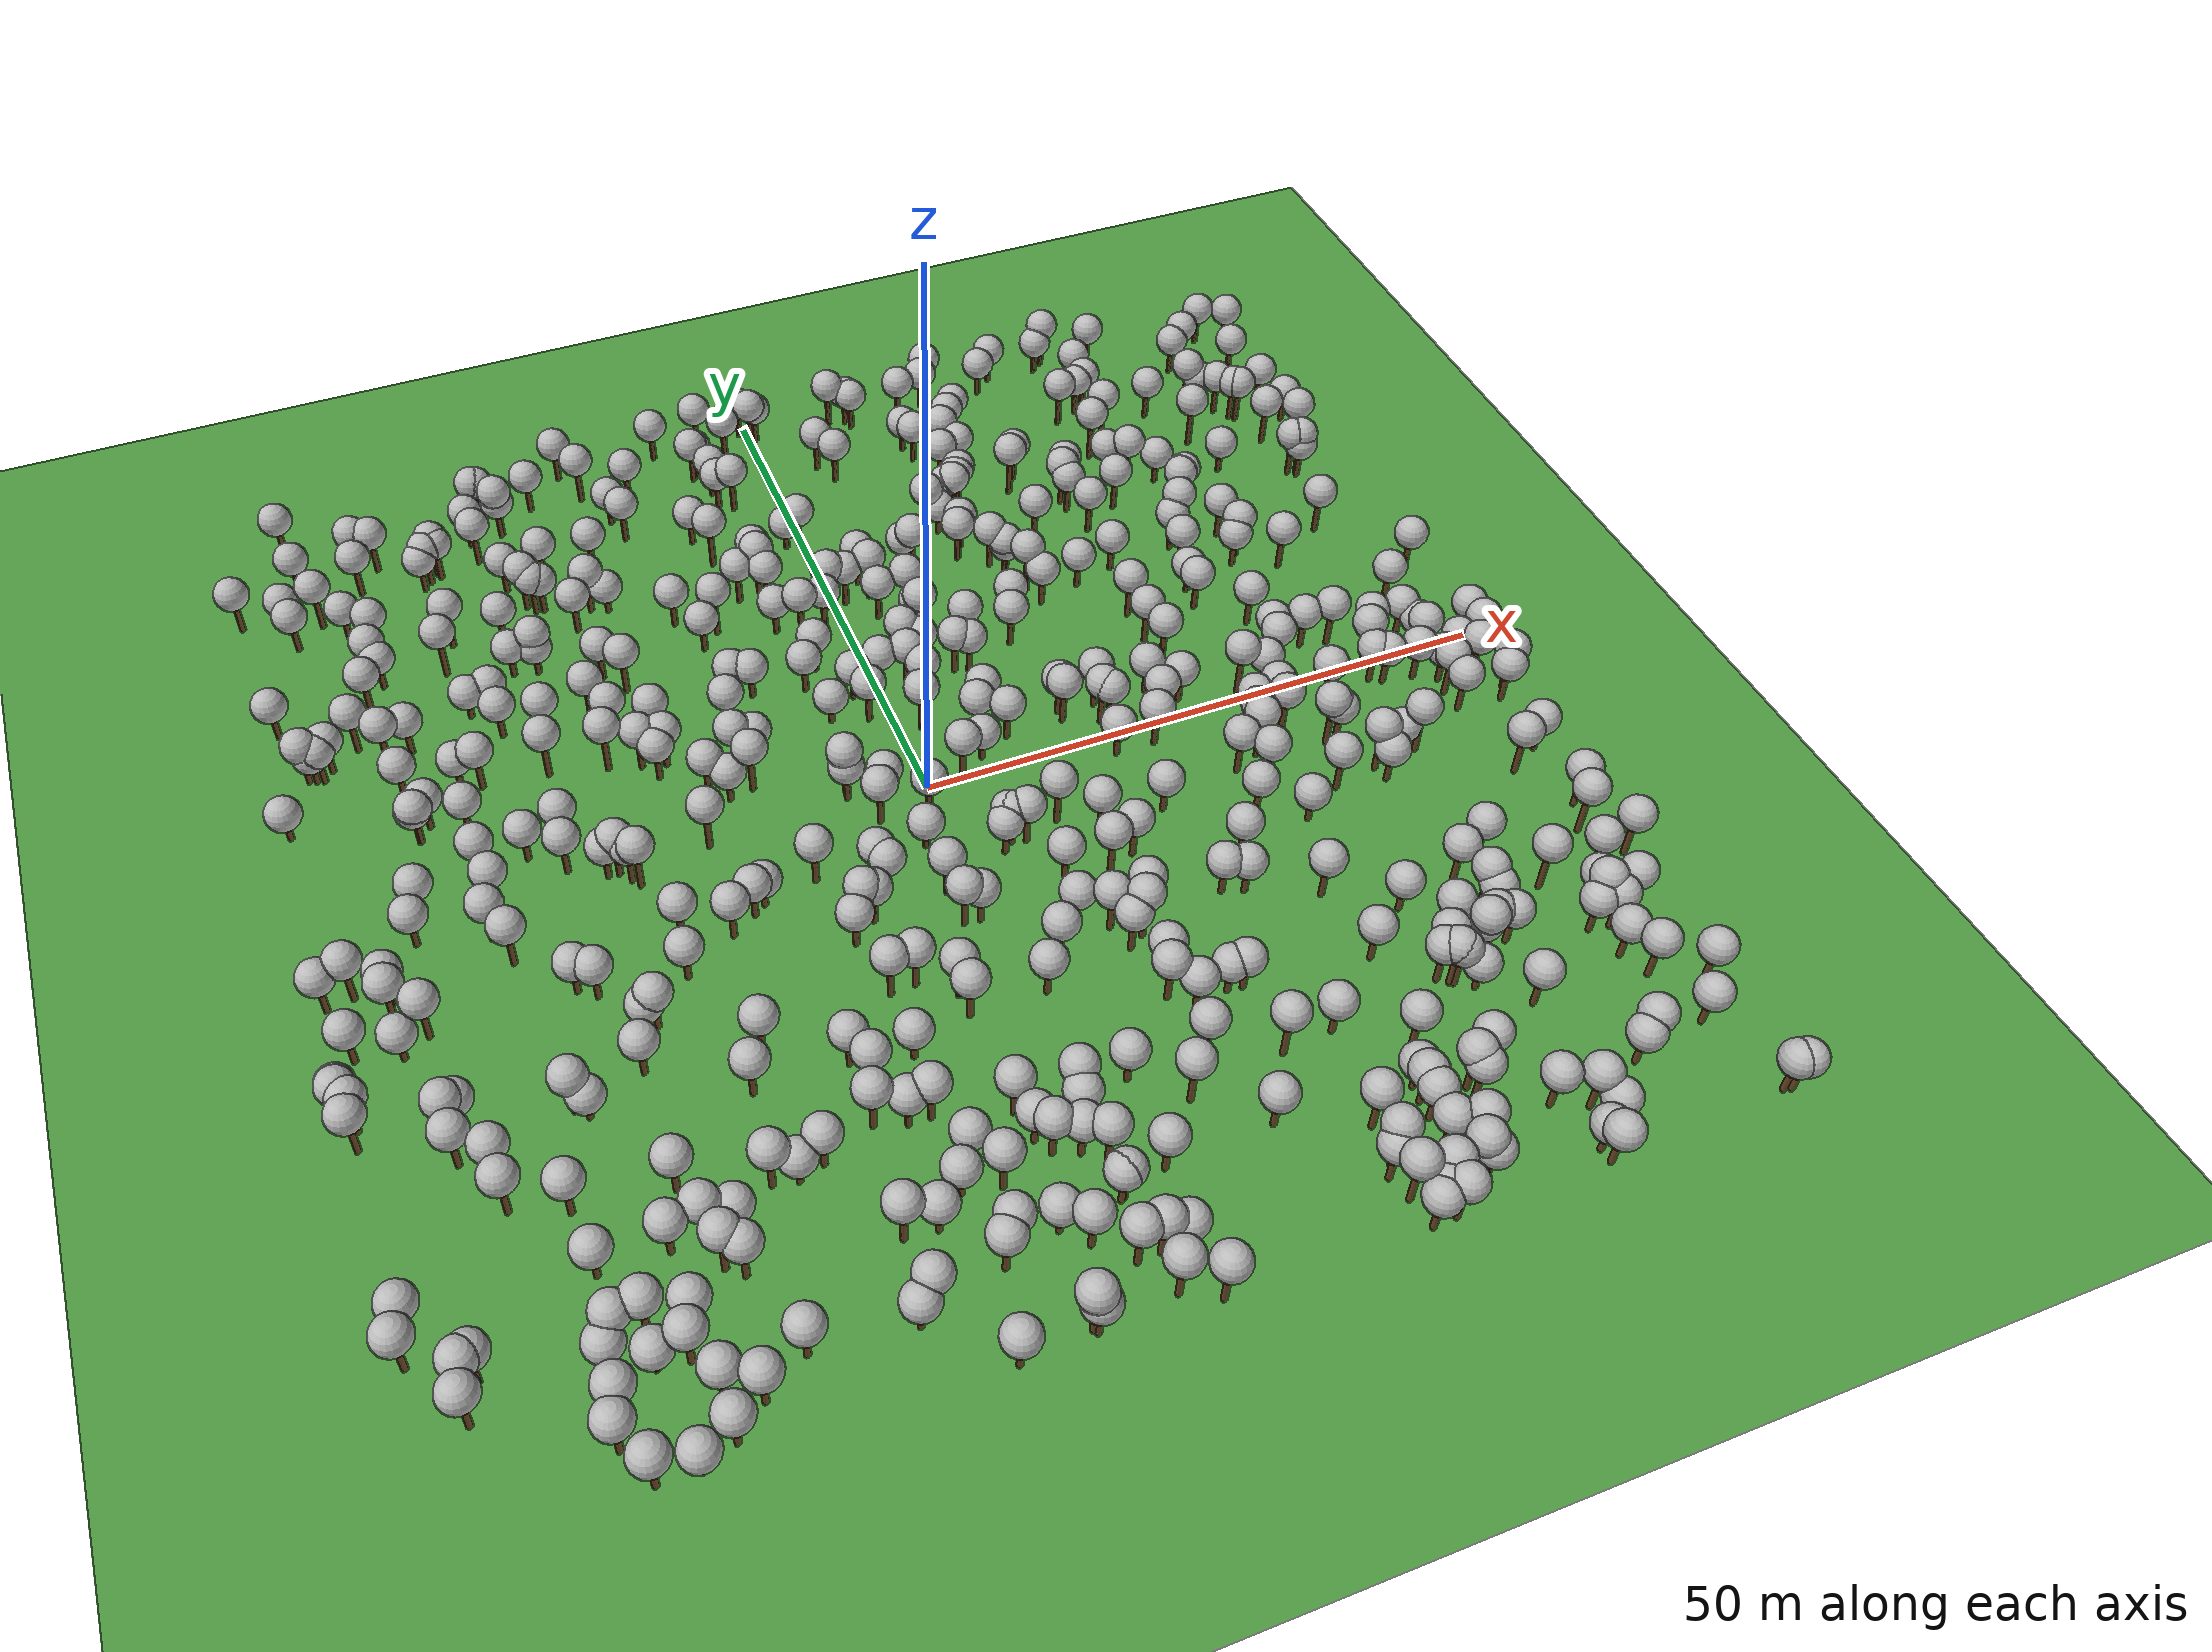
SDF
<sdf version="1.5">
  <world name="default">

    <plugin name="mrs_gazebo_static_transform_republisher_plugin" filename="libMRSGazeboStaticTransformRepublisher.so" />

    <spherical_coordinates>
      <surface_model>EARTH_WGS84</surface_model>
      <latitude_deg>47.397743</latitude_deg>
      <longitude_deg>8.545594</longitude_deg>
      <elevation>0.0</elevation>
      <heading_deg>0</heading_deg>
    </spherical_coordinates>

    <physics name="default_physics" default="0" type="ode">
      <gravity>0 0 -9.8066</gravity>
      <ode>
        <solver>
          <type>quick</type>
          <iters>50</iters>
          <sor>1.0</sor>
          <use_dynamic_moi_rescaling>0</use_dynamic_moi_rescaling>
        </solver>
        <constraints>
          <cfm>0</cfm>
          <erp>0.2</erp>
          <contact_max_correcting_vel>1000</contact_max_correcting_vel>
          <contact_surface_layer>0.001</contact_surface_layer>
        </constraints>
      </ode>
      <max_step_size>0.004</max_step_size>
      <real_time_factor>1</real_time_factor>
      <real_time_update_rate>250</real_time_update_rate>
      <magnetic_field>6.0e-06 2.3e-05 -4.2e-05</magnetic_field>
    </physics>

    <scene>
      <shadows>false</shadows>

    </scene>

    <light type="directional" name="sun">
      <cast_shadows>true</cast_shadows>
      <pose>250 250 600 0 0 0</pose>
      <diffuse>0.8 0.8 0.8 1</diffuse>
      <specular>0.2 0.2 0.2 1</specular>
      <attenuation>
        <range>1000</range>
        <constant>0.9</constant>
        <linear>0.01</linear>
        <quadratic>0.001</quadratic>
      </attenuation>
      <direction>0 0 -1</direction>
    </light>

    <model name="tree_simple499">
      <static>1</static>
      <link name="link">
        <pose frame="">0 0 0.1 0 -0 0</pose>
        <collision name="collision_trunk">
          <pose frame="">0 0 2 0 -0 0</pose>
          <geometry>
            <cylinder>
              <radius>0.25</radius>
              <length>4</length>
            </cylinder>
          </geometry>
        </collision>
        <collision name="collision_treetop">
          <pose frame="">0 0 5.2 0 -0 0</pose>
          <geometry>
            <sphere>
              <radius>1.5</radius>
            </sphere>
          </geometry>
        </collision>
        <visual name="trunk">
          <pose frame="">0 0 2 0 -0 0</pose>
          <geometry>
            <cylinder>
              <radius>0.25</radius>
              <length>4</length>
            </cylinder>
          </geometry>
          <material>
            <script>
              <uri>model://tree_simple/scripts</uri>
              <uri>model://tree_simple/materials/textures</uri>
              <name>TreeSimple/Trunk</name>
            </script>
          </material>
        </visual>
        <visual name="treetop">
          <pose frame="">0 0 5.2 0 -0 0</pose>
          <geometry>
            <sphere>
              <radius>1.5</radius>
            </sphere>
          </geometry>
          <material>
            <script>
              <uri>model://tree_simple/scripts</uri>
              <uri>model://tree_simple/materials/textures</uri>
              <name>TreeSimple/Treetop</name>
            </script>
          </material>
        </visual>
        <self_collide>0</self_collide>
        <kinematic>0</kinematic>
      </link>
      <pose frame="">49.5772894431 -0.301033806291 -0.9218746038410421 0 -0 0</pose>
    </model>

    <model name="tree_simple498">
      <static>1</static>
      <link name="link">
        <pose frame="">0 0 0.1 0 -0 0</pose>
        <collision name="collision_trunk">
          <pose frame="">0 0 2 0 -0 0</pose>
          <geometry>
            <cylinder>
              <radius>0.25</radius>
              <length>4</length>
            </cylinder>
          </geometry>
        </collision>
        <collision name="collision_treetop">
          <pose frame="">0 0 5.2 0 -0 0</pose>
          <geometry>
            <sphere>
              <radius>1.5</radius>
            </sphere>
          </geometry>
        </collision>
        <visual name="trunk">
          <pose frame="">0 0 2 0 -0 0</pose>
          <geometry>
            <cylinder>
              <radius>0.25</radius>
              <length>4</length>
            </cylinder>
          </geometry>
          <material>
            <script>
              <uri>model://tree_simple/scripts</uri>
              <uri>model://tree_simple/materials/textures</uri>
              <name>TreeSimple/Trunk</name>
            </script>
          </material>
        </visual>
        <visual name="treetop">
          <pose frame="">0 0 5.2 0 -0 0</pose>
          <geometry>
            <sphere>
              <radius>1.5</radius>
            </sphere>
          </geometry>
          <material>
            <script>
              <uri>model://tree_simple/scripts</uri>
              <uri>model://tree_simple/materials/textures</uri>
              <name>TreeSimple/Treetop</name>
            </script>
          </material>
        </visual>
        <self_collide>0</self_collide>
        <kinematic>0</kinematic>
      </link>
      <pose frame="">-20.062069779 9.09254194943 -1.4793378975880083 0 -0 0</pose>
    </model>

    <model name="tree_simple497">
      <static>1</static>
      <link name="link">
        <pose frame="">0 0 0.1 0 -0 0</pose>
        <collision name="collision_trunk">
          <pose frame="">0 0 2 0 -0 0</pose>
          <geometry>
            <cylinder>
              <radius>0.25</radius>
              <length>4</length>
            </cylinder>
          </geometry>
        </collision>
        <collision name="collision_treetop">
          <pose frame="">0 0 5.2 0 -0 0</pose>
          <geometry>
            <sphere>
              <radius>1.5</radius>
            </sphere>
          </geometry>
        </collision>
        <visual name="trunk">
          <pose frame="">0 0 2 0 -0 0</pose>
          <geometry>
            <cylinder>
              <radius>0.25</radius>
              <length>4</length>
            </cylinder>
          </geometry>
          <material>
            <script>
              <uri>model://tree_simple/scripts</uri>
              <uri>model://tree_simple/materials/textures</uri>
              <name>TreeSimple/Trunk</name>
            </script>
          </material>
        </visual>
        <visual name="treetop">
          <pose frame="">0 0 5.2 0 -0 0</pose>
          <geometry>
            <sphere>
              <radius>1.5</radius>
            </sphere>
          </geometry>
          <material>
            <script>
              <uri>model://tree_simple/scripts</uri>
              <uri>model://tree_simple/materials/textures</uri>
              <name>TreeSimple/Treetop</name>
            </script>
          </material>
        </visual>
        <self_collide>0</self_collide>
        <kinematic>0</kinematic>
      </link>
      <pose frame="">16.5730666381 19.0016793819 -0.0 0 -0 0</pose>
    </model>

    <model name="tree_simple496">
      <static>1</static>
      <link name="link">
        <pose frame="">0 0 0.1 0 -0 0</pose>
        <collision name="collision_trunk">
          <pose frame="">0 0 2 0 -0 0</pose>
          <geometry>
            <cylinder>
              <radius>0.25</radius>
              <length>4</length>
            </cylinder>
          </geometry>
        </collision>
        <collision name="collision_treetop">
          <pose frame="">0 0 5.2 0 -0 0</pose>
          <geometry>
            <sphere>
              <radius>1.5</radius>
            </sphere>
          </geometry>
        </collision>
        <visual name="trunk">
          <pose frame="">0 0 2 0 -0 0</pose>
          <geometry>
            <cylinder>
              <radius>0.25</radius>
              <length>4</length>
            </cylinder>
          </geometry>
          <material>
            <script>
              <uri>model://tree_simple/scripts</uri>
              <uri>model://tree_simple/materials/textures</uri>
              <name>TreeSimple/Trunk</name>
            </script>
          </material>
        </visual>
        <visual name="treetop">
          <pose frame="">0 0 5.2 0 -0 0</pose>
          <geometry>
            <sphere>
              <radius>1.5</radius>
            </sphere>
          </geometry>
          <material>
            <script>
              <uri>model://tree_simple/scripts</uri>
              <uri>model://tree_simple/materials/textures</uri>
              <name>TreeSimple/Treetop</name>
            </script>
          </material>
        </visual>
        <self_collide>0</self_collide>
        <kinematic>0</kinematic>
      </link>
      <pose frame="">13.6194298432 -26.9856291803 -1.9925861293488478 0 -0 0</pose>
    </model>

    <model name="tree_simple495">
      <static>1</static>
      <link name="link">
        <pose frame="">0 0 0.1 0 -0 0</pose>
        <collision name="collision_trunk">
          <pose frame="">0 0 2 0 -0 0</pose>
          <geometry>
            <cylinder>
              <radius>0.25</radius>
              <length>4</length>
            </cylinder>
          </geometry>
        </collision>
        <collision name="collision_treetop">
          <pose frame="">0 0 5.2 0 -0 0</pose>
          <geometry>
            <sphere>
              <radius>1.5</radius>
            </sphere>
          </geometry>
        </collision>
        <visual name="trunk">
          <pose frame="">0 0 2 0 -0 0</pose>
          <geometry>
            <cylinder>
              <radius>0.25</radius>
              <length>4</length>
            </cylinder>
          </geometry>
          <material>
            <script>
              <uri>model://tree_simple/scripts</uri>
              <uri>model://tree_simple/materials/textures</uri>
              <name>TreeSimple/Trunk</name>
            </script>
          </material>
        </visual>
        <visual name="treetop">
          <pose frame="">0 0 5.2 0 -0 0</pose>
          <geometry>
            <sphere>
              <radius>1.5</radius>
            </sphere>
          </geometry>
          <material>
            <script>
              <uri>model://tree_simple/scripts</uri>
              <uri>model://tree_simple/materials/textures</uri>
              <name>TreeSimple/Treetop</name>
            </script>
          </material>
        </visual>
        <self_collide>0</self_collide>
        <kinematic>0</kinematic>
      </link>
      <pose frame="">13.2663357304 3.23501246435 -0.7742167042662054 0 -0 0</pose>
    </model>

    <model name="tree_simple494">
      <static>1</static>
      <link name="link">
        <pose frame="">0 0 0.1 0 -0 0</pose>
        <collision name="collision_trunk">
          <pose frame="">0 0 2 0 -0 0</pose>
          <geometry>
            <cylinder>
              <radius>0.25</radius>
              <length>4</length>
            </cylinder>
          </geometry>
        </collision>
        <collision name="collision_treetop">
          <pose frame="">0 0 5.2 0 -0 0</pose>
          <geometry>
            <sphere>
              <radius>1.5</radius>
            </sphere>
          </geometry>
        </collision>
        <visual name="trunk">
          <pose frame="">0 0 2 0 -0 0</pose>
          <geometry>
            <cylinder>
              <radius>0.25</radius>
              <length>4</length>
            </cylinder>
          </geometry>
          <material>
            <script>
              <uri>model://tree_simple/scripts</uri>
              <uri>model://tree_simple/materials/textures</uri>
              <name>TreeSimple/Trunk</name>
            </script>
          </material>
        </visual>
        <visual name="treetop">
          <pose frame="">0 0 5.2 0 -0 0</pose>
          <geometry>
            <sphere>
              <radius>1.5</radius>
            </sphere>
          </geometry>
          <material>
            <script>
              <uri>model://tree_simple/scripts</uri>
              <uri>model://tree_simple/materials/textures</uri>
              <name>TreeSimple/Treetop</name>
            </script>
          </material>
        </visual>
        <self_collide>0</self_collide>
        <kinematic>0</kinematic>
      </link>
      <pose frame="">39.6521252177 -42.647901406 -1.007992381905501 0 -0 0</pose>
    </model>

    <model name="tree_simple493">
      <static>1</static>
      <link name="link">
        <pose frame="">0 0 0.1 0 -0 0</pose>
        <collision name="collision_trunk">
          <pose frame="">0 0 2 0 -0 0</pose>
          <geometry>
            <cylinder>
              <radius>0.25</radius>
              <length>4</length>
            </cylinder>
          </geometry>
        </collision>
        <collision name="collision_treetop">
          <pose frame="">0 0 5.2 0 -0 0</pose>
          <geometry>
            <sphere>
              <radius>1.5</radius>
            </sphere>
          </geometry>
        </collision>
        <visual name="trunk">
          <pose frame="">0 0 2 0 -0 0</pose>
          <geometry>
            <cylinder>
              <radius>0.25</radius>
              <length>4</length>
            </cylinder>
          </geometry>
          <material>
            <script>
              <uri>model://tree_simple/scripts</uri>
              <uri>model://tree_simple/materials/textures</uri>
              <name>TreeSimple/Trunk</name>
            </script>
          </material>
        </visual>
        <visual name="treetop">
          <pose frame="">0 0 5.2 0 -0 0</pose>
          <geometry>
            <sphere>
              <radius>1.5</radius>
            </sphere>
          </geometry>
          <material>
            <script>
              <uri>model://tree_simple/scripts</uri>
              <uri>model://tree_simple/materials/textures</uri>
              <name>TreeSimple/Treetop</name>
            </script>
          </material>
        </visual>
        <self_collide>0</self_collide>
        <kinematic>0</kinematic>
      </link>
      <pose frame="">-30.9686104206 18.3944298941 -1.6620912213675458 0 -0 0</pose>
    </model>

    <model name="tree_simple492">
      <static>1</static>
      <link name="link">
        <pose frame="">0 0 0.1 0 -0 0</pose>
        <collision name="collision_trunk">
          <pose frame="">0 0 2 0 -0 0</pose>
          <geometry>
            <cylinder>
              <radius>0.25</radius>
              <length>4</length>
            </cylinder>
          </geometry>
        </collision>
        <collision name="collision_treetop">
          <pose frame="">0 0 5.2 0 -0 0</pose>
          <geometry>
            <sphere>
              <radius>1.5</radius>
            </sphere>
          </geometry>
        </collision>
        <visual name="trunk">
          <pose frame="">0 0 2 0 -0 0</pose>
          <geometry>
            <cylinder>
              <radius>0.25</radius>
              <length>4</length>
            </cylinder>
          </geometry>
          <material>
            <script>
              <uri>model://tree_simple/scripts</uri>
              <uri>model://tree_simple/materials/textures</uri>
              <name>TreeSimple/Trunk</name>
            </script>
          </material>
        </visual>
        <visual name="treetop">
          <pose frame="">0 0 5.2 0 -0 0</pose>
          <geometry>
            <sphere>
              <radius>1.5</radius>
            </sphere>
          </geometry>
          <material>
            <script>
              <uri>model://tree_simple/scripts</uri>
              <uri>model://tree_simple/materials/textures</uri>
              <name>TreeSimple/Treetop</name>
            </script>
          </material>
        </visual>
        <self_collide>0</self_collide>
        <kinematic>0</kinematic>
      </link>
      <pose frame="">-7.60604313382 27.1336498888 -1.1574021075913579 0 -0 0</pose>
    </model>

    <model name="tree_simple491">
      <static>1</static>
      <link name="link">
        <pose frame="">0 0 0.1 0 -0 0</pose>
        <collision name="collision_trunk">
          <pose frame="">0 0 2 0 -0 0</pose>
          <geometry>
            <cylinder>
              <radius>0.25</radius>
              <length>4</length>
            </cylinder>
          </geometry>
        </collision>
        <collision name="collision_treetop">
          <pose frame="">0 0 5.2 0 -0 0</pose>
          <geometry>
            <sphere>
              <radius>1.5</radius>
            </sphere>
          </geometry>
        </collision>
        <visual name="trunk">
          <pose frame="">0 0 2 0 -0 0</pose>
          <geometry>
            <cylinder>
              <radius>0.25</radius>
              <length>4</length>
            </cylinder>
          </geometry>
          <material>
            <script>
              <uri>model://tree_simple/scripts</uri>
              <uri>model://tree_simple/materials/textures</uri>
              <name>TreeSimple/Trunk</name>
            </script>
          </material>
        </visual>
        <visual name="treetop">
          <pose frame="">0 0 5.2 0 -0 0</pose>
          <geometry>
            <sphere>
              <radius>1.5</radius>
            </sphere>
          </geometry>
          <material>
            <script>
              <uri>model://tree_simple/scripts</uri>
              <uri>model://tree_simple/materials/textures</uri>
              <name>TreeSimple/Treetop</name>
            </script>
          </material>
        </visual>
        <self_collide>0</self_collide>
        <kinematic>0</kinematic>
      </link>
      <pose frame="">-12.3902503735 -49.1082665042 -1.4765880961699187 0 -0 0</pose>
    </model>

    <model name="tree_simple490">
      <static>1</static>
      <link name="link">
        <pose frame="">0 0 0.1 0 -0 0</pose>
        <collision name="collision_trunk">
          <pose frame="">0 0 2 0 -0 0</pose>
          <geometry>
            <cylinder>
              <radius>0.25</radius>
              <length>4</length>
            </cylinder>
          </geometry>
        </collision>
        <collision name="collision_treetop">
          <pose frame="">0 0 5.2 0 -0 0</pose>
          <geometry>
            <sphere>
              <radius>1.5</radius>
            </sphere>
          </geometry>
        </collision>
        <visual name="trunk">
          <pose frame="">0 0 2 0 -0 0</pose>
          <geometry>
            <cylinder>
              <radius>0.25</radius>
              <length>4</length>
            </cylinder>
          </geometry>
          <material>
            <script>
              <uri>model://tree_simple/scripts</uri>
              <uri>model://tree_simple/materials/textures</uri>
              <name>TreeSimple/Trunk</name>
            </script>
          </material>
        </visual>
        <visual name="treetop">
          <pose frame="">0 0 5.2 0 -0 0</pose>
          <geometry>
            <sphere>
              <radius>1.5</radius>
            </sphere>
          </geometry>
          <material>
            <script>
              <uri>model://tree_simple/scripts</uri>
              <uri>model://tree_simple/materials/textures</uri>
              <name>TreeSimple/Treetop</name>
            </script>
          </material>
        </visual>
        <self_collide>0</self_collide>
        <kinematic>0</kinematic>
      </link>
      <pose frame="">28.486302093 0.994684244644 -0.20094864405570112 0 -0 0</pose>
    </model>

    <model name="tree_simple489">
      <static>1</static>
      <link name="link">
        <pose frame="">0 0 0.1 0 -0 0</pose>
        <collision name="collision_trunk">
          <pose frame="">0 0 2 0 -0 0</pose>
          <geometry>
            <cylinder>
              <radius>0.25</radius>
              <length>4</length>
            </cylinder>
          </geometry>
        </collision>
        <collision name="collision_treetop">
          <pose frame="">0 0 5.2 0 -0 0</pose>
          <geometry>
            <sphere>
              <radius>1.5</radius>
            </sphere>
          </geometry>
        </collision>
        <visual name="trunk">
          <pose frame="">0 0 2 0 -0 0</pose>
          <geometry>
            <cylinder>
              <radius>0.25</radius>
              <length>4</length>
            </cylinder>
          </geometry>
          <material>
            <script>
              <uri>model://tree_simple/scripts</uri>
              <uri>model://tree_simple/materials/textures</uri>
              <name>TreeSimple/Trunk</name>
            </script>
          </material>
        </visual>
        <visual name="treetop">
          <pose frame="">0 0 5.2 0 -0 0</pose>
          <geometry>
            <sphere>
              <radius>1.5</radius>
            </sphere>
          </geometry>
          <material>
            <script>
              <uri>model://tree_simple/scripts</uri>
              <uri>model://tree_simple/materials/textures</uri>
              <name>TreeSimple/Treetop</name>
            </script>
          </material>
        </visual>
        <self_collide>0</self_collide>
        <kinematic>0</kinematic>
      </link>
      <pose frame="">-32.6634579524 39.3278172931 -1.265425692254529 0 -0 0</pose>
    </model>

    <model name="tree_simple488">
      <static>1</static>
      <link name="link">
        <pose frame="">0 0 0.1 0 -0 0</pose>
        <collision name="collision_trunk">
          <pose frame="">0 0 2 0 -0 0</pose>
          <geometry>
            <cylinder>
              <radius>0.25</radius>
              <length>4</length>
            </cylinder>
          </geometry>
        </collision>
        <collision name="collision_treetop">
          <pose frame="">0 0 5.2 0 -0 0</pose>
          <geometry>
            <sphere>
              <radius>1.5</radius>
            </sphere>
          </geometry>
        </collision>
        <visual name="trunk">
          <pose frame="">0 0 2 0 -0 0</pose>
          <geometry>
            <cylinder>
              <radius>0.25</radius>
              <length>4</length>
            </cylinder>
          </geometry>
          <material>
            <script>
              <uri>model://tree_simple/scripts</uri>
              <uri>model://tree_simple/materials/textures</uri>
              <name>TreeSimple/Trunk</name>
            </script>
          </material>
        </visual>
        <visual name="treetop">
          <pose frame="">0 0 5.2 0 -0 0</pose>
          <geometry>
            <sphere>
              <radius>1.5</radius>
            </sphere>
          </geometry>
          <material>
            <script>
              <uri>model://tree_simple/scripts</uri>
              <uri>model://tree_simple/materials/textures</uri>
              <name>TreeSimple/Treetop</name>
            </script>
          </material>
        </visual>
        <self_collide>0</self_collide>
        <kinematic>0</kinematic>
      </link>
      <pose frame="">-13.1215818691 12.435953241 -1.1137479919838673 0 -0 0</pose>
    </model>

    <model name="tree_simple487">
      <static>1</static>
      <link name="link">
        <pose frame="">0 0 0.1 0 -0 0</pose>
        <collision name="collision_trunk">
          <pose frame="">0 0 2 0 -0 0</pose>
          <geometry>
            <cylinder>
              <radius>0.25</radius>
              <length>4</length>
            </cylinder>
          </geometry>
        </collision>
        <collision name="collision_treetop">
          <pose frame="">0 0 5.2 0 -0 0</pose>
          <geometry>
            <sphere>
              <radius>1.5</radius>
            </sphere>
          </geometry>
        </collision>
        <visual name="trunk">
          <pose frame="">0 0 2 0 -0 0</pose>
          <geometry>
            <cylinder>
              <radius>0.25</radius>
              <length>4</length>
            </cylinder>
          </geometry>
          <material>
            <script>
              <uri>model://tree_simple/scripts</uri>
              <uri>model://tree_simple/materials/textures</uri>
              <name>TreeSimple/Trunk</name>
            </script>
          </material>
        </visual>
        <visual name="treetop">
          <pose frame="">0 0 5.2 0 -0 0</pose>
          <geometry>
            <sphere>
              <radius>1.5</radius>
            </sphere>
          </geometry>
          <material>
            <script>
              <uri>model://tree_simple/scripts</uri>
              <uri>model://tree_simple/materials/textures</uri>
              <name>TreeSimple/Treetop</name>
            </script>
          </material>
        </visual>
        <self_collide>0</self_collide>
        <kinematic>0</kinematic>
      </link>
      <pose frame="">33.1280168764 8.35331864597 -1.3064170109202478 0 -0 0</pose>
    </model>

    <model name="tree_simple486">
      <static>1</static>
      <link name="link">
        <pose frame="">0 0 0.1 0 -0 0</pose>
        <collision name="collision_trunk">
          <pose frame="">0 0 2 0 -0 0</pose>
          <geometry>
            <cylinder>
              <radius>0.25</radius>
              <length>4</length>
            </cylinder>
          </geometry>
        </collision>
        <collision name="collision_treetop">
          <pose frame="">0 0 5.2 0 -0 0</pose>
          <geometry>
            <sphere>
              <radius>1.5</radius>
            </sphere>
          </geometry>
        </collision>
        <visual name="trunk">
          <pose frame="">0 0 2 0 -0 0</pose>
          <geometry>
            <cylinder>
              <radius>0.25</radius>
              <length>4</length>
            </cylinder>
          </geometry>
          <material>
            <script>
              <uri>model://tree_simple/scripts</uri>
              <uri>model://tree_simple/materials/textures</uri>
              <name>TreeSimple/Trunk</name>
            </script>
          </material>
        </visual>
        <visual name="treetop">
          <pose frame="">0 0 5.2 0 -0 0</pose>
          <geometry>
            <sphere>
              <radius>1.5</radius>
            </sphere>
          </geometry>
          <material>
            <script>
              <uri>model://tree_simple/scripts</uri>
              <uri>model://tree_simple/materials/textures</uri>
              <name>TreeSimple/Treetop</name>
            </script>
          </material>
        </visual>
        <self_collide>0</self_collide>
        <kinematic>0</kinematic>
      </link>
      <pose frame="">8.18281559396 11.6524151823 -1.3867703076284112 0 -0 0</pose>
    </model>

    <model name="tree_simple485">
      <static>1</static>
      <link name="link">
        <pose frame="">0 0 0.1 0 -0 0</pose>
        <collision name="collision_trunk">
          <pose frame="">0 0 2 0 -0 0</pose>
          <geometry>
            <cylinder>
              <radius>0.25</radius>
              <length>4</length>
            </cylinder>
          </geometry>
        </collision>
        <collision name="collision_treetop">
          <pose frame="">0 0 5.2 0 -0 0</pose>
          <geometry>
            <sphere>
              <radius>1.5</radius>
            </sphere>
          </geometry>
        </collision>
        <visual name="trunk">
          <pose frame="">0 0 2 0 -0 0</pose>
          <geometry>
            <cylinder>
              <radius>0.25</radius>
              <length>4</length>
            </cylinder>
          </geometry>
          <material>
            <script>
              <uri>model://tree_simple/scripts</uri>
              <uri>model://tree_simple/materials/textures</uri>
              <name>TreeSimple/Trunk</name>
            </script>
          </material>
        </visual>
        <visual name="treetop">
          <pose frame="">0 0 5.2 0 -0 0</pose>
          <geometry>
            <sphere>
              <radius>1.5</radius>
            </sphere>
          </geometry>
          <material>
            <script>
              <uri>model://tree_simple/scripts</uri>
              <uri>model://tree_simple/materials/textures</uri>
              <name>TreeSimple/Treetop</name>
            </script>
          </material>
        </visual>
        <self_collide>0</self_collide>
        <kinematic>0</kinematic>
      </link>
      <pose frame="">38.4673421664 3.60529435805 -0.771484179041458 0 -0 0</pose>
    </model>

    <model name="tree_simple484">
      <static>1</static>
      <link name="link">
        <pose frame="">0 0 0.1 0 -0 0</pose>
        <collision name="collision_trunk">
          <pose frame="">0 0 2 0 -0 0</pose>
          <geometry>
            <cylinder>
              <radius>0.25</radius>
              <length>4</length>
            </cylinder>
          </geometry>
        </collision>
        <collision name="collision_treetop">
          <pose frame="">0 0 5.2 0 -0 0</pose>
          <geometry>
            <sphere>
              <radius>1.5</radius>
            </sphere>
          </geometry>
        </collision>
        <visual name="trunk">
          <pose frame="">0 0 2 0 -0 0</pose>
          <geometry>
            <cylinder>
              <radius>0.25</radius>
              <length>4</length>
            </cylinder>
          </geometry>
          <material>
            <script>
              <uri>model://tree_simple/scripts</uri>
              <uri>model://tree_simple/materials/textures</uri>
              <name>TreeSimple/Trunk</name>
            </script>
          </material>
        </visual>
        <visual name="treetop">
          <pose frame="">0 0 5.2 0 -0 0</pose>
          <geometry>
            <sphere>
              <radius>1.5</radius>
            </sphere>
          </geometry>
          <material>
            <script>
              <uri>model://tree_simple/scripts</uri>
              <uri>model://tree_simple/materials/textures</uri>
              <name>TreeSimple/Treetop</name>
            </script>
          </material>
        </visual>
        <self_collide>0</self_collide>
        <kinematic>0</kinematic>
      </link>
      <pose frame="">19.8605088225 -47.9062304077 -0.7585750219698935 0 -0 0</pose>
    </model>

    <model name="tree_simple483">
      <static>1</static>
      <link name="link">
        <pose frame="">0 0 0.1 0 -0 0</pose>
        <collision name="collision_trunk">
          <pose frame="">0 0 2 0 -0 0</pose>
          <geometry>
            <cylinder>
              <radius>0.25</radius>
              <length>4</length>
            </cylinder>
          </geometry>
        </collision>
        <collision name="collision_treetop">
          <pose frame="">0 0 5.2 0 -0 0</pose>
          <geometry>
            <sphere>
              <radius>1.5</radius>
            </sphere>
          </geometry>
        </collision>
        <visual name="trunk">
          <pose frame="">0 0 2 0 -0 0</pose>
          <geometry>
            <cylinder>
              <radius>0.25</radius>
              <length>4</length>
            </cylinder>
          </geometry>
          <material>
            <script>
              <uri>model://tree_simple/scripts</uri>
              <uri>model://tree_simple/materials/textures</uri>
              <name>TreeSimple/Trunk</name>
            </script>
          </material>
        </visual>
        <visual name="treetop">
          <pose frame="">0 0 5.2 0 -0 0</pose>
          <geometry>
            <sphere>
              <radius>1.5</radius>
            </sphere>
          </geometry>
          <material>
            <script>
              <uri>model://tree_simple/scripts</uri>
              <uri>model://tree_simple/materials/textures</uri>
              <name>TreeSimple/Treetop</name>
            </script>
          </material>
        </visual>
        <self_collide>0</self_collide>
        <kinematic>0</kinematic>
      </link>
      <pose frame="">-6.65162129766 44.7613363002 -1.2295763160659292 0 -0 0</pose>
    </model>

    <model name="tree_simple482">
      <static>1</static>
      <link name="link">
        <pose frame="">0 0 0.1 0 -0 0</pose>
        <collision name="collision_trunk">
          <pose frame="">0 0 2 0 -0 0</pose>
          <geometry>
            <cylinder>
              <radius>0.25</radius>
              <length>4</length>
            </cylinder>
          </geometry>
        </collision>
        <collision name="collision_treetop">
          <pose frame="">0 0 5.2 0 -0 0</pose>
          <geometry>
            <sphere>
              <radius>1.5</radius>
            </sphere>
          </geometry>
        </collision>
        <visual name="trunk">
          <pose frame="">0 0 2 0 -0 0</pose>
          <geometry>
            <cylinder>
              <radius>0.25</radius>
              <length>4</length>
            </cylinder>
          </geometry>
          <material>
            <script>
              <uri>model://tree_simple/scripts</uri>
              <uri>model://tree_simple/materials/textures</uri>
              <name>TreeSimple/Trunk</name>
            </script>
          </material>
        </visual>
        <visual name="treetop">
          <pose frame="">0 0 5.2 0 -0 0</pose>
          <geometry>
            <sphere>
              <radius>1.5</radius>
            </sphere>
          </geometry>
          <material>
            <script>
              <uri>model://tree_simple/scripts</uri>
              <uri>model://tree_simple/materials/textures</uri>
              <name>TreeSimple/Treetop</name>
            </script>
          </material>
        </visual>
        <self_collide>0</self_collide>
        <kinematic>0</kinematic>
      </link>
      <pose frame="">-31.7137183406 39.6850484597 -1.3092640749925835 0 -0 0</pose>
    </model>

    <model name="tree_simple481">
      <static>1</static>
      <link name="link">
        <pose frame="">0 0 0.1 0 -0 0</pose>
        <collision name="collision_trunk">
          <pose frame="">0 0 2 0 -0 0</pose>
          <geometry>
            <cylinder>
              <radius>0.25</radius>
              <length>4</length>
            </cylinder>
          </geometry>
        </collision>
        <collision name="collision_treetop">
          <pose frame="">0 0 5.2 0 -0 0</pose>
          <geometry>
            <sphere>
              <radius>1.5</radius>
            </sphere>
          </geometry>
        </collision>
        <visual name="trunk">
          <pose frame="">0 0 2 0 -0 0</pose>
          <geometry>
            <cylinder>
              <radius>0.25</radius>
              <length>4</length>
            </cylinder>
          </geometry>
          <material>
            <script>
              <uri>model://tree_simple/scripts</uri>
              <uri>model://tree_simple/materials/textures</uri>
              <name>TreeSimple/Trunk</name>
            </script>
          </material>
        </visual>
        <visual name="treetop">
          <pose frame="">0 0 5.2 0 -0 0</pose>
          <geometry>
            <sphere>
              <radius>1.5</radius>
            </sphere>
          </geometry>
          <material>
            <script>
              <uri>model://tree_simple/scripts</uri>
              <uri>model://tree_simple/materials/textures</uri>
              <name>TreeSimple/Treetop</name>
            </script>
          </material>
        </visual>
        <self_collide>0</self_collide>
        <kinematic>0</kinematic>
      </link>
      <pose frame="">-37.2553351017 -39.4739685818 -2.313164512455125 0 -0 0</pose>
    </model>

    <model name="tree_simple480">
      <static>1</static>
      <link name="link">
        <pose frame="">0 0 0.1 0 -0 0</pose>
        <collision name="collision_trunk">
          <pose frame="">0 0 2 0 -0 0</pose>
          <geometry>
            <cylinder>
              <radius>0.25</radius>
              <length>4</length>
            </cylinder>
          </geometry>
        </collision>
        <collision name="collision_treetop">
          <pose frame="">0 0 5.2 0 -0 0</pose>
          <geometry>
            <sphere>
              <radius>1.5</radius>
            </sphere>
          </geometry>
        </collision>
        <visual name="trunk">
          <pose frame="">0 0 2 0 -0 0</pose>
          <geometry>
            <cylinder>
              <radius>0.25</radius>
              <length>4</length>
            </cylinder>
          </geometry>
          <material>
            <script>
              <uri>model://tree_simple/scripts</uri>
              <uri>model://tree_simple/materials/textures</uri>
              <name>TreeSimple/Trunk</name>
            </script>
          </material>
        </visual>
        <visual name="treetop">
          <pose frame="">0 0 5.2 0 -0 0</pose>
          <geometry>
            <sphere>
              <radius>1.5</radius>
            </sphere>
          </geometry>
          <material>
            <script>
              <uri>model://tree_simple/scripts</uri>
              <uri>model://tree_simple/materials/textures</uri>
              <name>TreeSimple/Treetop</name>
            </script>
          </material>
        </visual>
        <self_collide>0</self_collide>
        <kinematic>0</kinematic>
      </link>
      <pose frame="">-2.16211412072 12.1351070175 -1.9079232740041454 0 -0 0</pose>
    </model>

    <model name="tree_simple479">
      <static>1</static>
      <link name="link">
        <pose frame="">0 0 0.1 0 -0 0</pose>
        <collision name="collision_trunk">
          <pose frame="">0 0 2 0 -0 0</pose>
          <geometry>
            <cylinder>
              <radius>0.25</radius>
              <length>4</length>
            </cylinder>
          </geometry>
        </collision>
        <collision name="collision_treetop">
          <pose frame="">0 0 5.2 0 -0 0</pose>
          <geometry>
            <sphere>
              <radius>1.5</radius>
            </sphere>
          </geometry>
        </collision>
        <visual name="trunk">
          <pose frame="">0 0 2 0 -0 0</pose>
          <geometry>
            <cylinder>
              <radius>0.25</radius>
              <length>4</length>
            </cylinder>
          </geometry>
          <material>
            <script>
              <uri>model://tree_simple/scripts</uri>
              <uri>model://tree_simple/materials/textures</uri>
              <name>TreeSimple/Trunk</name>
            </script>
          </material>
        </visual>
        <visual name="treetop">
          <pose frame="">0 0 5.2 0 -0 0</pose>
          <geometry>
            <sphere>
              <radius>1.5</radius>
            </sphere>
          </geometry>
          <material>
            <script>
              <uri>model://tree_simple/scripts</uri>
              <uri>model://tree_simple/materials/textures</uri>
              <name>TreeSimple/Treetop</name>
            </script>
          </material>
        </visual>
        <self_collide>0</self_collide>
        <kinematic>0</kinematic>
      </link>
      <pose frame="">-12.2778199556 22.3020251283 -1.718333494915143 0 -0 0</pose>
    </model>

    <model name="tree_simple478">
      <static>1</static>
      <link name="link">
        <pose frame="">0 0 0.1 0 -0 0</pose>
        <collision name="collision_trunk">
          <pose frame="">0 0 2 0 -0 0</pose>
          <geometry>
            <cylinder>
              <radius>0.25</radius>
              <length>4</length>
            </cylinder>
          </geometry>
        </collision>
        <collision name="collision_treetop">
          <pose frame="">0 0 5.2 0 -0 0</pose>
          <geometry>
            <sphere>
              <radius>1.5</radius>
            </sphere>
          </geometry>
        </collision>
        <visual name="trunk">
          <pose frame="">0 0 2 0 -0 0</pose>
          <geometry>
            <cylinder>
              <radius>0.25</radius>
              <length>4</length>
            </cylinder>
          </geometry>
          <material>
            <script>
              <uri>model://tree_simple/scripts</uri>
              <uri>model://tree_simple/materials/textures</uri>
              <name>TreeSimple/Trunk</name>
            </script>
          </material>
        </visual>
        <visual name="treetop">
          <pose frame="">0 0 5.2 0 -0 0</pose>
          <geometry>
            <sphere>
              <radius>1.5</radius>
            </sphere>
          </geometry>
          <material>
            <script>
              <uri>model://tree_simple/scripts</uri>
              <uri>model://tree_simple/materials/textures</uri>
              <name>TreeSimple/Treetop</name>
            </script>
          </material>
        </visual>
        <self_collide>0</self_collide>
        <kinematic>0</kinematic>
      </link>
      <pose frame="">6.74093075138 -12.3162984353 -1.8605144772350228 0 -0 0</pose>
    </model>

    <model name="tree_simple477">
      <static>1</static>
      <link name="link">
        <pose frame="">0 0 0.1 0 -0 0</pose>
        <collision name="collision_trunk">
          <pose frame="">0 0 2 0 -0 0</pose>
          <geometry>
            <cylinder>
              <radius>0.25</radius>
              <length>4</length>
            </cylinder>
          </geometry>
        </collision>
        <collision name="collision_treetop">
          <pose frame="">0 0 5.2 0 -0 0</pose>
          <geometry>
            <sphere>
              <radius>1.5</radius>
            </sphere>
          </geometry>
        </collision>
        <visual name="trunk">
          <pose frame="">0 0 2 0 -0 0</pose>
          <geometry>
            <cylinder>
              <radius>0.25</radius>
              <length>4</length>
            </cylinder>
          </geometry>
          <material>
            <script>
              <uri>model://tree_simple/scripts</uri>
              <uri>model://tree_simple/materials/textures</uri>
              <name>TreeSimple/Trunk</name>
            </script>
          </material>
        </visual>
        <visual name="treetop">
          <pose frame="">0 0 5.2 0 -0 0</pose>
          <geometry>
            <sphere>
              <radius>1.5</radius>
            </sphere>
          </geometry>
          <material>
            <script>
              <uri>model://tree_simple/scripts</uri>
              <uri>model://tree_simple/materials/textures</uri>
              <name>TreeSimple/Treetop</name>
            </script>
          </material>
        </visual>
        <self_collide>0</self_collide>
        <kinematic>0</kinematic>
      </link>
      <pose frame="">-0.22927085135 32.6495918535 -1.5772530974305565 0 -0 0</pose>
    </model>

    <model name="tree_simple476">
      <static>1</static>
      <link name="link">
        <pose frame="">0 0 0.1 0 -0 0</pose>
        <collision name="collision_trunk">
          <pose frame="">0 0 2 0 -0 0</pose>
          <geometry>
            <cylinder>
              <radius>0.25</radius>
              <length>4</length>
            </cylinder>
          </geometry>
        </collision>
        <collision name="collision_treetop">
          <pose frame="">0 0 5.2 0 -0 0</pose>
          <geometry>
            <sphere>
              <radius>1.5</radius>
            </sphere>
          </geometry>
        </collision>
        <visual name="trunk">
          <pose frame="">0 0 2 0 -0 0</pose>
          <geometry>
            <cylinder>
              <radius>0.25</radius>
              <length>4</length>
            </cylinder>
          </geometry>
          <material>
            <script>
              <uri>model://tree_simple/scripts</uri>
              <uri>model://tree_simple/materials/textures</uri>
              <name>TreeSimple/Trunk</name>
            </script>
          </material>
        </visual>
        <visual name="treetop">
          <pose frame="">0 0 5.2 0 -0 0</pose>
          <geometry>
            <sphere>
              <radius>1.5</radius>
            </sphere>
          </geometry>
          <material>
            <script>
              <uri>model://tree_simple/scripts</uri>
              <uri>model://tree_simple/materials/textures</uri>
              <name>TreeSimple/Treetop</name>
            </script>
          </material>
        </visual>
        <self_collide>0</self_collide>
        <kinematic>0</kinematic>
      </link>
      <pose frame="">-40.490555579 18.243153787 -0.37724001220063663 0 -0 0</pose>
    </model>

    <model name="tree_simple475">
      <static>1</static>
      <link name="link">
        <pose frame="">0 0 0.1 0 -0 0</pose>
        <collision name="collision_trunk">
          <pose frame="">0 0 2 0 -0 0</pose>
          <geometry>
            <cylinder>
              <radius>0.25</radius>
              <length>4</length>
            </cylinder>
          </geometry>
        </collision>
        <collision name="collision_treetop">
          <pose frame="">0 0 5.2 0 -0 0</pose>
          <geometry>
            <sphere>
              <radius>1.5</radius>
            </sphere>
          </geometry>
        </collision>
        <visual name="trunk">
          <pose frame="">0 0 2 0 -0 0</pose>
          <geometry>
            <cylinder>
              <radius>0.25</radius>
              <length>4</length>
            </cylinder>
          </geometry>
          <material>
            <script>
              <uri>model://tree_simple/scripts</uri>
              <uri>model://tree_simple/materials/textures</uri>
              <name>TreeSimple/Trunk</name>
            </script>
          </material>
        </visual>
        <visual name="treetop">
          <pose frame="">0 0 5.2 0 -0 0</pose>
          <geometry>
            <sphere>
              <radius>1.5</radius>
            </sphere>
          </geometry>
          <material>
            <script>
              <uri>model://tree_simple/scripts</uri>
              <uri>model://tree_simple/materials/textures</uri>
              <name>TreeSimple/Treetop</name>
            </script>
          </material>
        </visual>
        <self_collide>0</self_collide>
        <kinematic>0</kinematic>
      </link>
      <pose frame="">30.9431222124 49.7431013716 -0.7436420474944433 0 -0 0</pose>
    </model>

    <model name="tree_simple474">
      <static>1</static>
      <link name="link">
        <pose frame="">0 0 0.1 0 -0 0</pose>
        <collision name="collision_trunk">
          <pose frame="">0 0 2 0 -0 0</pose>
          <geometry>
            <cylinder>
              <radius>0.25</radius>
              <length>4</length>
            </cylinder>
          </geometry>
        </collision>
        <collision name="collision_treetop">
          <pose frame="">0 0 5.2 0 -0 0</pose>
          <geometry>
            <sphere>
              <radius>1.5</radius>
            </sphere>
          </geometry>
        </collision>
        <visual name="trunk">
          <pose frame="">0 0 2 0 -0 0</pose>
          <geometry>
            <cylinder>
              <radius>0.25</radius>
              <length>4</length>
            </cylinder>
          </geometry>
          <material>
            <script>
              <uri>model://tree_simple/scripts</uri>
              <uri>model://tree_simple/materials/textures</uri>
              <name>TreeSimple/Trunk</name>
            </script>
          </material>
        </visual>
        <visual name="treetop">
          <pose frame="">0 0 5.2 0 -0 0</pose>
          <geometry>
            <sphere>
              <radius>1.5</radius>
            </sphere>
          </geometry>
          <material>
            <script>
              <uri>model://tree_simple/scripts</uri>
              <uri>model://tree_simple/materials/textures</uri>
              <name>TreeSimple/Treetop</name>
            </script>
          </material>
        </visual>
        <self_collide>0</self_collide>
        <kinematic>0</kinematic>
      </link>
      <pose frame="">-45.5609359524 37.3889677829 -1.604523708782969 0 -0 0</pose>
    </model>

    <model name="tree_simple473">
      <static>1</static>
      <link name="link">
        <pose frame="">0 0 0.1 0 -0 0</pose>
        <collision name="collision_trunk">
          <pose frame="">0 0 2 0 -0 0</pose>
          <geometry>
            <cylinder>
              <radius>0.25</radius>
              <length>4</length>
            </cylinder>
          </geometry>
        </collision>
        <collision name="collision_treetop">
          <pose frame="">0 0 5.2 0 -0 0</pose>
          <geometry>
            <sphere>
              <radius>1.5</radius>
            </sphere>
          </geometry>
        </collision>
        <visual name="trunk">
          <pose frame="">0 0 2 0 -0 0</pose>
          <geometry>
            <cylinder>
              <radius>0.25</radius>
              <length>4</length>
            </cylinder>
          </geometry>
          <material>
            <script>
              <uri>model://tree_simple/scripts</uri>
              <uri>model://tree_simple/materials/textures</uri>
              <name>TreeSimple/Trunk</name>
            </script>
          </material>
        </visual>
        <visual name="treetop">
          <pose frame="">0 0 5.2 0 -0 0</pose>
          <geometry>
            <sphere>
              <radius>1.5</radius>
            </sphere>
          </geometry>
          <material>
            <script>
              <uri>model://tree_simple/scripts</uri>
              <uri>model://tree_simple/materials/textures</uri>
              <name>TreeSimple/Treetop</name>
            </script>
          </material>
        </visual>
        <self_collide>0</self_collide>
        <kinematic>0</kinematic>
      </link>
      <pose frame="">35.3600050295 -12.4568326028 -1.7473180829373098 0 -0 0</pose>
    </model>

    <model name="tree_simple472">
      <static>1</static>
      <link name="link">
        <pose frame="">0 0 0.1 0 -0 0</pose>
        <collision name="collision_trunk">
          <pose frame="">0 0 2 0 -0 0</pose>
          <geometry>
            <cylinder>
              <radius>0.25</radius>
              <length>4</length>
            </cylinder>
          </geometry>
        </collision>
        <collision name="collision_treetop">
          <pose frame="">0 0 5.2 0 -0 0</pose>
          <geometry>
            <sphere>
              <radius>1.5</radius>
            </sphere>
          </geometry>
        </collision>
        <visual name="trunk">
          <pose frame="">0 0 2 0 -0 0</pose>
          <geometry>
            <cylinder>
              <radius>0.25</radius>
              <length>4</length>
            </cylinder>
          </geometry>
          <material>
            <script>
              <uri>model://tree_simple/scripts</uri>
              <uri>model://tree_simple/materials/textures</uri>
              <name>TreeSimple/Trunk</name>
            </script>
          </material>
        </visual>
        <visual name="treetop">
          <pose frame="">0 0 5.2 0 -0 0</pose>
          <geometry>
            <sphere>
              <radius>1.5</radius>
            </sphere>
          </geometry>
          <material>
            <script>
              <uri>model://tree_simple/scripts</uri>
              <uri>model://tree_simple/materials/textures</uri>
              <name>TreeSimple/Treetop</name>
            </script>
          </material>
        </visual>
        <self_collide>0</self_collide>
        <kinematic>0</kinematic>
      </link>
      <pose frame="">9.92228677952 -23.8303447852 -1.431262749278447 0 -0 0</pose>
    </model>

    <model name="tree_simple471">
      <static>1</static>
      <link name="link">
        <pose frame="">0 0 0.1 0 -0 0</pose>
        <collision name="collision_trunk">
          <pose frame="">0 0 2 0 -0 0</pose>
          <geometry>
            <cylinder>
              <radius>0.25</radius>
              <length>4</length>
            </cylinder>
          </geometry>
        </collision>
        <collision name="collision_treetop">
          <pose frame="">0 0 5.2 0 -0 0</pose>
          <geometry>
            <sphere>
              <radius>1.5</radius>
            </sphere>
          </geometry>
        </collision>
        <visual name="trunk">
          <pose frame="">0 0 2 0 -0 0</pose>
          <geometry>
            <cylinder>
              <radius>0.25</radius>
              <length>4</length>
            </cylinder>
          </geometry>
          <material>
            <script>
              <uri>model://tree_simple/scripts</uri>
              <uri>model://tree_simple/materials/textures</uri>
              <name>TreeSimple/Trunk</name>
            </script>
          </material>
        </visual>
        <visual name="treetop">
          <pose frame="">0 0 5.2 0 -0 0</pose>
          <geometry>
            <sphere>
              <radius>1.5</radius>
            </sphere>
          </geometry>
          <material>
            <script>
              <uri>model://tree_simple/scripts</uri>
              <uri>model://tree_simple/materials/textures</uri>
              <name>TreeSimple/Treetop</name>
            </script>
          </material>
        </visual>
        <self_collide>0</self_collide>
        <kinematic>0</kinematic>
      </link>
      <pose frame="">-4.10985349052 16.4703272545 -1.4061973708859414 0 -0 0</pose>
    </model>

    <model name="tree_simple470">
      <static>1</static>
      <link name="link">
        <pose frame="">0 0 0.1 0 -0 0</pose>
        <collision name="collision_trunk">
          <pose frame="">0 0 2 0 -0 0</pose>
          <geometry>
            <cylinder>
              <radius>0.25</radius>
              <length>4</length>
            </cylinder>
          </geometry>
        </collision>
        <collision name="collision_treetop">
          <pose frame="">0 0 5.2 0 -0 0</pose>
          <geometry>
            <sphere>
              <radius>1.5</radius>
            </sphere>
          </geometry>
        </collision>
        <visual name="trunk">
          <pose frame="">0 0 2 0 -0 0</pose>
          <geometry>
            <cylinder>
              <radius>0.25</radius>
              <length>4</length>
            </cylinder>
          </geometry>
          <material>
            <script>
              <uri>model://tree_simple/scripts</uri>
              <uri>model://tree_simple/materials/textures</uri>
              <name>TreeSimple/Trunk</name>
            </script>
          </material>
        </visual>
        <visual name="treetop">
          <pose frame="">0 0 5.2 0 -0 0</pose>
          <geometry>
            <sphere>
              <radius>1.5</radius>
            </sphere>
          </geometry>
          <material>
            <script>
              <uri>model://tree_simple/scripts</uri>
              <uri>model://tree_simple/materials/textures</uri>
              <name>TreeSimple/Treetop</name>
            </script>
          </material>
        </visual>
        <self_collide>0</self_collide>
        <kinematic>0</kinematic>
      </link>
      <pose frame="">-42.5418923399 21.0598314505 -0.8731344209117238 0 -0 0</pose>
    </model>

    <model name="tree_simple469">
      <static>1</static>
      <link name="link">
        <pose frame="">0 0 0.1 0 -0 0</pose>
        <collision name="collision_trunk">
          <pose frame="">0 0 2 0 -0 0</pose>
          <geometry>
            <cylinder>
              <radius>0.25</radius>
              <length>4</length>
            </cylinder>
          </geometry>
        </collision>
        <collision name="collision_treetop">
          <pose frame="">0 0 5.2 0 -0 0</pose>
          <geometry>
            <sphere>
              <radius>1.5</radius>
            </sphere>
          </geometry>
        </collision>
        <visual name="trunk">
          <pose frame="">0 0 2 0 -0 0</pose>
          <geometry>
            <cylinder>
              <radius>0.25</radius>
              <length>4</length>
            </cylinder>
          </geometry>
          <material>
            <script>
              <uri>model://tree_simple/scripts</uri>
              <uri>model://tree_simple/materials/textures</uri>
              <name>TreeSimple/Trunk</name>
            </script>
          </material>
        </visual>
        <visual name="treetop">
          <pose frame="">0 0 5.2 0 -0 0</pose>
          <geometry>
            <sphere>
              <radius>1.5</radius>
            </sphere>
          </geometry>
          <material>
            <script>
              <uri>model://tree_simple/scripts</uri>
              <uri>model://tree_simple/materials/textures</uri>
              <name>TreeSimple/Treetop</name>
            </script>
          </material>
        </visual>
        <self_collide>0</self_collide>
        <kinematic>0</kinematic>
      </link>
      <pose frame="">28.6908934165 -31.7515844244 -1.147731988438275 0 -0 0</pose>
    </model>

    <model name="tree_simple468">
      <static>1</static>
      <link name="link">
        <pose frame="">0 0 0.1 0 -0 0</pose>
        <collision name="collision_trunk">
          <pose frame="">0 0 2 0 -0 0</pose>
          <geometry>
            <cylinder>
              <radius>0.25</radius>
              <length>4</length>
            </cylinder>
          </geometry>
        </collision>
        <collision name="collision_treetop">
          <pose frame="">0 0 5.2 0 -0 0</pose>
          <geometry>
            <sphere>
              <radius>1.5</radius>
            </sphere>
          </geometry>
        </collision>
        <visual name="trunk">
          <pose frame="">0 0 2 0 -0 0</pose>
          <geometry>
            <cylinder>
              <radius>0.25</radius>
              <length>4</length>
            </cylinder>
          </geometry>
          <material>
            <script>
              <uri>model://tree_simple/scripts</uri>
              <uri>model://tree_simple/materials/textures</uri>
              <name>TreeSimple/Trunk</name>
            </script>
          </material>
        </visual>
        <visual name="treetop">
          <pose frame="">0 0 5.2 0 -0 0</pose>
          <geometry>
            <sphere>
              <radius>1.5</radius>
            </sphere>
          </geometry>
          <material>
            <script>
              <uri>model://tree_simple/scripts</uri>
              <uri>model://tree_simple/materials/textures</uri>
              <name>TreeSimple/Treetop</name>
            </script>
          </material>
        </visual>
        <self_collide>0</self_collide>
        <kinematic>0</kinematic>
      </link>
      <pose frame="">33.4354348071 -7.20044037788 -1.1774211655421292 0 -0 0</pose>
    </model>

    <model name="tree_simple467">
      <static>1</static>
      <link name="link">
        <pose frame="">0 0 0.1 0 -0 0</pose>
        <collision name="collision_trunk">
          <pose frame="">0 0 2 0 -0 0</pose>
          <geometry>
            <cylinder>
              <radius>0.25</radius>
              <length>4</length>
            </cylinder>
          </geometry>
        </collision>
        <collision name="collision_treetop">
          <pose frame="">0 0 5.2 0 -0 0</pose>
          <geometry>
            <sphere>
              <radius>1.5</radius>
            </sphere>
          </geometry>
        </collision>
        <visual name="trunk">
          <pose frame="">0 0 2 0 -0 0</pose>
          <geometry>
            <cylinder>
              <radius>0.25</radius>
              <length>4</length>
            </cylinder>
          </geometry>
          <material>
            <script>
              <uri>model://tree_simple/scripts</uri>
              <uri>model://tree_simple/materials/textures</uri>
              <name>TreeSimple/Trunk</name>
            </script>
          </material>
        </visual>
        <visual name="treetop">
          <pose frame="">0 0 5.2 0 -0 0</pose>
          <geometry>
            <sphere>
              <radius>1.5</radius>
            </sphere>
          </geometry>
          <material>
            <script>
              <uri>model://tree_simple/scripts</uri>
              <uri>model://tree_simple/materials/textures</uri>
              <name>TreeSimple/Treetop</name>
            </script>
          </material>
        </visual>
        <self_collide>0</self_collide>
        <kinematic>0</kinematic>
      </link>
      <pose frame="">-38.4435588212 19.1731926836 -1.5261364651120117 0 -0 0</pose>
    </model>

    <model name="tree_simple466">
      <static>1</static>
      <link name="link">
        <pose frame="">0 0 0.1 0 -0 0</pose>
        <collision name="collision_trunk">
          <pose frame="">0 0 2 0 -0 0</pose>
          <geometry>
            <cylinder>
              <radius>0.25</radius>
              <length>4</length>
            </cylinder>
          </geometry>
        </collision>
        <collision name="collision_treetop">
          <pose frame="">0 0 5.2 0 -0 0</pose>
          <geometry>
            <sphere>
              <radius>1.5</radius>
            </sphere>
          </geometry>
        </collision>
        <visual name="trunk">
          <pose frame="">0 0 2 0 -0 0</pose>
          <geometry>
            <cylinder>
              <radius>0.25</radius>
              <length>4</length>
            </cylinder>
          </geometry>
          <material>
            <script>
              <uri>model://tree_simple/scripts</uri>
              <uri>model://tree_simple/materials/textures</uri>
              <name>TreeSimple/Trunk</name>
            </script>
          </material>
        </visual>
        <visual name="treetop">
          <pose frame="">0 0 5.2 0 -0 0</pose>
          <geometry>
            <sphere>
              <radius>1.5</radius>
            </sphere>
          </geometry>
          <material>
            <script>
              <uri>model://tree_simple/scripts</uri>
              <uri>model://tree_simple/materials/textures</uri>
              <name>TreeSimple/Treetop</name>
            </script>
          </material>
        </visual>
        <self_collide>0</self_collide>
        <kinematic>0</kinematic>
      </link>
      <pose frame="">-5.77986608036 22.173723886 -1.8364854011726721 0 -0 0</pose>
    </model>

    <model name="tree_simple465">
      <static>1</static>
      <link name="link">
        <pose frame="">0 0 0.1 0 -0 0</pose>
        <collision name="collision_trunk">
          <pose frame="">0 0 2 0 -0 0</pose>
          <geometry>
            <cylinder>
              <radius>0.25</radius>
              <length>4</length>
            </cylinder>
          </geometry>
        </collision>
        <collision name="collision_treetop">
          <pose frame="">0 0 5.2 0 -0 0</pose>
          <geometry>
            <sphere>
              <radius>1.5</radius>
            </sphere>
          </geometry>
        </collision>
        <visual name="trunk">
          <pose frame="">0 0 2 0 -0 0</pose>
          <geometry>
            <cylinder>
              <radius>0.25</radius>
              <length>4</length>
            </cylinder>
          </geometry>
          <material>
            <script>
              <uri>model://tree_simple/scripts</uri>
              <uri>model://tree_simple/materials/textures</uri>
              <name>TreeSimple/Trunk</name>
            </script>
          </material>
        </visual>
        <visual name="treetop">
          <pose frame="">0 0 5.2 0 -0 0</pose>
          <geometry>
            <sphere>
              <radius>1.5</radius>
            </sphere>
          </geometry>
          <material>
            <script>
              <uri>model://tree_simple/scripts</uri>
              <uri>model://tree_simple/materials/textures</uri>
              <name>TreeSimple/Treetop</name>
            </script>
          </material>
        </visual>
        <self_collide>0</self_collide>
        <kinematic>0</kinematic>
      </link>
      <pose frame="">5.78708546562 20.6382949275 -0.713355975327963 0 -0 0</pose>
    </model>

    <model name="tree_simple464">
      <static>1</static>
      <link name="link">
        <pose frame="">0 0 0.1 0 -0 0</pose>
        <collision name="collision_trunk">
          <pose frame="">0 0 2 0 -0 0</pose>
          <geometry>
            <cylinder>
              <radius>0.25</radius>
              <length>4</length>
            </cylinder>
          </geometry>
        </collision>
        <collision name="collision_treetop">
          <pose frame="">0 0 5.2 0 -0 0</pose>
          <geometry>
            <sphere>
              <radius>1.5</radius>
            </sphere>
          </geometry>
        </collision>
        <visual name="trunk">
          <pose frame="">0 0 2 0 -0 0</pose>
          <geometry>
            <cylinder>
              <radius>0.25</radius>
              <length>4</length>
            </cylinder>
          </geometry>
          <material>
            <script>
              <uri>model://tree_simple/scripts</uri>
              <uri>model://tree_simple/materials/textures</uri>
              <name>TreeSimple/Trunk</name>
            </script>
          </material>
        </visual>
        <visual name="treetop">
          <pose frame="">0 0 5.2 0 -0 0</pose>
          <geometry>
            <sphere>
              <radius>1.5</radius>
            </sphere>
          </geometry>
          <material>
            <script>
              <uri>model://tree_simple/scripts</uri>
              <uri>model://tree_simple/materials/textures</uri>
              <name>TreeSimple/Treetop</name>
            </script>
          </material>
        </visual>
        <self_collide>0</self_collide>
        <kinematic>0</kinematic>
      </link>
      <pose frame="">18.697132214 -49.1923863075 -1.3498016305243221 0 -0 0</pose>
    </model>

    <model name="tree_simple463">
      <static>1</static>
      <link name="link">
        <pose frame="">0 0 0.1 0 -0 0</pose>
        <collision name="collision_trunk">
          <pose frame="">0 0 2 0 -0 0</pose>
          <geometry>
            <cylinder>
              <radius>0.25</radius>
              <length>4</length>
            </cylinder>
          </geometry>
        </collision>
        <collision name="collision_treetop">
          <pose frame="">0 0 5.2 0 -0 0</pose>
          <geometry>
            <sphere>
              <radius>1.5</radius>
            </sphere>
          </geometry>
        </collision>
        <visual name="trunk">
          <pose frame="">0 0 2 0 -0 0</pose>
          <geometry>
            <cylinder>
              <radius>0.25</radius>
              <length>4</length>
            </cylinder>
          </geometry>
          <material>
            <script>
              <uri>model://tree_simple/scripts</uri>
              <uri>model://tree_simple/materials/textures</uri>
              <name>TreeSimple/Trunk</name>
            </script>
          </material>
        </visual>
        <visual name="treetop">
          <pose frame="">0 0 5.2 0 -0 0</pose>
          <geometry>
            <sphere>
              <radius>1.5</radius>
            </sphere>
          </geometry>
          <material>
            <script>
              <uri>model://tree_simple/scripts</uri>
              <uri>model://tree_simple/materials/textures</uri>
              <name>TreeSimple/Treetop</name>
            </script>
          </material>
        </visual>
        <self_collide>0</self_collide>
        <kinematic>0</kinematic>
      </link>
      <pose frame="">4.14452898467 -7.71733475474 -1.383862086193779 0 -0 0</pose>
    </model>

    <model name="tree_simple462">
      <static>1</static>
      <link name="link">
        <pose frame="">0 0 0.1 0 -0 0</pose>
        <collision name="collision_trunk">
          <pose frame="">0 0 2 0 -0 0</pose>
          <geometry>
            <cylinder>
              <radius>0.25</radius>
              <length>4</length>
            </cylinder>
          </geometry>
        </collision>
        <collision name="collision_treetop">
          <pose frame="">0 0 5.2 0 -0 0</pose>
          <geometry>
            <sphere>
              <radius>1.5</radius>
            </sphere>
          </geometry>
        </collision>
        <visual name="trunk">
          <pose frame="">0 0 2 0 -0 0</pose>
          <geometry>
            <cylinder>
              <radius>0.25</radius>
              <length>4</length>
            </cylinder>
          </geometry>
          <material>
            <script>
              <uri>model://tree_simple/scripts</uri>
              <uri>model://tree_simple/materials/textures</uri>
              <name>TreeSimple/Trunk</name>
            </script>
          </material>
        </visual>
        <visual name="treetop">
          <pose frame="">0 0 5.2 0 -0 0</pose>
          <geometry>
            <sphere>
              <radius>1.5</radius>
            </sphere>
          </geometry>
          <material>
            <script>
              <uri>model://tree_simple/scripts</uri>
              <uri>model://tree_simple/materials/textures</uri>
              <name>TreeSimple/Treetop</name>
            </script>
          </material>
        </visual>
        <self_collide>0</self_collide>
        <kinematic>0</kinematic>
      </link>
      <pose frame="">-33.3479265171 38.6010387018 -1.8050439179143551 0 -0 0</pose>
    </model>

    <model name="tree_simple461">
      <static>1</static>
      <link name="link">
        <pose frame="">0 0 0.1 0 -0 0</pose>
        <collision name="collision_trunk">
          <pose frame="">0 0 2 0 -0 0</pose>
          <geometry>
            <cylinder>
              <radius>0.25</radius>
              <length>4</length>
            </cylinder>
          </geometry>
        </collision>
        <collision name="collision_treetop">
          <pose frame="">0 0 5.2 0 -0 0</pose>
          <geometry>
            <sphere>
              <radius>1.5</radius>
            </sphere>
          </geometry>
        </collision>
        <visual name="trunk">
          <pose frame="">0 0 2 0 -0 0</pose>
          <geometry>
            <cylinder>
              <radius>0.25</radius>
              <length>4</length>
            </cylinder>
          </geometry>
          <material>
            <script>
              <uri>model://tree_simple/scripts</uri>
              <uri>model://tree_simple/materials/textures</uri>
              <name>TreeSimple/Trunk</name>
            </script>
          </material>
        </visual>
        <visual name="treetop">
          <pose frame="">0 0 5.2 0 -0 0</pose>
          <geometry>
            <sphere>
              <radius>1.5</radius>
            </sphere>
          </geometry>
          <material>
            <script>
              <uri>model://tree_simple/scripts</uri>
              <uri>model://tree_simple/materials/textures</uri>
              <name>TreeSimple/Treetop</name>
            </script>
          </material>
        </visual>
        <self_collide>0</self_collide>
        <kinematic>0</kinematic>
      </link>
      <pose frame="">48.4583895912 -13.8275705943 -1.654358973895734 0 -0 0</pose>
    </model>

    <model name="tree_simple460">
      <static>1</static>
      <link name="link">
        <pose frame="">0 0 0.1 0 -0 0</pose>
        <collision name="collision_trunk">
          <pose frame="">0 0 2 0 -0 0</pose>
          <geometry>
            <cylinder>
              <radius>0.25</radius>
              <length>4</length>
            </cylinder>
          </geometry>
        </collision>
        <collision name="collision_treetop">
          <pose frame="">0 0 5.2 0 -0 0</pose>
          <geometry>
            <sphere>
              <radius>1.5</radius>
            </sphere>
          </geometry>
        </collision>
        <visual name="trunk">
          <pose frame="">0 0 2 0 -0 0</pose>
          <geometry>
            <cylinder>
              <radius>0.25</radius>
              <length>4</length>
            </cylinder>
          </geometry>
          <material>
            <script>
              <uri>model://tree_simple/scripts</uri>
              <uri>model://tree_simple/materials/textures</uri>
              <name>TreeSimple/Trunk</name>
            </script>
          </material>
        </visual>
        <visual name="treetop">
          <pose frame="">0 0 5.2 0 -0 0</pose>
          <geometry>
            <sphere>
              <radius>1.5</radius>
            </sphere>
          </geometry>
          <material>
            <script>
              <uri>model://tree_simple/scripts</uri>
              <uri>model://tree_simple/materials/textures</uri>
              <name>TreeSimple/Treetop</name>
            </script>
          </material>
        </visual>
        <self_collide>0</self_collide>
        <kinematic>0</kinematic>
      </link>
      <pose frame="">-19.1263542494 10.273291852 -1.1815535461366933 0 -0 0</pose>
    </model>

    <model name="tree_simple459">
      <static>1</static>
      <link name="link">
        <pose frame="">0 0 0.1 0 -0 0</pose>
        <collision name="collision_trunk">
          <pose frame="">0 0 2 0 -0 0</pose>
          <geometry>
            <cylinder>
              <radius>0.25</radius>
              <length>4</length>
            </cylinder>
          </geometry>
        </collision>
        <collision name="collision_treetop">
          <pose frame="">0 0 5.2 0 -0 0</pose>
          <geometry>
            <sphere>
              <radius>1.5</radius>
            </sphere>
          </geometry>
        </collision>
        <visual name="trunk">
          <pose frame="">0 0 2 0 -0 0</pose>
          <geometry>
            <cylinder>
              <radius>0.25</radius>
              <length>4</length>
            </cylinder>
          </geometry>
          <material>
            <script>
              <uri>model://tree_simple/scripts</uri>
              <uri>model://tree_simple/materials/textures</uri>
              <name>TreeSimple/Trunk</name>
            </script>
          </material>
        </visual>
        <visual name="treetop">
          <pose frame="">0 0 5.2 0 -0 0</pose>
          <geometry>
            <sphere>
              <radius>1.5</radius>
            </sphere>
          </geometry>
          <material>
            <script>
              <uri>model://tree_simple/scripts</uri>
              <uri>model://tree_simple/materials/textures</uri>
              <name>TreeSimple/Treetop</name>
            </script>
          </material>
        </visual>
        <self_collide>0</self_collide>
        <kinematic>0</kinematic>
      </link>
      <pose frame="">23.3051385383 47.6025012909 -1.8805198108866412 0 -0 0</pose>
    </model>

    <model name="tree_simple458">
      <static>1</static>
      <link name="link">
        <pose frame="">0 0 0.1 0 -0 0</pose>
        <collision name="collision_trunk">
          <pose frame="">0 0 2 0 -0 0</pose>
          <geometry>
            <cylinder>
              <radius>0.25</radius>
              <length>4</length>
            </cylinder>
          </geometry>
        </collision>
        <collision name="collision_treetop">
          <pose frame="">0 0 5.2 0 -0 0</pose>
          <geometry>
            <sphere>
              <radius>1.5</radius>
            </sphere>
          </geometry>
        </collision>
        <visual name="trunk">
          <pose frame="">0 0 2 0 -0 0</pose>
          <geometry>
            <cylinder>
              <radius>0.25</radius>
              <length>4</length>
            </cylinder>
          </geometry>
          <material>
            <script>
              <uri>model://tree_simple/scripts</uri>
              <uri>model://tree_simple/materials/textures</uri>
              <name>TreeSimple/Trunk</name>
            </script>
          </material>
        </visual>
        <visual name="treetop">
          <pose frame="">0 0 5.2 0 -0 0</pose>
          <geometry>
            <sphere>
              <radius>1.5</radius>
            </sphere>
          </geometry>
          <material>
            <script>
              <uri>model://tree_simple/scripts</uri>
              <uri>model://tree_simple/materials/textures</uri>
              <name>TreeSimple/Treetop</name>
            </script>
          </material>
        </visual>
        <self_collide>0</self_collide>
        <kinematic>0</kinematic>
      </link>
      <pose frame="">2.06613671761 -49.6676263837 -0.43221228947725965 0 -0 0</pose>
    </model>

    <model name="tree_simple457">
      <static>1</static>
      <link name="link">
        <pose frame="">0 0 0.1 0 -0 0</pose>
        <collision name="collision_trunk">
          <pose frame="">0 0 2 0 -0 0</pose>
          <geometry>
            <cylinder>
              <radius>0.25</radius>
              <length>4</length>
            </cylinder>
          </geometry>
        </collision>
        <collision name="collision_treetop">
          <pose frame="">0 0 5.2 0 -0 0</pose>
          <geometry>
            <sphere>
              <radius>1.5</radius>
            </sphere>
          </geometry>
        </collision>
        <visual name="trunk">
          <pose frame="">0 0 2 0 -0 0</pose>
          <geometry>
            <cylinder>
              <radius>0.25</radius>
              <length>4</length>
            </cylinder>
          </geometry>
          <material>
            <script>
              <uri>model://tree_simple/scripts</uri>
              <uri>model://tree_simple/materials/textures</uri>
              <name>TreeSimple/Trunk</name>
            </script>
          </material>
        </visual>
        <visual name="treetop">
          <pose frame="">0 0 5.2 0 -0 0</pose>
          <geometry>
            <sphere>
              <radius>1.5</radius>
            </sphere>
          </geometry>
          <material>
            <script>
              <uri>model://tree_simple/scripts</uri>
              <uri>model://tree_simple/materials/textures</uri>
              <name>TreeSimple/Treetop</name>
            </script>
          </material>
        </visual>
        <self_collide>0</self_collide>
        <kinematic>0</kinematic>
      </link>
      <pose frame="">13.2865883098 26.7984826025 -1.4923360255786282 0 -0 0</pose>
    </model>

    <model name="tree_simple456">
      <static>1</static>
      <link name="link">
        <pose frame="">0 0 0.1 0 -0 0</pose>
        <collision name="collision_trunk">
          <pose frame="">0 0 2 0 -0 0</pose>
          <geometry>
            <cylinder>
              <radius>0.25</radius>
              <length>4</length>
            </cylinder>
          </geometry>
        </collision>
        <collision name="collision_treetop">
          <pose frame="">0 0 5.2 0 -0 0</pose>
          <geometry>
            <sphere>
              <radius>1.5</radius>
            </sphere>
          </geometry>
        </collision>
        <visual name="trunk">
          <pose frame="">0 0 2 0 -0 0</pose>
          <geometry>
            <cylinder>
              <radius>0.25</radius>
              <length>4</length>
            </cylinder>
          </geometry>
          <material>
            <script>
              <uri>model://tree_simple/scripts</uri>
              <uri>model://tree_simple/materials/textures</uri>
              <name>TreeSimple/Trunk</name>
            </script>
          </material>
        </visual>
        <visual name="treetop">
          <pose frame="">0 0 5.2 0 -0 0</pose>
          <geometry>
            <sphere>
              <radius>1.5</radius>
            </sphere>
          </geometry>
          <material>
            <script>
              <uri>model://tree_simple/scripts</uri>
              <uri>model://tree_simple/materials/textures</uri>
              <name>TreeSimple/Treetop</name>
            </script>
          </material>
        </visual>
        <self_collide>0</self_collide>
        <kinematic>0</kinematic>
      </link>
      <pose frame="">23.2076568155 -47.8591592767 -1.7004534067102877 0 -0 0</pose>
    </model>

    <model name="tree_simple455">
      <static>1</static>
      <link name="link">
        <pose frame="">0 0 0.1 0 -0 0</pose>
        <collision name="collision_trunk">
          <pose frame="">0 0 2 0 -0 0</pose>
          <geometry>
            <cylinder>
              <radius>0.25</radius>
              <length>4</length>
            </cylinder>
          </geometry>
        </collision>
        <collision name="collision_treetop">
          <pose frame="">0 0 5.2 0 -0 0</pose>
          <geometry>
            <sphere>
              <radius>1.5</radius>
            </sphere>
          </geometry>
        </collision>
        <visual name="trunk">
          <pose frame="">0 0 2 0 -0 0</pose>
          <geometry>
            <cylinder>
              <radius>0.25</radius>
              <length>4</length>
            </cylinder>
          </geometry>
          <material>
            <script>
              <uri>model://tree_simple/scripts</uri>
              <uri>model://tree_simple/materials/textures</uri>
              <name>TreeSimple/Trunk</name>
            </script>
          </material>
        </visual>
        <visual name="treetop">
          <pose frame="">0 0 5.2 0 -0 0</pose>
          <geometry>
            <sphere>
              <radius>1.5</radius>
            </sphere>
          </geometry>
          <material>
            <script>
              <uri>model://tree_simple/scripts</uri>
              <uri>model://tree_simple/materials/textures</uri>
              <name>TreeSimple/Treetop</name>
            </script>
          </material>
        </visual>
        <self_collide>0</self_collide>
        <kinematic>0</kinematic>
      </link>
      <pose frame="">-32.1346913749 4.45623468988 -1.7658312951233366 0 -0 0</pose>
    </model>

    <model name="tree_simple454">
      <static>1</static>
      <link name="link">
        <pose frame="">0 0 0.1 0 -0 0</pose>
        <collision name="collision_trunk">
          <pose frame="">0 0 2 0 -0 0</pose>
          <geometry>
            <cylinder>
              <radius>0.25</radius>
              <length>4</length>
            </cylinder>
          </geometry>
        </collision>
        <collision name="collision_treetop">
          <pose frame="">0 0 5.2 0 -0 0</pose>
          <geometry>
            <sphere>
              <radius>1.5</radius>
            </sphere>
          </geometry>
        </collision>
        <visual name="trunk">
          <pose frame="">0 0 2 0 -0 0</pose>
          <geometry>
            <cylinder>
              <radius>0.25</radius>
              <length>4</length>
            </cylinder>
          </geometry>
          <material>
            <script>
              <uri>model://tree_simple/scripts</uri>
              <uri>model://tree_simple/materials/textures</uri>
              <name>TreeSimple/Trunk</name>
            </script>
          </material>
        </visual>
        <visual name="treetop">
          <pose frame="">0 0 5.2 0 -0 0</pose>
          <geometry>
            <sphere>
              <radius>1.5</radius>
            </sphere>
          </geometry>
          <material>
            <script>
              <uri>model://tree_simple/scripts</uri>
              <uri>model://tree_simple/materials/textures</uri>
              <name>TreeSimple/Treetop</name>
            </script>
          </material>
        </visual>
        <self_collide>0</self_collide>
        <kinematic>0</kinematic>
      </link>
      <pose frame="">-1.19781681146 -40.4261160925 -1.4480679894615223 0 -0 0</pose>
    </model>

    <model name="tree_simple453">
      <static>1</static>
      <link name="link">
        <pose frame="">0 0 0.1 0 -0 0</pose>
        <collision name="collision_trunk">
          <pose frame="">0 0 2 0 -0 0</pose>
          <geometry>
            <cylinder>
              <radius>0.25</radius>
              <length>4</length>
            </cylinder>
          </geometry>
        </collision>
        <collision name="collision_treetop">
          <pose frame="">0 0 5.2 0 -0 0</pose>
          <geometry>
            <sphere>
              <radius>1.5</radius>
            </sphere>
          </geometry>
        </collision>
        <visual name="trunk">
          <pose frame="">0 0 2 0 -0 0</pose>
          <geometry>
            <cylinder>
              <radius>0.25</radius>
              <length>4</length>
            </cylinder>
          </geometry>
          <material>
            <script>
              <uri>model://tree_simple/scripts</uri>
              <uri>model://tree_simple/materials/textures</uri>
              <name>TreeSimple/Trunk</name>
            </script>
          </material>
        </visual>
        <visual name="treetop">
          <pose frame="">0 0 5.2 0 -0 0</pose>
          <geometry>
            <sphere>
              <radius>1.5</radius>
            </sphere>
          </geometry>
          <material>
            <script>
              <uri>model://tree_simple/scripts</uri>
              <uri>model://tree_simple/materials/textures</uri>
              <name>TreeSimple/Treetop</name>
            </script>
          </material>
        </visual>
        <self_collide>0</self_collide>
        <kinematic>0</kinematic>
      </link>
      <pose frame="">-12.135251061 8.19022164755 -1.8356427388024132 0 -0 0</pose>
    </model>

    <model name="tree_simple452">
      <static>1</static>
      <link name="link">
        <pose frame="">0 0 0.1 0 -0 0</pose>
        <collision name="collision_trunk">
          <pose frame="">0 0 2 0 -0 0</pose>
          <geometry>
            <cylinder>
              <radius>0.25</radius>
              <length>4</length>
            </cylinder>
          </geometry>
        </collision>
        <collision name="collision_treetop">
          <pose frame="">0 0 5.2 0 -0 0</pose>
          <geometry>
            <sphere>
              <radius>1.5</radius>
            </sphere>
          </geometry>
        </collision>
        <visual name="trunk">
          <pose frame="">0 0 2 0 -0 0</pose>
          <geometry>
            <cylinder>
              <radius>0.25</radius>
              <length>4</length>
            </cylinder>
          </geometry>
          <material>
            <script>
              <uri>model://tree_simple/scripts</uri>
              <uri>model://tree_simple/materials/textures</uri>
              <name>TreeSimple/Trunk</name>
            </script>
          </material>
        </visual>
        <visual name="treetop">
          <pose frame="">0 0 5.2 0 -0 0</pose>
          <geometry>
            <sphere>
              <radius>1.5</radius>
            </sphere>
          </geometry>
          <material>
            <script>
              <uri>model://tree_simple/scripts</uri>
              <uri>model://tree_simple/materials/textures</uri>
              <name>TreeSimple/Treetop</name>
            </script>
          </material>
        </visual>
        <self_collide>0</self_collide>
        <kinematic>0</kinematic>
      </link>
      <pose frame="">21.4881506157 34.0286005496 -1.3604405912358852 0 -0 0</pose>
    </model>

    <model name="tree_simple451">
      <static>1</static>
      <link name="link">
        <pose frame="">0 0 0.1 0 -0 0</pose>
        <collision name="collision_trunk">
          <pose frame="">0 0 2 0 -0 0</pose>
          <geometry>
            <cylinder>
              <radius>0.25</radius>
              <length>4</length>
            </cylinder>
          </geometry>
        </collision>
        <collision name="collision_treetop">
          <pose frame="">0 0 5.2 0 -0 0</pose>
          <geometry>
            <sphere>
              <radius>1.5</radius>
            </sphere>
          </geometry>
        </collision>
        <visual name="trunk">
          <pose frame="">0 0 2 0 -0 0</pose>
          <geometry>
            <cylinder>
              <radius>0.25</radius>
              <length>4</length>
            </cylinder>
          </geometry>
          <material>
            <script>
              <uri>model://tree_simple/scripts</uri>
              <uri>model://tree_simple/materials/textures</uri>
              <name>TreeSimple/Trunk</name>
            </script>
          </material>
        </visual>
        <visual name="treetop">
          <pose frame="">0 0 5.2 0 -0 0</pose>
          <geometry>
            <sphere>
              <radius>1.5</radius>
            </sphere>
          </geometry>
          <material>
            <script>
              <uri>model://tree_simple/scripts</uri>
              <uri>model://tree_simple/materials/textures</uri>
              <name>TreeSimple/Treetop</name>
            </script>
          </material>
        </visual>
        <self_collide>0</self_collide>
        <kinematic>0</kinematic>
      </link>
      <pose frame="">25.0880879186 -28.1508348671 -1.3702262404169263 0 -0 0</pose>
    </model>

    <model name="tree_simple450">
      <static>1</static>
      <link name="link">
        <pose frame="">0 0 0.1 0 -0 0</pose>
        <collision name="collision_trunk">
          <pose frame="">0 0 2 0 -0 0</pose>
          <geometry>
            <cylinder>
              <radius>0.25</radius>
              <length>4</length>
            </cylinder>
          </geometry>
        </collision>
        <collision name="collision_treetop">
          <pose frame="">0 0 5.2 0 -0 0</pose>
          <geometry>
            <sphere>
              <radius>1.5</radius>
            </sphere>
          </geometry>
        </collision>
        <visual name="trunk">
          <pose frame="">0 0 2 0 -0 0</pose>
          <geometry>
            <cylinder>
              <radius>0.25</radius>
              <length>4</length>
            </cylinder>
          </geometry>
          <material>
            <script>
              <uri>model://tree_simple/scripts</uri>
              <uri>model://tree_simple/materials/textures</uri>
              <name>TreeSimple/Trunk</name>
            </script>
          </material>
        </visual>
        <visual name="treetop">
          <pose frame="">0 0 5.2 0 -0 0</pose>
          <geometry>
            <sphere>
              <radius>1.5</radius>
            </sphere>
          </geometry>
          <material>
            <script>
              <uri>model://tree_simple/scripts</uri>
              <uri>model://tree_simple/materials/textures</uri>
              <name>TreeSimple/Treetop</name>
            </script>
          </material>
        </visual>
        <self_collide>0</self_collide>
        <kinematic>0</kinematic>
      </link>
      <pose frame="">16.0273432372 22.5148519884 -2.4468775244466086 0 -0 0</pose>
    </model>

    <model name="tree_simple449">
      <static>1</static>
      <link name="link">
        <pose frame="">0 0 0.1 0 -0 0</pose>
        <collision name="collision_trunk">
          <pose frame="">0 0 2 0 -0 0</pose>
          <geometry>
            <cylinder>
              <radius>0.25</radius>
              <length>4</length>
            </cylinder>
          </geometry>
        </collision>
        <collision name="collision_treetop">
          <pose frame="">0 0 5.2 0 -0 0</pose>
          <geometry>
            <sphere>
              <radius>1.5</radius>
            </sphere>
          </geometry>
        </collision>
        <visual name="trunk">
          <pose frame="">0 0 2 0 -0 0</pose>
          <geometry>
            <cylinder>
              <radius>0.25</radius>
              <length>4</length>
            </cylinder>
          </geometry>
          <material>
            <script>
              <uri>model://tree_simple/scripts</uri>
              <uri>model://tree_simple/materials/textures</uri>
              <name>TreeSimple/Trunk</name>
            </script>
          </material>
        </visual>
        <visual name="treetop">
          <pose frame="">0 0 5.2 0 -0 0</pose>
          <geometry>
            <sphere>
              <radius>1.5</radius>
            </sphere>
          </geometry>
          <material>
            <script>
              <uri>model://tree_simple/scripts</uri>
              <uri>model://tree_simple/materials/textures</uri>
              <name>TreeSimple/Treetop</name>
            </script>
          </material>
        </visual>
        <self_collide>0</self_collide>
        <kinematic>0</kinematic>
      </link>
      <pose frame="">32.2301413543 37.584175072 -1.0511935308067706 0 -0 0</pose>
    </model>

    <model name="tree_simple448">
      <static>1</static>
      <link name="link">
        <pose frame="">0 0 0.1 0 -0 0</pose>
        <collision name="collision_trunk">
          <pose frame="">0 0 2 0 -0 0</pose>
          <geometry>
            <cylinder>
              <radius>0.25</radius>
              <length>4</length>
            </cylinder>
          </geometry>
        </collision>
        <collision name="collision_treetop">
          <pose frame="">0 0 5.2 0 -0 0</pose>
          <geometry>
            <sphere>
              <radius>1.5</radius>
            </sphere>
          </geometry>
        </collision>
        <visual name="trunk">
          <pose frame="">0 0 2 0 -0 0</pose>
          <geometry>
            <cylinder>
              <radius>0.25</radius>
              <length>4</length>
            </cylinder>
          </geometry>
          <material>
            <script>
              <uri>model://tree_simple/scripts</uri>
              <uri>model://tree_simple/materials/textures</uri>
              <name>TreeSimple/Trunk</name>
            </script>
          </material>
        </visual>
        <visual name="treetop">
          <pose frame="">0 0 5.2 0 -0 0</pose>
          <geometry>
            <sphere>
              <radius>1.5</radius>
            </sphere>
          </geometry>
          <material>
            <script>
              <uri>model://tree_simple/scripts</uri>
              <uri>model://tree_simple/materials/textures</uri>
              <name>TreeSimple/Treetop</name>
            </script>
          </material>
        </visual>
        <self_collide>0</self_collide>
        <kinematic>0</kinematic>
      </link>
      <pose frame="">-24.5519753109 -1.42546954192 -0.4938206606967188 0 -0 0</pose>
    </model>

    <model name="tree_simple447">
      <static>1</static>
      <link name="link">
        <pose frame="">0 0 0.1 0 -0 0</pose>
        <collision name="collision_trunk">
          <pose frame="">0 0 2 0 -0 0</pose>
          <geometry>
            <cylinder>
              <radius>0.25</radius>
              <length>4</length>
            </cylinder>
          </geometry>
        </collision>
        <collision name="collision_treetop">
          <pose frame="">0 0 5.2 0 -0 0</pose>
          <geometry>
            <sphere>
              <radius>1.5</radius>
            </sphere>
          </geometry>
        </collision>
        <visual name="trunk">
          <pose frame="">0 0 2 0 -0 0</pose>
          <geometry>
            <cylinder>
              <radius>0.25</radius>
              <length>4</length>
            </cylinder>
          </geometry>
          <material>
            <script>
              <uri>model://tree_simple/scripts</uri>
              <uri>model://tree_simple/materials/textures</uri>
              <name>TreeSimple/Trunk</name>
            </script>
          </material>
        </visual>
        <visual name="treetop">
          <pose frame="">0 0 5.2 0 -0 0</pose>
          <geometry>
            <sphere>
              <radius>1.5</radius>
            </sphere>
          </geometry>
          <material>
            <script>
              <uri>model://tree_simple/scripts</uri>
              <uri>model://tree_simple/materials/textures</uri>
              <name>TreeSimple/Treetop</name>
            </script>
          </material>
        </visual>
        <self_collide>0</self_collide>
        <kinematic>0</kinematic>
      </link>
      <pose frame="">-6.1509747219 -41.0422803315 -2.0466251988386843 0 -0 0</pose>
    </model>

    <model name="tree_simple446">
      <static>1</static>
      <link name="link">
        <pose frame="">0 0 0.1 0 -0 0</pose>
        <collision name="collision_trunk">
          <pose frame="">0 0 2 0 -0 0</pose>
          <geometry>
            <cylinder>
              <radius>0.25</radius>
              <length>4</length>
            </cylinder>
          </geometry>
        </collision>
        <collision name="collision_treetop">
          <pose frame="">0 0 5.2 0 -0 0</pose>
          <geometry>
            <sphere>
              <radius>1.5</radius>
            </sphere>
          </geometry>
        </collision>
        <visual name="trunk">
          <pose frame="">0 0 2 0 -0 0</pose>
          <geometry>
            <cylinder>
              <radius>0.25</radius>
              <length>4</length>
            </cylinder>
          </geometry>
          <material>
            <script>
              <uri>model://tree_simple/scripts</uri>
              <uri>model://tree_simple/materials/textures</uri>
              <name>TreeSimple/Trunk</name>
            </script>
          </material>
        </visual>
        <visual name="treetop">
          <pose frame="">0 0 5.2 0 -0 0</pose>
          <geometry>
            <sphere>
              <radius>1.5</radius>
            </sphere>
          </geometry>
          <material>
            <script>
              <uri>model://tree_simple/scripts</uri>
              <uri>model://tree_simple/materials/textures</uri>
              <name>TreeSimple/Treetop</name>
            </script>
          </material>
        </visual>
        <self_collide>0</self_collide>
        <kinematic>0</kinematic>
      </link>
      <pose frame="">-14.8873591434 38.8088683427 -1.1276394450898937 0 -0 0</pose>
    </model>

    <model name="tree_simple445">
      <static>1</static>
      <link name="link">
        <pose frame="">0 0 0.1 0 -0 0</pose>
        <collision name="collision_trunk">
          <pose frame="">0 0 2 0 -0 0</pose>
          <geometry>
            <cylinder>
              <radius>0.25</radius>
              <length>4</length>
            </cylinder>
          </geometry>
        </collision>
        <collision name="collision_treetop">
          <pose frame="">0 0 5.2 0 -0 0</pose>
          <geometry>
            <sphere>
              <radius>1.5</radius>
            </sphere>
          </geometry>
        </collision>
        <visual name="trunk">
          <pose frame="">0 0 2 0 -0 0</pose>
          <geometry>
            <cylinder>
              <radius>0.25</radius>
              <length>4</length>
            </cylinder>
          </geometry>
          <material>
            <script>
              <uri>model://tree_simple/scripts</uri>
              <uri>model://tree_simple/materials/textures</uri>
              <name>TreeSimple/Trunk</name>
            </script>
          </material>
        </visual>
        <visual name="treetop">
          <pose frame="">0 0 5.2 0 -0 0</pose>
          <geometry>
            <sphere>
              <radius>1.5</radius>
            </sphere>
          </geometry>
          <material>
            <script>
              <uri>model://tree_simple/scripts</uri>
              <uri>model://tree_simple/materials/textures</uri>
              <name>TreeSimple/Treetop</name>
            </script>
          </material>
        </visual>
        <self_collide>0</self_collide>
        <kinematic>0</kinematic>
      </link>
      <pose frame="">17.3330924595 47.7477611906 -1.5642693876406155 0 -0 0</pose>
    </model>

    <model name="tree_simple444">
      <static>1</static>
      <link name="link">
        <pose frame="">0 0 0.1 0 -0 0</pose>
        <collision name="collision_trunk">
          <pose frame="">0 0 2 0 -0 0</pose>
          <geometry>
            <cylinder>
              <radius>0.25</radius>
              <length>4</length>
            </cylinder>
          </geometry>
        </collision>
        <collision name="collision_treetop">
          <pose frame="">0 0 5.2 0 -0 0</pose>
          <geometry>
            <sphere>
              <radius>1.5</radius>
            </sphere>
          </geometry>
        </collision>
        <visual name="trunk">
          <pose frame="">0 0 2 0 -0 0</pose>
          <geometry>
            <cylinder>
              <radius>0.25</radius>
              <length>4</length>
            </cylinder>
          </geometry>
          <material>
            <script>
              <uri>model://tree_simple/scripts</uri>
              <uri>model://tree_simple/materials/textures</uri>
              <name>TreeSimple/Trunk</name>
            </script>
          </material>
        </visual>
        <visual name="treetop">
          <pose frame="">0 0 5.2 0 -0 0</pose>
          <geometry>
            <sphere>
              <radius>1.5</radius>
            </sphere>
          </geometry>
          <material>
            <script>
              <uri>model://tree_simple/scripts</uri>
              <uri>model://tree_simple/materials/textures</uri>
              <name>TreeSimple/Treetop</name>
            </script>
          </material>
        </visual>
        <self_collide>0</self_collide>
        <kinematic>0</kinematic>
      </link>
      <pose frame="">-23.7375888222 11.4825776361 -0.14588349371203324 0 -0 0</pose>
    </model>

    <model name="tree_simple443">
      <static>1</static>
      <link name="link">
        <pose frame="">0 0 0.1 0 -0 0</pose>
        <collision name="collision_trunk">
          <pose frame="">0 0 2 0 -0 0</pose>
          <geometry>
            <cylinder>
              <radius>0.25</radius>
              <length>4</length>
            </cylinder>
          </geometry>
        </collision>
        <collision name="collision_treetop">
          <pose frame="">0 0 5.2 0 -0 0</pose>
          <geometry>
            <sphere>
              <radius>1.5</radius>
            </sphere>
          </geometry>
        </collision>
        <visual name="trunk">
          <pose frame="">0 0 2 0 -0 0</pose>
          <geometry>
            <cylinder>
              <radius>0.25</radius>
              <length>4</length>
            </cylinder>
          </geometry>
          <material>
            <script>
              <uri>model://tree_simple/scripts</uri>
              <uri>model://tree_simple/materials/textures</uri>
              <name>TreeSimple/Trunk</name>
            </script>
          </material>
        </visual>
        <visual name="treetop">
          <pose frame="">0 0 5.2 0 -0 0</pose>
          <geometry>
            <sphere>
              <radius>1.5</radius>
            </sphere>
          </geometry>
          <material>
            <script>
              <uri>model://tree_simple/scripts</uri>
              <uri>model://tree_simple/materials/textures</uri>
              <name>TreeSimple/Treetop</name>
            </script>
          </material>
        </visual>
        <self_collide>0</self_collide>
        <kinematic>0</kinematic>
      </link>
      <pose frame="">20.4518447393 32.4372971603 -0.3842640488169702 0 -0 0</pose>
    </model>

    <model name="tree_simple442">
      <static>1</static>
      <link name="link">
        <pose frame="">0 0 0.1 0 -0 0</pose>
        <collision name="collision_trunk">
          <pose frame="">0 0 2 0 -0 0</pose>
          <geometry>
            <cylinder>
              <radius>0.25</radius>
              <length>4</length>
            </cylinder>
          </geometry>
        </collision>
        <collision name="collision_treetop">
          <pose frame="">0 0 5.2 0 -0 0</pose>
          <geometry>
            <sphere>
              <radius>1.5</radius>
            </sphere>
          </geometry>
        </collision>
        <visual name="trunk">
          <pose frame="">0 0 2 0 -0 0</pose>
          <geometry>
            <cylinder>
              <radius>0.25</radius>
              <length>4</length>
            </cylinder>
          </geometry>
          <material>
            <script>
              <uri>model://tree_simple/scripts</uri>
              <uri>model://tree_simple/materials/textures</uri>
              <name>TreeSimple/Trunk</name>
            </script>
          </material>
        </visual>
        <visual name="treetop">
          <pose frame="">0 0 5.2 0 -0 0</pose>
          <geometry>
            <sphere>
              <radius>1.5</radius>
            </sphere>
          </geometry>
          <material>
            <script>
              <uri>model://tree_simple/scripts</uri>
              <uri>model://tree_simple/materials/textures</uri>
              <name>TreeSimple/Treetop</name>
            </script>
          </material>
        </visual>
        <self_collide>0</self_collide>
        <kinematic>0</kinematic>
      </link>
      <pose frame="">-1.68249170611 21.1094247696 -1.0683993130497795 0 -0 0</pose>
    </model>

    <model name="tree_simple441">
      <static>1</static>
      <link name="link">
        <pose frame="">0 0 0.1 0 -0 0</pose>
        <collision name="collision_trunk">
          <pose frame="">0 0 2 0 -0 0</pose>
          <geometry>
            <cylinder>
              <radius>0.25</radius>
              <length>4</length>
            </cylinder>
          </geometry>
        </collision>
        <collision name="collision_treetop">
          <pose frame="">0 0 5.2 0 -0 0</pose>
          <geometry>
            <sphere>
              <radius>1.5</radius>
            </sphere>
          </geometry>
        </collision>
        <visual name="trunk">
          <pose frame="">0 0 2 0 -0 0</pose>
          <geometry>
            <cylinder>
              <radius>0.25</radius>
              <length>4</length>
            </cylinder>
          </geometry>
          <material>
            <script>
              <uri>model://tree_simple/scripts</uri>
              <uri>model://tree_simple/materials/textures</uri>
              <name>TreeSimple/Trunk</name>
            </script>
          </material>
        </visual>
        <visual name="treetop">
          <pose frame="">0 0 5.2 0 -0 0</pose>
          <geometry>
            <sphere>
              <radius>1.5</radius>
            </sphere>
          </geometry>
          <material>
            <script>
              <uri>model://tree_simple/scripts</uri>
              <uri>model://tree_simple/materials/textures</uri>
              <name>TreeSimple/Treetop</name>
            </script>
          </material>
        </visual>
        <self_collide>0</self_collide>
        <kinematic>0</kinematic>
      </link>
      <pose frame="">-25.4258718868 33.0017159702 -0.7226918505296419 0 -0 0</pose>
    </model>

    <model name="tree_simple440">
      <static>1</static>
      <link name="link">
        <pose frame="">0 0 0.1 0 -0 0</pose>
        <collision name="collision_trunk">
          <pose frame="">0 0 2 0 -0 0</pose>
          <geometry>
            <cylinder>
              <radius>0.25</radius>
              <length>4</length>
            </cylinder>
          </geometry>
        </collision>
        <collision name="collision_treetop">
          <pose frame="">0 0 5.2 0 -0 0</pose>
          <geometry>
            <sphere>
              <radius>1.5</radius>
            </sphere>
          </geometry>
        </collision>
        <visual name="trunk">
          <pose frame="">0 0 2 0 -0 0</pose>
          <geometry>
            <cylinder>
              <radius>0.25</radius>
              <length>4</length>
            </cylinder>
          </geometry>
          <material>
            <script>
              <uri>model://tree_simple/scripts</uri>
              <uri>model://tree_simple/materials/textures</uri>
              <name>TreeSimple/Trunk</name>
            </script>
          </material>
        </visual>
        <visual name="treetop">
          <pose frame="">0 0 5.2 0 -0 0</pose>
          <geometry>
            <sphere>
              <radius>1.5</radius>
            </sphere>
          </geometry>
          <material>
            <script>
              <uri>model://tree_simple/scripts</uri>
              <uri>model://tree_simple/materials/textures</uri>
              <name>TreeSimple/Treetop</name>
            </script>
          </material>
        </visual>
        <self_collide>0</self_collide>
        <kinematic>0</kinematic>
      </link>
      <pose frame="">-31.0139863597 21.7755311208 -2.3202333116660094 0 -0 0</pose>
    </model>

    <model name="tree_simple439">
      <static>1</static>
      <link name="link">
        <pose frame="">0 0 0.1 0 -0 0</pose>
        <collision name="collision_trunk">
          <pose frame="">0 0 2 0 -0 0</pose>
          <geometry>
            <cylinder>
              <radius>0.25</radius>
              <length>4</length>
            </cylinder>
          </geometry>
        </collision>
        <collision name="collision_treetop">
          <pose frame="">0 0 5.2 0 -0 0</pose>
          <geometry>
            <sphere>
              <radius>1.5</radius>
            </sphere>
          </geometry>
        </collision>
        <visual name="trunk">
          <pose frame="">0 0 2 0 -0 0</pose>
          <geometry>
            <cylinder>
              <radius>0.25</radius>
              <length>4</length>
            </cylinder>
          </geometry>
          <material>
            <script>
              <uri>model://tree_simple/scripts</uri>
              <uri>model://tree_simple/materials/textures</uri>
              <name>TreeSimple/Trunk</name>
            </script>
          </material>
        </visual>
        <visual name="treetop">
          <pose frame="">0 0 5.2 0 -0 0</pose>
          <geometry>
            <sphere>
              <radius>1.5</radius>
            </sphere>
          </geometry>
          <material>
            <script>
              <uri>model://tree_simple/scripts</uri>
              <uri>model://tree_simple/materials/textures</uri>
              <name>TreeSimple/Treetop</name>
            </script>
          </material>
        </visual>
        <self_collide>0</self_collide>
        <kinematic>0</kinematic>
      </link>
      <pose frame="">8.56501316053 -20.7640585998 -1.0570590841891165 0 -0 0</pose>
    </model>

    <model name="tree_simple438">
      <static>1</static>
      <link name="link">
        <pose frame="">0 0 0.1 0 -0 0</pose>
        <collision name="collision_trunk">
          <pose frame="">0 0 2 0 -0 0</pose>
          <geometry>
            <cylinder>
              <radius>0.25</radius>
              <length>4</length>
            </cylinder>
          </geometry>
        </collision>
        <collision name="collision_treetop">
          <pose frame="">0 0 5.2 0 -0 0</pose>
          <geometry>
            <sphere>
              <radius>1.5</radius>
            </sphere>
          </geometry>
        </collision>
        <visual name="trunk">
          <pose frame="">0 0 2 0 -0 0</pose>
          <geometry>
            <cylinder>
              <radius>0.25</radius>
              <length>4</length>
            </cylinder>
          </geometry>
          <material>
            <script>
              <uri>model://tree_simple/scripts</uri>
              <uri>model://tree_simple/materials/textures</uri>
              <name>TreeSimple/Trunk</name>
            </script>
          </material>
        </visual>
        <visual name="treetop">
          <pose frame="">0 0 5.2 0 -0 0</pose>
          <geometry>
            <sphere>
              <radius>1.5</radius>
            </sphere>
          </geometry>
          <material>
            <script>
              <uri>model://tree_simple/scripts</uri>
              <uri>model://tree_simple/materials/textures</uri>
              <name>TreeSimple/Treetop</name>
            </script>
          </material>
        </visual>
        <self_collide>0</self_collide>
        <kinematic>0</kinematic>
      </link>
      <pose frame="">-34.2898013361 -38.0039942016 -0.9153806781596349 0 -0 0</pose>
    </model>

    <model name="tree_simple437">
      <static>1</static>
      <link name="link">
        <pose frame="">0 0 0.1 0 -0 0</pose>
        <collision name="collision_trunk">
          <pose frame="">0 0 2 0 -0 0</pose>
          <geometry>
            <cylinder>
              <radius>0.25</radius>
              <length>4</length>
            </cylinder>
          </geometry>
        </collision>
        <collision name="collision_treetop">
          <pose frame="">0 0 5.2 0 -0 0</pose>
          <geometry>
            <sphere>
              <radius>1.5</radius>
            </sphere>
          </geometry>
        </collision>
        <visual name="trunk">
          <pose frame="">0 0 2 0 -0 0</pose>
          <geometry>
            <cylinder>
              <radius>0.25</radius>
              <length>4</length>
            </cylinder>
          </geometry>
          <material>
            <script>
              <uri>model://tree_simple/scripts</uri>
              <uri>model://tree_simple/materials/textures</uri>
              <name>TreeSimple/Trunk</name>
            </script>
          </material>
        </visual>
        <visual name="treetop">
          <pose frame="">0 0 5.2 0 -0 0</pose>
          <geometry>
            <sphere>
              <radius>1.5</radius>
            </sphere>
          </geometry>
          <material>
            <script>
              <uri>model://tree_simple/scripts</uri>
              <uri>model://tree_simple/materials/textures</uri>
              <name>TreeSimple/Treetop</name>
            </script>
          </material>
        </visual>
        <self_collide>0</self_collide>
        <kinematic>0</kinematic>
      </link>
      <pose frame="">-39.7170299969 9.24665194356 -1.6427686813008724 0 -0 0</pose>
    </model>

    <model name="tree_simple436">
      <static>1</static>
      <link name="link">
        <pose frame="">0 0 0.1 0 -0 0</pose>
        <collision name="collision_trunk">
          <pose frame="">0 0 2 0 -0 0</pose>
          <geometry>
            <cylinder>
              <radius>0.25</radius>
              <length>4</length>
            </cylinder>
          </geometry>
        </collision>
        <collision name="collision_treetop">
          <pose frame="">0 0 5.2 0 -0 0</pose>
          <geometry>
            <sphere>
              <radius>1.5</radius>
            </sphere>
          </geometry>
        </collision>
        <visual name="trunk">
          <pose frame="">0 0 2 0 -0 0</pose>
          <geometry>
            <cylinder>
              <radius>0.25</radius>
              <length>4</length>
            </cylinder>
          </geometry>
          <material>
            <script>
              <uri>model://tree_simple/scripts</uri>
              <uri>model://tree_simple/materials/textures</uri>
              <name>TreeSimple/Trunk</name>
            </script>
          </material>
        </visual>
        <visual name="treetop">
          <pose frame="">0 0 5.2 0 -0 0</pose>
          <geometry>
            <sphere>
              <radius>1.5</radius>
            </sphere>
          </geometry>
          <material>
            <script>
              <uri>model://tree_simple/scripts</uri>
              <uri>model://tree_simple/materials/textures</uri>
              <name>TreeSimple/Treetop</name>
            </script>
          </material>
        </visual>
        <self_collide>0</self_collide>
        <kinematic>0</kinematic>
      </link>
      <pose frame="">-12.9773602363 44.9895309953 -1.9622175962136006 0 -0 0</pose>
    </model>

    <model name="tree_simple435">
      <static>1</static>
      <link name="link">
        <pose frame="">0 0 0.1 0 -0 0</pose>
        <collision name="collision_trunk">
          <pose frame="">0 0 2 0 -0 0</pose>
          <geometry>
            <cylinder>
              <radius>0.25</radius>
              <length>4</length>
            </cylinder>
          </geometry>
        </collision>
        <collision name="collision_treetop">
          <pose frame="">0 0 5.2 0 -0 0</pose>
          <geometry>
            <sphere>
              <radius>1.5</radius>
            </sphere>
          </geometry>
        </collision>
        <visual name="trunk">
          <pose frame="">0 0 2 0 -0 0</pose>
          <geometry>
            <cylinder>
              <radius>0.25</radius>
              <length>4</length>
            </cylinder>
          </geometry>
          <material>
            <script>
              <uri>model://tree_simple/scripts</uri>
              <uri>model://tree_simple/materials/textures</uri>
              <name>TreeSimple/Trunk</name>
            </script>
          </material>
        </visual>
        <visual name="treetop">
          <pose frame="">0 0 5.2 0 -0 0</pose>
          <geometry>
            <sphere>
              <radius>1.5</radius>
            </sphere>
          </geometry>
          <material>
            <script>
              <uri>model://tree_simple/scripts</uri>
              <uri>model://tree_simple/materials/textures</uri>
              <name>TreeSimple/Treetop</name>
            </script>
          </material>
        </visual>
        <self_collide>0</self_collide>
        <kinematic>0</kinematic>
      </link>
      <pose frame="">25.0532985597 49.162593115 -1.7925780945889098 0 -0 0</pose>
    </model>

    <model name="tree_simple434">
      <static>1</static>
      <link name="link">
        <pose frame="">0 0 0.1 0 -0 0</pose>
        <collision name="collision_trunk">
          <pose frame="">0 0 2 0 -0 0</pose>
          <geometry>
            <cylinder>
              <radius>0.25</radius>
              <length>4</length>
            </cylinder>
          </geometry>
        </collision>
        <collision name="collision_treetop">
          <pose frame="">0 0 5.2 0 -0 0</pose>
          <geometry>
            <sphere>
              <radius>1.5</radius>
            </sphere>
          </geometry>
        </collision>
        <visual name="trunk">
          <pose frame="">0 0 2 0 -0 0</pose>
          <geometry>
            <cylinder>
              <radius>0.25</radius>
              <length>4</length>
            </cylinder>
          </geometry>
          <material>
            <script>
              <uri>model://tree_simple/scripts</uri>
              <uri>model://tree_simple/materials/textures</uri>
              <name>TreeSimple/Trunk</name>
            </script>
          </material>
        </visual>
        <visual name="treetop">
          <pose frame="">0 0 5.2 0 -0 0</pose>
          <geometry>
            <sphere>
              <radius>1.5</radius>
            </sphere>
          </geometry>
          <material>
            <script>
              <uri>model://tree_simple/scripts</uri>
              <uri>model://tree_simple/materials/textures</uri>
              <name>TreeSimple/Treetop</name>
            </script>
          </material>
        </visual>
        <self_collide>0</self_collide>
        <kinematic>0</kinematic>
      </link>
      <pose frame="">-43.1297442783 -18.5304452852 -0.9366440924964892 0 -0 0</pose>
    </model>

    <model name="tree_simple433">
      <static>1</static>
      <link name="link">
        <pose frame="">0 0 0.1 0 -0 0</pose>
        <collision name="collision_trunk">
          <pose frame="">0 0 2 0 -0 0</pose>
          <geometry>
            <cylinder>
              <radius>0.25</radius>
              <length>4</length>
            </cylinder>
          </geometry>
        </collision>
        <collision name="collision_treetop">
          <pose frame="">0 0 5.2 0 -0 0</pose>
          <geometry>
            <sphere>
              <radius>1.5</radius>
            </sphere>
          </geometry>
        </collision>
        <visual name="trunk">
          <pose frame="">0 0 2 0 -0 0</pose>
          <geometry>
            <cylinder>
              <radius>0.25</radius>
              <length>4</length>
            </cylinder>
          </geometry>
          <material>
            <script>
              <uri>model://tree_simple/scripts</uri>
              <uri>model://tree_simple/materials/textures</uri>
              <name>TreeSimple/Trunk</name>
            </script>
          </material>
        </visual>
        <visual name="treetop">
          <pose frame="">0 0 5.2 0 -0 0</pose>
          <geometry>
            <sphere>
              <radius>1.5</radius>
            </sphere>
          </geometry>
          <material>
            <script>
              <uri>model://tree_simple/scripts</uri>
              <uri>model://tree_simple/materials/textures</uri>
              <name>TreeSimple/Treetop</name>
            </script>
          </material>
        </visual>
        <self_collide>0</self_collide>
        <kinematic>0</kinematic>
      </link>
      <pose frame="">-27.0163612707 -36.6075625798 -0.8725457101761771 0 -0 0</pose>
    </model>

    <model name="tree_simple432">
      <static>1</static>
      <link name="link">
        <pose frame="">0 0 0.1 0 -0 0</pose>
        <collision name="collision_trunk">
          <pose frame="">0 0 2 0 -0 0</pose>
          <geometry>
            <cylinder>
              <radius>0.25</radius>
              <length>4</length>
            </cylinder>
          </geometry>
        </collision>
        <collision name="collision_treetop">
          <pose frame="">0 0 5.2 0 -0 0</pose>
          <geometry>
            <sphere>
              <radius>1.5</radius>
            </sphere>
          </geometry>
        </collision>
        <visual name="trunk">
          <pose frame="">0 0 2 0 -0 0</pose>
          <geometry>
            <cylinder>
              <radius>0.25</radius>
              <length>4</length>
            </cylinder>
          </geometry>
          <material>
            <script>
              <uri>model://tree_simple/scripts</uri>
              <uri>model://tree_simple/materials/textures</uri>
              <name>TreeSimple/Trunk</name>
            </script>
          </material>
        </visual>
        <visual name="treetop">
          <pose frame="">0 0 5.2 0 -0 0</pose>
          <geometry>
            <sphere>
              <radius>1.5</radius>
            </sphere>
          </geometry>
          <material>
            <script>
              <uri>model://tree_simple/scripts</uri>
              <uri>model://tree_simple/materials/textures</uri>
              <name>TreeSimple/Treetop</name>
            </script>
          </material>
        </visual>
        <self_collide>0</self_collide>
        <kinematic>0</kinematic>
      </link>
      <pose frame="">8.39657738542 -6.88848549894 -0.5176619723116522 0 -0 0</pose>
    </model>

    <model name="tree_simple431">
      <static>1</static>
      <link name="link">
        <pose frame="">0 0 0.1 0 -0 0</pose>
        <collision name="collision_trunk">
          <pose frame="">0 0 2 0 -0 0</pose>
          <geometry>
            <cylinder>
              <radius>0.25</radius>
              <length>4</length>
            </cylinder>
          </geometry>
        </collision>
        <collision name="collision_treetop">
          <pose frame="">0 0 5.2 0 -0 0</pose>
          <geometry>
            <sphere>
              <radius>1.5</radius>
            </sphere>
          </geometry>
        </collision>
        <visual name="trunk">
          <pose frame="">0 0 2 0 -0 0</pose>
          <geometry>
            <cylinder>
              <radius>0.25</radius>
              <length>4</length>
            </cylinder>
          </geometry>
          <material>
            <script>
              <uri>model://tree_simple/scripts</uri>
              <uri>model://tree_simple/materials/textures</uri>
              <name>TreeSimple/Trunk</name>
            </script>
          </material>
        </visual>
        <visual name="treetop">
          <pose frame="">0 0 5.2 0 -0 0</pose>
          <geometry>
            <sphere>
              <radius>1.5</radius>
            </sphere>
          </geometry>
          <material>
            <script>
              <uri>model://tree_simple/scripts</uri>
              <uri>model://tree_simple/materials/textures</uri>
              <name>TreeSimple/Treetop</name>
            </script>
          </material>
        </visual>
        <self_collide>0</self_collide>
        <kinematic>0</kinematic>
      </link>
      <pose frame="">21.2091972338 3.93897030512 -1.7713037912346459 0 -0 0</pose>
    </model>

    <model name="tree_simple430">
      <static>1</static>
      <link name="link">
        <pose frame="">0 0 0.1 0 -0 0</pose>
        <collision name="collision_trunk">
          <pose frame="">0 0 2 0 -0 0</pose>
          <geometry>
            <cylinder>
              <radius>0.25</radius>
              <length>4</length>
            </cylinder>
          </geometry>
        </collision>
        <collision name="collision_treetop">
          <pose frame="">0 0 5.2 0 -0 0</pose>
          <geometry>
            <sphere>
              <radius>1.5</radius>
            </sphere>
          </geometry>
        </collision>
        <visual name="trunk">
          <pose frame="">0 0 2 0 -0 0</pose>
          <geometry>
            <cylinder>
              <radius>0.25</radius>
              <length>4</length>
            </cylinder>
          </geometry>
          <material>
            <script>
              <uri>model://tree_simple/scripts</uri>
              <uri>model://tree_simple/materials/textures</uri>
              <name>TreeSimple/Trunk</name>
            </script>
          </material>
        </visual>
        <visual name="treetop">
          <pose frame="">0 0 5.2 0 -0 0</pose>
          <geometry>
            <sphere>
              <radius>1.5</radius>
            </sphere>
          </geometry>
          <material>
            <script>
              <uri>model://tree_simple/scripts</uri>
              <uri>model://tree_simple/materials/textures</uri>
              <name>TreeSimple/Treetop</name>
            </script>
          </material>
        </visual>
        <self_collide>0</self_collide>
        <kinematic>0</kinematic>
      </link>
      <pose frame="">19.6675265043 -49.8829362896 -0.8286591054720756 0 -0 0</pose>
    </model>

    <model name="tree_simple429">
      <static>1</static>
      <link name="link">
        <pose frame="">0 0 0.1 0 -0 0</pose>
        <collision name="collision_trunk">
          <pose frame="">0 0 2 0 -0 0</pose>
          <geometry>
            <cylinder>
              <radius>0.25</radius>
              <length>4</length>
            </cylinder>
          </geometry>
        </collision>
        <collision name="collision_treetop">
          <pose frame="">0 0 5.2 0 -0 0</pose>
          <geometry>
            <sphere>
              <radius>1.5</radius>
            </sphere>
          </geometry>
        </collision>
        <visual name="trunk">
          <pose frame="">0 0 2 0 -0 0</pose>
          <geometry>
            <cylinder>
              <radius>0.25</radius>
              <length>4</length>
            </cylinder>
          </geometry>
          <material>
            <script>
              <uri>model://tree_simple/scripts</uri>
              <uri>model://tree_simple/materials/textures</uri>
              <name>TreeSimple/Trunk</name>
            </script>
          </material>
        </visual>
        <visual name="treetop">
          <pose frame="">0 0 5.2 0 -0 0</pose>
          <geometry>
            <sphere>
              <radius>1.5</radius>
            </sphere>
          </geometry>
          <material>
            <script>
              <uri>model://tree_simple/scripts</uri>
              <uri>model://tree_simple/materials/textures</uri>
              <name>TreeSimple/Treetop</name>
            </script>
          </material>
        </visual>
        <self_collide>0</self_collide>
        <kinematic>0</kinematic>
      </link>
      <pose frame="">29.4727075469 -24.7358283571 -1.8949977459189733 0 -0 0</pose>
    </model>

    <model name="tree_simple428">
      <static>1</static>
      <link name="link">
        <pose frame="">0 0 0.1 0 -0 0</pose>
        <collision name="collision_trunk">
          <pose frame="">0 0 2 0 -0 0</pose>
          <geometry>
            <cylinder>
              <radius>0.25</radius>
              <length>4</length>
            </cylinder>
          </geometry>
        </collision>
        <collision name="collision_treetop">
          <pose frame="">0 0 5.2 0 -0 0</pose>
          <geometry>
            <sphere>
              <radius>1.5</radius>
            </sphere>
          </geometry>
        </collision>
        <visual name="trunk">
          <pose frame="">0 0 2 0 -0 0</pose>
          <geometry>
            <cylinder>
              <radius>0.25</radius>
              <length>4</length>
            </cylinder>
          </geometry>
          <material>
            <script>
              <uri>model://tree_simple/scripts</uri>
              <uri>model://tree_simple/materials/textures</uri>
              <name>TreeSimple/Trunk</name>
            </script>
          </material>
        </visual>
        <visual name="treetop">
          <pose frame="">0 0 5.2 0 -0 0</pose>
          <geometry>
            <sphere>
              <radius>1.5</radius>
            </sphere>
          </geometry>
          <material>
            <script>
              <uri>model://tree_simple/scripts</uri>
              <uri>model://tree_simple/materials/textures</uri>
              <name>TreeSimple/Treetop</name>
            </script>
          </material>
        </visual>
        <self_collide>0</self_collide>
        <kinematic>0</kinematic>
      </link>
      <pose frame="">9.87663766252 -19.9509422297 -0.22740933367404081 0 -0 0</pose>
    </model>

    <model name="tree_simple427">
      <static>1</static>
      <link name="link">
        <pose frame="">0 0 0.1 0 -0 0</pose>
        <collision name="collision_trunk">
          <pose frame="">0 0 2 0 -0 0</pose>
          <geometry>
            <cylinder>
              <radius>0.25</radius>
              <length>4</length>
            </cylinder>
          </geometry>
        </collision>
        <collision name="collision_treetop">
          <pose frame="">0 0 5.2 0 -0 0</pose>
          <geometry>
            <sphere>
              <radius>1.5</radius>
            </sphere>
          </geometry>
        </collision>
        <visual name="trunk">
          <pose frame="">0 0 2 0 -0 0</pose>
          <geometry>
            <cylinder>
              <radius>0.25</radius>
              <length>4</length>
            </cylinder>
          </geometry>
          <material>
            <script>
              <uri>model://tree_simple/scripts</uri>
              <uri>model://tree_simple/materials/textures</uri>
              <name>TreeSimple/Trunk</name>
            </script>
          </material>
        </visual>
        <visual name="treetop">
          <pose frame="">0 0 5.2 0 -0 0</pose>
          <geometry>
            <sphere>
              <radius>1.5</radius>
            </sphere>
          </geometry>
          <material>
            <script>
              <uri>model://tree_simple/scripts</uri>
              <uri>model://tree_simple/materials/textures</uri>
              <name>TreeSimple/Treetop</name>
            </script>
          </material>
        </visual>
        <self_collide>0</self_collide>
        <kinematic>0</kinematic>
      </link>
      <pose frame="">17.8220319496 -41.3749782968 -0.6419685866263911 0 -0 0</pose>
    </model>

    <model name="tree_simple426">
      <static>1</static>
      <link name="link">
        <pose frame="">0 0 0.1 0 -0 0</pose>
        <collision name="collision_trunk">
          <pose frame="">0 0 2 0 -0 0</pose>
          <geometry>
            <cylinder>
              <radius>0.25</radius>
              <length>4</length>
            </cylinder>
          </geometry>
        </collision>
        <collision name="collision_treetop">
          <pose frame="">0 0 5.2 0 -0 0</pose>
          <geometry>
            <sphere>
              <radius>1.5</radius>
            </sphere>
          </geometry>
        </collision>
        <visual name="trunk">
          <pose frame="">0 0 2 0 -0 0</pose>
          <geometry>
            <cylinder>
              <radius>0.25</radius>
              <length>4</length>
            </cylinder>
          </geometry>
          <material>
            <script>
              <uri>model://tree_simple/scripts</uri>
              <uri>model://tree_simple/materials/textures</uri>
              <name>TreeSimple/Trunk</name>
            </script>
          </material>
        </visual>
        <visual name="treetop">
          <pose frame="">0 0 5.2 0 -0 0</pose>
          <geometry>
            <sphere>
              <radius>1.5</radius>
            </sphere>
          </geometry>
          <material>
            <script>
              <uri>model://tree_simple/scripts</uri>
              <uri>model://tree_simple/materials/textures</uri>
              <name>TreeSimple/Treetop</name>
            </script>
          </material>
        </visual>
        <self_collide>0</self_collide>
        <kinematic>0</kinematic>
      </link>
      <pose frame="">48.2961501598 36.1951986296 -1.3792273480327186 0 -0 0</pose>
    </model>

    <model name="tree_simple425">
      <static>1</static>
      <link name="link">
        <pose frame="">0 0 0.1 0 -0 0</pose>
        <collision name="collision_trunk">
          <pose frame="">0 0 2 0 -0 0</pose>
          <geometry>
            <cylinder>
              <radius>0.25</radius>
              <length>4</length>
            </cylinder>
          </geometry>
        </collision>
        <collision name="collision_treetop">
          <pose frame="">0 0 5.2 0 -0 0</pose>
          <geometry>
            <sphere>
              <radius>1.5</radius>
            </sphere>
          </geometry>
        </collision>
        <visual name="trunk">
          <pose frame="">0 0 2 0 -0 0</pose>
          <geometry>
            <cylinder>
              <radius>0.25</radius>
              <length>4</length>
            </cylinder>
          </geometry>
          <material>
            <script>
              <uri>model://tree_simple/scripts</uri>
              <uri>model://tree_simple/materials/textures</uri>
              <name>TreeSimple/Trunk</name>
            </script>
          </material>
        </visual>
        <visual name="treetop">
          <pose frame="">0 0 5.2 0 -0 0</pose>
          <geometry>
            <sphere>
              <radius>1.5</radius>
            </sphere>
          </geometry>
          <material>
            <script>
              <uri>model://tree_simple/scripts</uri>
              <uri>model://tree_simple/materials/textures</uri>
              <name>TreeSimple/Treetop</name>
            </script>
          </material>
        </visual>
        <self_collide>0</self_collide>
        <kinematic>0</kinematic>
      </link>
      <pose frame="">-9.294152574 36.1907172759 -1.8510616051689301 0 -0 0</pose>
    </model>

    <model name="tree_simple424">
      <static>1</static>
      <link name="link">
        <pose frame="">0 0 0.1 0 -0 0</pose>
        <collision name="collision_trunk">
          <pose frame="">0 0 2 0 -0 0</pose>
          <geometry>
            <cylinder>
              <radius>0.25</radius>
              <length>4</length>
            </cylinder>
          </geometry>
        </collision>
        <collision name="collision_treetop">
          <pose frame="">0 0 5.2 0 -0 0</pose>
          <geometry>
            <sphere>
              <radius>1.5</radius>
            </sphere>
          </geometry>
        </collision>
        <visual name="trunk">
          <pose frame="">0 0 2 0 -0 0</pose>
          <geometry>
            <cylinder>
              <radius>0.25</radius>
              <length>4</length>
            </cylinder>
          </geometry>
          <material>
            <script>
              <uri>model://tree_simple/scripts</uri>
              <uri>model://tree_simple/materials/textures</uri>
              <name>TreeSimple/Trunk</name>
            </script>
          </material>
        </visual>
        <visual name="treetop">
          <pose frame="">0 0 5.2 0 -0 0</pose>
          <geometry>
            <sphere>
              <radius>1.5</radius>
            </sphere>
          </geometry>
          <material>
            <script>
              <uri>model://tree_simple/scripts</uri>
              <uri>model://tree_simple/materials/textures</uri>
              <name>TreeSimple/Treetop</name>
            </script>
          </material>
        </visual>
        <self_collide>0</self_collide>
        <kinematic>0</kinematic>
      </link>
      <pose frame="">-16.7770993139 6.12178979124 -1.2570149583012133 0 -0 0</pose>
    </model>

    <model name="tree_simple423">
      <static>1</static>
      <link name="link">
        <pose frame="">0 0 0.1 0 -0 0</pose>
        <collision name="collision_trunk">
          <pose frame="">0 0 2 0 -0 0</pose>
          <geometry>
            <cylinder>
              <radius>0.25</radius>
              <length>4</length>
            </cylinder>
          </geometry>
        </collision>
        <collision name="collision_treetop">
          <pose frame="">0 0 5.2 0 -0 0</pose>
          <geometry>
            <sphere>
              <radius>1.5</radius>
            </sphere>
          </geometry>
        </collision>
        <visual name="trunk">
          <pose frame="">0 0 2 0 -0 0</pose>
          <geometry>
            <cylinder>
              <radius>0.25</radius>
              <length>4</length>
            </cylinder>
          </geometry>
          <material>
            <script>
              <uri>model://tree_simple/scripts</uri>
              <uri>model://tree_simple/materials/textures</uri>
              <name>TreeSimple/Trunk</name>
            </script>
          </material>
        </visual>
        <visual name="treetop">
          <pose frame="">0 0 5.2 0 -0 0</pose>
          <geometry>
            <sphere>
              <radius>1.5</radius>
            </sphere>
          </geometry>
          <material>
            <script>
              <uri>model://tree_simple/scripts</uri>
              <uri>model://tree_simple/materials/textures</uri>
              <name>TreeSimple/Treetop</name>
            </script>
          </material>
        </visual>
        <self_collide>0</self_collide>
        <kinematic>0</kinematic>
      </link>
      <pose frame="">22.6666902857 -47.3463091406 -0.7062640140421014 0 -0 0</pose>
    </model>

    <model name="tree_simple422">
      <static>1</static>
      <link name="link">
        <pose frame="">0 0 0.1 0 -0 0</pose>
        <collision name="collision_trunk">
          <pose frame="">0 0 2 0 -0 0</pose>
          <geometry>
            <cylinder>
              <radius>0.25</radius>
              <length>4</length>
            </cylinder>
          </geometry>
        </collision>
        <collision name="collision_treetop">
          <pose frame="">0 0 5.2 0 -0 0</pose>
          <geometry>
            <sphere>
              <radius>1.5</radius>
            </sphere>
          </geometry>
        </collision>
        <visual name="trunk">
          <pose frame="">0 0 2 0 -0 0</pose>
          <geometry>
            <cylinder>
              <radius>0.25</radius>
              <length>4</length>
            </cylinder>
          </geometry>
          <material>
            <script>
              <uri>model://tree_simple/scripts</uri>
              <uri>model://tree_simple/materials/textures</uri>
              <name>TreeSimple/Trunk</name>
            </script>
          </material>
        </visual>
        <visual name="treetop">
          <pose frame="">0 0 5.2 0 -0 0</pose>
          <geometry>
            <sphere>
              <radius>1.5</radius>
            </sphere>
          </geometry>
          <material>
            <script>
              <uri>model://tree_simple/scripts</uri>
              <uri>model://tree_simple/materials/textures</uri>
              <name>TreeSimple/Treetop</name>
            </script>
          </material>
        </visual>
        <self_collide>0</self_collide>
        <kinematic>0</kinematic>
      </link>
      <pose frame="">46.9340594409 -49.3003062786 -1.5132082486776353 0 -0 0</pose>
    </model>

    <model name="tree_simple421">
      <static>1</static>
      <link name="link">
        <pose frame="">0 0 0.1 0 -0 0</pose>
        <collision name="collision_trunk">
          <pose frame="">0 0 2 0 -0 0</pose>
          <geometry>
            <cylinder>
              <radius>0.25</radius>
              <length>4</length>
            </cylinder>
          </geometry>
        </collision>
        <collision name="collision_treetop">
          <pose frame="">0 0 5.2 0 -0 0</pose>
          <geometry>
            <sphere>
              <radius>1.5</radius>
            </sphere>
          </geometry>
        </collision>
        <visual name="trunk">
          <pose frame="">0 0 2 0 -0 0</pose>
          <geometry>
            <cylinder>
              <radius>0.25</radius>
              <length>4</length>
            </cylinder>
          </geometry>
          <material>
            <script>
              <uri>model://tree_simple/scripts</uri>
              <uri>model://tree_simple/materials/textures</uri>
              <name>TreeSimple/Trunk</name>
            </script>
          </material>
        </visual>
        <visual name="treetop">
          <pose frame="">0 0 5.2 0 -0 0</pose>
          <geometry>
            <sphere>
              <radius>1.5</radius>
            </sphere>
          </geometry>
          <material>
            <script>
              <uri>model://tree_simple/scripts</uri>
              <uri>model://tree_simple/materials/textures</uri>
              <name>TreeSimple/Treetop</name>
            </script>
          </material>
        </visual>
        <self_collide>0</self_collide>
        <kinematic>0</kinematic>
      </link>
      <pose frame="">7.02492588621 12.0559728025 -1.035624794997579 0 -0 0</pose>
    </model>

    <model name="tree_simple420">
      <static>1</static>
      <link name="link">
        <pose frame="">0 0 0.1 0 -0 0</pose>
        <collision name="collision_trunk">
          <pose frame="">0 0 2 0 -0 0</pose>
          <geometry>
            <cylinder>
              <radius>0.25</radius>
              <length>4</length>
            </cylinder>
          </geometry>
        </collision>
        <collision name="collision_treetop">
          <pose frame="">0 0 5.2 0 -0 0</pose>
          <geometry>
            <sphere>
              <radius>1.5</radius>
            </sphere>
          </geometry>
        </collision>
        <visual name="trunk">
          <pose frame="">0 0 2 0 -0 0</pose>
          <geometry>
            <cylinder>
              <radius>0.25</radius>
              <length>4</length>
            </cylinder>
          </geometry>
          <material>
            <script>
              <uri>model://tree_simple/scripts</uri>
              <uri>model://tree_simple/materials/textures</uri>
              <name>TreeSimple/Trunk</name>
            </script>
          </material>
        </visual>
        <visual name="treetop">
          <pose frame="">0 0 5.2 0 -0 0</pose>
          <geometry>
            <sphere>
              <radius>1.5</radius>
            </sphere>
          </geometry>
          <material>
            <script>
              <uri>model://tree_simple/scripts</uri>
              <uri>model://tree_simple/materials/textures</uri>
              <name>TreeSimple/Treetop</name>
            </script>
          </material>
        </visual>
        <self_collide>0</self_collide>
        <kinematic>0</kinematic>
      </link>
      <pose frame="">-46.8738530937 18.9140158148 -1.128970140510376 0 -0 0</pose>
    </model>

    <model name="tree_simple419">
      <static>1</static>
      <link name="link">
        <pose frame="">0 0 0.1 0 -0 0</pose>
        <collision name="collision_trunk">
          <pose frame="">0 0 2 0 -0 0</pose>
          <geometry>
            <cylinder>
              <radius>0.25</radius>
              <length>4</length>
            </cylinder>
          </geometry>
        </collision>
        <collision name="collision_treetop">
          <pose frame="">0 0 5.2 0 -0 0</pose>
          <geometry>
            <sphere>
              <radius>1.5</radius>
            </sphere>
          </geometry>
        </collision>
        <visual name="trunk">
          <pose frame="">0 0 2 0 -0 0</pose>
          <geometry>
            <cylinder>
              <radius>0.25</radius>
              <length>4</length>
            </cylinder>
          </geometry>
          <material>
            <script>
              <uri>model://tree_simple/scripts</uri>
              <uri>model://tree_simple/materials/textures</uri>
              <name>TreeSimple/Trunk</name>
            </script>
          </material>
        </visual>
        <visual name="treetop">
          <pose frame="">0 0 5.2 0 -0 0</pose>
          <geometry>
            <sphere>
              <radius>1.5</radius>
            </sphere>
          </geometry>
          <material>
            <script>
              <uri>model://tree_simple/scripts</uri>
              <uri>model://tree_simple/materials/textures</uri>
              <name>TreeSimple/Treetop</name>
            </script>
          </material>
        </visual>
        <self_collide>0</self_collide>
        <kinematic>0</kinematic>
      </link>
      <pose frame="">15.0608261067 36.3391301174 -1.2262519506020633 0 -0 0</pose>
    </model>

    <model name="tree_simple418">
      <static>1</static>
      <link name="link">
        <pose frame="">0 0 0.1 0 -0 0</pose>
        <collision name="collision_trunk">
          <pose frame="">0 0 2 0 -0 0</pose>
          <geometry>
            <cylinder>
              <radius>0.25</radius>
              <length>4</length>
            </cylinder>
          </geometry>
        </collision>
        <collision name="collision_treetop">
          <pose frame="">0 0 5.2 0 -0 0</pose>
          <geometry>
            <sphere>
              <radius>1.5</radius>
            </sphere>
          </geometry>
        </collision>
        <visual name="trunk">
          <pose frame="">0 0 2 0 -0 0</pose>
          <geometry>
            <cylinder>
              <radius>0.25</radius>
              <length>4</length>
            </cylinder>
          </geometry>
          <material>
            <script>
              <uri>model://tree_simple/scripts</uri>
              <uri>model://tree_simple/materials/textures</uri>
              <name>TreeSimple/Trunk</name>
            </script>
          </material>
        </visual>
        <visual name="treetop">
          <pose frame="">0 0 5.2 0 -0 0</pose>
          <geometry>
            <sphere>
              <radius>1.5</radius>
            </sphere>
          </geometry>
          <material>
            <script>
              <uri>model://tree_simple/scripts</uri>
              <uri>model://tree_simple/materials/textures</uri>
              <name>TreeSimple/Treetop</name>
            </script>
          </material>
        </visual>
        <self_collide>0</self_collide>
        <kinematic>0</kinematic>
      </link>
      <pose frame="">-22.9841604277 -7.39292719752 -1.2316913310319737 0 -0 0</pose>
    </model>

    <model name="tree_simple417">
      <static>1</static>
      <link name="link">
        <pose frame="">0 0 0.1 0 -0 0</pose>
        <collision name="collision_trunk">
          <pose frame="">0 0 2 0 -0 0</pose>
          <geometry>
            <cylinder>
              <radius>0.25</radius>
              <length>4</length>
            </cylinder>
          </geometry>
        </collision>
        <collision name="collision_treetop">
          <pose frame="">0 0 5.2 0 -0 0</pose>
          <geometry>
            <sphere>
              <radius>1.5</radius>
            </sphere>
          </geometry>
        </collision>
        <visual name="trunk">
          <pose frame="">0 0 2 0 -0 0</pose>
          <geometry>
            <cylinder>
              <radius>0.25</radius>
              <length>4</length>
            </cylinder>
          </geometry>
          <material>
            <script>
              <uri>model://tree_simple/scripts</uri>
              <uri>model://tree_simple/materials/textures</uri>
              <name>TreeSimple/Trunk</name>
            </script>
          </material>
        </visual>
        <visual name="treetop">
          <pose frame="">0 0 5.2 0 -0 0</pose>
          <geometry>
            <sphere>
              <radius>1.5</radius>
            </sphere>
          </geometry>
          <material>
            <script>
              <uri>model://tree_simple/scripts</uri>
              <uri>model://tree_simple/materials/textures</uri>
              <name>TreeSimple/Treetop</name>
            </script>
          </material>
        </visual>
        <self_collide>0</self_collide>
        <kinematic>0</kinematic>
      </link>
      <pose frame="">-1.82310579314 9.17527441854 -1.0092086057715548 0 -0 0</pose>
    </model>

    <model name="tree_simple416">
      <static>1</static>
      <link name="link">
        <pose frame="">0 0 0.1 0 -0 0</pose>
        <collision name="collision_trunk">
          <pose frame="">0 0 2 0 -0 0</pose>
          <geometry>
            <cylinder>
              <radius>0.25</radius>
              <length>4</length>
            </cylinder>
          </geometry>
        </collision>
        <collision name="collision_treetop">
          <pose frame="">0 0 5.2 0 -0 0</pose>
          <geometry>
            <sphere>
              <radius>1.5</radius>
            </sphere>
          </geometry>
        </collision>
        <visual name="trunk">
          <pose frame="">0 0 2 0 -0 0</pose>
          <geometry>
            <cylinder>
              <radius>0.25</radius>
              <length>4</length>
            </cylinder>
          </geometry>
          <material>
            <script>
              <uri>model://tree_simple/scripts</uri>
              <uri>model://tree_simple/materials/textures</uri>
              <name>TreeSimple/Trunk</name>
            </script>
          </material>
        </visual>
        <visual name="treetop">
          <pose frame="">0 0 5.2 0 -0 0</pose>
          <geometry>
            <sphere>
              <radius>1.5</radius>
            </sphere>
          </geometry>
          <material>
            <script>
              <uri>model://tree_simple/scripts</uri>
              <uri>model://tree_simple/materials/textures</uri>
              <name>TreeSimple/Treetop</name>
            </script>
          </material>
        </visual>
        <self_collide>0</self_collide>
        <kinematic>0</kinematic>
      </link>
      <pose frame="">-31.2795871631 -38.7286210433 -1.627771721147181 0 -0 0</pose>
    </model>

    <model name="tree_simple415">
      <static>1</static>
      <link name="link">
        <pose frame="">0 0 0.1 0 -0 0</pose>
        <collision name="collision_trunk">
          <pose frame="">0 0 2 0 -0 0</pose>
          <geometry>
            <cylinder>
              <radius>0.25</radius>
              <length>4</length>
            </cylinder>
          </geometry>
        </collision>
        <collision name="collision_treetop">
          <pose frame="">0 0 5.2 0 -0 0</pose>
          <geometry>
            <sphere>
              <radius>1.5</radius>
            </sphere>
          </geometry>
        </collision>
        <visual name="trunk">
          <pose frame="">0 0 2 0 -0 0</pose>
          <geometry>
            <cylinder>
              <radius>0.25</radius>
              <length>4</length>
            </cylinder>
          </geometry>
          <material>
            <script>
              <uri>model://tree_simple/scripts</uri>
              <uri>model://tree_simple/materials/textures</uri>
              <name>TreeSimple/Trunk</name>
            </script>
          </material>
        </visual>
        <visual name="treetop">
          <pose frame="">0 0 5.2 0 -0 0</pose>
          <geometry>
            <sphere>
              <radius>1.5</radius>
            </sphere>
          </geometry>
          <material>
            <script>
              <uri>model://tree_simple/scripts</uri>
              <uri>model://tree_simple/materials/textures</uri>
              <name>TreeSimple/Treetop</name>
            </script>
          </material>
        </visual>
        <self_collide>0</self_collide>
        <kinematic>0</kinematic>
      </link>
      <pose frame="">-11.6355979465 -5.8252534874 -0.9304858775069449 0 -0 0</pose>
    </model>

    <model name="tree_simple414">
      <static>1</static>
      <link name="link">
        <pose frame="">0 0 0.1 0 -0 0</pose>
        <collision name="collision_trunk">
          <pose frame="">0 0 2 0 -0 0</pose>
          <geometry>
            <cylinder>
              <radius>0.25</radius>
              <length>4</length>
            </cylinder>
          </geometry>
        </collision>
        <collision name="collision_treetop">
          <pose frame="">0 0 5.2 0 -0 0</pose>
          <geometry>
            <sphere>
              <radius>1.5</radius>
            </sphere>
          </geometry>
        </collision>
        <visual name="trunk">
          <pose frame="">0 0 2 0 -0 0</pose>
          <geometry>
            <cylinder>
              <radius>0.25</radius>
              <length>4</length>
            </cylinder>
          </geometry>
          <material>
            <script>
              <uri>model://tree_simple/scripts</uri>
              <uri>model://tree_simple/materials/textures</uri>
              <name>TreeSimple/Trunk</name>
            </script>
          </material>
        </visual>
        <visual name="treetop">
          <pose frame="">0 0 5.2 0 -0 0</pose>
          <geometry>
            <sphere>
              <radius>1.5</radius>
            </sphere>
          </geometry>
          <material>
            <script>
              <uri>model://tree_simple/scripts</uri>
              <uri>model://tree_simple/materials/textures</uri>
              <name>TreeSimple/Treetop</name>
            </script>
          </material>
        </visual>
        <self_collide>0</self_collide>
        <kinematic>0</kinematic>
      </link>
      <pose frame="">44.7953546514 35.1223055557 -1.1160719340544396 0 -0 0</pose>
    </model>

    <model name="tree_simple413">
      <static>1</static>
      <link name="link">
        <pose frame="">0 0 0.1 0 -0 0</pose>
        <collision name="collision_trunk">
          <pose frame="">0 0 2 0 -0 0</pose>
          <geometry>
            <cylinder>
              <radius>0.25</radius>
              <length>4</length>
            </cylinder>
          </geometry>
        </collision>
        <collision name="collision_treetop">
          <pose frame="">0 0 5.2 0 -0 0</pose>
          <geometry>
            <sphere>
              <radius>1.5</radius>
            </sphere>
          </geometry>
        </collision>
        <visual name="trunk">
          <pose frame="">0 0 2 0 -0 0</pose>
          <geometry>
            <cylinder>
              <radius>0.25</radius>
              <length>4</length>
            </cylinder>
          </geometry>
          <material>
            <script>
              <uri>model://tree_simple/scripts</uri>
              <uri>model://tree_simple/materials/textures</uri>
              <name>TreeSimple/Trunk</name>
            </script>
          </material>
        </visual>
        <visual name="treetop">
          <pose frame="">0 0 5.2 0 -0 0</pose>
          <geometry>
            <sphere>
              <radius>1.5</radius>
            </sphere>
          </geometry>
          <material>
            <script>
              <uri>model://tree_simple/scripts</uri>
              <uri>model://tree_simple/materials/textures</uri>
              <name>TreeSimple/Treetop</name>
            </script>
          </material>
        </visual>
        <self_collide>0</self_collide>
        <kinematic>0</kinematic>
      </link>
      <pose frame="">4.79772995732 42.1907919742 -1.2238925994554648 0 -0 0</pose>
    </model>

    <model name="tree_simple412">
      <static>1</static>
      <link name="link">
        <pose frame="">0 0 0.1 0 -0 0</pose>
        <collision name="collision_trunk">
          <pose frame="">0 0 2 0 -0 0</pose>
          <geometry>
            <cylinder>
              <radius>0.25</radius>
              <length>4</length>
            </cylinder>
          </geometry>
        </collision>
        <collision name="collision_treetop">
          <pose frame="">0 0 5.2 0 -0 0</pose>
          <geometry>
            <sphere>
              <radius>1.5</radius>
            </sphere>
          </geometry>
        </collision>
        <visual name="trunk">
          <pose frame="">0 0 2 0 -0 0</pose>
          <geometry>
            <cylinder>
              <radius>0.25</radius>
              <length>4</length>
            </cylinder>
          </geometry>
          <material>
            <script>
              <uri>model://tree_simple/scripts</uri>
              <uri>model://tree_simple/materials/textures</uri>
              <name>TreeSimple/Trunk</name>
            </script>
          </material>
        </visual>
        <visual name="treetop">
          <pose frame="">0 0 5.2 0 -0 0</pose>
          <geometry>
            <sphere>
              <radius>1.5</radius>
            </sphere>
          </geometry>
          <material>
            <script>
              <uri>model://tree_simple/scripts</uri>
              <uri>model://tree_simple/materials/textures</uri>
              <name>TreeSimple/Treetop</name>
            </script>
          </material>
        </visual>
        <self_collide>0</self_collide>
        <kinematic>0</kinematic>
      </link>
      <pose frame="">1.94235434688 6.68973059551 -0.5766487239624348 0 -0 0</pose>
    </model>

    <model name="tree_simple411">
      <static>1</static>
      <link name="link">
        <pose frame="">0 0 0.1 0 -0 0</pose>
        <collision name="collision_trunk">
          <pose frame="">0 0 2 0 -0 0</pose>
          <geometry>
            <cylinder>
              <radius>0.25</radius>
              <length>4</length>
            </cylinder>
          </geometry>
        </collision>
        <collision name="collision_treetop">
          <pose frame="">0 0 5.2 0 -0 0</pose>
          <geometry>
            <sphere>
              <radius>1.5</radius>
            </sphere>
          </geometry>
        </collision>
        <visual name="trunk">
          <pose frame="">0 0 2 0 -0 0</pose>
          <geometry>
            <cylinder>
              <radius>0.25</radius>
              <length>4</length>
            </cylinder>
          </geometry>
          <material>
            <script>
              <uri>model://tree_simple/scripts</uri>
              <uri>model://tree_simple/materials/textures</uri>
              <name>TreeSimple/Trunk</name>
            </script>
          </material>
        </visual>
        <visual name="treetop">
          <pose frame="">0 0 5.2 0 -0 0</pose>
          <geometry>
            <sphere>
              <radius>1.5</radius>
            </sphere>
          </geometry>
          <material>
            <script>
              <uri>model://tree_simple/scripts</uri>
              <uri>model://tree_simple/materials/textures</uri>
              <name>TreeSimple/Treetop</name>
            </script>
          </material>
        </visual>
        <self_collide>0</self_collide>
        <kinematic>0</kinematic>
      </link>
      <pose frame="">-32.1703266052 -41.1753069034 -0.9134328862668214 0 -0 0</pose>
    </model>

    <model name="tree_simple410">
      <static>1</static>
      <link name="link">
        <pose frame="">0 0 0.1 0 -0 0</pose>
        <collision name="collision_trunk">
          <pose frame="">0 0 2 0 -0 0</pose>
          <geometry>
            <cylinder>
              <radius>0.25</radius>
              <length>4</length>
            </cylinder>
          </geometry>
        </collision>
        <collision name="collision_treetop">
          <pose frame="">0 0 5.2 0 -0 0</pose>
          <geometry>
            <sphere>
              <radius>1.5</radius>
            </sphere>
          </geometry>
        </collision>
        <visual name="trunk">
          <pose frame="">0 0 2 0 -0 0</pose>
          <geometry>
            <cylinder>
              <radius>0.25</radius>
              <length>4</length>
            </cylinder>
          </geometry>
          <material>
            <script>
              <uri>model://tree_simple/scripts</uri>
              <uri>model://tree_simple/materials/textures</uri>
              <name>TreeSimple/Trunk</name>
            </script>
          </material>
        </visual>
        <visual name="treetop">
          <pose frame="">0 0 5.2 0 -0 0</pose>
          <geometry>
            <sphere>
              <radius>1.5</radius>
            </sphere>
          </geometry>
          <material>
            <script>
              <uri>model://tree_simple/scripts</uri>
              <uri>model://tree_simple/materials/textures</uri>
              <name>TreeSimple/Treetop</name>
            </script>
          </material>
        </visual>
        <self_collide>0</self_collide>
        <kinematic>0</kinematic>
      </link>
      <pose frame="">-31.9347087499 40.2537422087 -1.086412301208173 0 -0 0</pose>
    </model>

    <model name="tree_simple409">
      <static>1</static>
      <link name="link">
        <pose frame="">0 0 0.1 0 -0 0</pose>
        <collision name="collision_trunk">
          <pose frame="">0 0 2 0 -0 0</pose>
          <geometry>
            <cylinder>
              <radius>0.25</radius>
              <length>4</length>
            </cylinder>
          </geometry>
        </collision>
        <collision name="collision_treetop">
          <pose frame="">0 0 5.2 0 -0 0</pose>
          <geometry>
            <sphere>
              <radius>1.5</radius>
            </sphere>
          </geometry>
        </collision>
        <visual name="trunk">
          <pose frame="">0 0 2 0 -0 0</pose>
          <geometry>
            <cylinder>
              <radius>0.25</radius>
              <length>4</length>
            </cylinder>
          </geometry>
          <material>
            <script>
              <uri>model://tree_simple/scripts</uri>
              <uri>model://tree_simple/materials/textures</uri>
              <name>TreeSimple/Trunk</name>
            </script>
          </material>
        </visual>
        <visual name="treetop">
          <pose frame="">0 0 5.2 0 -0 0</pose>
          <geometry>
            <sphere>
              <radius>1.5</radius>
            </sphere>
          </geometry>
          <material>
            <script>
              <uri>model://tree_simple/scripts</uri>
              <uri>model://tree_simple/materials/textures</uri>
              <name>TreeSimple/Treetop</name>
            </script>
          </material>
        </visual>
        <self_collide>0</self_collide>
        <kinematic>0</kinematic>
      </link>
      <pose frame="">-23.2045481925 35.7189479207 -0.7933432567101588 0 -0 0</pose>
    </model>

    <model name="tree_simple408">
      <static>1</static>
      <link name="link">
        <pose frame="">0 0 0.1 0 -0 0</pose>
        <collision name="collision_trunk">
          <pose frame="">0 0 2 0 -0 0</pose>
          <geometry>
            <cylinder>
              <radius>0.25</radius>
              <length>4</length>
            </cylinder>
          </geometry>
        </collision>
        <collision name="collision_treetop">
          <pose frame="">0 0 5.2 0 -0 0</pose>
          <geometry>
            <sphere>
              <radius>1.5</radius>
            </sphere>
          </geometry>
        </collision>
        <visual name="trunk">
          <pose frame="">0 0 2 0 -0 0</pose>
          <geometry>
            <cylinder>
              <radius>0.25</radius>
              <length>4</length>
            </cylinder>
          </geometry>
          <material>
            <script>
              <uri>model://tree_simple/scripts</uri>
              <uri>model://tree_simple/materials/textures</uri>
              <name>TreeSimple/Trunk</name>
            </script>
          </material>
        </visual>
        <visual name="treetop">
          <pose frame="">0 0 5.2 0 -0 0</pose>
          <geometry>
            <sphere>
              <radius>1.5</radius>
            </sphere>
          </geometry>
          <material>
            <script>
              <uri>model://tree_simple/scripts</uri>
              <uri>model://tree_simple/materials/textures</uri>
              <name>TreeSimple/Treetop</name>
            </script>
          </material>
        </visual>
        <self_collide>0</self_collide>
        <kinematic>0</kinematic>
      </link>
      <pose frame="">-16.0994347695 -43.1531583175 -1.0959608389222675 0 -0 0</pose>
    </model>

    <model name="tree_simple407">
      <static>1</static>
      <link name="link">
        <pose frame="">0 0 0.1 0 -0 0</pose>
        <collision name="collision_trunk">
          <pose frame="">0 0 2 0 -0 0</pose>
          <geometry>
            <cylinder>
              <radius>0.25</radius>
              <length>4</length>
            </cylinder>
          </geometry>
        </collision>
        <collision name="collision_treetop">
          <pose frame="">0 0 5.2 0 -0 0</pose>
          <geometry>
            <sphere>
              <radius>1.5</radius>
            </sphere>
          </geometry>
        </collision>
        <visual name="trunk">
          <pose frame="">0 0 2 0 -0 0</pose>
          <geometry>
            <cylinder>
              <radius>0.25</radius>
              <length>4</length>
            </cylinder>
          </geometry>
          <material>
            <script>
              <uri>model://tree_simple/scripts</uri>
              <uri>model://tree_simple/materials/textures</uri>
              <name>TreeSimple/Trunk</name>
            </script>
          </material>
        </visual>
        <visual name="treetop">
          <pose frame="">0 0 5.2 0 -0 0</pose>
          <geometry>
            <sphere>
              <radius>1.5</radius>
            </sphere>
          </geometry>
          <material>
            <script>
              <uri>model://tree_simple/scripts</uri>
              <uri>model://tree_simple/materials/textures</uri>
              <name>TreeSimple/Treetop</name>
            </script>
          </material>
        </visual>
        <self_collide>0</self_collide>
        <kinematic>0</kinematic>
      </link>
      <pose frame="">-31.2268758756 -33.0617209784 -1.2989755848675624 0 -0 0</pose>
    </model>

    <model name="tree_simple406">
      <static>1</static>
      <link name="link">
        <pose frame="">0 0 0.1 0 -0 0</pose>
        <collision name="collision_trunk">
          <pose frame="">0 0 2 0 -0 0</pose>
          <geometry>
            <cylinder>
              <radius>0.25</radius>
              <length>4</length>
            </cylinder>
          </geometry>
        </collision>
        <collision name="collision_treetop">
          <pose frame="">0 0 5.2 0 -0 0</pose>
          <geometry>
            <sphere>
              <radius>1.5</radius>
            </sphere>
          </geometry>
        </collision>
        <visual name="trunk">
          <pose frame="">0 0 2 0 -0 0</pose>
          <geometry>
            <cylinder>
              <radius>0.25</radius>
              <length>4</length>
            </cylinder>
          </geometry>
          <material>
            <script>
              <uri>model://tree_simple/scripts</uri>
              <uri>model://tree_simple/materials/textures</uri>
              <name>TreeSimple/Trunk</name>
            </script>
          </material>
        </visual>
        <visual name="treetop">
          <pose frame="">0 0 5.2 0 -0 0</pose>
          <geometry>
            <sphere>
              <radius>1.5</radius>
            </sphere>
          </geometry>
          <material>
            <script>
              <uri>model://tree_simple/scripts</uri>
              <uri>model://tree_simple/materials/textures</uri>
              <name>TreeSimple/Treetop</name>
            </script>
          </material>
        </visual>
        <self_collide>0</self_collide>
        <kinematic>0</kinematic>
      </link>
      <pose frame="">31.8934217089 -48.8403630258 -2.1316052605066784 0 -0 0</pose>
    </model>

    <model name="tree_simple405">
      <static>1</static>
      <link name="link">
        <pose frame="">0 0 0.1 0 -0 0</pose>
        <collision name="collision_trunk">
          <pose frame="">0 0 2 0 -0 0</pose>
          <geometry>
            <cylinder>
              <radius>0.25</radius>
              <length>4</length>
            </cylinder>
          </geometry>
        </collision>
        <collision name="collision_treetop">
          <pose frame="">0 0 5.2 0 -0 0</pose>
          <geometry>
            <sphere>
              <radius>1.5</radius>
            </sphere>
          </geometry>
        </collision>
        <visual name="trunk">
          <pose frame="">0 0 2 0 -0 0</pose>
          <geometry>
            <cylinder>
              <radius>0.25</radius>
              <length>4</length>
            </cylinder>
          </geometry>
          <material>
            <script>
              <uri>model://tree_simple/scripts</uri>
              <uri>model://tree_simple/materials/textures</uri>
              <name>TreeSimple/Trunk</name>
            </script>
          </material>
        </visual>
        <visual name="treetop">
          <pose frame="">0 0 5.2 0 -0 0</pose>
          <geometry>
            <sphere>
              <radius>1.5</radius>
            </sphere>
          </geometry>
          <material>
            <script>
              <uri>model://tree_simple/scripts</uri>
              <uri>model://tree_simple/materials/textures</uri>
              <name>TreeSimple/Treetop</name>
            </script>
          </material>
        </visual>
        <self_collide>0</self_collide>
        <kinematic>0</kinematic>
      </link>
      <pose frame="">13.9640568795 32.2793272532 -2.0949176637792855 0 -0 0</pose>
    </model>

    <model name="tree_simple404">
      <static>1</static>
      <link name="link">
        <pose frame="">0 0 0.1 0 -0 0</pose>
        <collision name="collision_trunk">
          <pose frame="">0 0 2 0 -0 0</pose>
          <geometry>
            <cylinder>
              <radius>0.25</radius>
              <length>4</length>
            </cylinder>
          </geometry>
        </collision>
        <collision name="collision_treetop">
          <pose frame="">0 0 5.2 0 -0 0</pose>
          <geometry>
            <sphere>
              <radius>1.5</radius>
            </sphere>
          </geometry>
        </collision>
        <visual name="trunk">
          <pose frame="">0 0 2 0 -0 0</pose>
          <geometry>
            <cylinder>
              <radius>0.25</radius>
              <length>4</length>
            </cylinder>
          </geometry>
          <material>
            <script>
              <uri>model://tree_simple/scripts</uri>
              <uri>model://tree_simple/materials/textures</uri>
              <name>TreeSimple/Trunk</name>
            </script>
          </material>
        </visual>
        <visual name="treetop">
          <pose frame="">0 0 5.2 0 -0 0</pose>
          <geometry>
            <sphere>
              <radius>1.5</radius>
            </sphere>
          </geometry>
          <material>
            <script>
              <uri>model://tree_simple/scripts</uri>
              <uri>model://tree_simple/materials/textures</uri>
              <name>TreeSimple/Treetop</name>
            </script>
          </material>
        </visual>
        <self_collide>0</self_collide>
        <kinematic>0</kinematic>
      </link>
      <pose frame="">-45.4192895763 -37.6687183978 -1.0170877941080163 0 -0 0</pose>
    </model>

    <model name="tree_simple403">
      <static>1</static>
      <link name="link">
        <pose frame="">0 0 0.1 0 -0 0</pose>
        <collision name="collision_trunk">
          <pose frame="">0 0 2 0 -0 0</pose>
          <geometry>
            <cylinder>
              <radius>0.25</radius>
              <length>4</length>
            </cylinder>
          </geometry>
        </collision>
        <collision name="collision_treetop">
          <pose frame="">0 0 5.2 0 -0 0</pose>
          <geometry>
            <sphere>
              <radius>1.5</radius>
            </sphere>
          </geometry>
        </collision>
        <visual name="trunk">
          <pose frame="">0 0 2 0 -0 0</pose>
          <geometry>
            <cylinder>
              <radius>0.25</radius>
              <length>4</length>
            </cylinder>
          </geometry>
          <material>
            <script>
              <uri>model://tree_simple/scripts</uri>
              <uri>model://tree_simple/materials/textures</uri>
              <name>TreeSimple/Trunk</name>
            </script>
          </material>
        </visual>
        <visual name="treetop">
          <pose frame="">0 0 5.2 0 -0 0</pose>
          <geometry>
            <sphere>
              <radius>1.5</radius>
            </sphere>
          </geometry>
          <material>
            <script>
              <uri>model://tree_simple/scripts</uri>
              <uri>model://tree_simple/materials/textures</uri>
              <name>TreeSimple/Treetop</name>
            </script>
          </material>
        </visual>
        <self_collide>0</self_collide>
        <kinematic>0</kinematic>
      </link>
      <pose frame="">-49.5316989744 -17.555694289 -0.7443259098808109 0 -0 0</pose>
    </model>

    <model name="tree_simple402">
      <static>1</static>
      <link name="link">
        <pose frame="">0 0 0.1 0 -0 0</pose>
        <collision name="collision_trunk">
          <pose frame="">0 0 2 0 -0 0</pose>
          <geometry>
            <cylinder>
              <radius>0.25</radius>
              <length>4</length>
            </cylinder>
          </geometry>
        </collision>
        <collision name="collision_treetop">
          <pose frame="">0 0 5.2 0 -0 0</pose>
          <geometry>
            <sphere>
              <radius>1.5</radius>
            </sphere>
          </geometry>
        </collision>
        <visual name="trunk">
          <pose frame="">0 0 2 0 -0 0</pose>
          <geometry>
            <cylinder>
              <radius>0.25</radius>
              <length>4</length>
            </cylinder>
          </geometry>
          <material>
            <script>
              <uri>model://tree_simple/scripts</uri>
              <uri>model://tree_simple/materials/textures</uri>
              <name>TreeSimple/Trunk</name>
            </script>
          </material>
        </visual>
        <visual name="treetop">
          <pose frame="">0 0 5.2 0 -0 0</pose>
          <geometry>
            <sphere>
              <radius>1.5</radius>
            </sphere>
          </geometry>
          <material>
            <script>
              <uri>model://tree_simple/scripts</uri>
              <uri>model://tree_simple/materials/textures</uri>
              <name>TreeSimple/Treetop</name>
            </script>
          </material>
        </visual>
        <self_collide>0</self_collide>
        <kinematic>0</kinematic>
      </link>
      <pose frame="">46.1530364681 25.5114731744 -0.8119257259758308 0 -0 0</pose>
    </model>

    <model name="tree_simple401">
      <static>1</static>
      <link name="link">
        <pose frame="">0 0 0.1 0 -0 0</pose>
        <collision name="collision_trunk">
          <pose frame="">0 0 2 0 -0 0</pose>
          <geometry>
            <cylinder>
              <radius>0.25</radius>
              <length>4</length>
            </cylinder>
          </geometry>
        </collision>
        <collision name="collision_treetop">
          <pose frame="">0 0 5.2 0 -0 0</pose>
          <geometry>
            <sphere>
              <radius>1.5</radius>
            </sphere>
          </geometry>
        </collision>
        <visual name="trunk">
          <pose frame="">0 0 2 0 -0 0</pose>
          <geometry>
            <cylinder>
              <radius>0.25</radius>
              <length>4</length>
            </cylinder>
          </geometry>
          <material>
            <script>
              <uri>model://tree_simple/scripts</uri>
              <uri>model://tree_simple/materials/textures</uri>
              <name>TreeSimple/Trunk</name>
            </script>
          </material>
        </visual>
        <visual name="treetop">
          <pose frame="">0 0 5.2 0 -0 0</pose>
          <geometry>
            <sphere>
              <radius>1.5</radius>
            </sphere>
          </geometry>
          <material>
            <script>
              <uri>model://tree_simple/scripts</uri>
              <uri>model://tree_simple/materials/textures</uri>
              <name>TreeSimple/Treetop</name>
            </script>
          </material>
        </visual>
        <self_collide>0</self_collide>
        <kinematic>0</kinematic>
      </link>
      <pose frame="">18.5119614972 49.8300347258 -1.5573048596666181 0 -0 0</pose>
    </model>

    <model name="tree_simple400">
      <static>1</static>
      <link name="link">
        <pose frame="">0 0 0.1 0 -0 0</pose>
        <collision name="collision_trunk">
          <pose frame="">0 0 2 0 -0 0</pose>
          <geometry>
            <cylinder>
              <radius>0.25</radius>
              <length>4</length>
            </cylinder>
          </geometry>
        </collision>
        <collision name="collision_treetop">
          <pose frame="">0 0 5.2 0 -0 0</pose>
          <geometry>
            <sphere>
              <radius>1.5</radius>
            </sphere>
          </geometry>
        </collision>
        <visual name="trunk">
          <pose frame="">0 0 2 0 -0 0</pose>
          <geometry>
            <cylinder>
              <radius>0.25</radius>
              <length>4</length>
            </cylinder>
          </geometry>
          <material>
            <script>
              <uri>model://tree_simple/scripts</uri>
              <uri>model://tree_simple/materials/textures</uri>
              <name>TreeSimple/Trunk</name>
            </script>
          </material>
        </visual>
        <visual name="treetop">
          <pose frame="">0 0 5.2 0 -0 0</pose>
          <geometry>
            <sphere>
              <radius>1.5</radius>
            </sphere>
          </geometry>
          <material>
            <script>
              <uri>model://tree_simple/scripts</uri>
              <uri>model://tree_simple/materials/textures</uri>
              <name>TreeSimple/Treetop</name>
            </script>
          </material>
        </visual>
        <self_collide>0</self_collide>
        <kinematic>0</kinematic>
      </link>
      <pose frame="">43.2651902792 -29.893141503 -1.1628689047305 0 -0 0</pose>
    </model>

    <model name="tree_simple399">
      <static>1</static>
      <link name="link">
        <pose frame="">0 0 0.1 0 -0 0</pose>
        <collision name="collision_trunk">
          <pose frame="">0 0 2 0 -0 0</pose>
          <geometry>
            <cylinder>
              <radius>0.25</radius>
              <length>4</length>
            </cylinder>
          </geometry>
        </collision>
        <collision name="collision_treetop">
          <pose frame="">0 0 5.2 0 -0 0</pose>
          <geometry>
            <sphere>
              <radius>1.5</radius>
            </sphere>
          </geometry>
        </collision>
        <visual name="trunk">
          <pose frame="">0 0 2 0 -0 0</pose>
          <geometry>
            <cylinder>
              <radius>0.25</radius>
              <length>4</length>
            </cylinder>
          </geometry>
          <material>
            <script>
              <uri>model://tree_simple/scripts</uri>
              <uri>model://tree_simple/materials/textures</uri>
              <name>TreeSimple/Trunk</name>
            </script>
          </material>
        </visual>
        <visual name="treetop">
          <pose frame="">0 0 5.2 0 -0 0</pose>
          <geometry>
            <sphere>
              <radius>1.5</radius>
            </sphere>
          </geometry>
          <material>
            <script>
              <uri>model://tree_simple/scripts</uri>
              <uri>model://tree_simple/materials/textures</uri>
              <name>TreeSimple/Treetop</name>
            </script>
          </material>
        </visual>
        <self_collide>0</self_collide>
        <kinematic>0</kinematic>
      </link>
      <pose frame="">28.1463540184 -39.4724503771 -1.5942342966923435 0 -0 0</pose>
    </model>

    <model name="tree_simple398">
      <static>1</static>
      <link name="link">
        <pose frame="">0 0 0.1 0 -0 0</pose>
        <collision name="collision_trunk">
          <pose frame="">0 0 2 0 -0 0</pose>
          <geometry>
            <cylinder>
              <radius>0.25</radius>
              <length>4</length>
            </cylinder>
          </geometry>
        </collision>
        <collision name="collision_treetop">
          <pose frame="">0 0 5.2 0 -0 0</pose>
          <geometry>
            <sphere>
              <radius>1.5</radius>
            </sphere>
          </geometry>
        </collision>
        <visual name="trunk">
          <pose frame="">0 0 2 0 -0 0</pose>
          <geometry>
            <cylinder>
              <radius>0.25</radius>
              <length>4</length>
            </cylinder>
          </geometry>
          <material>
            <script>
              <uri>model://tree_simple/scripts</uri>
              <uri>model://tree_simple/materials/textures</uri>
              <name>TreeSimple/Trunk</name>
            </script>
          </material>
        </visual>
        <visual name="treetop">
          <pose frame="">0 0 5.2 0 -0 0</pose>
          <geometry>
            <sphere>
              <radius>1.5</radius>
            </sphere>
          </geometry>
          <material>
            <script>
              <uri>model://tree_simple/scripts</uri>
              <uri>model://tree_simple/materials/textures</uri>
              <name>TreeSimple/Treetop</name>
            </script>
          </material>
        </visual>
        <self_collide>0</self_collide>
        <kinematic>0</kinematic>
      </link>
      <pose frame="">-5.63129043723 27.5985943182 -0.21076603917059833 0 -0 0</pose>
    </model>

    <model name="tree_simple397">
      <static>1</static>
      <link name="link">
        <pose frame="">0 0 0.1 0 -0 0</pose>
        <collision name="collision_trunk">
          <pose frame="">0 0 2 0 -0 0</pose>
          <geometry>
            <cylinder>
              <radius>0.25</radius>
              <length>4</length>
            </cylinder>
          </geometry>
        </collision>
        <collision name="collision_treetop">
          <pose frame="">0 0 5.2 0 -0 0</pose>
          <geometry>
            <sphere>
              <radius>1.5</radius>
            </sphere>
          </geometry>
        </collision>
        <visual name="trunk">
          <pose frame="">0 0 2 0 -0 0</pose>
          <geometry>
            <cylinder>
              <radius>0.25</radius>
              <length>4</length>
            </cylinder>
          </geometry>
          <material>
            <script>
              <uri>model://tree_simple/scripts</uri>
              <uri>model://tree_simple/materials/textures</uri>
              <name>TreeSimple/Trunk</name>
            </script>
          </material>
        </visual>
        <visual name="treetop">
          <pose frame="">0 0 5.2 0 -0 0</pose>
          <geometry>
            <sphere>
              <radius>1.5</radius>
            </sphere>
          </geometry>
          <material>
            <script>
              <uri>model://tree_simple/scripts</uri>
              <uri>model://tree_simple/materials/textures</uri>
              <name>TreeSimple/Treetop</name>
            </script>
          </material>
        </visual>
        <self_collide>0</self_collide>
        <kinematic>0</kinematic>
      </link>
      <pose frame="">-11.3370979395 -35.9987020926 -1.8471052126580298 0 -0 0</pose>
    </model>

    <model name="tree_simple396">
      <static>1</static>
      <link name="link">
        <pose frame="">0 0 0.1 0 -0 0</pose>
        <collision name="collision_trunk">
          <pose frame="">0 0 2 0 -0 0</pose>
          <geometry>
            <cylinder>
              <radius>0.25</radius>
              <length>4</length>
            </cylinder>
          </geometry>
        </collision>
        <collision name="collision_treetop">
          <pose frame="">0 0 5.2 0 -0 0</pose>
          <geometry>
            <sphere>
              <radius>1.5</radius>
            </sphere>
          </geometry>
        </collision>
        <visual name="trunk">
          <pose frame="">0 0 2 0 -0 0</pose>
          <geometry>
            <cylinder>
              <radius>0.25</radius>
              <length>4</length>
            </cylinder>
          </geometry>
          <material>
            <script>
              <uri>model://tree_simple/scripts</uri>
              <uri>model://tree_simple/materials/textures</uri>
              <name>TreeSimple/Trunk</name>
            </script>
          </material>
        </visual>
        <visual name="treetop">
          <pose frame="">0 0 5.2 0 -0 0</pose>
          <geometry>
            <sphere>
              <radius>1.5</radius>
            </sphere>
          </geometry>
          <material>
            <script>
              <uri>model://tree_simple/scripts</uri>
              <uri>model://tree_simple/materials/textures</uri>
              <name>TreeSimple/Treetop</name>
            </script>
          </material>
        </visual>
        <self_collide>0</self_collide>
        <kinematic>0</kinematic>
      </link>
      <pose frame="">-34.4954871255 -19.8377607827 -0.8826998932593024 0 -0 0</pose>
    </model>

    <model name="tree_simple395">
      <static>1</static>
      <link name="link">
        <pose frame="">0 0 0.1 0 -0 0</pose>
        <collision name="collision_trunk">
          <pose frame="">0 0 2 0 -0 0</pose>
          <geometry>
            <cylinder>
              <radius>0.25</radius>
              <length>4</length>
            </cylinder>
          </geometry>
        </collision>
        <collision name="collision_treetop">
          <pose frame="">0 0 5.2 0 -0 0</pose>
          <geometry>
            <sphere>
              <radius>1.5</radius>
            </sphere>
          </geometry>
        </collision>
        <visual name="trunk">
          <pose frame="">0 0 2 0 -0 0</pose>
          <geometry>
            <cylinder>
              <radius>0.25</radius>
              <length>4</length>
            </cylinder>
          </geometry>
          <material>
            <script>
              <uri>model://tree_simple/scripts</uri>
              <uri>model://tree_simple/materials/textures</uri>
              <name>TreeSimple/Trunk</name>
            </script>
          </material>
        </visual>
        <visual name="treetop">
          <pose frame="">0 0 5.2 0 -0 0</pose>
          <geometry>
            <sphere>
              <radius>1.5</radius>
            </sphere>
          </geometry>
          <material>
            <script>
              <uri>model://tree_simple/scripts</uri>
              <uri>model://tree_simple/materials/textures</uri>
              <name>TreeSimple/Treetop</name>
            </script>
          </material>
        </visual>
        <self_collide>0</self_collide>
        <kinematic>0</kinematic>
      </link>
      <pose frame="">-14.8909068885 -23.0244241553 -1.3048563724168187 0 -0 0</pose>
    </model>

    <model name="tree_simple394">
      <static>1</static>
      <link name="link">
        <pose frame="">0 0 0.1 0 -0 0</pose>
        <collision name="collision_trunk">
          <pose frame="">0 0 2 0 -0 0</pose>
          <geometry>
            <cylinder>
              <radius>0.25</radius>
              <length>4</length>
            </cylinder>
          </geometry>
        </collision>
        <collision name="collision_treetop">
          <pose frame="">0 0 5.2 0 -0 0</pose>
          <geometry>
            <sphere>
              <radius>1.5</radius>
            </sphere>
          </geometry>
        </collision>
        <visual name="trunk">
          <pose frame="">0 0 2 0 -0 0</pose>
          <geometry>
            <cylinder>
              <radius>0.25</radius>
              <length>4</length>
            </cylinder>
          </geometry>
          <material>
            <script>
              <uri>model://tree_simple/scripts</uri>
              <uri>model://tree_simple/materials/textures</uri>
              <name>TreeSimple/Trunk</name>
            </script>
          </material>
        </visual>
        <visual name="treetop">
          <pose frame="">0 0 5.2 0 -0 0</pose>
          <geometry>
            <sphere>
              <radius>1.5</radius>
            </sphere>
          </geometry>
          <material>
            <script>
              <uri>model://tree_simple/scripts</uri>
              <uri>model://tree_simple/materials/textures</uri>
              <name>TreeSimple/Treetop</name>
            </script>
          </material>
        </visual>
        <self_collide>0</self_collide>
        <kinematic>0</kinematic>
      </link>
      <pose frame="">26.6658652991 -6.19294115589 -0.3745748475699274 0 -0 0</pose>
    </model>

    <model name="tree_simple393">
      <static>1</static>
      <link name="link">
        <pose frame="">0 0 0.1 0 -0 0</pose>
        <collision name="collision_trunk">
          <pose frame="">0 0 2 0 -0 0</pose>
          <geometry>
            <cylinder>
              <radius>0.25</radius>
              <length>4</length>
            </cylinder>
          </geometry>
        </collision>
        <collision name="collision_treetop">
          <pose frame="">0 0 5.2 0 -0 0</pose>
          <geometry>
            <sphere>
              <radius>1.5</radius>
            </sphere>
          </geometry>
        </collision>
        <visual name="trunk">
          <pose frame="">0 0 2 0 -0 0</pose>
          <geometry>
            <cylinder>
              <radius>0.25</radius>
              <length>4</length>
            </cylinder>
          </geometry>
          <material>
            <script>
              <uri>model://tree_simple/scripts</uri>
              <uri>model://tree_simple/materials/textures</uri>
              <name>TreeSimple/Trunk</name>
            </script>
          </material>
        </visual>
        <visual name="treetop">
          <pose frame="">0 0 5.2 0 -0 0</pose>
          <geometry>
            <sphere>
              <radius>1.5</radius>
            </sphere>
          </geometry>
          <material>
            <script>
              <uri>model://tree_simple/scripts</uri>
              <uri>model://tree_simple/materials/textures</uri>
              <name>TreeSimple/Treetop</name>
            </script>
          </material>
        </visual>
        <self_collide>0</self_collide>
        <kinematic>0</kinematic>
      </link>
      <pose frame="">-19.2161378336 13.717868908 -1.2024127737127024 0 -0 0</pose>
    </model>

    <model name="tree_simple392">
      <static>1</static>
      <link name="link">
        <pose frame="">0 0 0.1 0 -0 0</pose>
        <collision name="collision_trunk">
          <pose frame="">0 0 2 0 -0 0</pose>
          <geometry>
            <cylinder>
              <radius>0.25</radius>
              <length>4</length>
            </cylinder>
          </geometry>
        </collision>
        <collision name="collision_treetop">
          <pose frame="">0 0 5.2 0 -0 0</pose>
          <geometry>
            <sphere>
              <radius>1.5</radius>
            </sphere>
          </geometry>
        </collision>
        <visual name="trunk">
          <pose frame="">0 0 2 0 -0 0</pose>
          <geometry>
            <cylinder>
              <radius>0.25</radius>
              <length>4</length>
            </cylinder>
          </geometry>
          <material>
            <script>
              <uri>model://tree_simple/scripts</uri>
              <uri>model://tree_simple/materials/textures</uri>
              <name>TreeSimple/Trunk</name>
            </script>
          </material>
        </visual>
        <visual name="treetop">
          <pose frame="">0 0 5.2 0 -0 0</pose>
          <geometry>
            <sphere>
              <radius>1.5</radius>
            </sphere>
          </geometry>
          <material>
            <script>
              <uri>model://tree_simple/scripts</uri>
              <uri>model://tree_simple/materials/textures</uri>
              <name>TreeSimple/Treetop</name>
            </script>
          </material>
        </visual>
        <self_collide>0</self_collide>
        <kinematic>0</kinematic>
      </link>
      <pose frame="">-2.49227665262 -10.6347787598 -1.0672674202162444 0 -0 0</pose>
    </model>

    <model name="tree_simple391">
      <static>1</static>
      <link name="link">
        <pose frame="">0 0 0.1 0 -0 0</pose>
        <collision name="collision_trunk">
          <pose frame="">0 0 2 0 -0 0</pose>
          <geometry>
            <cylinder>
              <radius>0.25</radius>
              <length>4</length>
            </cylinder>
          </geometry>
        </collision>
        <collision name="collision_treetop">
          <pose frame="">0 0 5.2 0 -0 0</pose>
          <geometry>
            <sphere>
              <radius>1.5</radius>
            </sphere>
          </geometry>
        </collision>
        <visual name="trunk">
          <pose frame="">0 0 2 0 -0 0</pose>
          <geometry>
            <cylinder>
              <radius>0.25</radius>
              <length>4</length>
            </cylinder>
          </geometry>
          <material>
            <script>
              <uri>model://tree_simple/scripts</uri>
              <uri>model://tree_simple/materials/textures</uri>
              <name>TreeSimple/Trunk</name>
            </script>
          </material>
        </visual>
        <visual name="treetop">
          <pose frame="">0 0 5.2 0 -0 0</pose>
          <geometry>
            <sphere>
              <radius>1.5</radius>
            </sphere>
          </geometry>
          <material>
            <script>
              <uri>model://tree_simple/scripts</uri>
              <uri>model://tree_simple/materials/textures</uri>
              <name>TreeSimple/Treetop</name>
            </script>
          </material>
        </visual>
        <self_collide>0</self_collide>
        <kinematic>0</kinematic>
      </link>
      <pose frame="">35.0521422103 -11.0450283788 -0.3370518035027943 0 -0 0</pose>
    </model>

    <model name="tree_simple390">
      <static>1</static>
      <link name="link">
        <pose frame="">0 0 0.1 0 -0 0</pose>
        <collision name="collision_trunk">
          <pose frame="">0 0 2 0 -0 0</pose>
          <geometry>
            <cylinder>
              <radius>0.25</radius>
              <length>4</length>
            </cylinder>
          </geometry>
        </collision>
        <collision name="collision_treetop">
          <pose frame="">0 0 5.2 0 -0 0</pose>
          <geometry>
            <sphere>
              <radius>1.5</radius>
            </sphere>
          </geometry>
        </collision>
        <visual name="trunk">
          <pose frame="">0 0 2 0 -0 0</pose>
          <geometry>
            <cylinder>
              <radius>0.25</radius>
              <length>4</length>
            </cylinder>
          </geometry>
          <material>
            <script>
              <uri>model://tree_simple/scripts</uri>
              <uri>model://tree_simple/materials/textures</uri>
              <name>TreeSimple/Trunk</name>
            </script>
          </material>
        </visual>
        <visual name="treetop">
          <pose frame="">0 0 5.2 0 -0 0</pose>
          <geometry>
            <sphere>
              <radius>1.5</radius>
            </sphere>
          </geometry>
          <material>
            <script>
              <uri>model://tree_simple/scripts</uri>
              <uri>model://tree_simple/materials/textures</uri>
              <name>TreeSimple/Treetop</name>
            </script>
          </material>
        </visual>
        <self_collide>0</self_collide>
        <kinematic>0</kinematic>
      </link>
      <pose frame="">34.8279648661 -23.7978261523 -0.8690335172781292 0 -0 0</pose>
    </model>

    <model name="tree_simple389">
      <static>1</static>
      <link name="link">
        <pose frame="">0 0 0.1 0 -0 0</pose>
        <collision name="collision_trunk">
          <pose frame="">0 0 2 0 -0 0</pose>
          <geometry>
            <cylinder>
              <radius>0.25</radius>
              <length>4</length>
            </cylinder>
          </geometry>
        </collision>
        <collision name="collision_treetop">
          <pose frame="">0 0 5.2 0 -0 0</pose>
          <geometry>
            <sphere>
              <radius>1.5</radius>
            </sphere>
          </geometry>
        </collision>
        <visual name="trunk">
          <pose frame="">0 0 2 0 -0 0</pose>
          <geometry>
            <cylinder>
              <radius>0.25</radius>
              <length>4</length>
            </cylinder>
          </geometry>
          <material>
            <script>
              <uri>model://tree_simple/scripts</uri>
              <uri>model://tree_simple/materials/textures</uri>
              <name>TreeSimple/Trunk</name>
            </script>
          </material>
        </visual>
        <visual name="treetop">
          <pose frame="">0 0 5.2 0 -0 0</pose>
          <geometry>
            <sphere>
              <radius>1.5</radius>
            </sphere>
          </geometry>
          <material>
            <script>
              <uri>model://tree_simple/scripts</uri>
              <uri>model://tree_simple/materials/textures</uri>
              <name>TreeSimple/Treetop</name>
            </script>
          </material>
        </visual>
        <self_collide>0</self_collide>
        <kinematic>0</kinematic>
      </link>
      <pose frame="">12.5934036343 -12.2598342596 -1.0758427439989324 0 -0 0</pose>
    </model>

    <model name="tree_simple388">
      <static>1</static>
      <link name="link">
        <pose frame="">0 0 0.1 0 -0 0</pose>
        <collision name="collision_trunk">
          <pose frame="">0 0 2 0 -0 0</pose>
          <geometry>
            <cylinder>
              <radius>0.25</radius>
              <length>4</length>
            </cylinder>
          </geometry>
        </collision>
        <collision name="collision_treetop">
          <pose frame="">0 0 5.2 0 -0 0</pose>
          <geometry>
            <sphere>
              <radius>1.5</radius>
            </sphere>
          </geometry>
        </collision>
        <visual name="trunk">
          <pose frame="">0 0 2 0 -0 0</pose>
          <geometry>
            <cylinder>
              <radius>0.25</radius>
              <length>4</length>
            </cylinder>
          </geometry>
          <material>
            <script>
              <uri>model://tree_simple/scripts</uri>
              <uri>model://tree_simple/materials/textures</uri>
              <name>TreeSimple/Trunk</name>
            </script>
          </material>
        </visual>
        <visual name="treetop">
          <pose frame="">0 0 5.2 0 -0 0</pose>
          <geometry>
            <sphere>
              <radius>1.5</radius>
            </sphere>
          </geometry>
          <material>
            <script>
              <uri>model://tree_simple/scripts</uri>
              <uri>model://tree_simple/materials/textures</uri>
              <name>TreeSimple/Treetop</name>
            </script>
          </material>
        </visual>
        <self_collide>0</self_collide>
        <kinematic>0</kinematic>
      </link>
      <pose frame="">42.4041487093 37.8396173547 -1.752244202198721 0 -0 0</pose>
    </model>

    <model name="tree_simple387">
      <static>1</static>
      <link name="link">
        <pose frame="">0 0 0.1 0 -0 0</pose>
        <collision name="collision_trunk">
          <pose frame="">0 0 2 0 -0 0</pose>
          <geometry>
            <cylinder>
              <radius>0.25</radius>
              <length>4</length>
            </cylinder>
          </geometry>
        </collision>
        <collision name="collision_treetop">
          <pose frame="">0 0 5.2 0 -0 0</pose>
          <geometry>
            <sphere>
              <radius>1.5</radius>
            </sphere>
          </geometry>
        </collision>
        <visual name="trunk">
          <pose frame="">0 0 2 0 -0 0</pose>
          <geometry>
            <cylinder>
              <radius>0.25</radius>
              <length>4</length>
            </cylinder>
          </geometry>
          <material>
            <script>
              <uri>model://tree_simple/scripts</uri>
              <uri>model://tree_simple/materials/textures</uri>
              <name>TreeSimple/Trunk</name>
            </script>
          </material>
        </visual>
        <visual name="treetop">
          <pose frame="">0 0 5.2 0 -0 0</pose>
          <geometry>
            <sphere>
              <radius>1.5</radius>
            </sphere>
          </geometry>
          <material>
            <script>
              <uri>model://tree_simple/scripts</uri>
              <uri>model://tree_simple/materials/textures</uri>
              <name>TreeSimple/Treetop</name>
            </script>
          </material>
        </visual>
        <self_collide>0</self_collide>
        <kinematic>0</kinematic>
      </link>
      <pose frame="">25.1584680938 24.780687948 -1.0369780641451543 0 -0 0</pose>
    </model>

    <model name="tree_simple386">
      <static>1</static>
      <link name="link">
        <pose frame="">0 0 0.1 0 -0 0</pose>
        <collision name="collision_trunk">
          <pose frame="">0 0 2 0 -0 0</pose>
          <geometry>
            <cylinder>
              <radius>0.25</radius>
              <length>4</length>
            </cylinder>
          </geometry>
        </collision>
        <collision name="collision_treetop">
          <pose frame="">0 0 5.2 0 -0 0</pose>
          <geometry>
            <sphere>
              <radius>1.5</radius>
            </sphere>
          </geometry>
        </collision>
        <visual name="trunk">
          <pose frame="">0 0 2 0 -0 0</pose>
          <geometry>
            <cylinder>
              <radius>0.25</radius>
              <length>4</length>
            </cylinder>
          </geometry>
          <material>
            <script>
              <uri>model://tree_simple/scripts</uri>
              <uri>model://tree_simple/materials/textures</uri>
              <name>TreeSimple/Trunk</name>
            </script>
          </material>
        </visual>
        <visual name="treetop">
          <pose frame="">0 0 5.2 0 -0 0</pose>
          <geometry>
            <sphere>
              <radius>1.5</radius>
            </sphere>
          </geometry>
          <material>
            <script>
              <uri>model://tree_simple/scripts</uri>
              <uri>model://tree_simple/materials/textures</uri>
              <name>TreeSimple/Treetop</name>
            </script>
          </material>
        </visual>
        <self_collide>0</self_collide>
        <kinematic>0</kinematic>
      </link>
      <pose frame="">-19.2490777258 -8.77456979873 -1.165046126300048 0 -0 0</pose>
    </model>

    <model name="tree_simple385">
      <static>1</static>
      <link name="link">
        <pose frame="">0 0 0.1 0 -0 0</pose>
        <collision name="collision_trunk">
          <pose frame="">0 0 2 0 -0 0</pose>
          <geometry>
            <cylinder>
              <radius>0.25</radius>
              <length>4</length>
            </cylinder>
          </geometry>
        </collision>
        <collision name="collision_treetop">
          <pose frame="">0 0 5.2 0 -0 0</pose>
          <geometry>
            <sphere>
              <radius>1.5</radius>
            </sphere>
          </geometry>
        </collision>
        <visual name="trunk">
          <pose frame="">0 0 2 0 -0 0</pose>
          <geometry>
            <cylinder>
              <radius>0.25</radius>
              <length>4</length>
            </cylinder>
          </geometry>
          <material>
            <script>
              <uri>model://tree_simple/scripts</uri>
              <uri>model://tree_simple/materials/textures</uri>
              <name>TreeSimple/Trunk</name>
            </script>
          </material>
        </visual>
        <visual name="treetop">
          <pose frame="">0 0 5.2 0 -0 0</pose>
          <geometry>
            <sphere>
              <radius>1.5</radius>
            </sphere>
          </geometry>
          <material>
            <script>
              <uri>model://tree_simple/scripts</uri>
              <uri>model://tree_simple/materials/textures</uri>
              <name>TreeSimple/Treetop</name>
            </script>
          </material>
        </visual>
        <self_collide>0</self_collide>
        <kinematic>0</kinematic>
      </link>
      <pose frame="">32.6946046779 -7.01468529962 -0.2769315704886326 0 -0 0</pose>
    </model>

    <model name="tree_simple384">
      <static>1</static>
      <link name="link">
        <pose frame="">0 0 0.1 0 -0 0</pose>
        <collision name="collision_trunk">
          <pose frame="">0 0 2 0 -0 0</pose>
          <geometry>
            <cylinder>
              <radius>0.25</radius>
              <length>4</length>
            </cylinder>
          </geometry>
        </collision>
        <collision name="collision_treetop">
          <pose frame="">0 0 5.2 0 -0 0</pose>
          <geometry>
            <sphere>
              <radius>1.5</radius>
            </sphere>
          </geometry>
        </collision>
        <visual name="trunk">
          <pose frame="">0 0 2 0 -0 0</pose>
          <geometry>
            <cylinder>
              <radius>0.25</radius>
              <length>4</length>
            </cylinder>
          </geometry>
          <material>
            <script>
              <uri>model://tree_simple/scripts</uri>
              <uri>model://tree_simple/materials/textures</uri>
              <name>TreeSimple/Trunk</name>
            </script>
          </material>
        </visual>
        <visual name="treetop">
          <pose frame="">0 0 5.2 0 -0 0</pose>
          <geometry>
            <sphere>
              <radius>1.5</radius>
            </sphere>
          </geometry>
          <material>
            <script>
              <uri>model://tree_simple/scripts</uri>
              <uri>model://tree_simple/materials/textures</uri>
              <name>TreeSimple/Treetop</name>
            </script>
          </material>
        </visual>
        <self_collide>0</self_collide>
        <kinematic>0</kinematic>
      </link>
      <pose frame="">47.965270182 41.8315973536 -1.5592724970645218 0 -0 0</pose>
    </model>

    <model name="tree_simple383">
      <static>1</static>
      <link name="link">
        <pose frame="">0 0 0.1 0 -0 0</pose>
        <collision name="collision_trunk">
          <pose frame="">0 0 2 0 -0 0</pose>
          <geometry>
            <cylinder>
              <radius>0.25</radius>
              <length>4</length>
            </cylinder>
          </geometry>
        </collision>
        <collision name="collision_treetop">
          <pose frame="">0 0 5.2 0 -0 0</pose>
          <geometry>
            <sphere>
              <radius>1.5</radius>
            </sphere>
          </geometry>
        </collision>
        <visual name="trunk">
          <pose frame="">0 0 2 0 -0 0</pose>
          <geometry>
            <cylinder>
              <radius>0.25</radius>
              <length>4</length>
            </cylinder>
          </geometry>
          <material>
            <script>
              <uri>model://tree_simple/scripts</uri>
              <uri>model://tree_simple/materials/textures</uri>
              <name>TreeSimple/Trunk</name>
            </script>
          </material>
        </visual>
        <visual name="treetop">
          <pose frame="">0 0 5.2 0 -0 0</pose>
          <geometry>
            <sphere>
              <radius>1.5</radius>
            </sphere>
          </geometry>
          <material>
            <script>
              <uri>model://tree_simple/scripts</uri>
              <uri>model://tree_simple/materials/textures</uri>
              <name>TreeSimple/Treetop</name>
            </script>
          </material>
        </visual>
        <self_collide>0</self_collide>
        <kinematic>0</kinematic>
      </link>
      <pose frame="">-39.6589333601 9.20891740709 -1.3316036916866127 0 -0 0</pose>
    </model>

    <model name="tree_simple382">
      <static>1</static>
      <link name="link">
        <pose frame="">0 0 0.1 0 -0 0</pose>
        <collision name="collision_trunk">
          <pose frame="">0 0 2 0 -0 0</pose>
          <geometry>
            <cylinder>
              <radius>0.25</radius>
              <length>4</length>
            </cylinder>
          </geometry>
        </collision>
        <collision name="collision_treetop">
          <pose frame="">0 0 5.2 0 -0 0</pose>
          <geometry>
            <sphere>
              <radius>1.5</radius>
            </sphere>
          </geometry>
        </collision>
        <visual name="trunk">
          <pose frame="">0 0 2 0 -0 0</pose>
          <geometry>
            <cylinder>
              <radius>0.25</radius>
              <length>4</length>
            </cylinder>
          </geometry>
          <material>
            <script>
              <uri>model://tree_simple/scripts</uri>
              <uri>model://tree_simple/materials/textures</uri>
              <name>TreeSimple/Trunk</name>
            </script>
          </material>
        </visual>
        <visual name="treetop">
          <pose frame="">0 0 5.2 0 -0 0</pose>
          <geometry>
            <sphere>
              <radius>1.5</radius>
            </sphere>
          </geometry>
          <material>
            <script>
              <uri>model://tree_simple/scripts</uri>
              <uri>model://tree_simple/materials/textures</uri>
              <name>TreeSimple/Treetop</name>
            </script>
          </material>
        </visual>
        <self_collide>0</self_collide>
        <kinematic>0</kinematic>
      </link>
      <pose frame="">-13.7339502639 -38.0385425652 -1.8283140507629358 0 -0 0</pose>
    </model>

    <model name="tree_simple381">
      <static>1</static>
      <link name="link">
        <pose frame="">0 0 0.1 0 -0 0</pose>
        <collision name="collision_trunk">
          <pose frame="">0 0 2 0 -0 0</pose>
          <geometry>
            <cylinder>
              <radius>0.25</radius>
              <length>4</length>
            </cylinder>
          </geometry>
        </collision>
        <collision name="collision_treetop">
          <pose frame="">0 0 5.2 0 -0 0</pose>
          <geometry>
            <sphere>
              <radius>1.5</radius>
            </sphere>
          </geometry>
        </collision>
        <visual name="trunk">
          <pose frame="">0 0 2 0 -0 0</pose>
          <geometry>
            <cylinder>
              <radius>0.25</radius>
              <length>4</length>
            </cylinder>
          </geometry>
          <material>
            <script>
              <uri>model://tree_simple/scripts</uri>
              <uri>model://tree_simple/materials/textures</uri>
              <name>TreeSimple/Trunk</name>
            </script>
          </material>
        </visual>
        <visual name="treetop">
          <pose frame="">0 0 5.2 0 -0 0</pose>
          <geometry>
            <sphere>
              <radius>1.5</radius>
            </sphere>
          </geometry>
          <material>
            <script>
              <uri>model://tree_simple/scripts</uri>
              <uri>model://tree_simple/materials/textures</uri>
              <name>TreeSimple/Treetop</name>
            </script>
          </material>
        </visual>
        <self_collide>0</self_collide>
        <kinematic>0</kinematic>
      </link>
      <pose frame="">14.598493672 31.9609585056 -1.598801833825723 0 -0 0</pose>
    </model>

    <model name="tree_simple380">
      <static>1</static>
      <link name="link">
        <pose frame="">0 0 0.1 0 -0 0</pose>
        <collision name="collision_trunk">
          <pose frame="">0 0 2 0 -0 0</pose>
          <geometry>
            <cylinder>
              <radius>0.25</radius>
              <length>4</length>
            </cylinder>
          </geometry>
        </collision>
        <collision name="collision_treetop">
          <pose frame="">0 0 5.2 0 -0 0</pose>
          <geometry>
            <sphere>
              <radius>1.5</radius>
            </sphere>
          </geometry>
        </collision>
        <visual name="trunk">
          <pose frame="">0 0 2 0 -0 0</pose>
          <geometry>
            <cylinder>
              <radius>0.25</radius>
              <length>4</length>
            </cylinder>
          </geometry>
          <material>
            <script>
              <uri>model://tree_simple/scripts</uri>
              <uri>model://tree_simple/materials/textures</uri>
              <name>TreeSimple/Trunk</name>
            </script>
          </material>
        </visual>
        <visual name="treetop">
          <pose frame="">0 0 5.2 0 -0 0</pose>
          <geometry>
            <sphere>
              <radius>1.5</radius>
            </sphere>
          </geometry>
          <material>
            <script>
              <uri>model://tree_simple/scripts</uri>
              <uri>model://tree_simple/materials/textures</uri>
              <name>TreeSimple/Treetop</name>
            </script>
          </material>
        </visual>
        <self_collide>0</self_collide>
        <kinematic>0</kinematic>
      </link>
      <pose frame="">49.0222625073 -7.79616728684 -1.293689427197087 0 -0 0</pose>
    </model>

    <model name="tree_simple379">
      <static>1</static>
      <link name="link">
        <pose frame="">0 0 0.1 0 -0 0</pose>
        <collision name="collision_trunk">
          <pose frame="">0 0 2 0 -0 0</pose>
          <geometry>
            <cylinder>
              <radius>0.25</radius>
              <length>4</length>
            </cylinder>
          </geometry>
        </collision>
        <collision name="collision_treetop">
          <pose frame="">0 0 5.2 0 -0 0</pose>
          <geometry>
            <sphere>
              <radius>1.5</radius>
            </sphere>
          </geometry>
        </collision>
        <visual name="trunk">
          <pose frame="">0 0 2 0 -0 0</pose>
          <geometry>
            <cylinder>
              <radius>0.25</radius>
              <length>4</length>
            </cylinder>
          </geometry>
          <material>
            <script>
              <uri>model://tree_simple/scripts</uri>
              <uri>model://tree_simple/materials/textures</uri>
              <name>TreeSimple/Trunk</name>
            </script>
          </material>
        </visual>
        <visual name="treetop">
          <pose frame="">0 0 5.2 0 -0 0</pose>
          <geometry>
            <sphere>
              <radius>1.5</radius>
            </sphere>
          </geometry>
          <material>
            <script>
              <uri>model://tree_simple/scripts</uri>
              <uri>model://tree_simple/materials/textures</uri>
              <name>TreeSimple/Treetop</name>
            </script>
          </material>
        </visual>
        <self_collide>0</self_collide>
        <kinematic>0</kinematic>
      </link>
      <pose frame="">35.6338366469 -27.9469397224 -1.4886823676596321 0 -0 0</pose>
    </model>

    <model name="tree_simple378">
      <static>1</static>
      <link name="link">
        <pose frame="">0 0 0.1 0 -0 0</pose>
        <collision name="collision_trunk">
          <pose frame="">0 0 2 0 -0 0</pose>
          <geometry>
            <cylinder>
              <radius>0.25</radius>
              <length>4</length>
            </cylinder>
          </geometry>
        </collision>
        <collision name="collision_treetop">
          <pose frame="">0 0 5.2 0 -0 0</pose>
          <geometry>
            <sphere>
              <radius>1.5</radius>
            </sphere>
          </geometry>
        </collision>
        <visual name="trunk">
          <pose frame="">0 0 2 0 -0 0</pose>
          <geometry>
            <cylinder>
              <radius>0.25</radius>
              <length>4</length>
            </cylinder>
          </geometry>
          <material>
            <script>
              <uri>model://tree_simple/scripts</uri>
              <uri>model://tree_simple/materials/textures</uri>
              <name>TreeSimple/Trunk</name>
            </script>
          </material>
        </visual>
        <visual name="treetop">
          <pose frame="">0 0 5.2 0 -0 0</pose>
          <geometry>
            <sphere>
              <radius>1.5</radius>
            </sphere>
          </geometry>
          <material>
            <script>
              <uri>model://tree_simple/scripts</uri>
              <uri>model://tree_simple/materials/textures</uri>
              <name>TreeSimple/Treetop</name>
            </script>
          </material>
        </visual>
        <self_collide>0</self_collide>
        <kinematic>0</kinematic>
      </link>
      <pose frame="">45.079812121 -0.754391736344 -1.0091268099741109 0 -0 0</pose>
    </model>

    <model name="tree_simple377">
      <static>1</static>
      <link name="link">
        <pose frame="">0 0 0.1 0 -0 0</pose>
        <collision name="collision_trunk">
          <pose frame="">0 0 2 0 -0 0</pose>
          <geometry>
            <cylinder>
              <radius>0.25</radius>
              <length>4</length>
            </cylinder>
          </geometry>
        </collision>
        <collision name="collision_treetop">
          <pose frame="">0 0 5.2 0 -0 0</pose>
          <geometry>
            <sphere>
              <radius>1.5</radius>
            </sphere>
          </geometry>
        </collision>
        <visual name="trunk">
          <pose frame="">0 0 2 0 -0 0</pose>
          <geometry>
            <cylinder>
              <radius>0.25</radius>
              <length>4</length>
            </cylinder>
          </geometry>
          <material>
            <script>
              <uri>model://tree_simple/scripts</uri>
              <uri>model://tree_simple/materials/textures</uri>
              <name>TreeSimple/Trunk</name>
            </script>
          </material>
        </visual>
        <visual name="treetop">
          <pose frame="">0 0 5.2 0 -0 0</pose>
          <geometry>
            <sphere>
              <radius>1.5</radius>
            </sphere>
          </geometry>
          <material>
            <script>
              <uri>model://tree_simple/scripts</uri>
              <uri>model://tree_simple/materials/textures</uri>
              <name>TreeSimple/Treetop</name>
            </script>
          </material>
        </visual>
        <self_collide>0</self_collide>
        <kinematic>0</kinematic>
      </link>
      <pose frame="">10.8205708978 -27.3699142702 -1.8265645475693046 0 -0 0</pose>
    </model>

    <model name="tree_simple376">
      <static>1</static>
      <link name="link">
        <pose frame="">0 0 0.1 0 -0 0</pose>
        <collision name="collision_trunk">
          <pose frame="">0 0 2 0 -0 0</pose>
          <geometry>
            <cylinder>
              <radius>0.25</radius>
              <length>4</length>
            </cylinder>
          </geometry>
        </collision>
        <collision name="collision_treetop">
          <pose frame="">0 0 5.2 0 -0 0</pose>
          <geometry>
            <sphere>
              <radius>1.5</radius>
            </sphere>
          </geometry>
        </collision>
        <visual name="trunk">
          <pose frame="">0 0 2 0 -0 0</pose>
          <geometry>
            <cylinder>
              <radius>0.25</radius>
              <length>4</length>
            </cylinder>
          </geometry>
          <material>
            <script>
              <uri>model://tree_simple/scripts</uri>
              <uri>model://tree_simple/materials/textures</uri>
              <name>TreeSimple/Trunk</name>
            </script>
          </material>
        </visual>
        <visual name="treetop">
          <pose frame="">0 0 5.2 0 -0 0</pose>
          <geometry>
            <sphere>
              <radius>1.5</radius>
            </sphere>
          </geometry>
          <material>
            <script>
              <uri>model://tree_simple/scripts</uri>
              <uri>model://tree_simple/materials/textures</uri>
              <name>TreeSimple/Treetop</name>
            </script>
          </material>
        </visual>
        <self_collide>0</self_collide>
        <kinematic>0</kinematic>
      </link>
      <pose frame="">-3.57495660346 0.511559407044 -2.031902750603006 0 -0 0</pose>
    </model>

    <model name="tree_simple375">
      <static>1</static>
      <link name="link">
        <pose frame="">0 0 0.1 0 -0 0</pose>
        <collision name="collision_trunk">
          <pose frame="">0 0 2 0 -0 0</pose>
          <geometry>
            <cylinder>
              <radius>0.25</radius>
              <length>4</length>
            </cylinder>
          </geometry>
        </collision>
        <collision name="collision_treetop">
          <pose frame="">0 0 5.2 0 -0 0</pose>
          <geometry>
            <sphere>
              <radius>1.5</radius>
            </sphere>
          </geometry>
        </collision>
        <visual name="trunk">
          <pose frame="">0 0 2 0 -0 0</pose>
          <geometry>
            <cylinder>
              <radius>0.25</radius>
              <length>4</length>
            </cylinder>
          </geometry>
          <material>
            <script>
              <uri>model://tree_simple/scripts</uri>
              <uri>model://tree_simple/materials/textures</uri>
              <name>TreeSimple/Trunk</name>
            </script>
          </material>
        </visual>
        <visual name="treetop">
          <pose frame="">0 0 5.2 0 -0 0</pose>
          <geometry>
            <sphere>
              <radius>1.5</radius>
            </sphere>
          </geometry>
          <material>
            <script>
              <uri>model://tree_simple/scripts</uri>
              <uri>model://tree_simple/materials/textures</uri>
              <name>TreeSimple/Treetop</name>
            </script>
          </material>
        </visual>
        <self_collide>0</self_collide>
        <kinematic>0</kinematic>
      </link>
      <pose frame="">-48.3845088934 -9.9079742 -1.4542005847848463 0 -0 0</pose>
    </model>

    <model name="tree_simple374">
      <static>1</static>
      <link name="link">
        <pose frame="">0 0 0.1 0 -0 0</pose>
        <collision name="collision_trunk">
          <pose frame="">0 0 2 0 -0 0</pose>
          <geometry>
            <cylinder>
              <radius>0.25</radius>
              <length>4</length>
            </cylinder>
          </geometry>
        </collision>
        <collision name="collision_treetop">
          <pose frame="">0 0 5.2 0 -0 0</pose>
          <geometry>
            <sphere>
              <radius>1.5</radius>
            </sphere>
          </geometry>
        </collision>
        <visual name="trunk">
          <pose frame="">0 0 2 0 -0 0</pose>
          <geometry>
            <cylinder>
              <radius>0.25</radius>
              <length>4</length>
            </cylinder>
          </geometry>
          <material>
            <script>
              <uri>model://tree_simple/scripts</uri>
              <uri>model://tree_simple/materials/textures</uri>
              <name>TreeSimple/Trunk</name>
            </script>
          </material>
        </visual>
        <visual name="treetop">
          <pose frame="">0 0 5.2 0 -0 0</pose>
          <geometry>
            <sphere>
              <radius>1.5</radius>
            </sphere>
          </geometry>
          <material>
            <script>
              <uri>model://tree_simple/scripts</uri>
              <uri>model://tree_simple/materials/textures</uri>
              <name>TreeSimple/Treetop</name>
            </script>
          </material>
        </visual>
        <self_collide>0</self_collide>
        <kinematic>0</kinematic>
      </link>
      <pose frame="">45.5880490305 -15.4743351493 -0.4629393614431617 0 -0 0</pose>
    </model>

    <model name="tree_simple373">
      <static>1</static>
      <link name="link">
        <pose frame="">0 0 0.1 0 -0 0</pose>
        <collision name="collision_trunk">
          <pose frame="">0 0 2 0 -0 0</pose>
          <geometry>
            <cylinder>
              <radius>0.25</radius>
              <length>4</length>
            </cylinder>
          </geometry>
        </collision>
        <collision name="collision_treetop">
          <pose frame="">0 0 5.2 0 -0 0</pose>
          <geometry>
            <sphere>
              <radius>1.5</radius>
            </sphere>
          </geometry>
        </collision>
        <visual name="trunk">
          <pose frame="">0 0 2 0 -0 0</pose>
          <geometry>
            <cylinder>
              <radius>0.25</radius>
              <length>4</length>
            </cylinder>
          </geometry>
          <material>
            <script>
              <uri>model://tree_simple/scripts</uri>
              <uri>model://tree_simple/materials/textures</uri>
              <name>TreeSimple/Trunk</name>
            </script>
          </material>
        </visual>
        <visual name="treetop">
          <pose frame="">0 0 5.2 0 -0 0</pose>
          <geometry>
            <sphere>
              <radius>1.5</radius>
            </sphere>
          </geometry>
          <material>
            <script>
              <uri>model://tree_simple/scripts</uri>
              <uri>model://tree_simple/materials/textures</uri>
              <name>TreeSimple/Treetop</name>
            </script>
          </material>
        </visual>
        <self_collide>0</self_collide>
        <kinematic>0</kinematic>
      </link>
      <pose frame="">-43.1842610619 -21.2191114712 -0.9189660849182042 0 -0 0</pose>
    </model>

    <model name="tree_simple372">
      <static>1</static>
      <link name="link">
        <pose frame="">0 0 0.1 0 -0 0</pose>
        <collision name="collision_trunk">
          <pose frame="">0 0 2 0 -0 0</pose>
          <geometry>
            <cylinder>
              <radius>0.25</radius>
              <length>4</length>
            </cylinder>
          </geometry>
        </collision>
        <collision name="collision_treetop">
          <pose frame="">0 0 5.2 0 -0 0</pose>
          <geometry>
            <sphere>
              <radius>1.5</radius>
            </sphere>
          </geometry>
        </collision>
        <visual name="trunk">
          <pose frame="">0 0 2 0 -0 0</pose>
          <geometry>
            <cylinder>
              <radius>0.25</radius>
              <length>4</length>
            </cylinder>
          </geometry>
          <material>
            <script>
              <uri>model://tree_simple/scripts</uri>
              <uri>model://tree_simple/materials/textures</uri>
              <name>TreeSimple/Trunk</name>
            </script>
          </material>
        </visual>
        <visual name="treetop">
          <pose frame="">0 0 5.2 0 -0 0</pose>
          <geometry>
            <sphere>
              <radius>1.5</radius>
            </sphere>
          </geometry>
          <material>
            <script>
              <uri>model://tree_simple/scripts</uri>
              <uri>model://tree_simple/materials/textures</uri>
              <name>TreeSimple/Treetop</name>
            </script>
          </material>
        </visual>
        <self_collide>0</self_collide>
        <kinematic>0</kinematic>
      </link>
      <pose frame="">19.0807104519 43.6051965294 -2.2103653135912835 0 -0 0</pose>
    </model>

    <model name="tree_simple371">
      <static>1</static>
      <link name="link">
        <pose frame="">0 0 0.1 0 -0 0</pose>
        <collision name="collision_trunk">
          <pose frame="">0 0 2 0 -0 0</pose>
          <geometry>
            <cylinder>
              <radius>0.25</radius>
              <length>4</length>
            </cylinder>
          </geometry>
        </collision>
        <collision name="collision_treetop">
          <pose frame="">0 0 5.2 0 -0 0</pose>
          <geometry>
            <sphere>
              <radius>1.5</radius>
            </sphere>
          </geometry>
        </collision>
        <visual name="trunk">
          <pose frame="">0 0 2 0 -0 0</pose>
          <geometry>
            <cylinder>
              <radius>0.25</radius>
              <length>4</length>
            </cylinder>
          </geometry>
          <material>
            <script>
              <uri>model://tree_simple/scripts</uri>
              <uri>model://tree_simple/materials/textures</uri>
              <name>TreeSimple/Trunk</name>
            </script>
          </material>
        </visual>
        <visual name="treetop">
          <pose frame="">0 0 5.2 0 -0 0</pose>
          <geometry>
            <sphere>
              <radius>1.5</radius>
            </sphere>
          </geometry>
          <material>
            <script>
              <uri>model://tree_simple/scripts</uri>
              <uri>model://tree_simple/materials/textures</uri>
              <name>TreeSimple/Treetop</name>
            </script>
          </material>
        </visual>
        <self_collide>0</self_collide>
        <kinematic>0</kinematic>
      </link>
      <pose frame="">-15.0952400949 -28.608477139 -0.6281565399406825 0 -0 0</pose>
    </model>

    <model name="tree_simple370">
      <static>1</static>
      <link name="link">
        <pose frame="">0 0 0.1 0 -0 0</pose>
        <collision name="collision_trunk">
          <pose frame="">0 0 2 0 -0 0</pose>
          <geometry>
            <cylinder>
              <radius>0.25</radius>
              <length>4</length>
            </cylinder>
          </geometry>
        </collision>
        <collision name="collision_treetop">
          <pose frame="">0 0 5.2 0 -0 0</pose>
          <geometry>
            <sphere>
              <radius>1.5</radius>
            </sphere>
          </geometry>
        </collision>
        <visual name="trunk">
          <pose frame="">0 0 2 0 -0 0</pose>
          <geometry>
            <cylinder>
              <radius>0.25</radius>
              <length>4</length>
            </cylinder>
          </geometry>
          <material>
            <script>
              <uri>model://tree_simple/scripts</uri>
              <uri>model://tree_simple/materials/textures</uri>
              <name>TreeSimple/Trunk</name>
            </script>
          </material>
        </visual>
        <visual name="treetop">
          <pose frame="">0 0 5.2 0 -0 0</pose>
          <geometry>
            <sphere>
              <radius>1.5</radius>
            </sphere>
          </geometry>
          <material>
            <script>
              <uri>model://tree_simple/scripts</uri>
              <uri>model://tree_simple/materials/textures</uri>
              <name>TreeSimple/Treetop</name>
            </script>
          </material>
        </visual>
        <self_collide>0</self_collide>
        <kinematic>0</kinematic>
      </link>
      <pose frame="">-36.749040883 -27.7198172667 -1.007611005489163 0 -0 0</pose>
    </model>

    <model name="tree_simple369">
      <static>1</static>
      <link name="link">
        <pose frame="">0 0 0.1 0 -0 0</pose>
        <collision name="collision_trunk">
          <pose frame="">0 0 2 0 -0 0</pose>
          <geometry>
            <cylinder>
              <radius>0.25</radius>
              <length>4</length>
            </cylinder>
          </geometry>
        </collision>
        <collision name="collision_treetop">
          <pose frame="">0 0 5.2 0 -0 0</pose>
          <geometry>
            <sphere>
              <radius>1.5</radius>
            </sphere>
          </geometry>
        </collision>
        <visual name="trunk">
          <pose frame="">0 0 2 0 -0 0</pose>
          <geometry>
            <cylinder>
              <radius>0.25</radius>
              <length>4</length>
            </cylinder>
          </geometry>
          <material>
            <script>
              <uri>model://tree_simple/scripts</uri>
              <uri>model://tree_simple/materials/textures</uri>
              <name>TreeSimple/Trunk</name>
            </script>
          </material>
        </visual>
        <visual name="treetop">
          <pose frame="">0 0 5.2 0 -0 0</pose>
          <geometry>
            <sphere>
              <radius>1.5</radius>
            </sphere>
          </geometry>
          <material>
            <script>
              <uri>model://tree_simple/scripts</uri>
              <uri>model://tree_simple/materials/textures</uri>
              <name>TreeSimple/Treetop</name>
            </script>
          </material>
        </visual>
        <self_collide>0</self_collide>
        <kinematic>0</kinematic>
      </link>
      <pose frame="">-40.8904214301 -23.21757156 -0.949616824688744 0 -0 0</pose>
    </model>

    <model name="tree_simple368">
      <static>1</static>
      <link name="link">
        <pose frame="">0 0 0.1 0 -0 0</pose>
        <collision name="collision_trunk">
          <pose frame="">0 0 2 0 -0 0</pose>
          <geometry>
            <cylinder>
              <radius>0.25</radius>
              <length>4</length>
            </cylinder>
          </geometry>
        </collision>
        <collision name="collision_treetop">
          <pose frame="">0 0 5.2 0 -0 0</pose>
          <geometry>
            <sphere>
              <radius>1.5</radius>
            </sphere>
          </geometry>
        </collision>
        <visual name="trunk">
          <pose frame="">0 0 2 0 -0 0</pose>
          <geometry>
            <cylinder>
              <radius>0.25</radius>
              <length>4</length>
            </cylinder>
          </geometry>
          <material>
            <script>
              <uri>model://tree_simple/scripts</uri>
              <uri>model://tree_simple/materials/textures</uri>
              <name>TreeSimple/Trunk</name>
            </script>
          </material>
        </visual>
        <visual name="treetop">
          <pose frame="">0 0 5.2 0 -0 0</pose>
          <geometry>
            <sphere>
              <radius>1.5</radius>
            </sphere>
          </geometry>
          <material>
            <script>
              <uri>model://tree_simple/scripts</uri>
              <uri>model://tree_simple/materials/textures</uri>
              <name>TreeSimple/Treetop</name>
            </script>
          </material>
        </visual>
        <self_collide>0</self_collide>
        <kinematic>0</kinematic>
      </link>
      <pose frame="">-2.27490769551 -35.975306792 -1.2906108035373156 0 -0 0</pose>
    </model>

    <model name="tree_simple367">
      <static>1</static>
      <link name="link">
        <pose frame="">0 0 0.1 0 -0 0</pose>
        <collision name="collision_trunk">
          <pose frame="">0 0 2 0 -0 0</pose>
          <geometry>
            <cylinder>
              <radius>0.25</radius>
              <length>4</length>
            </cylinder>
          </geometry>
        </collision>
        <collision name="collision_treetop">
          <pose frame="">0 0 5.2 0 -0 0</pose>
          <geometry>
            <sphere>
              <radius>1.5</radius>
            </sphere>
          </geometry>
        </collision>
        <visual name="trunk">
          <pose frame="">0 0 2 0 -0 0</pose>
          <geometry>
            <cylinder>
              <radius>0.25</radius>
              <length>4</length>
            </cylinder>
          </geometry>
          <material>
            <script>
              <uri>model://tree_simple/scripts</uri>
              <uri>model://tree_simple/materials/textures</uri>
              <name>TreeSimple/Trunk</name>
            </script>
          </material>
        </visual>
        <visual name="treetop">
          <pose frame="">0 0 5.2 0 -0 0</pose>
          <geometry>
            <sphere>
              <radius>1.5</radius>
            </sphere>
          </geometry>
          <material>
            <script>
              <uri>model://tree_simple/scripts</uri>
              <uri>model://tree_simple/materials/textures</uri>
              <name>TreeSimple/Treetop</name>
            </script>
          </material>
        </visual>
        <self_collide>0</self_collide>
        <kinematic>0</kinematic>
      </link>
      <pose frame="">14.2659299001 45.7179827091 -0.38302326977098944 0 -0 0</pose>
    </model>

    <model name="tree_simple366">
      <static>1</static>
      <link name="link">
        <pose frame="">0 0 0.1 0 -0 0</pose>
        <collision name="collision_trunk">
          <pose frame="">0 0 2 0 -0 0</pose>
          <geometry>
            <cylinder>
              <radius>0.25</radius>
              <length>4</length>
            </cylinder>
          </geometry>
        </collision>
        <collision name="collision_treetop">
          <pose frame="">0 0 5.2 0 -0 0</pose>
          <geometry>
            <sphere>
              <radius>1.5</radius>
            </sphere>
          </geometry>
        </collision>
        <visual name="trunk">
          <pose frame="">0 0 2 0 -0 0</pose>
          <geometry>
            <cylinder>
              <radius>0.25</radius>
              <length>4</length>
            </cylinder>
          </geometry>
          <material>
            <script>
              <uri>model://tree_simple/scripts</uri>
              <uri>model://tree_simple/materials/textures</uri>
              <name>TreeSimple/Trunk</name>
            </script>
          </material>
        </visual>
        <visual name="treetop">
          <pose frame="">0 0 5.2 0 -0 0</pose>
          <geometry>
            <sphere>
              <radius>1.5</radius>
            </sphere>
          </geometry>
          <material>
            <script>
              <uri>model://tree_simple/scripts</uri>
              <uri>model://tree_simple/materials/textures</uri>
              <name>TreeSimple/Treetop</name>
            </script>
          </material>
        </visual>
        <self_collide>0</self_collide>
        <kinematic>0</kinematic>
      </link>
      <pose frame="">37.2116014065 38.3075288524 -1.3963401429729114 0 -0 0</pose>
    </model>

    <model name="tree_simple365">
      <static>1</static>
      <link name="link">
        <pose frame="">0 0 0.1 0 -0 0</pose>
        <collision name="collision_trunk">
          <pose frame="">0 0 2 0 -0 0</pose>
          <geometry>
            <cylinder>
              <radius>0.25</radius>
              <length>4</length>
            </cylinder>
          </geometry>
        </collision>
        <collision name="collision_treetop">
          <pose frame="">0 0 5.2 0 -0 0</pose>
          <geometry>
            <sphere>
              <radius>1.5</radius>
            </sphere>
          </geometry>
        </collision>
        <visual name="trunk">
          <pose frame="">0 0 2 0 -0 0</pose>
          <geometry>
            <cylinder>
              <radius>0.25</radius>
              <length>4</length>
            </cylinder>
          </geometry>
          <material>
            <script>
              <uri>model://tree_simple/scripts</uri>
              <uri>model://tree_simple/materials/textures</uri>
              <name>TreeSimple/Trunk</name>
            </script>
          </material>
        </visual>
        <visual name="treetop">
          <pose frame="">0 0 5.2 0 -0 0</pose>
          <geometry>
            <sphere>
              <radius>1.5</radius>
            </sphere>
          </geometry>
          <material>
            <script>
              <uri>model://tree_simple/scripts</uri>
              <uri>model://tree_simple/materials/textures</uri>
              <name>TreeSimple/Treetop</name>
            </script>
          </material>
        </visual>
        <self_collide>0</self_collide>
        <kinematic>0</kinematic>
      </link>
      <pose frame="">7.96669325113 48.1339153876 -0.7691764376662982 0 -0 0</pose>
    </model>

    <model name="tree_simple364">
      <static>1</static>
      <link name="link">
        <pose frame="">0 0 0.1 0 -0 0</pose>
        <collision name="collision_trunk">
          <pose frame="">0 0 2 0 -0 0</pose>
          <geometry>
            <cylinder>
              <radius>0.25</radius>
              <length>4</length>
            </cylinder>
          </geometry>
        </collision>
        <collision name="collision_treetop">
          <pose frame="">0 0 5.2 0 -0 0</pose>
          <geometry>
            <sphere>
              <radius>1.5</radius>
            </sphere>
          </geometry>
        </collision>
        <visual name="trunk">
          <pose frame="">0 0 2 0 -0 0</pose>
          <geometry>
            <cylinder>
              <radius>0.25</radius>
              <length>4</length>
            </cylinder>
          </geometry>
          <material>
            <script>
              <uri>model://tree_simple/scripts</uri>
              <uri>model://tree_simple/materials/textures</uri>
              <name>TreeSimple/Trunk</name>
            </script>
          </material>
        </visual>
        <visual name="treetop">
          <pose frame="">0 0 5.2 0 -0 0</pose>
          <geometry>
            <sphere>
              <radius>1.5</radius>
            </sphere>
          </geometry>
          <material>
            <script>
              <uri>model://tree_simple/scripts</uri>
              <uri>model://tree_simple/materials/textures</uri>
              <name>TreeSimple/Treetop</name>
            </script>
          </material>
        </visual>
        <self_collide>0</self_collide>
        <kinematic>0</kinematic>
      </link>
      <pose frame="">-5.23612591395 -20.1562951187 -0.8840795200937943 0 -0 0</pose>
    </model>

    <model name="tree_simple363">
      <static>1</static>
      <link name="link">
        <pose frame="">0 0 0.1 0 -0 0</pose>
        <collision name="collision_trunk">
          <pose frame="">0 0 2 0 -0 0</pose>
          <geometry>
            <cylinder>
              <radius>0.25</radius>
              <length>4</length>
            </cylinder>
          </geometry>
        </collision>
        <collision name="collision_treetop">
          <pose frame="">0 0 5.2 0 -0 0</pose>
          <geometry>
            <sphere>
              <radius>1.5</radius>
            </sphere>
          </geometry>
        </collision>
        <visual name="trunk">
          <pose frame="">0 0 2 0 -0 0</pose>
          <geometry>
            <cylinder>
              <radius>0.25</radius>
              <length>4</length>
            </cylinder>
          </geometry>
          <material>
            <script>
              <uri>model://tree_simple/scripts</uri>
              <uri>model://tree_simple/materials/textures</uri>
              <name>TreeSimple/Trunk</name>
            </script>
          </material>
        </visual>
        <visual name="treetop">
          <pose frame="">0 0 5.2 0 -0 0</pose>
          <geometry>
            <sphere>
              <radius>1.5</radius>
            </sphere>
          </geometry>
          <material>
            <script>
              <uri>model://tree_simple/scripts</uri>
              <uri>model://tree_simple/materials/textures</uri>
              <name>TreeSimple/Treetop</name>
            </script>
          </material>
        </visual>
        <self_collide>0</self_collide>
        <kinematic>0</kinematic>
      </link>
      <pose frame="">45.144398785 0.58220424318 -1.9536508692071004 0 -0 0</pose>
    </model>

    <model name="tree_simple362">
      <static>1</static>
      <link name="link">
        <pose frame="">0 0 0.1 0 -0 0</pose>
        <collision name="collision_trunk">
          <pose frame="">0 0 2 0 -0 0</pose>
          <geometry>
            <cylinder>
              <radius>0.25</radius>
              <length>4</length>
            </cylinder>
          </geometry>
        </collision>
        <collision name="collision_treetop">
          <pose frame="">0 0 5.2 0 -0 0</pose>
          <geometry>
            <sphere>
              <radius>1.5</radius>
            </sphere>
          </geometry>
        </collision>
        <visual name="trunk">
          <pose frame="">0 0 2 0 -0 0</pose>
          <geometry>
            <cylinder>
              <radius>0.25</radius>
              <length>4</length>
            </cylinder>
          </geometry>
          <material>
            <script>
              <uri>model://tree_simple/scripts</uri>
              <uri>model://tree_simple/materials/textures</uri>
              <name>TreeSimple/Trunk</name>
            </script>
          </material>
        </visual>
        <visual name="treetop">
          <pose frame="">0 0 5.2 0 -0 0</pose>
          <geometry>
            <sphere>
              <radius>1.5</radius>
            </sphere>
          </geometry>
          <material>
            <script>
              <uri>model://tree_simple/scripts</uri>
              <uri>model://tree_simple/materials/textures</uri>
              <name>TreeSimple/Treetop</name>
            </script>
          </material>
        </visual>
        <self_collide>0</self_collide>
        <kinematic>0</kinematic>
      </link>
      <pose frame="">44.985496552 -42.1503793978 -1.7018055091399555 0 -0 0</pose>
    </model>

    <model name="tree_simple361">
      <static>1</static>
      <link name="link">
        <pose frame="">0 0 0.1 0 -0 0</pose>
        <collision name="collision_trunk">
          <pose frame="">0 0 2 0 -0 0</pose>
          <geometry>
            <cylinder>
              <radius>0.25</radius>
              <length>4</length>
            </cylinder>
          </geometry>
        </collision>
        <collision name="collision_treetop">
          <pose frame="">0 0 5.2 0 -0 0</pose>
          <geometry>
            <sphere>
              <radius>1.5</radius>
            </sphere>
          </geometry>
        </collision>
        <visual name="trunk">
          <pose frame="">0 0 2 0 -0 0</pose>
          <geometry>
            <cylinder>
              <radius>0.25</radius>
              <length>4</length>
            </cylinder>
          </geometry>
          <material>
            <script>
              <uri>model://tree_simple/scripts</uri>
              <uri>model://tree_simple/materials/textures</uri>
              <name>TreeSimple/Trunk</name>
            </script>
          </material>
        </visual>
        <visual name="treetop">
          <pose frame="">0 0 5.2 0 -0 0</pose>
          <geometry>
            <sphere>
              <radius>1.5</radius>
            </sphere>
          </geometry>
          <material>
            <script>
              <uri>model://tree_simple/scripts</uri>
              <uri>model://tree_simple/materials/textures</uri>
              <name>TreeSimple/Treetop</name>
            </script>
          </material>
        </visual>
        <self_collide>0</self_collide>
        <kinematic>0</kinematic>
      </link>
      <pose frame="">35.5366757962 -26.7239082098 -0.6757971522444024 0 -0 0</pose>
    </model>

    <model name="tree_simple360">
      <static>1</static>
      <link name="link">
        <pose frame="">0 0 0.1 0 -0 0</pose>
        <collision name="collision_trunk">
          <pose frame="">0 0 2 0 -0 0</pose>
          <geometry>
            <cylinder>
              <radius>0.25</radius>
              <length>4</length>
            </cylinder>
          </geometry>
        </collision>
        <collision name="collision_treetop">
          <pose frame="">0 0 5.2 0 -0 0</pose>
          <geometry>
            <sphere>
              <radius>1.5</radius>
            </sphere>
          </geometry>
        </collision>
        <visual name="trunk">
          <pose frame="">0 0 2 0 -0 0</pose>
          <geometry>
            <cylinder>
              <radius>0.25</radius>
              <length>4</length>
            </cylinder>
          </geometry>
          <material>
            <script>
              <uri>model://tree_simple/scripts</uri>
              <uri>model://tree_simple/materials/textures</uri>
              <name>TreeSimple/Trunk</name>
            </script>
          </material>
        </visual>
        <visual name="treetop">
          <pose frame="">0 0 5.2 0 -0 0</pose>
          <geometry>
            <sphere>
              <radius>1.5</radius>
            </sphere>
          </geometry>
          <material>
            <script>
              <uri>model://tree_simple/scripts</uri>
              <uri>model://tree_simple/materials/textures</uri>
              <name>TreeSimple/Treetop</name>
            </script>
          </material>
        </visual>
        <self_collide>0</self_collide>
        <kinematic>0</kinematic>
      </link>
      <pose frame="">-13.8761955988 8.30702560736 -1.019336801228012 0 -0 0</pose>
    </model>

    <model name="tree_simple359">
      <static>1</static>
      <link name="link">
        <pose frame="">0 0 0.1 0 -0 0</pose>
        <collision name="collision_trunk">
          <pose frame="">0 0 2 0 -0 0</pose>
          <geometry>
            <cylinder>
              <radius>0.25</radius>
              <length>4</length>
            </cylinder>
          </geometry>
        </collision>
        <collision name="collision_treetop">
          <pose frame="">0 0 5.2 0 -0 0</pose>
          <geometry>
            <sphere>
              <radius>1.5</radius>
            </sphere>
          </geometry>
        </collision>
        <visual name="trunk">
          <pose frame="">0 0 2 0 -0 0</pose>
          <geometry>
            <cylinder>
              <radius>0.25</radius>
              <length>4</length>
            </cylinder>
          </geometry>
          <material>
            <script>
              <uri>model://tree_simple/scripts</uri>
              <uri>model://tree_simple/materials/textures</uri>
              <name>TreeSimple/Trunk</name>
            </script>
          </material>
        </visual>
        <visual name="treetop">
          <pose frame="">0 0 5.2 0 -0 0</pose>
          <geometry>
            <sphere>
              <radius>1.5</radius>
            </sphere>
          </geometry>
          <material>
            <script>
              <uri>model://tree_simple/scripts</uri>
              <uri>model://tree_simple/materials/textures</uri>
              <name>TreeSimple/Treetop</name>
            </script>
          </material>
        </visual>
        <self_collide>0</self_collide>
        <kinematic>0</kinematic>
      </link>
      <pose frame="">-20.2372130322 30.6626507403 -0.761230249054939 0 -0 0</pose>
    </model>

    <model name="tree_simple358">
      <static>1</static>
      <link name="link">
        <pose frame="">0 0 0.1 0 -0 0</pose>
        <collision name="collision_trunk">
          <pose frame="">0 0 2 0 -0 0</pose>
          <geometry>
            <cylinder>
              <radius>0.25</radius>
              <length>4</length>
            </cylinder>
          </geometry>
        </collision>
        <collision name="collision_treetop">
          <pose frame="">0 0 5.2 0 -0 0</pose>
          <geometry>
            <sphere>
              <radius>1.5</radius>
            </sphere>
          </geometry>
        </collision>
        <visual name="trunk">
          <pose frame="">0 0 2 0 -0 0</pose>
          <geometry>
            <cylinder>
              <radius>0.25</radius>
              <length>4</length>
            </cylinder>
          </geometry>
          <material>
            <script>
              <uri>model://tree_simple/scripts</uri>
              <uri>model://tree_simple/materials/textures</uri>
              <name>TreeSimple/Trunk</name>
            </script>
          </material>
        </visual>
        <visual name="treetop">
          <pose frame="">0 0 5.2 0 -0 0</pose>
          <geometry>
            <sphere>
              <radius>1.5</radius>
            </sphere>
          </geometry>
          <material>
            <script>
              <uri>model://tree_simple/scripts</uri>
              <uri>model://tree_simple/materials/textures</uri>
              <name>TreeSimple/Treetop</name>
            </script>
          </material>
        </visual>
        <self_collide>0</self_collide>
        <kinematic>0</kinematic>
      </link>
      <pose frame="">-28.1059387966 40.529489556 -0.9327559636469541 0 -0 0</pose>
    </model>

    <model name="tree_simple357">
      <static>1</static>
      <link name="link">
        <pose frame="">0 0 0.1 0 -0 0</pose>
        <collision name="collision_trunk">
          <pose frame="">0 0 2 0 -0 0</pose>
          <geometry>
            <cylinder>
              <radius>0.25</radius>
              <length>4</length>
            </cylinder>
          </geometry>
        </collision>
        <collision name="collision_treetop">
          <pose frame="">0 0 5.2 0 -0 0</pose>
          <geometry>
            <sphere>
              <radius>1.5</radius>
            </sphere>
          </geometry>
        </collision>
        <visual name="trunk">
          <pose frame="">0 0 2 0 -0 0</pose>
          <geometry>
            <cylinder>
              <radius>0.25</radius>
              <length>4</length>
            </cylinder>
          </geometry>
          <material>
            <script>
              <uri>model://tree_simple/scripts</uri>
              <uri>model://tree_simple/materials/textures</uri>
              <name>TreeSimple/Trunk</name>
            </script>
          </material>
        </visual>
        <visual name="treetop">
          <pose frame="">0 0 5.2 0 -0 0</pose>
          <geometry>
            <sphere>
              <radius>1.5</radius>
            </sphere>
          </geometry>
          <material>
            <script>
              <uri>model://tree_simple/scripts</uri>
              <uri>model://tree_simple/materials/textures</uri>
              <name>TreeSimple/Treetop</name>
            </script>
          </material>
        </visual>
        <self_collide>0</self_collide>
        <kinematic>0</kinematic>
      </link>
      <pose frame="">-28.5404779553 -45.5660911112 -1.1019529273899091 0 -0 0</pose>
    </model>

    <model name="tree_simple356">
      <static>1</static>
      <link name="link">
        <pose frame="">0 0 0.1 0 -0 0</pose>
        <collision name="collision_trunk">
          <pose frame="">0 0 2 0 -0 0</pose>
          <geometry>
            <cylinder>
              <radius>0.25</radius>
              <length>4</length>
            </cylinder>
          </geometry>
        </collision>
        <collision name="collision_treetop">
          <pose frame="">0 0 5.2 0 -0 0</pose>
          <geometry>
            <sphere>
              <radius>1.5</radius>
            </sphere>
          </geometry>
        </collision>
        <visual name="trunk">
          <pose frame="">0 0 2 0 -0 0</pose>
          <geometry>
            <cylinder>
              <radius>0.25</radius>
              <length>4</length>
            </cylinder>
          </geometry>
          <material>
            <script>
              <uri>model://tree_simple/scripts</uri>
              <uri>model://tree_simple/materials/textures</uri>
              <name>TreeSimple/Trunk</name>
            </script>
          </material>
        </visual>
        <visual name="treetop">
          <pose frame="">0 0 5.2 0 -0 0</pose>
          <geometry>
            <sphere>
              <radius>1.5</radius>
            </sphere>
          </geometry>
          <material>
            <script>
              <uri>model://tree_simple/scripts</uri>
              <uri>model://tree_simple/materials/textures</uri>
              <name>TreeSimple/Treetop</name>
            </script>
          </material>
        </visual>
        <self_collide>0</self_collide>
        <kinematic>0</kinematic>
      </link>
      <pose frame="">-2.83030100633 47.164879459 -1.314871127142799 0 -0 0</pose>
    </model>

    <model name="tree_simple355">
      <static>1</static>
      <link name="link">
        <pose frame="">0 0 0.1 0 -0 0</pose>
        <collision name="collision_trunk">
          <pose frame="">0 0 2 0 -0 0</pose>
          <geometry>
            <cylinder>
              <radius>0.25</radius>
              <length>4</length>
            </cylinder>
          </geometry>
        </collision>
        <collision name="collision_treetop">
          <pose frame="">0 0 5.2 0 -0 0</pose>
          <geometry>
            <sphere>
              <radius>1.5</radius>
            </sphere>
          </geometry>
        </collision>
        <visual name="trunk">
          <pose frame="">0 0 2 0 -0 0</pose>
          <geometry>
            <cylinder>
              <radius>0.25</radius>
              <length>4</length>
            </cylinder>
          </geometry>
          <material>
            <script>
              <uri>model://tree_simple/scripts</uri>
              <uri>model://tree_simple/materials/textures</uri>
              <name>TreeSimple/Trunk</name>
            </script>
          </material>
        </visual>
        <visual name="treetop">
          <pose frame="">0 0 5.2 0 -0 0</pose>
          <geometry>
            <sphere>
              <radius>1.5</radius>
            </sphere>
          </geometry>
          <material>
            <script>
              <uri>model://tree_simple/scripts</uri>
              <uri>model://tree_simple/materials/textures</uri>
              <name>TreeSimple/Treetop</name>
            </script>
          </material>
        </visual>
        <self_collide>0</self_collide>
        <kinematic>0</kinematic>
      </link>
      <pose frame="">25.975286884 -41.7874404901 -1.210287855517367 0 -0 0</pose>
    </model>

    <model name="tree_simple354">
      <static>1</static>
      <link name="link">
        <pose frame="">0 0 0.1 0 -0 0</pose>
        <collision name="collision_trunk">
          <pose frame="">0 0 2 0 -0 0</pose>
          <geometry>
            <cylinder>
              <radius>0.25</radius>
              <length>4</length>
            </cylinder>
          </geometry>
        </collision>
        <collision name="collision_treetop">
          <pose frame="">0 0 5.2 0 -0 0</pose>
          <geometry>
            <sphere>
              <radius>1.5</radius>
            </sphere>
          </geometry>
        </collision>
        <visual name="trunk">
          <pose frame="">0 0 2 0 -0 0</pose>
          <geometry>
            <cylinder>
              <radius>0.25</radius>
              <length>4</length>
            </cylinder>
          </geometry>
          <material>
            <script>
              <uri>model://tree_simple/scripts</uri>
              <uri>model://tree_simple/materials/textures</uri>
              <name>TreeSimple/Trunk</name>
            </script>
          </material>
        </visual>
        <visual name="treetop">
          <pose frame="">0 0 5.2 0 -0 0</pose>
          <geometry>
            <sphere>
              <radius>1.5</radius>
            </sphere>
          </geometry>
          <material>
            <script>
              <uri>model://tree_simple/scripts</uri>
              <uri>model://tree_simple/materials/textures</uri>
              <name>TreeSimple/Treetop</name>
            </script>
          </material>
        </visual>
        <self_collide>0</self_collide>
        <kinematic>0</kinematic>
      </link>
      <pose frame="">32.6407591413 2.42607799047 -0.7642043657588002 0 -0 0</pose>
    </model>

    <model name="tree_simple353">
      <static>1</static>
      <link name="link">
        <pose frame="">0 0 0.1 0 -0 0</pose>
        <collision name="collision_trunk">
          <pose frame="">0 0 2 0 -0 0</pose>
          <geometry>
            <cylinder>
              <radius>0.25</radius>
              <length>4</length>
            </cylinder>
          </geometry>
        </collision>
        <collision name="collision_treetop">
          <pose frame="">0 0 5.2 0 -0 0</pose>
          <geometry>
            <sphere>
              <radius>1.5</radius>
            </sphere>
          </geometry>
        </collision>
        <visual name="trunk">
          <pose frame="">0 0 2 0 -0 0</pose>
          <geometry>
            <cylinder>
              <radius>0.25</radius>
              <length>4</length>
            </cylinder>
          </geometry>
          <material>
            <script>
              <uri>model://tree_simple/scripts</uri>
              <uri>model://tree_simple/materials/textures</uri>
              <name>TreeSimple/Trunk</name>
            </script>
          </material>
        </visual>
        <visual name="treetop">
          <pose frame="">0 0 5.2 0 -0 0</pose>
          <geometry>
            <sphere>
              <radius>1.5</radius>
            </sphere>
          </geometry>
          <material>
            <script>
              <uri>model://tree_simple/scripts</uri>
              <uri>model://tree_simple/materials/textures</uri>
              <name>TreeSimple/Treetop</name>
            </script>
          </material>
        </visual>
        <self_collide>0</self_collide>
        <kinematic>0</kinematic>
      </link>
      <pose frame="">-8.45318639894 32.4449291469 -0.09264853999035538 0 -0 0</pose>
    </model>

    <model name="tree_simple352">
      <static>1</static>
      <link name="link">
        <pose frame="">0 0 0.1 0 -0 0</pose>
        <collision name="collision_trunk">
          <pose frame="">0 0 2 0 -0 0</pose>
          <geometry>
            <cylinder>
              <radius>0.25</radius>
              <length>4</length>
            </cylinder>
          </geometry>
        </collision>
        <collision name="collision_treetop">
          <pose frame="">0 0 5.2 0 -0 0</pose>
          <geometry>
            <sphere>
              <radius>1.5</radius>
            </sphere>
          </geometry>
        </collision>
        <visual name="trunk">
          <pose frame="">0 0 2 0 -0 0</pose>
          <geometry>
            <cylinder>
              <radius>0.25</radius>
              <length>4</length>
            </cylinder>
          </geometry>
          <material>
            <script>
              <uri>model://tree_simple/scripts</uri>
              <uri>model://tree_simple/materials/textures</uri>
              <name>TreeSimple/Trunk</name>
            </script>
          </material>
        </visual>
        <visual name="treetop">
          <pose frame="">0 0 5.2 0 -0 0</pose>
          <geometry>
            <sphere>
              <radius>1.5</radius>
            </sphere>
          </geometry>
          <material>
            <script>
              <uri>model://tree_simple/scripts</uri>
              <uri>model://tree_simple/materials/textures</uri>
              <name>TreeSimple/Treetop</name>
            </script>
          </material>
        </visual>
        <self_collide>0</self_collide>
        <kinematic>0</kinematic>
      </link>
      <pose frame="">37.7714253308 -10.085576638 -2.2345839710820794 0 -0 0</pose>
    </model>

    <model name="tree_simple351">
      <static>1</static>
      <link name="link">
        <pose frame="">0 0 0.1 0 -0 0</pose>
        <collision name="collision_trunk">
          <pose frame="">0 0 2 0 -0 0</pose>
          <geometry>
            <cylinder>
              <radius>0.25</radius>
              <length>4</length>
            </cylinder>
          </geometry>
        </collision>
        <collision name="collision_treetop">
          <pose frame="">0 0 5.2 0 -0 0</pose>
          <geometry>
            <sphere>
              <radius>1.5</radius>
            </sphere>
          </geometry>
        </collision>
        <visual name="trunk">
          <pose frame="">0 0 2 0 -0 0</pose>
          <geometry>
            <cylinder>
              <radius>0.25</radius>
              <length>4</length>
            </cylinder>
          </geometry>
          <material>
            <script>
              <uri>model://tree_simple/scripts</uri>
              <uri>model://tree_simple/materials/textures</uri>
              <name>TreeSimple/Trunk</name>
            </script>
          </material>
        </visual>
        <visual name="treetop">
          <pose frame="">0 0 5.2 0 -0 0</pose>
          <geometry>
            <sphere>
              <radius>1.5</radius>
            </sphere>
          </geometry>
          <material>
            <script>
              <uri>model://tree_simple/scripts</uri>
              <uri>model://tree_simple/materials/textures</uri>
              <name>TreeSimple/Treetop</name>
            </script>
          </material>
        </visual>
        <self_collide>0</self_collide>
        <kinematic>0</kinematic>
      </link>
      <pose frame="">-28.4628783032 25.1782097003 -2.0857046468527254 0 -0 0</pose>
    </model>

    <model name="tree_simple350">
      <static>1</static>
      <link name="link">
        <pose frame="">0 0 0.1 0 -0 0</pose>
        <collision name="collision_trunk">
          <pose frame="">0 0 2 0 -0 0</pose>
          <geometry>
            <cylinder>
              <radius>0.25</radius>
              <length>4</length>
            </cylinder>
          </geometry>
        </collision>
        <collision name="collision_treetop">
          <pose frame="">0 0 5.2 0 -0 0</pose>
          <geometry>
            <sphere>
              <radius>1.5</radius>
            </sphere>
          </geometry>
        </collision>
        <visual name="trunk">
          <pose frame="">0 0 2 0 -0 0</pose>
          <geometry>
            <cylinder>
              <radius>0.25</radius>
              <length>4</length>
            </cylinder>
          </geometry>
          <material>
            <script>
              <uri>model://tree_simple/scripts</uri>
              <uri>model://tree_simple/materials/textures</uri>
              <name>TreeSimple/Trunk</name>
            </script>
          </material>
        </visual>
        <visual name="treetop">
          <pose frame="">0 0 5.2 0 -0 0</pose>
          <geometry>
            <sphere>
              <radius>1.5</radius>
            </sphere>
          </geometry>
          <material>
            <script>
              <uri>model://tree_simple/scripts</uri>
              <uri>model://tree_simple/materials/textures</uri>
              <name>TreeSimple/Treetop</name>
            </script>
          </material>
        </visual>
        <self_collide>0</self_collide>
        <kinematic>0</kinematic>
      </link>
      <pose frame="">5.40258361507 1.7380066323 -2.355881114736431 0 -0 0</pose>
    </model>

    <model name="tree_simple349">
      <static>1</static>
      <link name="link">
        <pose frame="">0 0 0.1 0 -0 0</pose>
        <collision name="collision_trunk">
          <pose frame="">0 0 2 0 -0 0</pose>
          <geometry>
            <cylinder>
              <radius>0.25</radius>
              <length>4</length>
            </cylinder>
          </geometry>
        </collision>
        <collision name="collision_treetop">
          <pose frame="">0 0 5.2 0 -0 0</pose>
          <geometry>
            <sphere>
              <radius>1.5</radius>
            </sphere>
          </geometry>
        </collision>
        <visual name="trunk">
          <pose frame="">0 0 2 0 -0 0</pose>
          <geometry>
            <cylinder>
              <radius>0.25</radius>
              <length>4</length>
            </cylinder>
          </geometry>
          <material>
            <script>
              <uri>model://tree_simple/scripts</uri>
              <uri>model://tree_simple/materials/textures</uri>
              <name>TreeSimple/Trunk</name>
            </script>
          </material>
        </visual>
        <visual name="treetop">
          <pose frame="">0 0 5.2 0 -0 0</pose>
          <geometry>
            <sphere>
              <radius>1.5</radius>
            </sphere>
          </geometry>
          <material>
            <script>
              <uri>model://tree_simple/scripts</uri>
              <uri>model://tree_simple/materials/textures</uri>
              <name>TreeSimple/Treetop</name>
            </script>
          </material>
        </visual>
        <self_collide>0</self_collide>
        <kinematic>0</kinematic>
      </link>
      <pose frame="">-20.4686708935 -19.6389151122 -1.0486296070309347 0 -0 0</pose>
    </model>

    <model name="tree_simple348">
      <static>1</static>
      <link name="link">
        <pose frame="">0 0 0.1 0 -0 0</pose>
        <collision name="collision_trunk">
          <pose frame="">0 0 2 0 -0 0</pose>
          <geometry>
            <cylinder>
              <radius>0.25</radius>
              <length>4</length>
            </cylinder>
          </geometry>
        </collision>
        <collision name="collision_treetop">
          <pose frame="">0 0 5.2 0 -0 0</pose>
          <geometry>
            <sphere>
              <radius>1.5</radius>
            </sphere>
          </geometry>
        </collision>
        <visual name="trunk">
          <pose frame="">0 0 2 0 -0 0</pose>
          <geometry>
            <cylinder>
              <radius>0.25</radius>
              <length>4</length>
            </cylinder>
          </geometry>
          <material>
            <script>
              <uri>model://tree_simple/scripts</uri>
              <uri>model://tree_simple/materials/textures</uri>
              <name>TreeSimple/Trunk</name>
            </script>
          </material>
        </visual>
        <visual name="treetop">
          <pose frame="">0 0 5.2 0 -0 0</pose>
          <geometry>
            <sphere>
              <radius>1.5</radius>
            </sphere>
          </geometry>
          <material>
            <script>
              <uri>model://tree_simple/scripts</uri>
              <uri>model://tree_simple/materials/textures</uri>
              <name>TreeSimple/Treetop</name>
            </script>
          </material>
        </visual>
        <self_collide>0</self_collide>
        <kinematic>0</kinematic>
      </link>
      <pose frame="">-31.0103174471 -47.5688671712 -1.2379988239180781 0 -0 0</pose>
    </model>

    <model name="tree_simple347">
      <static>1</static>
      <link name="link">
        <pose frame="">0 0 0.1 0 -0 0</pose>
        <collision name="collision_trunk">
          <pose frame="">0 0 2 0 -0 0</pose>
          <geometry>
            <cylinder>
              <radius>0.25</radius>
              <length>4</length>
            </cylinder>
          </geometry>
        </collision>
        <collision name="collision_treetop">
          <pose frame="">0 0 5.2 0 -0 0</pose>
          <geometry>
            <sphere>
              <radius>1.5</radius>
            </sphere>
          </geometry>
        </collision>
        <visual name="trunk">
          <pose frame="">0 0 2 0 -0 0</pose>
          <geometry>
            <cylinder>
              <radius>0.25</radius>
              <length>4</length>
            </cylinder>
          </geometry>
          <material>
            <script>
              <uri>model://tree_simple/scripts</uri>
              <uri>model://tree_simple/materials/textures</uri>
              <name>TreeSimple/Trunk</name>
            </script>
          </material>
        </visual>
        <visual name="treetop">
          <pose frame="">0 0 5.2 0 -0 0</pose>
          <geometry>
            <sphere>
              <radius>1.5</radius>
            </sphere>
          </geometry>
          <material>
            <script>
              <uri>model://tree_simple/scripts</uri>
              <uri>model://tree_simple/materials/textures</uri>
              <name>TreeSimple/Treetop</name>
            </script>
          </material>
        </visual>
        <self_collide>0</self_collide>
        <kinematic>0</kinematic>
      </link>
      <pose frame="">-10.2981062424 -24.1175281228 -1.9855944410633 0 -0 0</pose>
    </model>

    <model name="tree_simple346">
      <static>1</static>
      <link name="link">
        <pose frame="">0 0 0.1 0 -0 0</pose>
        <collision name="collision_trunk">
          <pose frame="">0 0 2 0 -0 0</pose>
          <geometry>
            <cylinder>
              <radius>0.25</radius>
              <length>4</length>
            </cylinder>
          </geometry>
        </collision>
        <collision name="collision_treetop">
          <pose frame="">0 0 5.2 0 -0 0</pose>
          <geometry>
            <sphere>
              <radius>1.5</radius>
            </sphere>
          </geometry>
        </collision>
        <visual name="trunk">
          <pose frame="">0 0 2 0 -0 0</pose>
          <geometry>
            <cylinder>
              <radius>0.25</radius>
              <length>4</length>
            </cylinder>
          </geometry>
          <material>
            <script>
              <uri>model://tree_simple/scripts</uri>
              <uri>model://tree_simple/materials/textures</uri>
              <name>TreeSimple/Trunk</name>
            </script>
          </material>
        </visual>
        <visual name="treetop">
          <pose frame="">0 0 5.2 0 -0 0</pose>
          <geometry>
            <sphere>
              <radius>1.5</radius>
            </sphere>
          </geometry>
          <material>
            <script>
              <uri>model://tree_simple/scripts</uri>
              <uri>model://tree_simple/materials/textures</uri>
              <name>TreeSimple/Treetop</name>
            </script>
          </material>
        </visual>
        <self_collide>0</self_collide>
        <kinematic>0</kinematic>
      </link>
      <pose frame="">6.18558583868 4.91340003373 -1.6404958224859096 0 -0 0</pose>
    </model>

    <model name="tree_simple345">
      <static>1</static>
      <link name="link">
        <pose frame="">0 0 0.1 0 -0 0</pose>
        <collision name="collision_trunk">
          <pose frame="">0 0 2 0 -0 0</pose>
          <geometry>
            <cylinder>
              <radius>0.25</radius>
              <length>4</length>
            </cylinder>
          </geometry>
        </collision>
        <collision name="collision_treetop">
          <pose frame="">0 0 5.2 0 -0 0</pose>
          <geometry>
            <sphere>
              <radius>1.5</radius>
            </sphere>
          </geometry>
        </collision>
        <visual name="trunk">
          <pose frame="">0 0 2 0 -0 0</pose>
          <geometry>
            <cylinder>
              <radius>0.25</radius>
              <length>4</length>
            </cylinder>
          </geometry>
          <material>
            <script>
              <uri>model://tree_simple/scripts</uri>
              <uri>model://tree_simple/materials/textures</uri>
              <name>TreeSimple/Trunk</name>
            </script>
          </material>
        </visual>
        <visual name="treetop">
          <pose frame="">0 0 5.2 0 -0 0</pose>
          <geometry>
            <sphere>
              <radius>1.5</radius>
            </sphere>
          </geometry>
          <material>
            <script>
              <uri>model://tree_simple/scripts</uri>
              <uri>model://tree_simple/materials/textures</uri>
              <name>TreeSimple/Treetop</name>
            </script>
          </material>
        </visual>
        <self_collide>0</self_collide>
        <kinematic>0</kinematic>
      </link>
      <pose frame="">28.6628994432 26.9095330542 -1.0408893927973466 0 -0 0</pose>
    </model>

    <model name="tree_simple344">
      <static>1</static>
      <link name="link">
        <pose frame="">0 0 0.1 0 -0 0</pose>
        <collision name="collision_trunk">
          <pose frame="">0 0 2 0 -0 0</pose>
          <geometry>
            <cylinder>
              <radius>0.25</radius>
              <length>4</length>
            </cylinder>
          </geometry>
        </collision>
        <collision name="collision_treetop">
          <pose frame="">0 0 5.2 0 -0 0</pose>
          <geometry>
            <sphere>
              <radius>1.5</radius>
            </sphere>
          </geometry>
        </collision>
        <visual name="trunk">
          <pose frame="">0 0 2 0 -0 0</pose>
          <geometry>
            <cylinder>
              <radius>0.25</radius>
              <length>4</length>
            </cylinder>
          </geometry>
          <material>
            <script>
              <uri>model://tree_simple/scripts</uri>
              <uri>model://tree_simple/materials/textures</uri>
              <name>TreeSimple/Trunk</name>
            </script>
          </material>
        </visual>
        <visual name="treetop">
          <pose frame="">0 0 5.2 0 -0 0</pose>
          <geometry>
            <sphere>
              <radius>1.5</radius>
            </sphere>
          </geometry>
          <material>
            <script>
              <uri>model://tree_simple/scripts</uri>
              <uri>model://tree_simple/materials/textures</uri>
              <name>TreeSimple/Treetop</name>
            </script>
          </material>
        </visual>
        <self_collide>0</self_collide>
        <kinematic>0</kinematic>
      </link>
      <pose frame="">-1.01406181855 -40.356708741 -1.4358924933578103 0 -0 0</pose>
    </model>

    <model name="tree_simple343">
      <static>1</static>
      <link name="link">
        <pose frame="">0 0 0.1 0 -0 0</pose>
        <collision name="collision_trunk">
          <pose frame="">0 0 2 0 -0 0</pose>
          <geometry>
            <cylinder>
              <radius>0.25</radius>
              <length>4</length>
            </cylinder>
          </geometry>
        </collision>
        <collision name="collision_treetop">
          <pose frame="">0 0 5.2 0 -0 0</pose>
          <geometry>
            <sphere>
              <radius>1.5</radius>
            </sphere>
          </geometry>
        </collision>
        <visual name="trunk">
          <pose frame="">0 0 2 0 -0 0</pose>
          <geometry>
            <cylinder>
              <radius>0.25</radius>
              <length>4</length>
            </cylinder>
          </geometry>
          <material>
            <script>
              <uri>model://tree_simple/scripts</uri>
              <uri>model://tree_simple/materials/textures</uri>
              <name>TreeSimple/Trunk</name>
            </script>
          </material>
        </visual>
        <visual name="treetop">
          <pose frame="">0 0 5.2 0 -0 0</pose>
          <geometry>
            <sphere>
              <radius>1.5</radius>
            </sphere>
          </geometry>
          <material>
            <script>
              <uri>model://tree_simple/scripts</uri>
              <uri>model://tree_simple/materials/textures</uri>
              <name>TreeSimple/Treetop</name>
            </script>
          </material>
        </visual>
        <self_collide>0</self_collide>
        <kinematic>0</kinematic>
      </link>
      <pose frame="">-17.2958932822 45.7138384605 -0.6714615107388084 0 -0 0</pose>
    </model>

    <model name="tree_simple342">
      <static>1</static>
      <link name="link">
        <pose frame="">0 0 0.1 0 -0 0</pose>
        <collision name="collision_trunk">
          <pose frame="">0 0 2 0 -0 0</pose>
          <geometry>
            <cylinder>
              <radius>0.25</radius>
              <length>4</length>
            </cylinder>
          </geometry>
        </collision>
        <collision name="collision_treetop">
          <pose frame="">0 0 5.2 0 -0 0</pose>
          <geometry>
            <sphere>
              <radius>1.5</radius>
            </sphere>
          </geometry>
        </collision>
        <visual name="trunk">
          <pose frame="">0 0 2 0 -0 0</pose>
          <geometry>
            <cylinder>
              <radius>0.25</radius>
              <length>4</length>
            </cylinder>
          </geometry>
          <material>
            <script>
              <uri>model://tree_simple/scripts</uri>
              <uri>model://tree_simple/materials/textures</uri>
              <name>TreeSimple/Trunk</name>
            </script>
          </material>
        </visual>
        <visual name="treetop">
          <pose frame="">0 0 5.2 0 -0 0</pose>
          <geometry>
            <sphere>
              <radius>1.5</radius>
            </sphere>
          </geometry>
          <material>
            <script>
              <uri>model://tree_simple/scripts</uri>
              <uri>model://tree_simple/materials/textures</uri>
              <name>TreeSimple/Treetop</name>
            </script>
          </material>
        </visual>
        <self_collide>0</self_collide>
        <kinematic>0</kinematic>
      </link>
      <pose frame="">-22.0369501139 46.0033918911 -1.4328441264707457 0 -0 0</pose>
    </model>

    <model name="tree_simple341">
      <static>1</static>
      <link name="link">
        <pose frame="">0 0 0.1 0 -0 0</pose>
        <collision name="collision_trunk">
          <pose frame="">0 0 2 0 -0 0</pose>
          <geometry>
            <cylinder>
              <radius>0.25</radius>
              <length>4</length>
            </cylinder>
          </geometry>
        </collision>
        <collision name="collision_treetop">
          <pose frame="">0 0 5.2 0 -0 0</pose>
          <geometry>
            <sphere>
              <radius>1.5</radius>
            </sphere>
          </geometry>
        </collision>
        <visual name="trunk">
          <pose frame="">0 0 2 0 -0 0</pose>
          <geometry>
            <cylinder>
              <radius>0.25</radius>
              <length>4</length>
            </cylinder>
          </geometry>
          <material>
            <script>
              <uri>model://tree_simple/scripts</uri>
              <uri>model://tree_simple/materials/textures</uri>
              <name>TreeSimple/Trunk</name>
            </script>
          </material>
        </visual>
        <visual name="treetop">
          <pose frame="">0 0 5.2 0 -0 0</pose>
          <geometry>
            <sphere>
              <radius>1.5</radius>
            </sphere>
          </geometry>
          <material>
            <script>
              <uri>model://tree_simple/scripts</uri>
              <uri>model://tree_simple/materials/textures</uri>
              <name>TreeSimple/Treetop</name>
            </script>
          </material>
        </visual>
        <self_collide>0</self_collide>
        <kinematic>0</kinematic>
      </link>
      <pose frame="">-49.5073976614 -4.58498276765 -1.3666572870901617 0 -0 0</pose>
    </model>

    <model name="tree_simple340">
      <static>1</static>
      <link name="link">
        <pose frame="">0 0 0.1 0 -0 0</pose>
        <collision name="collision_trunk">
          <pose frame="">0 0 2 0 -0 0</pose>
          <geometry>
            <cylinder>
              <radius>0.25</radius>
              <length>4</length>
            </cylinder>
          </geometry>
        </collision>
        <collision name="collision_treetop">
          <pose frame="">0 0 5.2 0 -0 0</pose>
          <geometry>
            <sphere>
              <radius>1.5</radius>
            </sphere>
          </geometry>
        </collision>
        <visual name="trunk">
          <pose frame="">0 0 2 0 -0 0</pose>
          <geometry>
            <cylinder>
              <radius>0.25</radius>
              <length>4</length>
            </cylinder>
          </geometry>
          <material>
            <script>
              <uri>model://tree_simple/scripts</uri>
              <uri>model://tree_simple/materials/textures</uri>
              <name>TreeSimple/Trunk</name>
            </script>
          </material>
        </visual>
        <visual name="treetop">
          <pose frame="">0 0 5.2 0 -0 0</pose>
          <geometry>
            <sphere>
              <radius>1.5</radius>
            </sphere>
          </geometry>
          <material>
            <script>
              <uri>model://tree_simple/scripts</uri>
              <uri>model://tree_simple/materials/textures</uri>
              <name>TreeSimple/Treetop</name>
            </script>
          </material>
        </visual>
        <self_collide>0</self_collide>
        <kinematic>0</kinematic>
      </link>
      <pose frame="">15.6359324045 33.2415832038 -1.5299235645291382 0 -0 0</pose>
    </model>

    <model name="tree_simple339">
      <static>1</static>
      <link name="link">
        <pose frame="">0 0 0.1 0 -0 0</pose>
        <collision name="collision_trunk">
          <pose frame="">0 0 2 0 -0 0</pose>
          <geometry>
            <cylinder>
              <radius>0.25</radius>
              <length>4</length>
            </cylinder>
          </geometry>
        </collision>
        <collision name="collision_treetop">
          <pose frame="">0 0 5.2 0 -0 0</pose>
          <geometry>
            <sphere>
              <radius>1.5</radius>
            </sphere>
          </geometry>
        </collision>
        <visual name="trunk">
          <pose frame="">0 0 2 0 -0 0</pose>
          <geometry>
            <cylinder>
              <radius>0.25</radius>
              <length>4</length>
            </cylinder>
          </geometry>
          <material>
            <script>
              <uri>model://tree_simple/scripts</uri>
              <uri>model://tree_simple/materials/textures</uri>
              <name>TreeSimple/Trunk</name>
            </script>
          </material>
        </visual>
        <visual name="treetop">
          <pose frame="">0 0 5.2 0 -0 0</pose>
          <geometry>
            <sphere>
              <radius>1.5</radius>
            </sphere>
          </geometry>
          <material>
            <script>
              <uri>model://tree_simple/scripts</uri>
              <uri>model://tree_simple/materials/textures</uri>
              <name>TreeSimple/Treetop</name>
            </script>
          </material>
        </visual>
        <self_collide>0</self_collide>
        <kinematic>0</kinematic>
      </link>
      <pose frame="">8.14193712957 25.5166560065 -0.8094243644676342 0 -0 0</pose>
    </model>

    <model name="tree_simple338">
      <static>1</static>
      <link name="link">
        <pose frame="">0 0 0.1 0 -0 0</pose>
        <collision name="collision_trunk">
          <pose frame="">0 0 2 0 -0 0</pose>
          <geometry>
            <cylinder>
              <radius>0.25</radius>
              <length>4</length>
            </cylinder>
          </geometry>
        </collision>
        <collision name="collision_treetop">
          <pose frame="">0 0 5.2 0 -0 0</pose>
          <geometry>
            <sphere>
              <radius>1.5</radius>
            </sphere>
          </geometry>
        </collision>
        <visual name="trunk">
          <pose frame="">0 0 2 0 -0 0</pose>
          <geometry>
            <cylinder>
              <radius>0.25</radius>
              <length>4</length>
            </cylinder>
          </geometry>
          <material>
            <script>
              <uri>model://tree_simple/scripts</uri>
              <uri>model://tree_simple/materials/textures</uri>
              <name>TreeSimple/Trunk</name>
            </script>
          </material>
        </visual>
        <visual name="treetop">
          <pose frame="">0 0 5.2 0 -0 0</pose>
          <geometry>
            <sphere>
              <radius>1.5</radius>
            </sphere>
          </geometry>
          <material>
            <script>
              <uri>model://tree_simple/scripts</uri>
              <uri>model://tree_simple/materials/textures</uri>
              <name>TreeSimple/Treetop</name>
            </script>
          </material>
        </visual>
        <self_collide>0</self_collide>
        <kinematic>0</kinematic>
      </link>
      <pose frame="">-22.4236352143 15.4465495723 -1.4851031359509668 0 -0 0</pose>
    </model>

    <model name="tree_simple337">
      <static>1</static>
      <link name="link">
        <pose frame="">0 0 0.1 0 -0 0</pose>
        <collision name="collision_trunk">
          <pose frame="">0 0 2 0 -0 0</pose>
          <geometry>
            <cylinder>
              <radius>0.25</radius>
              <length>4</length>
            </cylinder>
          </geometry>
        </collision>
        <collision name="collision_treetop">
          <pose frame="">0 0 5.2 0 -0 0</pose>
          <geometry>
            <sphere>
              <radius>1.5</radius>
            </sphere>
          </geometry>
        </collision>
        <visual name="trunk">
          <pose frame="">0 0 2 0 -0 0</pose>
          <geometry>
            <cylinder>
              <radius>0.25</radius>
              <length>4</length>
            </cylinder>
          </geometry>
          <material>
            <script>
              <uri>model://tree_simple/scripts</uri>
              <uri>model://tree_simple/materials/textures</uri>
              <name>TreeSimple/Trunk</name>
            </script>
          </material>
        </visual>
        <visual name="treetop">
          <pose frame="">0 0 5.2 0 -0 0</pose>
          <geometry>
            <sphere>
              <radius>1.5</radius>
            </sphere>
          </geometry>
          <material>
            <script>
              <uri>model://tree_simple/scripts</uri>
              <uri>model://tree_simple/materials/textures</uri>
              <name>TreeSimple/Treetop</name>
            </script>
          </material>
        </visual>
        <self_collide>0</self_collide>
        <kinematic>0</kinematic>
      </link>
      <pose frame="">43.9549385006 44.8684303608 -1.0075417705958503 0 -0 0</pose>
    </model>

    <model name="tree_simple336">
      <static>1</static>
      <link name="link">
        <pose frame="">0 0 0.1 0 -0 0</pose>
        <collision name="collision_trunk">
          <pose frame="">0 0 2 0 -0 0</pose>
          <geometry>
            <cylinder>
              <radius>0.25</radius>
              <length>4</length>
            </cylinder>
          </geometry>
        </collision>
        <collision name="collision_treetop">
          <pose frame="">0 0 5.2 0 -0 0</pose>
          <geometry>
            <sphere>
              <radius>1.5</radius>
            </sphere>
          </geometry>
        </collision>
        <visual name="trunk">
          <pose frame="">0 0 2 0 -0 0</pose>
          <geometry>
            <cylinder>
              <radius>0.25</radius>
              <length>4</length>
            </cylinder>
          </geometry>
          <material>
            <script>
              <uri>model://tree_simple/scripts</uri>
              <uri>model://tree_simple/materials/textures</uri>
              <name>TreeSimple/Trunk</name>
            </script>
          </material>
        </visual>
        <visual name="treetop">
          <pose frame="">0 0 5.2 0 -0 0</pose>
          <geometry>
            <sphere>
              <radius>1.5</radius>
            </sphere>
          </geometry>
          <material>
            <script>
              <uri>model://tree_simple/scripts</uri>
              <uri>model://tree_simple/materials/textures</uri>
              <name>TreeSimple/Treetop</name>
            </script>
          </material>
        </visual>
        <self_collide>0</self_collide>
        <kinematic>0</kinematic>
      </link>
      <pose frame="">-43.9020074738 42.4187815875 -1.566816029091475 0 -0 0</pose>
    </model>

    <model name="tree_simple335">
      <static>1</static>
      <link name="link">
        <pose frame="">0 0 0.1 0 -0 0</pose>
        <collision name="collision_trunk">
          <pose frame="">0 0 2 0 -0 0</pose>
          <geometry>
            <cylinder>
              <radius>0.25</radius>
              <length>4</length>
            </cylinder>
          </geometry>
        </collision>
        <collision name="collision_treetop">
          <pose frame="">0 0 5.2 0 -0 0</pose>
          <geometry>
            <sphere>
              <radius>1.5</radius>
            </sphere>
          </geometry>
        </collision>
        <visual name="trunk">
          <pose frame="">0 0 2 0 -0 0</pose>
          <geometry>
            <cylinder>
              <radius>0.25</radius>
              <length>4</length>
            </cylinder>
          </geometry>
          <material>
            <script>
              <uri>model://tree_simple/scripts</uri>
              <uri>model://tree_simple/materials/textures</uri>
              <name>TreeSimple/Trunk</name>
            </script>
          </material>
        </visual>
        <visual name="treetop">
          <pose frame="">0 0 5.2 0 -0 0</pose>
          <geometry>
            <sphere>
              <radius>1.5</radius>
            </sphere>
          </geometry>
          <material>
            <script>
              <uri>model://tree_simple/scripts</uri>
              <uri>model://tree_simple/materials/textures</uri>
              <name>TreeSimple/Treetop</name>
            </script>
          </material>
        </visual>
        <self_collide>0</self_collide>
        <kinematic>0</kinematic>
      </link>
      <pose frame="">34.5368026381 25.2759033923 -1.669915402294678 0 -0 0</pose>
    </model>

    <model name="tree_simple334">
      <static>1</static>
      <link name="link">
        <pose frame="">0 0 0.1 0 -0 0</pose>
        <collision name="collision_trunk">
          <pose frame="">0 0 2 0 -0 0</pose>
          <geometry>
            <cylinder>
              <radius>0.25</radius>
              <length>4</length>
            </cylinder>
          </geometry>
        </collision>
        <collision name="collision_treetop">
          <pose frame="">0 0 5.2 0 -0 0</pose>
          <geometry>
            <sphere>
              <radius>1.5</radius>
            </sphere>
          </geometry>
        </collision>
        <visual name="trunk">
          <pose frame="">0 0 2 0 -0 0</pose>
          <geometry>
            <cylinder>
              <radius>0.25</radius>
              <length>4</length>
            </cylinder>
          </geometry>
          <material>
            <script>
              <uri>model://tree_simple/scripts</uri>
              <uri>model://tree_simple/materials/textures</uri>
              <name>TreeSimple/Trunk</name>
            </script>
          </material>
        </visual>
        <visual name="treetop">
          <pose frame="">0 0 5.2 0 -0 0</pose>
          <geometry>
            <sphere>
              <radius>1.5</radius>
            </sphere>
          </geometry>
          <material>
            <script>
              <uri>model://tree_simple/scripts</uri>
              <uri>model://tree_simple/materials/textures</uri>
              <name>TreeSimple/Treetop</name>
            </script>
          </material>
        </visual>
        <self_collide>0</self_collide>
        <kinematic>0</kinematic>
      </link>
      <pose frame="">-4.1581298625 -35.2035688942 -0.9701988496011371 0 -0 0</pose>
    </model>

    <model name="tree_simple333">
      <static>1</static>
      <link name="link">
        <pose frame="">0 0 0.1 0 -0 0</pose>
        <collision name="collision_trunk">
          <pose frame="">0 0 2 0 -0 0</pose>
          <geometry>
            <cylinder>
              <radius>0.25</radius>
              <length>4</length>
            </cylinder>
          </geometry>
        </collision>
        <collision name="collision_treetop">
          <pose frame="">0 0 5.2 0 -0 0</pose>
          <geometry>
            <sphere>
              <radius>1.5</radius>
            </sphere>
          </geometry>
        </collision>
        <visual name="trunk">
          <pose frame="">0 0 2 0 -0 0</pose>
          <geometry>
            <cylinder>
              <radius>0.25</radius>
              <length>4</length>
            </cylinder>
          </geometry>
          <material>
            <script>
              <uri>model://tree_simple/scripts</uri>
              <uri>model://tree_simple/materials/textures</uri>
              <name>TreeSimple/Trunk</name>
            </script>
          </material>
        </visual>
        <visual name="treetop">
          <pose frame="">0 0 5.2 0 -0 0</pose>
          <geometry>
            <sphere>
              <radius>1.5</radius>
            </sphere>
          </geometry>
          <material>
            <script>
              <uri>model://tree_simple/scripts</uri>
              <uri>model://tree_simple/materials/textures</uri>
              <name>TreeSimple/Treetop</name>
            </script>
          </material>
        </visual>
        <self_collide>0</self_collide>
        <kinematic>0</kinematic>
      </link>
      <pose frame="">-39.9457212117 14.2708629915 -1.3461034376032999 0 -0 0</pose>
    </model>

    <model name="tree_simple332">
      <static>1</static>
      <link name="link">
        <pose frame="">0 0 0.1 0 -0 0</pose>
        <collision name="collision_trunk">
          <pose frame="">0 0 2 0 -0 0</pose>
          <geometry>
            <cylinder>
              <radius>0.25</radius>
              <length>4</length>
            </cylinder>
          </geometry>
        </collision>
        <collision name="collision_treetop">
          <pose frame="">0 0 5.2 0 -0 0</pose>
          <geometry>
            <sphere>
              <radius>1.5</radius>
            </sphere>
          </geometry>
        </collision>
        <visual name="trunk">
          <pose frame="">0 0 2 0 -0 0</pose>
          <geometry>
            <cylinder>
              <radius>0.25</radius>
              <length>4</length>
            </cylinder>
          </geometry>
          <material>
            <script>
              <uri>model://tree_simple/scripts</uri>
              <uri>model://tree_simple/materials/textures</uri>
              <name>TreeSimple/Trunk</name>
            </script>
          </material>
        </visual>
        <visual name="treetop">
          <pose frame="">0 0 5.2 0 -0 0</pose>
          <geometry>
            <sphere>
              <radius>1.5</radius>
            </sphere>
          </geometry>
          <material>
            <script>
              <uri>model://tree_simple/scripts</uri>
              <uri>model://tree_simple/materials/textures</uri>
              <name>TreeSimple/Treetop</name>
            </script>
          </material>
        </visual>
        <self_collide>0</self_collide>
        <kinematic>0</kinematic>
      </link>
      <pose frame="">39.1289157524 32.636662066 -0.0 0 -0 0</pose>
    </model>

    <model name="tree_simple331">
      <static>1</static>
      <link name="link">
        <pose frame="">0 0 0.1 0 -0 0</pose>
        <collision name="collision_trunk">
          <pose frame="">0 0 2 0 -0 0</pose>
          <geometry>
            <cylinder>
              <radius>0.25</radius>
              <length>4</length>
            </cylinder>
          </geometry>
        </collision>
        <collision name="collision_treetop">
          <pose frame="">0 0 5.2 0 -0 0</pose>
          <geometry>
            <sphere>
              <radius>1.5</radius>
            </sphere>
          </geometry>
        </collision>
        <visual name="trunk">
          <pose frame="">0 0 2 0 -0 0</pose>
          <geometry>
            <cylinder>
              <radius>0.25</radius>
              <length>4</length>
            </cylinder>
          </geometry>
          <material>
            <script>
              <uri>model://tree_simple/scripts</uri>
              <uri>model://tree_simple/materials/textures</uri>
              <name>TreeSimple/Trunk</name>
            </script>
          </material>
        </visual>
        <visual name="treetop">
          <pose frame="">0 0 5.2 0 -0 0</pose>
          <geometry>
            <sphere>
              <radius>1.5</radius>
            </sphere>
          </geometry>
          <material>
            <script>
              <uri>model://tree_simple/scripts</uri>
              <uri>model://tree_simple/materials/textures</uri>
              <name>TreeSimple/Treetop</name>
            </script>
          </material>
        </visual>
        <self_collide>0</self_collide>
        <kinematic>0</kinematic>
      </link>
      <pose frame="">-40.8341940448 34.8238319948 -1.8990894207489322 0 -0 0</pose>
    </model>

    <model name="tree_simple330">
      <static>1</static>
      <link name="link">
        <pose frame="">0 0 0.1 0 -0 0</pose>
        <collision name="collision_trunk">
          <pose frame="">0 0 2 0 -0 0</pose>
          <geometry>
            <cylinder>
              <radius>0.25</radius>
              <length>4</length>
            </cylinder>
          </geometry>
        </collision>
        <collision name="collision_treetop">
          <pose frame="">0 0 5.2 0 -0 0</pose>
          <geometry>
            <sphere>
              <radius>1.5</radius>
            </sphere>
          </geometry>
        </collision>
        <visual name="trunk">
          <pose frame="">0 0 2 0 -0 0</pose>
          <geometry>
            <cylinder>
              <radius>0.25</radius>
              <length>4</length>
            </cylinder>
          </geometry>
          <material>
            <script>
              <uri>model://tree_simple/scripts</uri>
              <uri>model://tree_simple/materials/textures</uri>
              <name>TreeSimple/Trunk</name>
            </script>
          </material>
        </visual>
        <visual name="treetop">
          <pose frame="">0 0 5.2 0 -0 0</pose>
          <geometry>
            <sphere>
              <radius>1.5</radius>
            </sphere>
          </geometry>
          <material>
            <script>
              <uri>model://tree_simple/scripts</uri>
              <uri>model://tree_simple/materials/textures</uri>
              <name>TreeSimple/Treetop</name>
            </script>
          </material>
        </visual>
        <self_collide>0</self_collide>
        <kinematic>0</kinematic>
      </link>
      <pose frame="">46.6176543064 -30.3534647409 -1.9145014034886074 0 -0 0</pose>
    </model>

    <model name="tree_simple329">
      <static>1</static>
      <link name="link">
        <pose frame="">0 0 0.1 0 -0 0</pose>
        <collision name="collision_trunk">
          <pose frame="">0 0 2 0 -0 0</pose>
          <geometry>
            <cylinder>
              <radius>0.25</radius>
              <length>4</length>
            </cylinder>
          </geometry>
        </collision>
        <collision name="collision_treetop">
          <pose frame="">0 0 5.2 0 -0 0</pose>
          <geometry>
            <sphere>
              <radius>1.5</radius>
            </sphere>
          </geometry>
        </collision>
        <visual name="trunk">
          <pose frame="">0 0 2 0 -0 0</pose>
          <geometry>
            <cylinder>
              <radius>0.25</radius>
              <length>4</length>
            </cylinder>
          </geometry>
          <material>
            <script>
              <uri>model://tree_simple/scripts</uri>
              <uri>model://tree_simple/materials/textures</uri>
              <name>TreeSimple/Trunk</name>
            </script>
          </material>
        </visual>
        <visual name="treetop">
          <pose frame="">0 0 5.2 0 -0 0</pose>
          <geometry>
            <sphere>
              <radius>1.5</radius>
            </sphere>
          </geometry>
          <material>
            <script>
              <uri>model://tree_simple/scripts</uri>
              <uri>model://tree_simple/materials/textures</uri>
              <name>TreeSimple/Treetop</name>
            </script>
          </material>
        </visual>
        <self_collide>0</self_collide>
        <kinematic>0</kinematic>
      </link>
      <pose frame="">22.038430334 -40.7859522783 -1.3749086138204623 0 -0 0</pose>
    </model>

    <model name="tree_simple328">
      <static>1</static>
      <link name="link">
        <pose frame="">0 0 0.1 0 -0 0</pose>
        <collision name="collision_trunk">
          <pose frame="">0 0 2 0 -0 0</pose>
          <geometry>
            <cylinder>
              <radius>0.25</radius>
              <length>4</length>
            </cylinder>
          </geometry>
        </collision>
        <collision name="collision_treetop">
          <pose frame="">0 0 5.2 0 -0 0</pose>
          <geometry>
            <sphere>
              <radius>1.5</radius>
            </sphere>
          </geometry>
        </collision>
        <visual name="trunk">
          <pose frame="">0 0 2 0 -0 0</pose>
          <geometry>
            <cylinder>
              <radius>0.25</radius>
              <length>4</length>
            </cylinder>
          </geometry>
          <material>
            <script>
              <uri>model://tree_simple/scripts</uri>
              <uri>model://tree_simple/materials/textures</uri>
              <name>TreeSimple/Trunk</name>
            </script>
          </material>
        </visual>
        <visual name="treetop">
          <pose frame="">0 0 5.2 0 -0 0</pose>
          <geometry>
            <sphere>
              <radius>1.5</radius>
            </sphere>
          </geometry>
          <material>
            <script>
              <uri>model://tree_simple/scripts</uri>
              <uri>model://tree_simple/materials/textures</uri>
              <name>TreeSimple/Treetop</name>
            </script>
          </material>
        </visual>
        <self_collide>0</self_collide>
        <kinematic>0</kinematic>
      </link>
      <pose frame="">3.34573808519 23.5188113382 -0.657845791410022 0 -0 0</pose>
    </model>

    <model name="tree_simple327">
      <static>1</static>
      <link name="link">
        <pose frame="">0 0 0.1 0 -0 0</pose>
        <collision name="collision_trunk">
          <pose frame="">0 0 2 0 -0 0</pose>
          <geometry>
            <cylinder>
              <radius>0.25</radius>
              <length>4</length>
            </cylinder>
          </geometry>
        </collision>
        <collision name="collision_treetop">
          <pose frame="">0 0 5.2 0 -0 0</pose>
          <geometry>
            <sphere>
              <radius>1.5</radius>
            </sphere>
          </geometry>
        </collision>
        <visual name="trunk">
          <pose frame="">0 0 2 0 -0 0</pose>
          <geometry>
            <cylinder>
              <radius>0.25</radius>
              <length>4</length>
            </cylinder>
          </geometry>
          <material>
            <script>
              <uri>model://tree_simple/scripts</uri>
              <uri>model://tree_simple/materials/textures</uri>
              <name>TreeSimple/Trunk</name>
            </script>
          </material>
        </visual>
        <visual name="treetop">
          <pose frame="">0 0 5.2 0 -0 0</pose>
          <geometry>
            <sphere>
              <radius>1.5</radius>
            </sphere>
          </geometry>
          <material>
            <script>
              <uri>model://tree_simple/scripts</uri>
              <uri>model://tree_simple/materials/textures</uri>
              <name>TreeSimple/Treetop</name>
            </script>
          </material>
        </visual>
        <self_collide>0</self_collide>
        <kinematic>0</kinematic>
      </link>
      <pose frame="">5.78438571624 -16.7663148306 -1.8401551642668934 0 -0 0</pose>
    </model>

    <model name="tree_simple326">
      <static>1</static>
      <link name="link">
        <pose frame="">0 0 0.1 0 -0 0</pose>
        <collision name="collision_trunk">
          <pose frame="">0 0 2 0 -0 0</pose>
          <geometry>
            <cylinder>
              <radius>0.25</radius>
              <length>4</length>
            </cylinder>
          </geometry>
        </collision>
        <collision name="collision_treetop">
          <pose frame="">0 0 5.2 0 -0 0</pose>
          <geometry>
            <sphere>
              <radius>1.5</radius>
            </sphere>
          </geometry>
        </collision>
        <visual name="trunk">
          <pose frame="">0 0 2 0 -0 0</pose>
          <geometry>
            <cylinder>
              <radius>0.25</radius>
              <length>4</length>
            </cylinder>
          </geometry>
          <material>
            <script>
              <uri>model://tree_simple/scripts</uri>
              <uri>model://tree_simple/materials/textures</uri>
              <name>TreeSimple/Trunk</name>
            </script>
          </material>
        </visual>
        <visual name="treetop">
          <pose frame="">0 0 5.2 0 -0 0</pose>
          <geometry>
            <sphere>
              <radius>1.5</radius>
            </sphere>
          </geometry>
          <material>
            <script>
              <uri>model://tree_simple/scripts</uri>
              <uri>model://tree_simple/materials/textures</uri>
              <name>TreeSimple/Treetop</name>
            </script>
          </material>
        </visual>
        <self_collide>0</self_collide>
        <kinematic>0</kinematic>
      </link>
      <pose frame="">-44.8519520945 -5.80439962373 -1.1698280542827606 0 -0 0</pose>
    </model>

    <model name="tree_simple325">
      <static>1</static>
      <link name="link">
        <pose frame="">0 0 0.1 0 -0 0</pose>
        <collision name="collision_trunk">
          <pose frame="">0 0 2 0 -0 0</pose>
          <geometry>
            <cylinder>
              <radius>0.25</radius>
              <length>4</length>
            </cylinder>
          </geometry>
        </collision>
        <collision name="collision_treetop">
          <pose frame="">0 0 5.2 0 -0 0</pose>
          <geometry>
            <sphere>
              <radius>1.5</radius>
            </sphere>
          </geometry>
        </collision>
        <visual name="trunk">
          <pose frame="">0 0 2 0 -0 0</pose>
          <geometry>
            <cylinder>
              <radius>0.25</radius>
              <length>4</length>
            </cylinder>
          </geometry>
          <material>
            <script>
              <uri>model://tree_simple/scripts</uri>
              <uri>model://tree_simple/materials/textures</uri>
              <name>TreeSimple/Trunk</name>
            </script>
          </material>
        </visual>
        <visual name="treetop">
          <pose frame="">0 0 5.2 0 -0 0</pose>
          <geometry>
            <sphere>
              <radius>1.5</radius>
            </sphere>
          </geometry>
          <material>
            <script>
              <uri>model://tree_simple/scripts</uri>
              <uri>model://tree_simple/materials/textures</uri>
              <name>TreeSimple/Treetop</name>
            </script>
          </material>
        </visual>
        <self_collide>0</self_collide>
        <kinematic>0</kinematic>
      </link>
      <pose frame="">16.3512762839 39.5353955834 -1.0922748074034836 0 -0 0</pose>
    </model>

    <model name="tree_simple324">
      <static>1</static>
      <link name="link">
        <pose frame="">0 0 0.1 0 -0 0</pose>
        <collision name="collision_trunk">
          <pose frame="">0 0 2 0 -0 0</pose>
          <geometry>
            <cylinder>
              <radius>0.25</radius>
              <length>4</length>
            </cylinder>
          </geometry>
        </collision>
        <collision name="collision_treetop">
          <pose frame="">0 0 5.2 0 -0 0</pose>
          <geometry>
            <sphere>
              <radius>1.5</radius>
            </sphere>
          </geometry>
        </collision>
        <visual name="trunk">
          <pose frame="">0 0 2 0 -0 0</pose>
          <geometry>
            <cylinder>
              <radius>0.25</radius>
              <length>4</length>
            </cylinder>
          </geometry>
          <material>
            <script>
              <uri>model://tree_simple/scripts</uri>
              <uri>model://tree_simple/materials/textures</uri>
              <name>TreeSimple/Trunk</name>
            </script>
          </material>
        </visual>
        <visual name="treetop">
          <pose frame="">0 0 5.2 0 -0 0</pose>
          <geometry>
            <sphere>
              <radius>1.5</radius>
            </sphere>
          </geometry>
          <material>
            <script>
              <uri>model://tree_simple/scripts</uri>
              <uri>model://tree_simple/materials/textures</uri>
              <name>TreeSimple/Treetop</name>
            </script>
          </material>
        </visual>
        <self_collide>0</self_collide>
        <kinematic>0</kinematic>
      </link>
      <pose frame="">2.67974288493 12.1656578915 -1.0963913601975828 0 -0 0</pose>
    </model>

    <model name="tree_simple323">
      <static>1</static>
      <link name="link">
        <pose frame="">0 0 0.1 0 -0 0</pose>
        <collision name="collision_trunk">
          <pose frame="">0 0 2 0 -0 0</pose>
          <geometry>
            <cylinder>
              <radius>0.25</radius>
              <length>4</length>
            </cylinder>
          </geometry>
        </collision>
        <collision name="collision_treetop">
          <pose frame="">0 0 5.2 0 -0 0</pose>
          <geometry>
            <sphere>
              <radius>1.5</radius>
            </sphere>
          </geometry>
        </collision>
        <visual name="trunk">
          <pose frame="">0 0 2 0 -0 0</pose>
          <geometry>
            <cylinder>
              <radius>0.25</radius>
              <length>4</length>
            </cylinder>
          </geometry>
          <material>
            <script>
              <uri>model://tree_simple/scripts</uri>
              <uri>model://tree_simple/materials/textures</uri>
              <name>TreeSimple/Trunk</name>
            </script>
          </material>
        </visual>
        <visual name="treetop">
          <pose frame="">0 0 5.2 0 -0 0</pose>
          <geometry>
            <sphere>
              <radius>1.5</radius>
            </sphere>
          </geometry>
          <material>
            <script>
              <uri>model://tree_simple/scripts</uri>
              <uri>model://tree_simple/materials/textures</uri>
              <name>TreeSimple/Treetop</name>
            </script>
          </material>
        </visual>
        <self_collide>0</self_collide>
        <kinematic>0</kinematic>
      </link>
      <pose frame="">-44.9542016132 -10.9647646888 -2.196456673396539 0 -0 0</pose>
    </model>

    <model name="tree_simple322">
      <static>1</static>
      <link name="link">
        <pose frame="">0 0 0.1 0 -0 0</pose>
        <collision name="collision_trunk">
          <pose frame="">0 0 2 0 -0 0</pose>
          <geometry>
            <cylinder>
              <radius>0.25</radius>
              <length>4</length>
            </cylinder>
          </geometry>
        </collision>
        <collision name="collision_treetop">
          <pose frame="">0 0 5.2 0 -0 0</pose>
          <geometry>
            <sphere>
              <radius>1.5</radius>
            </sphere>
          </geometry>
        </collision>
        <visual name="trunk">
          <pose frame="">0 0 2 0 -0 0</pose>
          <geometry>
            <cylinder>
              <radius>0.25</radius>
              <length>4</length>
            </cylinder>
          </geometry>
          <material>
            <script>
              <uri>model://tree_simple/scripts</uri>
              <uri>model://tree_simple/materials/textures</uri>
              <name>TreeSimple/Trunk</name>
            </script>
          </material>
        </visual>
        <visual name="treetop">
          <pose frame="">0 0 5.2 0 -0 0</pose>
          <geometry>
            <sphere>
              <radius>1.5</radius>
            </sphere>
          </geometry>
          <material>
            <script>
              <uri>model://tree_simple/scripts</uri>
              <uri>model://tree_simple/materials/textures</uri>
              <name>TreeSimple/Treetop</name>
            </script>
          </material>
        </visual>
        <self_collide>0</self_collide>
        <kinematic>0</kinematic>
      </link>
      <pose frame="">-10.7837387112 -12.8598856653 -1.5683118547232284 0 -0 0</pose>
    </model>

    <model name="tree_simple321">
      <static>1</static>
      <link name="link">
        <pose frame="">0 0 0.1 0 -0 0</pose>
        <collision name="collision_trunk">
          <pose frame="">0 0 2 0 -0 0</pose>
          <geometry>
            <cylinder>
              <radius>0.25</radius>
              <length>4</length>
            </cylinder>
          </geometry>
        </collision>
        <collision name="collision_treetop">
          <pose frame="">0 0 5.2 0 -0 0</pose>
          <geometry>
            <sphere>
              <radius>1.5</radius>
            </sphere>
          </geometry>
        </collision>
        <visual name="trunk">
          <pose frame="">0 0 2 0 -0 0</pose>
          <geometry>
            <cylinder>
              <radius>0.25</radius>
              <length>4</length>
            </cylinder>
          </geometry>
          <material>
            <script>
              <uri>model://tree_simple/scripts</uri>
              <uri>model://tree_simple/materials/textures</uri>
              <name>TreeSimple/Trunk</name>
            </script>
          </material>
        </visual>
        <visual name="treetop">
          <pose frame="">0 0 5.2 0 -0 0</pose>
          <geometry>
            <sphere>
              <radius>1.5</radius>
            </sphere>
          </geometry>
          <material>
            <script>
              <uri>model://tree_simple/scripts</uri>
              <uri>model://tree_simple/materials/textures</uri>
              <name>TreeSimple/Treetop</name>
            </script>
          </material>
        </visual>
        <self_collide>0</self_collide>
        <kinematic>0</kinematic>
      </link>
      <pose frame="">42.046648374 -31.7938593585 -1.566815543684457 0 -0 0</pose>
    </model>

    <model name="tree_simple320">
      <static>1</static>
      <link name="link">
        <pose frame="">0 0 0.1 0 -0 0</pose>
        <collision name="collision_trunk">
          <pose frame="">0 0 2 0 -0 0</pose>
          <geometry>
            <cylinder>
              <radius>0.25</radius>
              <length>4</length>
            </cylinder>
          </geometry>
        </collision>
        <collision name="collision_treetop">
          <pose frame="">0 0 5.2 0 -0 0</pose>
          <geometry>
            <sphere>
              <radius>1.5</radius>
            </sphere>
          </geometry>
        </collision>
        <visual name="trunk">
          <pose frame="">0 0 2 0 -0 0</pose>
          <geometry>
            <cylinder>
              <radius>0.25</radius>
              <length>4</length>
            </cylinder>
          </geometry>
          <material>
            <script>
              <uri>model://tree_simple/scripts</uri>
              <uri>model://tree_simple/materials/textures</uri>
              <name>TreeSimple/Trunk</name>
            </script>
          </material>
        </visual>
        <visual name="treetop">
          <pose frame="">0 0 5.2 0 -0 0</pose>
          <geometry>
            <sphere>
              <radius>1.5</radius>
            </sphere>
          </geometry>
          <material>
            <script>
              <uri>model://tree_simple/scripts</uri>
              <uri>model://tree_simple/materials/textures</uri>
              <name>TreeSimple/Treetop</name>
            </script>
          </material>
        </visual>
        <self_collide>0</self_collide>
        <kinematic>0</kinematic>
      </link>
      <pose frame="">17.4267796311 40.9028236297 -0.901711251148849 0 -0 0</pose>
    </model>

    <model name="tree_simple319">
      <static>1</static>
      <link name="link">
        <pose frame="">0 0 0.1 0 -0 0</pose>
        <collision name="collision_trunk">
          <pose frame="">0 0 2 0 -0 0</pose>
          <geometry>
            <cylinder>
              <radius>0.25</radius>
              <length>4</length>
            </cylinder>
          </geometry>
        </collision>
        <collision name="collision_treetop">
          <pose frame="">0 0 5.2 0 -0 0</pose>
          <geometry>
            <sphere>
              <radius>1.5</radius>
            </sphere>
          </geometry>
        </collision>
        <visual name="trunk">
          <pose frame="">0 0 2 0 -0 0</pose>
          <geometry>
            <cylinder>
              <radius>0.25</radius>
              <length>4</length>
            </cylinder>
          </geometry>
          <material>
            <script>
              <uri>model://tree_simple/scripts</uri>
              <uri>model://tree_simple/materials/textures</uri>
              <name>TreeSimple/Trunk</name>
            </script>
          </material>
        </visual>
        <visual name="treetop">
          <pose frame="">0 0 5.2 0 -0 0</pose>
          <geometry>
            <sphere>
              <radius>1.5</radius>
            </sphere>
          </geometry>
          <material>
            <script>
              <uri>model://tree_simple/scripts</uri>
              <uri>model://tree_simple/materials/textures</uri>
              <name>TreeSimple/Treetop</name>
            </script>
          </material>
        </visual>
        <self_collide>0</self_collide>
        <kinematic>0</kinematic>
      </link>
      <pose frame="">-33.8227496689 27.309967617 -0.37272230413474916 0 -0 0</pose>
    </model>

    <model name="tree_simple318">
      <static>1</static>
      <link name="link">
        <pose frame="">0 0 0.1 0 -0 0</pose>
        <collision name="collision_trunk">
          <pose frame="">0 0 2 0 -0 0</pose>
          <geometry>
            <cylinder>
              <radius>0.25</radius>
              <length>4</length>
            </cylinder>
          </geometry>
        </collision>
        <collision name="collision_treetop">
          <pose frame="">0 0 5.2 0 -0 0</pose>
          <geometry>
            <sphere>
              <radius>1.5</radius>
            </sphere>
          </geometry>
        </collision>
        <visual name="trunk">
          <pose frame="">0 0 2 0 -0 0</pose>
          <geometry>
            <cylinder>
              <radius>0.25</radius>
              <length>4</length>
            </cylinder>
          </geometry>
          <material>
            <script>
              <uri>model://tree_simple/scripts</uri>
              <uri>model://tree_simple/materials/textures</uri>
              <name>TreeSimple/Trunk</name>
            </script>
          </material>
        </visual>
        <visual name="treetop">
          <pose frame="">0 0 5.2 0 -0 0</pose>
          <geometry>
            <sphere>
              <radius>1.5</radius>
            </sphere>
          </geometry>
          <material>
            <script>
              <uri>model://tree_simple/scripts</uri>
              <uri>model://tree_simple/materials/textures</uri>
              <name>TreeSimple/Treetop</name>
            </script>
          </material>
        </visual>
        <self_collide>0</self_collide>
        <kinematic>0</kinematic>
      </link>
      <pose frame="">-35.5307244579 -5.31130875944 -0.7693628341063821 0 -0 0</pose>
    </model>

    <model name="tree_simple317">
      <static>1</static>
      <link name="link">
        <pose frame="">0 0 0.1 0 -0 0</pose>
        <collision name="collision_trunk">
          <pose frame="">0 0 2 0 -0 0</pose>
          <geometry>
            <cylinder>
              <radius>0.25</radius>
              <length>4</length>
            </cylinder>
          </geometry>
        </collision>
        <collision name="collision_treetop">
          <pose frame="">0 0 5.2 0 -0 0</pose>
          <geometry>
            <sphere>
              <radius>1.5</radius>
            </sphere>
          </geometry>
        </collision>
        <visual name="trunk">
          <pose frame="">0 0 2 0 -0 0</pose>
          <geometry>
            <cylinder>
              <radius>0.25</radius>
              <length>4</length>
            </cylinder>
          </geometry>
          <material>
            <script>
              <uri>model://tree_simple/scripts</uri>
              <uri>model://tree_simple/materials/textures</uri>
              <name>TreeSimple/Trunk</name>
            </script>
          </material>
        </visual>
        <visual name="treetop">
          <pose frame="">0 0 5.2 0 -0 0</pose>
          <geometry>
            <sphere>
              <radius>1.5</radius>
            </sphere>
          </geometry>
          <material>
            <script>
              <uri>model://tree_simple/scripts</uri>
              <uri>model://tree_simple/materials/textures</uri>
              <name>TreeSimple/Treetop</name>
            </script>
          </material>
        </visual>
        <self_collide>0</self_collide>
        <kinematic>0</kinematic>
      </link>
      <pose frame="">1.01183279708 -22.2370296953 -1.4106299939162041 0 -0 0</pose>
    </model>

    <model name="tree_simple316">
      <static>1</static>
      <link name="link">
        <pose frame="">0 0 0.1 0 -0 0</pose>
        <collision name="collision_trunk">
          <pose frame="">0 0 2 0 -0 0</pose>
          <geometry>
            <cylinder>
              <radius>0.25</radius>
              <length>4</length>
            </cylinder>
          </geometry>
        </collision>
        <collision name="collision_treetop">
          <pose frame="">0 0 5.2 0 -0 0</pose>
          <geometry>
            <sphere>
              <radius>1.5</radius>
            </sphere>
          </geometry>
        </collision>
        <visual name="trunk">
          <pose frame="">0 0 2 0 -0 0</pose>
          <geometry>
            <cylinder>
              <radius>0.25</radius>
              <length>4</length>
            </cylinder>
          </geometry>
          <material>
            <script>
              <uri>model://tree_simple/scripts</uri>
              <uri>model://tree_simple/materials/textures</uri>
              <name>TreeSimple/Trunk</name>
            </script>
          </material>
        </visual>
        <visual name="treetop">
          <pose frame="">0 0 5.2 0 -0 0</pose>
          <geometry>
            <sphere>
              <radius>1.5</radius>
            </sphere>
          </geometry>
          <material>
            <script>
              <uri>model://tree_simple/scripts</uri>
              <uri>model://tree_simple/materials/textures</uri>
              <name>TreeSimple/Treetop</name>
            </script>
          </material>
        </visual>
        <self_collide>0</self_collide>
        <kinematic>0</kinematic>
      </link>
      <pose frame="">19.3529599153 -1.91242662106 -1.1544428258638495 0 -0 0</pose>
    </model>

    <model name="tree_simple315">
      <static>1</static>
      <link name="link">
        <pose frame="">0 0 0.1 0 -0 0</pose>
        <collision name="collision_trunk">
          <pose frame="">0 0 2 0 -0 0</pose>
          <geometry>
            <cylinder>
              <radius>0.25</radius>
              <length>4</length>
            </cylinder>
          </geometry>
        </collision>
        <collision name="collision_treetop">
          <pose frame="">0 0 5.2 0 -0 0</pose>
          <geometry>
            <sphere>
              <radius>1.5</radius>
            </sphere>
          </geometry>
        </collision>
        <visual name="trunk">
          <pose frame="">0 0 2 0 -0 0</pose>
          <geometry>
            <cylinder>
              <radius>0.25</radius>
              <length>4</length>
            </cylinder>
          </geometry>
          <material>
            <script>
              <uri>model://tree_simple/scripts</uri>
              <uri>model://tree_simple/materials/textures</uri>
              <name>TreeSimple/Trunk</name>
            </script>
          </material>
        </visual>
        <visual name="treetop">
          <pose frame="">0 0 5.2 0 -0 0</pose>
          <geometry>
            <sphere>
              <radius>1.5</radius>
            </sphere>
          </geometry>
          <material>
            <script>
              <uri>model://tree_simple/scripts</uri>
              <uri>model://tree_simple/materials/textures</uri>
              <name>TreeSimple/Treetop</name>
            </script>
          </material>
        </visual>
        <self_collide>0</self_collide>
        <kinematic>0</kinematic>
      </link>
      <pose frame="">20.9855205965 0.626463942169 -1.2722262956679458 0 -0 0</pose>
    </model>

    <model name="tree_simple314">
      <static>1</static>
      <link name="link">
        <pose frame="">0 0 0.1 0 -0 0</pose>
        <collision name="collision_trunk">
          <pose frame="">0 0 2 0 -0 0</pose>
          <geometry>
            <cylinder>
              <radius>0.25</radius>
              <length>4</length>
            </cylinder>
          </geometry>
        </collision>
        <collision name="collision_treetop">
          <pose frame="">0 0 5.2 0 -0 0</pose>
          <geometry>
            <sphere>
              <radius>1.5</radius>
            </sphere>
          </geometry>
        </collision>
        <visual name="trunk">
          <pose frame="">0 0 2 0 -0 0</pose>
          <geometry>
            <cylinder>
              <radius>0.25</radius>
              <length>4</length>
            </cylinder>
          </geometry>
          <material>
            <script>
              <uri>model://tree_simple/scripts</uri>
              <uri>model://tree_simple/materials/textures</uri>
              <name>TreeSimple/Trunk</name>
            </script>
          </material>
        </visual>
        <visual name="treetop">
          <pose frame="">0 0 5.2 0 -0 0</pose>
          <geometry>
            <sphere>
              <radius>1.5</radius>
            </sphere>
          </geometry>
          <material>
            <script>
              <uri>model://tree_simple/scripts</uri>
              <uri>model://tree_simple/materials/textures</uri>
              <name>TreeSimple/Treetop</name>
            </script>
          </material>
        </visual>
        <self_collide>0</self_collide>
        <kinematic>0</kinematic>
      </link>
      <pose frame="">15.9305866253 -1.88175491407 -1.7362658700538236 0 -0 0</pose>
    </model>

    <model name="tree_simple313">
      <static>1</static>
      <link name="link">
        <pose frame="">0 0 0.1 0 -0 0</pose>
        <collision name="collision_trunk">
          <pose frame="">0 0 2 0 -0 0</pose>
          <geometry>
            <cylinder>
              <radius>0.25</radius>
              <length>4</length>
            </cylinder>
          </geometry>
        </collision>
        <collision name="collision_treetop">
          <pose frame="">0 0 5.2 0 -0 0</pose>
          <geometry>
            <sphere>
              <radius>1.5</radius>
            </sphere>
          </geometry>
        </collision>
        <visual name="trunk">
          <pose frame="">0 0 2 0 -0 0</pose>
          <geometry>
            <cylinder>
              <radius>0.25</radius>
              <length>4</length>
            </cylinder>
          </geometry>
          <material>
            <script>
              <uri>model://tree_simple/scripts</uri>
              <uri>model://tree_simple/materials/textures</uri>
              <name>TreeSimple/Trunk</name>
            </script>
          </material>
        </visual>
        <visual name="treetop">
          <pose frame="">0 0 5.2 0 -0 0</pose>
          <geometry>
            <sphere>
              <radius>1.5</radius>
            </sphere>
          </geometry>
          <material>
            <script>
              <uri>model://tree_simple/scripts</uri>
              <uri>model://tree_simple/materials/textures</uri>
              <name>TreeSimple/Treetop</name>
            </script>
          </material>
        </visual>
        <self_collide>0</self_collide>
        <kinematic>0</kinematic>
      </link>
      <pose frame="">25.1046881591 30.4098930382 -1.074062581670051 0 -0 0</pose>
    </model>

    <model name="tree_simple312">
      <static>1</static>
      <link name="link">
        <pose frame="">0 0 0.1 0 -0 0</pose>
        <collision name="collision_trunk">
          <pose frame="">0 0 2 0 -0 0</pose>
          <geometry>
            <cylinder>
              <radius>0.25</radius>
              <length>4</length>
            </cylinder>
          </geometry>
        </collision>
        <collision name="collision_treetop">
          <pose frame="">0 0 5.2 0 -0 0</pose>
          <geometry>
            <sphere>
              <radius>1.5</radius>
            </sphere>
          </geometry>
        </collision>
        <visual name="trunk">
          <pose frame="">0 0 2 0 -0 0</pose>
          <geometry>
            <cylinder>
              <radius>0.25</radius>
              <length>4</length>
            </cylinder>
          </geometry>
          <material>
            <script>
              <uri>model://tree_simple/scripts</uri>
              <uri>model://tree_simple/materials/textures</uri>
              <name>TreeSimple/Trunk</name>
            </script>
          </material>
        </visual>
        <visual name="treetop">
          <pose frame="">0 0 5.2 0 -0 0</pose>
          <geometry>
            <sphere>
              <radius>1.5</radius>
            </sphere>
          </geometry>
          <material>
            <script>
              <uri>model://tree_simple/scripts</uri>
              <uri>model://tree_simple/materials/textures</uri>
              <name>TreeSimple/Treetop</name>
            </script>
          </material>
        </visual>
        <self_collide>0</self_collide>
        <kinematic>0</kinematic>
      </link>
      <pose frame="">-49.0127914394 -32.4704975261 -1.4051616145183206 0 -0 0</pose>
    </model>

    <model name="tree_simple311">
      <static>1</static>
      <link name="link">
        <pose frame="">0 0 0.1 0 -0 0</pose>
        <collision name="collision_trunk">
          <pose frame="">0 0 2 0 -0 0</pose>
          <geometry>
            <cylinder>
              <radius>0.25</radius>
              <length>4</length>
            </cylinder>
          </geometry>
        </collision>
        <collision name="collision_treetop">
          <pose frame="">0 0 5.2 0 -0 0</pose>
          <geometry>
            <sphere>
              <radius>1.5</radius>
            </sphere>
          </geometry>
        </collision>
        <visual name="trunk">
          <pose frame="">0 0 2 0 -0 0</pose>
          <geometry>
            <cylinder>
              <radius>0.25</radius>
              <length>4</length>
            </cylinder>
          </geometry>
          <material>
            <script>
              <uri>model://tree_simple/scripts</uri>
              <uri>model://tree_simple/materials/textures</uri>
              <name>TreeSimple/Trunk</name>
            </script>
          </material>
        </visual>
        <visual name="treetop">
          <pose frame="">0 0 5.2 0 -0 0</pose>
          <geometry>
            <sphere>
              <radius>1.5</radius>
            </sphere>
          </geometry>
          <material>
            <script>
              <uri>model://tree_simple/scripts</uri>
              <uri>model://tree_simple/materials/textures</uri>
              <name>TreeSimple/Treetop</name>
            </script>
          </material>
        </visual>
        <self_collide>0</self_collide>
        <kinematic>0</kinematic>
      </link>
      <pose frame="">-49.3857645653 39.1709388153 -1.149713626310949 0 -0 0</pose>
    </model>

    <model name="tree_simple310">
      <static>1</static>
      <link name="link">
        <pose frame="">0 0 0.1 0 -0 0</pose>
        <collision name="collision_trunk">
          <pose frame="">0 0 2 0 -0 0</pose>
          <geometry>
            <cylinder>
              <radius>0.25</radius>
              <length>4</length>
            </cylinder>
          </geometry>
        </collision>
        <collision name="collision_treetop">
          <pose frame="">0 0 5.2 0 -0 0</pose>
          <geometry>
            <sphere>
              <radius>1.5</radius>
            </sphere>
          </geometry>
        </collision>
        <visual name="trunk">
          <pose frame="">0 0 2 0 -0 0</pose>
          <geometry>
            <cylinder>
              <radius>0.25</radius>
              <length>4</length>
            </cylinder>
          </geometry>
          <material>
            <script>
              <uri>model://tree_simple/scripts</uri>
              <uri>model://tree_simple/materials/textures</uri>
              <name>TreeSimple/Trunk</name>
            </script>
          </material>
        </visual>
        <visual name="treetop">
          <pose frame="">0 0 5.2 0 -0 0</pose>
          <geometry>
            <sphere>
              <radius>1.5</radius>
            </sphere>
          </geometry>
          <material>
            <script>
              <uri>model://tree_simple/scripts</uri>
              <uri>model://tree_simple/materials/textures</uri>
              <name>TreeSimple/Treetop</name>
            </script>
          </material>
        </visual>
        <self_collide>0</self_collide>
        <kinematic>0</kinematic>
      </link>
      <pose frame="">-24.1249967054 32.1060106323 -1.695447699782204 0 -0 0</pose>
    </model>

    <model name="tree_simple309">
      <static>1</static>
      <link name="link">
        <pose frame="">0 0 0.1 0 -0 0</pose>
        <collision name="collision_trunk">
          <pose frame="">0 0 2 0 -0 0</pose>
          <geometry>
            <cylinder>
              <radius>0.25</radius>
              <length>4</length>
            </cylinder>
          </geometry>
        </collision>
        <collision name="collision_treetop">
          <pose frame="">0 0 5.2 0 -0 0</pose>
          <geometry>
            <sphere>
              <radius>1.5</radius>
            </sphere>
          </geometry>
        </collision>
        <visual name="trunk">
          <pose frame="">0 0 2 0 -0 0</pose>
          <geometry>
            <cylinder>
              <radius>0.25</radius>
              <length>4</length>
            </cylinder>
          </geometry>
          <material>
            <script>
              <uri>model://tree_simple/scripts</uri>
              <uri>model://tree_simple/materials/textures</uri>
              <name>TreeSimple/Trunk</name>
            </script>
          </material>
        </visual>
        <visual name="treetop">
          <pose frame="">0 0 5.2 0 -0 0</pose>
          <geometry>
            <sphere>
              <radius>1.5</radius>
            </sphere>
          </geometry>
          <material>
            <script>
              <uri>model://tree_simple/scripts</uri>
              <uri>model://tree_simple/materials/textures</uri>
              <name>TreeSimple/Treetop</name>
            </script>
          </material>
        </visual>
        <self_collide>0</self_collide>
        <kinematic>0</kinematic>
      </link>
      <pose frame="">19.1748935323 -18.8000539767 -1.8319169257595287 0 -0 0</pose>
    </model>

    <model name="tree_simple308">
      <static>1</static>
      <link name="link">
        <pose frame="">0 0 0.1 0 -0 0</pose>
        <collision name="collision_trunk">
          <pose frame="">0 0 2 0 -0 0</pose>
          <geometry>
            <cylinder>
              <radius>0.25</radius>
              <length>4</length>
            </cylinder>
          </geometry>
        </collision>
        <collision name="collision_treetop">
          <pose frame="">0 0 5.2 0 -0 0</pose>
          <geometry>
            <sphere>
              <radius>1.5</radius>
            </sphere>
          </geometry>
        </collision>
        <visual name="trunk">
          <pose frame="">0 0 2 0 -0 0</pose>
          <geometry>
            <cylinder>
              <radius>0.25</radius>
              <length>4</length>
            </cylinder>
          </geometry>
          <material>
            <script>
              <uri>model://tree_simple/scripts</uri>
              <uri>model://tree_simple/materials/textures</uri>
              <name>TreeSimple/Trunk</name>
            </script>
          </material>
        </visual>
        <visual name="treetop">
          <pose frame="">0 0 5.2 0 -0 0</pose>
          <geometry>
            <sphere>
              <radius>1.5</radius>
            </sphere>
          </geometry>
          <material>
            <script>
              <uri>model://tree_simple/scripts</uri>
              <uri>model://tree_simple/materials/textures</uri>
              <name>TreeSimple/Treetop</name>
            </script>
          </material>
        </visual>
        <self_collide>0</self_collide>
        <kinematic>0</kinematic>
      </link>
      <pose frame="">3.23733276298 0.582978933188 -1.0785841440412087 0 -0 0</pose>
    </model>

    <model name="tree_simple307">
      <static>1</static>
      <link name="link">
        <pose frame="">0 0 0.1 0 -0 0</pose>
        <collision name="collision_trunk">
          <pose frame="">0 0 2 0 -0 0</pose>
          <geometry>
            <cylinder>
              <radius>0.25</radius>
              <length>4</length>
            </cylinder>
          </geometry>
        </collision>
        <collision name="collision_treetop">
          <pose frame="">0 0 5.2 0 -0 0</pose>
          <geometry>
            <sphere>
              <radius>1.5</radius>
            </sphere>
          </geometry>
        </collision>
        <visual name="trunk">
          <pose frame="">0 0 2 0 -0 0</pose>
          <geometry>
            <cylinder>
              <radius>0.25</radius>
              <length>4</length>
            </cylinder>
          </geometry>
          <material>
            <script>
              <uri>model://tree_simple/scripts</uri>
              <uri>model://tree_simple/materials/textures</uri>
              <name>TreeSimple/Trunk</name>
            </script>
          </material>
        </visual>
        <visual name="treetop">
          <pose frame="">0 0 5.2 0 -0 0</pose>
          <geometry>
            <sphere>
              <radius>1.5</radius>
            </sphere>
          </geometry>
          <material>
            <script>
              <uri>model://tree_simple/scripts</uri>
              <uri>model://tree_simple/materials/textures</uri>
              <name>TreeSimple/Treetop</name>
            </script>
          </material>
        </visual>
        <self_collide>0</self_collide>
        <kinematic>0</kinematic>
      </link>
      <pose frame="">-25.3992623196 43.1282745175 -0.0 0 -0 0</pose>
    </model>

    <model name="tree_simple306">
      <static>1</static>
      <link name="link">
        <pose frame="">0 0 0.1 0 -0 0</pose>
        <collision name="collision_trunk">
          <pose frame="">0 0 2 0 -0 0</pose>
          <geometry>
            <cylinder>
              <radius>0.25</radius>
              <length>4</length>
            </cylinder>
          </geometry>
        </collision>
        <collision name="collision_treetop">
          <pose frame="">0 0 5.2 0 -0 0</pose>
          <geometry>
            <sphere>
              <radius>1.5</radius>
            </sphere>
          </geometry>
        </collision>
        <visual name="trunk">
          <pose frame="">0 0 2 0 -0 0</pose>
          <geometry>
            <cylinder>
              <radius>0.25</radius>
              <length>4</length>
            </cylinder>
          </geometry>
          <material>
            <script>
              <uri>model://tree_simple/scripts</uri>
              <uri>model://tree_simple/materials/textures</uri>
              <name>TreeSimple/Trunk</name>
            </script>
          </material>
        </visual>
        <visual name="treetop">
          <pose frame="">0 0 5.2 0 -0 0</pose>
          <geometry>
            <sphere>
              <radius>1.5</radius>
            </sphere>
          </geometry>
          <material>
            <script>
              <uri>model://tree_simple/scripts</uri>
              <uri>model://tree_simple/materials/textures</uri>
              <name>TreeSimple/Treetop</name>
            </script>
          </material>
        </visual>
        <self_collide>0</self_collide>
        <kinematic>0</kinematic>
      </link>
      <pose frame="">41.4749799485 38.3641433375 -0.5054580390471515 0 -0 0</pose>
    </model>

    <model name="tree_simple305">
      <static>1</static>
      <link name="link">
        <pose frame="">0 0 0.1 0 -0 0</pose>
        <collision name="collision_trunk">
          <pose frame="">0 0 2 0 -0 0</pose>
          <geometry>
            <cylinder>
              <radius>0.25</radius>
              <length>4</length>
            </cylinder>
          </geometry>
        </collision>
        <collision name="collision_treetop">
          <pose frame="">0 0 5.2 0 -0 0</pose>
          <geometry>
            <sphere>
              <radius>1.5</radius>
            </sphere>
          </geometry>
        </collision>
        <visual name="trunk">
          <pose frame="">0 0 2 0 -0 0</pose>
          <geometry>
            <cylinder>
              <radius>0.25</radius>
              <length>4</length>
            </cylinder>
          </geometry>
          <material>
            <script>
              <uri>model://tree_simple/scripts</uri>
              <uri>model://tree_simple/materials/textures</uri>
              <name>TreeSimple/Trunk</name>
            </script>
          </material>
        </visual>
        <visual name="treetop">
          <pose frame="">0 0 5.2 0 -0 0</pose>
          <geometry>
            <sphere>
              <radius>1.5</radius>
            </sphere>
          </geometry>
          <material>
            <script>
              <uri>model://tree_simple/scripts</uri>
              <uri>model://tree_simple/materials/textures</uri>
              <name>TreeSimple/Treetop</name>
            </script>
          </material>
        </visual>
        <self_collide>0</self_collide>
        <kinematic>0</kinematic>
      </link>
      <pose frame="">-16.2250054706 -37.82270562 -0.5545832726990889 0 -0 0</pose>
    </model>

    <model name="tree_simple304">
      <static>1</static>
      <link name="link">
        <pose frame="">0 0 0.1 0 -0 0</pose>
        <collision name="collision_trunk">
          <pose frame="">0 0 2 0 -0 0</pose>
          <geometry>
            <cylinder>
              <radius>0.25</radius>
              <length>4</length>
            </cylinder>
          </geometry>
        </collision>
        <collision name="collision_treetop">
          <pose frame="">0 0 5.2 0 -0 0</pose>
          <geometry>
            <sphere>
              <radius>1.5</radius>
            </sphere>
          </geometry>
        </collision>
        <visual name="trunk">
          <pose frame="">0 0 2 0 -0 0</pose>
          <geometry>
            <cylinder>
              <radius>0.25</radius>
              <length>4</length>
            </cylinder>
          </geometry>
          <material>
            <script>
              <uri>model://tree_simple/scripts</uri>
              <uri>model://tree_simple/materials/textures</uri>
              <name>TreeSimple/Trunk</name>
            </script>
          </material>
        </visual>
        <visual name="treetop">
          <pose frame="">0 0 5.2 0 -0 0</pose>
          <geometry>
            <sphere>
              <radius>1.5</radius>
            </sphere>
          </geometry>
          <material>
            <script>
              <uri>model://tree_simple/scripts</uri>
              <uri>model://tree_simple/materials/textures</uri>
              <name>TreeSimple/Treetop</name>
            </script>
          </material>
        </visual>
        <self_collide>0</self_collide>
        <kinematic>0</kinematic>
      </link>
      <pose frame="">12.7492321523 13.4736505169 -1.1249364671441788 0 -0 0</pose>
    </model>

    <model name="tree_simple303">
      <static>1</static>
      <link name="link">
        <pose frame="">0 0 0.1 0 -0 0</pose>
        <collision name="collision_trunk">
          <pose frame="">0 0 2 0 -0 0</pose>
          <geometry>
            <cylinder>
              <radius>0.25</radius>
              <length>4</length>
            </cylinder>
          </geometry>
        </collision>
        <collision name="collision_treetop">
          <pose frame="">0 0 5.2 0 -0 0</pose>
          <geometry>
            <sphere>
              <radius>1.5</radius>
            </sphere>
          </geometry>
        </collision>
        <visual name="trunk">
          <pose frame="">0 0 2 0 -0 0</pose>
          <geometry>
            <cylinder>
              <radius>0.25</radius>
              <length>4</length>
            </cylinder>
          </geometry>
          <material>
            <script>
              <uri>model://tree_simple/scripts</uri>
              <uri>model://tree_simple/materials/textures</uri>
              <name>TreeSimple/Trunk</name>
            </script>
          </material>
        </visual>
        <visual name="treetop">
          <pose frame="">0 0 5.2 0 -0 0</pose>
          <geometry>
            <sphere>
              <radius>1.5</radius>
            </sphere>
          </geometry>
          <material>
            <script>
              <uri>model://tree_simple/scripts</uri>
              <uri>model://tree_simple/materials/textures</uri>
              <name>TreeSimple/Treetop</name>
            </script>
          </material>
        </visual>
        <self_collide>0</self_collide>
        <kinematic>0</kinematic>
      </link>
      <pose frame="">-9.56094886719 -11.2139048457 -0.7981017525668597 0 -0 0</pose>
    </model>

    <model name="tree_simple302">
      <static>1</static>
      <link name="link">
        <pose frame="">0 0 0.1 0 -0 0</pose>
        <collision name="collision_trunk">
          <pose frame="">0 0 2 0 -0 0</pose>
          <geometry>
            <cylinder>
              <radius>0.25</radius>
              <length>4</length>
            </cylinder>
          </geometry>
        </collision>
        <collision name="collision_treetop">
          <pose frame="">0 0 5.2 0 -0 0</pose>
          <geometry>
            <sphere>
              <radius>1.5</radius>
            </sphere>
          </geometry>
        </collision>
        <visual name="trunk">
          <pose frame="">0 0 2 0 -0 0</pose>
          <geometry>
            <cylinder>
              <radius>0.25</radius>
              <length>4</length>
            </cylinder>
          </geometry>
          <material>
            <script>
              <uri>model://tree_simple/scripts</uri>
              <uri>model://tree_simple/materials/textures</uri>
              <name>TreeSimple/Trunk</name>
            </script>
          </material>
        </visual>
        <visual name="treetop">
          <pose frame="">0 0 5.2 0 -0 0</pose>
          <geometry>
            <sphere>
              <radius>1.5</radius>
            </sphere>
          </geometry>
          <material>
            <script>
              <uri>model://tree_simple/scripts</uri>
              <uri>model://tree_simple/materials/textures</uri>
              <name>TreeSimple/Treetop</name>
            </script>
          </material>
        </visual>
        <self_collide>0</self_collide>
        <kinematic>0</kinematic>
      </link>
      <pose frame="">-4.36833306423 39.3035065939 -0.7679518951057651 0 -0 0</pose>
    </model>

    <model name="tree_simple301">
      <static>1</static>
      <link name="link">
        <pose frame="">0 0 0.1 0 -0 0</pose>
        <collision name="collision_trunk">
          <pose frame="">0 0 2 0 -0 0</pose>
          <geometry>
            <cylinder>
              <radius>0.25</radius>
              <length>4</length>
            </cylinder>
          </geometry>
        </collision>
        <collision name="collision_treetop">
          <pose frame="">0 0 5.2 0 -0 0</pose>
          <geometry>
            <sphere>
              <radius>1.5</radius>
            </sphere>
          </geometry>
        </collision>
        <visual name="trunk">
          <pose frame="">0 0 2 0 -0 0</pose>
          <geometry>
            <cylinder>
              <radius>0.25</radius>
              <length>4</length>
            </cylinder>
          </geometry>
          <material>
            <script>
              <uri>model://tree_simple/scripts</uri>
              <uri>model://tree_simple/materials/textures</uri>
              <name>TreeSimple/Trunk</name>
            </script>
          </material>
        </visual>
        <visual name="treetop">
          <pose frame="">0 0 5.2 0 -0 0</pose>
          <geometry>
            <sphere>
              <radius>1.5</radius>
            </sphere>
          </geometry>
          <material>
            <script>
              <uri>model://tree_simple/scripts</uri>
              <uri>model://tree_simple/materials/textures</uri>
              <name>TreeSimple/Treetop</name>
            </script>
          </material>
        </visual>
        <self_collide>0</self_collide>
        <kinematic>0</kinematic>
      </link>
      <pose frame="">27.965012063 -2.69695305694 -1.6274499495880708 0 -0 0</pose>
    </model>

    <model name="tree_simple300">
      <static>1</static>
      <link name="link">
        <pose frame="">0 0 0.1 0 -0 0</pose>
        <collision name="collision_trunk">
          <pose frame="">0 0 2 0 -0 0</pose>
          <geometry>
            <cylinder>
              <radius>0.25</radius>
              <length>4</length>
            </cylinder>
          </geometry>
        </collision>
        <collision name="collision_treetop">
          <pose frame="">0 0 5.2 0 -0 0</pose>
          <geometry>
            <sphere>
              <radius>1.5</radius>
            </sphere>
          </geometry>
        </collision>
        <visual name="trunk">
          <pose frame="">0 0 2 0 -0 0</pose>
          <geometry>
            <cylinder>
              <radius>0.25</radius>
              <length>4</length>
            </cylinder>
          </geometry>
          <material>
            <script>
              <uri>model://tree_simple/scripts</uri>
              <uri>model://tree_simple/materials/textures</uri>
              <name>TreeSimple/Trunk</name>
            </script>
          </material>
        </visual>
        <visual name="treetop">
          <pose frame="">0 0 5.2 0 -0 0</pose>
          <geometry>
            <sphere>
              <radius>1.5</radius>
            </sphere>
          </geometry>
          <material>
            <script>
              <uri>model://tree_simple/scripts</uri>
              <uri>model://tree_simple/materials/textures</uri>
              <name>TreeSimple/Treetop</name>
            </script>
          </material>
        </visual>
        <self_collide>0</self_collide>
        <kinematic>0</kinematic>
      </link>
      <pose frame="">34.2893754597 -36.2522401159 -1.2069792863695539 0 -0 0</pose>
    </model>

    <model name="tree_simple299">
      <static>1</static>
      <link name="link">
        <pose frame="">0 0 0.1 0 -0 0</pose>
        <collision name="collision_trunk">
          <pose frame="">0 0 2 0 -0 0</pose>
          <geometry>
            <cylinder>
              <radius>0.25</radius>
              <length>4</length>
            </cylinder>
          </geometry>
        </collision>
        <collision name="collision_treetop">
          <pose frame="">0 0 5.2 0 -0 0</pose>
          <geometry>
            <sphere>
              <radius>1.5</radius>
            </sphere>
          </geometry>
        </collision>
        <visual name="trunk">
          <pose frame="">0 0 2 0 -0 0</pose>
          <geometry>
            <cylinder>
              <radius>0.25</radius>
              <length>4</length>
            </cylinder>
          </geometry>
          <material>
            <script>
              <uri>model://tree_simple/scripts</uri>
              <uri>model://tree_simple/materials/textures</uri>
              <name>TreeSimple/Trunk</name>
            </script>
          </material>
        </visual>
        <visual name="treetop">
          <pose frame="">0 0 5.2 0 -0 0</pose>
          <geometry>
            <sphere>
              <radius>1.5</radius>
            </sphere>
          </geometry>
          <material>
            <script>
              <uri>model://tree_simple/scripts</uri>
              <uri>model://tree_simple/materials/textures</uri>
              <name>TreeSimple/Treetop</name>
            </script>
          </material>
        </visual>
        <self_collide>0</self_collide>
        <kinematic>0</kinematic>
      </link>
      <pose frame="">-1.46806320409 32.459422197 -2.4699976208925882 0 -0 0</pose>
    </model>

    <model name="tree_simple298">
      <static>1</static>
      <link name="link">
        <pose frame="">0 0 0.1 0 -0 0</pose>
        <collision name="collision_trunk">
          <pose frame="">0 0 2 0 -0 0</pose>
          <geometry>
            <cylinder>
              <radius>0.25</radius>
              <length>4</length>
            </cylinder>
          </geometry>
        </collision>
        <collision name="collision_treetop">
          <pose frame="">0 0 5.2 0 -0 0</pose>
          <geometry>
            <sphere>
              <radius>1.5</radius>
            </sphere>
          </geometry>
        </collision>
        <visual name="trunk">
          <pose frame="">0 0 2 0 -0 0</pose>
          <geometry>
            <cylinder>
              <radius>0.25</radius>
              <length>4</length>
            </cylinder>
          </geometry>
          <material>
            <script>
              <uri>model://tree_simple/scripts</uri>
              <uri>model://tree_simple/materials/textures</uri>
              <name>TreeSimple/Trunk</name>
            </script>
          </material>
        </visual>
        <visual name="treetop">
          <pose frame="">0 0 5.2 0 -0 0</pose>
          <geometry>
            <sphere>
              <radius>1.5</radius>
            </sphere>
          </geometry>
          <material>
            <script>
              <uri>model://tree_simple/scripts</uri>
              <uri>model://tree_simple/materials/textures</uri>
              <name>TreeSimple/Treetop</name>
            </script>
          </material>
        </visual>
        <self_collide>0</self_collide>
        <kinematic>0</kinematic>
      </link>
      <pose frame="">33.2901714534 -30.1267743678 -2.5 0 -0 0</pose>
    </model>

    <model name="tree_simple297">
      <static>1</static>
      <link name="link">
        <pose frame="">0 0 0.1 0 -0 0</pose>
        <collision name="collision_trunk">
          <pose frame="">0 0 2 0 -0 0</pose>
          <geometry>
            <cylinder>
              <radius>0.25</radius>
              <length>4</length>
            </cylinder>
          </geometry>
        </collision>
        <collision name="collision_treetop">
          <pose frame="">0 0 5.2 0 -0 0</pose>
          <geometry>
            <sphere>
              <radius>1.5</radius>
            </sphere>
          </geometry>
        </collision>
        <visual name="trunk">
          <pose frame="">0 0 2 0 -0 0</pose>
          <geometry>
            <cylinder>
              <radius>0.25</radius>
              <length>4</length>
            </cylinder>
          </geometry>
          <material>
            <script>
              <uri>model://tree_simple/scripts</uri>
              <uri>model://tree_simple/materials/textures</uri>
              <name>TreeSimple/Trunk</name>
            </script>
          </material>
        </visual>
        <visual name="treetop">
          <pose frame="">0 0 5.2 0 -0 0</pose>
          <geometry>
            <sphere>
              <radius>1.5</radius>
            </sphere>
          </geometry>
          <material>
            <script>
              <uri>model://tree_simple/scripts</uri>
              <uri>model://tree_simple/materials/textures</uri>
              <name>TreeSimple/Treetop</name>
            </script>
          </material>
        </visual>
        <self_collide>0</self_collide>
        <kinematic>0</kinematic>
      </link>
      <pose frame="">30.5775161842 16.8175844191 -0.8655397443798891 0 -0 0</pose>
    </model>

    <model name="tree_simple296">
      <static>1</static>
      <link name="link">
        <pose frame="">0 0 0.1 0 -0 0</pose>
        <collision name="collision_trunk">
          <pose frame="">0 0 2 0 -0 0</pose>
          <geometry>
            <cylinder>
              <radius>0.25</radius>
              <length>4</length>
            </cylinder>
          </geometry>
        </collision>
        <collision name="collision_treetop">
          <pose frame="">0 0 5.2 0 -0 0</pose>
          <geometry>
            <sphere>
              <radius>1.5</radius>
            </sphere>
          </geometry>
        </collision>
        <visual name="trunk">
          <pose frame="">0 0 2 0 -0 0</pose>
          <geometry>
            <cylinder>
              <radius>0.25</radius>
              <length>4</length>
            </cylinder>
          </geometry>
          <material>
            <script>
              <uri>model://tree_simple/scripts</uri>
              <uri>model://tree_simple/materials/textures</uri>
              <name>TreeSimple/Trunk</name>
            </script>
          </material>
        </visual>
        <visual name="treetop">
          <pose frame="">0 0 5.2 0 -0 0</pose>
          <geometry>
            <sphere>
              <radius>1.5</radius>
            </sphere>
          </geometry>
          <material>
            <script>
              <uri>model://tree_simple/scripts</uri>
              <uri>model://tree_simple/materials/textures</uri>
              <name>TreeSimple/Treetop</name>
            </script>
          </material>
        </visual>
        <self_collide>0</self_collide>
        <kinematic>0</kinematic>
      </link>
      <pose frame="">44.6267245304 17.3019041373 -0.8399582943474864 0 -0 0</pose>
    </model>

    <model name="tree_simple295">
      <static>1</static>
      <link name="link">
        <pose frame="">0 0 0.1 0 -0 0</pose>
        <collision name="collision_trunk">
          <pose frame="">0 0 2 0 -0 0</pose>
          <geometry>
            <cylinder>
              <radius>0.25</radius>
              <length>4</length>
            </cylinder>
          </geometry>
        </collision>
        <collision name="collision_treetop">
          <pose frame="">0 0 5.2 0 -0 0</pose>
          <geometry>
            <sphere>
              <radius>1.5</radius>
            </sphere>
          </geometry>
        </collision>
        <visual name="trunk">
          <pose frame="">0 0 2 0 -0 0</pose>
          <geometry>
            <cylinder>
              <radius>0.25</radius>
              <length>4</length>
            </cylinder>
          </geometry>
          <material>
            <script>
              <uri>model://tree_simple/scripts</uri>
              <uri>model://tree_simple/materials/textures</uri>
              <name>TreeSimple/Trunk</name>
            </script>
          </material>
        </visual>
        <visual name="treetop">
          <pose frame="">0 0 5.2 0 -0 0</pose>
          <geometry>
            <sphere>
              <radius>1.5</radius>
            </sphere>
          </geometry>
          <material>
            <script>
              <uri>model://tree_simple/scripts</uri>
              <uri>model://tree_simple/materials/textures</uri>
              <name>TreeSimple/Treetop</name>
            </script>
          </material>
        </visual>
        <self_collide>0</self_collide>
        <kinematic>0</kinematic>
      </link>
      <pose frame="">24.4545500201 28.0657933919 -1.3475005062212249 0 -0 0</pose>
    </model>

    <model name="tree_simple294">
      <static>1</static>
      <link name="link">
        <pose frame="">0 0 0.1 0 -0 0</pose>
        <collision name="collision_trunk">
          <pose frame="">0 0 2 0 -0 0</pose>
          <geometry>
            <cylinder>
              <radius>0.25</radius>
              <length>4</length>
            </cylinder>
          </geometry>
        </collision>
        <collision name="collision_treetop">
          <pose frame="">0 0 5.2 0 -0 0</pose>
          <geometry>
            <sphere>
              <radius>1.5</radius>
            </sphere>
          </geometry>
        </collision>
        <visual name="trunk">
          <pose frame="">0 0 2 0 -0 0</pose>
          <geometry>
            <cylinder>
              <radius>0.25</radius>
              <length>4</length>
            </cylinder>
          </geometry>
          <material>
            <script>
              <uri>model://tree_simple/scripts</uri>
              <uri>model://tree_simple/materials/textures</uri>
              <name>TreeSimple/Trunk</name>
            </script>
          </material>
        </visual>
        <visual name="treetop">
          <pose frame="">0 0 5.2 0 -0 0</pose>
          <geometry>
            <sphere>
              <radius>1.5</radius>
            </sphere>
          </geometry>
          <material>
            <script>
              <uri>model://tree_simple/scripts</uri>
              <uri>model://tree_simple/materials/textures</uri>
              <name>TreeSimple/Treetop</name>
            </script>
          </material>
        </visual>
        <self_collide>0</self_collide>
        <kinematic>0</kinematic>
      </link>
      <pose frame="">29.4568486027 34.1994676111 -0.0 0 -0 0</pose>
    </model>

    <model name="tree_simple293">
      <static>1</static>
      <link name="link">
        <pose frame="">0 0 0.1 0 -0 0</pose>
        <collision name="collision_trunk">
          <pose frame="">0 0 2 0 -0 0</pose>
          <geometry>
            <cylinder>
              <radius>0.25</radius>
              <length>4</length>
            </cylinder>
          </geometry>
        </collision>
        <collision name="collision_treetop">
          <pose frame="">0 0 5.2 0 -0 0</pose>
          <geometry>
            <sphere>
              <radius>1.5</radius>
            </sphere>
          </geometry>
        </collision>
        <visual name="trunk">
          <pose frame="">0 0 2 0 -0 0</pose>
          <geometry>
            <cylinder>
              <radius>0.25</radius>
              <length>4</length>
            </cylinder>
          </geometry>
          <material>
            <script>
              <uri>model://tree_simple/scripts</uri>
              <uri>model://tree_simple/materials/textures</uri>
              <name>TreeSimple/Trunk</name>
            </script>
          </material>
        </visual>
        <visual name="treetop">
          <pose frame="">0 0 5.2 0 -0 0</pose>
          <geometry>
            <sphere>
              <radius>1.5</radius>
            </sphere>
          </geometry>
          <material>
            <script>
              <uri>model://tree_simple/scripts</uri>
              <uri>model://tree_simple/materials/textures</uri>
              <name>TreeSimple/Treetop</name>
            </script>
          </material>
        </visual>
        <self_collide>0</self_collide>
        <kinematic>0</kinematic>
      </link>
      <pose frame="">23.4063524119 1.93979754522 -1.7358983411988391 0 -0 0</pose>
    </model>

    <model name="tree_simple292">
      <static>1</static>
      <link name="link">
        <pose frame="">0 0 0.1 0 -0 0</pose>
        <collision name="collision_trunk">
          <pose frame="">0 0 2 0 -0 0</pose>
          <geometry>
            <cylinder>
              <radius>0.25</radius>
              <length>4</length>
            </cylinder>
          </geometry>
        </collision>
        <collision name="collision_treetop">
          <pose frame="">0 0 5.2 0 -0 0</pose>
          <geometry>
            <sphere>
              <radius>1.5</radius>
            </sphere>
          </geometry>
        </collision>
        <visual name="trunk">
          <pose frame="">0 0 2 0 -0 0</pose>
          <geometry>
            <cylinder>
              <radius>0.25</radius>
              <length>4</length>
            </cylinder>
          </geometry>
          <material>
            <script>
              <uri>model://tree_simple/scripts</uri>
              <uri>model://tree_simple/materials/textures</uri>
              <name>TreeSimple/Trunk</name>
            </script>
          </material>
        </visual>
        <visual name="treetop">
          <pose frame="">0 0 5.2 0 -0 0</pose>
          <geometry>
            <sphere>
              <radius>1.5</radius>
            </sphere>
          </geometry>
          <material>
            <script>
              <uri>model://tree_simple/scripts</uri>
              <uri>model://tree_simple/materials/textures</uri>
              <name>TreeSimple/Treetop</name>
            </script>
          </material>
        </visual>
        <self_collide>0</self_collide>
        <kinematic>0</kinematic>
      </link>
      <pose frame="">16.8917664362 -8.8290409333 -1.730026077419935 0 -0 0</pose>
    </model>

    <model name="tree_simple291">
      <static>1</static>
      <link name="link">
        <pose frame="">0 0 0.1 0 -0 0</pose>
        <collision name="collision_trunk">
          <pose frame="">0 0 2 0 -0 0</pose>
          <geometry>
            <cylinder>
              <radius>0.25</radius>
              <length>4</length>
            </cylinder>
          </geometry>
        </collision>
        <collision name="collision_treetop">
          <pose frame="">0 0 5.2 0 -0 0</pose>
          <geometry>
            <sphere>
              <radius>1.5</radius>
            </sphere>
          </geometry>
        </collision>
        <visual name="trunk">
          <pose frame="">0 0 2 0 -0 0</pose>
          <geometry>
            <cylinder>
              <radius>0.25</radius>
              <length>4</length>
            </cylinder>
          </geometry>
          <material>
            <script>
              <uri>model://tree_simple/scripts</uri>
              <uri>model://tree_simple/materials/textures</uri>
              <name>TreeSimple/Trunk</name>
            </script>
          </material>
        </visual>
        <visual name="treetop">
          <pose frame="">0 0 5.2 0 -0 0</pose>
          <geometry>
            <sphere>
              <radius>1.5</radius>
            </sphere>
          </geometry>
          <material>
            <script>
              <uri>model://tree_simple/scripts</uri>
              <uri>model://tree_simple/materials/textures</uri>
              <name>TreeSimple/Treetop</name>
            </script>
          </material>
        </visual>
        <self_collide>0</self_collide>
        <kinematic>0</kinematic>
      </link>
      <pose frame="">-38.780558868 40.0860126223 -1.028956483544355 0 -0 0</pose>
    </model>

    <model name="tree_simple290">
      <static>1</static>
      <link name="link">
        <pose frame="">0 0 0.1 0 -0 0</pose>
        <collision name="collision_trunk">
          <pose frame="">0 0 2 0 -0 0</pose>
          <geometry>
            <cylinder>
              <radius>0.25</radius>
              <length>4</length>
            </cylinder>
          </geometry>
        </collision>
        <collision name="collision_treetop">
          <pose frame="">0 0 5.2 0 -0 0</pose>
          <geometry>
            <sphere>
              <radius>1.5</radius>
            </sphere>
          </geometry>
        </collision>
        <visual name="trunk">
          <pose frame="">0 0 2 0 -0 0</pose>
          <geometry>
            <cylinder>
              <radius>0.25</radius>
              <length>4</length>
            </cylinder>
          </geometry>
          <material>
            <script>
              <uri>model://tree_simple/scripts</uri>
              <uri>model://tree_simple/materials/textures</uri>
              <name>TreeSimple/Trunk</name>
            </script>
          </material>
        </visual>
        <visual name="treetop">
          <pose frame="">0 0 5.2 0 -0 0</pose>
          <geometry>
            <sphere>
              <radius>1.5</radius>
            </sphere>
          </geometry>
          <material>
            <script>
              <uri>model://tree_simple/scripts</uri>
              <uri>model://tree_simple/materials/textures</uri>
              <name>TreeSimple/Treetop</name>
            </script>
          </material>
        </visual>
        <self_collide>0</self_collide>
        <kinematic>0</kinematic>
      </link>
      <pose frame="">27.3398552582 -13.9618363734 -2.207831483510861 0 -0 0</pose>
    </model>

    <model name="tree_simple289">
      <static>1</static>
      <link name="link">
        <pose frame="">0 0 0.1 0 -0 0</pose>
        <collision name="collision_trunk">
          <pose frame="">0 0 2 0 -0 0</pose>
          <geometry>
            <cylinder>
              <radius>0.25</radius>
              <length>4</length>
            </cylinder>
          </geometry>
        </collision>
        <collision name="collision_treetop">
          <pose frame="">0 0 5.2 0 -0 0</pose>
          <geometry>
            <sphere>
              <radius>1.5</radius>
            </sphere>
          </geometry>
        </collision>
        <visual name="trunk">
          <pose frame="">0 0 2 0 -0 0</pose>
          <geometry>
            <cylinder>
              <radius>0.25</radius>
              <length>4</length>
            </cylinder>
          </geometry>
          <material>
            <script>
              <uri>model://tree_simple/scripts</uri>
              <uri>model://tree_simple/materials/textures</uri>
              <name>TreeSimple/Trunk</name>
            </script>
          </material>
        </visual>
        <visual name="treetop">
          <pose frame="">0 0 5.2 0 -0 0</pose>
          <geometry>
            <sphere>
              <radius>1.5</radius>
            </sphere>
          </geometry>
          <material>
            <script>
              <uri>model://tree_simple/scripts</uri>
              <uri>model://tree_simple/materials/textures</uri>
              <name>TreeSimple/Treetop</name>
            </script>
          </material>
        </visual>
        <self_collide>0</self_collide>
        <kinematic>0</kinematic>
      </link>
      <pose frame="">-35.9302757768 4.10324936235 -1.3120825223756591 0 -0 0</pose>
    </model>

    <model name="tree_simple288">
      <static>1</static>
      <link name="link">
        <pose frame="">0 0 0.1 0 -0 0</pose>
        <collision name="collision_trunk">
          <pose frame="">0 0 2 0 -0 0</pose>
          <geometry>
            <cylinder>
              <radius>0.25</radius>
              <length>4</length>
            </cylinder>
          </geometry>
        </collision>
        <collision name="collision_treetop">
          <pose frame="">0 0 5.2 0 -0 0</pose>
          <geometry>
            <sphere>
              <radius>1.5</radius>
            </sphere>
          </geometry>
        </collision>
        <visual name="trunk">
          <pose frame="">0 0 2 0 -0 0</pose>
          <geometry>
            <cylinder>
              <radius>0.25</radius>
              <length>4</length>
            </cylinder>
          </geometry>
          <material>
            <script>
              <uri>model://tree_simple/scripts</uri>
              <uri>model://tree_simple/materials/textures</uri>
              <name>TreeSimple/Trunk</name>
            </script>
          </material>
        </visual>
        <visual name="treetop">
          <pose frame="">0 0 5.2 0 -0 0</pose>
          <geometry>
            <sphere>
              <radius>1.5</radius>
            </sphere>
          </geometry>
          <material>
            <script>
              <uri>model://tree_simple/scripts</uri>
              <uri>model://tree_simple/materials/textures</uri>
              <name>TreeSimple/Treetop</name>
            </script>
          </material>
        </visual>
        <self_collide>0</self_collide>
        <kinematic>0</kinematic>
      </link>
      <pose frame="">27.0972467775 -4.81040951666 -0.8354458093800865 0 -0 0</pose>
    </model>

    <model name="tree_simple287">
      <static>1</static>
      <link name="link">
        <pose frame="">0 0 0.1 0 -0 0</pose>
        <collision name="collision_trunk">
          <pose frame="">0 0 2 0 -0 0</pose>
          <geometry>
            <cylinder>
              <radius>0.25</radius>
              <length>4</length>
            </cylinder>
          </geometry>
        </collision>
        <collision name="collision_treetop">
          <pose frame="">0 0 5.2 0 -0 0</pose>
          <geometry>
            <sphere>
              <radius>1.5</radius>
            </sphere>
          </geometry>
        </collision>
        <visual name="trunk">
          <pose frame="">0 0 2 0 -0 0</pose>
          <geometry>
            <cylinder>
              <radius>0.25</radius>
              <length>4</length>
            </cylinder>
          </geometry>
          <material>
            <script>
              <uri>model://tree_simple/scripts</uri>
              <uri>model://tree_simple/materials/textures</uri>
              <name>TreeSimple/Trunk</name>
            </script>
          </material>
        </visual>
        <visual name="treetop">
          <pose frame="">0 0 5.2 0 -0 0</pose>
          <geometry>
            <sphere>
              <radius>1.5</radius>
            </sphere>
          </geometry>
          <material>
            <script>
              <uri>model://tree_simple/scripts</uri>
              <uri>model://tree_simple/materials/textures</uri>
              <name>TreeSimple/Treetop</name>
            </script>
          </material>
        </visual>
        <self_collide>0</self_collide>
        <kinematic>0</kinematic>
      </link>
      <pose frame="">5.81960290033 39.8953620518 -1.160731434219491 0 -0 0</pose>
    </model>

    <model name="tree_simple286">
      <static>1</static>
      <link name="link">
        <pose frame="">0 0 0.1 0 -0 0</pose>
        <collision name="collision_trunk">
          <pose frame="">0 0 2 0 -0 0</pose>
          <geometry>
            <cylinder>
              <radius>0.25</radius>
              <length>4</length>
            </cylinder>
          </geometry>
        </collision>
        <collision name="collision_treetop">
          <pose frame="">0 0 5.2 0 -0 0</pose>
          <geometry>
            <sphere>
              <radius>1.5</radius>
            </sphere>
          </geometry>
        </collision>
        <visual name="trunk">
          <pose frame="">0 0 2 0 -0 0</pose>
          <geometry>
            <cylinder>
              <radius>0.25</radius>
              <length>4</length>
            </cylinder>
          </geometry>
          <material>
            <script>
              <uri>model://tree_simple/scripts</uri>
              <uri>model://tree_simple/materials/textures</uri>
              <name>TreeSimple/Trunk</name>
            </script>
          </material>
        </visual>
        <visual name="treetop">
          <pose frame="">0 0 5.2 0 -0 0</pose>
          <geometry>
            <sphere>
              <radius>1.5</radius>
            </sphere>
          </geometry>
          <material>
            <script>
              <uri>model://tree_simple/scripts</uri>
              <uri>model://tree_simple/materials/textures</uri>
              <name>TreeSimple/Treetop</name>
            </script>
          </material>
        </visual>
        <self_collide>0</self_collide>
        <kinematic>0</kinematic>
      </link>
      <pose frame="">-48.4343960976 24.9011596552 -1.631654732204275 0 -0 0</pose>
    </model>

    <model name="tree_simple285">
      <static>1</static>
      <link name="link">
        <pose frame="">0 0 0.1 0 -0 0</pose>
        <collision name="collision_trunk">
          <pose frame="">0 0 2 0 -0 0</pose>
          <geometry>
            <cylinder>
              <radius>0.25</radius>
              <length>4</length>
            </cylinder>
          </geometry>
        </collision>
        <collision name="collision_treetop">
          <pose frame="">0 0 5.2 0 -0 0</pose>
          <geometry>
            <sphere>
              <radius>1.5</radius>
            </sphere>
          </geometry>
        </collision>
        <visual name="trunk">
          <pose frame="">0 0 2 0 -0 0</pose>
          <geometry>
            <cylinder>
              <radius>0.25</radius>
              <length>4</length>
            </cylinder>
          </geometry>
          <material>
            <script>
              <uri>model://tree_simple/scripts</uri>
              <uri>model://tree_simple/materials/textures</uri>
              <name>TreeSimple/Trunk</name>
            </script>
          </material>
        </visual>
        <visual name="treetop">
          <pose frame="">0 0 5.2 0 -0 0</pose>
          <geometry>
            <sphere>
              <radius>1.5</radius>
            </sphere>
          </geometry>
          <material>
            <script>
              <uri>model://tree_simple/scripts</uri>
              <uri>model://tree_simple/materials/textures</uri>
              <name>TreeSimple/Treetop</name>
            </script>
          </material>
        </visual>
        <self_collide>0</self_collide>
        <kinematic>0</kinematic>
      </link>
      <pose frame="">-0.758587547347 -37.1758267931 -0.7497815790523655 0 -0 0</pose>
    </model>

    <model name="tree_simple284">
      <static>1</static>
      <link name="link">
        <pose frame="">0 0 0.1 0 -0 0</pose>
        <collision name="collision_trunk">
          <pose frame="">0 0 2 0 -0 0</pose>
          <geometry>
            <cylinder>
              <radius>0.25</radius>
              <length>4</length>
            </cylinder>
          </geometry>
        </collision>
        <collision name="collision_treetop">
          <pose frame="">0 0 5.2 0 -0 0</pose>
          <geometry>
            <sphere>
              <radius>1.5</radius>
            </sphere>
          </geometry>
        </collision>
        <visual name="trunk">
          <pose frame="">0 0 2 0 -0 0</pose>
          <geometry>
            <cylinder>
              <radius>0.25</radius>
              <length>4</length>
            </cylinder>
          </geometry>
          <material>
            <script>
              <uri>model://tree_simple/scripts</uri>
              <uri>model://tree_simple/materials/textures</uri>
              <name>TreeSimple/Trunk</name>
            </script>
          </material>
        </visual>
        <visual name="treetop">
          <pose frame="">0 0 5.2 0 -0 0</pose>
          <geometry>
            <sphere>
              <radius>1.5</radius>
            </sphere>
          </geometry>
          <material>
            <script>
              <uri>model://tree_simple/scripts</uri>
              <uri>model://tree_simple/materials/textures</uri>
              <name>TreeSimple/Treetop</name>
            </script>
          </material>
        </visual>
        <self_collide>0</self_collide>
        <kinematic>0</kinematic>
      </link>
      <pose frame="">-18.3910783374 0.559962709575 -0.4614931438293405 0 -0 0</pose>
    </model>

    <model name="tree_simple283">
      <static>1</static>
      <link name="link">
        <pose frame="">0 0 0.1 0 -0 0</pose>
        <collision name="collision_trunk">
          <pose frame="">0 0 2 0 -0 0</pose>
          <geometry>
            <cylinder>
              <radius>0.25</radius>
              <length>4</length>
            </cylinder>
          </geometry>
        </collision>
        <collision name="collision_treetop">
          <pose frame="">0 0 5.2 0 -0 0</pose>
          <geometry>
            <sphere>
              <radius>1.5</radius>
            </sphere>
          </geometry>
        </collision>
        <visual name="trunk">
          <pose frame="">0 0 2 0 -0 0</pose>
          <geometry>
            <cylinder>
              <radius>0.25</radius>
              <length>4</length>
            </cylinder>
          </geometry>
          <material>
            <script>
              <uri>model://tree_simple/scripts</uri>
              <uri>model://tree_simple/materials/textures</uri>
              <name>TreeSimple/Trunk</name>
            </script>
          </material>
        </visual>
        <visual name="treetop">
          <pose frame="">0 0 5.2 0 -0 0</pose>
          <geometry>
            <sphere>
              <radius>1.5</radius>
            </sphere>
          </geometry>
          <material>
            <script>
              <uri>model://tree_simple/scripts</uri>
              <uri>model://tree_simple/materials/textures</uri>
              <name>TreeSimple/Treetop</name>
            </script>
          </material>
        </visual>
        <self_collide>0</self_collide>
        <kinematic>0</kinematic>
      </link>
      <pose frame="">39.1815186035 14.0237047255 -0.9197687307777047 0 -0 0</pose>
    </model>

    <model name="tree_simple282">
      <static>1</static>
      <link name="link">
        <pose frame="">0 0 0.1 0 -0 0</pose>
        <collision name="collision_trunk">
          <pose frame="">0 0 2 0 -0 0</pose>
          <geometry>
            <cylinder>
              <radius>0.25</radius>
              <length>4</length>
            </cylinder>
          </geometry>
        </collision>
        <collision name="collision_treetop">
          <pose frame="">0 0 5.2 0 -0 0</pose>
          <geometry>
            <sphere>
              <radius>1.5</radius>
            </sphere>
          </geometry>
        </collision>
        <visual name="trunk">
          <pose frame="">0 0 2 0 -0 0</pose>
          <geometry>
            <cylinder>
              <radius>0.25</radius>
              <length>4</length>
            </cylinder>
          </geometry>
          <material>
            <script>
              <uri>model://tree_simple/scripts</uri>
              <uri>model://tree_simple/materials/textures</uri>
              <name>TreeSimple/Trunk</name>
            </script>
          </material>
        </visual>
        <visual name="treetop">
          <pose frame="">0 0 5.2 0 -0 0</pose>
          <geometry>
            <sphere>
              <radius>1.5</radius>
            </sphere>
          </geometry>
          <material>
            <script>
              <uri>model://tree_simple/scripts</uri>
              <uri>model://tree_simple/materials/textures</uri>
              <name>TreeSimple/Treetop</name>
            </script>
          </material>
        </visual>
        <self_collide>0</self_collide>
        <kinematic>0</kinematic>
      </link>
      <pose frame="">-10.116665752 15.3935200089 -1.9448584523896542 0 -0 0</pose>
    </model>

    <model name="tree_simple281">
      <static>1</static>
      <link name="link">
        <pose frame="">0 0 0.1 0 -0 0</pose>
        <collision name="collision_trunk">
          <pose frame="">0 0 2 0 -0 0</pose>
          <geometry>
            <cylinder>
              <radius>0.25</radius>
              <length>4</length>
            </cylinder>
          </geometry>
        </collision>
        <collision name="collision_treetop">
          <pose frame="">0 0 5.2 0 -0 0</pose>
          <geometry>
            <sphere>
              <radius>1.5</radius>
            </sphere>
          </geometry>
        </collision>
        <visual name="trunk">
          <pose frame="">0 0 2 0 -0 0</pose>
          <geometry>
            <cylinder>
              <radius>0.25</radius>
              <length>4</length>
            </cylinder>
          </geometry>
          <material>
            <script>
              <uri>model://tree_simple/scripts</uri>
              <uri>model://tree_simple/materials/textures</uri>
              <name>TreeSimple/Trunk</name>
            </script>
          </material>
        </visual>
        <visual name="treetop">
          <pose frame="">0 0 5.2 0 -0 0</pose>
          <geometry>
            <sphere>
              <radius>1.5</radius>
            </sphere>
          </geometry>
          <material>
            <script>
              <uri>model://tree_simple/scripts</uri>
              <uri>model://tree_simple/materials/textures</uri>
              <name>TreeSimple/Treetop</name>
            </script>
          </material>
        </visual>
        <self_collide>0</self_collide>
        <kinematic>0</kinematic>
      </link>
      <pose frame="">17.7631793605 -49.9798329039 -1.3397394094577435 0 -0 0</pose>
    </model>

    <model name="tree_simple280">
      <static>1</static>
      <link name="link">
        <pose frame="">0 0 0.1 0 -0 0</pose>
        <collision name="collision_trunk">
          <pose frame="">0 0 2 0 -0 0</pose>
          <geometry>
            <cylinder>
              <radius>0.25</radius>
              <length>4</length>
            </cylinder>
          </geometry>
        </collision>
        <collision name="collision_treetop">
          <pose frame="">0 0 5.2 0 -0 0</pose>
          <geometry>
            <sphere>
              <radius>1.5</radius>
            </sphere>
          </geometry>
        </collision>
        <visual name="trunk">
          <pose frame="">0 0 2 0 -0 0</pose>
          <geometry>
            <cylinder>
              <radius>0.25</radius>
              <length>4</length>
            </cylinder>
          </geometry>
          <material>
            <script>
              <uri>model://tree_simple/scripts</uri>
              <uri>model://tree_simple/materials/textures</uri>
              <name>TreeSimple/Trunk</name>
            </script>
          </material>
        </visual>
        <visual name="treetop">
          <pose frame="">0 0 5.2 0 -0 0</pose>
          <geometry>
            <sphere>
              <radius>1.5</radius>
            </sphere>
          </geometry>
          <material>
            <script>
              <uri>model://tree_simple/scripts</uri>
              <uri>model://tree_simple/materials/textures</uri>
              <name>TreeSimple/Treetop</name>
            </script>
          </material>
        </visual>
        <self_collide>0</self_collide>
        <kinematic>0</kinematic>
      </link>
      <pose frame="">42.8499474232 -34.7520527621 -1.5146082432369 0 -0 0</pose>
    </model>

    <model name="tree_simple279">
      <static>1</static>
      <link name="link">
        <pose frame="">0 0 0.1 0 -0 0</pose>
        <collision name="collision_trunk">
          <pose frame="">0 0 2 0 -0 0</pose>
          <geometry>
            <cylinder>
              <radius>0.25</radius>
              <length>4</length>
            </cylinder>
          </geometry>
        </collision>
        <collision name="collision_treetop">
          <pose frame="">0 0 5.2 0 -0 0</pose>
          <geometry>
            <sphere>
              <radius>1.5</radius>
            </sphere>
          </geometry>
        </collision>
        <visual name="trunk">
          <pose frame="">0 0 2 0 -0 0</pose>
          <geometry>
            <cylinder>
              <radius>0.25</radius>
              <length>4</length>
            </cylinder>
          </geometry>
          <material>
            <script>
              <uri>model://tree_simple/scripts</uri>
              <uri>model://tree_simple/materials/textures</uri>
              <name>TreeSimple/Trunk</name>
            </script>
          </material>
        </visual>
        <visual name="treetop">
          <pose frame="">0 0 5.2 0 -0 0</pose>
          <geometry>
            <sphere>
              <radius>1.5</radius>
            </sphere>
          </geometry>
          <material>
            <script>
              <uri>model://tree_simple/scripts</uri>
              <uri>model://tree_simple/materials/textures</uri>
              <name>TreeSimple/Treetop</name>
            </script>
          </material>
        </visual>
        <self_collide>0</self_collide>
        <kinematic>0</kinematic>
      </link>
      <pose frame="">-25.0449823603 -0.682470499347 -1.2830541724833953 0 -0 0</pose>
    </model>

    <model name="tree_simple278">
      <static>1</static>
      <link name="link">
        <pose frame="">0 0 0.1 0 -0 0</pose>
        <collision name="collision_trunk">
          <pose frame="">0 0 2 0 -0 0</pose>
          <geometry>
            <cylinder>
              <radius>0.25</radius>
              <length>4</length>
            </cylinder>
          </geometry>
        </collision>
        <collision name="collision_treetop">
          <pose frame="">0 0 5.2 0 -0 0</pose>
          <geometry>
            <sphere>
              <radius>1.5</radius>
            </sphere>
          </geometry>
        </collision>
        <visual name="trunk">
          <pose frame="">0 0 2 0 -0 0</pose>
          <geometry>
            <cylinder>
              <radius>0.25</radius>
              <length>4</length>
            </cylinder>
          </geometry>
          <material>
            <script>
              <uri>model://tree_simple/scripts</uri>
              <uri>model://tree_simple/materials/textures</uri>
              <name>TreeSimple/Trunk</name>
            </script>
          </material>
        </visual>
        <visual name="treetop">
          <pose frame="">0 0 5.2 0 -0 0</pose>
          <geometry>
            <sphere>
              <radius>1.5</radius>
            </sphere>
          </geometry>
          <material>
            <script>
              <uri>model://tree_simple/scripts</uri>
              <uri>model://tree_simple/materials/textures</uri>
              <name>TreeSimple/Treetop</name>
            </script>
          </material>
        </visual>
        <self_collide>0</self_collide>
        <kinematic>0</kinematic>
      </link>
      <pose frame="">38.4116061074 -21.7404675264 -1.9543165605564847 0 -0 0</pose>
    </model>

    <model name="tree_simple277">
      <static>1</static>
      <link name="link">
        <pose frame="">0 0 0.1 0 -0 0</pose>
        <collision name="collision_trunk">
          <pose frame="">0 0 2 0 -0 0</pose>
          <geometry>
            <cylinder>
              <radius>0.25</radius>
              <length>4</length>
            </cylinder>
          </geometry>
        </collision>
        <collision name="collision_treetop">
          <pose frame="">0 0 5.2 0 -0 0</pose>
          <geometry>
            <sphere>
              <radius>1.5</radius>
            </sphere>
          </geometry>
        </collision>
        <visual name="trunk">
          <pose frame="">0 0 2 0 -0 0</pose>
          <geometry>
            <cylinder>
              <radius>0.25</radius>
              <length>4</length>
            </cylinder>
          </geometry>
          <material>
            <script>
              <uri>model://tree_simple/scripts</uri>
              <uri>model://tree_simple/materials/textures</uri>
              <name>TreeSimple/Trunk</name>
            </script>
          </material>
        </visual>
        <visual name="treetop">
          <pose frame="">0 0 5.2 0 -0 0</pose>
          <geometry>
            <sphere>
              <radius>1.5</radius>
            </sphere>
          </geometry>
          <material>
            <script>
              <uri>model://tree_simple/scripts</uri>
              <uri>model://tree_simple/materials/textures</uri>
              <name>TreeSimple/Treetop</name>
            </script>
          </material>
        </visual>
        <self_collide>0</self_collide>
        <kinematic>0</kinematic>
      </link>
      <pose frame="">29.6986775877 11.8803123921 -1.395448725735744 0 -0 0</pose>
    </model>

    <model name="tree_simple276">
      <static>1</static>
      <link name="link">
        <pose frame="">0 0 0.1 0 -0 0</pose>
        <collision name="collision_trunk">
          <pose frame="">0 0 2 0 -0 0</pose>
          <geometry>
            <cylinder>
              <radius>0.25</radius>
              <length>4</length>
            </cylinder>
          </geometry>
        </collision>
        <collision name="collision_treetop">
          <pose frame="">0 0 5.2 0 -0 0</pose>
          <geometry>
            <sphere>
              <radius>1.5</radius>
            </sphere>
          </geometry>
        </collision>
        <visual name="trunk">
          <pose frame="">0 0 2 0 -0 0</pose>
          <geometry>
            <cylinder>
              <radius>0.25</radius>
              <length>4</length>
            </cylinder>
          </geometry>
          <material>
            <script>
              <uri>model://tree_simple/scripts</uri>
              <uri>model://tree_simple/materials/textures</uri>
              <name>TreeSimple/Trunk</name>
            </script>
          </material>
        </visual>
        <visual name="treetop">
          <pose frame="">0 0 5.2 0 -0 0</pose>
          <geometry>
            <sphere>
              <radius>1.5</radius>
            </sphere>
          </geometry>
          <material>
            <script>
              <uri>model://tree_simple/scripts</uri>
              <uri>model://tree_simple/materials/textures</uri>
              <name>TreeSimple/Treetop</name>
            </script>
          </material>
        </visual>
        <self_collide>0</self_collide>
        <kinematic>0</kinematic>
      </link>
      <pose frame="">-29.5152065305 -28.5569261037 -1.0949963064572632 0 -0 0</pose>
    </model>

    <model name="tree_simple275">
      <static>1</static>
      <link name="link">
        <pose frame="">0 0 0.1 0 -0 0</pose>
        <collision name="collision_trunk">
          <pose frame="">0 0 2 0 -0 0</pose>
          <geometry>
            <cylinder>
              <radius>0.25</radius>
              <length>4</length>
            </cylinder>
          </geometry>
        </collision>
        <collision name="collision_treetop">
          <pose frame="">0 0 5.2 0 -0 0</pose>
          <geometry>
            <sphere>
              <radius>1.5</radius>
            </sphere>
          </geometry>
        </collision>
        <visual name="trunk">
          <pose frame="">0 0 2 0 -0 0</pose>
          <geometry>
            <cylinder>
              <radius>0.25</radius>
              <length>4</length>
            </cylinder>
          </geometry>
          <material>
            <script>
              <uri>model://tree_simple/scripts</uri>
              <uri>model://tree_simple/materials/textures</uri>
              <name>TreeSimple/Trunk</name>
            </script>
          </material>
        </visual>
        <visual name="treetop">
          <pose frame="">0 0 5.2 0 -0 0</pose>
          <geometry>
            <sphere>
              <radius>1.5</radius>
            </sphere>
          </geometry>
          <material>
            <script>
              <uri>model://tree_simple/scripts</uri>
              <uri>model://tree_simple/materials/textures</uri>
              <name>TreeSimple/Treetop</name>
            </script>
          </material>
        </visual>
        <self_collide>0</self_collide>
        <kinematic>0</kinematic>
      </link>
      <pose frame="">11.2194181464 29.9629539421 -0.4061772380053218 0 -0 0</pose>
    </model>

    <model name="tree_simple274">
      <static>1</static>
      <link name="link">
        <pose frame="">0 0 0.1 0 -0 0</pose>
        <collision name="collision_trunk">
          <pose frame="">0 0 2 0 -0 0</pose>
          <geometry>
            <cylinder>
              <radius>0.25</radius>
              <length>4</length>
            </cylinder>
          </geometry>
        </collision>
        <collision name="collision_treetop">
          <pose frame="">0 0 5.2 0 -0 0</pose>
          <geometry>
            <sphere>
              <radius>1.5</radius>
            </sphere>
          </geometry>
        </collision>
        <visual name="trunk">
          <pose frame="">0 0 2 0 -0 0</pose>
          <geometry>
            <cylinder>
              <radius>0.25</radius>
              <length>4</length>
            </cylinder>
          </geometry>
          <material>
            <script>
              <uri>model://tree_simple/scripts</uri>
              <uri>model://tree_simple/materials/textures</uri>
              <name>TreeSimple/Trunk</name>
            </script>
          </material>
        </visual>
        <visual name="treetop">
          <pose frame="">0 0 5.2 0 -0 0</pose>
          <geometry>
            <sphere>
              <radius>1.5</radius>
            </sphere>
          </geometry>
          <material>
            <script>
              <uri>model://tree_simple/scripts</uri>
              <uri>model://tree_simple/materials/textures</uri>
              <name>TreeSimple/Treetop</name>
            </script>
          </material>
        </visual>
        <self_collide>0</self_collide>
        <kinematic>0</kinematic>
      </link>
      <pose frame="">36.1444858675 4.12221392714 -1.4008131127965162 0 -0 0</pose>
    </model>

    <model name="tree_simple273">
      <static>1</static>
      <link name="link">
        <pose frame="">0 0 0.1 0 -0 0</pose>
        <collision name="collision_trunk">
          <pose frame="">0 0 2 0 -0 0</pose>
          <geometry>
            <cylinder>
              <radius>0.25</radius>
              <length>4</length>
            </cylinder>
          </geometry>
        </collision>
        <collision name="collision_treetop">
          <pose frame="">0 0 5.2 0 -0 0</pose>
          <geometry>
            <sphere>
              <radius>1.5</radius>
            </sphere>
          </geometry>
        </collision>
        <visual name="trunk">
          <pose frame="">0 0 2 0 -0 0</pose>
          <geometry>
            <cylinder>
              <radius>0.25</radius>
              <length>4</length>
            </cylinder>
          </geometry>
          <material>
            <script>
              <uri>model://tree_simple/scripts</uri>
              <uri>model://tree_simple/materials/textures</uri>
              <name>TreeSimple/Trunk</name>
            </script>
          </material>
        </visual>
        <visual name="treetop">
          <pose frame="">0 0 5.2 0 -0 0</pose>
          <geometry>
            <sphere>
              <radius>1.5</radius>
            </sphere>
          </geometry>
          <material>
            <script>
              <uri>model://tree_simple/scripts</uri>
              <uri>model://tree_simple/materials/textures</uri>
              <name>TreeSimple/Treetop</name>
            </script>
          </material>
        </visual>
        <self_collide>0</self_collide>
        <kinematic>0</kinematic>
      </link>
      <pose frame="">0.615452914857 48.3188405116 -1.6154694499596949 0 -0 0</pose>
    </model>

    <model name="tree_simple272">
      <static>1</static>
      <link name="link">
        <pose frame="">0 0 0.1 0 -0 0</pose>
        <collision name="collision_trunk">
          <pose frame="">0 0 2 0 -0 0</pose>
          <geometry>
            <cylinder>
              <radius>0.25</radius>
              <length>4</length>
            </cylinder>
          </geometry>
        </collision>
        <collision name="collision_treetop">
          <pose frame="">0 0 5.2 0 -0 0</pose>
          <geometry>
            <sphere>
              <radius>1.5</radius>
            </sphere>
          </geometry>
        </collision>
        <visual name="trunk">
          <pose frame="">0 0 2 0 -0 0</pose>
          <geometry>
            <cylinder>
              <radius>0.25</radius>
              <length>4</length>
            </cylinder>
          </geometry>
          <material>
            <script>
              <uri>model://tree_simple/scripts</uri>
              <uri>model://tree_simple/materials/textures</uri>
              <name>TreeSimple/Trunk</name>
            </script>
          </material>
        </visual>
        <visual name="treetop">
          <pose frame="">0 0 5.2 0 -0 0</pose>
          <geometry>
            <sphere>
              <radius>1.5</radius>
            </sphere>
          </geometry>
          <material>
            <script>
              <uri>model://tree_simple/scripts</uri>
              <uri>model://tree_simple/materials/textures</uri>
              <name>TreeSimple/Treetop</name>
            </script>
          </material>
        </visual>
        <self_collide>0</self_collide>
        <kinematic>0</kinematic>
      </link>
      <pose frame="">-28.9961141051 -18.3973115949 -1.3680143926209636 0 -0 0</pose>
    </model>

    <model name="tree_simple271">
      <static>1</static>
      <link name="link">
        <pose frame="">0 0 0.1 0 -0 0</pose>
        <collision name="collision_trunk">
          <pose frame="">0 0 2 0 -0 0</pose>
          <geometry>
            <cylinder>
              <radius>0.25</radius>
              <length>4</length>
            </cylinder>
          </geometry>
        </collision>
        <collision name="collision_treetop">
          <pose frame="">0 0 5.2 0 -0 0</pose>
          <geometry>
            <sphere>
              <radius>1.5</radius>
            </sphere>
          </geometry>
        </collision>
        <visual name="trunk">
          <pose frame="">0 0 2 0 -0 0</pose>
          <geometry>
            <cylinder>
              <radius>0.25</radius>
              <length>4</length>
            </cylinder>
          </geometry>
          <material>
            <script>
              <uri>model://tree_simple/scripts</uri>
              <uri>model://tree_simple/materials/textures</uri>
              <name>TreeSimple/Trunk</name>
            </script>
          </material>
        </visual>
        <visual name="treetop">
          <pose frame="">0 0 5.2 0 -0 0</pose>
          <geometry>
            <sphere>
              <radius>1.5</radius>
            </sphere>
          </geometry>
          <material>
            <script>
              <uri>model://tree_simple/scripts</uri>
              <uri>model://tree_simple/materials/textures</uri>
              <name>TreeSimple/Treetop</name>
            </script>
          </material>
        </visual>
        <self_collide>0</self_collide>
        <kinematic>0</kinematic>
      </link>
      <pose frame="">-18.5426783436 49.4999190652 -1.2942994983801523 0 -0 0</pose>
    </model>

    <model name="tree_simple270">
      <static>1</static>
      <link name="link">
        <pose frame="">0 0 0.1 0 -0 0</pose>
        <collision name="collision_trunk">
          <pose frame="">0 0 2 0 -0 0</pose>
          <geometry>
            <cylinder>
              <radius>0.25</radius>
              <length>4</length>
            </cylinder>
          </geometry>
        </collision>
        <collision name="collision_treetop">
          <pose frame="">0 0 5.2 0 -0 0</pose>
          <geometry>
            <sphere>
              <radius>1.5</radius>
            </sphere>
          </geometry>
        </collision>
        <visual name="trunk">
          <pose frame="">0 0 2 0 -0 0</pose>
          <geometry>
            <cylinder>
              <radius>0.25</radius>
              <length>4</length>
            </cylinder>
          </geometry>
          <material>
            <script>
              <uri>model://tree_simple/scripts</uri>
              <uri>model://tree_simple/materials/textures</uri>
              <name>TreeSimple/Trunk</name>
            </script>
          </material>
        </visual>
        <visual name="treetop">
          <pose frame="">0 0 5.2 0 -0 0</pose>
          <geometry>
            <sphere>
              <radius>1.5</radius>
            </sphere>
          </geometry>
          <material>
            <script>
              <uri>model://tree_simple/scripts</uri>
              <uri>model://tree_simple/materials/textures</uri>
              <name>TreeSimple/Treetop</name>
            </script>
          </material>
        </visual>
        <self_collide>0</self_collide>
        <kinematic>0</kinematic>
      </link>
      <pose frame="">36.1848743211 16.7262379366 -0.8372261584667209 0 -0 0</pose>
    </model>

    <model name="tree_simple269">
      <static>1</static>
      <link name="link">
        <pose frame="">0 0 0.1 0 -0 0</pose>
        <collision name="collision_trunk">
          <pose frame="">0 0 2 0 -0 0</pose>
          <geometry>
            <cylinder>
              <radius>0.25</radius>
              <length>4</length>
            </cylinder>
          </geometry>
        </collision>
        <collision name="collision_treetop">
          <pose frame="">0 0 5.2 0 -0 0</pose>
          <geometry>
            <sphere>
              <radius>1.5</radius>
            </sphere>
          </geometry>
        </collision>
        <visual name="trunk">
          <pose frame="">0 0 2 0 -0 0</pose>
          <geometry>
            <cylinder>
              <radius>0.25</radius>
              <length>4</length>
            </cylinder>
          </geometry>
          <material>
            <script>
              <uri>model://tree_simple/scripts</uri>
              <uri>model://tree_simple/materials/textures</uri>
              <name>TreeSimple/Trunk</name>
            </script>
          </material>
        </visual>
        <visual name="treetop">
          <pose frame="">0 0 5.2 0 -0 0</pose>
          <geometry>
            <sphere>
              <radius>1.5</radius>
            </sphere>
          </geometry>
          <material>
            <script>
              <uri>model://tree_simple/scripts</uri>
              <uri>model://tree_simple/materials/textures</uri>
              <name>TreeSimple/Treetop</name>
            </script>
          </material>
        </visual>
        <self_collide>0</self_collide>
        <kinematic>0</kinematic>
      </link>
      <pose frame="">3.4316618278 10.3418603378 -1.542322665156363 0 -0 0</pose>
    </model>

    <model name="tree_simple268">
      <static>1</static>
      <link name="link">
        <pose frame="">0 0 0.1 0 -0 0</pose>
        <collision name="collision_trunk">
          <pose frame="">0 0 2 0 -0 0</pose>
          <geometry>
            <cylinder>
              <radius>0.25</radius>
              <length>4</length>
            </cylinder>
          </geometry>
        </collision>
        <collision name="collision_treetop">
          <pose frame="">0 0 5.2 0 -0 0</pose>
          <geometry>
            <sphere>
              <radius>1.5</radius>
            </sphere>
          </geometry>
        </collision>
        <visual name="trunk">
          <pose frame="">0 0 2 0 -0 0</pose>
          <geometry>
            <cylinder>
              <radius>0.25</radius>
              <length>4</length>
            </cylinder>
          </geometry>
          <material>
            <script>
              <uri>model://tree_simple/scripts</uri>
              <uri>model://tree_simple/materials/textures</uri>
              <name>TreeSimple/Trunk</name>
            </script>
          </material>
        </visual>
        <visual name="treetop">
          <pose frame="">0 0 5.2 0 -0 0</pose>
          <geometry>
            <sphere>
              <radius>1.5</radius>
            </sphere>
          </geometry>
          <material>
            <script>
              <uri>model://tree_simple/scripts</uri>
              <uri>model://tree_simple/materials/textures</uri>
              <name>TreeSimple/Treetop</name>
            </script>
          </material>
        </visual>
        <self_collide>0</self_collide>
        <kinematic>0</kinematic>
      </link>
      <pose frame="">-9.9717965144 -18.2645258901 -0.6768851967742087 0 -0 0</pose>
    </model>

    <model name="tree_simple267">
      <static>1</static>
      <link name="link">
        <pose frame="">0 0 0.1 0 -0 0</pose>
        <collision name="collision_trunk">
          <pose frame="">0 0 2 0 -0 0</pose>
          <geometry>
            <cylinder>
              <radius>0.25</radius>
              <length>4</length>
            </cylinder>
          </geometry>
        </collision>
        <collision name="collision_treetop">
          <pose frame="">0 0 5.2 0 -0 0</pose>
          <geometry>
            <sphere>
              <radius>1.5</radius>
            </sphere>
          </geometry>
        </collision>
        <visual name="trunk">
          <pose frame="">0 0 2 0 -0 0</pose>
          <geometry>
            <cylinder>
              <radius>0.25</radius>
              <length>4</length>
            </cylinder>
          </geometry>
          <material>
            <script>
              <uri>model://tree_simple/scripts</uri>
              <uri>model://tree_simple/materials/textures</uri>
              <name>TreeSimple/Trunk</name>
            </script>
          </material>
        </visual>
        <visual name="treetop">
          <pose frame="">0 0 5.2 0 -0 0</pose>
          <geometry>
            <sphere>
              <radius>1.5</radius>
            </sphere>
          </geometry>
          <material>
            <script>
              <uri>model://tree_simple/scripts</uri>
              <uri>model://tree_simple/materials/textures</uri>
              <name>TreeSimple/Treetop</name>
            </script>
          </material>
        </visual>
        <self_collide>0</self_collide>
        <kinematic>0</kinematic>
      </link>
      <pose frame="">26.0311147771 -9.256788114 -0.7330419781641019 0 -0 0</pose>
    </model>

    <model name="tree_simple266">
      <static>1</static>
      <link name="link">
        <pose frame="">0 0 0.1 0 -0 0</pose>
        <collision name="collision_trunk">
          <pose frame="">0 0 2 0 -0 0</pose>
          <geometry>
            <cylinder>
              <radius>0.25</radius>
              <length>4</length>
            </cylinder>
          </geometry>
        </collision>
        <collision name="collision_treetop">
          <pose frame="">0 0 5.2 0 -0 0</pose>
          <geometry>
            <sphere>
              <radius>1.5</radius>
            </sphere>
          </geometry>
        </collision>
        <visual name="trunk">
          <pose frame="">0 0 2 0 -0 0</pose>
          <geometry>
            <cylinder>
              <radius>0.25</radius>
              <length>4</length>
            </cylinder>
          </geometry>
          <material>
            <script>
              <uri>model://tree_simple/scripts</uri>
              <uri>model://tree_simple/materials/textures</uri>
              <name>TreeSimple/Trunk</name>
            </script>
          </material>
        </visual>
        <visual name="treetop">
          <pose frame="">0 0 5.2 0 -0 0</pose>
          <geometry>
            <sphere>
              <radius>1.5</radius>
            </sphere>
          </geometry>
          <material>
            <script>
              <uri>model://tree_simple/scripts</uri>
              <uri>model://tree_simple/materials/textures</uri>
              <name>TreeSimple/Treetop</name>
            </script>
          </material>
        </visual>
        <self_collide>0</self_collide>
        <kinematic>0</kinematic>
      </link>
      <pose frame="">24.8758321483 19.2237149963 -1.6629550330649212 0 -0 0</pose>
    </model>

    <model name="tree_simple265">
      <static>1</static>
      <link name="link">
        <pose frame="">0 0 0.1 0 -0 0</pose>
        <collision name="collision_trunk">
          <pose frame="">0 0 2 0 -0 0</pose>
          <geometry>
            <cylinder>
              <radius>0.25</radius>
              <length>4</length>
            </cylinder>
          </geometry>
        </collision>
        <collision name="collision_treetop">
          <pose frame="">0 0 5.2 0 -0 0</pose>
          <geometry>
            <sphere>
              <radius>1.5</radius>
            </sphere>
          </geometry>
        </collision>
        <visual name="trunk">
          <pose frame="">0 0 2 0 -0 0</pose>
          <geometry>
            <cylinder>
              <radius>0.25</radius>
              <length>4</length>
            </cylinder>
          </geometry>
          <material>
            <script>
              <uri>model://tree_simple/scripts</uri>
              <uri>model://tree_simple/materials/textures</uri>
              <name>TreeSimple/Trunk</name>
            </script>
          </material>
        </visual>
        <visual name="treetop">
          <pose frame="">0 0 5.2 0 -0 0</pose>
          <geometry>
            <sphere>
              <radius>1.5</radius>
            </sphere>
          </geometry>
          <material>
            <script>
              <uri>model://tree_simple/scripts</uri>
              <uri>model://tree_simple/materials/textures</uri>
              <name>TreeSimple/Treetop</name>
            </script>
          </material>
        </visual>
        <self_collide>0</self_collide>
        <kinematic>0</kinematic>
      </link>
      <pose frame="">49.0905511153 29.866561196 -1.2177053354921583 0 -0 0</pose>
    </model>

    <model name="tree_simple264">
      <static>1</static>
      <link name="link">
        <pose frame="">0 0 0.1 0 -0 0</pose>
        <collision name="collision_trunk">
          <pose frame="">0 0 2 0 -0 0</pose>
          <geometry>
            <cylinder>
              <radius>0.25</radius>
              <length>4</length>
            </cylinder>
          </geometry>
        </collision>
        <collision name="collision_treetop">
          <pose frame="">0 0 5.2 0 -0 0</pose>
          <geometry>
            <sphere>
              <radius>1.5</radius>
            </sphere>
          </geometry>
        </collision>
        <visual name="trunk">
          <pose frame="">0 0 2 0 -0 0</pose>
          <geometry>
            <cylinder>
              <radius>0.25</radius>
              <length>4</length>
            </cylinder>
          </geometry>
          <material>
            <script>
              <uri>model://tree_simple/scripts</uri>
              <uri>model://tree_simple/materials/textures</uri>
              <name>TreeSimple/Trunk</name>
            </script>
          </material>
        </visual>
        <visual name="treetop">
          <pose frame="">0 0 5.2 0 -0 0</pose>
          <geometry>
            <sphere>
              <radius>1.5</radius>
            </sphere>
          </geometry>
          <material>
            <script>
              <uri>model://tree_simple/scripts</uri>
              <uri>model://tree_simple/materials/textures</uri>
              <name>TreeSimple/Treetop</name>
            </script>
          </material>
        </visual>
        <self_collide>0</self_collide>
        <kinematic>0</kinematic>
      </link>
      <pose frame="">-26.5960769864 35.8751081016 -1.7159737545884064 0 -0 0</pose>
    </model>

    <model name="tree_simple263">
      <static>1</static>
      <link name="link">
        <pose frame="">0 0 0.1 0 -0 0</pose>
        <collision name="collision_trunk">
          <pose frame="">0 0 2 0 -0 0</pose>
          <geometry>
            <cylinder>
              <radius>0.25</radius>
              <length>4</length>
            </cylinder>
          </geometry>
        </collision>
        <collision name="collision_treetop">
          <pose frame="">0 0 5.2 0 -0 0</pose>
          <geometry>
            <sphere>
              <radius>1.5</radius>
            </sphere>
          </geometry>
        </collision>
        <visual name="trunk">
          <pose frame="">0 0 2 0 -0 0</pose>
          <geometry>
            <cylinder>
              <radius>0.25</radius>
              <length>4</length>
            </cylinder>
          </geometry>
          <material>
            <script>
              <uri>model://tree_simple/scripts</uri>
              <uri>model://tree_simple/materials/textures</uri>
              <name>TreeSimple/Trunk</name>
            </script>
          </material>
        </visual>
        <visual name="treetop">
          <pose frame="">0 0 5.2 0 -0 0</pose>
          <geometry>
            <sphere>
              <radius>1.5</radius>
            </sphere>
          </geometry>
          <material>
            <script>
              <uri>model://tree_simple/scripts</uri>
              <uri>model://tree_simple/materials/textures</uri>
              <name>TreeSimple/Treetop</name>
            </script>
          </material>
        </visual>
        <self_collide>0</self_collide>
        <kinematic>0</kinematic>
      </link>
      <pose frame="">40.6294575453 -26.8945764261 -0.0 0 -0 0</pose>
    </model>

    <model name="tree_simple262">
      <static>1</static>
      <link name="link">
        <pose frame="">0 0 0.1 0 -0 0</pose>
        <collision name="collision_trunk">
          <pose frame="">0 0 2 0 -0 0</pose>
          <geometry>
            <cylinder>
              <radius>0.25</radius>
              <length>4</length>
            </cylinder>
          </geometry>
        </collision>
        <collision name="collision_treetop">
          <pose frame="">0 0 5.2 0 -0 0</pose>
          <geometry>
            <sphere>
              <radius>1.5</radius>
            </sphere>
          </geometry>
        </collision>
        <visual name="trunk">
          <pose frame="">0 0 2 0 -0 0</pose>
          <geometry>
            <cylinder>
              <radius>0.25</radius>
              <length>4</length>
            </cylinder>
          </geometry>
          <material>
            <script>
              <uri>model://tree_simple/scripts</uri>
              <uri>model://tree_simple/materials/textures</uri>
              <name>TreeSimple/Trunk</name>
            </script>
          </material>
        </visual>
        <visual name="treetop">
          <pose frame="">0 0 5.2 0 -0 0</pose>
          <geometry>
            <sphere>
              <radius>1.5</radius>
            </sphere>
          </geometry>
          <material>
            <script>
              <uri>model://tree_simple/scripts</uri>
              <uri>model://tree_simple/materials/textures</uri>
              <name>TreeSimple/Treetop</name>
            </script>
          </material>
        </visual>
        <self_collide>0</self_collide>
        <kinematic>0</kinematic>
      </link>
      <pose frame="">-23.2560890967 -30.6191265847 -0.736532495558236 0 -0 0</pose>
    </model>

    <model name="tree_simple261">
      <static>1</static>
      <link name="link">
        <pose frame="">0 0 0.1 0 -0 0</pose>
        <collision name="collision_trunk">
          <pose frame="">0 0 2 0 -0 0</pose>
          <geometry>
            <cylinder>
              <radius>0.25</radius>
              <length>4</length>
            </cylinder>
          </geometry>
        </collision>
        <collision name="collision_treetop">
          <pose frame="">0 0 5.2 0 -0 0</pose>
          <geometry>
            <sphere>
              <radius>1.5</radius>
            </sphere>
          </geometry>
        </collision>
        <visual name="trunk">
          <pose frame="">0 0 2 0 -0 0</pose>
          <geometry>
            <cylinder>
              <radius>0.25</radius>
              <length>4</length>
            </cylinder>
          </geometry>
          <material>
            <script>
              <uri>model://tree_simple/scripts</uri>
              <uri>model://tree_simple/materials/textures</uri>
              <name>TreeSimple/Trunk</name>
            </script>
          </material>
        </visual>
        <visual name="treetop">
          <pose frame="">0 0 5.2 0 -0 0</pose>
          <geometry>
            <sphere>
              <radius>1.5</radius>
            </sphere>
          </geometry>
          <material>
            <script>
              <uri>model://tree_simple/scripts</uri>
              <uri>model://tree_simple/materials/textures</uri>
              <name>TreeSimple/Treetop</name>
            </script>
          </material>
        </visual>
        <self_collide>0</self_collide>
        <kinematic>0</kinematic>
      </link>
      <pose frame="">33.7827414367 -47.2764136507 -2.028757432966681 0 -0 0</pose>
    </model>

    <model name="tree_simple260">
      <static>1</static>
      <link name="link">
        <pose frame="">0 0 0.1 0 -0 0</pose>
        <collision name="collision_trunk">
          <pose frame="">0 0 2 0 -0 0</pose>
          <geometry>
            <cylinder>
              <radius>0.25</radius>
              <length>4</length>
            </cylinder>
          </geometry>
        </collision>
        <collision name="collision_treetop">
          <pose frame="">0 0 5.2 0 -0 0</pose>
          <geometry>
            <sphere>
              <radius>1.5</radius>
            </sphere>
          </geometry>
        </collision>
        <visual name="trunk">
          <pose frame="">0 0 2 0 -0 0</pose>
          <geometry>
            <cylinder>
              <radius>0.25</radius>
              <length>4</length>
            </cylinder>
          </geometry>
          <material>
            <script>
              <uri>model://tree_simple/scripts</uri>
              <uri>model://tree_simple/materials/textures</uri>
              <name>TreeSimple/Trunk</name>
            </script>
          </material>
        </visual>
        <visual name="treetop">
          <pose frame="">0 0 5.2 0 -0 0</pose>
          <geometry>
            <sphere>
              <radius>1.5</radius>
            </sphere>
          </geometry>
          <material>
            <script>
              <uri>model://tree_simple/scripts</uri>
              <uri>model://tree_simple/materials/textures</uri>
              <name>TreeSimple/Treetop</name>
            </script>
          </material>
        </visual>
        <self_collide>0</self_collide>
        <kinematic>0</kinematic>
      </link>
      <pose frame="">20.4747246255 26.3739745209 -1.815932860001503 0 -0 0</pose>
    </model>

    <model name="tree_simple259">
      <static>1</static>
      <link name="link">
        <pose frame="">0 0 0.1 0 -0 0</pose>
        <collision name="collision_trunk">
          <pose frame="">0 0 2 0 -0 0</pose>
          <geometry>
            <cylinder>
              <radius>0.25</radius>
              <length>4</length>
            </cylinder>
          </geometry>
        </collision>
        <collision name="collision_treetop">
          <pose frame="">0 0 5.2 0 -0 0</pose>
          <geometry>
            <sphere>
              <radius>1.5</radius>
            </sphere>
          </geometry>
        </collision>
        <visual name="trunk">
          <pose frame="">0 0 2 0 -0 0</pose>
          <geometry>
            <cylinder>
              <radius>0.25</radius>
              <length>4</length>
            </cylinder>
          </geometry>
          <material>
            <script>
              <uri>model://tree_simple/scripts</uri>
              <uri>model://tree_simple/materials/textures</uri>
              <name>TreeSimple/Trunk</name>
            </script>
          </material>
        </visual>
        <visual name="treetop">
          <pose frame="">0 0 5.2 0 -0 0</pose>
          <geometry>
            <sphere>
              <radius>1.5</radius>
            </sphere>
          </geometry>
          <material>
            <script>
              <uri>model://tree_simple/scripts</uri>
              <uri>model://tree_simple/materials/textures</uri>
              <name>TreeSimple/Treetop</name>
            </script>
          </material>
        </visual>
        <self_collide>0</self_collide>
        <kinematic>0</kinematic>
      </link>
      <pose frame="">-49.2281564384 -15.9494105315 -0.9402194334918634 0 -0 0</pose>
    </model>

    <model name="tree_simple258">
      <static>1</static>
      <link name="link">
        <pose frame="">0 0 0.1 0 -0 0</pose>
        <collision name="collision_trunk">
          <pose frame="">0 0 2 0 -0 0</pose>
          <geometry>
            <cylinder>
              <radius>0.25</radius>
              <length>4</length>
            </cylinder>
          </geometry>
        </collision>
        <collision name="collision_treetop">
          <pose frame="">0 0 5.2 0 -0 0</pose>
          <geometry>
            <sphere>
              <radius>1.5</radius>
            </sphere>
          </geometry>
        </collision>
        <visual name="trunk">
          <pose frame="">0 0 2 0 -0 0</pose>
          <geometry>
            <cylinder>
              <radius>0.25</radius>
              <length>4</length>
            </cylinder>
          </geometry>
          <material>
            <script>
              <uri>model://tree_simple/scripts</uri>
              <uri>model://tree_simple/materials/textures</uri>
              <name>TreeSimple/Trunk</name>
            </script>
          </material>
        </visual>
        <visual name="treetop">
          <pose frame="">0 0 5.2 0 -0 0</pose>
          <geometry>
            <sphere>
              <radius>1.5</radius>
            </sphere>
          </geometry>
          <material>
            <script>
              <uri>model://tree_simple/scripts</uri>
              <uri>model://tree_simple/materials/textures</uri>
              <name>TreeSimple/Treetop</name>
            </script>
          </material>
        </visual>
        <self_collide>0</self_collide>
        <kinematic>0</kinematic>
      </link>
      <pose frame="">24.3825797899 29.2966391115 -0.7796025297423168 0 -0 0</pose>
    </model>

    <model name="tree_simple257">
      <static>1</static>
      <link name="link">
        <pose frame="">0 0 0.1 0 -0 0</pose>
        <collision name="collision_trunk">
          <pose frame="">0 0 2 0 -0 0</pose>
          <geometry>
            <cylinder>
              <radius>0.25</radius>
              <length>4</length>
            </cylinder>
          </geometry>
        </collision>
        <collision name="collision_treetop">
          <pose frame="">0 0 5.2 0 -0 0</pose>
          <geometry>
            <sphere>
              <radius>1.5</radius>
            </sphere>
          </geometry>
        </collision>
        <visual name="trunk">
          <pose frame="">0 0 2 0 -0 0</pose>
          <geometry>
            <cylinder>
              <radius>0.25</radius>
              <length>4</length>
            </cylinder>
          </geometry>
          <material>
            <script>
              <uri>model://tree_simple/scripts</uri>
              <uri>model://tree_simple/materials/textures</uri>
              <name>TreeSimple/Trunk</name>
            </script>
          </material>
        </visual>
        <visual name="treetop">
          <pose frame="">0 0 5.2 0 -0 0</pose>
          <geometry>
            <sphere>
              <radius>1.5</radius>
            </sphere>
          </geometry>
          <material>
            <script>
              <uri>model://tree_simple/scripts</uri>
              <uri>model://tree_simple/materials/textures</uri>
              <name>TreeSimple/Treetop</name>
            </script>
          </material>
        </visual>
        <self_collide>0</self_collide>
        <kinematic>0</kinematic>
      </link>
      <pose frame="">-17.4076670765 -44.276485645 -1.9589006023237197 0 -0 0</pose>
    </model>

    <model name="tree_simple256">
      <static>1</static>
      <link name="link">
        <pose frame="">0 0 0.1 0 -0 0</pose>
        <collision name="collision_trunk">
          <pose frame="">0 0 2 0 -0 0</pose>
          <geometry>
            <cylinder>
              <radius>0.25</radius>
              <length>4</length>
            </cylinder>
          </geometry>
        </collision>
        <collision name="collision_treetop">
          <pose frame="">0 0 5.2 0 -0 0</pose>
          <geometry>
            <sphere>
              <radius>1.5</radius>
            </sphere>
          </geometry>
        </collision>
        <visual name="trunk">
          <pose frame="">0 0 2 0 -0 0</pose>
          <geometry>
            <cylinder>
              <radius>0.25</radius>
              <length>4</length>
            </cylinder>
          </geometry>
          <material>
            <script>
              <uri>model://tree_simple/scripts</uri>
              <uri>model://tree_simple/materials/textures</uri>
              <name>TreeSimple/Trunk</name>
            </script>
          </material>
        </visual>
        <visual name="treetop">
          <pose frame="">0 0 5.2 0 -0 0</pose>
          <geometry>
            <sphere>
              <radius>1.5</radius>
            </sphere>
          </geometry>
          <material>
            <script>
              <uri>model://tree_simple/scripts</uri>
              <uri>model://tree_simple/materials/textures</uri>
              <name>TreeSimple/Treetop</name>
            </script>
          </material>
        </visual>
        <self_collide>0</self_collide>
        <kinematic>0</kinematic>
      </link>
      <pose frame="">-38.4325558623 43.6568851864 -1.1900051898746096 0 -0 0</pose>
    </model>

    <model name="tree_simple255">
      <static>1</static>
      <link name="link">
        <pose frame="">0 0 0.1 0 -0 0</pose>
        <collision name="collision_trunk">
          <pose frame="">0 0 2 0 -0 0</pose>
          <geometry>
            <cylinder>
              <radius>0.25</radius>
              <length>4</length>
            </cylinder>
          </geometry>
        </collision>
        <collision name="collision_treetop">
          <pose frame="">0 0 5.2 0 -0 0</pose>
          <geometry>
            <sphere>
              <radius>1.5</radius>
            </sphere>
          </geometry>
        </collision>
        <visual name="trunk">
          <pose frame="">0 0 2 0 -0 0</pose>
          <geometry>
            <cylinder>
              <radius>0.25</radius>
              <length>4</length>
            </cylinder>
          </geometry>
          <material>
            <script>
              <uri>model://tree_simple/scripts</uri>
              <uri>model://tree_simple/materials/textures</uri>
              <name>TreeSimple/Trunk</name>
            </script>
          </material>
        </visual>
        <visual name="treetop">
          <pose frame="">0 0 5.2 0 -0 0</pose>
          <geometry>
            <sphere>
              <radius>1.5</radius>
            </sphere>
          </geometry>
          <material>
            <script>
              <uri>model://tree_simple/scripts</uri>
              <uri>model://tree_simple/materials/textures</uri>
              <name>TreeSimple/Treetop</name>
            </script>
          </material>
        </visual>
        <self_collide>0</self_collide>
        <kinematic>0</kinematic>
      </link>
      <pose frame="">30.0970419452 -30.3026780561 -1.4565133436554591 0 -0 0</pose>
    </model>

    <model name="tree_simple254">
      <static>1</static>
      <link name="link">
        <pose frame="">0 0 0.1 0 -0 0</pose>
        <collision name="collision_trunk">
          <pose frame="">0 0 2 0 -0 0</pose>
          <geometry>
            <cylinder>
              <radius>0.25</radius>
              <length>4</length>
            </cylinder>
          </geometry>
        </collision>
        <collision name="collision_treetop">
          <pose frame="">0 0 5.2 0 -0 0</pose>
          <geometry>
            <sphere>
              <radius>1.5</radius>
            </sphere>
          </geometry>
        </collision>
        <visual name="trunk">
          <pose frame="">0 0 2 0 -0 0</pose>
          <geometry>
            <cylinder>
              <radius>0.25</radius>
              <length>4</length>
            </cylinder>
          </geometry>
          <material>
            <script>
              <uri>model://tree_simple/scripts</uri>
              <uri>model://tree_simple/materials/textures</uri>
              <name>TreeSimple/Trunk</name>
            </script>
          </material>
        </visual>
        <visual name="treetop">
          <pose frame="">0 0 5.2 0 -0 0</pose>
          <geometry>
            <sphere>
              <radius>1.5</radius>
            </sphere>
          </geometry>
          <material>
            <script>
              <uri>model://tree_simple/scripts</uri>
              <uri>model://tree_simple/materials/textures</uri>
              <name>TreeSimple/Treetop</name>
            </script>
          </material>
        </visual>
        <self_collide>0</self_collide>
        <kinematic>0</kinematic>
      </link>
      <pose frame="">13.3684370787 41.9999258399 -2.161345922510667 0 -0 0</pose>
    </model>

    <model name="tree_simple253">
      <static>1</static>
      <link name="link">
        <pose frame="">0 0 0.1 0 -0 0</pose>
        <collision name="collision_trunk">
          <pose frame="">0 0 2 0 -0 0</pose>
          <geometry>
            <cylinder>
              <radius>0.25</radius>
              <length>4</length>
            </cylinder>
          </geometry>
        </collision>
        <collision name="collision_treetop">
          <pose frame="">0 0 5.2 0 -0 0</pose>
          <geometry>
            <sphere>
              <radius>1.5</radius>
            </sphere>
          </geometry>
        </collision>
        <visual name="trunk">
          <pose frame="">0 0 2 0 -0 0</pose>
          <geometry>
            <cylinder>
              <radius>0.25</radius>
              <length>4</length>
            </cylinder>
          </geometry>
          <material>
            <script>
              <uri>model://tree_simple/scripts</uri>
              <uri>model://tree_simple/materials/textures</uri>
              <name>TreeSimple/Trunk</name>
            </script>
          </material>
        </visual>
        <visual name="treetop">
          <pose frame="">0 0 5.2 0 -0 0</pose>
          <geometry>
            <sphere>
              <radius>1.5</radius>
            </sphere>
          </geometry>
          <material>
            <script>
              <uri>model://tree_simple/scripts</uri>
              <uri>model://tree_simple/materials/textures</uri>
              <name>TreeSimple/Treetop</name>
            </script>
          </material>
        </visual>
        <self_collide>0</self_collide>
        <kinematic>0</kinematic>
      </link>
      <pose frame="">-6.71887912458 -8.7537434381 -1.4236169795518892 0 -0 0</pose>
    </model>

    <model name="tree_simple252">
      <static>1</static>
      <link name="link">
        <pose frame="">0 0 0.1 0 -0 0</pose>
        <collision name="collision_trunk">
          <pose frame="">0 0 2 0 -0 0</pose>
          <geometry>
            <cylinder>
              <radius>0.25</radius>
              <length>4</length>
            </cylinder>
          </geometry>
        </collision>
        <collision name="collision_treetop">
          <pose frame="">0 0 5.2 0 -0 0</pose>
          <geometry>
            <sphere>
              <radius>1.5</radius>
            </sphere>
          </geometry>
        </collision>
        <visual name="trunk">
          <pose frame="">0 0 2 0 -0 0</pose>
          <geometry>
            <cylinder>
              <radius>0.25</radius>
              <length>4</length>
            </cylinder>
          </geometry>
          <material>
            <script>
              <uri>model://tree_simple/scripts</uri>
              <uri>model://tree_simple/materials/textures</uri>
              <name>TreeSimple/Trunk</name>
            </script>
          </material>
        </visual>
        <visual name="treetop">
          <pose frame="">0 0 5.2 0 -0 0</pose>
          <geometry>
            <sphere>
              <radius>1.5</radius>
            </sphere>
          </geometry>
          <material>
            <script>
              <uri>model://tree_simple/scripts</uri>
              <uri>model://tree_simple/materials/textures</uri>
              <name>TreeSimple/Treetop</name>
            </script>
          </material>
        </visual>
        <self_collide>0</self_collide>
        <kinematic>0</kinematic>
      </link>
      <pose frame="">-49.2857495086 13.2768548842 -2.3961734688940517 0 -0 0</pose>
    </model>

    <model name="tree_simple251">
      <static>1</static>
      <link name="link">
        <pose frame="">0 0 0.1 0 -0 0</pose>
        <collision name="collision_trunk">
          <pose frame="">0 0 2 0 -0 0</pose>
          <geometry>
            <cylinder>
              <radius>0.25</radius>
              <length>4</length>
            </cylinder>
          </geometry>
        </collision>
        <collision name="collision_treetop">
          <pose frame="">0 0 5.2 0 -0 0</pose>
          <geometry>
            <sphere>
              <radius>1.5</radius>
            </sphere>
          </geometry>
        </collision>
        <visual name="trunk">
          <pose frame="">0 0 2 0 -0 0</pose>
          <geometry>
            <cylinder>
              <radius>0.25</radius>
              <length>4</length>
            </cylinder>
          </geometry>
          <material>
            <script>
              <uri>model://tree_simple/scripts</uri>
              <uri>model://tree_simple/materials/textures</uri>
              <name>TreeSimple/Trunk</name>
            </script>
          </material>
        </visual>
        <visual name="treetop">
          <pose frame="">0 0 5.2 0 -0 0</pose>
          <geometry>
            <sphere>
              <radius>1.5</radius>
            </sphere>
          </geometry>
          <material>
            <script>
              <uri>model://tree_simple/scripts</uri>
              <uri>model://tree_simple/materials/textures</uri>
              <name>TreeSimple/Treetop</name>
            </script>
          </material>
        </visual>
        <self_collide>0</self_collide>
        <kinematic>0</kinematic>
      </link>
      <pose frame="">-19.9479400909 19.7976665809 -0.7085397852970995 0 -0 0</pose>
    </model>

    <model name="tree_simple250">
      <static>1</static>
      <link name="link">
        <pose frame="">0 0 0.1 0 -0 0</pose>
        <collision name="collision_trunk">
          <pose frame="">0 0 2 0 -0 0</pose>
          <geometry>
            <cylinder>
              <radius>0.25</radius>
              <length>4</length>
            </cylinder>
          </geometry>
        </collision>
        <collision name="collision_treetop">
          <pose frame="">0 0 5.2 0 -0 0</pose>
          <geometry>
            <sphere>
              <radius>1.5</radius>
            </sphere>
          </geometry>
        </collision>
        <visual name="trunk">
          <pose frame="">0 0 2 0 -0 0</pose>
          <geometry>
            <cylinder>
              <radius>0.25</radius>
              <length>4</length>
            </cylinder>
          </geometry>
          <material>
            <script>
              <uri>model://tree_simple/scripts</uri>
              <uri>model://tree_simple/materials/textures</uri>
              <name>TreeSimple/Trunk</name>
            </script>
          </material>
        </visual>
        <visual name="treetop">
          <pose frame="">0 0 5.2 0 -0 0</pose>
          <geometry>
            <sphere>
              <radius>1.5</radius>
            </sphere>
          </geometry>
          <material>
            <script>
              <uri>model://tree_simple/scripts</uri>
              <uri>model://tree_simple/materials/textures</uri>
              <name>TreeSimple/Treetop</name>
            </script>
          </material>
        </visual>
        <self_collide>0</self_collide>
        <kinematic>0</kinematic>
      </link>
      <pose frame="">-33.6030138898 -48.597626204 -2.32099633214339 0 -0 0</pose>
    </model>

    <model name="tree_simple249">
      <static>1</static>
      <link name="link">
        <pose frame="">0 0 0.1 0 -0 0</pose>
        <collision name="collision_trunk">
          <pose frame="">0 0 2 0 -0 0</pose>
          <geometry>
            <cylinder>
              <radius>0.25</radius>
              <length>4</length>
            </cylinder>
          </geometry>
        </collision>
        <collision name="collision_treetop">
          <pose frame="">0 0 5.2 0 -0 0</pose>
          <geometry>
            <sphere>
              <radius>1.5</radius>
            </sphere>
          </geometry>
        </collision>
        <visual name="trunk">
          <pose frame="">0 0 2 0 -0 0</pose>
          <geometry>
            <cylinder>
              <radius>0.25</radius>
              <length>4</length>
            </cylinder>
          </geometry>
          <material>
            <script>
              <uri>model://tree_simple/scripts</uri>
              <uri>model://tree_simple/materials/textures</uri>
              <name>TreeSimple/Trunk</name>
            </script>
          </material>
        </visual>
        <visual name="treetop">
          <pose frame="">0 0 5.2 0 -0 0</pose>
          <geometry>
            <sphere>
              <radius>1.5</radius>
            </sphere>
          </geometry>
          <material>
            <script>
              <uri>model://tree_simple/scripts</uri>
              <uri>model://tree_simple/materials/textures</uri>
              <name>TreeSimple/Treetop</name>
            </script>
          </material>
        </visual>
        <self_collide>0</self_collide>
        <kinematic>0</kinematic>
      </link>
      <pose frame="">9.52111231685 -31.538100668 -0.9713763501700882 0 -0 0</pose>
    </model>

    <model name="tree_simple248">
      <static>1</static>
      <link name="link">
        <pose frame="">0 0 0.1 0 -0 0</pose>
        <collision name="collision_trunk">
          <pose frame="">0 0 2 0 -0 0</pose>
          <geometry>
            <cylinder>
              <radius>0.25</radius>
              <length>4</length>
            </cylinder>
          </geometry>
        </collision>
        <collision name="collision_treetop">
          <pose frame="">0 0 5.2 0 -0 0</pose>
          <geometry>
            <sphere>
              <radius>1.5</radius>
            </sphere>
          </geometry>
        </collision>
        <visual name="trunk">
          <pose frame="">0 0 2 0 -0 0</pose>
          <geometry>
            <cylinder>
              <radius>0.25</radius>
              <length>4</length>
            </cylinder>
          </geometry>
          <material>
            <script>
              <uri>model://tree_simple/scripts</uri>
              <uri>model://tree_simple/materials/textures</uri>
              <name>TreeSimple/Trunk</name>
            </script>
          </material>
        </visual>
        <visual name="treetop">
          <pose frame="">0 0 5.2 0 -0 0</pose>
          <geometry>
            <sphere>
              <radius>1.5</radius>
            </sphere>
          </geometry>
          <material>
            <script>
              <uri>model://tree_simple/scripts</uri>
              <uri>model://tree_simple/materials/textures</uri>
              <name>TreeSimple/Treetop</name>
            </script>
          </material>
        </visual>
        <self_collide>0</self_collide>
        <kinematic>0</kinematic>
      </link>
      <pose frame="">-9.31615496508 49.2286778513 -1.523476881183616 0 -0 0</pose>
    </model>

    <model name="tree_simple247">
      <static>1</static>
      <link name="link">
        <pose frame="">0 0 0.1 0 -0 0</pose>
        <collision name="collision_trunk">
          <pose frame="">0 0 2 0 -0 0</pose>
          <geometry>
            <cylinder>
              <radius>0.25</radius>
              <length>4</length>
            </cylinder>
          </geometry>
        </collision>
        <collision name="collision_treetop">
          <pose frame="">0 0 5.2 0 -0 0</pose>
          <geometry>
            <sphere>
              <radius>1.5</radius>
            </sphere>
          </geometry>
        </collision>
        <visual name="trunk">
          <pose frame="">0 0 2 0 -0 0</pose>
          <geometry>
            <cylinder>
              <radius>0.25</radius>
              <length>4</length>
            </cylinder>
          </geometry>
          <material>
            <script>
              <uri>model://tree_simple/scripts</uri>
              <uri>model://tree_simple/materials/textures</uri>
              <name>TreeSimple/Trunk</name>
            </script>
          </material>
        </visual>
        <visual name="treetop">
          <pose frame="">0 0 5.2 0 -0 0</pose>
          <geometry>
            <sphere>
              <radius>1.5</radius>
            </sphere>
          </geometry>
          <material>
            <script>
              <uri>model://tree_simple/scripts</uri>
              <uri>model://tree_simple/materials/textures</uri>
              <name>TreeSimple/Treetop</name>
            </script>
          </material>
        </visual>
        <self_collide>0</self_collide>
        <kinematic>0</kinematic>
      </link>
      <pose frame="">-44.3832388131 48.3955182604 -1.6566831114187748 0 -0 0</pose>
    </model>

    <model name="tree_simple246">
      <static>1</static>
      <link name="link">
        <pose frame="">0 0 0.1 0 -0 0</pose>
        <collision name="collision_trunk">
          <pose frame="">0 0 2 0 -0 0</pose>
          <geometry>
            <cylinder>
              <radius>0.25</radius>
              <length>4</length>
            </cylinder>
          </geometry>
        </collision>
        <collision name="collision_treetop">
          <pose frame="">0 0 5.2 0 -0 0</pose>
          <geometry>
            <sphere>
              <radius>1.5</radius>
            </sphere>
          </geometry>
        </collision>
        <visual name="trunk">
          <pose frame="">0 0 2 0 -0 0</pose>
          <geometry>
            <cylinder>
              <radius>0.25</radius>
              <length>4</length>
            </cylinder>
          </geometry>
          <material>
            <script>
              <uri>model://tree_simple/scripts</uri>
              <uri>model://tree_simple/materials/textures</uri>
              <name>TreeSimple/Trunk</name>
            </script>
          </material>
        </visual>
        <visual name="treetop">
          <pose frame="">0 0 5.2 0 -0 0</pose>
          <geometry>
            <sphere>
              <radius>1.5</radius>
            </sphere>
          </geometry>
          <material>
            <script>
              <uri>model://tree_simple/scripts</uri>
              <uri>model://tree_simple/materials/textures</uri>
              <name>TreeSimple/Treetop</name>
            </script>
          </material>
        </visual>
        <self_collide>0</self_collide>
        <kinematic>0</kinematic>
      </link>
      <pose frame="">4.59531277399 14.0377896265 -1.9511360510924267 0 -0 0</pose>
    </model>

    <model name="tree_simple245">
      <static>1</static>
      <link name="link">
        <pose frame="">0 0 0.1 0 -0 0</pose>
        <collision name="collision_trunk">
          <pose frame="">0 0 2 0 -0 0</pose>
          <geometry>
            <cylinder>
              <radius>0.25</radius>
              <length>4</length>
            </cylinder>
          </geometry>
        </collision>
        <collision name="collision_treetop">
          <pose frame="">0 0 5.2 0 -0 0</pose>
          <geometry>
            <sphere>
              <radius>1.5</radius>
            </sphere>
          </geometry>
        </collision>
        <visual name="trunk">
          <pose frame="">0 0 2 0 -0 0</pose>
          <geometry>
            <cylinder>
              <radius>0.25</radius>
              <length>4</length>
            </cylinder>
          </geometry>
          <material>
            <script>
              <uri>model://tree_simple/scripts</uri>
              <uri>model://tree_simple/materials/textures</uri>
              <name>TreeSimple/Trunk</name>
            </script>
          </material>
        </visual>
        <visual name="treetop">
          <pose frame="">0 0 5.2 0 -0 0</pose>
          <geometry>
            <sphere>
              <radius>1.5</radius>
            </sphere>
          </geometry>
          <material>
            <script>
              <uri>model://tree_simple/scripts</uri>
              <uri>model://tree_simple/materials/textures</uri>
              <name>TreeSimple/Treetop</name>
            </script>
          </material>
        </visual>
        <self_collide>0</self_collide>
        <kinematic>0</kinematic>
      </link>
      <pose frame="">-25.7973722527 0.315231770046 -0.9262568762961038 0 -0 0</pose>
    </model>

    <model name="tree_simple244">
      <static>1</static>
      <link name="link">
        <pose frame="">0 0 0.1 0 -0 0</pose>
        <collision name="collision_trunk">
          <pose frame="">0 0 2 0 -0 0</pose>
          <geometry>
            <cylinder>
              <radius>0.25</radius>
              <length>4</length>
            </cylinder>
          </geometry>
        </collision>
        <collision name="collision_treetop">
          <pose frame="">0 0 5.2 0 -0 0</pose>
          <geometry>
            <sphere>
              <radius>1.5</radius>
            </sphere>
          </geometry>
        </collision>
        <visual name="trunk">
          <pose frame="">0 0 2 0 -0 0</pose>
          <geometry>
            <cylinder>
              <radius>0.25</radius>
              <length>4</length>
            </cylinder>
          </geometry>
          <material>
            <script>
              <uri>model://tree_simple/scripts</uri>
              <uri>model://tree_simple/materials/textures</uri>
              <name>TreeSimple/Trunk</name>
            </script>
          </material>
        </visual>
        <visual name="treetop">
          <pose frame="">0 0 5.2 0 -0 0</pose>
          <geometry>
            <sphere>
              <radius>1.5</radius>
            </sphere>
          </geometry>
          <material>
            <script>
              <uri>model://tree_simple/scripts</uri>
              <uri>model://tree_simple/materials/textures</uri>
              <name>TreeSimple/Treetop</name>
            </script>
          </material>
        </visual>
        <self_collide>0</self_collide>
        <kinematic>0</kinematic>
      </link>
      <pose frame="">45.1720023685 -3.9344800414 -1.8070452686765814 0 -0 0</pose>
    </model>

    <model name="tree_simple243">
      <static>1</static>
      <link name="link">
        <pose frame="">0 0 0.1 0 -0 0</pose>
        <collision name="collision_trunk">
          <pose frame="">0 0 2 0 -0 0</pose>
          <geometry>
            <cylinder>
              <radius>0.25</radius>
              <length>4</length>
            </cylinder>
          </geometry>
        </collision>
        <collision name="collision_treetop">
          <pose frame="">0 0 5.2 0 -0 0</pose>
          <geometry>
            <sphere>
              <radius>1.5</radius>
            </sphere>
          </geometry>
        </collision>
        <visual name="trunk">
          <pose frame="">0 0 2 0 -0 0</pose>
          <geometry>
            <cylinder>
              <radius>0.25</radius>
              <length>4</length>
            </cylinder>
          </geometry>
          <material>
            <script>
              <uri>model://tree_simple/scripts</uri>
              <uri>model://tree_simple/materials/textures</uri>
              <name>TreeSimple/Trunk</name>
            </script>
          </material>
        </visual>
        <visual name="treetop">
          <pose frame="">0 0 5.2 0 -0 0</pose>
          <geometry>
            <sphere>
              <radius>1.5</radius>
            </sphere>
          </geometry>
          <material>
            <script>
              <uri>model://tree_simple/scripts</uri>
              <uri>model://tree_simple/materials/textures</uri>
              <name>TreeSimple/Treetop</name>
            </script>
          </material>
        </visual>
        <self_collide>0</self_collide>
        <kinematic>0</kinematic>
      </link>
      <pose frame="">48.9656449897 -26.1871742827 -0.7073497209825561 0 -0 0</pose>
    </model>

    <model name="tree_simple242">
      <static>1</static>
      <link name="link">
        <pose frame="">0 0 0.1 0 -0 0</pose>
        <collision name="collision_trunk">
          <pose frame="">0 0 2 0 -0 0</pose>
          <geometry>
            <cylinder>
              <radius>0.25</radius>
              <length>4</length>
            </cylinder>
          </geometry>
        </collision>
        <collision name="collision_treetop">
          <pose frame="">0 0 5.2 0 -0 0</pose>
          <geometry>
            <sphere>
              <radius>1.5</radius>
            </sphere>
          </geometry>
        </collision>
        <visual name="trunk">
          <pose frame="">0 0 2 0 -0 0</pose>
          <geometry>
            <cylinder>
              <radius>0.25</radius>
              <length>4</length>
            </cylinder>
          </geometry>
          <material>
            <script>
              <uri>model://tree_simple/scripts</uri>
              <uri>model://tree_simple/materials/textures</uri>
              <name>TreeSimple/Trunk</name>
            </script>
          </material>
        </visual>
        <visual name="treetop">
          <pose frame="">0 0 5.2 0 -0 0</pose>
          <geometry>
            <sphere>
              <radius>1.5</radius>
            </sphere>
          </geometry>
          <material>
            <script>
              <uri>model://tree_simple/scripts</uri>
              <uri>model://tree_simple/materials/textures</uri>
              <name>TreeSimple/Treetop</name>
            </script>
          </material>
        </visual>
        <self_collide>0</self_collide>
        <kinematic>0</kinematic>
      </link>
      <pose frame="">23.8093795921 9.61974989159 -0.929103153963978 0 -0 0</pose>
    </model>

    <model name="tree_simple241">
      <static>1</static>
      <link name="link">
        <pose frame="">0 0 0.1 0 -0 0</pose>
        <collision name="collision_trunk">
          <pose frame="">0 0 2 0 -0 0</pose>
          <geometry>
            <cylinder>
              <radius>0.25</radius>
              <length>4</length>
            </cylinder>
          </geometry>
        </collision>
        <collision name="collision_treetop">
          <pose frame="">0 0 5.2 0 -0 0</pose>
          <geometry>
            <sphere>
              <radius>1.5</radius>
            </sphere>
          </geometry>
        </collision>
        <visual name="trunk">
          <pose frame="">0 0 2 0 -0 0</pose>
          <geometry>
            <cylinder>
              <radius>0.25</radius>
              <length>4</length>
            </cylinder>
          </geometry>
          <material>
            <script>
              <uri>model://tree_simple/scripts</uri>
              <uri>model://tree_simple/materials/textures</uri>
              <name>TreeSimple/Trunk</name>
            </script>
          </material>
        </visual>
        <visual name="treetop">
          <pose frame="">0 0 5.2 0 -0 0</pose>
          <geometry>
            <sphere>
              <radius>1.5</radius>
            </sphere>
          </geometry>
          <material>
            <script>
              <uri>model://tree_simple/scripts</uri>
              <uri>model://tree_simple/materials/textures</uri>
              <name>TreeSimple/Treetop</name>
            </script>
          </material>
        </visual>
        <self_collide>0</self_collide>
        <kinematic>0</kinematic>
      </link>
      <pose frame="">-37.439891657 -43.2397532509 -0.7600741558034647 0 -0 0</pose>
    </model>

    <model name="tree_simple240">
      <static>1</static>
      <link name="link">
        <pose frame="">0 0 0.1 0 -0 0</pose>
        <collision name="collision_trunk">
          <pose frame="">0 0 2 0 -0 0</pose>
          <geometry>
            <cylinder>
              <radius>0.25</radius>
              <length>4</length>
            </cylinder>
          </geometry>
        </collision>
        <collision name="collision_treetop">
          <pose frame="">0 0 5.2 0 -0 0</pose>
          <geometry>
            <sphere>
              <radius>1.5</radius>
            </sphere>
          </geometry>
        </collision>
        <visual name="trunk">
          <pose frame="">0 0 2 0 -0 0</pose>
          <geometry>
            <cylinder>
              <radius>0.25</radius>
              <length>4</length>
            </cylinder>
          </geometry>
          <material>
            <script>
              <uri>model://tree_simple/scripts</uri>
              <uri>model://tree_simple/materials/textures</uri>
              <name>TreeSimple/Trunk</name>
            </script>
          </material>
        </visual>
        <visual name="treetop">
          <pose frame="">0 0 5.2 0 -0 0</pose>
          <geometry>
            <sphere>
              <radius>1.5</radius>
            </sphere>
          </geometry>
          <material>
            <script>
              <uri>model://tree_simple/scripts</uri>
              <uri>model://tree_simple/materials/textures</uri>
              <name>TreeSimple/Treetop</name>
            </script>
          </material>
        </visual>
        <self_collide>0</self_collide>
        <kinematic>0</kinematic>
      </link>
      <pose frame="">-49.7673729573 -14.7908164176 -0.9803421155893535 0 -0 0</pose>
    </model>

    <model name="tree_simple239">
      <static>1</static>
      <link name="link">
        <pose frame="">0 0 0.1 0 -0 0</pose>
        <collision name="collision_trunk">
          <pose frame="">0 0 2 0 -0 0</pose>
          <geometry>
            <cylinder>
              <radius>0.25</radius>
              <length>4</length>
            </cylinder>
          </geometry>
        </collision>
        <collision name="collision_treetop">
          <pose frame="">0 0 5.2 0 -0 0</pose>
          <geometry>
            <sphere>
              <radius>1.5</radius>
            </sphere>
          </geometry>
        </collision>
        <visual name="trunk">
          <pose frame="">0 0 2 0 -0 0</pose>
          <geometry>
            <cylinder>
              <radius>0.25</radius>
              <length>4</length>
            </cylinder>
          </geometry>
          <material>
            <script>
              <uri>model://tree_simple/scripts</uri>
              <uri>model://tree_simple/materials/textures</uri>
              <name>TreeSimple/Trunk</name>
            </script>
          </material>
        </visual>
        <visual name="treetop">
          <pose frame="">0 0 5.2 0 -0 0</pose>
          <geometry>
            <sphere>
              <radius>1.5</radius>
            </sphere>
          </geometry>
          <material>
            <script>
              <uri>model://tree_simple/scripts</uri>
              <uri>model://tree_simple/materials/textures</uri>
              <name>TreeSimple/Treetop</name>
            </script>
          </material>
        </visual>
        <self_collide>0</self_collide>
        <kinematic>0</kinematic>
      </link>
      <pose frame="">-44.9803872855 -7.28495240751 -0.7925013824825821 0 -0 0</pose>
    </model>

    <model name="tree_simple238">
      <static>1</static>
      <link name="link">
        <pose frame="">0 0 0.1 0 -0 0</pose>
        <collision name="collision_trunk">
          <pose frame="">0 0 2 0 -0 0</pose>
          <geometry>
            <cylinder>
              <radius>0.25</radius>
              <length>4</length>
            </cylinder>
          </geometry>
        </collision>
        <collision name="collision_treetop">
          <pose frame="">0 0 5.2 0 -0 0</pose>
          <geometry>
            <sphere>
              <radius>1.5</radius>
            </sphere>
          </geometry>
        </collision>
        <visual name="trunk">
          <pose frame="">0 0 2 0 -0 0</pose>
          <geometry>
            <cylinder>
              <radius>0.25</radius>
              <length>4</length>
            </cylinder>
          </geometry>
          <material>
            <script>
              <uri>model://tree_simple/scripts</uri>
              <uri>model://tree_simple/materials/textures</uri>
              <name>TreeSimple/Trunk</name>
            </script>
          </material>
        </visual>
        <visual name="treetop">
          <pose frame="">0 0 5.2 0 -0 0</pose>
          <geometry>
            <sphere>
              <radius>1.5</radius>
            </sphere>
          </geometry>
          <material>
            <script>
              <uri>model://tree_simple/scripts</uri>
              <uri>model://tree_simple/materials/textures</uri>
              <name>TreeSimple/Treetop</name>
            </script>
          </material>
        </visual>
        <self_collide>0</self_collide>
        <kinematic>0</kinematic>
      </link>
      <pose frame="">46.8869167901 25.2834545483 -0.7516137166440187 0 -0 0</pose>
    </model>

    <model name="tree_simple237">
      <static>1</static>
      <link name="link">
        <pose frame="">0 0 0.1 0 -0 0</pose>
        <collision name="collision_trunk">
          <pose frame="">0 0 2 0 -0 0</pose>
          <geometry>
            <cylinder>
              <radius>0.25</radius>
              <length>4</length>
            </cylinder>
          </geometry>
        </collision>
        <collision name="collision_treetop">
          <pose frame="">0 0 5.2 0 -0 0</pose>
          <geometry>
            <sphere>
              <radius>1.5</radius>
            </sphere>
          </geometry>
        </collision>
        <visual name="trunk">
          <pose frame="">0 0 2 0 -0 0</pose>
          <geometry>
            <cylinder>
              <radius>0.25</radius>
              <length>4</length>
            </cylinder>
          </geometry>
          <material>
            <script>
              <uri>model://tree_simple/scripts</uri>
              <uri>model://tree_simple/materials/textures</uri>
              <name>TreeSimple/Trunk</name>
            </script>
          </material>
        </visual>
        <visual name="treetop">
          <pose frame="">0 0 5.2 0 -0 0</pose>
          <geometry>
            <sphere>
              <radius>1.5</radius>
            </sphere>
          </geometry>
          <material>
            <script>
              <uri>model://tree_simple/scripts</uri>
              <uri>model://tree_simple/materials/textures</uri>
              <name>TreeSimple/Treetop</name>
            </script>
          </material>
        </visual>
        <self_collide>0</self_collide>
        <kinematic>0</kinematic>
      </link>
      <pose frame="">23.796461239 13.0760295483 -0.8555839753975625 0 -0 0</pose>
    </model>

    <model name="tree_simple236">
      <static>1</static>
      <link name="link">
        <pose frame="">0 0 0.1 0 -0 0</pose>
        <collision name="collision_trunk">
          <pose frame="">0 0 2 0 -0 0</pose>
          <geometry>
            <cylinder>
              <radius>0.25</radius>
              <length>4</length>
            </cylinder>
          </geometry>
        </collision>
        <collision name="collision_treetop">
          <pose frame="">0 0 5.2 0 -0 0</pose>
          <geometry>
            <sphere>
              <radius>1.5</radius>
            </sphere>
          </geometry>
        </collision>
        <visual name="trunk">
          <pose frame="">0 0 2 0 -0 0</pose>
          <geometry>
            <cylinder>
              <radius>0.25</radius>
              <length>4</length>
            </cylinder>
          </geometry>
          <material>
            <script>
              <uri>model://tree_simple/scripts</uri>
              <uri>model://tree_simple/materials/textures</uri>
              <name>TreeSimple/Trunk</name>
            </script>
          </material>
        </visual>
        <visual name="treetop">
          <pose frame="">0 0 5.2 0 -0 0</pose>
          <geometry>
            <sphere>
              <radius>1.5</radius>
            </sphere>
          </geometry>
          <material>
            <script>
              <uri>model://tree_simple/scripts</uri>
              <uri>model://tree_simple/materials/textures</uri>
              <name>TreeSimple/Treetop</name>
            </script>
          </material>
        </visual>
        <self_collide>0</self_collide>
        <kinematic>0</kinematic>
      </link>
      <pose frame="">-28.2556560036 43.088579588 -1.3613872673199896 0 -0 0</pose>
    </model>

    <model name="tree_simple235">
      <static>1</static>
      <link name="link">
        <pose frame="">0 0 0.1 0 -0 0</pose>
        <collision name="collision_trunk">
          <pose frame="">0 0 2 0 -0 0</pose>
          <geometry>
            <cylinder>
              <radius>0.25</radius>
              <length>4</length>
            </cylinder>
          </geometry>
        </collision>
        <collision name="collision_treetop">
          <pose frame="">0 0 5.2 0 -0 0</pose>
          <geometry>
            <sphere>
              <radius>1.5</radius>
            </sphere>
          </geometry>
        </collision>
        <visual name="trunk">
          <pose frame="">0 0 2 0 -0 0</pose>
          <geometry>
            <cylinder>
              <radius>0.25</radius>
              <length>4</length>
            </cylinder>
          </geometry>
          <material>
            <script>
              <uri>model://tree_simple/scripts</uri>
              <uri>model://tree_simple/materials/textures</uri>
              <name>TreeSimple/Trunk</name>
            </script>
          </material>
        </visual>
        <visual name="treetop">
          <pose frame="">0 0 5.2 0 -0 0</pose>
          <geometry>
            <sphere>
              <radius>1.5</radius>
            </sphere>
          </geometry>
          <material>
            <script>
              <uri>model://tree_simple/scripts</uri>
              <uri>model://tree_simple/materials/textures</uri>
              <name>TreeSimple/Treetop</name>
            </script>
          </material>
        </visual>
        <self_collide>0</self_collide>
        <kinematic>0</kinematic>
      </link>
      <pose frame="">47.4649473564 -2.51877980815 -1.9658300410565785 0 -0 0</pose>
    </model>

    <model name="tree_simple234">
      <static>1</static>
      <link name="link">
        <pose frame="">0 0 0.1 0 -0 0</pose>
        <collision name="collision_trunk">
          <pose frame="">0 0 2 0 -0 0</pose>
          <geometry>
            <cylinder>
              <radius>0.25</radius>
              <length>4</length>
            </cylinder>
          </geometry>
        </collision>
        <collision name="collision_treetop">
          <pose frame="">0 0 5.2 0 -0 0</pose>
          <geometry>
            <sphere>
              <radius>1.5</radius>
            </sphere>
          </geometry>
        </collision>
        <visual name="trunk">
          <pose frame="">0 0 2 0 -0 0</pose>
          <geometry>
            <cylinder>
              <radius>0.25</radius>
              <length>4</length>
            </cylinder>
          </geometry>
          <material>
            <script>
              <uri>model://tree_simple/scripts</uri>
              <uri>model://tree_simple/materials/textures</uri>
              <name>TreeSimple/Trunk</name>
            </script>
          </material>
        </visual>
        <visual name="treetop">
          <pose frame="">0 0 5.2 0 -0 0</pose>
          <geometry>
            <sphere>
              <radius>1.5</radius>
            </sphere>
          </geometry>
          <material>
            <script>
              <uri>model://tree_simple/scripts</uri>
              <uri>model://tree_simple/materials/textures</uri>
              <name>TreeSimple/Treetop</name>
            </script>
          </material>
        </visual>
        <self_collide>0</self_collide>
        <kinematic>0</kinematic>
      </link>
      <pose frame="">-7.13671903639 -7.51188908491 -1.3363328956470142 0 -0 0</pose>
    </model>

    <model name="tree_simple233">
      <static>1</static>
      <link name="link">
        <pose frame="">0 0 0.1 0 -0 0</pose>
        <collision name="collision_trunk">
          <pose frame="">0 0 2 0 -0 0</pose>
          <geometry>
            <cylinder>
              <radius>0.25</radius>
              <length>4</length>
            </cylinder>
          </geometry>
        </collision>
        <collision name="collision_treetop">
          <pose frame="">0 0 5.2 0 -0 0</pose>
          <geometry>
            <sphere>
              <radius>1.5</radius>
            </sphere>
          </geometry>
        </collision>
        <visual name="trunk">
          <pose frame="">0 0 2 0 -0 0</pose>
          <geometry>
            <cylinder>
              <radius>0.25</radius>
              <length>4</length>
            </cylinder>
          </geometry>
          <material>
            <script>
              <uri>model://tree_simple/scripts</uri>
              <uri>model://tree_simple/materials/textures</uri>
              <name>TreeSimple/Trunk</name>
            </script>
          </material>
        </visual>
        <visual name="treetop">
          <pose frame="">0 0 5.2 0 -0 0</pose>
          <geometry>
            <sphere>
              <radius>1.5</radius>
            </sphere>
          </geometry>
          <material>
            <script>
              <uri>model://tree_simple/scripts</uri>
              <uri>model://tree_simple/materials/textures</uri>
              <name>TreeSimple/Treetop</name>
            </script>
          </material>
        </visual>
        <self_collide>0</self_collide>
        <kinematic>0</kinematic>
      </link>
      <pose frame="">21.929125889 -44.4760714013 -1.6212439924348268 0 -0 0</pose>
    </model>

    <model name="tree_simple232">
      <static>1</static>
      <link name="link">
        <pose frame="">0 0 0.1 0 -0 0</pose>
        <collision name="collision_trunk">
          <pose frame="">0 0 2 0 -0 0</pose>
          <geometry>
            <cylinder>
              <radius>0.25</radius>
              <length>4</length>
            </cylinder>
          </geometry>
        </collision>
        <collision name="collision_treetop">
          <pose frame="">0 0 5.2 0 -0 0</pose>
          <geometry>
            <sphere>
              <radius>1.5</radius>
            </sphere>
          </geometry>
        </collision>
        <visual name="trunk">
          <pose frame="">0 0 2 0 -0 0</pose>
          <geometry>
            <cylinder>
              <radius>0.25</radius>
              <length>4</length>
            </cylinder>
          </geometry>
          <material>
            <script>
              <uri>model://tree_simple/scripts</uri>
              <uri>model://tree_simple/materials/textures</uri>
              <name>TreeSimple/Trunk</name>
            </script>
          </material>
        </visual>
        <visual name="treetop">
          <pose frame="">0 0 5.2 0 -0 0</pose>
          <geometry>
            <sphere>
              <radius>1.5</radius>
            </sphere>
          </geometry>
          <material>
            <script>
              <uri>model://tree_simple/scripts</uri>
              <uri>model://tree_simple/materials/textures</uri>
              <name>TreeSimple/Treetop</name>
            </script>
          </material>
        </visual>
        <self_collide>0</self_collide>
        <kinematic>0</kinematic>
      </link>
      <pose frame="">-11.6357803634 16.236207717 -2.1321797646048846 0 -0 0</pose>
    </model>

    <model name="tree_simple231">
      <static>1</static>
      <link name="link">
        <pose frame="">0 0 0.1 0 -0 0</pose>
        <collision name="collision_trunk">
          <pose frame="">0 0 2 0 -0 0</pose>
          <geometry>
            <cylinder>
              <radius>0.25</radius>
              <length>4</length>
            </cylinder>
          </geometry>
        </collision>
        <collision name="collision_treetop">
          <pose frame="">0 0 5.2 0 -0 0</pose>
          <geometry>
            <sphere>
              <radius>1.5</radius>
            </sphere>
          </geometry>
        </collision>
        <visual name="trunk">
          <pose frame="">0 0 2 0 -0 0</pose>
          <geometry>
            <cylinder>
              <radius>0.25</radius>
              <length>4</length>
            </cylinder>
          </geometry>
          <material>
            <script>
              <uri>model://tree_simple/scripts</uri>
              <uri>model://tree_simple/materials/textures</uri>
              <name>TreeSimple/Trunk</name>
            </script>
          </material>
        </visual>
        <visual name="treetop">
          <pose frame="">0 0 5.2 0 -0 0</pose>
          <geometry>
            <sphere>
              <radius>1.5</radius>
            </sphere>
          </geometry>
          <material>
            <script>
              <uri>model://tree_simple/scripts</uri>
              <uri>model://tree_simple/materials/textures</uri>
              <name>TreeSimple/Treetop</name>
            </script>
          </material>
        </visual>
        <self_collide>0</self_collide>
        <kinematic>0</kinematic>
      </link>
      <pose frame="">-35.8338732543 9.59486776234 -2.3395503782205385 0 -0 0</pose>
    </model>

    <model name="tree_simple230">
      <static>1</static>
      <link name="link">
        <pose frame="">0 0 0.1 0 -0 0</pose>
        <collision name="collision_trunk">
          <pose frame="">0 0 2 0 -0 0</pose>
          <geometry>
            <cylinder>
              <radius>0.25</radius>
              <length>4</length>
            </cylinder>
          </geometry>
        </collision>
        <collision name="collision_treetop">
          <pose frame="">0 0 5.2 0 -0 0</pose>
          <geometry>
            <sphere>
              <radius>1.5</radius>
            </sphere>
          </geometry>
        </collision>
        <visual name="trunk">
          <pose frame="">0 0 2 0 -0 0</pose>
          <geometry>
            <cylinder>
              <radius>0.25</radius>
              <length>4</length>
            </cylinder>
          </geometry>
          <material>
            <script>
              <uri>model://tree_simple/scripts</uri>
              <uri>model://tree_simple/materials/textures</uri>
              <name>TreeSimple/Trunk</name>
            </script>
          </material>
        </visual>
        <visual name="treetop">
          <pose frame="">0 0 5.2 0 -0 0</pose>
          <geometry>
            <sphere>
              <radius>1.5</radius>
            </sphere>
          </geometry>
          <material>
            <script>
              <uri>model://tree_simple/scripts</uri>
              <uri>model://tree_simple/materials/textures</uri>
              <name>TreeSimple/Treetop</name>
            </script>
          </material>
        </visual>
        <self_collide>0</self_collide>
        <kinematic>0</kinematic>
      </link>
      <pose frame="">49.3839982887 33.0886722223 -2.022531893103811 0 -0 0</pose>
    </model>

    <model name="tree_simple229">
      <static>1</static>
      <link name="link">
        <pose frame="">0 0 0.1 0 -0 0</pose>
        <collision name="collision_trunk">
          <pose frame="">0 0 2 0 -0 0</pose>
          <geometry>
            <cylinder>
              <radius>0.25</radius>
              <length>4</length>
            </cylinder>
          </geometry>
        </collision>
        <collision name="collision_treetop">
          <pose frame="">0 0 5.2 0 -0 0</pose>
          <geometry>
            <sphere>
              <radius>1.5</radius>
            </sphere>
          </geometry>
        </collision>
        <visual name="trunk">
          <pose frame="">0 0 2 0 -0 0</pose>
          <geometry>
            <cylinder>
              <radius>0.25</radius>
              <length>4</length>
            </cylinder>
          </geometry>
          <material>
            <script>
              <uri>model://tree_simple/scripts</uri>
              <uri>model://tree_simple/materials/textures</uri>
              <name>TreeSimple/Trunk</name>
            </script>
          </material>
        </visual>
        <visual name="treetop">
          <pose frame="">0 0 5.2 0 -0 0</pose>
          <geometry>
            <sphere>
              <radius>1.5</radius>
            </sphere>
          </geometry>
          <material>
            <script>
              <uri>model://tree_simple/scripts</uri>
              <uri>model://tree_simple/materials/textures</uri>
              <name>TreeSimple/Treetop</name>
            </script>
          </material>
        </visual>
        <self_collide>0</self_collide>
        <kinematic>0</kinematic>
      </link>
      <pose frame="">17.1703693381 37.4765229217 -1.8437898992636002 0 -0 0</pose>
    </model>

    <model name="tree_simple228">
      <static>1</static>
      <link name="link">
        <pose frame="">0 0 0.1 0 -0 0</pose>
        <collision name="collision_trunk">
          <pose frame="">0 0 2 0 -0 0</pose>
          <geometry>
            <cylinder>
              <radius>0.25</radius>
              <length>4</length>
            </cylinder>
          </geometry>
        </collision>
        <collision name="collision_treetop">
          <pose frame="">0 0 5.2 0 -0 0</pose>
          <geometry>
            <sphere>
              <radius>1.5</radius>
            </sphere>
          </geometry>
        </collision>
        <visual name="trunk">
          <pose frame="">0 0 2 0 -0 0</pose>
          <geometry>
            <cylinder>
              <radius>0.25</radius>
              <length>4</length>
            </cylinder>
          </geometry>
          <material>
            <script>
              <uri>model://tree_simple/scripts</uri>
              <uri>model://tree_simple/materials/textures</uri>
              <name>TreeSimple/Trunk</name>
            </script>
          </material>
        </visual>
        <visual name="treetop">
          <pose frame="">0 0 5.2 0 -0 0</pose>
          <geometry>
            <sphere>
              <radius>1.5</radius>
            </sphere>
          </geometry>
          <material>
            <script>
              <uri>model://tree_simple/scripts</uri>
              <uri>model://tree_simple/materials/textures</uri>
              <name>TreeSimple/Treetop</name>
            </script>
          </material>
        </visual>
        <self_collide>0</self_collide>
        <kinematic>0</kinematic>
      </link>
      <pose frame="">-28.4416918888 12.679152397 -0.4659023809379157 0 -0 0</pose>
    </model>

    <model name="tree_simple227">
      <static>1</static>
      <link name="link">
        <pose frame="">0 0 0.1 0 -0 0</pose>
        <collision name="collision_trunk">
          <pose frame="">0 0 2 0 -0 0</pose>
          <geometry>
            <cylinder>
              <radius>0.25</radius>
              <length>4</length>
            </cylinder>
          </geometry>
        </collision>
        <collision name="collision_treetop">
          <pose frame="">0 0 5.2 0 -0 0</pose>
          <geometry>
            <sphere>
              <radius>1.5</radius>
            </sphere>
          </geometry>
        </collision>
        <visual name="trunk">
          <pose frame="">0 0 2 0 -0 0</pose>
          <geometry>
            <cylinder>
              <radius>0.25</radius>
              <length>4</length>
            </cylinder>
          </geometry>
          <material>
            <script>
              <uri>model://tree_simple/scripts</uri>
              <uri>model://tree_simple/materials/textures</uri>
              <name>TreeSimple/Trunk</name>
            </script>
          </material>
        </visual>
        <visual name="treetop">
          <pose frame="">0 0 5.2 0 -0 0</pose>
          <geometry>
            <sphere>
              <radius>1.5</radius>
            </sphere>
          </geometry>
          <material>
            <script>
              <uri>model://tree_simple/scripts</uri>
              <uri>model://tree_simple/materials/textures</uri>
              <name>TreeSimple/Treetop</name>
            </script>
          </material>
        </visual>
        <self_collide>0</self_collide>
        <kinematic>0</kinematic>
      </link>
      <pose frame="">-10.5932066879 -42.3249701995 -0.9580266898595362 0 -0 0</pose>
    </model>

    <model name="tree_simple226">
      <static>1</static>
      <link name="link">
        <pose frame="">0 0 0.1 0 -0 0</pose>
        <collision name="collision_trunk">
          <pose frame="">0 0 2 0 -0 0</pose>
          <geometry>
            <cylinder>
              <radius>0.25</radius>
              <length>4</length>
            </cylinder>
          </geometry>
        </collision>
        <collision name="collision_treetop">
          <pose frame="">0 0 5.2 0 -0 0</pose>
          <geometry>
            <sphere>
              <radius>1.5</radius>
            </sphere>
          </geometry>
        </collision>
        <visual name="trunk">
          <pose frame="">0 0 2 0 -0 0</pose>
          <geometry>
            <cylinder>
              <radius>0.25</radius>
              <length>4</length>
            </cylinder>
          </geometry>
          <material>
            <script>
              <uri>model://tree_simple/scripts</uri>
              <uri>model://tree_simple/materials/textures</uri>
              <name>TreeSimple/Trunk</name>
            </script>
          </material>
        </visual>
        <visual name="treetop">
          <pose frame="">0 0 5.2 0 -0 0</pose>
          <geometry>
            <sphere>
              <radius>1.5</radius>
            </sphere>
          </geometry>
          <material>
            <script>
              <uri>model://tree_simple/scripts</uri>
              <uri>model://tree_simple/materials/textures</uri>
              <name>TreeSimple/Treetop</name>
            </script>
          </material>
        </visual>
        <self_collide>0</self_collide>
        <kinematic>0</kinematic>
      </link>
      <pose frame="">-15.3498793375 4.7340721764 -2.045307106157314 0 -0 0</pose>
    </model>

    <model name="tree_simple225">
      <static>1</static>
      <link name="link">
        <pose frame="">0 0 0.1 0 -0 0</pose>
        <collision name="collision_trunk">
          <pose frame="">0 0 2 0 -0 0</pose>
          <geometry>
            <cylinder>
              <radius>0.25</radius>
              <length>4</length>
            </cylinder>
          </geometry>
        </collision>
        <collision name="collision_treetop">
          <pose frame="">0 0 5.2 0 -0 0</pose>
          <geometry>
            <sphere>
              <radius>1.5</radius>
            </sphere>
          </geometry>
        </collision>
        <visual name="trunk">
          <pose frame="">0 0 2 0 -0 0</pose>
          <geometry>
            <cylinder>
              <radius>0.25</radius>
              <length>4</length>
            </cylinder>
          </geometry>
          <material>
            <script>
              <uri>model://tree_simple/scripts</uri>
              <uri>model://tree_simple/materials/textures</uri>
              <name>TreeSimple/Trunk</name>
            </script>
          </material>
        </visual>
        <visual name="treetop">
          <pose frame="">0 0 5.2 0 -0 0</pose>
          <geometry>
            <sphere>
              <radius>1.5</radius>
            </sphere>
          </geometry>
          <material>
            <script>
              <uri>model://tree_simple/scripts</uri>
              <uri>model://tree_simple/materials/textures</uri>
              <name>TreeSimple/Treetop</name>
            </script>
          </material>
        </visual>
        <self_collide>0</self_collide>
        <kinematic>0</kinematic>
      </link>
      <pose frame="">30.586439973 -44.3528824328 -1.2935662439790152 0 -0 0</pose>
    </model>

    <model name="tree_simple224">
      <static>1</static>
      <link name="link">
        <pose frame="">0 0 0.1 0 -0 0</pose>
        <collision name="collision_trunk">
          <pose frame="">0 0 2 0 -0 0</pose>
          <geometry>
            <cylinder>
              <radius>0.25</radius>
              <length>4</length>
            </cylinder>
          </geometry>
        </collision>
        <collision name="collision_treetop">
          <pose frame="">0 0 5.2 0 -0 0</pose>
          <geometry>
            <sphere>
              <radius>1.5</radius>
            </sphere>
          </geometry>
        </collision>
        <visual name="trunk">
          <pose frame="">0 0 2 0 -0 0</pose>
          <geometry>
            <cylinder>
              <radius>0.25</radius>
              <length>4</length>
            </cylinder>
          </geometry>
          <material>
            <script>
              <uri>model://tree_simple/scripts</uri>
              <uri>model://tree_simple/materials/textures</uri>
              <name>TreeSimple/Trunk</name>
            </script>
          </material>
        </visual>
        <visual name="treetop">
          <pose frame="">0 0 5.2 0 -0 0</pose>
          <geometry>
            <sphere>
              <radius>1.5</radius>
            </sphere>
          </geometry>
          <material>
            <script>
              <uri>model://tree_simple/scripts</uri>
              <uri>model://tree_simple/materials/textures</uri>
              <name>TreeSimple/Treetop</name>
            </script>
          </material>
        </visual>
        <self_collide>0</self_collide>
        <kinematic>0</kinematic>
      </link>
      <pose frame="">-25.303745436 43.465040084 -1.5114626323591174 0 -0 0</pose>
    </model>

    <model name="tree_simple223">
      <static>1</static>
      <link name="link">
        <pose frame="">0 0 0.1 0 -0 0</pose>
        <collision name="collision_trunk">
          <pose frame="">0 0 2 0 -0 0</pose>
          <geometry>
            <cylinder>
              <radius>0.25</radius>
              <length>4</length>
            </cylinder>
          </geometry>
        </collision>
        <collision name="collision_treetop">
          <pose frame="">0 0 5.2 0 -0 0</pose>
          <geometry>
            <sphere>
              <radius>1.5</radius>
            </sphere>
          </geometry>
        </collision>
        <visual name="trunk">
          <pose frame="">0 0 2 0 -0 0</pose>
          <geometry>
            <cylinder>
              <radius>0.25</radius>
              <length>4</length>
            </cylinder>
          </geometry>
          <material>
            <script>
              <uri>model://tree_simple/scripts</uri>
              <uri>model://tree_simple/materials/textures</uri>
              <name>TreeSimple/Trunk</name>
            </script>
          </material>
        </visual>
        <visual name="treetop">
          <pose frame="">0 0 5.2 0 -0 0</pose>
          <geometry>
            <sphere>
              <radius>1.5</radius>
            </sphere>
          </geometry>
          <material>
            <script>
              <uri>model://tree_simple/scripts</uri>
              <uri>model://tree_simple/materials/textures</uri>
              <name>TreeSimple/Treetop</name>
            </script>
          </material>
        </visual>
        <self_collide>0</self_collide>
        <kinematic>0</kinematic>
      </link>
      <pose frame="">-0.831429515675 -31.9083877979 -0.7831426879822863 0 -0 0</pose>
    </model>

    <model name="tree_simple222">
      <static>1</static>
      <link name="link">
        <pose frame="">0 0 0.1 0 -0 0</pose>
        <collision name="collision_trunk">
          <pose frame="">0 0 2 0 -0 0</pose>
          <geometry>
            <cylinder>
              <radius>0.25</radius>
              <length>4</length>
            </cylinder>
          </geometry>
        </collision>
        <collision name="collision_treetop">
          <pose frame="">0 0 5.2 0 -0 0</pose>
          <geometry>
            <sphere>
              <radius>1.5</radius>
            </sphere>
          </geometry>
        </collision>
        <visual name="trunk">
          <pose frame="">0 0 2 0 -0 0</pose>
          <geometry>
            <cylinder>
              <radius>0.25</radius>
              <length>4</length>
            </cylinder>
          </geometry>
          <material>
            <script>
              <uri>model://tree_simple/scripts</uri>
              <uri>model://tree_simple/materials/textures</uri>
              <name>TreeSimple/Trunk</name>
            </script>
          </material>
        </visual>
        <visual name="treetop">
          <pose frame="">0 0 5.2 0 -0 0</pose>
          <geometry>
            <sphere>
              <radius>1.5</radius>
            </sphere>
          </geometry>
          <material>
            <script>
              <uri>model://tree_simple/scripts</uri>
              <uri>model://tree_simple/materials/textures</uri>
              <name>TreeSimple/Treetop</name>
            </script>
          </material>
        </visual>
        <self_collide>0</self_collide>
        <kinematic>0</kinematic>
      </link>
      <pose frame="">3.92504774623 -7.51224141252 -1.4855255527148343 0 -0 0</pose>
    </model>

    <model name="tree_simple221">
      <static>1</static>
      <link name="link">
        <pose frame="">0 0 0.1 0 -0 0</pose>
        <collision name="collision_trunk">
          <pose frame="">0 0 2 0 -0 0</pose>
          <geometry>
            <cylinder>
              <radius>0.25</radius>
              <length>4</length>
            </cylinder>
          </geometry>
        </collision>
        <collision name="collision_treetop">
          <pose frame="">0 0 5.2 0 -0 0</pose>
          <geometry>
            <sphere>
              <radius>1.5</radius>
            </sphere>
          </geometry>
        </collision>
        <visual name="trunk">
          <pose frame="">0 0 2 0 -0 0</pose>
          <geometry>
            <cylinder>
              <radius>0.25</radius>
              <length>4</length>
            </cylinder>
          </geometry>
          <material>
            <script>
              <uri>model://tree_simple/scripts</uri>
              <uri>model://tree_simple/materials/textures</uri>
              <name>TreeSimple/Trunk</name>
            </script>
          </material>
        </visual>
        <visual name="treetop">
          <pose frame="">0 0 5.2 0 -0 0</pose>
          <geometry>
            <sphere>
              <radius>1.5</radius>
            </sphere>
          </geometry>
          <material>
            <script>
              <uri>model://tree_simple/scripts</uri>
              <uri>model://tree_simple/materials/textures</uri>
              <name>TreeSimple/Treetop</name>
            </script>
          </material>
        </visual>
        <self_collide>0</self_collide>
        <kinematic>0</kinematic>
      </link>
      <pose frame="">-33.630014063 -20.7003393039 -2.4559381929885666 0 -0 0</pose>
    </model>

    <model name="tree_simple220">
      <static>1</static>
      <link name="link">
        <pose frame="">0 0 0.1 0 -0 0</pose>
        <collision name="collision_trunk">
          <pose frame="">0 0 2 0 -0 0</pose>
          <geometry>
            <cylinder>
              <radius>0.25</radius>
              <length>4</length>
            </cylinder>
          </geometry>
        </collision>
        <collision name="collision_treetop">
          <pose frame="">0 0 5.2 0 -0 0</pose>
          <geometry>
            <sphere>
              <radius>1.5</radius>
            </sphere>
          </geometry>
        </collision>
        <visual name="trunk">
          <pose frame="">0 0 2 0 -0 0</pose>
          <geometry>
            <cylinder>
              <radius>0.25</radius>
              <length>4</length>
            </cylinder>
          </geometry>
          <material>
            <script>
              <uri>model://tree_simple/scripts</uri>
              <uri>model://tree_simple/materials/textures</uri>
              <name>TreeSimple/Trunk</name>
            </script>
          </material>
        </visual>
        <visual name="treetop">
          <pose frame="">0 0 5.2 0 -0 0</pose>
          <geometry>
            <sphere>
              <radius>1.5</radius>
            </sphere>
          </geometry>
          <material>
            <script>
              <uri>model://tree_simple/scripts</uri>
              <uri>model://tree_simple/materials/textures</uri>
              <name>TreeSimple/Treetop</name>
            </script>
          </material>
        </visual>
        <self_collide>0</self_collide>
        <kinematic>0</kinematic>
      </link>
      <pose frame="">-36.5535815793 -2.43279627312 -1.0244802533006583 0 -0 0</pose>
    </model>

    <model name="tree_simple219">
      <static>1</static>
      <link name="link">
        <pose frame="">0 0 0.1 0 -0 0</pose>
        <collision name="collision_trunk">
          <pose frame="">0 0 2 0 -0 0</pose>
          <geometry>
            <cylinder>
              <radius>0.25</radius>
              <length>4</length>
            </cylinder>
          </geometry>
        </collision>
        <collision name="collision_treetop">
          <pose frame="">0 0 5.2 0 -0 0</pose>
          <geometry>
            <sphere>
              <radius>1.5</radius>
            </sphere>
          </geometry>
        </collision>
        <visual name="trunk">
          <pose frame="">0 0 2 0 -0 0</pose>
          <geometry>
            <cylinder>
              <radius>0.25</radius>
              <length>4</length>
            </cylinder>
          </geometry>
          <material>
            <script>
              <uri>model://tree_simple/scripts</uri>
              <uri>model://tree_simple/materials/textures</uri>
              <name>TreeSimple/Trunk</name>
            </script>
          </material>
        </visual>
        <visual name="treetop">
          <pose frame="">0 0 5.2 0 -0 0</pose>
          <geometry>
            <sphere>
              <radius>1.5</radius>
            </sphere>
          </geometry>
          <material>
            <script>
              <uri>model://tree_simple/scripts</uri>
              <uri>model://tree_simple/materials/textures</uri>
              <name>TreeSimple/Treetop</name>
            </script>
          </material>
        </visual>
        <self_collide>0</self_collide>
        <kinematic>0</kinematic>
      </link>
      <pose frame="">32.089947678 20.7584358719 -0.04651566023679354 0 -0 0</pose>
    </model>

    <model name="tree_simple218">
      <static>1</static>
      <link name="link">
        <pose frame="">0 0 0.1 0 -0 0</pose>
        <collision name="collision_trunk">
          <pose frame="">0 0 2 0 -0 0</pose>
          <geometry>
            <cylinder>
              <radius>0.25</radius>
              <length>4</length>
            </cylinder>
          </geometry>
        </collision>
        <collision name="collision_treetop">
          <pose frame="">0 0 5.2 0 -0 0</pose>
          <geometry>
            <sphere>
              <radius>1.5</radius>
            </sphere>
          </geometry>
        </collision>
        <visual name="trunk">
          <pose frame="">0 0 2 0 -0 0</pose>
          <geometry>
            <cylinder>
              <radius>0.25</radius>
              <length>4</length>
            </cylinder>
          </geometry>
          <material>
            <script>
              <uri>model://tree_simple/scripts</uri>
              <uri>model://tree_simple/materials/textures</uri>
              <name>TreeSimple/Trunk</name>
            </script>
          </material>
        </visual>
        <visual name="treetop">
          <pose frame="">0 0 5.2 0 -0 0</pose>
          <geometry>
            <sphere>
              <radius>1.5</radius>
            </sphere>
          </geometry>
          <material>
            <script>
              <uri>model://tree_simple/scripts</uri>
              <uri>model://tree_simple/materials/textures</uri>
              <name>TreeSimple/Treetop</name>
            </script>
          </material>
        </visual>
        <self_collide>0</self_collide>
        <kinematic>0</kinematic>
      </link>
      <pose frame="">-35.4441673734 14.4296379782 -2.5 0 -0 0</pose>
    </model>

    <model name="tree_simple217">
      <static>1</static>
      <link name="link">
        <pose frame="">0 0 0.1 0 -0 0</pose>
        <collision name="collision_trunk">
          <pose frame="">0 0 2 0 -0 0</pose>
          <geometry>
            <cylinder>
              <radius>0.25</radius>
              <length>4</length>
            </cylinder>
          </geometry>
        </collision>
        <collision name="collision_treetop">
          <pose frame="">0 0 5.2 0 -0 0</pose>
          <geometry>
            <sphere>
              <radius>1.5</radius>
            </sphere>
          </geometry>
        </collision>
        <visual name="trunk">
          <pose frame="">0 0 2 0 -0 0</pose>
          <geometry>
            <cylinder>
              <radius>0.25</radius>
              <length>4</length>
            </cylinder>
          </geometry>
          <material>
            <script>
              <uri>model://tree_simple/scripts</uri>
              <uri>model://tree_simple/materials/textures</uri>
              <name>TreeSimple/Trunk</name>
            </script>
          </material>
        </visual>
        <visual name="treetop">
          <pose frame="">0 0 5.2 0 -0 0</pose>
          <geometry>
            <sphere>
              <radius>1.5</radius>
            </sphere>
          </geometry>
          <material>
            <script>
              <uri>model://tree_simple/scripts</uri>
              <uri>model://tree_simple/materials/textures</uri>
              <name>TreeSimple/Treetop</name>
            </script>
          </material>
        </visual>
        <self_collide>0</self_collide>
        <kinematic>0</kinematic>
      </link>
      <pose frame="">49.7701486167 -2.25839681325 -0.8365075703625516 0 -0 0</pose>
    </model>

    <model name="tree_simple216">
      <static>1</static>
      <link name="link">
        <pose frame="">0 0 0.1 0 -0 0</pose>
        <collision name="collision_trunk">
          <pose frame="">0 0 2 0 -0 0</pose>
          <geometry>
            <cylinder>
              <radius>0.25</radius>
              <length>4</length>
            </cylinder>
          </geometry>
        </collision>
        <collision name="collision_treetop">
          <pose frame="">0 0 5.2 0 -0 0</pose>
          <geometry>
            <sphere>
              <radius>1.5</radius>
            </sphere>
          </geometry>
        </collision>
        <visual name="trunk">
          <pose frame="">0 0 2 0 -0 0</pose>
          <geometry>
            <cylinder>
              <radius>0.25</radius>
              <length>4</length>
            </cylinder>
          </geometry>
          <material>
            <script>
              <uri>model://tree_simple/scripts</uri>
              <uri>model://tree_simple/materials/textures</uri>
              <name>TreeSimple/Trunk</name>
            </script>
          </material>
        </visual>
        <visual name="treetop">
          <pose frame="">0 0 5.2 0 -0 0</pose>
          <geometry>
            <sphere>
              <radius>1.5</radius>
            </sphere>
          </geometry>
          <material>
            <script>
              <uri>model://tree_simple/scripts</uri>
              <uri>model://tree_simple/materials/textures</uri>
              <name>TreeSimple/Treetop</name>
            </script>
          </material>
        </visual>
        <self_collide>0</self_collide>
        <kinematic>0</kinematic>
      </link>
      <pose frame="">46.7848412988 24.905742282 -1.7146878554429734 0 -0 0</pose>
    </model>

    <model name="tree_simple215">
      <static>1</static>
      <link name="link">
        <pose frame="">0 0 0.1 0 -0 0</pose>
        <collision name="collision_trunk">
          <pose frame="">0 0 2 0 -0 0</pose>
          <geometry>
            <cylinder>
              <radius>0.25</radius>
              <length>4</length>
            </cylinder>
          </geometry>
        </collision>
        <collision name="collision_treetop">
          <pose frame="">0 0 5.2 0 -0 0</pose>
          <geometry>
            <sphere>
              <radius>1.5</radius>
            </sphere>
          </geometry>
        </collision>
        <visual name="trunk">
          <pose frame="">0 0 2 0 -0 0</pose>
          <geometry>
            <cylinder>
              <radius>0.25</radius>
              <length>4</length>
            </cylinder>
          </geometry>
          <material>
            <script>
              <uri>model://tree_simple/scripts</uri>
              <uri>model://tree_simple/materials/textures</uri>
              <name>TreeSimple/Trunk</name>
            </script>
          </material>
        </visual>
        <visual name="treetop">
          <pose frame="">0 0 5.2 0 -0 0</pose>
          <geometry>
            <sphere>
              <radius>1.5</radius>
            </sphere>
          </geometry>
          <material>
            <script>
              <uri>model://tree_simple/scripts</uri>
              <uri>model://tree_simple/materials/textures</uri>
              <name>TreeSimple/Treetop</name>
            </script>
          </material>
        </visual>
        <self_collide>0</self_collide>
        <kinematic>0</kinematic>
      </link>
      <pose frame="">6.8108440726 -34.7298391892 -0.27884321710814985 0 -0 0</pose>
    </model>

    <model name="tree_simple214">
      <static>1</static>
      <link name="link">
        <pose frame="">0 0 0.1 0 -0 0</pose>
        <collision name="collision_trunk">
          <pose frame="">0 0 2 0 -0 0</pose>
          <geometry>
            <cylinder>
              <radius>0.25</radius>
              <length>4</length>
            </cylinder>
          </geometry>
        </collision>
        <collision name="collision_treetop">
          <pose frame="">0 0 5.2 0 -0 0</pose>
          <geometry>
            <sphere>
              <radius>1.5</radius>
            </sphere>
          </geometry>
        </collision>
        <visual name="trunk">
          <pose frame="">0 0 2 0 -0 0</pose>
          <geometry>
            <cylinder>
              <radius>0.25</radius>
              <length>4</length>
            </cylinder>
          </geometry>
          <material>
            <script>
              <uri>model://tree_simple/scripts</uri>
              <uri>model://tree_simple/materials/textures</uri>
              <name>TreeSimple/Trunk</name>
            </script>
          </material>
        </visual>
        <visual name="treetop">
          <pose frame="">0 0 5.2 0 -0 0</pose>
          <geometry>
            <sphere>
              <radius>1.5</radius>
            </sphere>
          </geometry>
          <material>
            <script>
              <uri>model://tree_simple/scripts</uri>
              <uri>model://tree_simple/materials/textures</uri>
              <name>TreeSimple/Treetop</name>
            </script>
          </material>
        </visual>
        <self_collide>0</self_collide>
        <kinematic>0</kinematic>
      </link>
      <pose frame="">16.4618787814 3.98227082292 -0.7304466365470268 0 -0 0</pose>
    </model>

    <model name="tree_simple213">
      <static>1</static>
      <link name="link">
        <pose frame="">0 0 0.1 0 -0 0</pose>
        <collision name="collision_trunk">
          <pose frame="">0 0 2 0 -0 0</pose>
          <geometry>
            <cylinder>
              <radius>0.25</radius>
              <length>4</length>
            </cylinder>
          </geometry>
        </collision>
        <collision name="collision_treetop">
          <pose frame="">0 0 5.2 0 -0 0</pose>
          <geometry>
            <sphere>
              <radius>1.5</radius>
            </sphere>
          </geometry>
        </collision>
        <visual name="trunk">
          <pose frame="">0 0 2 0 -0 0</pose>
          <geometry>
            <cylinder>
              <radius>0.25</radius>
              <length>4</length>
            </cylinder>
          </geometry>
          <material>
            <script>
              <uri>model://tree_simple/scripts</uri>
              <uri>model://tree_simple/materials/textures</uri>
              <name>TreeSimple/Trunk</name>
            </script>
          </material>
        </visual>
        <visual name="treetop">
          <pose frame="">0 0 5.2 0 -0 0</pose>
          <geometry>
            <sphere>
              <radius>1.5</radius>
            </sphere>
          </geometry>
          <material>
            <script>
              <uri>model://tree_simple/scripts</uri>
              <uri>model://tree_simple/materials/textures</uri>
              <name>TreeSimple/Treetop</name>
            </script>
          </material>
        </visual>
        <self_collide>0</self_collide>
        <kinematic>0</kinematic>
      </link>
      <pose frame="">-6.21217405129 45.1783482454 -1.8221429368201094 0 -0 0</pose>
    </model>

    <model name="tree_simple212">
      <static>1</static>
      <link name="link">
        <pose frame="">0 0 0.1 0 -0 0</pose>
        <collision name="collision_trunk">
          <pose frame="">0 0 2 0 -0 0</pose>
          <geometry>
            <cylinder>
              <radius>0.25</radius>
              <length>4</length>
            </cylinder>
          </geometry>
        </collision>
        <collision name="collision_treetop">
          <pose frame="">0 0 5.2 0 -0 0</pose>
          <geometry>
            <sphere>
              <radius>1.5</radius>
            </sphere>
          </geometry>
        </collision>
        <visual name="trunk">
          <pose frame="">0 0 2 0 -0 0</pose>
          <geometry>
            <cylinder>
              <radius>0.25</radius>
              <length>4</length>
            </cylinder>
          </geometry>
          <material>
            <script>
              <uri>model://tree_simple/scripts</uri>
              <uri>model://tree_simple/materials/textures</uri>
              <name>TreeSimple/Trunk</name>
            </script>
          </material>
        </visual>
        <visual name="treetop">
          <pose frame="">0 0 5.2 0 -0 0</pose>
          <geometry>
            <sphere>
              <radius>1.5</radius>
            </sphere>
          </geometry>
          <material>
            <script>
              <uri>model://tree_simple/scripts</uri>
              <uri>model://tree_simple/materials/textures</uri>
              <name>TreeSimple/Treetop</name>
            </script>
          </material>
        </visual>
        <self_collide>0</self_collide>
        <kinematic>0</kinematic>
      </link>
      <pose frame="">-40.8079801591 -26.1075975904 -0.714876311338958 0 -0 0</pose>
    </model>

    <model name="tree_simple211">
      <static>1</static>
      <link name="link">
        <pose frame="">0 0 0.1 0 -0 0</pose>
        <collision name="collision_trunk">
          <pose frame="">0 0 2 0 -0 0</pose>
          <geometry>
            <cylinder>
              <radius>0.25</radius>
              <length>4</length>
            </cylinder>
          </geometry>
        </collision>
        <collision name="collision_treetop">
          <pose frame="">0 0 5.2 0 -0 0</pose>
          <geometry>
            <sphere>
              <radius>1.5</radius>
            </sphere>
          </geometry>
        </collision>
        <visual name="trunk">
          <pose frame="">0 0 2 0 -0 0</pose>
          <geometry>
            <cylinder>
              <radius>0.25</radius>
              <length>4</length>
            </cylinder>
          </geometry>
          <material>
            <script>
              <uri>model://tree_simple/scripts</uri>
              <uri>model://tree_simple/materials/textures</uri>
              <name>TreeSimple/Trunk</name>
            </script>
          </material>
        </visual>
        <visual name="treetop">
          <pose frame="">0 0 5.2 0 -0 0</pose>
          <geometry>
            <sphere>
              <radius>1.5</radius>
            </sphere>
          </geometry>
          <material>
            <script>
              <uri>model://tree_simple/scripts</uri>
              <uri>model://tree_simple/materials/textures</uri>
              <name>TreeSimple/Treetop</name>
            </script>
          </material>
        </visual>
        <self_collide>0</self_collide>
        <kinematic>0</kinematic>
      </link>
      <pose frame="">24.1088627432 -11.2741546154 -2.14893136424271 0 -0 0</pose>
    </model>

    <model name="tree_simple210">
      <static>1</static>
      <link name="link">
        <pose frame="">0 0 0.1 0 -0 0</pose>
        <collision name="collision_trunk">
          <pose frame="">0 0 2 0 -0 0</pose>
          <geometry>
            <cylinder>
              <radius>0.25</radius>
              <length>4</length>
            </cylinder>
          </geometry>
        </collision>
        <collision name="collision_treetop">
          <pose frame="">0 0 5.2 0 -0 0</pose>
          <geometry>
            <sphere>
              <radius>1.5</radius>
            </sphere>
          </geometry>
        </collision>
        <visual name="trunk">
          <pose frame="">0 0 2 0 -0 0</pose>
          <geometry>
            <cylinder>
              <radius>0.25</radius>
              <length>4</length>
            </cylinder>
          </geometry>
          <material>
            <script>
              <uri>model://tree_simple/scripts</uri>
              <uri>model://tree_simple/materials/textures</uri>
              <name>TreeSimple/Trunk</name>
            </script>
          </material>
        </visual>
        <visual name="treetop">
          <pose frame="">0 0 5.2 0 -0 0</pose>
          <geometry>
            <sphere>
              <radius>1.5</radius>
            </sphere>
          </geometry>
          <material>
            <script>
              <uri>model://tree_simple/scripts</uri>
              <uri>model://tree_simple/materials/textures</uri>
              <name>TreeSimple/Treetop</name>
            </script>
          </material>
        </visual>
        <self_collide>0</self_collide>
        <kinematic>0</kinematic>
      </link>
      <pose frame="">49.9611404215 -6.54237160605 -0.8031616637682835 0 -0 0</pose>
    </model>

    <model name="tree_simple209">
      <static>1</static>
      <link name="link">
        <pose frame="">0 0 0.1 0 -0 0</pose>
        <collision name="collision_trunk">
          <pose frame="">0 0 2 0 -0 0</pose>
          <geometry>
            <cylinder>
              <radius>0.25</radius>
              <length>4</length>
            </cylinder>
          </geometry>
        </collision>
        <collision name="collision_treetop">
          <pose frame="">0 0 5.2 0 -0 0</pose>
          <geometry>
            <sphere>
              <radius>1.5</radius>
            </sphere>
          </geometry>
        </collision>
        <visual name="trunk">
          <pose frame="">0 0 2 0 -0 0</pose>
          <geometry>
            <cylinder>
              <radius>0.25</radius>
              <length>4</length>
            </cylinder>
          </geometry>
          <material>
            <script>
              <uri>model://tree_simple/scripts</uri>
              <uri>model://tree_simple/materials/textures</uri>
              <name>TreeSimple/Trunk</name>
            </script>
          </material>
        </visual>
        <visual name="treetop">
          <pose frame="">0 0 5.2 0 -0 0</pose>
          <geometry>
            <sphere>
              <radius>1.5</radius>
            </sphere>
          </geometry>
          <material>
            <script>
              <uri>model://tree_simple/scripts</uri>
              <uri>model://tree_simple/materials/textures</uri>
              <name>TreeSimple/Treetop</name>
            </script>
          </material>
        </visual>
        <self_collide>0</self_collide>
        <kinematic>0</kinematic>
      </link>
      <pose frame="">-33.8233046725 13.2827932197 -0.9823365383760523 0 -0 0</pose>
    </model>

    <model name="tree_simple208">
      <static>1</static>
      <link name="link">
        <pose frame="">0 0 0.1 0 -0 0</pose>
        <collision name="collision_trunk">
          <pose frame="">0 0 2 0 -0 0</pose>
          <geometry>
            <cylinder>
              <radius>0.25</radius>
              <length>4</length>
            </cylinder>
          </geometry>
        </collision>
        <collision name="collision_treetop">
          <pose frame="">0 0 5.2 0 -0 0</pose>
          <geometry>
            <sphere>
              <radius>1.5</radius>
            </sphere>
          </geometry>
        </collision>
        <visual name="trunk">
          <pose frame="">0 0 2 0 -0 0</pose>
          <geometry>
            <cylinder>
              <radius>0.25</radius>
              <length>4</length>
            </cylinder>
          </geometry>
          <material>
            <script>
              <uri>model://tree_simple/scripts</uri>
              <uri>model://tree_simple/materials/textures</uri>
              <name>TreeSimple/Trunk</name>
            </script>
          </material>
        </visual>
        <visual name="treetop">
          <pose frame="">0 0 5.2 0 -0 0</pose>
          <geometry>
            <sphere>
              <radius>1.5</radius>
            </sphere>
          </geometry>
          <material>
            <script>
              <uri>model://tree_simple/scripts</uri>
              <uri>model://tree_simple/materials/textures</uri>
              <name>TreeSimple/Treetop</name>
            </script>
          </material>
        </visual>
        <self_collide>0</self_collide>
        <kinematic>0</kinematic>
      </link>
      <pose frame="">-39.1560557195 27.6775865092 -1.9282390185703067 0 -0 0</pose>
    </model>

    <model name="tree_simple207">
      <static>1</static>
      <link name="link">
        <pose frame="">0 0 0.1 0 -0 0</pose>
        <collision name="collision_trunk">
          <pose frame="">0 0 2 0 -0 0</pose>
          <geometry>
            <cylinder>
              <radius>0.25</radius>
              <length>4</length>
            </cylinder>
          </geometry>
        </collision>
        <collision name="collision_treetop">
          <pose frame="">0 0 5.2 0 -0 0</pose>
          <geometry>
            <sphere>
              <radius>1.5</radius>
            </sphere>
          </geometry>
        </collision>
        <visual name="trunk">
          <pose frame="">0 0 2 0 -0 0</pose>
          <geometry>
            <cylinder>
              <radius>0.25</radius>
              <length>4</length>
            </cylinder>
          </geometry>
          <material>
            <script>
              <uri>model://tree_simple/scripts</uri>
              <uri>model://tree_simple/materials/textures</uri>
              <name>TreeSimple/Trunk</name>
            </script>
          </material>
        </visual>
        <visual name="treetop">
          <pose frame="">0 0 5.2 0 -0 0</pose>
          <geometry>
            <sphere>
              <radius>1.5</radius>
            </sphere>
          </geometry>
          <material>
            <script>
              <uri>model://tree_simple/scripts</uri>
              <uri>model://tree_simple/materials/textures</uri>
              <name>TreeSimple/Treetop</name>
            </script>
          </material>
        </visual>
        <self_collide>0</self_collide>
        <kinematic>0</kinematic>
      </link>
      <pose frame="">29.7171513821 -32.5331350523 -0.9764253071942636 0 -0 0</pose>
    </model>

    <model name="tree_simple206">
      <static>1</static>
      <link name="link">
        <pose frame="">0 0 0.1 0 -0 0</pose>
        <collision name="collision_trunk">
          <pose frame="">0 0 2 0 -0 0</pose>
          <geometry>
            <cylinder>
              <radius>0.25</radius>
              <length>4</length>
            </cylinder>
          </geometry>
        </collision>
        <collision name="collision_treetop">
          <pose frame="">0 0 5.2 0 -0 0</pose>
          <geometry>
            <sphere>
              <radius>1.5</radius>
            </sphere>
          </geometry>
        </collision>
        <visual name="trunk">
          <pose frame="">0 0 2 0 -0 0</pose>
          <geometry>
            <cylinder>
              <radius>0.25</radius>
              <length>4</length>
            </cylinder>
          </geometry>
          <material>
            <script>
              <uri>model://tree_simple/scripts</uri>
              <uri>model://tree_simple/materials/textures</uri>
              <name>TreeSimple/Trunk</name>
            </script>
          </material>
        </visual>
        <visual name="treetop">
          <pose frame="">0 0 5.2 0 -0 0</pose>
          <geometry>
            <sphere>
              <radius>1.5</radius>
            </sphere>
          </geometry>
          <material>
            <script>
              <uri>model://tree_simple/scripts</uri>
              <uri>model://tree_simple/materials/textures</uri>
              <name>TreeSimple/Treetop</name>
            </script>
          </material>
        </visual>
        <self_collide>0</self_collide>
        <kinematic>0</kinematic>
      </link>
      <pose frame="">46.8540816615 -22.8682209639 -0.2213637596622262 0 -0 0</pose>
    </model>

    <model name="tree_simple205">
      <static>1</static>
      <link name="link">
        <pose frame="">0 0 0.1 0 -0 0</pose>
        <collision name="collision_trunk">
          <pose frame="">0 0 2 0 -0 0</pose>
          <geometry>
            <cylinder>
              <radius>0.25</radius>
              <length>4</length>
            </cylinder>
          </geometry>
        </collision>
        <collision name="collision_treetop">
          <pose frame="">0 0 5.2 0 -0 0</pose>
          <geometry>
            <sphere>
              <radius>1.5</radius>
            </sphere>
          </geometry>
        </collision>
        <visual name="trunk">
          <pose frame="">0 0 2 0 -0 0</pose>
          <geometry>
            <cylinder>
              <radius>0.25</radius>
              <length>4</length>
            </cylinder>
          </geometry>
          <material>
            <script>
              <uri>model://tree_simple/scripts</uri>
              <uri>model://tree_simple/materials/textures</uri>
              <name>TreeSimple/Trunk</name>
            </script>
          </material>
        </visual>
        <visual name="treetop">
          <pose frame="">0 0 5.2 0 -0 0</pose>
          <geometry>
            <sphere>
              <radius>1.5</radius>
            </sphere>
          </geometry>
          <material>
            <script>
              <uri>model://tree_simple/scripts</uri>
              <uri>model://tree_simple/materials/textures</uri>
              <name>TreeSimple/Treetop</name>
            </script>
          </material>
        </visual>
        <self_collide>0</self_collide>
        <kinematic>0</kinematic>
      </link>
      <pose frame="">-28.261168219 30.0880019851 -2.069801193015785 0 -0 0</pose>
    </model>

    <model name="tree_simple204">
      <static>1</static>
      <link name="link">
        <pose frame="">0 0 0.1 0 -0 0</pose>
        <collision name="collision_trunk">
          <pose frame="">0 0 2 0 -0 0</pose>
          <geometry>
            <cylinder>
              <radius>0.25</radius>
              <length>4</length>
            </cylinder>
          </geometry>
        </collision>
        <collision name="collision_treetop">
          <pose frame="">0 0 5.2 0 -0 0</pose>
          <geometry>
            <sphere>
              <radius>1.5</radius>
            </sphere>
          </geometry>
        </collision>
        <visual name="trunk">
          <pose frame="">0 0 2 0 -0 0</pose>
          <geometry>
            <cylinder>
              <radius>0.25</radius>
              <length>4</length>
            </cylinder>
          </geometry>
          <material>
            <script>
              <uri>model://tree_simple/scripts</uri>
              <uri>model://tree_simple/materials/textures</uri>
              <name>TreeSimple/Trunk</name>
            </script>
          </material>
        </visual>
        <visual name="treetop">
          <pose frame="">0 0 5.2 0 -0 0</pose>
          <geometry>
            <sphere>
              <radius>1.5</radius>
            </sphere>
          </geometry>
          <material>
            <script>
              <uri>model://tree_simple/scripts</uri>
              <uri>model://tree_simple/materials/textures</uri>
              <name>TreeSimple/Treetop</name>
            </script>
          </material>
        </visual>
        <self_collide>0</self_collide>
        <kinematic>0</kinematic>
      </link>
      <pose frame="">40.6572947186 -2.37352514754 -1.5443701855767702 0 -0 0</pose>
    </model>

    <model name="tree_simple203">
      <static>1</static>
      <link name="link">
        <pose frame="">0 0 0.1 0 -0 0</pose>
        <collision name="collision_trunk">
          <pose frame="">0 0 2 0 -0 0</pose>
          <geometry>
            <cylinder>
              <radius>0.25</radius>
              <length>4</length>
            </cylinder>
          </geometry>
        </collision>
        <collision name="collision_treetop">
          <pose frame="">0 0 5.2 0 -0 0</pose>
          <geometry>
            <sphere>
              <radius>1.5</radius>
            </sphere>
          </geometry>
        </collision>
        <visual name="trunk">
          <pose frame="">0 0 2 0 -0 0</pose>
          <geometry>
            <cylinder>
              <radius>0.25</radius>
              <length>4</length>
            </cylinder>
          </geometry>
          <material>
            <script>
              <uri>model://tree_simple/scripts</uri>
              <uri>model://tree_simple/materials/textures</uri>
              <name>TreeSimple/Trunk</name>
            </script>
          </material>
        </visual>
        <visual name="treetop">
          <pose frame="">0 0 5.2 0 -0 0</pose>
          <geometry>
            <sphere>
              <radius>1.5</radius>
            </sphere>
          </geometry>
          <material>
            <script>
              <uri>model://tree_simple/scripts</uri>
              <uri>model://tree_simple/materials/textures</uri>
              <name>TreeSimple/Treetop</name>
            </script>
          </material>
        </visual>
        <self_collide>0</self_collide>
        <kinematic>0</kinematic>
      </link>
      <pose frame="">48.3599333119 -4.25982043144 -1.144564380156025 0 -0 0</pose>
    </model>

    <model name="tree_simple202">
      <static>1</static>
      <link name="link">
        <pose frame="">0 0 0.1 0 -0 0</pose>
        <collision name="collision_trunk">
          <pose frame="">0 0 2 0 -0 0</pose>
          <geometry>
            <cylinder>
              <radius>0.25</radius>
              <length>4</length>
            </cylinder>
          </geometry>
        </collision>
        <collision name="collision_treetop">
          <pose frame="">0 0 5.2 0 -0 0</pose>
          <geometry>
            <sphere>
              <radius>1.5</radius>
            </sphere>
          </geometry>
        </collision>
        <visual name="trunk">
          <pose frame="">0 0 2 0 -0 0</pose>
          <geometry>
            <cylinder>
              <radius>0.25</radius>
              <length>4</length>
            </cylinder>
          </geometry>
          <material>
            <script>
              <uri>model://tree_simple/scripts</uri>
              <uri>model://tree_simple/materials/textures</uri>
              <name>TreeSimple/Trunk</name>
            </script>
          </material>
        </visual>
        <visual name="treetop">
          <pose frame="">0 0 5.2 0 -0 0</pose>
          <geometry>
            <sphere>
              <radius>1.5</radius>
            </sphere>
          </geometry>
          <material>
            <script>
              <uri>model://tree_simple/scripts</uri>
              <uri>model://tree_simple/materials/textures</uri>
              <name>TreeSimple/Treetop</name>
            </script>
          </material>
        </visual>
        <self_collide>0</self_collide>
        <kinematic>0</kinematic>
      </link>
      <pose frame="">33.1651643467 -45.5260416914 -0.965114586104809 0 -0 0</pose>
    </model>

    <model name="tree_simple201">
      <static>1</static>
      <link name="link">
        <pose frame="">0 0 0.1 0 -0 0</pose>
        <collision name="collision_trunk">
          <pose frame="">0 0 2 0 -0 0</pose>
          <geometry>
            <cylinder>
              <radius>0.25</radius>
              <length>4</length>
            </cylinder>
          </geometry>
        </collision>
        <collision name="collision_treetop">
          <pose frame="">0 0 5.2 0 -0 0</pose>
          <geometry>
            <sphere>
              <radius>1.5</radius>
            </sphere>
          </geometry>
        </collision>
        <visual name="trunk">
          <pose frame="">0 0 2 0 -0 0</pose>
          <geometry>
            <cylinder>
              <radius>0.25</radius>
              <length>4</length>
            </cylinder>
          </geometry>
          <material>
            <script>
              <uri>model://tree_simple/scripts</uri>
              <uri>model://tree_simple/materials/textures</uri>
              <name>TreeSimple/Trunk</name>
            </script>
          </material>
        </visual>
        <visual name="treetop">
          <pose frame="">0 0 5.2 0 -0 0</pose>
          <geometry>
            <sphere>
              <radius>1.5</radius>
            </sphere>
          </geometry>
          <material>
            <script>
              <uri>model://tree_simple/scripts</uri>
              <uri>model://tree_simple/materials/textures</uri>
              <name>TreeSimple/Treetop</name>
            </script>
          </material>
        </visual>
        <self_collide>0</self_collide>
        <kinematic>0</kinematic>
      </link>
      <pose frame="">-16.1062713361 -6.72563548396 -2.285663693092008 0 -0 0</pose>
    </model>

    <model name="tree_simple200">
      <static>1</static>
      <link name="link">
        <pose frame="">0 0 0.1 0 -0 0</pose>
        <collision name="collision_trunk">
          <pose frame="">0 0 2 0 -0 0</pose>
          <geometry>
            <cylinder>
              <radius>0.25</radius>
              <length>4</length>
            </cylinder>
          </geometry>
        </collision>
        <collision name="collision_treetop">
          <pose frame="">0 0 5.2 0 -0 0</pose>
          <geometry>
            <sphere>
              <radius>1.5</radius>
            </sphere>
          </geometry>
        </collision>
        <visual name="trunk">
          <pose frame="">0 0 2 0 -0 0</pose>
          <geometry>
            <cylinder>
              <radius>0.25</radius>
              <length>4</length>
            </cylinder>
          </geometry>
          <material>
            <script>
              <uri>model://tree_simple/scripts</uri>
              <uri>model://tree_simple/materials/textures</uri>
              <name>TreeSimple/Trunk</name>
            </script>
          </material>
        </visual>
        <visual name="treetop">
          <pose frame="">0 0 5.2 0 -0 0</pose>
          <geometry>
            <sphere>
              <radius>1.5</radius>
            </sphere>
          </geometry>
          <material>
            <script>
              <uri>model://tree_simple/scripts</uri>
              <uri>model://tree_simple/materials/textures</uri>
              <name>TreeSimple/Treetop</name>
            </script>
          </material>
        </visual>
        <self_collide>0</self_collide>
        <kinematic>0</kinematic>
      </link>
      <pose frame="">-22.1853775811 -22.9371972628 -1.0680691399828635 0 -0 0</pose>
    </model>

    <model name="tree_simple199">
      <static>1</static>
      <link name="link">
        <pose frame="">0 0 0.1 0 -0 0</pose>
        <collision name="collision_trunk">
          <pose frame="">0 0 2 0 -0 0</pose>
          <geometry>
            <cylinder>
              <radius>0.25</radius>
              <length>4</length>
            </cylinder>
          </geometry>
        </collision>
        <collision name="collision_treetop">
          <pose frame="">0 0 5.2 0 -0 0</pose>
          <geometry>
            <sphere>
              <radius>1.5</radius>
            </sphere>
          </geometry>
        </collision>
        <visual name="trunk">
          <pose frame="">0 0 2 0 -0 0</pose>
          <geometry>
            <cylinder>
              <radius>0.25</radius>
              <length>4</length>
            </cylinder>
          </geometry>
          <material>
            <script>
              <uri>model://tree_simple/scripts</uri>
              <uri>model://tree_simple/materials/textures</uri>
              <name>TreeSimple/Trunk</name>
            </script>
          </material>
        </visual>
        <visual name="treetop">
          <pose frame="">0 0 5.2 0 -0 0</pose>
          <geometry>
            <sphere>
              <radius>1.5</radius>
            </sphere>
          </geometry>
          <material>
            <script>
              <uri>model://tree_simple/scripts</uri>
              <uri>model://tree_simple/materials/textures</uri>
              <name>TreeSimple/Treetop</name>
            </script>
          </material>
        </visual>
        <self_collide>0</self_collide>
        <kinematic>0</kinematic>
      </link>
      <pose frame="">-38.6601694544 10.5136228042 -1.7612303220554433 0 -0 0</pose>
    </model>

    <model name="tree_simple198">
      <static>1</static>
      <link name="link">
        <pose frame="">0 0 0.1 0 -0 0</pose>
        <collision name="collision_trunk">
          <pose frame="">0 0 2 0 -0 0</pose>
          <geometry>
            <cylinder>
              <radius>0.25</radius>
              <length>4</length>
            </cylinder>
          </geometry>
        </collision>
        <collision name="collision_treetop">
          <pose frame="">0 0 5.2 0 -0 0</pose>
          <geometry>
            <sphere>
              <radius>1.5</radius>
            </sphere>
          </geometry>
        </collision>
        <visual name="trunk">
          <pose frame="">0 0 2 0 -0 0</pose>
          <geometry>
            <cylinder>
              <radius>0.25</radius>
              <length>4</length>
            </cylinder>
          </geometry>
          <material>
            <script>
              <uri>model://tree_simple/scripts</uri>
              <uri>model://tree_simple/materials/textures</uri>
              <name>TreeSimple/Trunk</name>
            </script>
          </material>
        </visual>
        <visual name="treetop">
          <pose frame="">0 0 5.2 0 -0 0</pose>
          <geometry>
            <sphere>
              <radius>1.5</radius>
            </sphere>
          </geometry>
          <material>
            <script>
              <uri>model://tree_simple/scripts</uri>
              <uri>model://tree_simple/materials/textures</uri>
              <name>TreeSimple/Treetop</name>
            </script>
          </material>
        </visual>
        <self_collide>0</self_collide>
        <kinematic>0</kinematic>
      </link>
      <pose frame="">-28.1666068892 -35.6025820701 -0.3028599954152228 0 -0 0</pose>
    </model>

    <model name="tree_simple197">
      <static>1</static>
      <link name="link">
        <pose frame="">0 0 0.1 0 -0 0</pose>
        <collision name="collision_trunk">
          <pose frame="">0 0 2 0 -0 0</pose>
          <geometry>
            <cylinder>
              <radius>0.25</radius>
              <length>4</length>
            </cylinder>
          </geometry>
        </collision>
        <collision name="collision_treetop">
          <pose frame="">0 0 5.2 0 -0 0</pose>
          <geometry>
            <sphere>
              <radius>1.5</radius>
            </sphere>
          </geometry>
        </collision>
        <visual name="trunk">
          <pose frame="">0 0 2 0 -0 0</pose>
          <geometry>
            <cylinder>
              <radius>0.25</radius>
              <length>4</length>
            </cylinder>
          </geometry>
          <material>
            <script>
              <uri>model://tree_simple/scripts</uri>
              <uri>model://tree_simple/materials/textures</uri>
              <name>TreeSimple/Trunk</name>
            </script>
          </material>
        </visual>
        <visual name="treetop">
          <pose frame="">0 0 5.2 0 -0 0</pose>
          <geometry>
            <sphere>
              <radius>1.5</radius>
            </sphere>
          </geometry>
          <material>
            <script>
              <uri>model://tree_simple/scripts</uri>
              <uri>model://tree_simple/materials/textures</uri>
              <name>TreeSimple/Treetop</name>
            </script>
          </material>
        </visual>
        <self_collide>0</self_collide>
        <kinematic>0</kinematic>
      </link>
      <pose frame="">45.2259514073 34.7129577048 -1.0386840931823416 0 -0 0</pose>
    </model>

    <model name="tree_simple196">
      <static>1</static>
      <link name="link">
        <pose frame="">0 0 0.1 0 -0 0</pose>
        <collision name="collision_trunk">
          <pose frame="">0 0 2 0 -0 0</pose>
          <geometry>
            <cylinder>
              <radius>0.25</radius>
              <length>4</length>
            </cylinder>
          </geometry>
        </collision>
        <collision name="collision_treetop">
          <pose frame="">0 0 5.2 0 -0 0</pose>
          <geometry>
            <sphere>
              <radius>1.5</radius>
            </sphere>
          </geometry>
        </collision>
        <visual name="trunk">
          <pose frame="">0 0 2 0 -0 0</pose>
          <geometry>
            <cylinder>
              <radius>0.25</radius>
              <length>4</length>
            </cylinder>
          </geometry>
          <material>
            <script>
              <uri>model://tree_simple/scripts</uri>
              <uri>model://tree_simple/materials/textures</uri>
              <name>TreeSimple/Trunk</name>
            </script>
          </material>
        </visual>
        <visual name="treetop">
          <pose frame="">0 0 5.2 0 -0 0</pose>
          <geometry>
            <sphere>
              <radius>1.5</radius>
            </sphere>
          </geometry>
          <material>
            <script>
              <uri>model://tree_simple/scripts</uri>
              <uri>model://tree_simple/materials/textures</uri>
              <name>TreeSimple/Treetop</name>
            </script>
          </material>
        </visual>
        <self_collide>0</self_collide>
        <kinematic>0</kinematic>
      </link>
      <pose frame="">13.7422198568 40.1413468751 -1.5285785099747764 0 -0 0</pose>
    </model>

    <model name="tree_simple195">
      <static>1</static>
      <link name="link">
        <pose frame="">0 0 0.1 0 -0 0</pose>
        <collision name="collision_trunk">
          <pose frame="">0 0 2 0 -0 0</pose>
          <geometry>
            <cylinder>
              <radius>0.25</radius>
              <length>4</length>
            </cylinder>
          </geometry>
        </collision>
        <collision name="collision_treetop">
          <pose frame="">0 0 5.2 0 -0 0</pose>
          <geometry>
            <sphere>
              <radius>1.5</radius>
            </sphere>
          </geometry>
        </collision>
        <visual name="trunk">
          <pose frame="">0 0 2 0 -0 0</pose>
          <geometry>
            <cylinder>
              <radius>0.25</radius>
              <length>4</length>
            </cylinder>
          </geometry>
          <material>
            <script>
              <uri>model://tree_simple/scripts</uri>
              <uri>model://tree_simple/materials/textures</uri>
              <name>TreeSimple/Trunk</name>
            </script>
          </material>
        </visual>
        <visual name="treetop">
          <pose frame="">0 0 5.2 0 -0 0</pose>
          <geometry>
            <sphere>
              <radius>1.5</radius>
            </sphere>
          </geometry>
          <material>
            <script>
              <uri>model://tree_simple/scripts</uri>
              <uri>model://tree_simple/materials/textures</uri>
              <name>TreeSimple/Treetop</name>
            </script>
          </material>
        </visual>
        <self_collide>0</self_collide>
        <kinematic>0</kinematic>
      </link>
      <pose frame="">2.97634626893 -19.931363898 -0.5837008030219334 0 -0 0</pose>
    </model>

    <model name="tree_simple194">
      <static>1</static>
      <link name="link">
        <pose frame="">0 0 0.1 0 -0 0</pose>
        <collision name="collision_trunk">
          <pose frame="">0 0 2 0 -0 0</pose>
          <geometry>
            <cylinder>
              <radius>0.25</radius>
              <length>4</length>
            </cylinder>
          </geometry>
        </collision>
        <collision name="collision_treetop">
          <pose frame="">0 0 5.2 0 -0 0</pose>
          <geometry>
            <sphere>
              <radius>1.5</radius>
            </sphere>
          </geometry>
        </collision>
        <visual name="trunk">
          <pose frame="">0 0 2 0 -0 0</pose>
          <geometry>
            <cylinder>
              <radius>0.25</radius>
              <length>4</length>
            </cylinder>
          </geometry>
          <material>
            <script>
              <uri>model://tree_simple/scripts</uri>
              <uri>model://tree_simple/materials/textures</uri>
              <name>TreeSimple/Trunk</name>
            </script>
          </material>
        </visual>
        <visual name="treetop">
          <pose frame="">0 0 5.2 0 -0 0</pose>
          <geometry>
            <sphere>
              <radius>1.5</radius>
            </sphere>
          </geometry>
          <material>
            <script>
              <uri>model://tree_simple/scripts</uri>
              <uri>model://tree_simple/materials/textures</uri>
              <name>TreeSimple/Treetop</name>
            </script>
          </material>
        </visual>
        <self_collide>0</self_collide>
        <kinematic>0</kinematic>
      </link>
      <pose frame="">-23.6189562951 -11.2622665902 -1.657396896101285 0 -0 0</pose>
    </model>

    <model name="tree_simple193">
      <static>1</static>
      <link name="link">
        <pose frame="">0 0 0.1 0 -0 0</pose>
        <collision name="collision_trunk">
          <pose frame="">0 0 2 0 -0 0</pose>
          <geometry>
            <cylinder>
              <radius>0.25</radius>
              <length>4</length>
            </cylinder>
          </geometry>
        </collision>
        <collision name="collision_treetop">
          <pose frame="">0 0 5.2 0 -0 0</pose>
          <geometry>
            <sphere>
              <radius>1.5</radius>
            </sphere>
          </geometry>
        </collision>
        <visual name="trunk">
          <pose frame="">0 0 2 0 -0 0</pose>
          <geometry>
            <cylinder>
              <radius>0.25</radius>
              <length>4</length>
            </cylinder>
          </geometry>
          <material>
            <script>
              <uri>model://tree_simple/scripts</uri>
              <uri>model://tree_simple/materials/textures</uri>
              <name>TreeSimple/Trunk</name>
            </script>
          </material>
        </visual>
        <visual name="treetop">
          <pose frame="">0 0 5.2 0 -0 0</pose>
          <geometry>
            <sphere>
              <radius>1.5</radius>
            </sphere>
          </geometry>
          <material>
            <script>
              <uri>model://tree_simple/scripts</uri>
              <uri>model://tree_simple/materials/textures</uri>
              <name>TreeSimple/Treetop</name>
            </script>
          </material>
        </visual>
        <self_collide>0</self_collide>
        <kinematic>0</kinematic>
      </link>
      <pose frame="">-38.0891263237 -45.387736402 -0.9688991361945178 0 -0 0</pose>
    </model>

    <model name="tree_simple192">
      <static>1</static>
      <link name="link">
        <pose frame="">0 0 0.1 0 -0 0</pose>
        <collision name="collision_trunk">
          <pose frame="">0 0 2 0 -0 0</pose>
          <geometry>
            <cylinder>
              <radius>0.25</radius>
              <length>4</length>
            </cylinder>
          </geometry>
        </collision>
        <collision name="collision_treetop">
          <pose frame="">0 0 5.2 0 -0 0</pose>
          <geometry>
            <sphere>
              <radius>1.5</radius>
            </sphere>
          </geometry>
        </collision>
        <visual name="trunk">
          <pose frame="">0 0 2 0 -0 0</pose>
          <geometry>
            <cylinder>
              <radius>0.25</radius>
              <length>4</length>
            </cylinder>
          </geometry>
          <material>
            <script>
              <uri>model://tree_simple/scripts</uri>
              <uri>model://tree_simple/materials/textures</uri>
              <name>TreeSimple/Trunk</name>
            </script>
          </material>
        </visual>
        <visual name="treetop">
          <pose frame="">0 0 5.2 0 -0 0</pose>
          <geometry>
            <sphere>
              <radius>1.5</radius>
            </sphere>
          </geometry>
          <material>
            <script>
              <uri>model://tree_simple/scripts</uri>
              <uri>model://tree_simple/materials/textures</uri>
              <name>TreeSimple/Treetop</name>
            </script>
          </material>
        </visual>
        <self_collide>0</self_collide>
        <kinematic>0</kinematic>
      </link>
      <pose frame="">39.1897553286 -10.376920586 -0.3207802399410533 0 -0 0</pose>
    </model>

    <model name="tree_simple191">
      <static>1</static>
      <link name="link">
        <pose frame="">0 0 0.1 0 -0 0</pose>
        <collision name="collision_trunk">
          <pose frame="">0 0 2 0 -0 0</pose>
          <geometry>
            <cylinder>
              <radius>0.25</radius>
              <length>4</length>
            </cylinder>
          </geometry>
        </collision>
        <collision name="collision_treetop">
          <pose frame="">0 0 5.2 0 -0 0</pose>
          <geometry>
            <sphere>
              <radius>1.5</radius>
            </sphere>
          </geometry>
        </collision>
        <visual name="trunk">
          <pose frame="">0 0 2 0 -0 0</pose>
          <geometry>
            <cylinder>
              <radius>0.25</radius>
              <length>4</length>
            </cylinder>
          </geometry>
          <material>
            <script>
              <uri>model://tree_simple/scripts</uri>
              <uri>model://tree_simple/materials/textures</uri>
              <name>TreeSimple/Trunk</name>
            </script>
          </material>
        </visual>
        <visual name="treetop">
          <pose frame="">0 0 5.2 0 -0 0</pose>
          <geometry>
            <sphere>
              <radius>1.5</radius>
            </sphere>
          </geometry>
          <material>
            <script>
              <uri>model://tree_simple/scripts</uri>
              <uri>model://tree_simple/materials/textures</uri>
              <name>TreeSimple/Treetop</name>
            </script>
          </material>
        </visual>
        <self_collide>0</self_collide>
        <kinematic>0</kinematic>
      </link>
      <pose frame="">7.88783183775 -18.3803184039 -0.8883682284309662 0 -0 0</pose>
    </model>

    <model name="tree_simple190">
      <static>1</static>
      <link name="link">
        <pose frame="">0 0 0.1 0 -0 0</pose>
        <collision name="collision_trunk">
          <pose frame="">0 0 2 0 -0 0</pose>
          <geometry>
            <cylinder>
              <radius>0.25</radius>
              <length>4</length>
            </cylinder>
          </geometry>
        </collision>
        <collision name="collision_treetop">
          <pose frame="">0 0 5.2 0 -0 0</pose>
          <geometry>
            <sphere>
              <radius>1.5</radius>
            </sphere>
          </geometry>
        </collision>
        <visual name="trunk">
          <pose frame="">0 0 2 0 -0 0</pose>
          <geometry>
            <cylinder>
              <radius>0.25</radius>
              <length>4</length>
            </cylinder>
          </geometry>
          <material>
            <script>
              <uri>model://tree_simple/scripts</uri>
              <uri>model://tree_simple/materials/textures</uri>
              <name>TreeSimple/Trunk</name>
            </script>
          </material>
        </visual>
        <visual name="treetop">
          <pose frame="">0 0 5.2 0 -0 0</pose>
          <geometry>
            <sphere>
              <radius>1.5</radius>
            </sphere>
          </geometry>
          <material>
            <script>
              <uri>model://tree_simple/scripts</uri>
              <uri>model://tree_simple/materials/textures</uri>
              <name>TreeSimple/Treetop</name>
            </script>
          </material>
        </visual>
        <self_collide>0</self_collide>
        <kinematic>0</kinematic>
      </link>
      <pose frame="">33.8682165362 29.0192768916 -2.0784861022589056 0 -0 0</pose>
    </model>

    <model name="tree_simple189">
      <static>1</static>
      <link name="link">
        <pose frame="">0 0 0.1 0 -0 0</pose>
        <collision name="collision_trunk">
          <pose frame="">0 0 2 0 -0 0</pose>
          <geometry>
            <cylinder>
              <radius>0.25</radius>
              <length>4</length>
            </cylinder>
          </geometry>
        </collision>
        <collision name="collision_treetop">
          <pose frame="">0 0 5.2 0 -0 0</pose>
          <geometry>
            <sphere>
              <radius>1.5</radius>
            </sphere>
          </geometry>
        </collision>
        <visual name="trunk">
          <pose frame="">0 0 2 0 -0 0</pose>
          <geometry>
            <cylinder>
              <radius>0.25</radius>
              <length>4</length>
            </cylinder>
          </geometry>
          <material>
            <script>
              <uri>model://tree_simple/scripts</uri>
              <uri>model://tree_simple/materials/textures</uri>
              <name>TreeSimple/Trunk</name>
            </script>
          </material>
        </visual>
        <visual name="treetop">
          <pose frame="">0 0 5.2 0 -0 0</pose>
          <geometry>
            <sphere>
              <radius>1.5</radius>
            </sphere>
          </geometry>
          <material>
            <script>
              <uri>model://tree_simple/scripts</uri>
              <uri>model://tree_simple/materials/textures</uri>
              <name>TreeSimple/Treetop</name>
            </script>
          </material>
        </visual>
        <self_collide>0</self_collide>
        <kinematic>0</kinematic>
      </link>
      <pose frame="">7.56705231804 26.3742867244 -2.2024823248529195 0 -0 0</pose>
    </model>

    <model name="tree_simple188">
      <static>1</static>
      <link name="link">
        <pose frame="">0 0 0.1 0 -0 0</pose>
        <collision name="collision_trunk">
          <pose frame="">0 0 2 0 -0 0</pose>
          <geometry>
            <cylinder>
              <radius>0.25</radius>
              <length>4</length>
            </cylinder>
          </geometry>
        </collision>
        <collision name="collision_treetop">
          <pose frame="">0 0 5.2 0 -0 0</pose>
          <geometry>
            <sphere>
              <radius>1.5</radius>
            </sphere>
          </geometry>
        </collision>
        <visual name="trunk">
          <pose frame="">0 0 2 0 -0 0</pose>
          <geometry>
            <cylinder>
              <radius>0.25</radius>
              <length>4</length>
            </cylinder>
          </geometry>
          <material>
            <script>
              <uri>model://tree_simple/scripts</uri>
              <uri>model://tree_simple/materials/textures</uri>
              <name>TreeSimple/Trunk</name>
            </script>
          </material>
        </visual>
        <visual name="treetop">
          <pose frame="">0 0 5.2 0 -0 0</pose>
          <geometry>
            <sphere>
              <radius>1.5</radius>
            </sphere>
          </geometry>
          <material>
            <script>
              <uri>model://tree_simple/scripts</uri>
              <uri>model://tree_simple/materials/textures</uri>
              <name>TreeSimple/Treetop</name>
            </script>
          </material>
        </visual>
        <self_collide>0</self_collide>
        <kinematic>0</kinematic>
      </link>
      <pose frame="">31.0766060016 19.8231593676 -1.268579415637239 0 -0 0</pose>
    </model>

    <model name="tree_simple187">
      <static>1</static>
      <link name="link">
        <pose frame="">0 0 0.1 0 -0 0</pose>
        <collision name="collision_trunk">
          <pose frame="">0 0 2 0 -0 0</pose>
          <geometry>
            <cylinder>
              <radius>0.25</radius>
              <length>4</length>
            </cylinder>
          </geometry>
        </collision>
        <collision name="collision_treetop">
          <pose frame="">0 0 5.2 0 -0 0</pose>
          <geometry>
            <sphere>
              <radius>1.5</radius>
            </sphere>
          </geometry>
        </collision>
        <visual name="trunk">
          <pose frame="">0 0 2 0 -0 0</pose>
          <geometry>
            <cylinder>
              <radius>0.25</radius>
              <length>4</length>
            </cylinder>
          </geometry>
          <material>
            <script>
              <uri>model://tree_simple/scripts</uri>
              <uri>model://tree_simple/materials/textures</uri>
              <name>TreeSimple/Trunk</name>
            </script>
          </material>
        </visual>
        <visual name="treetop">
          <pose frame="">0 0 5.2 0 -0 0</pose>
          <geometry>
            <sphere>
              <radius>1.5</radius>
            </sphere>
          </geometry>
          <material>
            <script>
              <uri>model://tree_simple/scripts</uri>
              <uri>model://tree_simple/materials/textures</uri>
              <name>TreeSimple/Treetop</name>
            </script>
          </material>
        </visual>
        <self_collide>0</self_collide>
        <kinematic>0</kinematic>
      </link>
      <pose frame="">-6.45553635196 1.79140972094 -0.14116452182332107 0 -0 0</pose>
    </model>

    <model name="tree_simple186">
      <static>1</static>
      <link name="link">
        <pose frame="">0 0 0.1 0 -0 0</pose>
        <collision name="collision_trunk">
          <pose frame="">0 0 2 0 -0 0</pose>
          <geometry>
            <cylinder>
              <radius>0.25</radius>
              <length>4</length>
            </cylinder>
          </geometry>
        </collision>
        <collision name="collision_treetop">
          <pose frame="">0 0 5.2 0 -0 0</pose>
          <geometry>
            <sphere>
              <radius>1.5</radius>
            </sphere>
          </geometry>
        </collision>
        <visual name="trunk">
          <pose frame="">0 0 2 0 -0 0</pose>
          <geometry>
            <cylinder>
              <radius>0.25</radius>
              <length>4</length>
            </cylinder>
          </geometry>
          <material>
            <script>
              <uri>model://tree_simple/scripts</uri>
              <uri>model://tree_simple/materials/textures</uri>
              <name>TreeSimple/Trunk</name>
            </script>
          </material>
        </visual>
        <visual name="treetop">
          <pose frame="">0 0 5.2 0 -0 0</pose>
          <geometry>
            <sphere>
              <radius>1.5</radius>
            </sphere>
          </geometry>
          <material>
            <script>
              <uri>model://tree_simple/scripts</uri>
              <uri>model://tree_simple/materials/textures</uri>
              <name>TreeSimple/Treetop</name>
            </script>
          </material>
        </visual>
        <self_collide>0</self_collide>
        <kinematic>0</kinematic>
      </link>
      <pose frame="">-26.4394079644 24.666728782 -2.342204798350858 0 -0 0</pose>
    </model>

    <model name="tree_simple185">
      <static>1</static>
      <link name="link">
        <pose frame="">0 0 0.1 0 -0 0</pose>
        <collision name="collision_trunk">
          <pose frame="">0 0 2 0 -0 0</pose>
          <geometry>
            <cylinder>
              <radius>0.25</radius>
              <length>4</length>
            </cylinder>
          </geometry>
        </collision>
        <collision name="collision_treetop">
          <pose frame="">0 0 5.2 0 -0 0</pose>
          <geometry>
            <sphere>
              <radius>1.5</radius>
            </sphere>
          </geometry>
        </collision>
        <visual name="trunk">
          <pose frame="">0 0 2 0 -0 0</pose>
          <geometry>
            <cylinder>
              <radius>0.25</radius>
              <length>4</length>
            </cylinder>
          </geometry>
          <material>
            <script>
              <uri>model://tree_simple/scripts</uri>
              <uri>model://tree_simple/materials/textures</uri>
              <name>TreeSimple/Trunk</name>
            </script>
          </material>
        </visual>
        <visual name="treetop">
          <pose frame="">0 0 5.2 0 -0 0</pose>
          <geometry>
            <sphere>
              <radius>1.5</radius>
            </sphere>
          </geometry>
          <material>
            <script>
              <uri>model://tree_simple/scripts</uri>
              <uri>model://tree_simple/materials/textures</uri>
              <name>TreeSimple/Treetop</name>
            </script>
          </material>
        </visual>
        <self_collide>0</self_collide>
        <kinematic>0</kinematic>
      </link>
      <pose frame="">48.1272235893 -20.3232479012 -1.044490679994767 0 -0 0</pose>
    </model>

    <model name="tree_simple184">
      <static>1</static>
      <link name="link">
        <pose frame="">0 0 0.1 0 -0 0</pose>
        <collision name="collision_trunk">
          <pose frame="">0 0 2 0 -0 0</pose>
          <geometry>
            <cylinder>
              <radius>0.25</radius>
              <length>4</length>
            </cylinder>
          </geometry>
        </collision>
        <collision name="collision_treetop">
          <pose frame="">0 0 5.2 0 -0 0</pose>
          <geometry>
            <sphere>
              <radius>1.5</radius>
            </sphere>
          </geometry>
        </collision>
        <visual name="trunk">
          <pose frame="">0 0 2 0 -0 0</pose>
          <geometry>
            <cylinder>
              <radius>0.25</radius>
              <length>4</length>
            </cylinder>
          </geometry>
          <material>
            <script>
              <uri>model://tree_simple/scripts</uri>
              <uri>model://tree_simple/materials/textures</uri>
              <name>TreeSimple/Trunk</name>
            </script>
          </material>
        </visual>
        <visual name="treetop">
          <pose frame="">0 0 5.2 0 -0 0</pose>
          <geometry>
            <sphere>
              <radius>1.5</radius>
            </sphere>
          </geometry>
          <material>
            <script>
              <uri>model://tree_simple/scripts</uri>
              <uri>model://tree_simple/materials/textures</uri>
              <name>TreeSimple/Treetop</name>
            </script>
          </material>
        </visual>
        <self_collide>0</self_collide>
        <kinematic>0</kinematic>
      </link>
      <pose frame="">-0.656302905273 49.6633789535 -1.6141722048950062 0 -0 0</pose>
    </model>

    <model name="tree_simple183">
      <static>1</static>
      <link name="link">
        <pose frame="">0 0 0.1 0 -0 0</pose>
        <collision name="collision_trunk">
          <pose frame="">0 0 2 0 -0 0</pose>
          <geometry>
            <cylinder>
              <radius>0.25</radius>
              <length>4</length>
            </cylinder>
          </geometry>
        </collision>
        <collision name="collision_treetop">
          <pose frame="">0 0 5.2 0 -0 0</pose>
          <geometry>
            <sphere>
              <radius>1.5</radius>
            </sphere>
          </geometry>
        </collision>
        <visual name="trunk">
          <pose frame="">0 0 2 0 -0 0</pose>
          <geometry>
            <cylinder>
              <radius>0.25</radius>
              <length>4</length>
            </cylinder>
          </geometry>
          <material>
            <script>
              <uri>model://tree_simple/scripts</uri>
              <uri>model://tree_simple/materials/textures</uri>
              <name>TreeSimple/Trunk</name>
            </script>
          </material>
        </visual>
        <visual name="treetop">
          <pose frame="">0 0 5.2 0 -0 0</pose>
          <geometry>
            <sphere>
              <radius>1.5</radius>
            </sphere>
          </geometry>
          <material>
            <script>
              <uri>model://tree_simple/scripts</uri>
              <uri>model://tree_simple/materials/textures</uri>
              <name>TreeSimple/Treetop</name>
            </script>
          </material>
        </visual>
        <self_collide>0</self_collide>
        <kinematic>0</kinematic>
      </link>
      <pose frame="">-24.8051767245 32.1734283562 -1.3540708736038616 0 -0 0</pose>
    </model>

    <model name="tree_simple182">
      <static>1</static>
      <link name="link">
        <pose frame="">0 0 0.1 0 -0 0</pose>
        <collision name="collision_trunk">
          <pose frame="">0 0 2 0 -0 0</pose>
          <geometry>
            <cylinder>
              <radius>0.25</radius>
              <length>4</length>
            </cylinder>
          </geometry>
        </collision>
        <collision name="collision_treetop">
          <pose frame="">0 0 5.2 0 -0 0</pose>
          <geometry>
            <sphere>
              <radius>1.5</radius>
            </sphere>
          </geometry>
        </collision>
        <visual name="trunk">
          <pose frame="">0 0 2 0 -0 0</pose>
          <geometry>
            <cylinder>
              <radius>0.25</radius>
              <length>4</length>
            </cylinder>
          </geometry>
          <material>
            <script>
              <uri>model://tree_simple/scripts</uri>
              <uri>model://tree_simple/materials/textures</uri>
              <name>TreeSimple/Trunk</name>
            </script>
          </material>
        </visual>
        <visual name="treetop">
          <pose frame="">0 0 5.2 0 -0 0</pose>
          <geometry>
            <sphere>
              <radius>1.5</radius>
            </sphere>
          </geometry>
          <material>
            <script>
              <uri>model://tree_simple/scripts</uri>
              <uri>model://tree_simple/materials/textures</uri>
              <name>TreeSimple/Treetop</name>
            </script>
          </material>
        </visual>
        <self_collide>0</self_collide>
        <kinematic>0</kinematic>
      </link>
      <pose frame="">31.0475626231 -33.3896196972 -2.3394273494019178 0 -0 0</pose>
    </model>

    <model name="tree_simple181">
      <static>1</static>
      <link name="link">
        <pose frame="">0 0 0.1 0 -0 0</pose>
        <collision name="collision_trunk">
          <pose frame="">0 0 2 0 -0 0</pose>
          <geometry>
            <cylinder>
              <radius>0.25</radius>
              <length>4</length>
            </cylinder>
          </geometry>
        </collision>
        <collision name="collision_treetop">
          <pose frame="">0 0 5.2 0 -0 0</pose>
          <geometry>
            <sphere>
              <radius>1.5</radius>
            </sphere>
          </geometry>
        </collision>
        <visual name="trunk">
          <pose frame="">0 0 2 0 -0 0</pose>
          <geometry>
            <cylinder>
              <radius>0.25</radius>
              <length>4</length>
            </cylinder>
          </geometry>
          <material>
            <script>
              <uri>model://tree_simple/scripts</uri>
              <uri>model://tree_simple/materials/textures</uri>
              <name>TreeSimple/Trunk</name>
            </script>
          </material>
        </visual>
        <visual name="treetop">
          <pose frame="">0 0 5.2 0 -0 0</pose>
          <geometry>
            <sphere>
              <radius>1.5</radius>
            </sphere>
          </geometry>
          <material>
            <script>
              <uri>model://tree_simple/scripts</uri>
              <uri>model://tree_simple/materials/textures</uri>
              <name>TreeSimple/Treetop</name>
            </script>
          </material>
        </visual>
        <self_collide>0</self_collide>
        <kinematic>0</kinematic>
      </link>
      <pose frame="">14.8848643659 23.5674852772 -1.1302333270571019 0 -0 0</pose>
    </model>

    <model name="tree_simple180">
      <static>1</static>
      <link name="link">
        <pose frame="">0 0 0.1 0 -0 0</pose>
        <collision name="collision_trunk">
          <pose frame="">0 0 2 0 -0 0</pose>
          <geometry>
            <cylinder>
              <radius>0.25</radius>
              <length>4</length>
            </cylinder>
          </geometry>
        </collision>
        <collision name="collision_treetop">
          <pose frame="">0 0 5.2 0 -0 0</pose>
          <geometry>
            <sphere>
              <radius>1.5</radius>
            </sphere>
          </geometry>
        </collision>
        <visual name="trunk">
          <pose frame="">0 0 2 0 -0 0</pose>
          <geometry>
            <cylinder>
              <radius>0.25</radius>
              <length>4</length>
            </cylinder>
          </geometry>
          <material>
            <script>
              <uri>model://tree_simple/scripts</uri>
              <uri>model://tree_simple/materials/textures</uri>
              <name>TreeSimple/Trunk</name>
            </script>
          </material>
        </visual>
        <visual name="treetop">
          <pose frame="">0 0 5.2 0 -0 0</pose>
          <geometry>
            <sphere>
              <radius>1.5</radius>
            </sphere>
          </geometry>
          <material>
            <script>
              <uri>model://tree_simple/scripts</uri>
              <uri>model://tree_simple/materials/textures</uri>
              <name>TreeSimple/Treetop</name>
            </script>
          </material>
        </visual>
        <self_collide>0</self_collide>
        <kinematic>0</kinematic>
      </link>
      <pose frame="">31.0354412198 41.3621247095 -1.6273044035756021 0 -0 0</pose>
    </model>

    <model name="tree_simple179">
      <static>1</static>
      <link name="link">
        <pose frame="">0 0 0.1 0 -0 0</pose>
        <collision name="collision_trunk">
          <pose frame="">0 0 2 0 -0 0</pose>
          <geometry>
            <cylinder>
              <radius>0.25</radius>
              <length>4</length>
            </cylinder>
          </geometry>
        </collision>
        <collision name="collision_treetop">
          <pose frame="">0 0 5.2 0 -0 0</pose>
          <geometry>
            <sphere>
              <radius>1.5</radius>
            </sphere>
          </geometry>
        </collision>
        <visual name="trunk">
          <pose frame="">0 0 2 0 -0 0</pose>
          <geometry>
            <cylinder>
              <radius>0.25</radius>
              <length>4</length>
            </cylinder>
          </geometry>
          <material>
            <script>
              <uri>model://tree_simple/scripts</uri>
              <uri>model://tree_simple/materials/textures</uri>
              <name>TreeSimple/Trunk</name>
            </script>
          </material>
        </visual>
        <visual name="treetop">
          <pose frame="">0 0 5.2 0 -0 0</pose>
          <geometry>
            <sphere>
              <radius>1.5</radius>
            </sphere>
          </geometry>
          <material>
            <script>
              <uri>model://tree_simple/scripts</uri>
              <uri>model://tree_simple/materials/textures</uri>
              <name>TreeSimple/Treetop</name>
            </script>
          </material>
        </visual>
        <self_collide>0</self_collide>
        <kinematic>0</kinematic>
      </link>
      <pose frame="">33.0376036796 -30.7285936232 -0.7318937390602144 0 -0 0</pose>
    </model>

    <model name="tree_simple178">
      <static>1</static>
      <link name="link">
        <pose frame="">0 0 0.1 0 -0 0</pose>
        <collision name="collision_trunk">
          <pose frame="">0 0 2 0 -0 0</pose>
          <geometry>
            <cylinder>
              <radius>0.25</radius>
              <length>4</length>
            </cylinder>
          </geometry>
        </collision>
        <collision name="collision_treetop">
          <pose frame="">0 0 5.2 0 -0 0</pose>
          <geometry>
            <sphere>
              <radius>1.5</radius>
            </sphere>
          </geometry>
        </collision>
        <visual name="trunk">
          <pose frame="">0 0 2 0 -0 0</pose>
          <geometry>
            <cylinder>
              <radius>0.25</radius>
              <length>4</length>
            </cylinder>
          </geometry>
          <material>
            <script>
              <uri>model://tree_simple/scripts</uri>
              <uri>model://tree_simple/materials/textures</uri>
              <name>TreeSimple/Trunk</name>
            </script>
          </material>
        </visual>
        <visual name="treetop">
          <pose frame="">0 0 5.2 0 -0 0</pose>
          <geometry>
            <sphere>
              <radius>1.5</radius>
            </sphere>
          </geometry>
          <material>
            <script>
              <uri>model://tree_simple/scripts</uri>
              <uri>model://tree_simple/materials/textures</uri>
              <name>TreeSimple/Treetop</name>
            </script>
          </material>
        </visual>
        <self_collide>0</self_collide>
        <kinematic>0</kinematic>
      </link>
      <pose frame="">24.3791750449 -7.18218424398 -0.9171380024931213 0 -0 0</pose>
    </model>

    <model name="tree_simple177">
      <static>1</static>
      <link name="link">
        <pose frame="">0 0 0.1 0 -0 0</pose>
        <collision name="collision_trunk">
          <pose frame="">0 0 2 0 -0 0</pose>
          <geometry>
            <cylinder>
              <radius>0.25</radius>
              <length>4</length>
            </cylinder>
          </geometry>
        </collision>
        <collision name="collision_treetop">
          <pose frame="">0 0 5.2 0 -0 0</pose>
          <geometry>
            <sphere>
              <radius>1.5</radius>
            </sphere>
          </geometry>
        </collision>
        <visual name="trunk">
          <pose frame="">0 0 2 0 -0 0</pose>
          <geometry>
            <cylinder>
              <radius>0.25</radius>
              <length>4</length>
            </cylinder>
          </geometry>
          <material>
            <script>
              <uri>model://tree_simple/scripts</uri>
              <uri>model://tree_simple/materials/textures</uri>
              <name>TreeSimple/Trunk</name>
            </script>
          </material>
        </visual>
        <visual name="treetop">
          <pose frame="">0 0 5.2 0 -0 0</pose>
          <geometry>
            <sphere>
              <radius>1.5</radius>
            </sphere>
          </geometry>
          <material>
            <script>
              <uri>model://tree_simple/scripts</uri>
              <uri>model://tree_simple/materials/textures</uri>
              <name>TreeSimple/Treetop</name>
            </script>
          </material>
        </visual>
        <self_collide>0</self_collide>
        <kinematic>0</kinematic>
      </link>
      <pose frame="">5.95472873547 18.7195439191 -2.5 0 -0 0</pose>
    </model>

    <model name="tree_simple176">
      <static>1</static>
      <link name="link">
        <pose frame="">0 0 0.1 0 -0 0</pose>
        <collision name="collision_trunk">
          <pose frame="">0 0 2 0 -0 0</pose>
          <geometry>
            <cylinder>
              <radius>0.25</radius>
              <length>4</length>
            </cylinder>
          </geometry>
        </collision>
        <collision name="collision_treetop">
          <pose frame="">0 0 5.2 0 -0 0</pose>
          <geometry>
            <sphere>
              <radius>1.5</radius>
            </sphere>
          </geometry>
        </collision>
        <visual name="trunk">
          <pose frame="">0 0 2 0 -0 0</pose>
          <geometry>
            <cylinder>
              <radius>0.25</radius>
              <length>4</length>
            </cylinder>
          </geometry>
          <material>
            <script>
              <uri>model://tree_simple/scripts</uri>
              <uri>model://tree_simple/materials/textures</uri>
              <name>TreeSimple/Trunk</name>
            </script>
          </material>
        </visual>
        <visual name="treetop">
          <pose frame="">0 0 5.2 0 -0 0</pose>
          <geometry>
            <sphere>
              <radius>1.5</radius>
            </sphere>
          </geometry>
          <material>
            <script>
              <uri>model://tree_simple/scripts</uri>
              <uri>model://tree_simple/materials/textures</uri>
              <name>TreeSimple/Treetop</name>
            </script>
          </material>
        </visual>
        <self_collide>0</self_collide>
        <kinematic>0</kinematic>
      </link>
      <pose frame="">-34.4242902166 -40.9558999471 -2.3872662400913205 0 -0 0</pose>
    </model>

    <model name="tree_simple175">
      <static>1</static>
      <link name="link">
        <pose frame="">0 0 0.1 0 -0 0</pose>
        <collision name="collision_trunk">
          <pose frame="">0 0 2 0 -0 0</pose>
          <geometry>
            <cylinder>
              <radius>0.25</radius>
              <length>4</length>
            </cylinder>
          </geometry>
        </collision>
        <collision name="collision_treetop">
          <pose frame="">0 0 5.2 0 -0 0</pose>
          <geometry>
            <sphere>
              <radius>1.5</radius>
            </sphere>
          </geometry>
        </collision>
        <visual name="trunk">
          <pose frame="">0 0 2 0 -0 0</pose>
          <geometry>
            <cylinder>
              <radius>0.25</radius>
              <length>4</length>
            </cylinder>
          </geometry>
          <material>
            <script>
              <uri>model://tree_simple/scripts</uri>
              <uri>model://tree_simple/materials/textures</uri>
              <name>TreeSimple/Trunk</name>
            </script>
          </material>
        </visual>
        <visual name="treetop">
          <pose frame="">0 0 5.2 0 -0 0</pose>
          <geometry>
            <sphere>
              <radius>1.5</radius>
            </sphere>
          </geometry>
          <material>
            <script>
              <uri>model://tree_simple/scripts</uri>
              <uri>model://tree_simple/materials/textures</uri>
              <name>TreeSimple/Treetop</name>
            </script>
          </material>
        </visual>
        <self_collide>0</self_collide>
        <kinematic>0</kinematic>
      </link>
      <pose frame="">-0.556108098606 23.4554331428 -0.5386698420561435 0 -0 0</pose>
    </model>

    <model name="tree_simple174">
      <static>1</static>
      <link name="link">
        <pose frame="">0 0 0.1 0 -0 0</pose>
        <collision name="collision_trunk">
          <pose frame="">0 0 2 0 -0 0</pose>
          <geometry>
            <cylinder>
              <radius>0.25</radius>
              <length>4</length>
            </cylinder>
          </geometry>
        </collision>
        <collision name="collision_treetop">
          <pose frame="">0 0 5.2 0 -0 0</pose>
          <geometry>
            <sphere>
              <radius>1.5</radius>
            </sphere>
          </geometry>
        </collision>
        <visual name="trunk">
          <pose frame="">0 0 2 0 -0 0</pose>
          <geometry>
            <cylinder>
              <radius>0.25</radius>
              <length>4</length>
            </cylinder>
          </geometry>
          <material>
            <script>
              <uri>model://tree_simple/scripts</uri>
              <uri>model://tree_simple/materials/textures</uri>
              <name>TreeSimple/Trunk</name>
            </script>
          </material>
        </visual>
        <visual name="treetop">
          <pose frame="">0 0 5.2 0 -0 0</pose>
          <geometry>
            <sphere>
              <radius>1.5</radius>
            </sphere>
          </geometry>
          <material>
            <script>
              <uri>model://tree_simple/scripts</uri>
              <uri>model://tree_simple/materials/textures</uri>
              <name>TreeSimple/Treetop</name>
            </script>
          </material>
        </visual>
        <self_collide>0</self_collide>
        <kinematic>0</kinematic>
      </link>
      <pose frame="">-26.363349587 25.0273342245 -1.073442393235564 0 -0 0</pose>
    </model>

    <model name="tree_simple173">
      <static>1</static>
      <link name="link">
        <pose frame="">0 0 0.1 0 -0 0</pose>
        <collision name="collision_trunk">
          <pose frame="">0 0 2 0 -0 0</pose>
          <geometry>
            <cylinder>
              <radius>0.25</radius>
              <length>4</length>
            </cylinder>
          </geometry>
        </collision>
        <collision name="collision_treetop">
          <pose frame="">0 0 5.2 0 -0 0</pose>
          <geometry>
            <sphere>
              <radius>1.5</radius>
            </sphere>
          </geometry>
        </collision>
        <visual name="trunk">
          <pose frame="">0 0 2 0 -0 0</pose>
          <geometry>
            <cylinder>
              <radius>0.25</radius>
              <length>4</length>
            </cylinder>
          </geometry>
          <material>
            <script>
              <uri>model://tree_simple/scripts</uri>
              <uri>model://tree_simple/materials/textures</uri>
              <name>TreeSimple/Trunk</name>
            </script>
          </material>
        </visual>
        <visual name="treetop">
          <pose frame="">0 0 5.2 0 -0 0</pose>
          <geometry>
            <sphere>
              <radius>1.5</radius>
            </sphere>
          </geometry>
          <material>
            <script>
              <uri>model://tree_simple/scripts</uri>
              <uri>model://tree_simple/materials/textures</uri>
              <name>TreeSimple/Treetop</name>
            </script>
          </material>
        </visual>
        <self_collide>0</self_collide>
        <kinematic>0</kinematic>
      </link>
      <pose frame="">43.8187371286 -37.037678565 -1.000762857265166 0 -0 0</pose>
    </model>

    <model name="tree_simple172">
      <static>1</static>
      <link name="link">
        <pose frame="">0 0 0.1 0 -0 0</pose>
        <collision name="collision_trunk">
          <pose frame="">0 0 2 0 -0 0</pose>
          <geometry>
            <cylinder>
              <radius>0.25</radius>
              <length>4</length>
            </cylinder>
          </geometry>
        </collision>
        <collision name="collision_treetop">
          <pose frame="">0 0 5.2 0 -0 0</pose>
          <geometry>
            <sphere>
              <radius>1.5</radius>
            </sphere>
          </geometry>
        </collision>
        <visual name="trunk">
          <pose frame="">0 0 2 0 -0 0</pose>
          <geometry>
            <cylinder>
              <radius>0.25</radius>
              <length>4</length>
            </cylinder>
          </geometry>
          <material>
            <script>
              <uri>model://tree_simple/scripts</uri>
              <uri>model://tree_simple/materials/textures</uri>
              <name>TreeSimple/Trunk</name>
            </script>
          </material>
        </visual>
        <visual name="treetop">
          <pose frame="">0 0 5.2 0 -0 0</pose>
          <geometry>
            <sphere>
              <radius>1.5</radius>
            </sphere>
          </geometry>
          <material>
            <script>
              <uri>model://tree_simple/scripts</uri>
              <uri>model://tree_simple/materials/textures</uri>
              <name>TreeSimple/Treetop</name>
            </script>
          </material>
        </visual>
        <self_collide>0</self_collide>
        <kinematic>0</kinematic>
      </link>
      <pose frame="">-36.3388025574 -38.096874475 -1.265513670634136 0 -0 0</pose>
    </model>

    <model name="tree_simple171">
      <static>1</static>
      <link name="link">
        <pose frame="">0 0 0.1 0 -0 0</pose>
        <collision name="collision_trunk">
          <pose frame="">0 0 2 0 -0 0</pose>
          <geometry>
            <cylinder>
              <radius>0.25</radius>
              <length>4</length>
            </cylinder>
          </geometry>
        </collision>
        <collision name="collision_treetop">
          <pose frame="">0 0 5.2 0 -0 0</pose>
          <geometry>
            <sphere>
              <radius>1.5</radius>
            </sphere>
          </geometry>
        </collision>
        <visual name="trunk">
          <pose frame="">0 0 2 0 -0 0</pose>
          <geometry>
            <cylinder>
              <radius>0.25</radius>
              <length>4</length>
            </cylinder>
          </geometry>
          <material>
            <script>
              <uri>model://tree_simple/scripts</uri>
              <uri>model://tree_simple/materials/textures</uri>
              <name>TreeSimple/Trunk</name>
            </script>
          </material>
        </visual>
        <visual name="treetop">
          <pose frame="">0 0 5.2 0 -0 0</pose>
          <geometry>
            <sphere>
              <radius>1.5</radius>
            </sphere>
          </geometry>
          <material>
            <script>
              <uri>model://tree_simple/scripts</uri>
              <uri>model://tree_simple/materials/textures</uri>
              <name>TreeSimple/Treetop</name>
            </script>
          </material>
        </visual>
        <self_collide>0</self_collide>
        <kinematic>0</kinematic>
      </link>
      <pose frame="">-47.4177148869 -4.27301626353 -0.7047581811777645 0 -0 0</pose>
    </model>

    <model name="tree_simple170">
      <static>1</static>
      <link name="link">
        <pose frame="">0 0 0.1 0 -0 0</pose>
        <collision name="collision_trunk">
          <pose frame="">0 0 2 0 -0 0</pose>
          <geometry>
            <cylinder>
              <radius>0.25</radius>
              <length>4</length>
            </cylinder>
          </geometry>
        </collision>
        <collision name="collision_treetop">
          <pose frame="">0 0 5.2 0 -0 0</pose>
          <geometry>
            <sphere>
              <radius>1.5</radius>
            </sphere>
          </geometry>
        </collision>
        <visual name="trunk">
          <pose frame="">0 0 2 0 -0 0</pose>
          <geometry>
            <cylinder>
              <radius>0.25</radius>
              <length>4</length>
            </cylinder>
          </geometry>
          <material>
            <script>
              <uri>model://tree_simple/scripts</uri>
              <uri>model://tree_simple/materials/textures</uri>
              <name>TreeSimple/Trunk</name>
            </script>
          </material>
        </visual>
        <visual name="treetop">
          <pose frame="">0 0 5.2 0 -0 0</pose>
          <geometry>
            <sphere>
              <radius>1.5</radius>
            </sphere>
          </geometry>
          <material>
            <script>
              <uri>model://tree_simple/scripts</uri>
              <uri>model://tree_simple/materials/textures</uri>
              <name>TreeSimple/Treetop</name>
            </script>
          </material>
        </visual>
        <self_collide>0</self_collide>
        <kinematic>0</kinematic>
      </link>
      <pose frame="">15.3427930971 32.8273761874 -1.606918050747639 0 -0 0</pose>
    </model>

    <model name="tree_simple169">
      <static>1</static>
      <link name="link">
        <pose frame="">0 0 0.1 0 -0 0</pose>
        <collision name="collision_trunk">
          <pose frame="">0 0 2 0 -0 0</pose>
          <geometry>
            <cylinder>
              <radius>0.25</radius>
              <length>4</length>
            </cylinder>
          </geometry>
        </collision>
        <collision name="collision_treetop">
          <pose frame="">0 0 5.2 0 -0 0</pose>
          <geometry>
            <sphere>
              <radius>1.5</radius>
            </sphere>
          </geometry>
        </collision>
        <visual name="trunk">
          <pose frame="">0 0 2 0 -0 0</pose>
          <geometry>
            <cylinder>
              <radius>0.25</radius>
              <length>4</length>
            </cylinder>
          </geometry>
          <material>
            <script>
              <uri>model://tree_simple/scripts</uri>
              <uri>model://tree_simple/materials/textures</uri>
              <name>TreeSimple/Trunk</name>
            </script>
          </material>
        </visual>
        <visual name="treetop">
          <pose frame="">0 0 5.2 0 -0 0</pose>
          <geometry>
            <sphere>
              <radius>1.5</radius>
            </sphere>
          </geometry>
          <material>
            <script>
              <uri>model://tree_simple/scripts</uri>
              <uri>model://tree_simple/materials/textures</uri>
              <name>TreeSimple/Treetop</name>
            </script>
          </material>
        </visual>
        <self_collide>0</self_collide>
        <kinematic>0</kinematic>
      </link>
      <pose frame="">25.7710646255 -40.9498520998 -0.6311263945193154 0 -0 0</pose>
    </model>

    <model name="tree_simple168">
      <static>1</static>
      <link name="link">
        <pose frame="">0 0 0.1 0 -0 0</pose>
        <collision name="collision_trunk">
          <pose frame="">0 0 2 0 -0 0</pose>
          <geometry>
            <cylinder>
              <radius>0.25</radius>
              <length>4</length>
            </cylinder>
          </geometry>
        </collision>
        <collision name="collision_treetop">
          <pose frame="">0 0 5.2 0 -0 0</pose>
          <geometry>
            <sphere>
              <radius>1.5</radius>
            </sphere>
          </geometry>
        </collision>
        <visual name="trunk">
          <pose frame="">0 0 2 0 -0 0</pose>
          <geometry>
            <cylinder>
              <radius>0.25</radius>
              <length>4</length>
            </cylinder>
          </geometry>
          <material>
            <script>
              <uri>model://tree_simple/scripts</uri>
              <uri>model://tree_simple/materials/textures</uri>
              <name>TreeSimple/Trunk</name>
            </script>
          </material>
        </visual>
        <visual name="treetop">
          <pose frame="">0 0 5.2 0 -0 0</pose>
          <geometry>
            <sphere>
              <radius>1.5</radius>
            </sphere>
          </geometry>
          <material>
            <script>
              <uri>model://tree_simple/scripts</uri>
              <uri>model://tree_simple/materials/textures</uri>
              <name>TreeSimple/Treetop</name>
            </script>
          </material>
        </visual>
        <self_collide>0</self_collide>
        <kinematic>0</kinematic>
      </link>
      <pose frame="">14.8234440125 -27.1346741382 -1.69828141853809 0 -0 0</pose>
    </model>

    <model name="tree_simple167">
      <static>1</static>
      <link name="link">
        <pose frame="">0 0 0.1 0 -0 0</pose>
        <collision name="collision_trunk">
          <pose frame="">0 0 2 0 -0 0</pose>
          <geometry>
            <cylinder>
              <radius>0.25</radius>
              <length>4</length>
            </cylinder>
          </geometry>
        </collision>
        <collision name="collision_treetop">
          <pose frame="">0 0 5.2 0 -0 0</pose>
          <geometry>
            <sphere>
              <radius>1.5</radius>
            </sphere>
          </geometry>
        </collision>
        <visual name="trunk">
          <pose frame="">0 0 2 0 -0 0</pose>
          <geometry>
            <cylinder>
              <radius>0.25</radius>
              <length>4</length>
            </cylinder>
          </geometry>
          <material>
            <script>
              <uri>model://tree_simple/scripts</uri>
              <uri>model://tree_simple/materials/textures</uri>
              <name>TreeSimple/Trunk</name>
            </script>
          </material>
        </visual>
        <visual name="treetop">
          <pose frame="">0 0 5.2 0 -0 0</pose>
          <geometry>
            <sphere>
              <radius>1.5</radius>
            </sphere>
          </geometry>
          <material>
            <script>
              <uri>model://tree_simple/scripts</uri>
              <uri>model://tree_simple/materials/textures</uri>
              <name>TreeSimple/Treetop</name>
            </script>
          </material>
        </visual>
        <self_collide>0</self_collide>
        <kinematic>0</kinematic>
      </link>
      <pose frame="">14.7724548693 -33.6841584831 -0.0 0 -0 0</pose>
    </model>

    <model name="tree_simple166">
      <static>1</static>
      <link name="link">
        <pose frame="">0 0 0.1 0 -0 0</pose>
        <collision name="collision_trunk">
          <pose frame="">0 0 2 0 -0 0</pose>
          <geometry>
            <cylinder>
              <radius>0.25</radius>
              <length>4</length>
            </cylinder>
          </geometry>
        </collision>
        <collision name="collision_treetop">
          <pose frame="">0 0 5.2 0 -0 0</pose>
          <geometry>
            <sphere>
              <radius>1.5</radius>
            </sphere>
          </geometry>
        </collision>
        <visual name="trunk">
          <pose frame="">0 0 2 0 -0 0</pose>
          <geometry>
            <cylinder>
              <radius>0.25</radius>
              <length>4</length>
            </cylinder>
          </geometry>
          <material>
            <script>
              <uri>model://tree_simple/scripts</uri>
              <uri>model://tree_simple/materials/textures</uri>
              <name>TreeSimple/Trunk</name>
            </script>
          </material>
        </visual>
        <visual name="treetop">
          <pose frame="">0 0 5.2 0 -0 0</pose>
          <geometry>
            <sphere>
              <radius>1.5</radius>
            </sphere>
          </geometry>
          <material>
            <script>
              <uri>model://tree_simple/scripts</uri>
              <uri>model://tree_simple/materials/textures</uri>
              <name>TreeSimple/Treetop</name>
            </script>
          </material>
        </visual>
        <self_collide>0</self_collide>
        <kinematic>0</kinematic>
      </link>
      <pose frame="">-19.3381588268 -30.3399867983 -1.3986468049619134 0 -0 0</pose>
    </model>

    <model name="tree_simple165">
      <static>1</static>
      <link name="link">
        <pose frame="">0 0 0.1 0 -0 0</pose>
        <collision name="collision_trunk">
          <pose frame="">0 0 2 0 -0 0</pose>
          <geometry>
            <cylinder>
              <radius>0.25</radius>
              <length>4</length>
            </cylinder>
          </geometry>
        </collision>
        <collision name="collision_treetop">
          <pose frame="">0 0 5.2 0 -0 0</pose>
          <geometry>
            <sphere>
              <radius>1.5</radius>
            </sphere>
          </geometry>
        </collision>
        <visual name="trunk">
          <pose frame="">0 0 2 0 -0 0</pose>
          <geometry>
            <cylinder>
              <radius>0.25</radius>
              <length>4</length>
            </cylinder>
          </geometry>
          <material>
            <script>
              <uri>model://tree_simple/scripts</uri>
              <uri>model://tree_simple/materials/textures</uri>
              <name>TreeSimple/Trunk</name>
            </script>
          </material>
        </visual>
        <visual name="treetop">
          <pose frame="">0 0 5.2 0 -0 0</pose>
          <geometry>
            <sphere>
              <radius>1.5</radius>
            </sphere>
          </geometry>
          <material>
            <script>
              <uri>model://tree_simple/scripts</uri>
              <uri>model://tree_simple/materials/textures</uri>
              <name>TreeSimple/Treetop</name>
            </script>
          </material>
        </visual>
        <self_collide>0</self_collide>
        <kinematic>0</kinematic>
      </link>
      <pose frame="">-6.476660544 1.43780692284 -1.5895549435826526 0 -0 0</pose>
    </model>

    <model name="tree_simple164">
      <static>1</static>
      <link name="link">
        <pose frame="">0 0 0.1 0 -0 0</pose>
        <collision name="collision_trunk">
          <pose frame="">0 0 2 0 -0 0</pose>
          <geometry>
            <cylinder>
              <radius>0.25</radius>
              <length>4</length>
            </cylinder>
          </geometry>
        </collision>
        <collision name="collision_treetop">
          <pose frame="">0 0 5.2 0 -0 0</pose>
          <geometry>
            <sphere>
              <radius>1.5</radius>
            </sphere>
          </geometry>
        </collision>
        <visual name="trunk">
          <pose frame="">0 0 2 0 -0 0</pose>
          <geometry>
            <cylinder>
              <radius>0.25</radius>
              <length>4</length>
            </cylinder>
          </geometry>
          <material>
            <script>
              <uri>model://tree_simple/scripts</uri>
              <uri>model://tree_simple/materials/textures</uri>
              <name>TreeSimple/Trunk</name>
            </script>
          </material>
        </visual>
        <visual name="treetop">
          <pose frame="">0 0 5.2 0 -0 0</pose>
          <geometry>
            <sphere>
              <radius>1.5</radius>
            </sphere>
          </geometry>
          <material>
            <script>
              <uri>model://tree_simple/scripts</uri>
              <uri>model://tree_simple/materials/textures</uri>
              <name>TreeSimple/Treetop</name>
            </script>
          </material>
        </visual>
        <self_collide>0</self_collide>
        <kinematic>0</kinematic>
      </link>
      <pose frame="">32.4161735763 45.136147052 -1.5207001204906656 0 -0 0</pose>
    </model>

    <model name="tree_simple163">
      <static>1</static>
      <link name="link">
        <pose frame="">0 0 0.1 0 -0 0</pose>
        <collision name="collision_trunk">
          <pose frame="">0 0 2 0 -0 0</pose>
          <geometry>
            <cylinder>
              <radius>0.25</radius>
              <length>4</length>
            </cylinder>
          </geometry>
        </collision>
        <collision name="collision_treetop">
          <pose frame="">0 0 5.2 0 -0 0</pose>
          <geometry>
            <sphere>
              <radius>1.5</radius>
            </sphere>
          </geometry>
        </collision>
        <visual name="trunk">
          <pose frame="">0 0 2 0 -0 0</pose>
          <geometry>
            <cylinder>
              <radius>0.25</radius>
              <length>4</length>
            </cylinder>
          </geometry>
          <material>
            <script>
              <uri>model://tree_simple/scripts</uri>
              <uri>model://tree_simple/materials/textures</uri>
              <name>TreeSimple/Trunk</name>
            </script>
          </material>
        </visual>
        <visual name="treetop">
          <pose frame="">0 0 5.2 0 -0 0</pose>
          <geometry>
            <sphere>
              <radius>1.5</radius>
            </sphere>
          </geometry>
          <material>
            <script>
              <uri>model://tree_simple/scripts</uri>
              <uri>model://tree_simple/materials/textures</uri>
              <name>TreeSimple/Treetop</name>
            </script>
          </material>
        </visual>
        <self_collide>0</self_collide>
        <kinematic>0</kinematic>
      </link>
      <pose frame="">-21.1018337127 10.7784018303 -1.0135406403508358 0 -0 0</pose>
    </model>

    <model name="tree_simple162">
      <static>1</static>
      <link name="link">
        <pose frame="">0 0 0.1 0 -0 0</pose>
        <collision name="collision_trunk">
          <pose frame="">0 0 2 0 -0 0</pose>
          <geometry>
            <cylinder>
              <radius>0.25</radius>
              <length>4</length>
            </cylinder>
          </geometry>
        </collision>
        <collision name="collision_treetop">
          <pose frame="">0 0 5.2 0 -0 0</pose>
          <geometry>
            <sphere>
              <radius>1.5</radius>
            </sphere>
          </geometry>
        </collision>
        <visual name="trunk">
          <pose frame="">0 0 2 0 -0 0</pose>
          <geometry>
            <cylinder>
              <radius>0.25</radius>
              <length>4</length>
            </cylinder>
          </geometry>
          <material>
            <script>
              <uri>model://tree_simple/scripts</uri>
              <uri>model://tree_simple/materials/textures</uri>
              <name>TreeSimple/Trunk</name>
            </script>
          </material>
        </visual>
        <visual name="treetop">
          <pose frame="">0 0 5.2 0 -0 0</pose>
          <geometry>
            <sphere>
              <radius>1.5</radius>
            </sphere>
          </geometry>
          <material>
            <script>
              <uri>model://tree_simple/scripts</uri>
              <uri>model://tree_simple/materials/textures</uri>
              <name>TreeSimple/Treetop</name>
            </script>
          </material>
        </visual>
        <self_collide>0</self_collide>
        <kinematic>0</kinematic>
      </link>
      <pose frame="">-29.0785466271 5.63251358266 -1.7853525228265827 0 -0 0</pose>
    </model>

    <model name="tree_simple161">
      <static>1</static>
      <link name="link">
        <pose frame="">0 0 0.1 0 -0 0</pose>
        <collision name="collision_trunk">
          <pose frame="">0 0 2 0 -0 0</pose>
          <geometry>
            <cylinder>
              <radius>0.25</radius>
              <length>4</length>
            </cylinder>
          </geometry>
        </collision>
        <collision name="collision_treetop">
          <pose frame="">0 0 5.2 0 -0 0</pose>
          <geometry>
            <sphere>
              <radius>1.5</radius>
            </sphere>
          </geometry>
        </collision>
        <visual name="trunk">
          <pose frame="">0 0 2 0 -0 0</pose>
          <geometry>
            <cylinder>
              <radius>0.25</radius>
              <length>4</length>
            </cylinder>
          </geometry>
          <material>
            <script>
              <uri>model://tree_simple/scripts</uri>
              <uri>model://tree_simple/materials/textures</uri>
              <name>TreeSimple/Trunk</name>
            </script>
          </material>
        </visual>
        <visual name="treetop">
          <pose frame="">0 0 5.2 0 -0 0</pose>
          <geometry>
            <sphere>
              <radius>1.5</radius>
            </sphere>
          </geometry>
          <material>
            <script>
              <uri>model://tree_simple/scripts</uri>
              <uri>model://tree_simple/materials/textures</uri>
              <name>TreeSimple/Treetop</name>
            </script>
          </material>
        </visual>
        <self_collide>0</self_collide>
        <kinematic>0</kinematic>
      </link>
      <pose frame="">-5.06082538739 48.9463602033 -0.6173422704538687 0 -0 0</pose>
    </model>

    <model name="tree_simple160">
      <static>1</static>
      <link name="link">
        <pose frame="">0 0 0.1 0 -0 0</pose>
        <collision name="collision_trunk">
          <pose frame="">0 0 2 0 -0 0</pose>
          <geometry>
            <cylinder>
              <radius>0.25</radius>
              <length>4</length>
            </cylinder>
          </geometry>
        </collision>
        <collision name="collision_treetop">
          <pose frame="">0 0 5.2 0 -0 0</pose>
          <geometry>
            <sphere>
              <radius>1.5</radius>
            </sphere>
          </geometry>
        </collision>
        <visual name="trunk">
          <pose frame="">0 0 2 0 -0 0</pose>
          <geometry>
            <cylinder>
              <radius>0.25</radius>
              <length>4</length>
            </cylinder>
          </geometry>
          <material>
            <script>
              <uri>model://tree_simple/scripts</uri>
              <uri>model://tree_simple/materials/textures</uri>
              <name>TreeSimple/Trunk</name>
            </script>
          </material>
        </visual>
        <visual name="treetop">
          <pose frame="">0 0 5.2 0 -0 0</pose>
          <geometry>
            <sphere>
              <radius>1.5</radius>
            </sphere>
          </geometry>
          <material>
            <script>
              <uri>model://tree_simple/scripts</uri>
              <uri>model://tree_simple/materials/textures</uri>
              <name>TreeSimple/Treetop</name>
            </script>
          </material>
        </visual>
        <self_collide>0</self_collide>
        <kinematic>0</kinematic>
      </link>
      <pose frame="">3.31258380175 15.1525774981 -1.255283029194799 0 -0 0</pose>
    </model>

    <model name="tree_simple159">
      <static>1</static>
      <link name="link">
        <pose frame="">0 0 0.1 0 -0 0</pose>
        <collision name="collision_trunk">
          <pose frame="">0 0 2 0 -0 0</pose>
          <geometry>
            <cylinder>
              <radius>0.25</radius>
              <length>4</length>
            </cylinder>
          </geometry>
        </collision>
        <collision name="collision_treetop">
          <pose frame="">0 0 5.2 0 -0 0</pose>
          <geometry>
            <sphere>
              <radius>1.5</radius>
            </sphere>
          </geometry>
        </collision>
        <visual name="trunk">
          <pose frame="">0 0 2 0 -0 0</pose>
          <geometry>
            <cylinder>
              <radius>0.25</radius>
              <length>4</length>
            </cylinder>
          </geometry>
          <material>
            <script>
              <uri>model://tree_simple/scripts</uri>
              <uri>model://tree_simple/materials/textures</uri>
              <name>TreeSimple/Trunk</name>
            </script>
          </material>
        </visual>
        <visual name="treetop">
          <pose frame="">0 0 5.2 0 -0 0</pose>
          <geometry>
            <sphere>
              <radius>1.5</radius>
            </sphere>
          </geometry>
          <material>
            <script>
              <uri>model://tree_simple/scripts</uri>
              <uri>model://tree_simple/materials/textures</uri>
              <name>TreeSimple/Treetop</name>
            </script>
          </material>
        </visual>
        <self_collide>0</self_collide>
        <kinematic>0</kinematic>
      </link>
      <pose frame="">28.8379877366 40.3060921844 -0.7977368019459941 0 -0 0</pose>
    </model>

    <model name="tree_simple158">
      <static>1</static>
      <link name="link">
        <pose frame="">0 0 0.1 0 -0 0</pose>
        <collision name="collision_trunk">
          <pose frame="">0 0 2 0 -0 0</pose>
          <geometry>
            <cylinder>
              <radius>0.25</radius>
              <length>4</length>
            </cylinder>
          </geometry>
        </collision>
        <collision name="collision_treetop">
          <pose frame="">0 0 5.2 0 -0 0</pose>
          <geometry>
            <sphere>
              <radius>1.5</radius>
            </sphere>
          </geometry>
        </collision>
        <visual name="trunk">
          <pose frame="">0 0 2 0 -0 0</pose>
          <geometry>
            <cylinder>
              <radius>0.25</radius>
              <length>4</length>
            </cylinder>
          </geometry>
          <material>
            <script>
              <uri>model://tree_simple/scripts</uri>
              <uri>model://tree_simple/materials/textures</uri>
              <name>TreeSimple/Trunk</name>
            </script>
          </material>
        </visual>
        <visual name="treetop">
          <pose frame="">0 0 5.2 0 -0 0</pose>
          <geometry>
            <sphere>
              <radius>1.5</radius>
            </sphere>
          </geometry>
          <material>
            <script>
              <uri>model://tree_simple/scripts</uri>
              <uri>model://tree_simple/materials/textures</uri>
              <name>TreeSimple/Treetop</name>
            </script>
          </material>
        </visual>
        <self_collide>0</self_collide>
        <kinematic>0</kinematic>
      </link>
      <pose frame="">-5.6810181288 14.4728525014 -1.6165107869821442 0 -0 0</pose>
    </model>

    <model name="tree_simple157">
      <static>1</static>
      <link name="link">
        <pose frame="">0 0 0.1 0 -0 0</pose>
        <collision name="collision_trunk">
          <pose frame="">0 0 2 0 -0 0</pose>
          <geometry>
            <cylinder>
              <radius>0.25</radius>
              <length>4</length>
            </cylinder>
          </geometry>
        </collision>
        <collision name="collision_treetop">
          <pose frame="">0 0 5.2 0 -0 0</pose>
          <geometry>
            <sphere>
              <radius>1.5</radius>
            </sphere>
          </geometry>
        </collision>
        <visual name="trunk">
          <pose frame="">0 0 2 0 -0 0</pose>
          <geometry>
            <cylinder>
              <radius>0.25</radius>
              <length>4</length>
            </cylinder>
          </geometry>
          <material>
            <script>
              <uri>model://tree_simple/scripts</uri>
              <uri>model://tree_simple/materials/textures</uri>
              <name>TreeSimple/Trunk</name>
            </script>
          </material>
        </visual>
        <visual name="treetop">
          <pose frame="">0 0 5.2 0 -0 0</pose>
          <geometry>
            <sphere>
              <radius>1.5</radius>
            </sphere>
          </geometry>
          <material>
            <script>
              <uri>model://tree_simple/scripts</uri>
              <uri>model://tree_simple/materials/textures</uri>
              <name>TreeSimple/Treetop</name>
            </script>
          </material>
        </visual>
        <self_collide>0</self_collide>
        <kinematic>0</kinematic>
      </link>
      <pose frame="">17.4643259264 -18.2232751505 -1.6385758582774286 0 -0 0</pose>
    </model>

    <model name="tree_simple156">
      <static>1</static>
      <link name="link">
        <pose frame="">0 0 0.1 0 -0 0</pose>
        <collision name="collision_trunk">
          <pose frame="">0 0 2 0 -0 0</pose>
          <geometry>
            <cylinder>
              <radius>0.25</radius>
              <length>4</length>
            </cylinder>
          </geometry>
        </collision>
        <collision name="collision_treetop">
          <pose frame="">0 0 5.2 0 -0 0</pose>
          <geometry>
            <sphere>
              <radius>1.5</radius>
            </sphere>
          </geometry>
        </collision>
        <visual name="trunk">
          <pose frame="">0 0 2 0 -0 0</pose>
          <geometry>
            <cylinder>
              <radius>0.25</radius>
              <length>4</length>
            </cylinder>
          </geometry>
          <material>
            <script>
              <uri>model://tree_simple/scripts</uri>
              <uri>model://tree_simple/materials/textures</uri>
              <name>TreeSimple/Trunk</name>
            </script>
          </material>
        </visual>
        <visual name="treetop">
          <pose frame="">0 0 5.2 0 -0 0</pose>
          <geometry>
            <sphere>
              <radius>1.5</radius>
            </sphere>
          </geometry>
          <material>
            <script>
              <uri>model://tree_simple/scripts</uri>
              <uri>model://tree_simple/materials/textures</uri>
              <name>TreeSimple/Treetop</name>
            </script>
          </material>
        </visual>
        <self_collide>0</self_collide>
        <kinematic>0</kinematic>
      </link>
      <pose frame="">20.0356149828 -16.1600287231 -0.3953744244513909 0 -0 0</pose>
    </model>

    <model name="tree_simple155">
      <static>1</static>
      <link name="link">
        <pose frame="">0 0 0.1 0 -0 0</pose>
        <collision name="collision_trunk">
          <pose frame="">0 0 2 0 -0 0</pose>
          <geometry>
            <cylinder>
              <radius>0.25</radius>
              <length>4</length>
            </cylinder>
          </geometry>
        </collision>
        <collision name="collision_treetop">
          <pose frame="">0 0 5.2 0 -0 0</pose>
          <geometry>
            <sphere>
              <radius>1.5</radius>
            </sphere>
          </geometry>
        </collision>
        <visual name="trunk">
          <pose frame="">0 0 2 0 -0 0</pose>
          <geometry>
            <cylinder>
              <radius>0.25</radius>
              <length>4</length>
            </cylinder>
          </geometry>
          <material>
            <script>
              <uri>model://tree_simple/scripts</uri>
              <uri>model://tree_simple/materials/textures</uri>
              <name>TreeSimple/Trunk</name>
            </script>
          </material>
        </visual>
        <visual name="treetop">
          <pose frame="">0 0 5.2 0 -0 0</pose>
          <geometry>
            <sphere>
              <radius>1.5</radius>
            </sphere>
          </geometry>
          <material>
            <script>
              <uri>model://tree_simple/scripts</uri>
              <uri>model://tree_simple/materials/textures</uri>
              <name>TreeSimple/Treetop</name>
            </script>
          </material>
        </visual>
        <self_collide>0</self_collide>
        <kinematic>0</kinematic>
      </link>
      <pose frame="">-2.3717624472 -13.9733365428 -0.7814272627860382 0 -0 0</pose>
    </model>

    <model name="tree_simple154">
      <static>1</static>
      <link name="link">
        <pose frame="">0 0 0.1 0 -0 0</pose>
        <collision name="collision_trunk">
          <pose frame="">0 0 2 0 -0 0</pose>
          <geometry>
            <cylinder>
              <radius>0.25</radius>
              <length>4</length>
            </cylinder>
          </geometry>
        </collision>
        <collision name="collision_treetop">
          <pose frame="">0 0 5.2 0 -0 0</pose>
          <geometry>
            <sphere>
              <radius>1.5</radius>
            </sphere>
          </geometry>
        </collision>
        <visual name="trunk">
          <pose frame="">0 0 2 0 -0 0</pose>
          <geometry>
            <cylinder>
              <radius>0.25</radius>
              <length>4</length>
            </cylinder>
          </geometry>
          <material>
            <script>
              <uri>model://tree_simple/scripts</uri>
              <uri>model://tree_simple/materials/textures</uri>
              <name>TreeSimple/Trunk</name>
            </script>
          </material>
        </visual>
        <visual name="treetop">
          <pose frame="">0 0 5.2 0 -0 0</pose>
          <geometry>
            <sphere>
              <radius>1.5</radius>
            </sphere>
          </geometry>
          <material>
            <script>
              <uri>model://tree_simple/scripts</uri>
              <uri>model://tree_simple/materials/textures</uri>
              <name>TreeSimple/Treetop</name>
            </script>
          </material>
        </visual>
        <self_collide>0</self_collide>
        <kinematic>0</kinematic>
      </link>
      <pose frame="">3.295584565 -8.44091810905 -1.758246093069893 0 -0 0</pose>
    </model>

    <model name="tree_simple153">
      <static>1</static>
      <link name="link">
        <pose frame="">0 0 0.1 0 -0 0</pose>
        <collision name="collision_trunk">
          <pose frame="">0 0 2 0 -0 0</pose>
          <geometry>
            <cylinder>
              <radius>0.25</radius>
              <length>4</length>
            </cylinder>
          </geometry>
        </collision>
        <collision name="collision_treetop">
          <pose frame="">0 0 5.2 0 -0 0</pose>
          <geometry>
            <sphere>
              <radius>1.5</radius>
            </sphere>
          </geometry>
        </collision>
        <visual name="trunk">
          <pose frame="">0 0 2 0 -0 0</pose>
          <geometry>
            <cylinder>
              <radius>0.25</radius>
              <length>4</length>
            </cylinder>
          </geometry>
          <material>
            <script>
              <uri>model://tree_simple/scripts</uri>
              <uri>model://tree_simple/materials/textures</uri>
              <name>TreeSimple/Trunk</name>
            </script>
          </material>
        </visual>
        <visual name="treetop">
          <pose frame="">0 0 5.2 0 -0 0</pose>
          <geometry>
            <sphere>
              <radius>1.5</radius>
            </sphere>
          </geometry>
          <material>
            <script>
              <uri>model://tree_simple/scripts</uri>
              <uri>model://tree_simple/materials/textures</uri>
              <name>TreeSimple/Treetop</name>
            </script>
          </material>
        </visual>
        <self_collide>0</self_collide>
        <kinematic>0</kinematic>
      </link>
      <pose frame="">24.0970841452 -36.1585269214 -1.332160143924452 0 -0 0</pose>
    </model>

    <model name="tree_simple152">
      <static>1</static>
      <link name="link">
        <pose frame="">0 0 0.1 0 -0 0</pose>
        <collision name="collision_trunk">
          <pose frame="">0 0 2 0 -0 0</pose>
          <geometry>
            <cylinder>
              <radius>0.25</radius>
              <length>4</length>
            </cylinder>
          </geometry>
        </collision>
        <collision name="collision_treetop">
          <pose frame="">0 0 5.2 0 -0 0</pose>
          <geometry>
            <sphere>
              <radius>1.5</radius>
            </sphere>
          </geometry>
        </collision>
        <visual name="trunk">
          <pose frame="">0 0 2 0 -0 0</pose>
          <geometry>
            <cylinder>
              <radius>0.25</radius>
              <length>4</length>
            </cylinder>
          </geometry>
          <material>
            <script>
              <uri>model://tree_simple/scripts</uri>
              <uri>model://tree_simple/materials/textures</uri>
              <name>TreeSimple/Trunk</name>
            </script>
          </material>
        </visual>
        <visual name="treetop">
          <pose frame="">0 0 5.2 0 -0 0</pose>
          <geometry>
            <sphere>
              <radius>1.5</radius>
            </sphere>
          </geometry>
          <material>
            <script>
              <uri>model://tree_simple/scripts</uri>
              <uri>model://tree_simple/materials/textures</uri>
              <name>TreeSimple/Treetop</name>
            </script>
          </material>
        </visual>
        <self_collide>0</self_collide>
        <kinematic>0</kinematic>
      </link>
      <pose frame="">-12.7268570034 -29.4125065477 -1.6269537555188598 0 -0 0</pose>
    </model>

    <model name="tree_simple151">
      <static>1</static>
      <link name="link">
        <pose frame="">0 0 0.1 0 -0 0</pose>
        <collision name="collision_trunk">
          <pose frame="">0 0 2 0 -0 0</pose>
          <geometry>
            <cylinder>
              <radius>0.25</radius>
              <length>4</length>
            </cylinder>
          </geometry>
        </collision>
        <collision name="collision_treetop">
          <pose frame="">0 0 5.2 0 -0 0</pose>
          <geometry>
            <sphere>
              <radius>1.5</radius>
            </sphere>
          </geometry>
        </collision>
        <visual name="trunk">
          <pose frame="">0 0 2 0 -0 0</pose>
          <geometry>
            <cylinder>
              <radius>0.25</radius>
              <length>4</length>
            </cylinder>
          </geometry>
          <material>
            <script>
              <uri>model://tree_simple/scripts</uri>
              <uri>model://tree_simple/materials/textures</uri>
              <name>TreeSimple/Trunk</name>
            </script>
          </material>
        </visual>
        <visual name="treetop">
          <pose frame="">0 0 5.2 0 -0 0</pose>
          <geometry>
            <sphere>
              <radius>1.5</radius>
            </sphere>
          </geometry>
          <material>
            <script>
              <uri>model://tree_simple/scripts</uri>
              <uri>model://tree_simple/materials/textures</uri>
              <name>TreeSimple/Treetop</name>
            </script>
          </material>
        </visual>
        <self_collide>0</self_collide>
        <kinematic>0</kinematic>
      </link>
      <pose frame="">44.4996407391 2.22143393779 -1.4352409424285473 0 -0 0</pose>
    </model>

    <model name="tree_simple150">
      <static>1</static>
      <link name="link">
        <pose frame="">0 0 0.1 0 -0 0</pose>
        <collision name="collision_trunk">
          <pose frame="">0 0 2 0 -0 0</pose>
          <geometry>
            <cylinder>
              <radius>0.25</radius>
              <length>4</length>
            </cylinder>
          </geometry>
        </collision>
        <collision name="collision_treetop">
          <pose frame="">0 0 5.2 0 -0 0</pose>
          <geometry>
            <sphere>
              <radius>1.5</radius>
            </sphere>
          </geometry>
        </collision>
        <visual name="trunk">
          <pose frame="">0 0 2 0 -0 0</pose>
          <geometry>
            <cylinder>
              <radius>0.25</radius>
              <length>4</length>
            </cylinder>
          </geometry>
          <material>
            <script>
              <uri>model://tree_simple/scripts</uri>
              <uri>model://tree_simple/materials/textures</uri>
              <name>TreeSimple/Trunk</name>
            </script>
          </material>
        </visual>
        <visual name="treetop">
          <pose frame="">0 0 5.2 0 -0 0</pose>
          <geometry>
            <sphere>
              <radius>1.5</radius>
            </sphere>
          </geometry>
          <material>
            <script>
              <uri>model://tree_simple/scripts</uri>
              <uri>model://tree_simple/materials/textures</uri>
              <name>TreeSimple/Treetop</name>
            </script>
          </material>
        </visual>
        <self_collide>0</self_collide>
        <kinematic>0</kinematic>
      </link>
      <pose frame="">40.1655547132 28.2074332225 -2.063981799655462 0 -0 0</pose>
    </model>

    <model name="tree_simple149">
      <static>1</static>
      <link name="link">
        <pose frame="">0 0 0.1 0 -0 0</pose>
        <collision name="collision_trunk">
          <pose frame="">0 0 2 0 -0 0</pose>
          <geometry>
            <cylinder>
              <radius>0.25</radius>
              <length>4</length>
            </cylinder>
          </geometry>
        </collision>
        <collision name="collision_treetop">
          <pose frame="">0 0 5.2 0 -0 0</pose>
          <geometry>
            <sphere>
              <radius>1.5</radius>
            </sphere>
          </geometry>
        </collision>
        <visual name="trunk">
          <pose frame="">0 0 2 0 -0 0</pose>
          <geometry>
            <cylinder>
              <radius>0.25</radius>
              <length>4</length>
            </cylinder>
          </geometry>
          <material>
            <script>
              <uri>model://tree_simple/scripts</uri>
              <uri>model://tree_simple/materials/textures</uri>
              <name>TreeSimple/Trunk</name>
            </script>
          </material>
        </visual>
        <visual name="treetop">
          <pose frame="">0 0 5.2 0 -0 0</pose>
          <geometry>
            <sphere>
              <radius>1.5</radius>
            </sphere>
          </geometry>
          <material>
            <script>
              <uri>model://tree_simple/scripts</uri>
              <uri>model://tree_simple/materials/textures</uri>
              <name>TreeSimple/Treetop</name>
            </script>
          </material>
        </visual>
        <self_collide>0</self_collide>
        <kinematic>0</kinematic>
      </link>
      <pose frame="">-30.3771264781 -10.615045033 -1.5410513890960789 0 -0 0</pose>
    </model>

    <model name="tree_simple148">
      <static>1</static>
      <link name="link">
        <pose frame="">0 0 0.1 0 -0 0</pose>
        <collision name="collision_trunk">
          <pose frame="">0 0 2 0 -0 0</pose>
          <geometry>
            <cylinder>
              <radius>0.25</radius>
              <length>4</length>
            </cylinder>
          </geometry>
        </collision>
        <collision name="collision_treetop">
          <pose frame="">0 0 5.2 0 -0 0</pose>
          <geometry>
            <sphere>
              <radius>1.5</radius>
            </sphere>
          </geometry>
        </collision>
        <visual name="trunk">
          <pose frame="">0 0 2 0 -0 0</pose>
          <geometry>
            <cylinder>
              <radius>0.25</radius>
              <length>4</length>
            </cylinder>
          </geometry>
          <material>
            <script>
              <uri>model://tree_simple/scripts</uri>
              <uri>model://tree_simple/materials/textures</uri>
              <name>TreeSimple/Trunk</name>
            </script>
          </material>
        </visual>
        <visual name="treetop">
          <pose frame="">0 0 5.2 0 -0 0</pose>
          <geometry>
            <sphere>
              <radius>1.5</radius>
            </sphere>
          </geometry>
          <material>
            <script>
              <uri>model://tree_simple/scripts</uri>
              <uri>model://tree_simple/materials/textures</uri>
              <name>TreeSimple/Treetop</name>
            </script>
          </material>
        </visual>
        <self_collide>0</self_collide>
        <kinematic>0</kinematic>
      </link>
      <pose frame="">9.57342478742 47.8556833804 -1.7789681991341446 0 -0 0</pose>
    </model>

    <model name="tree_simple147">
      <static>1</static>
      <link name="link">
        <pose frame="">0 0 0.1 0 -0 0</pose>
        <collision name="collision_trunk">
          <pose frame="">0 0 2 0 -0 0</pose>
          <geometry>
            <cylinder>
              <radius>0.25</radius>
              <length>4</length>
            </cylinder>
          </geometry>
        </collision>
        <collision name="collision_treetop">
          <pose frame="">0 0 5.2 0 -0 0</pose>
          <geometry>
            <sphere>
              <radius>1.5</radius>
            </sphere>
          </geometry>
        </collision>
        <visual name="trunk">
          <pose frame="">0 0 2 0 -0 0</pose>
          <geometry>
            <cylinder>
              <radius>0.25</radius>
              <length>4</length>
            </cylinder>
          </geometry>
          <material>
            <script>
              <uri>model://tree_simple/scripts</uri>
              <uri>model://tree_simple/materials/textures</uri>
              <name>TreeSimple/Trunk</name>
            </script>
          </material>
        </visual>
        <visual name="treetop">
          <pose frame="">0 0 5.2 0 -0 0</pose>
          <geometry>
            <sphere>
              <radius>1.5</radius>
            </sphere>
          </geometry>
          <material>
            <script>
              <uri>model://tree_simple/scripts</uri>
              <uri>model://tree_simple/materials/textures</uri>
              <name>TreeSimple/Treetop</name>
            </script>
          </material>
        </visual>
        <self_collide>0</self_collide>
        <kinematic>0</kinematic>
      </link>
      <pose frame="">35.3937687519 15.7697149942 -1.7099699788388087 0 -0 0</pose>
    </model>

    <model name="tree_simple146">
      <static>1</static>
      <link name="link">
        <pose frame="">0 0 0.1 0 -0 0</pose>
        <collision name="collision_trunk">
          <pose frame="">0 0 2 0 -0 0</pose>
          <geometry>
            <cylinder>
              <radius>0.25</radius>
              <length>4</length>
            </cylinder>
          </geometry>
        </collision>
        <collision name="collision_treetop">
          <pose frame="">0 0 5.2 0 -0 0</pose>
          <geometry>
            <sphere>
              <radius>1.5</radius>
            </sphere>
          </geometry>
        </collision>
        <visual name="trunk">
          <pose frame="">0 0 2 0 -0 0</pose>
          <geometry>
            <cylinder>
              <radius>0.25</radius>
              <length>4</length>
            </cylinder>
          </geometry>
          <material>
            <script>
              <uri>model://tree_simple/scripts</uri>
              <uri>model://tree_simple/materials/textures</uri>
              <name>TreeSimple/Trunk</name>
            </script>
          </material>
        </visual>
        <visual name="treetop">
          <pose frame="">0 0 5.2 0 -0 0</pose>
          <geometry>
            <sphere>
              <radius>1.5</radius>
            </sphere>
          </geometry>
          <material>
            <script>
              <uri>model://tree_simple/scripts</uri>
              <uri>model://tree_simple/materials/textures</uri>
              <name>TreeSimple/Treetop</name>
            </script>
          </material>
        </visual>
        <self_collide>0</self_collide>
        <kinematic>0</kinematic>
      </link>
      <pose frame="">-42.8686467761 -9.68210025238 -0.7750451728388399 0 -0 0</pose>
    </model>

    <model name="tree_simple145">
      <static>1</static>
      <link name="link">
        <pose frame="">0 0 0.1 0 -0 0</pose>
        <collision name="collision_trunk">
          <pose frame="">0 0 2 0 -0 0</pose>
          <geometry>
            <cylinder>
              <radius>0.25</radius>
              <length>4</length>
            </cylinder>
          </geometry>
        </collision>
        <collision name="collision_treetop">
          <pose frame="">0 0 5.2 0 -0 0</pose>
          <geometry>
            <sphere>
              <radius>1.5</radius>
            </sphere>
          </geometry>
        </collision>
        <visual name="trunk">
          <pose frame="">0 0 2 0 -0 0</pose>
          <geometry>
            <cylinder>
              <radius>0.25</radius>
              <length>4</length>
            </cylinder>
          </geometry>
          <material>
            <script>
              <uri>model://tree_simple/scripts</uri>
              <uri>model://tree_simple/materials/textures</uri>
              <name>TreeSimple/Trunk</name>
            </script>
          </material>
        </visual>
        <visual name="treetop">
          <pose frame="">0 0 5.2 0 -0 0</pose>
          <geometry>
            <sphere>
              <radius>1.5</radius>
            </sphere>
          </geometry>
          <material>
            <script>
              <uri>model://tree_simple/scripts</uri>
              <uri>model://tree_simple/materials/textures</uri>
              <name>TreeSimple/Treetop</name>
            </script>
          </material>
        </visual>
        <self_collide>0</self_collide>
        <kinematic>0</kinematic>
      </link>
      <pose frame="">7.53257093085 6.9864658102 -2.2550341497198647 0 -0 0</pose>
    </model>

    <model name="tree_simple144">
      <static>1</static>
      <link name="link">
        <pose frame="">0 0 0.1 0 -0 0</pose>
        <collision name="collision_trunk">
          <pose frame="">0 0 2 0 -0 0</pose>
          <geometry>
            <cylinder>
              <radius>0.25</radius>
              <length>4</length>
            </cylinder>
          </geometry>
        </collision>
        <collision name="collision_treetop">
          <pose frame="">0 0 5.2 0 -0 0</pose>
          <geometry>
            <sphere>
              <radius>1.5</radius>
            </sphere>
          </geometry>
        </collision>
        <visual name="trunk">
          <pose frame="">0 0 2 0 -0 0</pose>
          <geometry>
            <cylinder>
              <radius>0.25</radius>
              <length>4</length>
            </cylinder>
          </geometry>
          <material>
            <script>
              <uri>model://tree_simple/scripts</uri>
              <uri>model://tree_simple/materials/textures</uri>
              <name>TreeSimple/Trunk</name>
            </script>
          </material>
        </visual>
        <visual name="treetop">
          <pose frame="">0 0 5.2 0 -0 0</pose>
          <geometry>
            <sphere>
              <radius>1.5</radius>
            </sphere>
          </geometry>
          <material>
            <script>
              <uri>model://tree_simple/scripts</uri>
              <uri>model://tree_simple/materials/textures</uri>
              <name>TreeSimple/Treetop</name>
            </script>
          </material>
        </visual>
        <self_collide>0</self_collide>
        <kinematic>0</kinematic>
      </link>
      <pose frame="">29.8740769381 48.8863352602 -1.9576972700802444 0 -0 0</pose>
    </model>

    <model name="tree_simple143">
      <static>1</static>
      <link name="link">
        <pose frame="">0 0 0.1 0 -0 0</pose>
        <collision name="collision_trunk">
          <pose frame="">0 0 2 0 -0 0</pose>
          <geometry>
            <cylinder>
              <radius>0.25</radius>
              <length>4</length>
            </cylinder>
          </geometry>
        </collision>
        <collision name="collision_treetop">
          <pose frame="">0 0 5.2 0 -0 0</pose>
          <geometry>
            <sphere>
              <radius>1.5</radius>
            </sphere>
          </geometry>
        </collision>
        <visual name="trunk">
          <pose frame="">0 0 2 0 -0 0</pose>
          <geometry>
            <cylinder>
              <radius>0.25</radius>
              <length>4</length>
            </cylinder>
          </geometry>
          <material>
            <script>
              <uri>model://tree_simple/scripts</uri>
              <uri>model://tree_simple/materials/textures</uri>
              <name>TreeSimple/Trunk</name>
            </script>
          </material>
        </visual>
        <visual name="treetop">
          <pose frame="">0 0 5.2 0 -0 0</pose>
          <geometry>
            <sphere>
              <radius>1.5</radius>
            </sphere>
          </geometry>
          <material>
            <script>
              <uri>model://tree_simple/scripts</uri>
              <uri>model://tree_simple/materials/textures</uri>
              <name>TreeSimple/Treetop</name>
            </script>
          </material>
        </visual>
        <self_collide>0</self_collide>
        <kinematic>0</kinematic>
      </link>
      <pose frame="">-9.58958340045 -41.1660757416 -0.756332949373614 0 -0 0</pose>
    </model>

    <model name="tree_simple142">
      <static>1</static>
      <link name="link">
        <pose frame="">0 0 0.1 0 -0 0</pose>
        <collision name="collision_trunk">
          <pose frame="">0 0 2 0 -0 0</pose>
          <geometry>
            <cylinder>
              <radius>0.25</radius>
              <length>4</length>
            </cylinder>
          </geometry>
        </collision>
        <collision name="collision_treetop">
          <pose frame="">0 0 5.2 0 -0 0</pose>
          <geometry>
            <sphere>
              <radius>1.5</radius>
            </sphere>
          </geometry>
        </collision>
        <visual name="trunk">
          <pose frame="">0 0 2 0 -0 0</pose>
          <geometry>
            <cylinder>
              <radius>0.25</radius>
              <length>4</length>
            </cylinder>
          </geometry>
          <material>
            <script>
              <uri>model://tree_simple/scripts</uri>
              <uri>model://tree_simple/materials/textures</uri>
              <name>TreeSimple/Trunk</name>
            </script>
          </material>
        </visual>
        <visual name="treetop">
          <pose frame="">0 0 5.2 0 -0 0</pose>
          <geometry>
            <sphere>
              <radius>1.5</radius>
            </sphere>
          </geometry>
          <material>
            <script>
              <uri>model://tree_simple/scripts</uri>
              <uri>model://tree_simple/materials/textures</uri>
              <name>TreeSimple/Treetop</name>
            </script>
          </material>
        </visual>
        <self_collide>0</self_collide>
        <kinematic>0</kinematic>
      </link>
      <pose frame="">2.70227648478 -39.1925835725 -1.1618441501617585 0 -0 0</pose>
    </model>

    <model name="tree_simple141">
      <static>1</static>
      <link name="link">
        <pose frame="">0 0 0.1 0 -0 0</pose>
        <collision name="collision_trunk">
          <pose frame="">0 0 2 0 -0 0</pose>
          <geometry>
            <cylinder>
              <radius>0.25</radius>
              <length>4</length>
            </cylinder>
          </geometry>
        </collision>
        <collision name="collision_treetop">
          <pose frame="">0 0 5.2 0 -0 0</pose>
          <geometry>
            <sphere>
              <radius>1.5</radius>
            </sphere>
          </geometry>
        </collision>
        <visual name="trunk">
          <pose frame="">0 0 2 0 -0 0</pose>
          <geometry>
            <cylinder>
              <radius>0.25</radius>
              <length>4</length>
            </cylinder>
          </geometry>
          <material>
            <script>
              <uri>model://tree_simple/scripts</uri>
              <uri>model://tree_simple/materials/textures</uri>
              <name>TreeSimple/Trunk</name>
            </script>
          </material>
        </visual>
        <visual name="treetop">
          <pose frame="">0 0 5.2 0 -0 0</pose>
          <geometry>
            <sphere>
              <radius>1.5</radius>
            </sphere>
          </geometry>
          <material>
            <script>
              <uri>model://tree_simple/scripts</uri>
              <uri>model://tree_simple/materials/textures</uri>
              <name>TreeSimple/Treetop</name>
            </script>
          </material>
        </visual>
        <self_collide>0</self_collide>
        <kinematic>0</kinematic>
      </link>
      <pose frame="">9.87468341031 46.9856847557 -1.586275891859258 0 -0 0</pose>
    </model>

    <model name="tree_simple140">
      <static>1</static>
      <link name="link">
        <pose frame="">0 0 0.1 0 -0 0</pose>
        <collision name="collision_trunk">
          <pose frame="">0 0 2 0 -0 0</pose>
          <geometry>
            <cylinder>
              <radius>0.25</radius>
              <length>4</length>
            </cylinder>
          </geometry>
        </collision>
        <collision name="collision_treetop">
          <pose frame="">0 0 5.2 0 -0 0</pose>
          <geometry>
            <sphere>
              <radius>1.5</radius>
            </sphere>
          </geometry>
        </collision>
        <visual name="trunk">
          <pose frame="">0 0 2 0 -0 0</pose>
          <geometry>
            <cylinder>
              <radius>0.25</radius>
              <length>4</length>
            </cylinder>
          </geometry>
          <material>
            <script>
              <uri>model://tree_simple/scripts</uri>
              <uri>model://tree_simple/materials/textures</uri>
              <name>TreeSimple/Trunk</name>
            </script>
          </material>
        </visual>
        <visual name="treetop">
          <pose frame="">0 0 5.2 0 -0 0</pose>
          <geometry>
            <sphere>
              <radius>1.5</radius>
            </sphere>
          </geometry>
          <material>
            <script>
              <uri>model://tree_simple/scripts</uri>
              <uri>model://tree_simple/materials/textures</uri>
              <name>TreeSimple/Treetop</name>
            </script>
          </material>
        </visual>
        <self_collide>0</self_collide>
        <kinematic>0</kinematic>
      </link>
      <pose frame="">-1.08104360216 -14.0922455385 -1.5589836179966652 0 -0 0</pose>
    </model>

    <model name="tree_simple139">
      <static>1</static>
      <link name="link">
        <pose frame="">0 0 0.1 0 -0 0</pose>
        <collision name="collision_trunk">
          <pose frame="">0 0 2 0 -0 0</pose>
          <geometry>
            <cylinder>
              <radius>0.25</radius>
              <length>4</length>
            </cylinder>
          </geometry>
        </collision>
        <collision name="collision_treetop">
          <pose frame="">0 0 5.2 0 -0 0</pose>
          <geometry>
            <sphere>
              <radius>1.5</radius>
            </sphere>
          </geometry>
        </collision>
        <visual name="trunk">
          <pose frame="">0 0 2 0 -0 0</pose>
          <geometry>
            <cylinder>
              <radius>0.25</radius>
              <length>4</length>
            </cylinder>
          </geometry>
          <material>
            <script>
              <uri>model://tree_simple/scripts</uri>
              <uri>model://tree_simple/materials/textures</uri>
              <name>TreeSimple/Trunk</name>
            </script>
          </material>
        </visual>
        <visual name="treetop">
          <pose frame="">0 0 5.2 0 -0 0</pose>
          <geometry>
            <sphere>
              <radius>1.5</radius>
            </sphere>
          </geometry>
          <material>
            <script>
              <uri>model://tree_simple/scripts</uri>
              <uri>model://tree_simple/materials/textures</uri>
              <name>TreeSimple/Treetop</name>
            </script>
          </material>
        </visual>
        <self_collide>0</self_collide>
        <kinematic>0</kinematic>
      </link>
      <pose frame="">16.853661786 -45.5057571818 -1.0335743971653366 0 -0 0</pose>
    </model>

    <model name="tree_simple138">
      <static>1</static>
      <link name="link">
        <pose frame="">0 0 0.1 0 -0 0</pose>
        <collision name="collision_trunk">
          <pose frame="">0 0 2 0 -0 0</pose>
          <geometry>
            <cylinder>
              <radius>0.25</radius>
              <length>4</length>
            </cylinder>
          </geometry>
        </collision>
        <collision name="collision_treetop">
          <pose frame="">0 0 5.2 0 -0 0</pose>
          <geometry>
            <sphere>
              <radius>1.5</radius>
            </sphere>
          </geometry>
        </collision>
        <visual name="trunk">
          <pose frame="">0 0 2 0 -0 0</pose>
          <geometry>
            <cylinder>
              <radius>0.25</radius>
              <length>4</length>
            </cylinder>
          </geometry>
          <material>
            <script>
              <uri>model://tree_simple/scripts</uri>
              <uri>model://tree_simple/materials/textures</uri>
              <name>TreeSimple/Trunk</name>
            </script>
          </material>
        </visual>
        <visual name="treetop">
          <pose frame="">0 0 5.2 0 -0 0</pose>
          <geometry>
            <sphere>
              <radius>1.5</radius>
            </sphere>
          </geometry>
          <material>
            <script>
              <uri>model://tree_simple/scripts</uri>
              <uri>model://tree_simple/materials/textures</uri>
              <name>TreeSimple/Treetop</name>
            </script>
          </material>
        </visual>
        <self_collide>0</self_collide>
        <kinematic>0</kinematic>
      </link>
      <pose frame="">-8.7404095495 -11.2488158501 -1.2921917036841986 0 -0 0</pose>
    </model>

    <model name="tree_simple137">
      <static>1</static>
      <link name="link">
        <pose frame="">0 0 0.1 0 -0 0</pose>
        <collision name="collision_trunk">
          <pose frame="">0 0 2 0 -0 0</pose>
          <geometry>
            <cylinder>
              <radius>0.25</radius>
              <length>4</length>
            </cylinder>
          </geometry>
        </collision>
        <collision name="collision_treetop">
          <pose frame="">0 0 5.2 0 -0 0</pose>
          <geometry>
            <sphere>
              <radius>1.5</radius>
            </sphere>
          </geometry>
        </collision>
        <visual name="trunk">
          <pose frame="">0 0 2 0 -0 0</pose>
          <geometry>
            <cylinder>
              <radius>0.25</radius>
              <length>4</length>
            </cylinder>
          </geometry>
          <material>
            <script>
              <uri>model://tree_simple/scripts</uri>
              <uri>model://tree_simple/materials/textures</uri>
              <name>TreeSimple/Trunk</name>
            </script>
          </material>
        </visual>
        <visual name="treetop">
          <pose frame="">0 0 5.2 0 -0 0</pose>
          <geometry>
            <sphere>
              <radius>1.5</radius>
            </sphere>
          </geometry>
          <material>
            <script>
              <uri>model://tree_simple/scripts</uri>
              <uri>model://tree_simple/materials/textures</uri>
              <name>TreeSimple/Treetop</name>
            </script>
          </material>
        </visual>
        <self_collide>0</self_collide>
        <kinematic>0</kinematic>
      </link>
      <pose frame="">43.7452610824 -32.0584108729 -1.3314792482820106 0 -0 0</pose>
    </model>

    <model name="tree_simple136">
      <static>1</static>
      <link name="link">
        <pose frame="">0 0 0.1 0 -0 0</pose>
        <collision name="collision_trunk">
          <pose frame="">0 0 2 0 -0 0</pose>
          <geometry>
            <cylinder>
              <radius>0.25</radius>
              <length>4</length>
            </cylinder>
          </geometry>
        </collision>
        <collision name="collision_treetop">
          <pose frame="">0 0 5.2 0 -0 0</pose>
          <geometry>
            <sphere>
              <radius>1.5</radius>
            </sphere>
          </geometry>
        </collision>
        <visual name="trunk">
          <pose frame="">0 0 2 0 -0 0</pose>
          <geometry>
            <cylinder>
              <radius>0.25</radius>
              <length>4</length>
            </cylinder>
          </geometry>
          <material>
            <script>
              <uri>model://tree_simple/scripts</uri>
              <uri>model://tree_simple/materials/textures</uri>
              <name>TreeSimple/Trunk</name>
            </script>
          </material>
        </visual>
        <visual name="treetop">
          <pose frame="">0 0 5.2 0 -0 0</pose>
          <geometry>
            <sphere>
              <radius>1.5</radius>
            </sphere>
          </geometry>
          <material>
            <script>
              <uri>model://tree_simple/scripts</uri>
              <uri>model://tree_simple/materials/textures</uri>
              <name>TreeSimple/Treetop</name>
            </script>
          </material>
        </visual>
        <self_collide>0</self_collide>
        <kinematic>0</kinematic>
      </link>
      <pose frame="">47.5460904113 -49.4529023421 -1.478636667145315 0 -0 0</pose>
    </model>

    <model name="tree_simple135">
      <static>1</static>
      <link name="link">
        <pose frame="">0 0 0.1 0 -0 0</pose>
        <collision name="collision_trunk">
          <pose frame="">0 0 2 0 -0 0</pose>
          <geometry>
            <cylinder>
              <radius>0.25</radius>
              <length>4</length>
            </cylinder>
          </geometry>
        </collision>
        <collision name="collision_treetop">
          <pose frame="">0 0 5.2 0 -0 0</pose>
          <geometry>
            <sphere>
              <radius>1.5</radius>
            </sphere>
          </geometry>
        </collision>
        <visual name="trunk">
          <pose frame="">0 0 2 0 -0 0</pose>
          <geometry>
            <cylinder>
              <radius>0.25</radius>
              <length>4</length>
            </cylinder>
          </geometry>
          <material>
            <script>
              <uri>model://tree_simple/scripts</uri>
              <uri>model://tree_simple/materials/textures</uri>
              <name>TreeSimple/Trunk</name>
            </script>
          </material>
        </visual>
        <visual name="treetop">
          <pose frame="">0 0 5.2 0 -0 0</pose>
          <geometry>
            <sphere>
              <radius>1.5</radius>
            </sphere>
          </geometry>
          <material>
            <script>
              <uri>model://tree_simple/scripts</uri>
              <uri>model://tree_simple/materials/textures</uri>
              <name>TreeSimple/Treetop</name>
            </script>
          </material>
        </visual>
        <self_collide>0</self_collide>
        <kinematic>0</kinematic>
      </link>
      <pose frame="">-29.5483415339 2.06641345063 -1.185171237449363 0 -0 0</pose>
    </model>

    <model name="tree_simple134">
      <static>1</static>
      <link name="link">
        <pose frame="">0 0 0.1 0 -0 0</pose>
        <collision name="collision_trunk">
          <pose frame="">0 0 2 0 -0 0</pose>
          <geometry>
            <cylinder>
              <radius>0.25</radius>
              <length>4</length>
            </cylinder>
          </geometry>
        </collision>
        <collision name="collision_treetop">
          <pose frame="">0 0 5.2 0 -0 0</pose>
          <geometry>
            <sphere>
              <radius>1.5</radius>
            </sphere>
          </geometry>
        </collision>
        <visual name="trunk">
          <pose frame="">0 0 2 0 -0 0</pose>
          <geometry>
            <cylinder>
              <radius>0.25</radius>
              <length>4</length>
            </cylinder>
          </geometry>
          <material>
            <script>
              <uri>model://tree_simple/scripts</uri>
              <uri>model://tree_simple/materials/textures</uri>
              <name>TreeSimple/Trunk</name>
            </script>
          </material>
        </visual>
        <visual name="treetop">
          <pose frame="">0 0 5.2 0 -0 0</pose>
          <geometry>
            <sphere>
              <radius>1.5</radius>
            </sphere>
          </geometry>
          <material>
            <script>
              <uri>model://tree_simple/scripts</uri>
              <uri>model://tree_simple/materials/textures</uri>
              <name>TreeSimple/Treetop</name>
            </script>
          </material>
        </visual>
        <self_collide>0</self_collide>
        <kinematic>0</kinematic>
      </link>
      <pose frame="">-15.5112177362 41.52540577 -1.9037183458984392 0 -0 0</pose>
    </model>

    <model name="tree_simple133">
      <static>1</static>
      <link name="link">
        <pose frame="">0 0 0.1 0 -0 0</pose>
        <collision name="collision_trunk">
          <pose frame="">0 0 2 0 -0 0</pose>
          <geometry>
            <cylinder>
              <radius>0.25</radius>
              <length>4</length>
            </cylinder>
          </geometry>
        </collision>
        <collision name="collision_treetop">
          <pose frame="">0 0 5.2 0 -0 0</pose>
          <geometry>
            <sphere>
              <radius>1.5</radius>
            </sphere>
          </geometry>
        </collision>
        <visual name="trunk">
          <pose frame="">0 0 2 0 -0 0</pose>
          <geometry>
            <cylinder>
              <radius>0.25</radius>
              <length>4</length>
            </cylinder>
          </geometry>
          <material>
            <script>
              <uri>model://tree_simple/scripts</uri>
              <uri>model://tree_simple/materials/textures</uri>
              <name>TreeSimple/Trunk</name>
            </script>
          </material>
        </visual>
        <visual name="treetop">
          <pose frame="">0 0 5.2 0 -0 0</pose>
          <geometry>
            <sphere>
              <radius>1.5</radius>
            </sphere>
          </geometry>
          <material>
            <script>
              <uri>model://tree_simple/scripts</uri>
              <uri>model://tree_simple/materials/textures</uri>
              <name>TreeSimple/Treetop</name>
            </script>
          </material>
        </visual>
        <self_collide>0</self_collide>
        <kinematic>0</kinematic>
      </link>
      <pose frame="">34.1791859659 -30.0610700111 -1.3297834117660103 0 -0 0</pose>
    </model>

    <model name="tree_simple132">
      <static>1</static>
      <link name="link">
        <pose frame="">0 0 0.1 0 -0 0</pose>
        <collision name="collision_trunk">
          <pose frame="">0 0 2 0 -0 0</pose>
          <geometry>
            <cylinder>
              <radius>0.25</radius>
              <length>4</length>
            </cylinder>
          </geometry>
        </collision>
        <collision name="collision_treetop">
          <pose frame="">0 0 5.2 0 -0 0</pose>
          <geometry>
            <sphere>
              <radius>1.5</radius>
            </sphere>
          </geometry>
        </collision>
        <visual name="trunk">
          <pose frame="">0 0 2 0 -0 0</pose>
          <geometry>
            <cylinder>
              <radius>0.25</radius>
              <length>4</length>
            </cylinder>
          </geometry>
          <material>
            <script>
              <uri>model://tree_simple/scripts</uri>
              <uri>model://tree_simple/materials/textures</uri>
              <name>TreeSimple/Trunk</name>
            </script>
          </material>
        </visual>
        <visual name="treetop">
          <pose frame="">0 0 5.2 0 -0 0</pose>
          <geometry>
            <sphere>
              <radius>1.5</radius>
            </sphere>
          </geometry>
          <material>
            <script>
              <uri>model://tree_simple/scripts</uri>
              <uri>model://tree_simple/materials/textures</uri>
              <name>TreeSimple/Treetop</name>
            </script>
          </material>
        </visual>
        <self_collide>0</self_collide>
        <kinematic>0</kinematic>
      </link>
      <pose frame="">-26.8565746681 47.2141464963 -1.6994106831331166 0 -0 0</pose>
    </model>

    <model name="tree_simple131">
      <static>1</static>
      <link name="link">
        <pose frame="">0 0 0.1 0 -0 0</pose>
        <collision name="collision_trunk">
          <pose frame="">0 0 2 0 -0 0</pose>
          <geometry>
            <cylinder>
              <radius>0.25</radius>
              <length>4</length>
            </cylinder>
          </geometry>
        </collision>
        <collision name="collision_treetop">
          <pose frame="">0 0 5.2 0 -0 0</pose>
          <geometry>
            <sphere>
              <radius>1.5</radius>
            </sphere>
          </geometry>
        </collision>
        <visual name="trunk">
          <pose frame="">0 0 2 0 -0 0</pose>
          <geometry>
            <cylinder>
              <radius>0.25</radius>
              <length>4</length>
            </cylinder>
          </geometry>
          <material>
            <script>
              <uri>model://tree_simple/scripts</uri>
              <uri>model://tree_simple/materials/textures</uri>
              <name>TreeSimple/Trunk</name>
            </script>
          </material>
        </visual>
        <visual name="treetop">
          <pose frame="">0 0 5.2 0 -0 0</pose>
          <geometry>
            <sphere>
              <radius>1.5</radius>
            </sphere>
          </geometry>
          <material>
            <script>
              <uri>model://tree_simple/scripts</uri>
              <uri>model://tree_simple/materials/textures</uri>
              <name>TreeSimple/Treetop</name>
            </script>
          </material>
        </visual>
        <self_collide>0</self_collide>
        <kinematic>0</kinematic>
      </link>
      <pose frame="">46.034478037 30.677477771 -0.6274972432974455 0 -0 0</pose>
    </model>

    <model name="tree_simple130">
      <static>1</static>
      <link name="link">
        <pose frame="">0 0 0.1 0 -0 0</pose>
        <collision name="collision_trunk">
          <pose frame="">0 0 2 0 -0 0</pose>
          <geometry>
            <cylinder>
              <radius>0.25</radius>
              <length>4</length>
            </cylinder>
          </geometry>
        </collision>
        <collision name="collision_treetop">
          <pose frame="">0 0 5.2 0 -0 0</pose>
          <geometry>
            <sphere>
              <radius>1.5</radius>
            </sphere>
          </geometry>
        </collision>
        <visual name="trunk">
          <pose frame="">0 0 2 0 -0 0</pose>
          <geometry>
            <cylinder>
              <radius>0.25</radius>
              <length>4</length>
            </cylinder>
          </geometry>
          <material>
            <script>
              <uri>model://tree_simple/scripts</uri>
              <uri>model://tree_simple/materials/textures</uri>
              <name>TreeSimple/Trunk</name>
            </script>
          </material>
        </visual>
        <visual name="treetop">
          <pose frame="">0 0 5.2 0 -0 0</pose>
          <geometry>
            <sphere>
              <radius>1.5</radius>
            </sphere>
          </geometry>
          <material>
            <script>
              <uri>model://tree_simple/scripts</uri>
              <uri>model://tree_simple/materials/textures</uri>
              <name>TreeSimple/Treetop</name>
            </script>
          </material>
        </visual>
        <self_collide>0</self_collide>
        <kinematic>0</kinematic>
      </link>
      <pose frame="">-4.79782028342 10.1484836022 -2.5 0 -0 0</pose>
    </model>

    <model name="tree_simple129">
      <static>1</static>
      <link name="link">
        <pose frame="">0 0 0.1 0 -0 0</pose>
        <collision name="collision_trunk">
          <pose frame="">0 0 2 0 -0 0</pose>
          <geometry>
            <cylinder>
              <radius>0.25</radius>
              <length>4</length>
            </cylinder>
          </geometry>
        </collision>
        <collision name="collision_treetop">
          <pose frame="">0 0 5.2 0 -0 0</pose>
          <geometry>
            <sphere>
              <radius>1.5</radius>
            </sphere>
          </geometry>
        </collision>
        <visual name="trunk">
          <pose frame="">0 0 2 0 -0 0</pose>
          <geometry>
            <cylinder>
              <radius>0.25</radius>
              <length>4</length>
            </cylinder>
          </geometry>
          <material>
            <script>
              <uri>model://tree_simple/scripts</uri>
              <uri>model://tree_simple/materials/textures</uri>
              <name>TreeSimple/Trunk</name>
            </script>
          </material>
        </visual>
        <visual name="treetop">
          <pose frame="">0 0 5.2 0 -0 0</pose>
          <geometry>
            <sphere>
              <radius>1.5</radius>
            </sphere>
          </geometry>
          <material>
            <script>
              <uri>model://tree_simple/scripts</uri>
              <uri>model://tree_simple/materials/textures</uri>
              <name>TreeSimple/Treetop</name>
            </script>
          </material>
        </visual>
        <self_collide>0</self_collide>
        <kinematic>0</kinematic>
      </link>
      <pose frame="">-46.082766629 -38.1150560833 -0.6550352667928161 0 -0 0</pose>
    </model>

    <model name="tree_simple128">
      <static>1</static>
      <link name="link">
        <pose frame="">0 0 0.1 0 -0 0</pose>
        <collision name="collision_trunk">
          <pose frame="">0 0 2 0 -0 0</pose>
          <geometry>
            <cylinder>
              <radius>0.25</radius>
              <length>4</length>
            </cylinder>
          </geometry>
        </collision>
        <collision name="collision_treetop">
          <pose frame="">0 0 5.2 0 -0 0</pose>
          <geometry>
            <sphere>
              <radius>1.5</radius>
            </sphere>
          </geometry>
        </collision>
        <visual name="trunk">
          <pose frame="">0 0 2 0 -0 0</pose>
          <geometry>
            <cylinder>
              <radius>0.25</radius>
              <length>4</length>
            </cylinder>
          </geometry>
          <material>
            <script>
              <uri>model://tree_simple/scripts</uri>
              <uri>model://tree_simple/materials/textures</uri>
              <name>TreeSimple/Trunk</name>
            </script>
          </material>
        </visual>
        <visual name="treetop">
          <pose frame="">0 0 5.2 0 -0 0</pose>
          <geometry>
            <sphere>
              <radius>1.5</radius>
            </sphere>
          </geometry>
          <material>
            <script>
              <uri>model://tree_simple/scripts</uri>
              <uri>model://tree_simple/materials/textures</uri>
              <name>TreeSimple/Treetop</name>
            </script>
          </material>
        </visual>
        <self_collide>0</self_collide>
        <kinematic>0</kinematic>
      </link>
      <pose frame="">45.9201829733 -26.5855260125 -1.4635282377269554 0 -0 0</pose>
    </model>

    <model name="tree_simple127">
      <static>1</static>
      <link name="link">
        <pose frame="">0 0 0.1 0 -0 0</pose>
        <collision name="collision_trunk">
          <pose frame="">0 0 2 0 -0 0</pose>
          <geometry>
            <cylinder>
              <radius>0.25</radius>
              <length>4</length>
            </cylinder>
          </geometry>
        </collision>
        <collision name="collision_treetop">
          <pose frame="">0 0 5.2 0 -0 0</pose>
          <geometry>
            <sphere>
              <radius>1.5</radius>
            </sphere>
          </geometry>
        </collision>
        <visual name="trunk">
          <pose frame="">0 0 2 0 -0 0</pose>
          <geometry>
            <cylinder>
              <radius>0.25</radius>
              <length>4</length>
            </cylinder>
          </geometry>
          <material>
            <script>
              <uri>model://tree_simple/scripts</uri>
              <uri>model://tree_simple/materials/textures</uri>
              <name>TreeSimple/Trunk</name>
            </script>
          </material>
        </visual>
        <visual name="treetop">
          <pose frame="">0 0 5.2 0 -0 0</pose>
          <geometry>
            <sphere>
              <radius>1.5</radius>
            </sphere>
          </geometry>
          <material>
            <script>
              <uri>model://tree_simple/scripts</uri>
              <uri>model://tree_simple/materials/textures</uri>
              <name>TreeSimple/Treetop</name>
            </script>
          </material>
        </visual>
        <self_collide>0</self_collide>
        <kinematic>0</kinematic>
      </link>
      <pose frame="">-45.7202624904 18.511982554 -1.7945295116874265 0 -0 0</pose>
    </model>

    <model name="tree_simple126">
      <static>1</static>
      <link name="link">
        <pose frame="">0 0 0.1 0 -0 0</pose>
        <collision name="collision_trunk">
          <pose frame="">0 0 2 0 -0 0</pose>
          <geometry>
            <cylinder>
              <radius>0.25</radius>
              <length>4</length>
            </cylinder>
          </geometry>
        </collision>
        <collision name="collision_treetop">
          <pose frame="">0 0 5.2 0 -0 0</pose>
          <geometry>
            <sphere>
              <radius>1.5</radius>
            </sphere>
          </geometry>
        </collision>
        <visual name="trunk">
          <pose frame="">0 0 2 0 -0 0</pose>
          <geometry>
            <cylinder>
              <radius>0.25</radius>
              <length>4</length>
            </cylinder>
          </geometry>
          <material>
            <script>
              <uri>model://tree_simple/scripts</uri>
              <uri>model://tree_simple/materials/textures</uri>
              <name>TreeSimple/Trunk</name>
            </script>
          </material>
        </visual>
        <visual name="treetop">
          <pose frame="">0 0 5.2 0 -0 0</pose>
          <geometry>
            <sphere>
              <radius>1.5</radius>
            </sphere>
          </geometry>
          <material>
            <script>
              <uri>model://tree_simple/scripts</uri>
              <uri>model://tree_simple/materials/textures</uri>
              <name>TreeSimple/Treetop</name>
            </script>
          </material>
        </visual>
        <self_collide>0</self_collide>
        <kinematic>0</kinematic>
      </link>
      <pose frame="">-8.40128153864 -36.4846341971 -0.6762629429087038 0 -0 0</pose>
    </model>

    <model name="tree_simple125">
      <static>1</static>
      <link name="link">
        <pose frame="">0 0 0.1 0 -0 0</pose>
        <collision name="collision_trunk">
          <pose frame="">0 0 2 0 -0 0</pose>
          <geometry>
            <cylinder>
              <radius>0.25</radius>
              <length>4</length>
            </cylinder>
          </geometry>
        </collision>
        <collision name="collision_treetop">
          <pose frame="">0 0 5.2 0 -0 0</pose>
          <geometry>
            <sphere>
              <radius>1.5</radius>
            </sphere>
          </geometry>
        </collision>
        <visual name="trunk">
          <pose frame="">0 0 2 0 -0 0</pose>
          <geometry>
            <cylinder>
              <radius>0.25</radius>
              <length>4</length>
            </cylinder>
          </geometry>
          <material>
            <script>
              <uri>model://tree_simple/scripts</uri>
              <uri>model://tree_simple/materials/textures</uri>
              <name>TreeSimple/Trunk</name>
            </script>
          </material>
        </visual>
        <visual name="treetop">
          <pose frame="">0 0 5.2 0 -0 0</pose>
          <geometry>
            <sphere>
              <radius>1.5</radius>
            </sphere>
          </geometry>
          <material>
            <script>
              <uri>model://tree_simple/scripts</uri>
              <uri>model://tree_simple/materials/textures</uri>
              <name>TreeSimple/Treetop</name>
            </script>
          </material>
        </visual>
        <self_collide>0</self_collide>
        <kinematic>0</kinematic>
      </link>
      <pose frame="">49.6376718654 9.60982885919 -1.124686312990671 0 -0 0</pose>
    </model>

    <model name="tree_simple124">
      <static>1</static>
      <link name="link">
        <pose frame="">0 0 0.1 0 -0 0</pose>
        <collision name="collision_trunk">
          <pose frame="">0 0 2 0 -0 0</pose>
          <geometry>
            <cylinder>
              <radius>0.25</radius>
              <length>4</length>
            </cylinder>
          </geometry>
        </collision>
        <collision name="collision_treetop">
          <pose frame="">0 0 5.2 0 -0 0</pose>
          <geometry>
            <sphere>
              <radius>1.5</radius>
            </sphere>
          </geometry>
        </collision>
        <visual name="trunk">
          <pose frame="">0 0 2 0 -0 0</pose>
          <geometry>
            <cylinder>
              <radius>0.25</radius>
              <length>4</length>
            </cylinder>
          </geometry>
          <material>
            <script>
              <uri>model://tree_simple/scripts</uri>
              <uri>model://tree_simple/materials/textures</uri>
              <name>TreeSimple/Trunk</name>
            </script>
          </material>
        </visual>
        <visual name="treetop">
          <pose frame="">0 0 5.2 0 -0 0</pose>
          <geometry>
            <sphere>
              <radius>1.5</radius>
            </sphere>
          </geometry>
          <material>
            <script>
              <uri>model://tree_simple/scripts</uri>
              <uri>model://tree_simple/materials/textures</uri>
              <name>TreeSimple/Treetop</name>
            </script>
          </material>
        </visual>
        <self_collide>0</self_collide>
        <kinematic>0</kinematic>
      </link>
      <pose frame="">5.29940018808 -7.97080739541 -1.0370221698896145 0 -0 0</pose>
    </model>

    <model name="tree_simple123">
      <static>1</static>
      <link name="link">
        <pose frame="">0 0 0.1 0 -0 0</pose>
        <collision name="collision_trunk">
          <pose frame="">0 0 2 0 -0 0</pose>
          <geometry>
            <cylinder>
              <radius>0.25</radius>
              <length>4</length>
            </cylinder>
          </geometry>
        </collision>
        <collision name="collision_treetop">
          <pose frame="">0 0 5.2 0 -0 0</pose>
          <geometry>
            <sphere>
              <radius>1.5</radius>
            </sphere>
          </geometry>
        </collision>
        <visual name="trunk">
          <pose frame="">0 0 2 0 -0 0</pose>
          <geometry>
            <cylinder>
              <radius>0.25</radius>
              <length>4</length>
            </cylinder>
          </geometry>
          <material>
            <script>
              <uri>model://tree_simple/scripts</uri>
              <uri>model://tree_simple/materials/textures</uri>
              <name>TreeSimple/Trunk</name>
            </script>
          </material>
        </visual>
        <visual name="treetop">
          <pose frame="">0 0 5.2 0 -0 0</pose>
          <geometry>
            <sphere>
              <radius>1.5</radius>
            </sphere>
          </geometry>
          <material>
            <script>
              <uri>model://tree_simple/scripts</uri>
              <uri>model://tree_simple/materials/textures</uri>
              <name>TreeSimple/Treetop</name>
            </script>
          </material>
        </visual>
        <self_collide>0</self_collide>
        <kinematic>0</kinematic>
      </link>
      <pose frame="">17.3351285606 -47.5264442332 -0.21886557877922486 0 -0 0</pose>
    </model>

    <model name="tree_simple122">
      <static>1</static>
      <link name="link">
        <pose frame="">0 0 0.1 0 -0 0</pose>
        <collision name="collision_trunk">
          <pose frame="">0 0 2 0 -0 0</pose>
          <geometry>
            <cylinder>
              <radius>0.25</radius>
              <length>4</length>
            </cylinder>
          </geometry>
        </collision>
        <collision name="collision_treetop">
          <pose frame="">0 0 5.2 0 -0 0</pose>
          <geometry>
            <sphere>
              <radius>1.5</radius>
            </sphere>
          </geometry>
        </collision>
        <visual name="trunk">
          <pose frame="">0 0 2 0 -0 0</pose>
          <geometry>
            <cylinder>
              <radius>0.25</radius>
              <length>4</length>
            </cylinder>
          </geometry>
          <material>
            <script>
              <uri>model://tree_simple/scripts</uri>
              <uri>model://tree_simple/materials/textures</uri>
              <name>TreeSimple/Trunk</name>
            </script>
          </material>
        </visual>
        <visual name="treetop">
          <pose frame="">0 0 5.2 0 -0 0</pose>
          <geometry>
            <sphere>
              <radius>1.5</radius>
            </sphere>
          </geometry>
          <material>
            <script>
              <uri>model://tree_simple/scripts</uri>
              <uri>model://tree_simple/materials/textures</uri>
              <name>TreeSimple/Treetop</name>
            </script>
          </material>
        </visual>
        <self_collide>0</self_collide>
        <kinematic>0</kinematic>
      </link>
      <pose frame="">-44.9070413792 19.4157710588 -1.671734693112101 0 -0 0</pose>
    </model>

    <model name="tree_simple121">
      <static>1</static>
      <link name="link">
        <pose frame="">0 0 0.1 0 -0 0</pose>
        <collision name="collision_trunk">
          <pose frame="">0 0 2 0 -0 0</pose>
          <geometry>
            <cylinder>
              <radius>0.25</radius>
              <length>4</length>
            </cylinder>
          </geometry>
        </collision>
        <collision name="collision_treetop">
          <pose frame="">0 0 5.2 0 -0 0</pose>
          <geometry>
            <sphere>
              <radius>1.5</radius>
            </sphere>
          </geometry>
        </collision>
        <visual name="trunk">
          <pose frame="">0 0 2 0 -0 0</pose>
          <geometry>
            <cylinder>
              <radius>0.25</radius>
              <length>4</length>
            </cylinder>
          </geometry>
          <material>
            <script>
              <uri>model://tree_simple/scripts</uri>
              <uri>model://tree_simple/materials/textures</uri>
              <name>TreeSimple/Trunk</name>
            </script>
          </material>
        </visual>
        <visual name="treetop">
          <pose frame="">0 0 5.2 0 -0 0</pose>
          <geometry>
            <sphere>
              <radius>1.5</radius>
            </sphere>
          </geometry>
          <material>
            <script>
              <uri>model://tree_simple/scripts</uri>
              <uri>model://tree_simple/materials/textures</uri>
              <name>TreeSimple/Treetop</name>
            </script>
          </material>
        </visual>
        <self_collide>0</self_collide>
        <kinematic>0</kinematic>
      </link>
      <pose frame="">-26.6760124136 0.407106369334 -1.755705310953977 0 -0 0</pose>
    </model>

    <model name="tree_simple120">
      <static>1</static>
      <link name="link">
        <pose frame="">0 0 0.1 0 -0 0</pose>
        <collision name="collision_trunk">
          <pose frame="">0 0 2 0 -0 0</pose>
          <geometry>
            <cylinder>
              <radius>0.25</radius>
              <length>4</length>
            </cylinder>
          </geometry>
        </collision>
        <collision name="collision_treetop">
          <pose frame="">0 0 5.2 0 -0 0</pose>
          <geometry>
            <sphere>
              <radius>1.5</radius>
            </sphere>
          </geometry>
        </collision>
        <visual name="trunk">
          <pose frame="">0 0 2 0 -0 0</pose>
          <geometry>
            <cylinder>
              <radius>0.25</radius>
              <length>4</length>
            </cylinder>
          </geometry>
          <material>
            <script>
              <uri>model://tree_simple/scripts</uri>
              <uri>model://tree_simple/materials/textures</uri>
              <name>TreeSimple/Trunk</name>
            </script>
          </material>
        </visual>
        <visual name="treetop">
          <pose frame="">0 0 5.2 0 -0 0</pose>
          <geometry>
            <sphere>
              <radius>1.5</radius>
            </sphere>
          </geometry>
          <material>
            <script>
              <uri>model://tree_simple/scripts</uri>
              <uri>model://tree_simple/materials/textures</uri>
              <name>TreeSimple/Treetop</name>
            </script>
          </material>
        </visual>
        <self_collide>0</self_collide>
        <kinematic>0</kinematic>
      </link>
      <pose frame="">29.4958477129 -4.98151152309 -0.020337009407658035 0 -0 0</pose>
    </model>

    <model name="tree_simple119">
      <static>1</static>
      <link name="link">
        <pose frame="">0 0 0.1 0 -0 0</pose>
        <collision name="collision_trunk">
          <pose frame="">0 0 2 0 -0 0</pose>
          <geometry>
            <cylinder>
              <radius>0.25</radius>
              <length>4</length>
            </cylinder>
          </geometry>
        </collision>
        <collision name="collision_treetop">
          <pose frame="">0 0 5.2 0 -0 0</pose>
          <geometry>
            <sphere>
              <radius>1.5</radius>
            </sphere>
          </geometry>
        </collision>
        <visual name="trunk">
          <pose frame="">0 0 2 0 -0 0</pose>
          <geometry>
            <cylinder>
              <radius>0.25</radius>
              <length>4</length>
            </cylinder>
          </geometry>
          <material>
            <script>
              <uri>model://tree_simple/scripts</uri>
              <uri>model://tree_simple/materials/textures</uri>
              <name>TreeSimple/Trunk</name>
            </script>
          </material>
        </visual>
        <visual name="treetop">
          <pose frame="">0 0 5.2 0 -0 0</pose>
          <geometry>
            <sphere>
              <radius>1.5</radius>
            </sphere>
          </geometry>
          <material>
            <script>
              <uri>model://tree_simple/scripts</uri>
              <uri>model://tree_simple/materials/textures</uri>
              <name>TreeSimple/Treetop</name>
            </script>
          </material>
        </visual>
        <self_collide>0</self_collide>
        <kinematic>0</kinematic>
      </link>
      <pose frame="">-27.5998375986 17.3076325805 -1.3872473638881269 0 -0 0</pose>
    </model>

    <model name="tree_simple118">
      <static>1</static>
      <link name="link">
        <pose frame="">0 0 0.1 0 -0 0</pose>
        <collision name="collision_trunk">
          <pose frame="">0 0 2 0 -0 0</pose>
          <geometry>
            <cylinder>
              <radius>0.25</radius>
              <length>4</length>
            </cylinder>
          </geometry>
        </collision>
        <collision name="collision_treetop">
          <pose frame="">0 0 5.2 0 -0 0</pose>
          <geometry>
            <sphere>
              <radius>1.5</radius>
            </sphere>
          </geometry>
        </collision>
        <visual name="trunk">
          <pose frame="">0 0 2 0 -0 0</pose>
          <geometry>
            <cylinder>
              <radius>0.25</radius>
              <length>4</length>
            </cylinder>
          </geometry>
          <material>
            <script>
              <uri>model://tree_simple/scripts</uri>
              <uri>model://tree_simple/materials/textures</uri>
              <name>TreeSimple/Trunk</name>
            </script>
          </material>
        </visual>
        <visual name="treetop">
          <pose frame="">0 0 5.2 0 -0 0</pose>
          <geometry>
            <sphere>
              <radius>1.5</radius>
            </sphere>
          </geometry>
          <material>
            <script>
              <uri>model://tree_simple/scripts</uri>
              <uri>model://tree_simple/materials/textures</uri>
              <name>TreeSimple/Treetop</name>
            </script>
          </material>
        </visual>
        <self_collide>0</self_collide>
        <kinematic>0</kinematic>
      </link>
      <pose frame="">35.015129688 -2.52683434866 -1.085177907504593 0 -0 0</pose>
    </model>

    <model name="tree_simple117">
      <static>1</static>
      <link name="link">
        <pose frame="">0 0 0.1 0 -0 0</pose>
        <collision name="collision_trunk">
          <pose frame="">0 0 2 0 -0 0</pose>
          <geometry>
            <cylinder>
              <radius>0.25</radius>
              <length>4</length>
            </cylinder>
          </geometry>
        </collision>
        <collision name="collision_treetop">
          <pose frame="">0 0 5.2 0 -0 0</pose>
          <geometry>
            <sphere>
              <radius>1.5</radius>
            </sphere>
          </geometry>
        </collision>
        <visual name="trunk">
          <pose frame="">0 0 2 0 -0 0</pose>
          <geometry>
            <cylinder>
              <radius>0.25</radius>
              <length>4</length>
            </cylinder>
          </geometry>
          <material>
            <script>
              <uri>model://tree_simple/scripts</uri>
              <uri>model://tree_simple/materials/textures</uri>
              <name>TreeSimple/Trunk</name>
            </script>
          </material>
        </visual>
        <visual name="treetop">
          <pose frame="">0 0 5.2 0 -0 0</pose>
          <geometry>
            <sphere>
              <radius>1.5</radius>
            </sphere>
          </geometry>
          <material>
            <script>
              <uri>model://tree_simple/scripts</uri>
              <uri>model://tree_simple/materials/textures</uri>
              <name>TreeSimple/Treetop</name>
            </script>
          </material>
        </visual>
        <self_collide>0</self_collide>
        <kinematic>0</kinematic>
      </link>
      <pose frame="">-46.2827238601 18.6501285005 -2.323883707920918 0 -0 0</pose>
    </model>

    <model name="tree_simple116">
      <static>1</static>
      <link name="link">
        <pose frame="">0 0 0.1 0 -0 0</pose>
        <collision name="collision_trunk">
          <pose frame="">0 0 2 0 -0 0</pose>
          <geometry>
            <cylinder>
              <radius>0.25</radius>
              <length>4</length>
            </cylinder>
          </geometry>
        </collision>
        <collision name="collision_treetop">
          <pose frame="">0 0 5.2 0 -0 0</pose>
          <geometry>
            <sphere>
              <radius>1.5</radius>
            </sphere>
          </geometry>
        </collision>
        <visual name="trunk">
          <pose frame="">0 0 2 0 -0 0</pose>
          <geometry>
            <cylinder>
              <radius>0.25</radius>
              <length>4</length>
            </cylinder>
          </geometry>
          <material>
            <script>
              <uri>model://tree_simple/scripts</uri>
              <uri>model://tree_simple/materials/textures</uri>
              <name>TreeSimple/Trunk</name>
            </script>
          </material>
        </visual>
        <visual name="treetop">
          <pose frame="">0 0 5.2 0 -0 0</pose>
          <geometry>
            <sphere>
              <radius>1.5</radius>
            </sphere>
          </geometry>
          <material>
            <script>
              <uri>model://tree_simple/scripts</uri>
              <uri>model://tree_simple/materials/textures</uri>
              <name>TreeSimple/Treetop</name>
            </script>
          </material>
        </visual>
        <self_collide>0</self_collide>
        <kinematic>0</kinematic>
      </link>
      <pose frame="">-18.6791358841 36.0330135093 -1.3407064793691645 0 -0 0</pose>
    </model>

    <model name="tree_simple115">
      <static>1</static>
      <link name="link">
        <pose frame="">0 0 0.1 0 -0 0</pose>
        <collision name="collision_trunk">
          <pose frame="">0 0 2 0 -0 0</pose>
          <geometry>
            <cylinder>
              <radius>0.25</radius>
              <length>4</length>
            </cylinder>
          </geometry>
        </collision>
        <collision name="collision_treetop">
          <pose frame="">0 0 5.2 0 -0 0</pose>
          <geometry>
            <sphere>
              <radius>1.5</radius>
            </sphere>
          </geometry>
        </collision>
        <visual name="trunk">
          <pose frame="">0 0 2 0 -0 0</pose>
          <geometry>
            <cylinder>
              <radius>0.25</radius>
              <length>4</length>
            </cylinder>
          </geometry>
          <material>
            <script>
              <uri>model://tree_simple/scripts</uri>
              <uri>model://tree_simple/materials/textures</uri>
              <name>TreeSimple/Trunk</name>
            </script>
          </material>
        </visual>
        <visual name="treetop">
          <pose frame="">0 0 5.2 0 -0 0</pose>
          <geometry>
            <sphere>
              <radius>1.5</radius>
            </sphere>
          </geometry>
          <material>
            <script>
              <uri>model://tree_simple/scripts</uri>
              <uri>model://tree_simple/materials/textures</uri>
              <name>TreeSimple/Treetop</name>
            </script>
          </material>
        </visual>
        <self_collide>0</self_collide>
        <kinematic>0</kinematic>
      </link>
      <pose frame="">23.9238582862 -45.4027076844 -1.0520820705162608 0 -0 0</pose>
    </model>

    <model name="tree_simple114">
      <static>1</static>
      <link name="link">
        <pose frame="">0 0 0.1 0 -0 0</pose>
        <collision name="collision_trunk">
          <pose frame="">0 0 2 0 -0 0</pose>
          <geometry>
            <cylinder>
              <radius>0.25</radius>
              <length>4</length>
            </cylinder>
          </geometry>
        </collision>
        <collision name="collision_treetop">
          <pose frame="">0 0 5.2 0 -0 0</pose>
          <geometry>
            <sphere>
              <radius>1.5</radius>
            </sphere>
          </geometry>
        </collision>
        <visual name="trunk">
          <pose frame="">0 0 2 0 -0 0</pose>
          <geometry>
            <cylinder>
              <radius>0.25</radius>
              <length>4</length>
            </cylinder>
          </geometry>
          <material>
            <script>
              <uri>model://tree_simple/scripts</uri>
              <uri>model://tree_simple/materials/textures</uri>
              <name>TreeSimple/Trunk</name>
            </script>
          </material>
        </visual>
        <visual name="treetop">
          <pose frame="">0 0 5.2 0 -0 0</pose>
          <geometry>
            <sphere>
              <radius>1.5</radius>
            </sphere>
          </geometry>
          <material>
            <script>
              <uri>model://tree_simple/scripts</uri>
              <uri>model://tree_simple/materials/textures</uri>
              <name>TreeSimple/Treetop</name>
            </script>
          </material>
        </visual>
        <self_collide>0</self_collide>
        <kinematic>0</kinematic>
      </link>
      <pose frame="">-2.17757547104 -45.1286714355 -0.5601259026562574 0 -0 0</pose>
    </model>

    <model name="tree_simple113">
      <static>1</static>
      <link name="link">
        <pose frame="">0 0 0.1 0 -0 0</pose>
        <collision name="collision_trunk">
          <pose frame="">0 0 2 0 -0 0</pose>
          <geometry>
            <cylinder>
              <radius>0.25</radius>
              <length>4</length>
            </cylinder>
          </geometry>
        </collision>
        <collision name="collision_treetop">
          <pose frame="">0 0 5.2 0 -0 0</pose>
          <geometry>
            <sphere>
              <radius>1.5</radius>
            </sphere>
          </geometry>
        </collision>
        <visual name="trunk">
          <pose frame="">0 0 2 0 -0 0</pose>
          <geometry>
            <cylinder>
              <radius>0.25</radius>
              <length>4</length>
            </cylinder>
          </geometry>
          <material>
            <script>
              <uri>model://tree_simple/scripts</uri>
              <uri>model://tree_simple/materials/textures</uri>
              <name>TreeSimple/Trunk</name>
            </script>
          </material>
        </visual>
        <visual name="treetop">
          <pose frame="">0 0 5.2 0 -0 0</pose>
          <geometry>
            <sphere>
              <radius>1.5</radius>
            </sphere>
          </geometry>
          <material>
            <script>
              <uri>model://tree_simple/scripts</uri>
              <uri>model://tree_simple/materials/textures</uri>
              <name>TreeSimple/Treetop</name>
            </script>
          </material>
        </visual>
        <self_collide>0</self_collide>
        <kinematic>0</kinematic>
      </link>
      <pose frame="">2.99718347824 25.5817803205 -1.1796576405814085 0 -0 0</pose>
    </model>

    <model name="tree_simple112">
      <static>1</static>
      <link name="link">
        <pose frame="">0 0 0.1 0 -0 0</pose>
        <collision name="collision_trunk">
          <pose frame="">0 0 2 0 -0 0</pose>
          <geometry>
            <cylinder>
              <radius>0.25</radius>
              <length>4</length>
            </cylinder>
          </geometry>
        </collision>
        <collision name="collision_treetop">
          <pose frame="">0 0 5.2 0 -0 0</pose>
          <geometry>
            <sphere>
              <radius>1.5</radius>
            </sphere>
          </geometry>
        </collision>
        <visual name="trunk">
          <pose frame="">0 0 2 0 -0 0</pose>
          <geometry>
            <cylinder>
              <radius>0.25</radius>
              <length>4</length>
            </cylinder>
          </geometry>
          <material>
            <script>
              <uri>model://tree_simple/scripts</uri>
              <uri>model://tree_simple/materials/textures</uri>
              <name>TreeSimple/Trunk</name>
            </script>
          </material>
        </visual>
        <visual name="treetop">
          <pose frame="">0 0 5.2 0 -0 0</pose>
          <geometry>
            <sphere>
              <radius>1.5</radius>
            </sphere>
          </geometry>
          <material>
            <script>
              <uri>model://tree_simple/scripts</uri>
              <uri>model://tree_simple/materials/textures</uri>
              <name>TreeSimple/Treetop</name>
            </script>
          </material>
        </visual>
        <self_collide>0</self_collide>
        <kinematic>0</kinematic>
      </link>
      <pose frame="">-36.862810057 42.7576459823 -1.0454744245922125 0 -0 0</pose>
    </model>

    <model name="tree_simple111">
      <static>1</static>
      <link name="link">
        <pose frame="">0 0 0.1 0 -0 0</pose>
        <collision name="collision_trunk">
          <pose frame="">0 0 2 0 -0 0</pose>
          <geometry>
            <cylinder>
              <radius>0.25</radius>
              <length>4</length>
            </cylinder>
          </geometry>
        </collision>
        <collision name="collision_treetop">
          <pose frame="">0 0 5.2 0 -0 0</pose>
          <geometry>
            <sphere>
              <radius>1.5</radius>
            </sphere>
          </geometry>
        </collision>
        <visual name="trunk">
          <pose frame="">0 0 2 0 -0 0</pose>
          <geometry>
            <cylinder>
              <radius>0.25</radius>
              <length>4</length>
            </cylinder>
          </geometry>
          <material>
            <script>
              <uri>model://tree_simple/scripts</uri>
              <uri>model://tree_simple/materials/textures</uri>
              <name>TreeSimple/Trunk</name>
            </script>
          </material>
        </visual>
        <visual name="treetop">
          <pose frame="">0 0 5.2 0 -0 0</pose>
          <geometry>
            <sphere>
              <radius>1.5</radius>
            </sphere>
          </geometry>
          <material>
            <script>
              <uri>model://tree_simple/scripts</uri>
              <uri>model://tree_simple/materials/textures</uri>
              <name>TreeSimple/Treetop</name>
            </script>
          </material>
        </visual>
        <self_collide>0</self_collide>
        <kinematic>0</kinematic>
      </link>
      <pose frame="">-26.4353630298 47.1515170398 -1.8042274045449895 0 -0 0</pose>
    </model>

    <model name="tree_simple110">
      <static>1</static>
      <link name="link">
        <pose frame="">0 0 0.1 0 -0 0</pose>
        <collision name="collision_trunk">
          <pose frame="">0 0 2 0 -0 0</pose>
          <geometry>
            <cylinder>
              <radius>0.25</radius>
              <length>4</length>
            </cylinder>
          </geometry>
        </collision>
        <collision name="collision_treetop">
          <pose frame="">0 0 5.2 0 -0 0</pose>
          <geometry>
            <sphere>
              <radius>1.5</radius>
            </sphere>
          </geometry>
        </collision>
        <visual name="trunk">
          <pose frame="">0 0 2 0 -0 0</pose>
          <geometry>
            <cylinder>
              <radius>0.25</radius>
              <length>4</length>
            </cylinder>
          </geometry>
          <material>
            <script>
              <uri>model://tree_simple/scripts</uri>
              <uri>model://tree_simple/materials/textures</uri>
              <name>TreeSimple/Trunk</name>
            </script>
          </material>
        </visual>
        <visual name="treetop">
          <pose frame="">0 0 5.2 0 -0 0</pose>
          <geometry>
            <sphere>
              <radius>1.5</radius>
            </sphere>
          </geometry>
          <material>
            <script>
              <uri>model://tree_simple/scripts</uri>
              <uri>model://tree_simple/materials/textures</uri>
              <name>TreeSimple/Treetop</name>
            </script>
          </material>
        </visual>
        <self_collide>0</self_collide>
        <kinematic>0</kinematic>
      </link>
      <pose frame="">-5.41034027226 25.8326134986 -1.0216268247294344 0 -0 0</pose>
    </model>

    <model name="tree_simple109">
      <static>1</static>
      <link name="link">
        <pose frame="">0 0 0.1 0 -0 0</pose>
        <collision name="collision_trunk">
          <pose frame="">0 0 2 0 -0 0</pose>
          <geometry>
            <cylinder>
              <radius>0.25</radius>
              <length>4</length>
            </cylinder>
          </geometry>
        </collision>
        <collision name="collision_treetop">
          <pose frame="">0 0 5.2 0 -0 0</pose>
          <geometry>
            <sphere>
              <radius>1.5</radius>
            </sphere>
          </geometry>
        </collision>
        <visual name="trunk">
          <pose frame="">0 0 2 0 -0 0</pose>
          <geometry>
            <cylinder>
              <radius>0.25</radius>
              <length>4</length>
            </cylinder>
          </geometry>
          <material>
            <script>
              <uri>model://tree_simple/scripts</uri>
              <uri>model://tree_simple/materials/textures</uri>
              <name>TreeSimple/Trunk</name>
            </script>
          </material>
        </visual>
        <visual name="treetop">
          <pose frame="">0 0 5.2 0 -0 0</pose>
          <geometry>
            <sphere>
              <radius>1.5</radius>
            </sphere>
          </geometry>
          <material>
            <script>
              <uri>model://tree_simple/scripts</uri>
              <uri>model://tree_simple/materials/textures</uri>
              <name>TreeSimple/Treetop</name>
            </script>
          </material>
        </visual>
        <self_collide>0</self_collide>
        <kinematic>0</kinematic>
      </link>
      <pose frame="">-42.7379400786 37.0728302321 -0.6806331983806716 0 -0 0</pose>
    </model>

    <model name="tree_simple108">
      <static>1</static>
      <link name="link">
        <pose frame="">0 0 0.1 0 -0 0</pose>
        <collision name="collision_trunk">
          <pose frame="">0 0 2 0 -0 0</pose>
          <geometry>
            <cylinder>
              <radius>0.25</radius>
              <length>4</length>
            </cylinder>
          </geometry>
        </collision>
        <collision name="collision_treetop">
          <pose frame="">0 0 5.2 0 -0 0</pose>
          <geometry>
            <sphere>
              <radius>1.5</radius>
            </sphere>
          </geometry>
        </collision>
        <visual name="trunk">
          <pose frame="">0 0 2 0 -0 0</pose>
          <geometry>
            <cylinder>
              <radius>0.25</radius>
              <length>4</length>
            </cylinder>
          </geometry>
          <material>
            <script>
              <uri>model://tree_simple/scripts</uri>
              <uri>model://tree_simple/materials/textures</uri>
              <name>TreeSimple/Trunk</name>
            </script>
          </material>
        </visual>
        <visual name="treetop">
          <pose frame="">0 0 5.2 0 -0 0</pose>
          <geometry>
            <sphere>
              <radius>1.5</radius>
            </sphere>
          </geometry>
          <material>
            <script>
              <uri>model://tree_simple/scripts</uri>
              <uri>model://tree_simple/materials/textures</uri>
              <name>TreeSimple/Treetop</name>
            </script>
          </material>
        </visual>
        <self_collide>0</self_collide>
        <kinematic>0</kinematic>
      </link>
      <pose frame="">1.42931989254 -45.1660279448 -1.972835387194952 0 -0 0</pose>
    </model>

    <model name="tree_simple107">
      <static>1</static>
      <link name="link">
        <pose frame="">0 0 0.1 0 -0 0</pose>
        <collision name="collision_trunk">
          <pose frame="">0 0 2 0 -0 0</pose>
          <geometry>
            <cylinder>
              <radius>0.25</radius>
              <length>4</length>
            </cylinder>
          </geometry>
        </collision>
        <collision name="collision_treetop">
          <pose frame="">0 0 5.2 0 -0 0</pose>
          <geometry>
            <sphere>
              <radius>1.5</radius>
            </sphere>
          </geometry>
        </collision>
        <visual name="trunk">
          <pose frame="">0 0 2 0 -0 0</pose>
          <geometry>
            <cylinder>
              <radius>0.25</radius>
              <length>4</length>
            </cylinder>
          </geometry>
          <material>
            <script>
              <uri>model://tree_simple/scripts</uri>
              <uri>model://tree_simple/materials/textures</uri>
              <name>TreeSimple/Trunk</name>
            </script>
          </material>
        </visual>
        <visual name="treetop">
          <pose frame="">0 0 5.2 0 -0 0</pose>
          <geometry>
            <sphere>
              <radius>1.5</radius>
            </sphere>
          </geometry>
          <material>
            <script>
              <uri>model://tree_simple/scripts</uri>
              <uri>model://tree_simple/materials/textures</uri>
              <name>TreeSimple/Treetop</name>
            </script>
          </material>
        </visual>
        <self_collide>0</self_collide>
        <kinematic>0</kinematic>
      </link>
      <pose frame="">-1.23057164025 -33.5425651467 -1.4482263737798728 0 -0 0</pose>
    </model>

    <model name="tree_simple106">
      <static>1</static>
      <link name="link">
        <pose frame="">0 0 0.1 0 -0 0</pose>
        <collision name="collision_trunk">
          <pose frame="">0 0 2 0 -0 0</pose>
          <geometry>
            <cylinder>
              <radius>0.25</radius>
              <length>4</length>
            </cylinder>
          </geometry>
        </collision>
        <collision name="collision_treetop">
          <pose frame="">0 0 5.2 0 -0 0</pose>
          <geometry>
            <sphere>
              <radius>1.5</radius>
            </sphere>
          </geometry>
        </collision>
        <visual name="trunk">
          <pose frame="">0 0 2 0 -0 0</pose>
          <geometry>
            <cylinder>
              <radius>0.25</radius>
              <length>4</length>
            </cylinder>
          </geometry>
          <material>
            <script>
              <uri>model://tree_simple/scripts</uri>
              <uri>model://tree_simple/materials/textures</uri>
              <name>TreeSimple/Trunk</name>
            </script>
          </material>
        </visual>
        <visual name="treetop">
          <pose frame="">0 0 5.2 0 -0 0</pose>
          <geometry>
            <sphere>
              <radius>1.5</radius>
            </sphere>
          </geometry>
          <material>
            <script>
              <uri>model://tree_simple/scripts</uri>
              <uri>model://tree_simple/materials/textures</uri>
              <name>TreeSimple/Treetop</name>
            </script>
          </material>
        </visual>
        <self_collide>0</self_collide>
        <kinematic>0</kinematic>
      </link>
      <pose frame="">-0.906213194622 -2.57618131058 -0.9516131608679441 0 -0 0</pose>
    </model>

    <model name="tree_simple105">
      <static>1</static>
      <link name="link">
        <pose frame="">0 0 0.1 0 -0 0</pose>
        <collision name="collision_trunk">
          <pose frame="">0 0 2 0 -0 0</pose>
          <geometry>
            <cylinder>
              <radius>0.25</radius>
              <length>4</length>
            </cylinder>
          </geometry>
        </collision>
        <collision name="collision_treetop">
          <pose frame="">0 0 5.2 0 -0 0</pose>
          <geometry>
            <sphere>
              <radius>1.5</radius>
            </sphere>
          </geometry>
        </collision>
        <visual name="trunk">
          <pose frame="">0 0 2 0 -0 0</pose>
          <geometry>
            <cylinder>
              <radius>0.25</radius>
              <length>4</length>
            </cylinder>
          </geometry>
          <material>
            <script>
              <uri>model://tree_simple/scripts</uri>
              <uri>model://tree_simple/materials/textures</uri>
              <name>TreeSimple/Trunk</name>
            </script>
          </material>
        </visual>
        <visual name="treetop">
          <pose frame="">0 0 5.2 0 -0 0</pose>
          <geometry>
            <sphere>
              <radius>1.5</radius>
            </sphere>
          </geometry>
          <material>
            <script>
              <uri>model://tree_simple/scripts</uri>
              <uri>model://tree_simple/materials/textures</uri>
              <name>TreeSimple/Treetop</name>
            </script>
          </material>
        </visual>
        <self_collide>0</self_collide>
        <kinematic>0</kinematic>
      </link>
      <pose frame="">-41.1351668554 1.47782508111 -1.095131023312819 0 -0 0</pose>
    </model>

    <model name="tree_simple104">
      <static>1</static>
      <link name="link">
        <pose frame="">0 0 0.1 0 -0 0</pose>
        <collision name="collision_trunk">
          <pose frame="">0 0 2 0 -0 0</pose>
          <geometry>
            <cylinder>
              <radius>0.25</radius>
              <length>4</length>
            </cylinder>
          </geometry>
        </collision>
        <collision name="collision_treetop">
          <pose frame="">0 0 5.2 0 -0 0</pose>
          <geometry>
            <sphere>
              <radius>1.5</radius>
            </sphere>
          </geometry>
        </collision>
        <visual name="trunk">
          <pose frame="">0 0 2 0 -0 0</pose>
          <geometry>
            <cylinder>
              <radius>0.25</radius>
              <length>4</length>
            </cylinder>
          </geometry>
          <material>
            <script>
              <uri>model://tree_simple/scripts</uri>
              <uri>model://tree_simple/materials/textures</uri>
              <name>TreeSimple/Trunk</name>
            </script>
          </material>
        </visual>
        <visual name="treetop">
          <pose frame="">0 0 5.2 0 -0 0</pose>
          <geometry>
            <sphere>
              <radius>1.5</radius>
            </sphere>
          </geometry>
          <material>
            <script>
              <uri>model://tree_simple/scripts</uri>
              <uri>model://tree_simple/materials/textures</uri>
              <name>TreeSimple/Treetop</name>
            </script>
          </material>
        </visual>
        <self_collide>0</self_collide>
        <kinematic>0</kinematic>
      </link>
      <pose frame="">-21.9670509501 28.5770993943 -1.2292370317242778 0 -0 0</pose>
    </model>

    <model name="tree_simple103">
      <static>1</static>
      <link name="link">
        <pose frame="">0 0 0.1 0 -0 0</pose>
        <collision name="collision_trunk">
          <pose frame="">0 0 2 0 -0 0</pose>
          <geometry>
            <cylinder>
              <radius>0.25</radius>
              <length>4</length>
            </cylinder>
          </geometry>
        </collision>
        <collision name="collision_treetop">
          <pose frame="">0 0 5.2 0 -0 0</pose>
          <geometry>
            <sphere>
              <radius>1.5</radius>
            </sphere>
          </geometry>
        </collision>
        <visual name="trunk">
          <pose frame="">0 0 2 0 -0 0</pose>
          <geometry>
            <cylinder>
              <radius>0.25</radius>
              <length>4</length>
            </cylinder>
          </geometry>
          <material>
            <script>
              <uri>model://tree_simple/scripts</uri>
              <uri>model://tree_simple/materials/textures</uri>
              <name>TreeSimple/Trunk</name>
            </script>
          </material>
        </visual>
        <visual name="treetop">
          <pose frame="">0 0 5.2 0 -0 0</pose>
          <geometry>
            <sphere>
              <radius>1.5</radius>
            </sphere>
          </geometry>
          <material>
            <script>
              <uri>model://tree_simple/scripts</uri>
              <uri>model://tree_simple/materials/textures</uri>
              <name>TreeSimple/Treetop</name>
            </script>
          </material>
        </visual>
        <self_collide>0</self_collide>
        <kinematic>0</kinematic>
      </link>
      <pose frame="">-23.5128318618 18.2920552876 -1.2437468300467884 0 -0 0</pose>
    </model>

    <model name="tree_simple102">
      <static>1</static>
      <link name="link">
        <pose frame="">0 0 0.1 0 -0 0</pose>
        <collision name="collision_trunk">
          <pose frame="">0 0 2 0 -0 0</pose>
          <geometry>
            <cylinder>
              <radius>0.25</radius>
              <length>4</length>
            </cylinder>
          </geometry>
        </collision>
        <collision name="collision_treetop">
          <pose frame="">0 0 5.2 0 -0 0</pose>
          <geometry>
            <sphere>
              <radius>1.5</radius>
            </sphere>
          </geometry>
        </collision>
        <visual name="trunk">
          <pose frame="">0 0 2 0 -0 0</pose>
          <geometry>
            <cylinder>
              <radius>0.25</radius>
              <length>4</length>
            </cylinder>
          </geometry>
          <material>
            <script>
              <uri>model://tree_simple/scripts</uri>
              <uri>model://tree_simple/materials/textures</uri>
              <name>TreeSimple/Trunk</name>
            </script>
          </material>
        </visual>
        <visual name="treetop">
          <pose frame="">0 0 5.2 0 -0 0</pose>
          <geometry>
            <sphere>
              <radius>1.5</radius>
            </sphere>
          </geometry>
          <material>
            <script>
              <uri>model://tree_simple/scripts</uri>
              <uri>model://tree_simple/materials/textures</uri>
              <name>TreeSimple/Treetop</name>
            </script>
          </material>
        </visual>
        <self_collide>0</self_collide>
        <kinematic>0</kinematic>
      </link>
      <pose frame="">-9.77870020383 -33.6944059178 -1.4504910502109862 0 -0 0</pose>
    </model>

    <model name="tree_simple101">
      <static>1</static>
      <link name="link">
        <pose frame="">0 0 0.1 0 -0 0</pose>
        <collision name="collision_trunk">
          <pose frame="">0 0 2 0 -0 0</pose>
          <geometry>
            <cylinder>
              <radius>0.25</radius>
              <length>4</length>
            </cylinder>
          </geometry>
        </collision>
        <collision name="collision_treetop">
          <pose frame="">0 0 5.2 0 -0 0</pose>
          <geometry>
            <sphere>
              <radius>1.5</radius>
            </sphere>
          </geometry>
        </collision>
        <visual name="trunk">
          <pose frame="">0 0 2 0 -0 0</pose>
          <geometry>
            <cylinder>
              <radius>0.25</radius>
              <length>4</length>
            </cylinder>
          </geometry>
          <material>
            <script>
              <uri>model://tree_simple/scripts</uri>
              <uri>model://tree_simple/materials/textures</uri>
              <name>TreeSimple/Trunk</name>
            </script>
          </material>
        </visual>
        <visual name="treetop">
          <pose frame="">0 0 5.2 0 -0 0</pose>
          <geometry>
            <sphere>
              <radius>1.5</radius>
            </sphere>
          </geometry>
          <material>
            <script>
              <uri>model://tree_simple/scripts</uri>
              <uri>model://tree_simple/materials/textures</uri>
              <name>TreeSimple/Treetop</name>
            </script>
          </material>
        </visual>
        <self_collide>0</self_collide>
        <kinematic>0</kinematic>
      </link>
      <pose frame="">30.4497487196 0.325840967223 -1.1313616328708707 0 -0 0</pose>
    </model>

    <model name="tree_simple100">
      <static>1</static>
      <link name="link">
        <pose frame="">0 0 0.1 0 -0 0</pose>
        <collision name="collision_trunk">
          <pose frame="">0 0 2 0 -0 0</pose>
          <geometry>
            <cylinder>
              <radius>0.25</radius>
              <length>4</length>
            </cylinder>
          </geometry>
        </collision>
        <collision name="collision_treetop">
          <pose frame="">0 0 5.2 0 -0 0</pose>
          <geometry>
            <sphere>
              <radius>1.5</radius>
            </sphere>
          </geometry>
        </collision>
        <visual name="trunk">
          <pose frame="">0 0 2 0 -0 0</pose>
          <geometry>
            <cylinder>
              <radius>0.25</radius>
              <length>4</length>
            </cylinder>
          </geometry>
          <material>
            <script>
              <uri>model://tree_simple/scripts</uri>
              <uri>model://tree_simple/materials/textures</uri>
              <name>TreeSimple/Trunk</name>
            </script>
          </material>
        </visual>
        <visual name="treetop">
          <pose frame="">0 0 5.2 0 -0 0</pose>
          <geometry>
            <sphere>
              <radius>1.5</radius>
            </sphere>
          </geometry>
          <material>
            <script>
              <uri>model://tree_simple/scripts</uri>
              <uri>model://tree_simple/materials/textures</uri>
              <name>TreeSimple/Treetop</name>
            </script>
          </material>
        </visual>
        <self_collide>0</self_collide>
        <kinematic>0</kinematic>
      </link>
      <pose frame="">-42.0523955646 -0.870595497769 -1.6679243614949628 0 -0 0</pose>
    </model>

    <model name="tree_simple99">
      <static>1</static>
      <link name="link">
        <pose frame="">0 0 0.1 0 -0 0</pose>
        <collision name="collision_trunk">
          <pose frame="">0 0 2 0 -0 0</pose>
          <geometry>
            <cylinder>
              <radius>0.25</radius>
              <length>4</length>
            </cylinder>
          </geometry>
        </collision>
        <collision name="collision_treetop">
          <pose frame="">0 0 5.2 0 -0 0</pose>
          <geometry>
            <sphere>
              <radius>1.5</radius>
            </sphere>
          </geometry>
        </collision>
        <visual name="trunk">
          <pose frame="">0 0 2 0 -0 0</pose>
          <geometry>
            <cylinder>
              <radius>0.25</radius>
              <length>4</length>
            </cylinder>
          </geometry>
          <material>
            <script>
              <uri>model://tree_simple/scripts</uri>
              <uri>model://tree_simple/materials/textures</uri>
              <name>TreeSimple/Trunk</name>
            </script>
          </material>
        </visual>
        <visual name="treetop">
          <pose frame="">0 0 5.2 0 -0 0</pose>
          <geometry>
            <sphere>
              <radius>1.5</radius>
            </sphere>
          </geometry>
          <material>
            <script>
              <uri>model://tree_simple/scripts</uri>
              <uri>model://tree_simple/materials/textures</uri>
              <name>TreeSimple/Treetop</name>
            </script>
          </material>
        </visual>
        <self_collide>0</self_collide>
        <kinematic>0</kinematic>
      </link>
      <pose frame="">43.7646885834 36.5094094544 -1.2217779047430448 0 -0 0</pose>
    </model>

    <model name="tree_simple98">
      <static>1</static>
      <link name="link">
        <pose frame="">0 0 0.1 0 -0 0</pose>
        <collision name="collision_trunk">
          <pose frame="">0 0 2 0 -0 0</pose>
          <geometry>
            <cylinder>
              <radius>0.25</radius>
              <length>4</length>
            </cylinder>
          </geometry>
        </collision>
        <collision name="collision_treetop">
          <pose frame="">0 0 5.2 0 -0 0</pose>
          <geometry>
            <sphere>
              <radius>1.5</radius>
            </sphere>
          </geometry>
        </collision>
        <visual name="trunk">
          <pose frame="">0 0 2 0 -0 0</pose>
          <geometry>
            <cylinder>
              <radius>0.25</radius>
              <length>4</length>
            </cylinder>
          </geometry>
          <material>
            <script>
              <uri>model://tree_simple/scripts</uri>
              <uri>model://tree_simple/materials/textures</uri>
              <name>TreeSimple/Trunk</name>
            </script>
          </material>
        </visual>
        <visual name="treetop">
          <pose frame="">0 0 5.2 0 -0 0</pose>
          <geometry>
            <sphere>
              <radius>1.5</radius>
            </sphere>
          </geometry>
          <material>
            <script>
              <uri>model://tree_simple/scripts</uri>
              <uri>model://tree_simple/materials/textures</uri>
              <name>TreeSimple/Treetop</name>
            </script>
          </material>
        </visual>
        <self_collide>0</self_collide>
        <kinematic>0</kinematic>
      </link>
      <pose frame="">14.024693035 16.5700471203 -1.8029162068227715 0 -0 0</pose>
    </model>

    <model name="tree_simple97">
      <static>1</static>
      <link name="link">
        <pose frame="">0 0 0.1 0 -0 0</pose>
        <collision name="collision_trunk">
          <pose frame="">0 0 2 0 -0 0</pose>
          <geometry>
            <cylinder>
              <radius>0.25</radius>
              <length>4</length>
            </cylinder>
          </geometry>
        </collision>
        <collision name="collision_treetop">
          <pose frame="">0 0 5.2 0 -0 0</pose>
          <geometry>
            <sphere>
              <radius>1.5</radius>
            </sphere>
          </geometry>
        </collision>
        <visual name="trunk">
          <pose frame="">0 0 2 0 -0 0</pose>
          <geometry>
            <cylinder>
              <radius>0.25</radius>
              <length>4</length>
            </cylinder>
          </geometry>
          <material>
            <script>
              <uri>model://tree_simple/scripts</uri>
              <uri>model://tree_simple/materials/textures</uri>
              <name>TreeSimple/Trunk</name>
            </script>
          </material>
        </visual>
        <visual name="treetop">
          <pose frame="">0 0 5.2 0 -0 0</pose>
          <geometry>
            <sphere>
              <radius>1.5</radius>
            </sphere>
          </geometry>
          <material>
            <script>
              <uri>model://tree_simple/scripts</uri>
              <uri>model://tree_simple/materials/textures</uri>
              <name>TreeSimple/Treetop</name>
            </script>
          </material>
        </visual>
        <self_collide>0</self_collide>
        <kinematic>0</kinematic>
      </link>
      <pose frame="">31.4551659001 30.1710524081 -0.9022805878636118 0 -0 0</pose>
    </model>

    <model name="tree_simple96">
      <static>1</static>
      <link name="link">
        <pose frame="">0 0 0.1 0 -0 0</pose>
        <collision name="collision_trunk">
          <pose frame="">0 0 2 0 -0 0</pose>
          <geometry>
            <cylinder>
              <radius>0.25</radius>
              <length>4</length>
            </cylinder>
          </geometry>
        </collision>
        <collision name="collision_treetop">
          <pose frame="">0 0 5.2 0 -0 0</pose>
          <geometry>
            <sphere>
              <radius>1.5</radius>
            </sphere>
          </geometry>
        </collision>
        <visual name="trunk">
          <pose frame="">0 0 2 0 -0 0</pose>
          <geometry>
            <cylinder>
              <radius>0.25</radius>
              <length>4</length>
            </cylinder>
          </geometry>
          <material>
            <script>
              <uri>model://tree_simple/scripts</uri>
              <uri>model://tree_simple/materials/textures</uri>
              <name>TreeSimple/Trunk</name>
            </script>
          </material>
        </visual>
        <visual name="treetop">
          <pose frame="">0 0 5.2 0 -0 0</pose>
          <geometry>
            <sphere>
              <radius>1.5</radius>
            </sphere>
          </geometry>
          <material>
            <script>
              <uri>model://tree_simple/scripts</uri>
              <uri>model://tree_simple/materials/textures</uri>
              <name>TreeSimple/Treetop</name>
            </script>
          </material>
        </visual>
        <self_collide>0</self_collide>
        <kinematic>0</kinematic>
      </link>
      <pose frame="">17.4748828609 -44.6574809929 -0.1894853514187198 0 -0 0</pose>
    </model>

    <model name="tree_simple95">
      <static>1</static>
      <link name="link">
        <pose frame="">0 0 0.1 0 -0 0</pose>
        <collision name="collision_trunk">
          <pose frame="">0 0 2 0 -0 0</pose>
          <geometry>
            <cylinder>
              <radius>0.25</radius>
              <length>4</length>
            </cylinder>
          </geometry>
        </collision>
        <collision name="collision_treetop">
          <pose frame="">0 0 5.2 0 -0 0</pose>
          <geometry>
            <sphere>
              <radius>1.5</radius>
            </sphere>
          </geometry>
        </collision>
        <visual name="trunk">
          <pose frame="">0 0 2 0 -0 0</pose>
          <geometry>
            <cylinder>
              <radius>0.25</radius>
              <length>4</length>
            </cylinder>
          </geometry>
          <material>
            <script>
              <uri>model://tree_simple/scripts</uri>
              <uri>model://tree_simple/materials/textures</uri>
              <name>TreeSimple/Trunk</name>
            </script>
          </material>
        </visual>
        <visual name="treetop">
          <pose frame="">0 0 5.2 0 -0 0</pose>
          <geometry>
            <sphere>
              <radius>1.5</radius>
            </sphere>
          </geometry>
          <material>
            <script>
              <uri>model://tree_simple/scripts</uri>
              <uri>model://tree_simple/materials/textures</uri>
              <name>TreeSimple/Treetop</name>
            </script>
          </material>
        </visual>
        <self_collide>0</self_collide>
        <kinematic>0</kinematic>
      </link>
      <pose frame="">3.20302207312 20.7020436907 -1.314061456548372 0 -0 0</pose>
    </model>

    <model name="tree_simple94">
      <static>1</static>
      <link name="link">
        <pose frame="">0 0 0.1 0 -0 0</pose>
        <collision name="collision_trunk">
          <pose frame="">0 0 2 0 -0 0</pose>
          <geometry>
            <cylinder>
              <radius>0.25</radius>
              <length>4</length>
            </cylinder>
          </geometry>
        </collision>
        <collision name="collision_treetop">
          <pose frame="">0 0 5.2 0 -0 0</pose>
          <geometry>
            <sphere>
              <radius>1.5</radius>
            </sphere>
          </geometry>
        </collision>
        <visual name="trunk">
          <pose frame="">0 0 2 0 -0 0</pose>
          <geometry>
            <cylinder>
              <radius>0.25</radius>
              <length>4</length>
            </cylinder>
          </geometry>
          <material>
            <script>
              <uri>model://tree_simple/scripts</uri>
              <uri>model://tree_simple/materials/textures</uri>
              <name>TreeSimple/Trunk</name>
            </script>
          </material>
        </visual>
        <visual name="treetop">
          <pose frame="">0 0 5.2 0 -0 0</pose>
          <geometry>
            <sphere>
              <radius>1.5</radius>
            </sphere>
          </geometry>
          <material>
            <script>
              <uri>model://tree_simple/scripts</uri>
              <uri>model://tree_simple/materials/textures</uri>
              <name>TreeSimple/Treetop</name>
            </script>
          </material>
        </visual>
        <self_collide>0</self_collide>
        <kinematic>0</kinematic>
      </link>
      <pose frame="">6.14879298853 18.2743585392 -1.6083128540579077 0 -0 0</pose>
    </model>

    <model name="tree_simple93">
      <static>1</static>
      <link name="link">
        <pose frame="">0 0 0.1 0 -0 0</pose>
        <collision name="collision_trunk">
          <pose frame="">0 0 2 0 -0 0</pose>
          <geometry>
            <cylinder>
              <radius>0.25</radius>
              <length>4</length>
            </cylinder>
          </geometry>
        </collision>
        <collision name="collision_treetop">
          <pose frame="">0 0 5.2 0 -0 0</pose>
          <geometry>
            <sphere>
              <radius>1.5</radius>
            </sphere>
          </geometry>
        </collision>
        <visual name="trunk">
          <pose frame="">0 0 2 0 -0 0</pose>
          <geometry>
            <cylinder>
              <radius>0.25</radius>
              <length>4</length>
            </cylinder>
          </geometry>
          <material>
            <script>
              <uri>model://tree_simple/scripts</uri>
              <uri>model://tree_simple/materials/textures</uri>
              <name>TreeSimple/Trunk</name>
            </script>
          </material>
        </visual>
        <visual name="treetop">
          <pose frame="">0 0 5.2 0 -0 0</pose>
          <geometry>
            <sphere>
              <radius>1.5</radius>
            </sphere>
          </geometry>
          <material>
            <script>
              <uri>model://tree_simple/scripts</uri>
              <uri>model://tree_simple/materials/textures</uri>
              <name>TreeSimple/Treetop</name>
            </script>
          </material>
        </visual>
        <self_collide>0</self_collide>
        <kinematic>0</kinematic>
      </link>
      <pose frame="">12.2251876967 29.518935973 -2.3439366930549648 0 -0 0</pose>
    </model>

    <model name="tree_simple92">
      <static>1</static>
      <link name="link">
        <pose frame="">0 0 0.1 0 -0 0</pose>
        <collision name="collision_trunk">
          <pose frame="">0 0 2 0 -0 0</pose>
          <geometry>
            <cylinder>
              <radius>0.25</radius>
              <length>4</length>
            </cylinder>
          </geometry>
        </collision>
        <collision name="collision_treetop">
          <pose frame="">0 0 5.2 0 -0 0</pose>
          <geometry>
            <sphere>
              <radius>1.5</radius>
            </sphere>
          </geometry>
        </collision>
        <visual name="trunk">
          <pose frame="">0 0 2 0 -0 0</pose>
          <geometry>
            <cylinder>
              <radius>0.25</radius>
              <length>4</length>
            </cylinder>
          </geometry>
          <material>
            <script>
              <uri>model://tree_simple/scripts</uri>
              <uri>model://tree_simple/materials/textures</uri>
              <name>TreeSimple/Trunk</name>
            </script>
          </material>
        </visual>
        <visual name="treetop">
          <pose frame="">0 0 5.2 0 -0 0</pose>
          <geometry>
            <sphere>
              <radius>1.5</radius>
            </sphere>
          </geometry>
          <material>
            <script>
              <uri>model://tree_simple/scripts</uri>
              <uri>model://tree_simple/materials/textures</uri>
              <name>TreeSimple/Treetop</name>
            </script>
          </material>
        </visual>
        <self_collide>0</self_collide>
        <kinematic>0</kinematic>
      </link>
      <pose frame="">-5.60936243571 42.0879357929 -1.4384868773969262 0 -0 0</pose>
    </model>

    <model name="tree_simple91">
      <static>1</static>
      <link name="link">
        <pose frame="">0 0 0.1 0 -0 0</pose>
        <collision name="collision_trunk">
          <pose frame="">0 0 2 0 -0 0</pose>
          <geometry>
            <cylinder>
              <radius>0.25</radius>
              <length>4</length>
            </cylinder>
          </geometry>
        </collision>
        <collision name="collision_treetop">
          <pose frame="">0 0 5.2 0 -0 0</pose>
          <geometry>
            <sphere>
              <radius>1.5</radius>
            </sphere>
          </geometry>
        </collision>
        <visual name="trunk">
          <pose frame="">0 0 2 0 -0 0</pose>
          <geometry>
            <cylinder>
              <radius>0.25</radius>
              <length>4</length>
            </cylinder>
          </geometry>
          <material>
            <script>
              <uri>model://tree_simple/scripts</uri>
              <uri>model://tree_simple/materials/textures</uri>
              <name>TreeSimple/Trunk</name>
            </script>
          </material>
        </visual>
        <visual name="treetop">
          <pose frame="">0 0 5.2 0 -0 0</pose>
          <geometry>
            <sphere>
              <radius>1.5</radius>
            </sphere>
          </geometry>
          <material>
            <script>
              <uri>model://tree_simple/scripts</uri>
              <uri>model://tree_simple/materials/textures</uri>
              <name>TreeSimple/Treetop</name>
            </script>
          </material>
        </visual>
        <self_collide>0</self_collide>
        <kinematic>0</kinematic>
      </link>
      <pose frame="">-49.8341450527 -13.7707098392 -2.0850228115252243 0 -0 0</pose>
    </model>

    <model name="tree_simple90">
      <static>1</static>
      <link name="link">
        <pose frame="">0 0 0.1 0 -0 0</pose>
        <collision name="collision_trunk">
          <pose frame="">0 0 2 0 -0 0</pose>
          <geometry>
            <cylinder>
              <radius>0.25</radius>
              <length>4</length>
            </cylinder>
          </geometry>
        </collision>
        <collision name="collision_treetop">
          <pose frame="">0 0 5.2 0 -0 0</pose>
          <geometry>
            <sphere>
              <radius>1.5</radius>
            </sphere>
          </geometry>
        </collision>
        <visual name="trunk">
          <pose frame="">0 0 2 0 -0 0</pose>
          <geometry>
            <cylinder>
              <radius>0.25</radius>
              <length>4</length>
            </cylinder>
          </geometry>
          <material>
            <script>
              <uri>model://tree_simple/scripts</uri>
              <uri>model://tree_simple/materials/textures</uri>
              <name>TreeSimple/Trunk</name>
            </script>
          </material>
        </visual>
        <visual name="treetop">
          <pose frame="">0 0 5.2 0 -0 0</pose>
          <geometry>
            <sphere>
              <radius>1.5</radius>
            </sphere>
          </geometry>
          <material>
            <script>
              <uri>model://tree_simple/scripts</uri>
              <uri>model://tree_simple/materials/textures</uri>
              <name>TreeSimple/Treetop</name>
            </script>
          </material>
        </visual>
        <self_collide>0</self_collide>
        <kinematic>0</kinematic>
      </link>
      <pose frame="">-7.02064767481 -48.7132309456 -0.0 0 -0 0</pose>
    </model>

    <model name="tree_simple89">
      <static>1</static>
      <link name="link">
        <pose frame="">0 0 0.1 0 -0 0</pose>
        <collision name="collision_trunk">
          <pose frame="">0 0 2 0 -0 0</pose>
          <geometry>
            <cylinder>
              <radius>0.25</radius>
              <length>4</length>
            </cylinder>
          </geometry>
        </collision>
        <collision name="collision_treetop">
          <pose frame="">0 0 5.2 0 -0 0</pose>
          <geometry>
            <sphere>
              <radius>1.5</radius>
            </sphere>
          </geometry>
        </collision>
        <visual name="trunk">
          <pose frame="">0 0 2 0 -0 0</pose>
          <geometry>
            <cylinder>
              <radius>0.25</radius>
              <length>4</length>
            </cylinder>
          </geometry>
          <material>
            <script>
              <uri>model://tree_simple/scripts</uri>
              <uri>model://tree_simple/materials/textures</uri>
              <name>TreeSimple/Trunk</name>
            </script>
          </material>
        </visual>
        <visual name="treetop">
          <pose frame="">0 0 5.2 0 -0 0</pose>
          <geometry>
            <sphere>
              <radius>1.5</radius>
            </sphere>
          </geometry>
          <material>
            <script>
              <uri>model://tree_simple/scripts</uri>
              <uri>model://tree_simple/materials/textures</uri>
              <name>TreeSimple/Treetop</name>
            </script>
          </material>
        </visual>
        <self_collide>0</self_collide>
        <kinematic>0</kinematic>
      </link>
      <pose frame="">-14.0445145291 -25.4354437198 -0.9289813361999681 0 -0 0</pose>
    </model>

    <model name="tree_simple88">
      <static>1</static>
      <link name="link">
        <pose frame="">0 0 0.1 0 -0 0</pose>
        <collision name="collision_trunk">
          <pose frame="">0 0 2 0 -0 0</pose>
          <geometry>
            <cylinder>
              <radius>0.25</radius>
              <length>4</length>
            </cylinder>
          </geometry>
        </collision>
        <collision name="collision_treetop">
          <pose frame="">0 0 5.2 0 -0 0</pose>
          <geometry>
            <sphere>
              <radius>1.5</radius>
            </sphere>
          </geometry>
        </collision>
        <visual name="trunk">
          <pose frame="">0 0 2 0 -0 0</pose>
          <geometry>
            <cylinder>
              <radius>0.25</radius>
              <length>4</length>
            </cylinder>
          </geometry>
          <material>
            <script>
              <uri>model://tree_simple/scripts</uri>
              <uri>model://tree_simple/materials/textures</uri>
              <name>TreeSimple/Trunk</name>
            </script>
          </material>
        </visual>
        <visual name="treetop">
          <pose frame="">0 0 5.2 0 -0 0</pose>
          <geometry>
            <sphere>
              <radius>1.5</radius>
            </sphere>
          </geometry>
          <material>
            <script>
              <uri>model://tree_simple/scripts</uri>
              <uri>model://tree_simple/materials/textures</uri>
              <name>TreeSimple/Treetop</name>
            </script>
          </material>
        </visual>
        <self_collide>0</self_collide>
        <kinematic>0</kinematic>
      </link>
      <pose frame="">30.0100540879 14.1017102657 -2.233195114989556 0 -0 0</pose>
    </model>

    <model name="tree_simple87">
      <static>1</static>
      <link name="link">
        <pose frame="">0 0 0.1 0 -0 0</pose>
        <collision name="collision_trunk">
          <pose frame="">0 0 2 0 -0 0</pose>
          <geometry>
            <cylinder>
              <radius>0.25</radius>
              <length>4</length>
            </cylinder>
          </geometry>
        </collision>
        <collision name="collision_treetop">
          <pose frame="">0 0 5.2 0 -0 0</pose>
          <geometry>
            <sphere>
              <radius>1.5</radius>
            </sphere>
          </geometry>
        </collision>
        <visual name="trunk">
          <pose frame="">0 0 2 0 -0 0</pose>
          <geometry>
            <cylinder>
              <radius>0.25</radius>
              <length>4</length>
            </cylinder>
          </geometry>
          <material>
            <script>
              <uri>model://tree_simple/scripts</uri>
              <uri>model://tree_simple/materials/textures</uri>
              <name>TreeSimple/Trunk</name>
            </script>
          </material>
        </visual>
        <visual name="treetop">
          <pose frame="">0 0 5.2 0 -0 0</pose>
          <geometry>
            <sphere>
              <radius>1.5</radius>
            </sphere>
          </geometry>
          <material>
            <script>
              <uri>model://tree_simple/scripts</uri>
              <uri>model://tree_simple/materials/textures</uri>
              <name>TreeSimple/Treetop</name>
            </script>
          </material>
        </visual>
        <self_collide>0</self_collide>
        <kinematic>0</kinematic>
      </link>
      <pose frame="">-0.355859953676 -45.0259101281 -0.842754365180918 0 -0 0</pose>
    </model>

    <model name="tree_simple86">
      <static>1</static>
      <link name="link">
        <pose frame="">0 0 0.1 0 -0 0</pose>
        <collision name="collision_trunk">
          <pose frame="">0 0 2 0 -0 0</pose>
          <geometry>
            <cylinder>
              <radius>0.25</radius>
              <length>4</length>
            </cylinder>
          </geometry>
        </collision>
        <collision name="collision_treetop">
          <pose frame="">0 0 5.2 0 -0 0</pose>
          <geometry>
            <sphere>
              <radius>1.5</radius>
            </sphere>
          </geometry>
        </collision>
        <visual name="trunk">
          <pose frame="">0 0 2 0 -0 0</pose>
          <geometry>
            <cylinder>
              <radius>0.25</radius>
              <length>4</length>
            </cylinder>
          </geometry>
          <material>
            <script>
              <uri>model://tree_simple/scripts</uri>
              <uri>model://tree_simple/materials/textures</uri>
              <name>TreeSimple/Trunk</name>
            </script>
          </material>
        </visual>
        <visual name="treetop">
          <pose frame="">0 0 5.2 0 -0 0</pose>
          <geometry>
            <sphere>
              <radius>1.5</radius>
            </sphere>
          </geometry>
          <material>
            <script>
              <uri>model://tree_simple/scripts</uri>
              <uri>model://tree_simple/materials/textures</uri>
              <name>TreeSimple/Treetop</name>
            </script>
          </material>
        </visual>
        <self_collide>0</self_collide>
        <kinematic>0</kinematic>
      </link>
      <pose frame="">-4.02162942473 20.3702086514 -0.11243271205306571 0 -0 0</pose>
    </model>

    <model name="tree_simple85">
      <static>1</static>
      <link name="link">
        <pose frame="">0 0 0.1 0 -0 0</pose>
        <collision name="collision_trunk">
          <pose frame="">0 0 2 0 -0 0</pose>
          <geometry>
            <cylinder>
              <radius>0.25</radius>
              <length>4</length>
            </cylinder>
          </geometry>
        </collision>
        <collision name="collision_treetop">
          <pose frame="">0 0 5.2 0 -0 0</pose>
          <geometry>
            <sphere>
              <radius>1.5</radius>
            </sphere>
          </geometry>
        </collision>
        <visual name="trunk">
          <pose frame="">0 0 2 0 -0 0</pose>
          <geometry>
            <cylinder>
              <radius>0.25</radius>
              <length>4</length>
            </cylinder>
          </geometry>
          <material>
            <script>
              <uri>model://tree_simple/scripts</uri>
              <uri>model://tree_simple/materials/textures</uri>
              <name>TreeSimple/Trunk</name>
            </script>
          </material>
        </visual>
        <visual name="treetop">
          <pose frame="">0 0 5.2 0 -0 0</pose>
          <geometry>
            <sphere>
              <radius>1.5</radius>
            </sphere>
          </geometry>
          <material>
            <script>
              <uri>model://tree_simple/scripts</uri>
              <uri>model://tree_simple/materials/textures</uri>
              <name>TreeSimple/Treetop</name>
            </script>
          </material>
        </visual>
        <self_collide>0</self_collide>
        <kinematic>0</kinematic>
      </link>
      <pose frame="">9.34911088968 15.5834050792 -1.8255952170144463 0 -0 0</pose>
    </model>

    <model name="tree_simple84">
      <static>1</static>
      <link name="link">
        <pose frame="">0 0 0.1 0 -0 0</pose>
        <collision name="collision_trunk">
          <pose frame="">0 0 2 0 -0 0</pose>
          <geometry>
            <cylinder>
              <radius>0.25</radius>
              <length>4</length>
            </cylinder>
          </geometry>
        </collision>
        <collision name="collision_treetop">
          <pose frame="">0 0 5.2 0 -0 0</pose>
          <geometry>
            <sphere>
              <radius>1.5</radius>
            </sphere>
          </geometry>
        </collision>
        <visual name="trunk">
          <pose frame="">0 0 2 0 -0 0</pose>
          <geometry>
            <cylinder>
              <radius>0.25</radius>
              <length>4</length>
            </cylinder>
          </geometry>
          <material>
            <script>
              <uri>model://tree_simple/scripts</uri>
              <uri>model://tree_simple/materials/textures</uri>
              <name>TreeSimple/Trunk</name>
            </script>
          </material>
        </visual>
        <visual name="treetop">
          <pose frame="">0 0 5.2 0 -0 0</pose>
          <geometry>
            <sphere>
              <radius>1.5</radius>
            </sphere>
          </geometry>
          <material>
            <script>
              <uri>model://tree_simple/scripts</uri>
              <uri>model://tree_simple/materials/textures</uri>
              <name>TreeSimple/Treetop</name>
            </script>
          </material>
        </visual>
        <self_collide>0</self_collide>
        <kinematic>0</kinematic>
      </link>
      <pose frame="">17.2995655595 17.2600237407 -1.3666593604117963 0 -0 0</pose>
    </model>

    <model name="tree_simple83">
      <static>1</static>
      <link name="link">
        <pose frame="">0 0 0.1 0 -0 0</pose>
        <collision name="collision_trunk">
          <pose frame="">0 0 2 0 -0 0</pose>
          <geometry>
            <cylinder>
              <radius>0.25</radius>
              <length>4</length>
            </cylinder>
          </geometry>
        </collision>
        <collision name="collision_treetop">
          <pose frame="">0 0 5.2 0 -0 0</pose>
          <geometry>
            <sphere>
              <radius>1.5</radius>
            </sphere>
          </geometry>
        </collision>
        <visual name="trunk">
          <pose frame="">0 0 2 0 -0 0</pose>
          <geometry>
            <cylinder>
              <radius>0.25</radius>
              <length>4</length>
            </cylinder>
          </geometry>
          <material>
            <script>
              <uri>model://tree_simple/scripts</uri>
              <uri>model://tree_simple/materials/textures</uri>
              <name>TreeSimple/Trunk</name>
            </script>
          </material>
        </visual>
        <visual name="treetop">
          <pose frame="">0 0 5.2 0 -0 0</pose>
          <geometry>
            <sphere>
              <radius>1.5</radius>
            </sphere>
          </geometry>
          <material>
            <script>
              <uri>model://tree_simple/scripts</uri>
              <uri>model://tree_simple/materials/textures</uri>
              <name>TreeSimple/Treetop</name>
            </script>
          </material>
        </visual>
        <self_collide>0</self_collide>
        <kinematic>0</kinematic>
      </link>
      <pose frame="">-49.6712926958 -35.0160914231 -0.8156066141273399 0 -0 0</pose>
    </model>

    <model name="tree_simple82">
      <static>1</static>
      <link name="link">
        <pose frame="">0 0 0.1 0 -0 0</pose>
        <collision name="collision_trunk">
          <pose frame="">0 0 2 0 -0 0</pose>
          <geometry>
            <cylinder>
              <radius>0.25</radius>
              <length>4</length>
            </cylinder>
          </geometry>
        </collision>
        <collision name="collision_treetop">
          <pose frame="">0 0 5.2 0 -0 0</pose>
          <geometry>
            <sphere>
              <radius>1.5</radius>
            </sphere>
          </geometry>
        </collision>
        <visual name="trunk">
          <pose frame="">0 0 2 0 -0 0</pose>
          <geometry>
            <cylinder>
              <radius>0.25</radius>
              <length>4</length>
            </cylinder>
          </geometry>
          <material>
            <script>
              <uri>model://tree_simple/scripts</uri>
              <uri>model://tree_simple/materials/textures</uri>
              <name>TreeSimple/Trunk</name>
            </script>
          </material>
        </visual>
        <visual name="treetop">
          <pose frame="">0 0 5.2 0 -0 0</pose>
          <geometry>
            <sphere>
              <radius>1.5</radius>
            </sphere>
          </geometry>
          <material>
            <script>
              <uri>model://tree_simple/scripts</uri>
              <uri>model://tree_simple/materials/textures</uri>
              <name>TreeSimple/Treetop</name>
            </script>
          </material>
        </visual>
        <self_collide>0</self_collide>
        <kinematic>0</kinematic>
      </link>
      <pose frame="">42.0261591118 2.77520756708 -1.8912779570383758 0 -0 0</pose>
    </model>

    <model name="tree_simple81">
      <static>1</static>
      <link name="link">
        <pose frame="">0 0 0.1 0 -0 0</pose>
        <collision name="collision_trunk">
          <pose frame="">0 0 2 0 -0 0</pose>
          <geometry>
            <cylinder>
              <radius>0.25</radius>
              <length>4</length>
            </cylinder>
          </geometry>
        </collision>
        <collision name="collision_treetop">
          <pose frame="">0 0 5.2 0 -0 0</pose>
          <geometry>
            <sphere>
              <radius>1.5</radius>
            </sphere>
          </geometry>
        </collision>
        <visual name="trunk">
          <pose frame="">0 0 2 0 -0 0</pose>
          <geometry>
            <cylinder>
              <radius>0.25</radius>
              <length>4</length>
            </cylinder>
          </geometry>
          <material>
            <script>
              <uri>model://tree_simple/scripts</uri>
              <uri>model://tree_simple/materials/textures</uri>
              <name>TreeSimple/Trunk</name>
            </script>
          </material>
        </visual>
        <visual name="treetop">
          <pose frame="">0 0 5.2 0 -0 0</pose>
          <geometry>
            <sphere>
              <radius>1.5</radius>
            </sphere>
          </geometry>
          <material>
            <script>
              <uri>model://tree_simple/scripts</uri>
              <uri>model://tree_simple/materials/textures</uri>
              <name>TreeSimple/Treetop</name>
            </script>
          </material>
        </visual>
        <self_collide>0</self_collide>
        <kinematic>0</kinematic>
      </link>
      <pose frame="">13.3023094876 4.29219701126 -1.3556898605774466 0 -0 0</pose>
    </model>

    <model name="tree_simple80">
      <static>1</static>
      <link name="link">
        <pose frame="">0 0 0.1 0 -0 0</pose>
        <collision name="collision_trunk">
          <pose frame="">0 0 2 0 -0 0</pose>
          <geometry>
            <cylinder>
              <radius>0.25</radius>
              <length>4</length>
            </cylinder>
          </geometry>
        </collision>
        <collision name="collision_treetop">
          <pose frame="">0 0 5.2 0 -0 0</pose>
          <geometry>
            <sphere>
              <radius>1.5</radius>
            </sphere>
          </geometry>
        </collision>
        <visual name="trunk">
          <pose frame="">0 0 2 0 -0 0</pose>
          <geometry>
            <cylinder>
              <radius>0.25</radius>
              <length>4</length>
            </cylinder>
          </geometry>
          <material>
            <script>
              <uri>model://tree_simple/scripts</uri>
              <uri>model://tree_simple/materials/textures</uri>
              <name>TreeSimple/Trunk</name>
            </script>
          </material>
        </visual>
        <visual name="treetop">
          <pose frame="">0 0 5.2 0 -0 0</pose>
          <geometry>
            <sphere>
              <radius>1.5</radius>
            </sphere>
          </geometry>
          <material>
            <script>
              <uri>model://tree_simple/scripts</uri>
              <uri>model://tree_simple/materials/textures</uri>
              <name>TreeSimple/Treetop</name>
            </script>
          </material>
        </visual>
        <self_collide>0</self_collide>
        <kinematic>0</kinematic>
      </link>
      <pose frame="">11.0693190469 -17.8172800913 -1.1670961933422719 0 -0 0</pose>
    </model>

    <model name="tree_simple79">
      <static>1</static>
      <link name="link">
        <pose frame="">0 0 0.1 0 -0 0</pose>
        <collision name="collision_trunk">
          <pose frame="">0 0 2 0 -0 0</pose>
          <geometry>
            <cylinder>
              <radius>0.25</radius>
              <length>4</length>
            </cylinder>
          </geometry>
        </collision>
        <collision name="collision_treetop">
          <pose frame="">0 0 5.2 0 -0 0</pose>
          <geometry>
            <sphere>
              <radius>1.5</radius>
            </sphere>
          </geometry>
        </collision>
        <visual name="trunk">
          <pose frame="">0 0 2 0 -0 0</pose>
          <geometry>
            <cylinder>
              <radius>0.25</radius>
              <length>4</length>
            </cylinder>
          </geometry>
          <material>
            <script>
              <uri>model://tree_simple/scripts</uri>
              <uri>model://tree_simple/materials/textures</uri>
              <name>TreeSimple/Trunk</name>
            </script>
          </material>
        </visual>
        <visual name="treetop">
          <pose frame="">0 0 5.2 0 -0 0</pose>
          <geometry>
            <sphere>
              <radius>1.5</radius>
            </sphere>
          </geometry>
          <material>
            <script>
              <uri>model://tree_simple/scripts</uri>
              <uri>model://tree_simple/materials/textures</uri>
              <name>TreeSimple/Treetop</name>
            </script>
          </material>
        </visual>
        <self_collide>0</self_collide>
        <kinematic>0</kinematic>
      </link>
      <pose frame="">-21.429711887 22.0499315705 -1.3858872427398017 0 -0 0</pose>
    </model>

    <model name="tree_simple78">
      <static>1</static>
      <link name="link">
        <pose frame="">0 0 0.1 0 -0 0</pose>
        <collision name="collision_trunk">
          <pose frame="">0 0 2 0 -0 0</pose>
          <geometry>
            <cylinder>
              <radius>0.25</radius>
              <length>4</length>
            </cylinder>
          </geometry>
        </collision>
        <collision name="collision_treetop">
          <pose frame="">0 0 5.2 0 -0 0</pose>
          <geometry>
            <sphere>
              <radius>1.5</radius>
            </sphere>
          </geometry>
        </collision>
        <visual name="trunk">
          <pose frame="">0 0 2 0 -0 0</pose>
          <geometry>
            <cylinder>
              <radius>0.25</radius>
              <length>4</length>
            </cylinder>
          </geometry>
          <material>
            <script>
              <uri>model://tree_simple/scripts</uri>
              <uri>model://tree_simple/materials/textures</uri>
              <name>TreeSimple/Trunk</name>
            </script>
          </material>
        </visual>
        <visual name="treetop">
          <pose frame="">0 0 5.2 0 -0 0</pose>
          <geometry>
            <sphere>
              <radius>1.5</radius>
            </sphere>
          </geometry>
          <material>
            <script>
              <uri>model://tree_simple/scripts</uri>
              <uri>model://tree_simple/materials/textures</uri>
              <name>TreeSimple/Treetop</name>
            </script>
          </material>
        </visual>
        <self_collide>0</self_collide>
        <kinematic>0</kinematic>
      </link>
      <pose frame="">35.525854971 48.7689145504 -1.7257806621200424 0 -0 0</pose>
    </model>

    <model name="tree_simple77">
      <static>1</static>
      <link name="link">
        <pose frame="">0 0 0.1 0 -0 0</pose>
        <collision name="collision_trunk">
          <pose frame="">0 0 2 0 -0 0</pose>
          <geometry>
            <cylinder>
              <radius>0.25</radius>
              <length>4</length>
            </cylinder>
          </geometry>
        </collision>
        <collision name="collision_treetop">
          <pose frame="">0 0 5.2 0 -0 0</pose>
          <geometry>
            <sphere>
              <radius>1.5</radius>
            </sphere>
          </geometry>
        </collision>
        <visual name="trunk">
          <pose frame="">0 0 2 0 -0 0</pose>
          <geometry>
            <cylinder>
              <radius>0.25</radius>
              <length>4</length>
            </cylinder>
          </geometry>
          <material>
            <script>
              <uri>model://tree_simple/scripts</uri>
              <uri>model://tree_simple/materials/textures</uri>
              <name>TreeSimple/Trunk</name>
            </script>
          </material>
        </visual>
        <visual name="treetop">
          <pose frame="">0 0 5.2 0 -0 0</pose>
          <geometry>
            <sphere>
              <radius>1.5</radius>
            </sphere>
          </geometry>
          <material>
            <script>
              <uri>model://tree_simple/scripts</uri>
              <uri>model://tree_simple/materials/textures</uri>
              <name>TreeSimple/Treetop</name>
            </script>
          </material>
        </visual>
        <self_collide>0</self_collide>
        <kinematic>0</kinematic>
      </link>
      <pose frame="">-10.6651451359 23.9118826029 -0.3398162144925856 0 -0 0</pose>
    </model>

    <model name="tree_simple76">
      <static>1</static>
      <link name="link">
        <pose frame="">0 0 0.1 0 -0 0</pose>
        <collision name="collision_trunk">
          <pose frame="">0 0 2 0 -0 0</pose>
          <geometry>
            <cylinder>
              <radius>0.25</radius>
              <length>4</length>
            </cylinder>
          </geometry>
        </collision>
        <collision name="collision_treetop">
          <pose frame="">0 0 5.2 0 -0 0</pose>
          <geometry>
            <sphere>
              <radius>1.5</radius>
            </sphere>
          </geometry>
        </collision>
        <visual name="trunk">
          <pose frame="">0 0 2 0 -0 0</pose>
          <geometry>
            <cylinder>
              <radius>0.25</radius>
              <length>4</length>
            </cylinder>
          </geometry>
          <material>
            <script>
              <uri>model://tree_simple/scripts</uri>
              <uri>model://tree_simple/materials/textures</uri>
              <name>TreeSimple/Trunk</name>
            </script>
          </material>
        </visual>
        <visual name="treetop">
          <pose frame="">0 0 5.2 0 -0 0</pose>
          <geometry>
            <sphere>
              <radius>1.5</radius>
            </sphere>
          </geometry>
          <material>
            <script>
              <uri>model://tree_simple/scripts</uri>
              <uri>model://tree_simple/materials/textures</uri>
              <name>TreeSimple/Treetop</name>
            </script>
          </material>
        </visual>
        <self_collide>0</self_collide>
        <kinematic>0</kinematic>
      </link>
      <pose frame="">-27.7086729522 -14.9466841588 -2.0849890529651103 0 -0 0</pose>
    </model>

    <model name="tree_simple75">
      <static>1</static>
      <link name="link">
        <pose frame="">0 0 0.1 0 -0 0</pose>
        <collision name="collision_trunk">
          <pose frame="">0 0 2 0 -0 0</pose>
          <geometry>
            <cylinder>
              <radius>0.25</radius>
              <length>4</length>
            </cylinder>
          </geometry>
        </collision>
        <collision name="collision_treetop">
          <pose frame="">0 0 5.2 0 -0 0</pose>
          <geometry>
            <sphere>
              <radius>1.5</radius>
            </sphere>
          </geometry>
        </collision>
        <visual name="trunk">
          <pose frame="">0 0 2 0 -0 0</pose>
          <geometry>
            <cylinder>
              <radius>0.25</radius>
              <length>4</length>
            </cylinder>
          </geometry>
          <material>
            <script>
              <uri>model://tree_simple/scripts</uri>
              <uri>model://tree_simple/materials/textures</uri>
              <name>TreeSimple/Trunk</name>
            </script>
          </material>
        </visual>
        <visual name="treetop">
          <pose frame="">0 0 5.2 0 -0 0</pose>
          <geometry>
            <sphere>
              <radius>1.5</radius>
            </sphere>
          </geometry>
          <material>
            <script>
              <uri>model://tree_simple/scripts</uri>
              <uri>model://tree_simple/materials/textures</uri>
              <name>TreeSimple/Treetop</name>
            </script>
          </material>
        </visual>
        <self_collide>0</self_collide>
        <kinematic>0</kinematic>
      </link>
      <pose frame="">-42.3546026357 -18.1931921773 -1.6735727337780923 0 -0 0</pose>
    </model>

    <model name="tree_simple74">
      <static>1</static>
      <link name="link">
        <pose frame="">0 0 0.1 0 -0 0</pose>
        <collision name="collision_trunk">
          <pose frame="">0 0 2 0 -0 0</pose>
          <geometry>
            <cylinder>
              <radius>0.25</radius>
              <length>4</length>
            </cylinder>
          </geometry>
        </collision>
        <collision name="collision_treetop">
          <pose frame="">0 0 5.2 0 -0 0</pose>
          <geometry>
            <sphere>
              <radius>1.5</radius>
            </sphere>
          </geometry>
        </collision>
        <visual name="trunk">
          <pose frame="">0 0 2 0 -0 0</pose>
          <geometry>
            <cylinder>
              <radius>0.25</radius>
              <length>4</length>
            </cylinder>
          </geometry>
          <material>
            <script>
              <uri>model://tree_simple/scripts</uri>
              <uri>model://tree_simple/materials/textures</uri>
              <name>TreeSimple/Trunk</name>
            </script>
          </material>
        </visual>
        <visual name="treetop">
          <pose frame="">0 0 5.2 0 -0 0</pose>
          <geometry>
            <sphere>
              <radius>1.5</radius>
            </sphere>
          </geometry>
          <material>
            <script>
              <uri>model://tree_simple/scripts</uri>
              <uri>model://tree_simple/materials/textures</uri>
              <name>TreeSimple/Treetop</name>
            </script>
          </material>
        </visual>
        <self_collide>0</self_collide>
        <kinematic>0</kinematic>
      </link>
      <pose frame="">16.1884917497 1.95365769223 -0.6540450431627397 0 -0 0</pose>
    </model>

    <model name="tree_simple73">
      <static>1</static>
      <link name="link">
        <pose frame="">0 0 0.1 0 -0 0</pose>
        <collision name="collision_trunk">
          <pose frame="">0 0 2 0 -0 0</pose>
          <geometry>
            <cylinder>
              <radius>0.25</radius>
              <length>4</length>
            </cylinder>
          </geometry>
        </collision>
        <collision name="collision_treetop">
          <pose frame="">0 0 5.2 0 -0 0</pose>
          <geometry>
            <sphere>
              <radius>1.5</radius>
            </sphere>
          </geometry>
        </collision>
        <visual name="trunk">
          <pose frame="">0 0 2 0 -0 0</pose>
          <geometry>
            <cylinder>
              <radius>0.25</radius>
              <length>4</length>
            </cylinder>
          </geometry>
          <material>
            <script>
              <uri>model://tree_simple/scripts</uri>
              <uri>model://tree_simple/materials/textures</uri>
              <name>TreeSimple/Trunk</name>
            </script>
          </material>
        </visual>
        <visual name="treetop">
          <pose frame="">0 0 5.2 0 -0 0</pose>
          <geometry>
            <sphere>
              <radius>1.5</radius>
            </sphere>
          </geometry>
          <material>
            <script>
              <uri>model://tree_simple/scripts</uri>
              <uri>model://tree_simple/materials/textures</uri>
              <name>TreeSimple/Treetop</name>
            </script>
          </material>
        </visual>
        <self_collide>0</self_collide>
        <kinematic>0</kinematic>
      </link>
      <pose frame="">1.10004900248 23.4568824066 -1.2223940466264096 0 -0 0</pose>
    </model>

    <model name="tree_simple72">
      <static>1</static>
      <link name="link">
        <pose frame="">0 0 0.1 0 -0 0</pose>
        <collision name="collision_trunk">
          <pose frame="">0 0 2 0 -0 0</pose>
          <geometry>
            <cylinder>
              <radius>0.25</radius>
              <length>4</length>
            </cylinder>
          </geometry>
        </collision>
        <collision name="collision_treetop">
          <pose frame="">0 0 5.2 0 -0 0</pose>
          <geometry>
            <sphere>
              <radius>1.5</radius>
            </sphere>
          </geometry>
        </collision>
        <visual name="trunk">
          <pose frame="">0 0 2 0 -0 0</pose>
          <geometry>
            <cylinder>
              <radius>0.25</radius>
              <length>4</length>
            </cylinder>
          </geometry>
          <material>
            <script>
              <uri>model://tree_simple/scripts</uri>
              <uri>model://tree_simple/materials/textures</uri>
              <name>TreeSimple/Trunk</name>
            </script>
          </material>
        </visual>
        <visual name="treetop">
          <pose frame="">0 0 5.2 0 -0 0</pose>
          <geometry>
            <sphere>
              <radius>1.5</radius>
            </sphere>
          </geometry>
          <material>
            <script>
              <uri>model://tree_simple/scripts</uri>
              <uri>model://tree_simple/materials/textures</uri>
              <name>TreeSimple/Treetop</name>
            </script>
          </material>
        </visual>
        <self_collide>0</self_collide>
        <kinematic>0</kinematic>
      </link>
      <pose frame="">0.388373058104 12.6065734572 -1.4953852398334595 0 -0 0</pose>
    </model>

    <model name="tree_simple71">
      <static>1</static>
      <link name="link">
        <pose frame="">0 0 0.1 0 -0 0</pose>
        <collision name="collision_trunk">
          <pose frame="">0 0 2 0 -0 0</pose>
          <geometry>
            <cylinder>
              <radius>0.25</radius>
              <length>4</length>
            </cylinder>
          </geometry>
        </collision>
        <collision name="collision_treetop">
          <pose frame="">0 0 5.2 0 -0 0</pose>
          <geometry>
            <sphere>
              <radius>1.5</radius>
            </sphere>
          </geometry>
        </collision>
        <visual name="trunk">
          <pose frame="">0 0 2 0 -0 0</pose>
          <geometry>
            <cylinder>
              <radius>0.25</radius>
              <length>4</length>
            </cylinder>
          </geometry>
          <material>
            <script>
              <uri>model://tree_simple/scripts</uri>
              <uri>model://tree_simple/materials/textures</uri>
              <name>TreeSimple/Trunk</name>
            </script>
          </material>
        </visual>
        <visual name="treetop">
          <pose frame="">0 0 5.2 0 -0 0</pose>
          <geometry>
            <sphere>
              <radius>1.5</radius>
            </sphere>
          </geometry>
          <material>
            <script>
              <uri>model://tree_simple/scripts</uri>
              <uri>model://tree_simple/materials/textures</uri>
              <name>TreeSimple/Treetop</name>
            </script>
          </material>
        </visual>
        <self_collide>0</self_collide>
        <kinematic>0</kinematic>
      </link>
      <pose frame="">-30.8835620434 -44.1797881367 -1.2671658026898929 0 -0 0</pose>
    </model>

    <model name="tree_simple70">
      <static>1</static>
      <link name="link">
        <pose frame="">0 0 0.1 0 -0 0</pose>
        <collision name="collision_trunk">
          <pose frame="">0 0 2 0 -0 0</pose>
          <geometry>
            <cylinder>
              <radius>0.25</radius>
              <length>4</length>
            </cylinder>
          </geometry>
        </collision>
        <collision name="collision_treetop">
          <pose frame="">0 0 5.2 0 -0 0</pose>
          <geometry>
            <sphere>
              <radius>1.5</radius>
            </sphere>
          </geometry>
        </collision>
        <visual name="trunk">
          <pose frame="">0 0 2 0 -0 0</pose>
          <geometry>
            <cylinder>
              <radius>0.25</radius>
              <length>4</length>
            </cylinder>
          </geometry>
          <material>
            <script>
              <uri>model://tree_simple/scripts</uri>
              <uri>model://tree_simple/materials/textures</uri>
              <name>TreeSimple/Trunk</name>
            </script>
          </material>
        </visual>
        <visual name="treetop">
          <pose frame="">0 0 5.2 0 -0 0</pose>
          <geometry>
            <sphere>
              <radius>1.5</radius>
            </sphere>
          </geometry>
          <material>
            <script>
              <uri>model://tree_simple/scripts</uri>
              <uri>model://tree_simple/materials/textures</uri>
              <name>TreeSimple/Treetop</name>
            </script>
          </material>
        </visual>
        <self_collide>0</self_collide>
        <kinematic>0</kinematic>
      </link>
      <pose frame="">30.1542629043 -2.46185450146 -1.2463038486777338 0 -0 0</pose>
    </model>

    <model name="tree_simple69">
      <static>1</static>
      <link name="link">
        <pose frame="">0 0 0.1 0 -0 0</pose>
        <collision name="collision_trunk">
          <pose frame="">0 0 2 0 -0 0</pose>
          <geometry>
            <cylinder>
              <radius>0.25</radius>
              <length>4</length>
            </cylinder>
          </geometry>
        </collision>
        <collision name="collision_treetop">
          <pose frame="">0 0 5.2 0 -0 0</pose>
          <geometry>
            <sphere>
              <radius>1.5</radius>
            </sphere>
          </geometry>
        </collision>
        <visual name="trunk">
          <pose frame="">0 0 2 0 -0 0</pose>
          <geometry>
            <cylinder>
              <radius>0.25</radius>
              <length>4</length>
            </cylinder>
          </geometry>
          <material>
            <script>
              <uri>model://tree_simple/scripts</uri>
              <uri>model://tree_simple/materials/textures</uri>
              <name>TreeSimple/Trunk</name>
            </script>
          </material>
        </visual>
        <visual name="treetop">
          <pose frame="">0 0 5.2 0 -0 0</pose>
          <geometry>
            <sphere>
              <radius>1.5</radius>
            </sphere>
          </geometry>
          <material>
            <script>
              <uri>model://tree_simple/scripts</uri>
              <uri>model://tree_simple/materials/textures</uri>
              <name>TreeSimple/Treetop</name>
            </script>
          </material>
        </visual>
        <self_collide>0</self_collide>
        <kinematic>0</kinematic>
      </link>
      <pose frame="">24.2740605354 7.00706746043 -0.9607927289986458 0 -0 0</pose>
    </model>

    <model name="tree_simple68">
      <static>1</static>
      <link name="link">
        <pose frame="">0 0 0.1 0 -0 0</pose>
        <collision name="collision_trunk">
          <pose frame="">0 0 2 0 -0 0</pose>
          <geometry>
            <cylinder>
              <radius>0.25</radius>
              <length>4</length>
            </cylinder>
          </geometry>
        </collision>
        <collision name="collision_treetop">
          <pose frame="">0 0 5.2 0 -0 0</pose>
          <geometry>
            <sphere>
              <radius>1.5</radius>
            </sphere>
          </geometry>
        </collision>
        <visual name="trunk">
          <pose frame="">0 0 2 0 -0 0</pose>
          <geometry>
            <cylinder>
              <radius>0.25</radius>
              <length>4</length>
            </cylinder>
          </geometry>
          <material>
            <script>
              <uri>model://tree_simple/scripts</uri>
              <uri>model://tree_simple/materials/textures</uri>
              <name>TreeSimple/Trunk</name>
            </script>
          </material>
        </visual>
        <visual name="treetop">
          <pose frame="">0 0 5.2 0 -0 0</pose>
          <geometry>
            <sphere>
              <radius>1.5</radius>
            </sphere>
          </geometry>
          <material>
            <script>
              <uri>model://tree_simple/scripts</uri>
              <uri>model://tree_simple/materials/textures</uri>
              <name>TreeSimple/Treetop</name>
            </script>
          </material>
        </visual>
        <self_collide>0</self_collide>
        <kinematic>0</kinematic>
      </link>
      <pose frame="">43.3405594591 -2.82078180006 -1.4370387644488094 0 -0 0</pose>
    </model>

    <model name="tree_simple67">
      <static>1</static>
      <link name="link">
        <pose frame="">0 0 0.1 0 -0 0</pose>
        <collision name="collision_trunk">
          <pose frame="">0 0 2 0 -0 0</pose>
          <geometry>
            <cylinder>
              <radius>0.25</radius>
              <length>4</length>
            </cylinder>
          </geometry>
        </collision>
        <collision name="collision_treetop">
          <pose frame="">0 0 5.2 0 -0 0</pose>
          <geometry>
            <sphere>
              <radius>1.5</radius>
            </sphere>
          </geometry>
        </collision>
        <visual name="trunk">
          <pose frame="">0 0 2 0 -0 0</pose>
          <geometry>
            <cylinder>
              <radius>0.25</radius>
              <length>4</length>
            </cylinder>
          </geometry>
          <material>
            <script>
              <uri>model://tree_simple/scripts</uri>
              <uri>model://tree_simple/materials/textures</uri>
              <name>TreeSimple/Trunk</name>
            </script>
          </material>
        </visual>
        <visual name="treetop">
          <pose frame="">0 0 5.2 0 -0 0</pose>
          <geometry>
            <sphere>
              <radius>1.5</radius>
            </sphere>
          </geometry>
          <material>
            <script>
              <uri>model://tree_simple/scripts</uri>
              <uri>model://tree_simple/materials/textures</uri>
              <name>TreeSimple/Treetop</name>
            </script>
          </material>
        </visual>
        <self_collide>0</self_collide>
        <kinematic>0</kinematic>
      </link>
      <pose frame="">-36.6256451993 -48.3909294088 -0.9931027069035343 0 -0 0</pose>
    </model>

    <model name="tree_simple66">
      <static>1</static>
      <link name="link">
        <pose frame="">0 0 0.1 0 -0 0</pose>
        <collision name="collision_trunk">
          <pose frame="">0 0 2 0 -0 0</pose>
          <geometry>
            <cylinder>
              <radius>0.25</radius>
              <length>4</length>
            </cylinder>
          </geometry>
        </collision>
        <collision name="collision_treetop">
          <pose frame="">0 0 5.2 0 -0 0</pose>
          <geometry>
            <sphere>
              <radius>1.5</radius>
            </sphere>
          </geometry>
        </collision>
        <visual name="trunk">
          <pose frame="">0 0 2 0 -0 0</pose>
          <geometry>
            <cylinder>
              <radius>0.25</radius>
              <length>4</length>
            </cylinder>
          </geometry>
          <material>
            <script>
              <uri>model://tree_simple/scripts</uri>
              <uri>model://tree_simple/materials/textures</uri>
              <name>TreeSimple/Trunk</name>
            </script>
          </material>
        </visual>
        <visual name="treetop">
          <pose frame="">0 0 5.2 0 -0 0</pose>
          <geometry>
            <sphere>
              <radius>1.5</radius>
            </sphere>
          </geometry>
          <material>
            <script>
              <uri>model://tree_simple/scripts</uri>
              <uri>model://tree_simple/materials/textures</uri>
              <name>TreeSimple/Treetop</name>
            </script>
          </material>
        </visual>
        <self_collide>0</self_collide>
        <kinematic>0</kinematic>
      </link>
      <pose frame="">8.20454354684 3.17713866097 -1.4545762448797595 0 -0 0</pose>
    </model>

    <model name="tree_simple65">
      <static>1</static>
      <link name="link">
        <pose frame="">0 0 0.1 0 -0 0</pose>
        <collision name="collision_trunk">
          <pose frame="">0 0 2 0 -0 0</pose>
          <geometry>
            <cylinder>
              <radius>0.25</radius>
              <length>4</length>
            </cylinder>
          </geometry>
        </collision>
        <collision name="collision_treetop">
          <pose frame="">0 0 5.2 0 -0 0</pose>
          <geometry>
            <sphere>
              <radius>1.5</radius>
            </sphere>
          </geometry>
        </collision>
        <visual name="trunk">
          <pose frame="">0 0 2 0 -0 0</pose>
          <geometry>
            <cylinder>
              <radius>0.25</radius>
              <length>4</length>
            </cylinder>
          </geometry>
          <material>
            <script>
              <uri>model://tree_simple/scripts</uri>
              <uri>model://tree_simple/materials/textures</uri>
              <name>TreeSimple/Trunk</name>
            </script>
          </material>
        </visual>
        <visual name="treetop">
          <pose frame="">0 0 5.2 0 -0 0</pose>
          <geometry>
            <sphere>
              <radius>1.5</radius>
            </sphere>
          </geometry>
          <material>
            <script>
              <uri>model://tree_simple/scripts</uri>
              <uri>model://tree_simple/materials/textures</uri>
              <name>TreeSimple/Treetop</name>
            </script>
          </material>
        </visual>
        <self_collide>0</self_collide>
        <kinematic>0</kinematic>
      </link>
      <pose frame="">42.5612978855 44.0438819022 -1.6844925160363609 0 -0 0</pose>
    </model>

    <model name="tree_simple64">
      <static>1</static>
      <link name="link">
        <pose frame="">0 0 0.1 0 -0 0</pose>
        <collision name="collision_trunk">
          <pose frame="">0 0 2 0 -0 0</pose>
          <geometry>
            <cylinder>
              <radius>0.25</radius>
              <length>4</length>
            </cylinder>
          </geometry>
        </collision>
        <collision name="collision_treetop">
          <pose frame="">0 0 5.2 0 -0 0</pose>
          <geometry>
            <sphere>
              <radius>1.5</radius>
            </sphere>
          </geometry>
        </collision>
        <visual name="trunk">
          <pose frame="">0 0 2 0 -0 0</pose>
          <geometry>
            <cylinder>
              <radius>0.25</radius>
              <length>4</length>
            </cylinder>
          </geometry>
          <material>
            <script>
              <uri>model://tree_simple/scripts</uri>
              <uri>model://tree_simple/materials/textures</uri>
              <name>TreeSimple/Trunk</name>
            </script>
          </material>
        </visual>
        <visual name="treetop">
          <pose frame="">0 0 5.2 0 -0 0</pose>
          <geometry>
            <sphere>
              <radius>1.5</radius>
            </sphere>
          </geometry>
          <material>
            <script>
              <uri>model://tree_simple/scripts</uri>
              <uri>model://tree_simple/materials/textures</uri>
              <name>TreeSimple/Treetop</name>
            </script>
          </material>
        </visual>
        <self_collide>0</self_collide>
        <kinematic>0</kinematic>
      </link>
      <pose frame="">-5.16461725533 -22.1747780475 -0.8878365799362902 0 -0 0</pose>
    </model>

    <model name="tree_simple63">
      <static>1</static>
      <link name="link">
        <pose frame="">0 0 0.1 0 -0 0</pose>
        <collision name="collision_trunk">
          <pose frame="">0 0 2 0 -0 0</pose>
          <geometry>
            <cylinder>
              <radius>0.25</radius>
              <length>4</length>
            </cylinder>
          </geometry>
        </collision>
        <collision name="collision_treetop">
          <pose frame="">0 0 5.2 0 -0 0</pose>
          <geometry>
            <sphere>
              <radius>1.5</radius>
            </sphere>
          </geometry>
        </collision>
        <visual name="trunk">
          <pose frame="">0 0 2 0 -0 0</pose>
          <geometry>
            <cylinder>
              <radius>0.25</radius>
              <length>4</length>
            </cylinder>
          </geometry>
          <material>
            <script>
              <uri>model://tree_simple/scripts</uri>
              <uri>model://tree_simple/materials/textures</uri>
              <name>TreeSimple/Trunk</name>
            </script>
          </material>
        </visual>
        <visual name="treetop">
          <pose frame="">0 0 5.2 0 -0 0</pose>
          <geometry>
            <sphere>
              <radius>1.5</radius>
            </sphere>
          </geometry>
          <material>
            <script>
              <uri>model://tree_simple/scripts</uri>
              <uri>model://tree_simple/materials/textures</uri>
              <name>TreeSimple/Treetop</name>
            </script>
          </material>
        </visual>
        <self_collide>0</self_collide>
        <kinematic>0</kinematic>
      </link>
      <pose frame="">31.040163495 -11.8389088534 -0.8992835102340949 0 -0 0</pose>
    </model>

    <model name="tree_simple62">
      <static>1</static>
      <link name="link">
        <pose frame="">0 0 0.1 0 -0 0</pose>
        <collision name="collision_trunk">
          <pose frame="">0 0 2 0 -0 0</pose>
          <geometry>
            <cylinder>
              <radius>0.25</radius>
              <length>4</length>
            </cylinder>
          </geometry>
        </collision>
        <collision name="collision_treetop">
          <pose frame="">0 0 5.2 0 -0 0</pose>
          <geometry>
            <sphere>
              <radius>1.5</radius>
            </sphere>
          </geometry>
        </collision>
        <visual name="trunk">
          <pose frame="">0 0 2 0 -0 0</pose>
          <geometry>
            <cylinder>
              <radius>0.25</radius>
              <length>4</length>
            </cylinder>
          </geometry>
          <material>
            <script>
              <uri>model://tree_simple/scripts</uri>
              <uri>model://tree_simple/materials/textures</uri>
              <name>TreeSimple/Trunk</name>
            </script>
          </material>
        </visual>
        <visual name="treetop">
          <pose frame="">0 0 5.2 0 -0 0</pose>
          <geometry>
            <sphere>
              <radius>1.5</radius>
            </sphere>
          </geometry>
          <material>
            <script>
              <uri>model://tree_simple/scripts</uri>
              <uri>model://tree_simple/materials/textures</uri>
              <name>TreeSimple/Treetop</name>
            </script>
          </material>
        </visual>
        <self_collide>0</self_collide>
        <kinematic>0</kinematic>
      </link>
      <pose frame="">-31.7033167044 -9.58889275635 -1.7845648660976026 0 -0 0</pose>
    </model>

    <model name="tree_simple61">
      <static>1</static>
      <link name="link">
        <pose frame="">0 0 0.1 0 -0 0</pose>
        <collision name="collision_trunk">
          <pose frame="">0 0 2 0 -0 0</pose>
          <geometry>
            <cylinder>
              <radius>0.25</radius>
              <length>4</length>
            </cylinder>
          </geometry>
        </collision>
        <collision name="collision_treetop">
          <pose frame="">0 0 5.2 0 -0 0</pose>
          <geometry>
            <sphere>
              <radius>1.5</radius>
            </sphere>
          </geometry>
        </collision>
        <visual name="trunk">
          <pose frame="">0 0 2 0 -0 0</pose>
          <geometry>
            <cylinder>
              <radius>0.25</radius>
              <length>4</length>
            </cylinder>
          </geometry>
          <material>
            <script>
              <uri>model://tree_simple/scripts</uri>
              <uri>model://tree_simple/materials/textures</uri>
              <name>TreeSimple/Trunk</name>
            </script>
          </material>
        </visual>
        <visual name="treetop">
          <pose frame="">0 0 5.2 0 -0 0</pose>
          <geometry>
            <sphere>
              <radius>1.5</radius>
            </sphere>
          </geometry>
          <material>
            <script>
              <uri>model://tree_simple/scripts</uri>
              <uri>model://tree_simple/materials/textures</uri>
              <name>TreeSimple/Treetop</name>
            </script>
          </material>
        </visual>
        <self_collide>0</self_collide>
        <kinematic>0</kinematic>
      </link>
      <pose frame="">11.1083893096 -9.22601092506 -0.8761207945441363 0 -0 0</pose>
    </model>

    <model name="tree_simple60">
      <static>1</static>
      <link name="link">
        <pose frame="">0 0 0.1 0 -0 0</pose>
        <collision name="collision_trunk">
          <pose frame="">0 0 2 0 -0 0</pose>
          <geometry>
            <cylinder>
              <radius>0.25</radius>
              <length>4</length>
            </cylinder>
          </geometry>
        </collision>
        <collision name="collision_treetop">
          <pose frame="">0 0 5.2 0 -0 0</pose>
          <geometry>
            <sphere>
              <radius>1.5</radius>
            </sphere>
          </geometry>
        </collision>
        <visual name="trunk">
          <pose frame="">0 0 2 0 -0 0</pose>
          <geometry>
            <cylinder>
              <radius>0.25</radius>
              <length>4</length>
            </cylinder>
          </geometry>
          <material>
            <script>
              <uri>model://tree_simple/scripts</uri>
              <uri>model://tree_simple/materials/textures</uri>
              <name>TreeSimple/Trunk</name>
            </script>
          </material>
        </visual>
        <visual name="treetop">
          <pose frame="">0 0 5.2 0 -0 0</pose>
          <geometry>
            <sphere>
              <radius>1.5</radius>
            </sphere>
          </geometry>
          <material>
            <script>
              <uri>model://tree_simple/scripts</uri>
              <uri>model://tree_simple/materials/textures</uri>
              <name>TreeSimple/Treetop</name>
            </script>
          </material>
        </visual>
        <self_collide>0</self_collide>
        <kinematic>0</kinematic>
      </link>
      <pose frame="">-4.80911013023 -1.85604057601 -0.8758491883749839 0 -0 0</pose>
    </model>

    <model name="tree_simple59">
      <static>1</static>
      <link name="link">
        <pose frame="">0 0 0.1 0 -0 0</pose>
        <collision name="collision_trunk">
          <pose frame="">0 0 2 0 -0 0</pose>
          <geometry>
            <cylinder>
              <radius>0.25</radius>
              <length>4</length>
            </cylinder>
          </geometry>
        </collision>
        <collision name="collision_treetop">
          <pose frame="">0 0 5.2 0 -0 0</pose>
          <geometry>
            <sphere>
              <radius>1.5</radius>
            </sphere>
          </geometry>
        </collision>
        <visual name="trunk">
          <pose frame="">0 0 2 0 -0 0</pose>
          <geometry>
            <cylinder>
              <radius>0.25</radius>
              <length>4</length>
            </cylinder>
          </geometry>
          <material>
            <script>
              <uri>model://tree_simple/scripts</uri>
              <uri>model://tree_simple/materials/textures</uri>
              <name>TreeSimple/Trunk</name>
            </script>
          </material>
        </visual>
        <visual name="treetop">
          <pose frame="">0 0 5.2 0 -0 0</pose>
          <geometry>
            <sphere>
              <radius>1.5</radius>
            </sphere>
          </geometry>
          <material>
            <script>
              <uri>model://tree_simple/scripts</uri>
              <uri>model://tree_simple/materials/textures</uri>
              <name>TreeSimple/Treetop</name>
            </script>
          </material>
        </visual>
        <self_collide>0</self_collide>
        <kinematic>0</kinematic>
      </link>
      <pose frame="">-5.58238375985 40.1230579817 -1.539555736757594 0 -0 0</pose>
    </model>

    <model name="tree_simple58">
      <static>1</static>
      <link name="link">
        <pose frame="">0 0 0.1 0 -0 0</pose>
        <collision name="collision_trunk">
          <pose frame="">0 0 2 0 -0 0</pose>
          <geometry>
            <cylinder>
              <radius>0.25</radius>
              <length>4</length>
            </cylinder>
          </geometry>
        </collision>
        <collision name="collision_treetop">
          <pose frame="">0 0 5.2 0 -0 0</pose>
          <geometry>
            <sphere>
              <radius>1.5</radius>
            </sphere>
          </geometry>
        </collision>
        <visual name="trunk">
          <pose frame="">0 0 2 0 -0 0</pose>
          <geometry>
            <cylinder>
              <radius>0.25</radius>
              <length>4</length>
            </cylinder>
          </geometry>
          <material>
            <script>
              <uri>model://tree_simple/scripts</uri>
              <uri>model://tree_simple/materials/textures</uri>
              <name>TreeSimple/Trunk</name>
            </script>
          </material>
        </visual>
        <visual name="treetop">
          <pose frame="">0 0 5.2 0 -0 0</pose>
          <geometry>
            <sphere>
              <radius>1.5</radius>
            </sphere>
          </geometry>
          <material>
            <script>
              <uri>model://tree_simple/scripts</uri>
              <uri>model://tree_simple/materials/textures</uri>
              <name>TreeSimple/Treetop</name>
            </script>
          </material>
        </visual>
        <self_collide>0</self_collide>
        <kinematic>0</kinematic>
      </link>
      <pose frame="">-4.91491945588 -33.8245636998 -1.5699662355899129 0 -0 0</pose>
    </model>

    <model name="tree_simple57">
      <static>1</static>
      <link name="link">
        <pose frame="">0 0 0.1 0 -0 0</pose>
        <collision name="collision_trunk">
          <pose frame="">0 0 2 0 -0 0</pose>
          <geometry>
            <cylinder>
              <radius>0.25</radius>
              <length>4</length>
            </cylinder>
          </geometry>
        </collision>
        <collision name="collision_treetop">
          <pose frame="">0 0 5.2 0 -0 0</pose>
          <geometry>
            <sphere>
              <radius>1.5</radius>
            </sphere>
          </geometry>
        </collision>
        <visual name="trunk">
          <pose frame="">0 0 2 0 -0 0</pose>
          <geometry>
            <cylinder>
              <radius>0.25</radius>
              <length>4</length>
            </cylinder>
          </geometry>
          <material>
            <script>
              <uri>model://tree_simple/scripts</uri>
              <uri>model://tree_simple/materials/textures</uri>
              <name>TreeSimple/Trunk</name>
            </script>
          </material>
        </visual>
        <visual name="treetop">
          <pose frame="">0 0 5.2 0 -0 0</pose>
          <geometry>
            <sphere>
              <radius>1.5</radius>
            </sphere>
          </geometry>
          <material>
            <script>
              <uri>model://tree_simple/scripts</uri>
              <uri>model://tree_simple/materials/textures</uri>
              <name>TreeSimple/Treetop</name>
            </script>
          </material>
        </visual>
        <self_collide>0</self_collide>
        <kinematic>0</kinematic>
      </link>
      <pose frame="">43.2092275704 -30.8438737216 -0.5109606406391695 0 -0 0</pose>
    </model>

    <model name="tree_simple56">
      <static>1</static>
      <link name="link">
        <pose frame="">0 0 0.1 0 -0 0</pose>
        <collision name="collision_trunk">
          <pose frame="">0 0 2 0 -0 0</pose>
          <geometry>
            <cylinder>
              <radius>0.25</radius>
              <length>4</length>
            </cylinder>
          </geometry>
        </collision>
        <collision name="collision_treetop">
          <pose frame="">0 0 5.2 0 -0 0</pose>
          <geometry>
            <sphere>
              <radius>1.5</radius>
            </sphere>
          </geometry>
        </collision>
        <visual name="trunk">
          <pose frame="">0 0 2 0 -0 0</pose>
          <geometry>
            <cylinder>
              <radius>0.25</radius>
              <length>4</length>
            </cylinder>
          </geometry>
          <material>
            <script>
              <uri>model://tree_simple/scripts</uri>
              <uri>model://tree_simple/materials/textures</uri>
              <name>TreeSimple/Trunk</name>
            </script>
          </material>
        </visual>
        <visual name="treetop">
          <pose frame="">0 0 5.2 0 -0 0</pose>
          <geometry>
            <sphere>
              <radius>1.5</radius>
            </sphere>
          </geometry>
          <material>
            <script>
              <uri>model://tree_simple/scripts</uri>
              <uri>model://tree_simple/materials/textures</uri>
              <name>TreeSimple/Treetop</name>
            </script>
          </material>
        </visual>
        <self_collide>0</self_collide>
        <kinematic>0</kinematic>
      </link>
      <pose frame="">38.4020388854 -43.3995733347 -1.7090486208529374 0 -0 0</pose>
    </model>

    <model name="tree_simple55">
      <static>1</static>
      <link name="link">
        <pose frame="">0 0 0.1 0 -0 0</pose>
        <collision name="collision_trunk">
          <pose frame="">0 0 2 0 -0 0</pose>
          <geometry>
            <cylinder>
              <radius>0.25</radius>
              <length>4</length>
            </cylinder>
          </geometry>
        </collision>
        <collision name="collision_treetop">
          <pose frame="">0 0 5.2 0 -0 0</pose>
          <geometry>
            <sphere>
              <radius>1.5</radius>
            </sphere>
          </geometry>
        </collision>
        <visual name="trunk">
          <pose frame="">0 0 2 0 -0 0</pose>
          <geometry>
            <cylinder>
              <radius>0.25</radius>
              <length>4</length>
            </cylinder>
          </geometry>
          <material>
            <script>
              <uri>model://tree_simple/scripts</uri>
              <uri>model://tree_simple/materials/textures</uri>
              <name>TreeSimple/Trunk</name>
            </script>
          </material>
        </visual>
        <visual name="treetop">
          <pose frame="">0 0 5.2 0 -0 0</pose>
          <geometry>
            <sphere>
              <radius>1.5</radius>
            </sphere>
          </geometry>
          <material>
            <script>
              <uri>model://tree_simple/scripts</uri>
              <uri>model://tree_simple/materials/textures</uri>
              <name>TreeSimple/Treetop</name>
            </script>
          </material>
        </visual>
        <self_collide>0</self_collide>
        <kinematic>0</kinematic>
      </link>
      <pose frame="">-18.841593574 30.0616232738 -2.5 0 -0 0</pose>
    </model>

    <model name="tree_simple54">
      <static>1</static>
      <link name="link">
        <pose frame="">0 0 0.1 0 -0 0</pose>
        <collision name="collision_trunk">
          <pose frame="">0 0 2 0 -0 0</pose>
          <geometry>
            <cylinder>
              <radius>0.25</radius>
              <length>4</length>
            </cylinder>
          </geometry>
        </collision>
        <collision name="collision_treetop">
          <pose frame="">0 0 5.2 0 -0 0</pose>
          <geometry>
            <sphere>
              <radius>1.5</radius>
            </sphere>
          </geometry>
        </collision>
        <visual name="trunk">
          <pose frame="">0 0 2 0 -0 0</pose>
          <geometry>
            <cylinder>
              <radius>0.25</radius>
              <length>4</length>
            </cylinder>
          </geometry>
          <material>
            <script>
              <uri>model://tree_simple/scripts</uri>
              <uri>model://tree_simple/materials/textures</uri>
              <name>TreeSimple/Trunk</name>
            </script>
          </material>
        </visual>
        <visual name="treetop">
          <pose frame="">0 0 5.2 0 -0 0</pose>
          <geometry>
            <sphere>
              <radius>1.5</radius>
            </sphere>
          </geometry>
          <material>
            <script>
              <uri>model://tree_simple/scripts</uri>
              <uri>model://tree_simple/materials/textures</uri>
              <name>TreeSimple/Treetop</name>
            </script>
          </material>
        </visual>
        <self_collide>0</self_collide>
        <kinematic>0</kinematic>
      </link>
      <pose frame="">40.2707740498 0.36304299765 -0.6771036941000225 0 -0 0</pose>
    </model>

    <model name="tree_simple53">
      <static>1</static>
      <link name="link">
        <pose frame="">0 0 0.1 0 -0 0</pose>
        <collision name="collision_trunk">
          <pose frame="">0 0 2 0 -0 0</pose>
          <geometry>
            <cylinder>
              <radius>0.25</radius>
              <length>4</length>
            </cylinder>
          </geometry>
        </collision>
        <collision name="collision_treetop">
          <pose frame="">0 0 5.2 0 -0 0</pose>
          <geometry>
            <sphere>
              <radius>1.5</radius>
            </sphere>
          </geometry>
        </collision>
        <visual name="trunk">
          <pose frame="">0 0 2 0 -0 0</pose>
          <geometry>
            <cylinder>
              <radius>0.25</radius>
              <length>4</length>
            </cylinder>
          </geometry>
          <material>
            <script>
              <uri>model://tree_simple/scripts</uri>
              <uri>model://tree_simple/materials/textures</uri>
              <name>TreeSimple/Trunk</name>
            </script>
          </material>
        </visual>
        <visual name="treetop">
          <pose frame="">0 0 5.2 0 -0 0</pose>
          <geometry>
            <sphere>
              <radius>1.5</radius>
            </sphere>
          </geometry>
          <material>
            <script>
              <uri>model://tree_simple/scripts</uri>
              <uri>model://tree_simple/materials/textures</uri>
              <name>TreeSimple/Treetop</name>
            </script>
          </material>
        </visual>
        <self_collide>0</self_collide>
        <kinematic>0</kinematic>
      </link>
      <pose frame="">-38.8612108818 33.2267374622 -1.9498551275424134 0 -0 0</pose>
    </model>

    <model name="tree_simple52">
      <static>1</static>
      <link name="link">
        <pose frame="">0 0 0.1 0 -0 0</pose>
        <collision name="collision_trunk">
          <pose frame="">0 0 2 0 -0 0</pose>
          <geometry>
            <cylinder>
              <radius>0.25</radius>
              <length>4</length>
            </cylinder>
          </geometry>
        </collision>
        <collision name="collision_treetop">
          <pose frame="">0 0 5.2 0 -0 0</pose>
          <geometry>
            <sphere>
              <radius>1.5</radius>
            </sphere>
          </geometry>
        </collision>
        <visual name="trunk">
          <pose frame="">0 0 2 0 -0 0</pose>
          <geometry>
            <cylinder>
              <radius>0.25</radius>
              <length>4</length>
            </cylinder>
          </geometry>
          <material>
            <script>
              <uri>model://tree_simple/scripts</uri>
              <uri>model://tree_simple/materials/textures</uri>
              <name>TreeSimple/Trunk</name>
            </script>
          </material>
        </visual>
        <visual name="treetop">
          <pose frame="">0 0 5.2 0 -0 0</pose>
          <geometry>
            <sphere>
              <radius>1.5</radius>
            </sphere>
          </geometry>
          <material>
            <script>
              <uri>model://tree_simple/scripts</uri>
              <uri>model://tree_simple/materials/textures</uri>
              <name>TreeSimple/Treetop</name>
            </script>
          </material>
        </visual>
        <self_collide>0</self_collide>
        <kinematic>0</kinematic>
      </link>
      <pose frame="">22.195457895 -39.5072380211 -2.1241419981870617 0 -0 0</pose>
    </model>

    <model name="tree_simple51">
      <static>1</static>
      <link name="link">
        <pose frame="">0 0 0.1 0 -0 0</pose>
        <collision name="collision_trunk">
          <pose frame="">0 0 2 0 -0 0</pose>
          <geometry>
            <cylinder>
              <radius>0.25</radius>
              <length>4</length>
            </cylinder>
          </geometry>
        </collision>
        <collision name="collision_treetop">
          <pose frame="">0 0 5.2 0 -0 0</pose>
          <geometry>
            <sphere>
              <radius>1.5</radius>
            </sphere>
          </geometry>
        </collision>
        <visual name="trunk">
          <pose frame="">0 0 2 0 -0 0</pose>
          <geometry>
            <cylinder>
              <radius>0.25</radius>
              <length>4</length>
            </cylinder>
          </geometry>
          <material>
            <script>
              <uri>model://tree_simple/scripts</uri>
              <uri>model://tree_simple/materials/textures</uri>
              <name>TreeSimple/Trunk</name>
            </script>
          </material>
        </visual>
        <visual name="treetop">
          <pose frame="">0 0 5.2 0 -0 0</pose>
          <geometry>
            <sphere>
              <radius>1.5</radius>
            </sphere>
          </geometry>
          <material>
            <script>
              <uri>model://tree_simple/scripts</uri>
              <uri>model://tree_simple/materials/textures</uri>
              <name>TreeSimple/Treetop</name>
            </script>
          </material>
        </visual>
        <self_collide>0</self_collide>
        <kinematic>0</kinematic>
      </link>
      <pose frame="">-0.589457780756 -48.2328311378 -0.43658553994136784 0 -0 0</pose>
    </model>

    <model name="tree_simple50">
      <static>1</static>
      <link name="link">
        <pose frame="">0 0 0.1 0 -0 0</pose>
        <collision name="collision_trunk">
          <pose frame="">0 0 2 0 -0 0</pose>
          <geometry>
            <cylinder>
              <radius>0.25</radius>
              <length>4</length>
            </cylinder>
          </geometry>
        </collision>
        <collision name="collision_treetop">
          <pose frame="">0 0 5.2 0 -0 0</pose>
          <geometry>
            <sphere>
              <radius>1.5</radius>
            </sphere>
          </geometry>
        </collision>
        <visual name="trunk">
          <pose frame="">0 0 2 0 -0 0</pose>
          <geometry>
            <cylinder>
              <radius>0.25</radius>
              <length>4</length>
            </cylinder>
          </geometry>
          <material>
            <script>
              <uri>model://tree_simple/scripts</uri>
              <uri>model://tree_simple/materials/textures</uri>
              <name>TreeSimple/Trunk</name>
            </script>
          </material>
        </visual>
        <visual name="treetop">
          <pose frame="">0 0 5.2 0 -0 0</pose>
          <geometry>
            <sphere>
              <radius>1.5</radius>
            </sphere>
          </geometry>
          <material>
            <script>
              <uri>model://tree_simple/scripts</uri>
              <uri>model://tree_simple/materials/textures</uri>
              <name>TreeSimple/Treetop</name>
            </script>
          </material>
        </visual>
        <self_collide>0</self_collide>
        <kinematic>0</kinematic>
      </link>
      <pose frame="">-11.0023085291 -29.4422071398 -1.0048988993691208 0 -0 0</pose>
    </model>

    <model name="tree_simple49">
      <static>1</static>
      <link name="link">
        <pose frame="">0 0 0.1 0 -0 0</pose>
        <collision name="collision_trunk">
          <pose frame="">0 0 2 0 -0 0</pose>
          <geometry>
            <cylinder>
              <radius>0.25</radius>
              <length>4</length>
            </cylinder>
          </geometry>
        </collision>
        <collision name="collision_treetop">
          <pose frame="">0 0 5.2 0 -0 0</pose>
          <geometry>
            <sphere>
              <radius>1.5</radius>
            </sphere>
          </geometry>
        </collision>
        <visual name="trunk">
          <pose frame="">0 0 2 0 -0 0</pose>
          <geometry>
            <cylinder>
              <radius>0.25</radius>
              <length>4</length>
            </cylinder>
          </geometry>
          <material>
            <script>
              <uri>model://tree_simple/scripts</uri>
              <uri>model://tree_simple/materials/textures</uri>
              <name>TreeSimple/Trunk</name>
            </script>
          </material>
        </visual>
        <visual name="treetop">
          <pose frame="">0 0 5.2 0 -0 0</pose>
          <geometry>
            <sphere>
              <radius>1.5</radius>
            </sphere>
          </geometry>
          <material>
            <script>
              <uri>model://tree_simple/scripts</uri>
              <uri>model://tree_simple/materials/textures</uri>
              <name>TreeSimple/Treetop</name>
            </script>
          </material>
        </visual>
        <self_collide>0</self_collide>
        <kinematic>0</kinematic>
      </link>
      <pose frame="">15.9239262664 22.5111435722 -1.836116503523253 0 -0 0</pose>
    </model>

    <model name="tree_simple48">
      <static>1</static>
      <link name="link">
        <pose frame="">0 0 0.1 0 -0 0</pose>
        <collision name="collision_trunk">
          <pose frame="">0 0 2 0 -0 0</pose>
          <geometry>
            <cylinder>
              <radius>0.25</radius>
              <length>4</length>
            </cylinder>
          </geometry>
        </collision>
        <collision name="collision_treetop">
          <pose frame="">0 0 5.2 0 -0 0</pose>
          <geometry>
            <sphere>
              <radius>1.5</radius>
            </sphere>
          </geometry>
        </collision>
        <visual name="trunk">
          <pose frame="">0 0 2 0 -0 0</pose>
          <geometry>
            <cylinder>
              <radius>0.25</radius>
              <length>4</length>
            </cylinder>
          </geometry>
          <material>
            <script>
              <uri>model://tree_simple/scripts</uri>
              <uri>model://tree_simple/materials/textures</uri>
              <name>TreeSimple/Trunk</name>
            </script>
          </material>
        </visual>
        <visual name="treetop">
          <pose frame="">0 0 5.2 0 -0 0</pose>
          <geometry>
            <sphere>
              <radius>1.5</radius>
            </sphere>
          </geometry>
          <material>
            <script>
              <uri>model://tree_simple/scripts</uri>
              <uri>model://tree_simple/materials/textures</uri>
              <name>TreeSimple/Treetop</name>
            </script>
          </material>
        </visual>
        <self_collide>0</self_collide>
        <kinematic>0</kinematic>
      </link>
      <pose frame="">16.6506570209 1.30699020841 -0.7733288996419788 0 -0 0</pose>
    </model>

    <model name="tree_simple47">
      <static>1</static>
      <link name="link">
        <pose frame="">0 0 0.1 0 -0 0</pose>
        <collision name="collision_trunk">
          <pose frame="">0 0 2 0 -0 0</pose>
          <geometry>
            <cylinder>
              <radius>0.25</radius>
              <length>4</length>
            </cylinder>
          </geometry>
        </collision>
        <collision name="collision_treetop">
          <pose frame="">0 0 5.2 0 -0 0</pose>
          <geometry>
            <sphere>
              <radius>1.5</radius>
            </sphere>
          </geometry>
        </collision>
        <visual name="trunk">
          <pose frame="">0 0 2 0 -0 0</pose>
          <geometry>
            <cylinder>
              <radius>0.25</radius>
              <length>4</length>
            </cylinder>
          </geometry>
          <material>
            <script>
              <uri>model://tree_simple/scripts</uri>
              <uri>model://tree_simple/materials/textures</uri>
              <name>TreeSimple/Trunk</name>
            </script>
          </material>
        </visual>
        <visual name="treetop">
          <pose frame="">0 0 5.2 0 -0 0</pose>
          <geometry>
            <sphere>
              <radius>1.5</radius>
            </sphere>
          </geometry>
          <material>
            <script>
              <uri>model://tree_simple/scripts</uri>
              <uri>model://tree_simple/materials/textures</uri>
              <name>TreeSimple/Treetop</name>
            </script>
          </material>
        </visual>
        <self_collide>0</self_collide>
        <kinematic>0</kinematic>
      </link>
      <pose frame="">29.7448798929 31.3110169918 -1.67520074247111 0 -0 0</pose>
    </model>

    <model name="tree_simple46">
      <static>1</static>
      <link name="link">
        <pose frame="">0 0 0.1 0 -0 0</pose>
        <collision name="collision_trunk">
          <pose frame="">0 0 2 0 -0 0</pose>
          <geometry>
            <cylinder>
              <radius>0.25</radius>
              <length>4</length>
            </cylinder>
          </geometry>
        </collision>
        <collision name="collision_treetop">
          <pose frame="">0 0 5.2 0 -0 0</pose>
          <geometry>
            <sphere>
              <radius>1.5</radius>
            </sphere>
          </geometry>
        </collision>
        <visual name="trunk">
          <pose frame="">0 0 2 0 -0 0</pose>
          <geometry>
            <cylinder>
              <radius>0.25</radius>
              <length>4</length>
            </cylinder>
          </geometry>
          <material>
            <script>
              <uri>model://tree_simple/scripts</uri>
              <uri>model://tree_simple/materials/textures</uri>
              <name>TreeSimple/Trunk</name>
            </script>
          </material>
        </visual>
        <visual name="treetop">
          <pose frame="">0 0 5.2 0 -0 0</pose>
          <geometry>
            <sphere>
              <radius>1.5</radius>
            </sphere>
          </geometry>
          <material>
            <script>
              <uri>model://tree_simple/scripts</uri>
              <uri>model://tree_simple/materials/textures</uri>
              <name>TreeSimple/Treetop</name>
            </script>
          </material>
        </visual>
        <self_collide>0</self_collide>
        <kinematic>0</kinematic>
      </link>
      <pose frame="">35.9376574388 19.9099598652 -1.3086377857550138 0 -0 0</pose>
    </model>

    <model name="tree_simple45">
      <static>1</static>
      <link name="link">
        <pose frame="">0 0 0.1 0 -0 0</pose>
        <collision name="collision_trunk">
          <pose frame="">0 0 2 0 -0 0</pose>
          <geometry>
            <cylinder>
              <radius>0.25</radius>
              <length>4</length>
            </cylinder>
          </geometry>
        </collision>
        <collision name="collision_treetop">
          <pose frame="">0 0 5.2 0 -0 0</pose>
          <geometry>
            <sphere>
              <radius>1.5</radius>
            </sphere>
          </geometry>
        </collision>
        <visual name="trunk">
          <pose frame="">0 0 2 0 -0 0</pose>
          <geometry>
            <cylinder>
              <radius>0.25</radius>
              <length>4</length>
            </cylinder>
          </geometry>
          <material>
            <script>
              <uri>model://tree_simple/scripts</uri>
              <uri>model://tree_simple/materials/textures</uri>
              <name>TreeSimple/Trunk</name>
            </script>
          </material>
        </visual>
        <visual name="treetop">
          <pose frame="">0 0 5.2 0 -0 0</pose>
          <geometry>
            <sphere>
              <radius>1.5</radius>
            </sphere>
          </geometry>
          <material>
            <script>
              <uri>model://tree_simple/scripts</uri>
              <uri>model://tree_simple/materials/textures</uri>
              <name>TreeSimple/Treetop</name>
            </script>
          </material>
        </visual>
        <self_collide>0</self_collide>
        <kinematic>0</kinematic>
      </link>
      <pose frame="">33.4753312088 4.75995445327 -1.7406710726194405 0 -0 0</pose>
    </model>

    <model name="tree_simple44">
      <static>1</static>
      <link name="link">
        <pose frame="">0 0 0.1 0 -0 0</pose>
        <collision name="collision_trunk">
          <pose frame="">0 0 2 0 -0 0</pose>
          <geometry>
            <cylinder>
              <radius>0.25</radius>
              <length>4</length>
            </cylinder>
          </geometry>
        </collision>
        <collision name="collision_treetop">
          <pose frame="">0 0 5.2 0 -0 0</pose>
          <geometry>
            <sphere>
              <radius>1.5</radius>
            </sphere>
          </geometry>
        </collision>
        <visual name="trunk">
          <pose frame="">0 0 2 0 -0 0</pose>
          <geometry>
            <cylinder>
              <radius>0.25</radius>
              <length>4</length>
            </cylinder>
          </geometry>
          <material>
            <script>
              <uri>model://tree_simple/scripts</uri>
              <uri>model://tree_simple/materials/textures</uri>
              <name>TreeSimple/Trunk</name>
            </script>
          </material>
        </visual>
        <visual name="treetop">
          <pose frame="">0 0 5.2 0 -0 0</pose>
          <geometry>
            <sphere>
              <radius>1.5</radius>
            </sphere>
          </geometry>
          <material>
            <script>
              <uri>model://tree_simple/scripts</uri>
              <uri>model://tree_simple/materials/textures</uri>
              <name>TreeSimple/Treetop</name>
            </script>
          </material>
        </visual>
        <self_collide>0</self_collide>
        <kinematic>0</kinematic>
      </link>
      <pose frame="">35.1253684335 25.7534131059 -1.840741945639981 0 -0 0</pose>
    </model>

    <model name="tree_simple43">
      <static>1</static>
      <link name="link">
        <pose frame="">0 0 0.1 0 -0 0</pose>
        <collision name="collision_trunk">
          <pose frame="">0 0 2 0 -0 0</pose>
          <geometry>
            <cylinder>
              <radius>0.25</radius>
              <length>4</length>
            </cylinder>
          </geometry>
        </collision>
        <collision name="collision_treetop">
          <pose frame="">0 0 5.2 0 -0 0</pose>
          <geometry>
            <sphere>
              <radius>1.5</radius>
            </sphere>
          </geometry>
        </collision>
        <visual name="trunk">
          <pose frame="">0 0 2 0 -0 0</pose>
          <geometry>
            <cylinder>
              <radius>0.25</radius>
              <length>4</length>
            </cylinder>
          </geometry>
          <material>
            <script>
              <uri>model://tree_simple/scripts</uri>
              <uri>model://tree_simple/materials/textures</uri>
              <name>TreeSimple/Trunk</name>
            </script>
          </material>
        </visual>
        <visual name="treetop">
          <pose frame="">0 0 5.2 0 -0 0</pose>
          <geometry>
            <sphere>
              <radius>1.5</radius>
            </sphere>
          </geometry>
          <material>
            <script>
              <uri>model://tree_simple/scripts</uri>
              <uri>model://tree_simple/materials/textures</uri>
              <name>TreeSimple/Treetop</name>
            </script>
          </material>
        </visual>
        <self_collide>0</self_collide>
        <kinematic>0</kinematic>
      </link>
      <pose frame="">-32.9489924766 21.5371657104 -2.5 0 -0 0</pose>
    </model>

    <model name="tree_simple42">
      <static>1</static>
      <link name="link">
        <pose frame="">0 0 0.1 0 -0 0</pose>
        <collision name="collision_trunk">
          <pose frame="">0 0 2 0 -0 0</pose>
          <geometry>
            <cylinder>
              <radius>0.25</radius>
              <length>4</length>
            </cylinder>
          </geometry>
        </collision>
        <collision name="collision_treetop">
          <pose frame="">0 0 5.2 0 -0 0</pose>
          <geometry>
            <sphere>
              <radius>1.5</radius>
            </sphere>
          </geometry>
        </collision>
        <visual name="trunk">
          <pose frame="">0 0 2 0 -0 0</pose>
          <geometry>
            <cylinder>
              <radius>0.25</radius>
              <length>4</length>
            </cylinder>
          </geometry>
          <material>
            <script>
              <uri>model://tree_simple/scripts</uri>
              <uri>model://tree_simple/materials/textures</uri>
              <name>TreeSimple/Trunk</name>
            </script>
          </material>
        </visual>
        <visual name="treetop">
          <pose frame="">0 0 5.2 0 -0 0</pose>
          <geometry>
            <sphere>
              <radius>1.5</radius>
            </sphere>
          </geometry>
          <material>
            <script>
              <uri>model://tree_simple/scripts</uri>
              <uri>model://tree_simple/materials/textures</uri>
              <name>TreeSimple/Treetop</name>
            </script>
          </material>
        </visual>
        <self_collide>0</self_collide>
        <kinematic>0</kinematic>
      </link>
      <pose frame="">19.1195153572 -33.0751098478 -1.600114867357414 0 -0 0</pose>
    </model>

    <model name="tree_simple41">
      <static>1</static>
      <link name="link">
        <pose frame="">0 0 0.1 0 -0 0</pose>
        <collision name="collision_trunk">
          <pose frame="">0 0 2 0 -0 0</pose>
          <geometry>
            <cylinder>
              <radius>0.25</radius>
              <length>4</length>
            </cylinder>
          </geometry>
        </collision>
        <collision name="collision_treetop">
          <pose frame="">0 0 5.2 0 -0 0</pose>
          <geometry>
            <sphere>
              <radius>1.5</radius>
            </sphere>
          </geometry>
        </collision>
        <visual name="trunk">
          <pose frame="">0 0 2 0 -0 0</pose>
          <geometry>
            <cylinder>
              <radius>0.25</radius>
              <length>4</length>
            </cylinder>
          </geometry>
          <material>
            <script>
              <uri>model://tree_simple/scripts</uri>
              <uri>model://tree_simple/materials/textures</uri>
              <name>TreeSimple/Trunk</name>
            </script>
          </material>
        </visual>
        <visual name="treetop">
          <pose frame="">0 0 5.2 0 -0 0</pose>
          <geometry>
            <sphere>
              <radius>1.5</radius>
            </sphere>
          </geometry>
          <material>
            <script>
              <uri>model://tree_simple/scripts</uri>
              <uri>model://tree_simple/materials/textures</uri>
              <name>TreeSimple/Treetop</name>
            </script>
          </material>
        </visual>
        <self_collide>0</self_collide>
        <kinematic>0</kinematic>
      </link>
      <pose frame="">-46.5792527836 -40.3552194107 -0.7370098311258139 0 -0 0</pose>
    </model>

    <model name="tree_simple40">
      <static>1</static>
      <link name="link">
        <pose frame="">0 0 0.1 0 -0 0</pose>
        <collision name="collision_trunk">
          <pose frame="">0 0 2 0 -0 0</pose>
          <geometry>
            <cylinder>
              <radius>0.25</radius>
              <length>4</length>
            </cylinder>
          </geometry>
        </collision>
        <collision name="collision_treetop">
          <pose frame="">0 0 5.2 0 -0 0</pose>
          <geometry>
            <sphere>
              <radius>1.5</radius>
            </sphere>
          </geometry>
        </collision>
        <visual name="trunk">
          <pose frame="">0 0 2 0 -0 0</pose>
          <geometry>
            <cylinder>
              <radius>0.25</radius>
              <length>4</length>
            </cylinder>
          </geometry>
          <material>
            <script>
              <uri>model://tree_simple/scripts</uri>
              <uri>model://tree_simple/materials/textures</uri>
              <name>TreeSimple/Trunk</name>
            </script>
          </material>
        </visual>
        <visual name="treetop">
          <pose frame="">0 0 5.2 0 -0 0</pose>
          <geometry>
            <sphere>
              <radius>1.5</radius>
            </sphere>
          </geometry>
          <material>
            <script>
              <uri>model://tree_simple/scripts</uri>
              <uri>model://tree_simple/materials/textures</uri>
              <name>TreeSimple/Treetop</name>
            </script>
          </material>
        </visual>
        <self_collide>0</self_collide>
        <kinematic>0</kinematic>
      </link>
      <pose frame="">10.3610745353 -13.0055256356 -0.8424066711872611 0 -0 0</pose>
    </model>

    <model name="tree_simple39">
      <static>1</static>
      <link name="link">
        <pose frame="">0 0 0.1 0 -0 0</pose>
        <collision name="collision_trunk">
          <pose frame="">0 0 2 0 -0 0</pose>
          <geometry>
            <cylinder>
              <radius>0.25</radius>
              <length>4</length>
            </cylinder>
          </geometry>
        </collision>
        <collision name="collision_treetop">
          <pose frame="">0 0 5.2 0 -0 0</pose>
          <geometry>
            <sphere>
              <radius>1.5</radius>
            </sphere>
          </geometry>
        </collision>
        <visual name="trunk">
          <pose frame="">0 0 2 0 -0 0</pose>
          <geometry>
            <cylinder>
              <radius>0.25</radius>
              <length>4</length>
            </cylinder>
          </geometry>
          <material>
            <script>
              <uri>model://tree_simple/scripts</uri>
              <uri>model://tree_simple/materials/textures</uri>
              <name>TreeSimple/Trunk</name>
            </script>
          </material>
        </visual>
        <visual name="treetop">
          <pose frame="">0 0 5.2 0 -0 0</pose>
          <geometry>
            <sphere>
              <radius>1.5</radius>
            </sphere>
          </geometry>
          <material>
            <script>
              <uri>model://tree_simple/scripts</uri>
              <uri>model://tree_simple/materials/textures</uri>
              <name>TreeSimple/Treetop</name>
            </script>
          </material>
        </visual>
        <self_collide>0</self_collide>
        <kinematic>0</kinematic>
      </link>
      <pose frame="">3.31871539321 -31.4823750144 -1.6739172869833772 0 -0 0</pose>
    </model>

    <model name="tree_simple38">
      <static>1</static>
      <link name="link">
        <pose frame="">0 0 0.1 0 -0 0</pose>
        <collision name="collision_trunk">
          <pose frame="">0 0 2 0 -0 0</pose>
          <geometry>
            <cylinder>
              <radius>0.25</radius>
              <length>4</length>
            </cylinder>
          </geometry>
        </collision>
        <collision name="collision_treetop">
          <pose frame="">0 0 5.2 0 -0 0</pose>
          <geometry>
            <sphere>
              <radius>1.5</radius>
            </sphere>
          </geometry>
        </collision>
        <visual name="trunk">
          <pose frame="">0 0 2 0 -0 0</pose>
          <geometry>
            <cylinder>
              <radius>0.25</radius>
              <length>4</length>
            </cylinder>
          </geometry>
          <material>
            <script>
              <uri>model://tree_simple/scripts</uri>
              <uri>model://tree_simple/materials/textures</uri>
              <name>TreeSimple/Trunk</name>
            </script>
          </material>
        </visual>
        <visual name="treetop">
          <pose frame="">0 0 5.2 0 -0 0</pose>
          <geometry>
            <sphere>
              <radius>1.5</radius>
            </sphere>
          </geometry>
          <material>
            <script>
              <uri>model://tree_simple/scripts</uri>
              <uri>model://tree_simple/materials/textures</uri>
              <name>TreeSimple/Treetop</name>
            </script>
          </material>
        </visual>
        <self_collide>0</self_collide>
        <kinematic>0</kinematic>
      </link>
      <pose frame="">9.1535103592 -25.9369722849 -0.8246186947329665 0 -0 0</pose>
    </model>

    <model name="tree_simple37">
      <static>1</static>
      <link name="link">
        <pose frame="">0 0 0.1 0 -0 0</pose>
        <collision name="collision_trunk">
          <pose frame="">0 0 2 0 -0 0</pose>
          <geometry>
            <cylinder>
              <radius>0.25</radius>
              <length>4</length>
            </cylinder>
          </geometry>
        </collision>
        <collision name="collision_treetop">
          <pose frame="">0 0 5.2 0 -0 0</pose>
          <geometry>
            <sphere>
              <radius>1.5</radius>
            </sphere>
          </geometry>
        </collision>
        <visual name="trunk">
          <pose frame="">0 0 2 0 -0 0</pose>
          <geometry>
            <cylinder>
              <radius>0.25</radius>
              <length>4</length>
            </cylinder>
          </geometry>
          <material>
            <script>
              <uri>model://tree_simple/scripts</uri>
              <uri>model://tree_simple/materials/textures</uri>
              <name>TreeSimple/Trunk</name>
            </script>
          </material>
        </visual>
        <visual name="treetop">
          <pose frame="">0 0 5.2 0 -0 0</pose>
          <geometry>
            <sphere>
              <radius>1.5</radius>
            </sphere>
          </geometry>
          <material>
            <script>
              <uri>model://tree_simple/scripts</uri>
              <uri>model://tree_simple/materials/textures</uri>
              <name>TreeSimple/Treetop</name>
            </script>
          </material>
        </visual>
        <self_collide>0</self_collide>
        <kinematic>0</kinematic>
      </link>
      <pose frame="">-17.1200971999 -7.42377639458 -1.5801436188640143 0 -0 0</pose>
    </model>

    <model name="tree_simple36">
      <static>1</static>
      <link name="link">
        <pose frame="">0 0 0.1 0 -0 0</pose>
        <collision name="collision_trunk">
          <pose frame="">0 0 2 0 -0 0</pose>
          <geometry>
            <cylinder>
              <radius>0.25</radius>
              <length>4</length>
            </cylinder>
          </geometry>
        </collision>
        <collision name="collision_treetop">
          <pose frame="">0 0 5.2 0 -0 0</pose>
          <geometry>
            <sphere>
              <radius>1.5</radius>
            </sphere>
          </geometry>
        </collision>
        <visual name="trunk">
          <pose frame="">0 0 2 0 -0 0</pose>
          <geometry>
            <cylinder>
              <radius>0.25</radius>
              <length>4</length>
            </cylinder>
          </geometry>
          <material>
            <script>
              <uri>model://tree_simple/scripts</uri>
              <uri>model://tree_simple/materials/textures</uri>
              <name>TreeSimple/Trunk</name>
            </script>
          </material>
        </visual>
        <visual name="treetop">
          <pose frame="">0 0 5.2 0 -0 0</pose>
          <geometry>
            <sphere>
              <radius>1.5</radius>
            </sphere>
          </geometry>
          <material>
            <script>
              <uri>model://tree_simple/scripts</uri>
              <uri>model://tree_simple/materials/textures</uri>
              <name>TreeSimple/Treetop</name>
            </script>
          </material>
        </visual>
        <self_collide>0</self_collide>
        <kinematic>0</kinematic>
      </link>
      <pose frame="">-40.7093037753 25.4885926906 -1.3045145379383676 0 -0 0</pose>
    </model>

    <model name="tree_simple35">
      <static>1</static>
      <link name="link">
        <pose frame="">0 0 0.1 0 -0 0</pose>
        <collision name="collision_trunk">
          <pose frame="">0 0 2 0 -0 0</pose>
          <geometry>
            <cylinder>
              <radius>0.25</radius>
              <length>4</length>
            </cylinder>
          </geometry>
        </collision>
        <collision name="collision_treetop">
          <pose frame="">0 0 5.2 0 -0 0</pose>
          <geometry>
            <sphere>
              <radius>1.5</radius>
            </sphere>
          </geometry>
        </collision>
        <visual name="trunk">
          <pose frame="">0 0 2 0 -0 0</pose>
          <geometry>
            <cylinder>
              <radius>0.25</radius>
              <length>4</length>
            </cylinder>
          </geometry>
          <material>
            <script>
              <uri>model://tree_simple/scripts</uri>
              <uri>model://tree_simple/materials/textures</uri>
              <name>TreeSimple/Trunk</name>
            </script>
          </material>
        </visual>
        <visual name="treetop">
          <pose frame="">0 0 5.2 0 -0 0</pose>
          <geometry>
            <sphere>
              <radius>1.5</radius>
            </sphere>
          </geometry>
          <material>
            <script>
              <uri>model://tree_simple/scripts</uri>
              <uri>model://tree_simple/materials/textures</uri>
              <name>TreeSimple/Treetop</name>
            </script>
          </material>
        </visual>
        <self_collide>0</self_collide>
        <kinematic>0</kinematic>
      </link>
      <pose frame="">-26.5218868534 -32.8279754305 -2.3319580261386212 0 -0 0</pose>
    </model>

    <model name="tree_simple34">
      <static>1</static>
      <link name="link">
        <pose frame="">0 0 0.1 0 -0 0</pose>
        <collision name="collision_trunk">
          <pose frame="">0 0 2 0 -0 0</pose>
          <geometry>
            <cylinder>
              <radius>0.25</radius>
              <length>4</length>
            </cylinder>
          </geometry>
        </collision>
        <collision name="collision_treetop">
          <pose frame="">0 0 5.2 0 -0 0</pose>
          <geometry>
            <sphere>
              <radius>1.5</radius>
            </sphere>
          </geometry>
        </collision>
        <visual name="trunk">
          <pose frame="">0 0 2 0 -0 0</pose>
          <geometry>
            <cylinder>
              <radius>0.25</radius>
              <length>4</length>
            </cylinder>
          </geometry>
          <material>
            <script>
              <uri>model://tree_simple/scripts</uri>
              <uri>model://tree_simple/materials/textures</uri>
              <name>TreeSimple/Trunk</name>
            </script>
          </material>
        </visual>
        <visual name="treetop">
          <pose frame="">0 0 5.2 0 -0 0</pose>
          <geometry>
            <sphere>
              <radius>1.5</radius>
            </sphere>
          </geometry>
          <material>
            <script>
              <uri>model://tree_simple/scripts</uri>
              <uri>model://tree_simple/materials/textures</uri>
              <name>TreeSimple/Treetop</name>
            </script>
          </material>
        </visual>
        <self_collide>0</self_collide>
        <kinematic>0</kinematic>
      </link>
      <pose frame="">-32.5861870304 30.5926655905 -0.6674290534931505 0 -0 0</pose>
    </model>

    <model name="tree_simple33">
      <static>1</static>
      <link name="link">
        <pose frame="">0 0 0.1 0 -0 0</pose>
        <collision name="collision_trunk">
          <pose frame="">0 0 2 0 -0 0</pose>
          <geometry>
            <cylinder>
              <radius>0.25</radius>
              <length>4</length>
            </cylinder>
          </geometry>
        </collision>
        <collision name="collision_treetop">
          <pose frame="">0 0 5.2 0 -0 0</pose>
          <geometry>
            <sphere>
              <radius>1.5</radius>
            </sphere>
          </geometry>
        </collision>
        <visual name="trunk">
          <pose frame="">0 0 2 0 -0 0</pose>
          <geometry>
            <cylinder>
              <radius>0.25</radius>
              <length>4</length>
            </cylinder>
          </geometry>
          <material>
            <script>
              <uri>model://tree_simple/scripts</uri>
              <uri>model://tree_simple/materials/textures</uri>
              <name>TreeSimple/Trunk</name>
            </script>
          </material>
        </visual>
        <visual name="treetop">
          <pose frame="">0 0 5.2 0 -0 0</pose>
          <geometry>
            <sphere>
              <radius>1.5</radius>
            </sphere>
          </geometry>
          <material>
            <script>
              <uri>model://tree_simple/scripts</uri>
              <uri>model://tree_simple/materials/textures</uri>
              <name>TreeSimple/Treetop</name>
            </script>
          </material>
        </visual>
        <self_collide>0</self_collide>
        <kinematic>0</kinematic>
      </link>
      <pose frame="">49.5679198659 46.2009891227 -1.2815395314305666 0 -0 0</pose>
    </model>

    <model name="tree_simple32">
      <static>1</static>
      <link name="link">
        <pose frame="">0 0 0.1 0 -0 0</pose>
        <collision name="collision_trunk">
          <pose frame="">0 0 2 0 -0 0</pose>
          <geometry>
            <cylinder>
              <radius>0.25</radius>
              <length>4</length>
            </cylinder>
          </geometry>
        </collision>
        <collision name="collision_treetop">
          <pose frame="">0 0 5.2 0 -0 0</pose>
          <geometry>
            <sphere>
              <radius>1.5</radius>
            </sphere>
          </geometry>
        </collision>
        <visual name="trunk">
          <pose frame="">0 0 2 0 -0 0</pose>
          <geometry>
            <cylinder>
              <radius>0.25</radius>
              <length>4</length>
            </cylinder>
          </geometry>
          <material>
            <script>
              <uri>model://tree_simple/scripts</uri>
              <uri>model://tree_simple/materials/textures</uri>
              <name>TreeSimple/Trunk</name>
            </script>
          </material>
        </visual>
        <visual name="treetop">
          <pose frame="">0 0 5.2 0 -0 0</pose>
          <geometry>
            <sphere>
              <radius>1.5</radius>
            </sphere>
          </geometry>
          <material>
            <script>
              <uri>model://tree_simple/scripts</uri>
              <uri>model://tree_simple/materials/textures</uri>
              <name>TreeSimple/Treetop</name>
            </script>
          </material>
        </visual>
        <self_collide>0</self_collide>
        <kinematic>0</kinematic>
      </link>
      <pose frame="">-5.32221302337 29.9695292924 -1.5074854414467893 0 -0 0</pose>
    </model>

    <model name="tree_simple31">
      <static>1</static>
      <link name="link">
        <pose frame="">0 0 0.1 0 -0 0</pose>
        <collision name="collision_trunk">
          <pose frame="">0 0 2 0 -0 0</pose>
          <geometry>
            <cylinder>
              <radius>0.25</radius>
              <length>4</length>
            </cylinder>
          </geometry>
        </collision>
        <collision name="collision_treetop">
          <pose frame="">0 0 5.2 0 -0 0</pose>
          <geometry>
            <sphere>
              <radius>1.5</radius>
            </sphere>
          </geometry>
        </collision>
        <visual name="trunk">
          <pose frame="">0 0 2 0 -0 0</pose>
          <geometry>
            <cylinder>
              <radius>0.25</radius>
              <length>4</length>
            </cylinder>
          </geometry>
          <material>
            <script>
              <uri>model://tree_simple/scripts</uri>
              <uri>model://tree_simple/materials/textures</uri>
              <name>TreeSimple/Trunk</name>
            </script>
          </material>
        </visual>
        <visual name="treetop">
          <pose frame="">0 0 5.2 0 -0 0</pose>
          <geometry>
            <sphere>
              <radius>1.5</radius>
            </sphere>
          </geometry>
          <material>
            <script>
              <uri>model://tree_simple/scripts</uri>
              <uri>model://tree_simple/materials/textures</uri>
              <name>TreeSimple/Treetop</name>
            </script>
          </material>
        </visual>
        <self_collide>0</self_collide>
        <kinematic>0</kinematic>
      </link>
      <pose frame="">29.4678634043 -32.342330319 -0.7936484041302567 0 -0 0</pose>
    </model>

    <model name="tree_simple30">
      <static>1</static>
      <link name="link">
        <pose frame="">0 0 0.1 0 -0 0</pose>
        <collision name="collision_trunk">
          <pose frame="">0 0 2 0 -0 0</pose>
          <geometry>
            <cylinder>
              <radius>0.25</radius>
              <length>4</length>
            </cylinder>
          </geometry>
        </collision>
        <collision name="collision_treetop">
          <pose frame="">0 0 5.2 0 -0 0</pose>
          <geometry>
            <sphere>
              <radius>1.5</radius>
            </sphere>
          </geometry>
        </collision>
        <visual name="trunk">
          <pose frame="">0 0 2 0 -0 0</pose>
          <geometry>
            <cylinder>
              <radius>0.25</radius>
              <length>4</length>
            </cylinder>
          </geometry>
          <material>
            <script>
              <uri>model://tree_simple/scripts</uri>
              <uri>model://tree_simple/materials/textures</uri>
              <name>TreeSimple/Trunk</name>
            </script>
          </material>
        </visual>
        <visual name="treetop">
          <pose frame="">0 0 5.2 0 -0 0</pose>
          <geometry>
            <sphere>
              <radius>1.5</radius>
            </sphere>
          </geometry>
          <material>
            <script>
              <uri>model://tree_simple/scripts</uri>
              <uri>model://tree_simple/materials/textures</uri>
              <name>TreeSimple/Treetop</name>
            </script>
          </material>
        </visual>
        <self_collide>0</self_collide>
        <kinematic>0</kinematic>
      </link>
      <pose frame="">-35.5727327485 1.19199426463 -1.706383783725381 0 -0 0</pose>
    </model>

    <model name="tree_simple29">
      <static>1</static>
      <link name="link">
        <pose frame="">0 0 0.1 0 -0 0</pose>
        <collision name="collision_trunk">
          <pose frame="">0 0 2 0 -0 0</pose>
          <geometry>
            <cylinder>
              <radius>0.25</radius>
              <length>4</length>
            </cylinder>
          </geometry>
        </collision>
        <collision name="collision_treetop">
          <pose frame="">0 0 5.2 0 -0 0</pose>
          <geometry>
            <sphere>
              <radius>1.5</radius>
            </sphere>
          </geometry>
        </collision>
        <visual name="trunk">
          <pose frame="">0 0 2 0 -0 0</pose>
          <geometry>
            <cylinder>
              <radius>0.25</radius>
              <length>4</length>
            </cylinder>
          </geometry>
          <material>
            <script>
              <uri>model://tree_simple/scripts</uri>
              <uri>model://tree_simple/materials/textures</uri>
              <name>TreeSimple/Trunk</name>
            </script>
          </material>
        </visual>
        <visual name="treetop">
          <pose frame="">0 0 5.2 0 -0 0</pose>
          <geometry>
            <sphere>
              <radius>1.5</radius>
            </sphere>
          </geometry>
          <material>
            <script>
              <uri>model://tree_simple/scripts</uri>
              <uri>model://tree_simple/materials/textures</uri>
              <name>TreeSimple/Treetop</name>
            </script>
          </material>
        </visual>
        <self_collide>0</self_collide>
        <kinematic>0</kinematic>
      </link>
      <pose frame="">12.5241211449 25.4206849783 -1.2477686469354567 0 -0 0</pose>
    </model>

    <model name="tree_simple28">
      <static>1</static>
      <link name="link">
        <pose frame="">0 0 0.1 0 -0 0</pose>
        <collision name="collision_trunk">
          <pose frame="">0 0 2 0 -0 0</pose>
          <geometry>
            <cylinder>
              <radius>0.25</radius>
              <length>4</length>
            </cylinder>
          </geometry>
        </collision>
        <collision name="collision_treetop">
          <pose frame="">0 0 5.2 0 -0 0</pose>
          <geometry>
            <sphere>
              <radius>1.5</radius>
            </sphere>
          </geometry>
        </collision>
        <visual name="trunk">
          <pose frame="">0 0 2 0 -0 0</pose>
          <geometry>
            <cylinder>
              <radius>0.25</radius>
              <length>4</length>
            </cylinder>
          </geometry>
          <material>
            <script>
              <uri>model://tree_simple/scripts</uri>
              <uri>model://tree_simple/materials/textures</uri>
              <name>TreeSimple/Trunk</name>
            </script>
          </material>
        </visual>
        <visual name="treetop">
          <pose frame="">0 0 5.2 0 -0 0</pose>
          <geometry>
            <sphere>
              <radius>1.5</radius>
            </sphere>
          </geometry>
          <material>
            <script>
              <uri>model://tree_simple/scripts</uri>
              <uri>model://tree_simple/materials/textures</uri>
              <name>TreeSimple/Treetop</name>
            </script>
          </material>
        </visual>
        <self_collide>0</self_collide>
        <kinematic>0</kinematic>
      </link>
      <pose frame="">44.9993852847 -7.51228385963 -1.2102569187325076 0 -0 0</pose>
    </model>

    <model name="tree_simple27">
      <static>1</static>
      <link name="link">
        <pose frame="">0 0 0.1 0 -0 0</pose>
        <collision name="collision_trunk">
          <pose frame="">0 0 2 0 -0 0</pose>
          <geometry>
            <cylinder>
              <radius>0.25</radius>
              <length>4</length>
            </cylinder>
          </geometry>
        </collision>
        <collision name="collision_treetop">
          <pose frame="">0 0 5.2 0 -0 0</pose>
          <geometry>
            <sphere>
              <radius>1.5</radius>
            </sphere>
          </geometry>
        </collision>
        <visual name="trunk">
          <pose frame="">0 0 2 0 -0 0</pose>
          <geometry>
            <cylinder>
              <radius>0.25</radius>
              <length>4</length>
            </cylinder>
          </geometry>
          <material>
            <script>
              <uri>model://tree_simple/scripts</uri>
              <uri>model://tree_simple/materials/textures</uri>
              <name>TreeSimple/Trunk</name>
            </script>
          </material>
        </visual>
        <visual name="treetop">
          <pose frame="">0 0 5.2 0 -0 0</pose>
          <geometry>
            <sphere>
              <radius>1.5</radius>
            </sphere>
          </geometry>
          <material>
            <script>
              <uri>model://tree_simple/scripts</uri>
              <uri>model://tree_simple/materials/textures</uri>
              <name>TreeSimple/Treetop</name>
            </script>
          </material>
        </visual>
        <self_collide>0</self_collide>
        <kinematic>0</kinematic>
      </link>
      <pose frame="">-28.7263520245 -32.4988311651 -1.2529488333285024 0 -0 0</pose>
    </model>

    <model name="tree_simple26">
      <static>1</static>
      <link name="link">
        <pose frame="">0 0 0.1 0 -0 0</pose>
        <collision name="collision_trunk">
          <pose frame="">0 0 2 0 -0 0</pose>
          <geometry>
            <cylinder>
              <radius>0.25</radius>
              <length>4</length>
            </cylinder>
          </geometry>
        </collision>
        <collision name="collision_treetop">
          <pose frame="">0 0 5.2 0 -0 0</pose>
          <geometry>
            <sphere>
              <radius>1.5</radius>
            </sphere>
          </geometry>
        </collision>
        <visual name="trunk">
          <pose frame="">0 0 2 0 -0 0</pose>
          <geometry>
            <cylinder>
              <radius>0.25</radius>
              <length>4</length>
            </cylinder>
          </geometry>
          <material>
            <script>
              <uri>model://tree_simple/scripts</uri>
              <uri>model://tree_simple/materials/textures</uri>
              <name>TreeSimple/Trunk</name>
            </script>
          </material>
        </visual>
        <visual name="treetop">
          <pose frame="">0 0 5.2 0 -0 0</pose>
          <geometry>
            <sphere>
              <radius>1.5</radius>
            </sphere>
          </geometry>
          <material>
            <script>
              <uri>model://tree_simple/scripts</uri>
              <uri>model://tree_simple/materials/textures</uri>
              <name>TreeSimple/Treetop</name>
            </script>
          </material>
        </visual>
        <self_collide>0</self_collide>
        <kinematic>0</kinematic>
      </link>
      <pose frame="">-25.0091602232 -43.4680518984 -1.3015241739067749 0 -0 0</pose>
    </model>

    <model name="tree_simple25">
      <static>1</static>
      <link name="link">
        <pose frame="">0 0 0.1 0 -0 0</pose>
        <collision name="collision_trunk">
          <pose frame="">0 0 2 0 -0 0</pose>
          <geometry>
            <cylinder>
              <radius>0.25</radius>
              <length>4</length>
            </cylinder>
          </geometry>
        </collision>
        <collision name="collision_treetop">
          <pose frame="">0 0 5.2 0 -0 0</pose>
          <geometry>
            <sphere>
              <radius>1.5</radius>
            </sphere>
          </geometry>
        </collision>
        <visual name="trunk">
          <pose frame="">0 0 2 0 -0 0</pose>
          <geometry>
            <cylinder>
              <radius>0.25</radius>
              <length>4</length>
            </cylinder>
          </geometry>
          <material>
            <script>
              <uri>model://tree_simple/scripts</uri>
              <uri>model://tree_simple/materials/textures</uri>
              <name>TreeSimple/Trunk</name>
            </script>
          </material>
        </visual>
        <visual name="treetop">
          <pose frame="">0 0 5.2 0 -0 0</pose>
          <geometry>
            <sphere>
              <radius>1.5</radius>
            </sphere>
          </geometry>
          <material>
            <script>
              <uri>model://tree_simple/scripts</uri>
              <uri>model://tree_simple/materials/textures</uri>
              <name>TreeSimple/Treetop</name>
            </script>
          </material>
        </visual>
        <self_collide>0</self_collide>
        <kinematic>0</kinematic>
      </link>
      <pose frame="">-39.5999688194 29.1164638866 -1.1660762564063434 0 -0 0</pose>
    </model>

    <model name="tree_simple24">
      <static>1</static>
      <link name="link">
        <pose frame="">0 0 0.1 0 -0 0</pose>
        <collision name="collision_trunk">
          <pose frame="">0 0 2 0 -0 0</pose>
          <geometry>
            <cylinder>
              <radius>0.25</radius>
              <length>4</length>
            </cylinder>
          </geometry>
        </collision>
        <collision name="collision_treetop">
          <pose frame="">0 0 5.2 0 -0 0</pose>
          <geometry>
            <sphere>
              <radius>1.5</radius>
            </sphere>
          </geometry>
        </collision>
        <visual name="trunk">
          <pose frame="">0 0 2 0 -0 0</pose>
          <geometry>
            <cylinder>
              <radius>0.25</radius>
              <length>4</length>
            </cylinder>
          </geometry>
          <material>
            <script>
              <uri>model://tree_simple/scripts</uri>
              <uri>model://tree_simple/materials/textures</uri>
              <name>TreeSimple/Trunk</name>
            </script>
          </material>
        </visual>
        <visual name="treetop">
          <pose frame="">0 0 5.2 0 -0 0</pose>
          <geometry>
            <sphere>
              <radius>1.5</radius>
            </sphere>
          </geometry>
          <material>
            <script>
              <uri>model://tree_simple/scripts</uri>
              <uri>model://tree_simple/materials/textures</uri>
              <name>TreeSimple/Treetop</name>
            </script>
          </material>
        </visual>
        <self_collide>0</self_collide>
        <kinematic>0</kinematic>
      </link>
      <pose frame="">32.0910142743 41.9793908422 -1.504809412582285 0 -0 0</pose>
    </model>

    <model name="tree_simple23">
      <static>1</static>
      <link name="link">
        <pose frame="">0 0 0.1 0 -0 0</pose>
        <collision name="collision_trunk">
          <pose frame="">0 0 2 0 -0 0</pose>
          <geometry>
            <cylinder>
              <radius>0.25</radius>
              <length>4</length>
            </cylinder>
          </geometry>
        </collision>
        <collision name="collision_treetop">
          <pose frame="">0 0 5.2 0 -0 0</pose>
          <geometry>
            <sphere>
              <radius>1.5</radius>
            </sphere>
          </geometry>
        </collision>
        <visual name="trunk">
          <pose frame="">0 0 2 0 -0 0</pose>
          <geometry>
            <cylinder>
              <radius>0.25</radius>
              <length>4</length>
            </cylinder>
          </geometry>
          <material>
            <script>
              <uri>model://tree_simple/scripts</uri>
              <uri>model://tree_simple/materials/textures</uri>
              <name>TreeSimple/Trunk</name>
            </script>
          </material>
        </visual>
        <visual name="treetop">
          <pose frame="">0 0 5.2 0 -0 0</pose>
          <geometry>
            <sphere>
              <radius>1.5</radius>
            </sphere>
          </geometry>
          <material>
            <script>
              <uri>model://tree_simple/scripts</uri>
              <uri>model://tree_simple/materials/textures</uri>
              <name>TreeSimple/Treetop</name>
            </script>
          </material>
        </visual>
        <self_collide>0</self_collide>
        <kinematic>0</kinematic>
      </link>
      <pose frame="">-6.72422340922 -48.8953285145 -1.298789992971462 0 -0 0</pose>
    </model>

    <model name="tree_simple22">
      <static>1</static>
      <link name="link">
        <pose frame="">0 0 0.1 0 -0 0</pose>
        <collision name="collision_trunk">
          <pose frame="">0 0 2 0 -0 0</pose>
          <geometry>
            <cylinder>
              <radius>0.25</radius>
              <length>4</length>
            </cylinder>
          </geometry>
        </collision>
        <collision name="collision_treetop">
          <pose frame="">0 0 5.2 0 -0 0</pose>
          <geometry>
            <sphere>
              <radius>1.5</radius>
            </sphere>
          </geometry>
        </collision>
        <visual name="trunk">
          <pose frame="">0 0 2 0 -0 0</pose>
          <geometry>
            <cylinder>
              <radius>0.25</radius>
              <length>4</length>
            </cylinder>
          </geometry>
          <material>
            <script>
              <uri>model://tree_simple/scripts</uri>
              <uri>model://tree_simple/materials/textures</uri>
              <name>TreeSimple/Trunk</name>
            </script>
          </material>
        </visual>
        <visual name="treetop">
          <pose frame="">0 0 5.2 0 -0 0</pose>
          <geometry>
            <sphere>
              <radius>1.5</radius>
            </sphere>
          </geometry>
          <material>
            <script>
              <uri>model://tree_simple/scripts</uri>
              <uri>model://tree_simple/materials/textures</uri>
              <name>TreeSimple/Treetop</name>
            </script>
          </material>
        </visual>
        <self_collide>0</self_collide>
        <kinematic>0</kinematic>
      </link>
      <pose frame="">11.4199673575 -38.694355257 -1.441311637728018 0 -0 0</pose>
    </model>

    <model name="tree_simple21">
      <static>1</static>
      <link name="link">
        <pose frame="">0 0 0.1 0 -0 0</pose>
        <collision name="collision_trunk">
          <pose frame="">0 0 2 0 -0 0</pose>
          <geometry>
            <cylinder>
              <radius>0.25</radius>
              <length>4</length>
            </cylinder>
          </geometry>
        </collision>
        <collision name="collision_treetop">
          <pose frame="">0 0 5.2 0 -0 0</pose>
          <geometry>
            <sphere>
              <radius>1.5</radius>
            </sphere>
          </geometry>
        </collision>
        <visual name="trunk">
          <pose frame="">0 0 2 0 -0 0</pose>
          <geometry>
            <cylinder>
              <radius>0.25</radius>
              <length>4</length>
            </cylinder>
          </geometry>
          <material>
            <script>
              <uri>model://tree_simple/scripts</uri>
              <uri>model://tree_simple/materials/textures</uri>
              <name>TreeSimple/Trunk</name>
            </script>
          </material>
        </visual>
        <visual name="treetop">
          <pose frame="">0 0 5.2 0 -0 0</pose>
          <geometry>
            <sphere>
              <radius>1.5</radius>
            </sphere>
          </geometry>
          <material>
            <script>
              <uri>model://tree_simple/scripts</uri>
              <uri>model://tree_simple/materials/textures</uri>
              <name>TreeSimple/Treetop</name>
            </script>
          </material>
        </visual>
        <self_collide>0</self_collide>
        <kinematic>0</kinematic>
      </link>
      <pose frame="">-13.3304563305 5.13608108551 -0.3749429557405384 0 -0 0</pose>
    </model>

    <model name="tree_simple20">
      <static>1</static>
      <link name="link">
        <pose frame="">0 0 0.1 0 -0 0</pose>
        <collision name="collision_trunk">
          <pose frame="">0 0 2 0 -0 0</pose>
          <geometry>
            <cylinder>
              <radius>0.25</radius>
              <length>4</length>
            </cylinder>
          </geometry>
        </collision>
        <collision name="collision_treetop">
          <pose frame="">0 0 5.2 0 -0 0</pose>
          <geometry>
            <sphere>
              <radius>1.5</radius>
            </sphere>
          </geometry>
        </collision>
        <visual name="trunk">
          <pose frame="">0 0 2 0 -0 0</pose>
          <geometry>
            <cylinder>
              <radius>0.25</radius>
              <length>4</length>
            </cylinder>
          </geometry>
          <material>
            <script>
              <uri>model://tree_simple/scripts</uri>
              <uri>model://tree_simple/materials/textures</uri>
              <name>TreeSimple/Trunk</name>
            </script>
          </material>
        </visual>
        <visual name="treetop">
          <pose frame="">0 0 5.2 0 -0 0</pose>
          <geometry>
            <sphere>
              <radius>1.5</radius>
            </sphere>
          </geometry>
          <material>
            <script>
              <uri>model://tree_simple/scripts</uri>
              <uri>model://tree_simple/materials/textures</uri>
              <name>TreeSimple/Treetop</name>
            </script>
          </material>
        </visual>
        <self_collide>0</self_collide>
        <kinematic>0</kinematic>
      </link>
      <pose frame="">21.1901136625 18.261917312 -1.7943301379109644 0 -0 0</pose>
    </model>

    <model name="tree_simple19">
      <static>1</static>
      <link name="link">
        <pose frame="">0 0 0.1 0 -0 0</pose>
        <collision name="collision_trunk">
          <pose frame="">0 0 2 0 -0 0</pose>
          <geometry>
            <cylinder>
              <radius>0.25</radius>
              <length>4</length>
            </cylinder>
          </geometry>
        </collision>
        <collision name="collision_treetop">
          <pose frame="">0 0 5.2 0 -0 0</pose>
          <geometry>
            <sphere>
              <radius>1.5</radius>
            </sphere>
          </geometry>
        </collision>
        <visual name="trunk">
          <pose frame="">0 0 2 0 -0 0</pose>
          <geometry>
            <cylinder>
              <radius>0.25</radius>
              <length>4</length>
            </cylinder>
          </geometry>
          <material>
            <script>
              <uri>model://tree_simple/scripts</uri>
              <uri>model://tree_simple/materials/textures</uri>
              <name>TreeSimple/Trunk</name>
            </script>
          </material>
        </visual>
        <visual name="treetop">
          <pose frame="">0 0 5.2 0 -0 0</pose>
          <geometry>
            <sphere>
              <radius>1.5</radius>
            </sphere>
          </geometry>
          <material>
            <script>
              <uri>model://tree_simple/scripts</uri>
              <uri>model://tree_simple/materials/textures</uri>
              <name>TreeSimple/Treetop</name>
            </script>
          </material>
        </visual>
        <self_collide>0</self_collide>
        <kinematic>0</kinematic>
      </link>
      <pose frame="">39.6710404754 -1.77882210198 -1.484274346823606 0 -0 0</pose>
    </model>

    <model name="tree_simple18">
      <static>1</static>
      <link name="link">
        <pose frame="">0 0 0.1 0 -0 0</pose>
        <collision name="collision_trunk">
          <pose frame="">0 0 2 0 -0 0</pose>
          <geometry>
            <cylinder>
              <radius>0.25</radius>
              <length>4</length>
            </cylinder>
          </geometry>
        </collision>
        <collision name="collision_treetop">
          <pose frame="">0 0 5.2 0 -0 0</pose>
          <geometry>
            <sphere>
              <radius>1.5</radius>
            </sphere>
          </geometry>
        </collision>
        <visual name="trunk">
          <pose frame="">0 0 2 0 -0 0</pose>
          <geometry>
            <cylinder>
              <radius>0.25</radius>
              <length>4</length>
            </cylinder>
          </geometry>
          <material>
            <script>
              <uri>model://tree_simple/scripts</uri>
              <uri>model://tree_simple/materials/textures</uri>
              <name>TreeSimple/Trunk</name>
            </script>
          </material>
        </visual>
        <visual name="treetop">
          <pose frame="">0 0 5.2 0 -0 0</pose>
          <geometry>
            <sphere>
              <radius>1.5</radius>
            </sphere>
          </geometry>
          <material>
            <script>
              <uri>model://tree_simple/scripts</uri>
              <uri>model://tree_simple/materials/textures</uri>
              <name>TreeSimple/Treetop</name>
            </script>
          </material>
        </visual>
        <self_collide>0</self_collide>
        <kinematic>0</kinematic>
      </link>
      <pose frame="">-7.91294561281 -18.0894598626 -0.902225916899787 0 -0 0</pose>
    </model>

    <model name="tree_simple17">
      <static>1</static>
      <link name="link">
        <pose frame="">0 0 0.1 0 -0 0</pose>
        <collision name="collision_trunk">
          <pose frame="">0 0 2 0 -0 0</pose>
          <geometry>
            <cylinder>
              <radius>0.25</radius>
              <length>4</length>
            </cylinder>
          </geometry>
        </collision>
        <collision name="collision_treetop">
          <pose frame="">0 0 5.2 0 -0 0</pose>
          <geometry>
            <sphere>
              <radius>1.5</radius>
            </sphere>
          </geometry>
        </collision>
        <visual name="trunk">
          <pose frame="">0 0 2 0 -0 0</pose>
          <geometry>
            <cylinder>
              <radius>0.25</radius>
              <length>4</length>
            </cylinder>
          </geometry>
          <material>
            <script>
              <uri>model://tree_simple/scripts</uri>
              <uri>model://tree_simple/materials/textures</uri>
              <name>TreeSimple/Trunk</name>
            </script>
          </material>
        </visual>
        <visual name="treetop">
          <pose frame="">0 0 5.2 0 -0 0</pose>
          <geometry>
            <sphere>
              <radius>1.5</radius>
            </sphere>
          </geometry>
          <material>
            <script>
              <uri>model://tree_simple/scripts</uri>
              <uri>model://tree_simple/materials/textures</uri>
              <name>TreeSimple/Treetop</name>
            </script>
          </material>
        </visual>
        <self_collide>0</self_collide>
        <kinematic>0</kinematic>
      </link>
      <pose frame="">-13.828816412 26.2649545803 -1.489996384560143 0 -0 0</pose>
    </model>

    <model name="tree_simple16">
      <static>1</static>
      <link name="link">
        <pose frame="">0 0 0.1 0 -0 0</pose>
        <collision name="collision_trunk">
          <pose frame="">0 0 2 0 -0 0</pose>
          <geometry>
            <cylinder>
              <radius>0.25</radius>
              <length>4</length>
            </cylinder>
          </geometry>
        </collision>
        <collision name="collision_treetop">
          <pose frame="">0 0 5.2 0 -0 0</pose>
          <geometry>
            <sphere>
              <radius>1.5</radius>
            </sphere>
          </geometry>
        </collision>
        <visual name="trunk">
          <pose frame="">0 0 2 0 -0 0</pose>
          <geometry>
            <cylinder>
              <radius>0.25</radius>
              <length>4</length>
            </cylinder>
          </geometry>
          <material>
            <script>
              <uri>model://tree_simple/scripts</uri>
              <uri>model://tree_simple/materials/textures</uri>
              <name>TreeSimple/Trunk</name>
            </script>
          </material>
        </visual>
        <visual name="treetop">
          <pose frame="">0 0 5.2 0 -0 0</pose>
          <geometry>
            <sphere>
              <radius>1.5</radius>
            </sphere>
          </geometry>
          <material>
            <script>
              <uri>model://tree_simple/scripts</uri>
              <uri>model://tree_simple/materials/textures</uri>
              <name>TreeSimple/Treetop</name>
            </script>
          </material>
        </visual>
        <self_collide>0</self_collide>
        <kinematic>0</kinematic>
      </link>
      <pose frame="">32.0026070431 -49.9548957823 -1.3734869841818822 0 -0 0</pose>
    </model>

    <model name="tree_simple15">
      <static>1</static>
      <link name="link">
        <pose frame="">0 0 0.1 0 -0 0</pose>
        <collision name="collision_trunk">
          <pose frame="">0 0 2 0 -0 0</pose>
          <geometry>
            <cylinder>
              <radius>0.25</radius>
              <length>4</length>
            </cylinder>
          </geometry>
        </collision>
        <collision name="collision_treetop">
          <pose frame="">0 0 5.2 0 -0 0</pose>
          <geometry>
            <sphere>
              <radius>1.5</radius>
            </sphere>
          </geometry>
        </collision>
        <visual name="trunk">
          <pose frame="">0 0 2 0 -0 0</pose>
          <geometry>
            <cylinder>
              <radius>0.25</radius>
              <length>4</length>
            </cylinder>
          </geometry>
          <material>
            <script>
              <uri>model://tree_simple/scripts</uri>
              <uri>model://tree_simple/materials/textures</uri>
              <name>TreeSimple/Trunk</name>
            </script>
          </material>
        </visual>
        <visual name="treetop">
          <pose frame="">0 0 5.2 0 -0 0</pose>
          <geometry>
            <sphere>
              <radius>1.5</radius>
            </sphere>
          </geometry>
          <material>
            <script>
              <uri>model://tree_simple/scripts</uri>
              <uri>model://tree_simple/materials/textures</uri>
              <name>TreeSimple/Treetop</name>
            </script>
          </material>
        </visual>
        <self_collide>0</self_collide>
        <kinematic>0</kinematic>
      </link>
      <pose frame="">-36.3232609195 -32.993952596 -1.6238931532056378 0 -0 0</pose>
    </model>

    <model name="tree_simple14">
      <static>1</static>
      <link name="link">
        <pose frame="">0 0 0.1 0 -0 0</pose>
        <collision name="collision_trunk">
          <pose frame="">0 0 2 0 -0 0</pose>
          <geometry>
            <cylinder>
              <radius>0.25</radius>
              <length>4</length>
            </cylinder>
          </geometry>
        </collision>
        <collision name="collision_treetop">
          <pose frame="">0 0 5.2 0 -0 0</pose>
          <geometry>
            <sphere>
              <radius>1.5</radius>
            </sphere>
          </geometry>
        </collision>
        <visual name="trunk">
          <pose frame="">0 0 2 0 -0 0</pose>
          <geometry>
            <cylinder>
              <radius>0.25</radius>
              <length>4</length>
            </cylinder>
          </geometry>
          <material>
            <script>
              <uri>model://tree_simple/scripts</uri>
              <uri>model://tree_simple/materials/textures</uri>
              <name>TreeSimple/Trunk</name>
            </script>
          </material>
        </visual>
        <visual name="treetop">
          <pose frame="">0 0 5.2 0 -0 0</pose>
          <geometry>
            <sphere>
              <radius>1.5</radius>
            </sphere>
          </geometry>
          <material>
            <script>
              <uri>model://tree_simple/scripts</uri>
              <uri>model://tree_simple/materials/textures</uri>
              <name>TreeSimple/Treetop</name>
            </script>
          </material>
        </visual>
        <self_collide>0</self_collide>
        <kinematic>0</kinematic>
      </link>
      <pose frame="">-26.972464012 -14.858879135 -1.1555456287072092 0 -0 0</pose>
    </model>

    <model name="tree_simple13">
      <static>1</static>
      <link name="link">
        <pose frame="">0 0 0.1 0 -0 0</pose>
        <collision name="collision_trunk">
          <pose frame="">0 0 2 0 -0 0</pose>
          <geometry>
            <cylinder>
              <radius>0.25</radius>
              <length>4</length>
            </cylinder>
          </geometry>
        </collision>
        <collision name="collision_treetop">
          <pose frame="">0 0 5.2 0 -0 0</pose>
          <geometry>
            <sphere>
              <radius>1.5</radius>
            </sphere>
          </geometry>
        </collision>
        <visual name="trunk">
          <pose frame="">0 0 2 0 -0 0</pose>
          <geometry>
            <cylinder>
              <radius>0.25</radius>
              <length>4</length>
            </cylinder>
          </geometry>
          <material>
            <script>
              <uri>model://tree_simple/scripts</uri>
              <uri>model://tree_simple/materials/textures</uri>
              <name>TreeSimple/Trunk</name>
            </script>
          </material>
        </visual>
        <visual name="treetop">
          <pose frame="">0 0 5.2 0 -0 0</pose>
          <geometry>
            <sphere>
              <radius>1.5</radius>
            </sphere>
          </geometry>
          <material>
            <script>
              <uri>model://tree_simple/scripts</uri>
              <uri>model://tree_simple/materials/textures</uri>
              <name>TreeSimple/Treetop</name>
            </script>
          </material>
        </visual>
        <self_collide>0</self_collide>
        <kinematic>0</kinematic>
      </link>
      <pose frame="">21.9742431084 -42.2362921442 -1.3883463780420782 0 -0 0</pose>
    </model>

    <model name="tree_simple12">
      <static>1</static>
      <link name="link">
        <pose frame="">0 0 0.1 0 -0 0</pose>
        <collision name="collision_trunk">
          <pose frame="">0 0 2 0 -0 0</pose>
          <geometry>
            <cylinder>
              <radius>0.25</radius>
              <length>4</length>
            </cylinder>
          </geometry>
        </collision>
        <collision name="collision_treetop">
          <pose frame="">0 0 5.2 0 -0 0</pose>
          <geometry>
            <sphere>
              <radius>1.5</radius>
            </sphere>
          </geometry>
        </collision>
        <visual name="trunk">
          <pose frame="">0 0 2 0 -0 0</pose>
          <geometry>
            <cylinder>
              <radius>0.25</radius>
              <length>4</length>
            </cylinder>
          </geometry>
          <material>
            <script>
              <uri>model://tree_simple/scripts</uri>
              <uri>model://tree_simple/materials/textures</uri>
              <name>TreeSimple/Trunk</name>
            </script>
          </material>
        </visual>
        <visual name="treetop">
          <pose frame="">0 0 5.2 0 -0 0</pose>
          <geometry>
            <sphere>
              <radius>1.5</radius>
            </sphere>
          </geometry>
          <material>
            <script>
              <uri>model://tree_simple/scripts</uri>
              <uri>model://tree_simple/materials/textures</uri>
              <name>TreeSimple/Treetop</name>
            </script>
          </material>
        </visual>
        <self_collide>0</self_collide>
        <kinematic>0</kinematic>
      </link>
      <pose frame="">46.1246254141 6.97446831658 -1.811629266807433 0 -0 0</pose>
    </model>

    <model name="tree_simple11">
      <static>1</static>
      <link name="link">
        <pose frame="">0 0 0.1 0 -0 0</pose>
        <collision name="collision_trunk">
          <pose frame="">0 0 2 0 -0 0</pose>
          <geometry>
            <cylinder>
              <radius>0.25</radius>
              <length>4</length>
            </cylinder>
          </geometry>
        </collision>
        <collision name="collision_treetop">
          <pose frame="">0 0 5.2 0 -0 0</pose>
          <geometry>
            <sphere>
              <radius>1.5</radius>
            </sphere>
          </geometry>
        </collision>
        <visual name="trunk">
          <pose frame="">0 0 2 0 -0 0</pose>
          <geometry>
            <cylinder>
              <radius>0.25</radius>
              <length>4</length>
            </cylinder>
          </geometry>
          <material>
            <script>
              <uri>model://tree_simple/scripts</uri>
              <uri>model://tree_simple/materials/textures</uri>
              <name>TreeSimple/Trunk</name>
            </script>
          </material>
        </visual>
        <visual name="treetop">
          <pose frame="">0 0 5.2 0 -0 0</pose>
          <geometry>
            <sphere>
              <radius>1.5</radius>
            </sphere>
          </geometry>
          <material>
            <script>
              <uri>model://tree_simple/scripts</uri>
              <uri>model://tree_simple/materials/textures</uri>
              <name>TreeSimple/Treetop</name>
            </script>
          </material>
        </visual>
        <self_collide>0</self_collide>
        <kinematic>0</kinematic>
      </link>
      <pose frame="">47.1204794218 47.5889686544 -1.4436718372264563 0 -0 0</pose>
    </model>

    <model name="tree_simple10">
      <static>1</static>
      <link name="link">
        <pose frame="">0 0 0.1 0 -0 0</pose>
        <collision name="collision_trunk">
          <pose frame="">0 0 2 0 -0 0</pose>
          <geometry>
            <cylinder>
              <radius>0.25</radius>
              <length>4</length>
            </cylinder>
          </geometry>
        </collision>
        <collision name="collision_treetop">
          <pose frame="">0 0 5.2 0 -0 0</pose>
          <geometry>
            <sphere>
              <radius>1.5</radius>
            </sphere>
          </geometry>
        </collision>
        <visual name="trunk">
          <pose frame="">0 0 2 0 -0 0</pose>
          <geometry>
            <cylinder>
              <radius>0.25</radius>
              <length>4</length>
            </cylinder>
          </geometry>
          <material>
            <script>
              <uri>model://tree_simple/scripts</uri>
              <uri>model://tree_simple/materials/textures</uri>
              <name>TreeSimple/Trunk</name>
            </script>
          </material>
        </visual>
        <visual name="treetop">
          <pose frame="">0 0 5.2 0 -0 0</pose>
          <geometry>
            <sphere>
              <radius>1.5</radius>
            </sphere>
          </geometry>
          <material>
            <script>
              <uri>model://tree_simple/scripts</uri>
              <uri>model://tree_simple/materials/textures</uri>
              <name>TreeSimple/Treetop</name>
            </script>
          </material>
        </visual>
        <self_collide>0</self_collide>
        <kinematic>0</kinematic>
      </link>
      <pose frame="">-5.37126893009 -31.1523453125 -0.9214122566113847 0 -0 0</pose>
    </model>

    <model name="tree_simple9">
      <static>1</static>
      <link name="link">
        <pose frame="">0 0 0.1 0 -0 0</pose>
        <collision name="collision_trunk">
          <pose frame="">0 0 2 0 -0 0</pose>
          <geometry>
            <cylinder>
              <radius>0.25</radius>
              <length>4</length>
            </cylinder>
          </geometry>
        </collision>
        <collision name="collision_treetop">
          <pose frame="">0 0 5.2 0 -0 0</pose>
          <geometry>
            <sphere>
              <radius>1.5</radius>
            </sphere>
          </geometry>
        </collision>
        <visual name="trunk">
          <pose frame="">0 0 2 0 -0 0</pose>
          <geometry>
            <cylinder>
              <radius>0.25</radius>
              <length>4</length>
            </cylinder>
          </geometry>
          <material>
            <script>
              <uri>model://tree_simple/scripts</uri>
              <uri>model://tree_simple/materials/textures</uri>
              <name>TreeSimple/Trunk</name>
            </script>
          </material>
        </visual>
        <visual name="treetop">
          <pose frame="">0 0 5.2 0 -0 0</pose>
          <geometry>
            <sphere>
              <radius>1.5</radius>
            </sphere>
          </geometry>
          <material>
            <script>
              <uri>model://tree_simple/scripts</uri>
              <uri>model://tree_simple/materials/textures</uri>
              <name>TreeSimple/Treetop</name>
            </script>
          </material>
        </visual>
        <self_collide>0</self_collide>
        <kinematic>0</kinematic>
      </link>
      <pose frame="">31.866196036 -28.0908269066 -1.3555821473051641 0 -0 0</pose>
    </model>

    <model name="tree_simple8">
      <static>1</static>
      <link name="link">
        <pose frame="">0 0 0.1 0 -0 0</pose>
        <collision name="collision_trunk">
          <pose frame="">0 0 2 0 -0 0</pose>
          <geometry>
            <cylinder>
              <radius>0.25</radius>
              <length>4</length>
            </cylinder>
          </geometry>
        </collision>
        <collision name="collision_treetop">
          <pose frame="">0 0 5.2 0 -0 0</pose>
          <geometry>
            <sphere>
              <radius>1.5</radius>
            </sphere>
          </geometry>
        </collision>
        <visual name="trunk">
          <pose frame="">0 0 2 0 -0 0</pose>
          <geometry>
            <cylinder>
              <radius>0.25</radius>
              <length>4</length>
            </cylinder>
          </geometry>
          <material>
            <script>
              <uri>model://tree_simple/scripts</uri>
              <uri>model://tree_simple/materials/textures</uri>
              <name>TreeSimple/Trunk</name>
            </script>
          </material>
        </visual>
        <visual name="treetop">
          <pose frame="">0 0 5.2 0 -0 0</pose>
          <geometry>
            <sphere>
              <radius>1.5</radius>
            </sphere>
          </geometry>
          <material>
            <script>
              <uri>model://tree_simple/scripts</uri>
              <uri>model://tree_simple/materials/textures</uri>
              <name>TreeSimple/Treetop</name>
            </script>
          </material>
        </visual>
        <self_collide>0</self_collide>
        <kinematic>0</kinematic>
      </link>
      <pose frame="">-0.0806876510323 47.6134799774 -0.5829592324824228 0 -0 0</pose>
    </model>

    <model name="tree_simple7">
      <static>1</static>
      <link name="link">
        <pose frame="">0 0 0.1 0 -0 0</pose>
        <collision name="collision_trunk">
          <pose frame="">0 0 2 0 -0 0</pose>
          <geometry>
            <cylinder>
              <radius>0.25</radius>
              <length>4</length>
            </cylinder>
          </geometry>
        </collision>
        <collision name="collision_treetop">
          <pose frame="">0 0 5.2 0 -0 0</pose>
          <geometry>
            <sphere>
              <radius>1.5</radius>
            </sphere>
          </geometry>
        </collision>
        <visual name="trunk">
          <pose frame="">0 0 2 0 -0 0</pose>
          <geometry>
            <cylinder>
              <radius>0.25</radius>
              <length>4</length>
            </cylinder>
          </geometry>
          <material>
            <script>
              <uri>model://tree_simple/scripts</uri>
              <uri>model://tree_simple/materials/textures</uri>
              <name>TreeSimple/Trunk</name>
            </script>
          </material>
        </visual>
        <visual name="treetop">
          <pose frame="">0 0 5.2 0 -0 0</pose>
          <geometry>
            <sphere>
              <radius>1.5</radius>
            </sphere>
          </geometry>
          <material>
            <script>
              <uri>model://tree_simple/scripts</uri>
              <uri>model://tree_simple/materials/textures</uri>
              <name>TreeSimple/Treetop</name>
            </script>
          </material>
        </visual>
        <self_collide>0</self_collide>
        <kinematic>0</kinematic>
      </link>
      <pose frame="">-45.1752630278 34.9225483382 -1.4408474666410507 0 -0 0</pose>
    </model>

    <model name="tree_simple6">
      <static>1</static>
      <link name="link">
        <pose frame="">0 0 0.1 0 -0 0</pose>
        <collision name="collision_trunk">
          <pose frame="">0 0 2 0 -0 0</pose>
          <geometry>
            <cylinder>
              <radius>0.25</radius>
              <length>4</length>
            </cylinder>
          </geometry>
        </collision>
        <collision name="collision_treetop">
          <pose frame="">0 0 5.2 0 -0 0</pose>
          <geometry>
            <sphere>
              <radius>1.5</radius>
            </sphere>
          </geometry>
        </collision>
        <visual name="trunk">
          <pose frame="">0 0 2 0 -0 0</pose>
          <geometry>
            <cylinder>
              <radius>0.25</radius>
              <length>4</length>
            </cylinder>
          </geometry>
          <material>
            <script>
              <uri>model://tree_simple/scripts</uri>
              <uri>model://tree_simple/materials/textures</uri>
              <name>TreeSimple/Trunk</name>
            </script>
          </material>
        </visual>
        <visual name="treetop">
          <pose frame="">0 0 5.2 0 -0 0</pose>
          <geometry>
            <sphere>
              <radius>1.5</radius>
            </sphere>
          </geometry>
          <material>
            <script>
              <uri>model://tree_simple/scripts</uri>
              <uri>model://tree_simple/materials/textures</uri>
              <name>TreeSimple/Treetop</name>
            </script>
          </material>
        </visual>
        <self_collide>0</self_collide>
        <kinematic>0</kinematic>
      </link>
      <pose frame="">44.880609436 -5.45728442978 -0.7761568238225356 0 -0 0</pose>
    </model>

    <model name="tree_simple5">
      <static>1</static>
      <link name="link">
        <pose frame="">0 0 0.1 0 -0 0</pose>
        <collision name="collision_trunk">
          <pose frame="">0 0 2 0 -0 0</pose>
          <geometry>
            <cylinder>
              <radius>0.25</radius>
              <length>4</length>
            </cylinder>
          </geometry>
        </collision>
        <collision name="collision_treetop">
          <pose frame="">0 0 5.2 0 -0 0</pose>
          <geometry>
            <sphere>
              <radius>1.5</radius>
            </sphere>
          </geometry>
        </collision>
        <visual name="trunk">
          <pose frame="">0 0 2 0 -0 0</pose>
          <geometry>
            <cylinder>
              <radius>0.25</radius>
              <length>4</length>
            </cylinder>
          </geometry>
          <material>
            <script>
              <uri>model://tree_simple/scripts</uri>
              <uri>model://tree_simple/materials/textures</uri>
              <name>TreeSimple/Trunk</name>
            </script>
          </material>
        </visual>
        <visual name="treetop">
          <pose frame="">0 0 5.2 0 -0 0</pose>
          <geometry>
            <sphere>
              <radius>1.5</radius>
            </sphere>
          </geometry>
          <material>
            <script>
              <uri>model://tree_simple/scripts</uri>
              <uri>model://tree_simple/materials/textures</uri>
              <name>TreeSimple/Treetop</name>
            </script>
          </material>
        </visual>
        <self_collide>0</self_collide>
        <kinematic>0</kinematic>
      </link>
      <pose frame="">47.2513402204 -39.1195744198 -0.9694002354571299 0 -0 0</pose>
    </model>

    <model name="tree_simple4">
      <static>1</static>
      <link name="link">
        <pose frame="">0 0 0.1 0 -0 0</pose>
        <collision name="collision_trunk">
          <pose frame="">0 0 2 0 -0 0</pose>
          <geometry>
            <cylinder>
              <radius>0.25</radius>
              <length>4</length>
            </cylinder>
          </geometry>
        </collision>
        <collision name="collision_treetop">
          <pose frame="">0 0 5.2 0 -0 0</pose>
          <geometry>
            <sphere>
              <radius>1.5</radius>
            </sphere>
          </geometry>
        </collision>
        <visual name="trunk">
          <pose frame="">0 0 2 0 -0 0</pose>
          <geometry>
            <cylinder>
              <radius>0.25</radius>
              <length>4</length>
            </cylinder>
          </geometry>
          <material>
            <script>
              <uri>model://tree_simple/scripts</uri>
              <uri>model://tree_simple/materials/textures</uri>
              <name>TreeSimple/Trunk</name>
            </script>
          </material>
        </visual>
        <visual name="treetop">
          <pose frame="">0 0 5.2 0 -0 0</pose>
          <geometry>
            <sphere>
              <radius>1.5</radius>
            </sphere>
          </geometry>
          <material>
            <script>
              <uri>model://tree_simple/scripts</uri>
              <uri>model://tree_simple/materials/textures</uri>
              <name>TreeSimple/Treetop</name>
            </script>
          </material>
        </visual>
        <self_collide>0</self_collide>
        <kinematic>0</kinematic>
      </link>
      <pose frame="">-4.53333118385 -42.8142187994 -1.0776997537171322 0 -0 0</pose>
    </model>

    <model name="tree_simple3">
      <static>1</static>
      <link name="link">
        <pose frame="">0 0 0.1 0 -0 0</pose>
        <collision name="collision_trunk">
          <pose frame="">0 0 2 0 -0 0</pose>
          <geometry>
            <cylinder>
              <radius>0.25</radius>
              <length>4</length>
            </cylinder>
          </geometry>
        </collision>
        <collision name="collision_treetop">
          <pose frame="">0 0 5.2 0 -0 0</pose>
          <geometry>
            <sphere>
              <radius>1.5</radius>
            </sphere>
          </geometry>
        </collision>
        <visual name="trunk">
          <pose frame="">0 0 2 0 -0 0</pose>
          <geometry>
            <cylinder>
              <radius>0.25</radius>
              <length>4</length>
            </cylinder>
          </geometry>
          <material>
            <script>
              <uri>model://tree_simple/scripts</uri>
              <uri>model://tree_simple/materials/textures</uri>
              <name>TreeSimple/Trunk</name>
            </script>
          </material>
        </visual>
        <visual name="treetop">
          <pose frame="">0 0 5.2 0 -0 0</pose>
          <geometry>
            <sphere>
              <radius>1.5</radius>
            </sphere>
          </geometry>
          <material>
            <script>
              <uri>model://tree_simple/scripts</uri>
              <uri>model://tree_simple/materials/textures</uri>
              <name>TreeSimple/Treetop</name>
            </script>
          </material>
        </visual>
        <self_collide>0</self_collide>
        <kinematic>0</kinematic>
      </link>
      <pose frame="">24.571631205 -21.3215863424 -1.0135271602374074 0 -0 0</pose>
    </model>

    <model name="tree_simple2">
      <static>1</static>
      <link name="link">
        <pose frame="">0 0 0.1 0 -0 0</pose>
        <collision name="collision_trunk">
          <pose frame="">0 0 2 0 -0 0</pose>
          <geometry>
            <cylinder>
              <radius>0.25</radius>
              <length>4</length>
            </cylinder>
          </geometry>
        </collision>
        <collision name="collision_treetop">
          <pose frame="">0 0 5.2 0 -0 0</pose>
          <geometry>
            <sphere>
              <radius>1.5</radius>
            </sphere>
          </geometry>
        </collision>
        <visual name="trunk">
          <pose frame="">0 0 2 0 -0 0</pose>
          <geometry>
            <cylinder>
              <radius>0.25</radius>
              <length>4</length>
            </cylinder>
          </geometry>
          <material>
            <script>
              <uri>model://tree_simple/scripts</uri>
              <uri>model://tree_simple/materials/textures</uri>
              <name>TreeSimple/Trunk</name>
            </script>
          </material>
        </visual>
        <visual name="treetop">
          <pose frame="">0 0 5.2 0 -0 0</pose>
          <geometry>
            <sphere>
              <radius>1.5</radius>
            </sphere>
          </geometry>
          <material>
            <script>
              <uri>model://tree_simple/scripts</uri>
              <uri>model://tree_simple/materials/textures</uri>
              <name>TreeSimple/Treetop</name>
            </script>
          </material>
        </visual>
        <self_collide>0</self_collide>
        <kinematic>0</kinematic>
      </link>
      <pose frame="">-2.32374702534 -5.59991455471 -2.5 0 -0 0</pose>
    </model>

    <model name="tree_simple1">
      <static>1</static>
      <link name="link">
        <pose frame="">0 0 0.1 0 -0 0</pose>
        <collision name="collision_trunk">
          <pose frame="">0 0 2 0 -0 0</pose>
          <geometry>
            <cylinder>
              <radius>0.25</radius>
              <length>4</length>
            </cylinder>
          </geometry>
        </collision>
        <collision name="collision_treetop">
          <pose frame="">0 0 5.2 0 -0 0</pose>
          <geometry>
            <sphere>
              <radius>1.5</radius>
            </sphere>
          </geometry>
        </collision>
        <visual name="trunk">
          <pose frame="">0 0 2 0 -0 0</pose>
          <geometry>
            <cylinder>
              <radius>0.25</radius>
              <length>4</length>
            </cylinder>
          </geometry>
          <material>
            <script>
              <uri>model://tree_simple/scripts</uri>
              <uri>model://tree_simple/materials/textures</uri>
              <name>TreeSimple/Trunk</name>
            </script>
          </material>
        </visual>
        <visual name="treetop">
          <pose frame="">0 0 5.2 0 -0 0</pose>
          <geometry>
            <sphere>
              <radius>1.5</radius>
            </sphere>
          </geometry>
          <material>
            <script>
              <uri>model://tree_simple/scripts</uri>
              <uri>model://tree_simple/materials/textures</uri>
              <name>TreeSimple/Treetop</name>
            </script>
          </material>
        </visual>
        <self_collide>0</self_collide>
        <kinematic>0</kinematic>
      </link>
      <pose frame="">35.5272832609 -30.417089687 -1.5408844020759067 0 -0 0</pose>
    </model>

    <model name="tree_simple0">
      <static>1</static>
      <link name="link">
        <pose frame="">0 0 0.1 0 -0 0</pose>
        <collision name="collision_trunk">
          <pose frame="">0 0 2 0 -0 0</pose>
          <geometry>
            <cylinder>
              <radius>0.25</radius>
              <length>4</length>
            </cylinder>
          </geometry>
        </collision>
        <collision name="collision_treetop">
          <pose frame="">0 0 5.2 0 -0 0</pose>
          <geometry>
            <sphere>
              <radius>1.5</radius>
            </sphere>
          </geometry>
        </collision>
        <visual name="trunk">
          <pose frame="">0 0 2 0 -0 0</pose>
          <geometry>
            <cylinder>
              <radius>0.25</radius>
              <length>4</length>
            </cylinder>
          </geometry>
          <material>
            <script>
              <uri>model://tree_simple/scripts</uri>
              <uri>model://tree_simple/materials/textures</uri>
              <name>TreeSimple/Trunk</name>
            </script>
          </material>
        </visual>
        <visual name="treetop">
          <pose frame="">0 0 5.2 0 -0 0</pose>
          <geometry>
            <sphere>
              <radius>1.5</radius>
            </sphere>
          </geometry>
          <material>
            <script>
              <uri>model://tree_simple/scripts</uri>
              <uri>model://tree_simple/materials/textures</uri>
              <name>TreeSimple/Treetop</name>
            </script>
          </material>
        </visual>
        <self_collide>0</self_collide>
        <kinematic>0</kinematic>
      </link>
      <pose frame="">-21.3714553001 -31.0269025129 -2.2514356900182575 0 -0 0</pose>
    </model>

<model name="ground_plane">
      <static>true</static>
      <link name="link">
        <collision name="collision">
          <pose>0 0 0 0 0 0</pose>
          <geometry>
            <plane>
              <normal>0 0 1</normal>
              <size>250 250</size>
            </plane>
          </geometry>
          <surface>
            <friction>
              <ode>
                <mu>1</mu>
                <mu2>1</mu2>
              </ode>
            </friction>
          </surface>
        </collision>
        <visual name="grass">
          <pose>0 0 0 0 0 0</pose>
          <cast_shadows>false</cast_shadows>
          <geometry>
            <plane>
              <normal>0 0 1</normal>
              <size>150 250</size>
            </plane>
          </geometry>
          <material>
            <script>
              <uri>file://media/materials/scripts/Gazebo.material</uri>
              <name>Gazebo/Grass</name>
            </script>
          </material>
        </visual>
      </link>
    </model>
    <gui>
      <camera name="camera">
        <pose>-60 -100 30 0 0.4 0.89</pose>
      </camera>
    </gui>

    <plugin name="mrs_gazebo_rviz_cam_synchronizer" filename="libMRSGazeboRvizCameraSynchronizer.so">
      <target_frame_id>gazebo_user_camera</target_frame_id>
      <world_origin_frame_id>uav1/gps_origin</world_origin_frame_id>
      <frame_to_follow>uav1::base_link</frame_to_follow>
    </plugin>

  </world>
</sdf>
